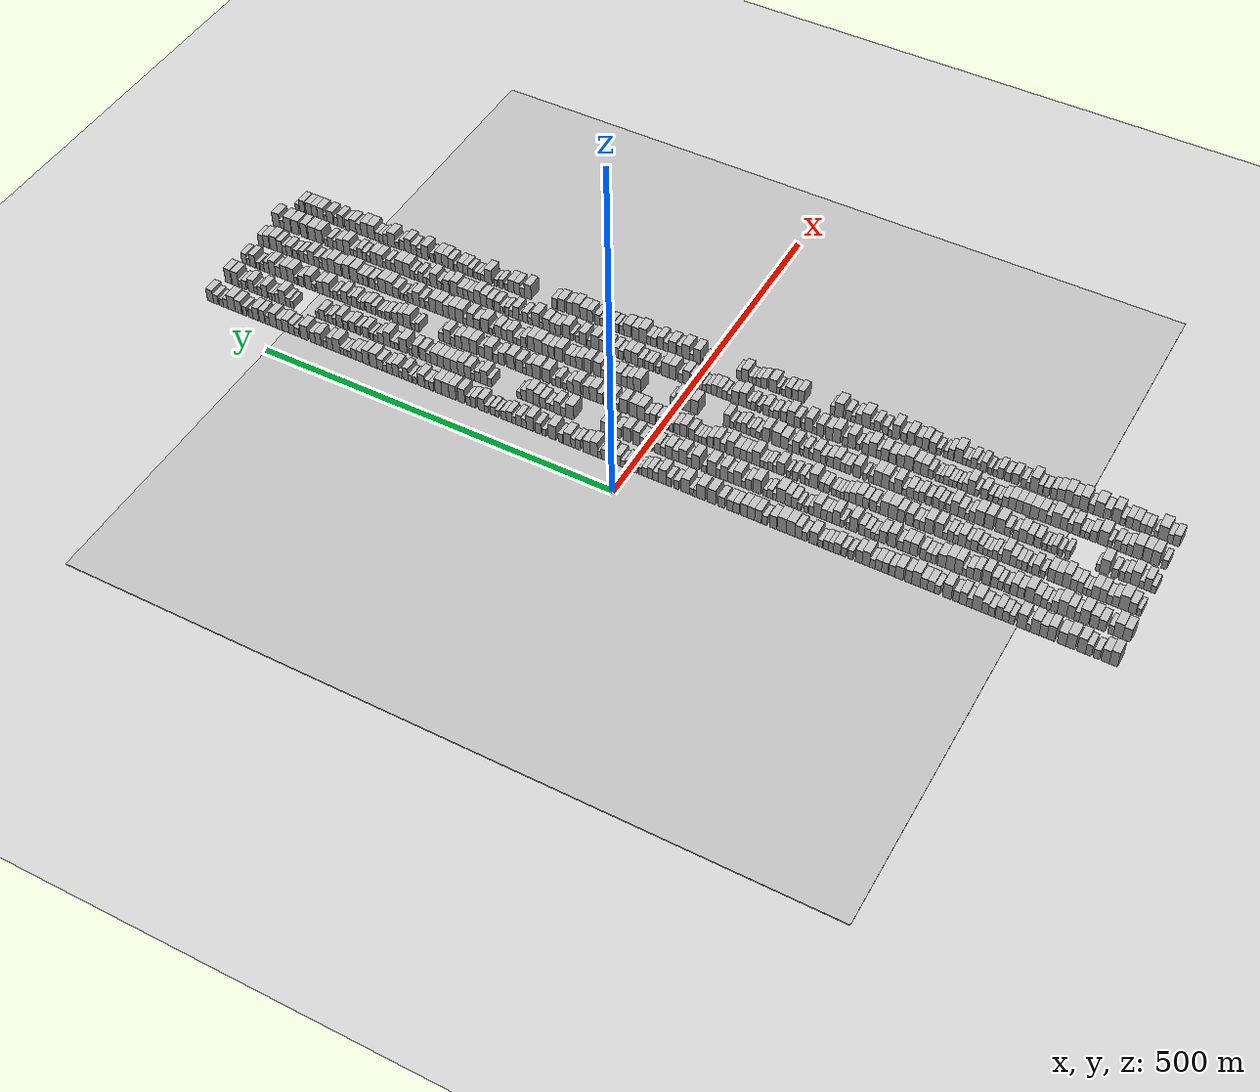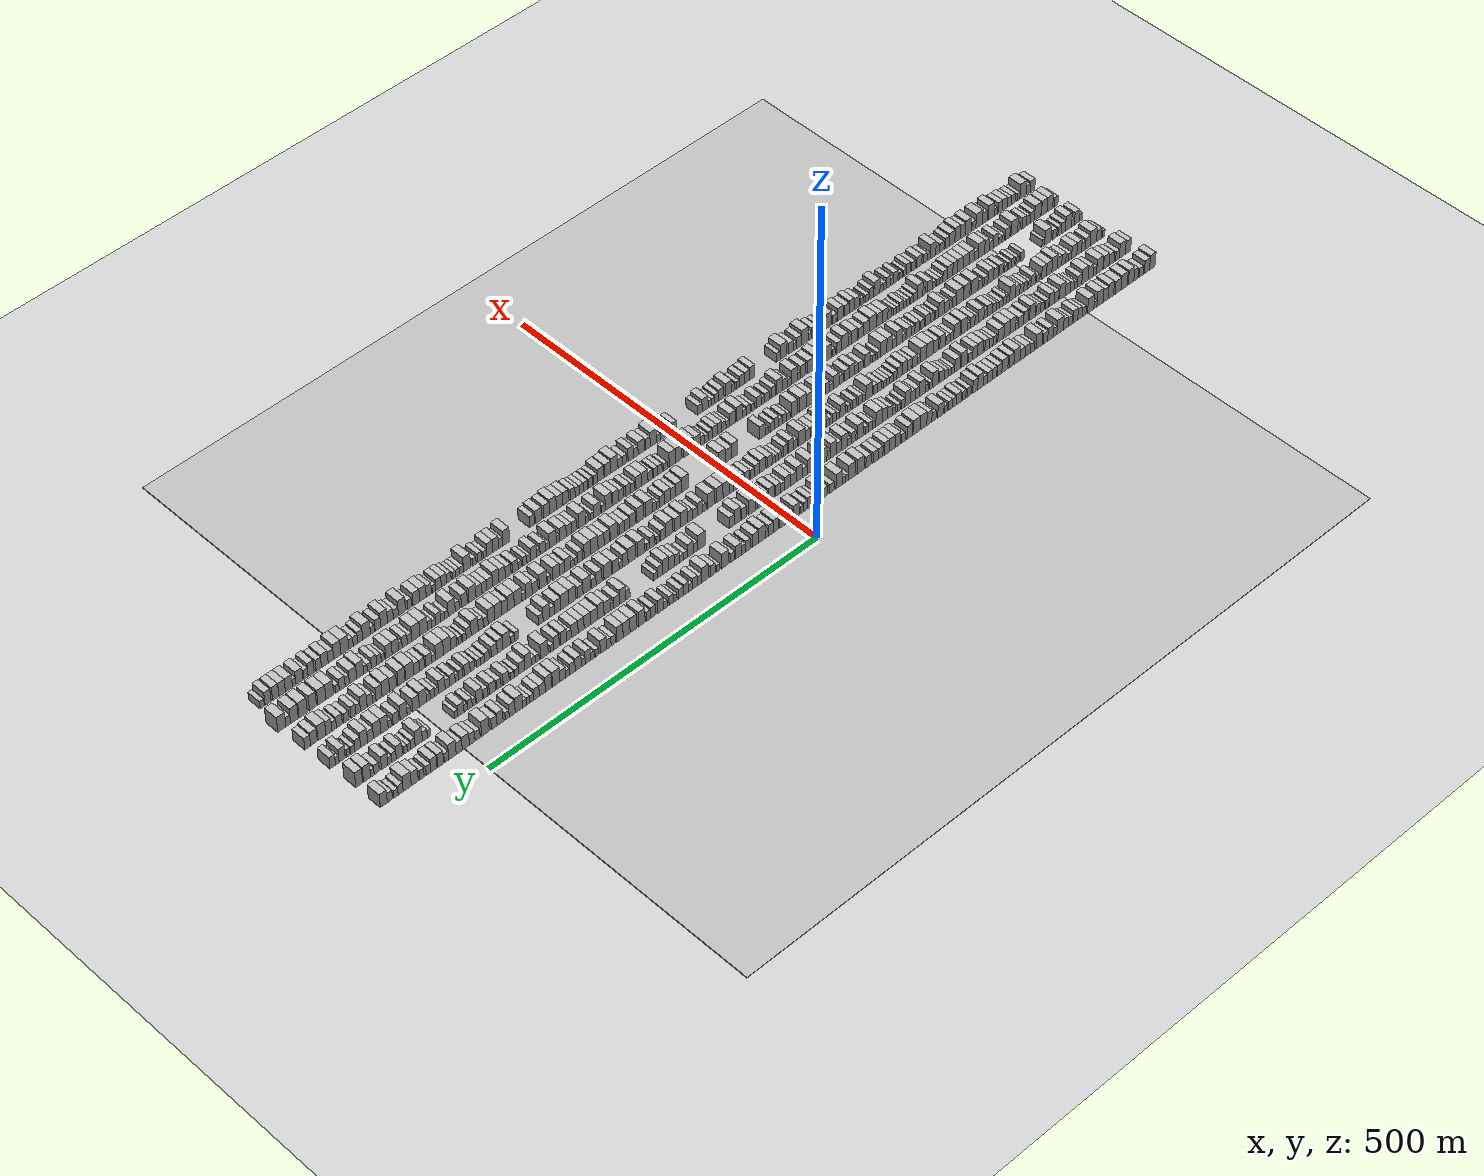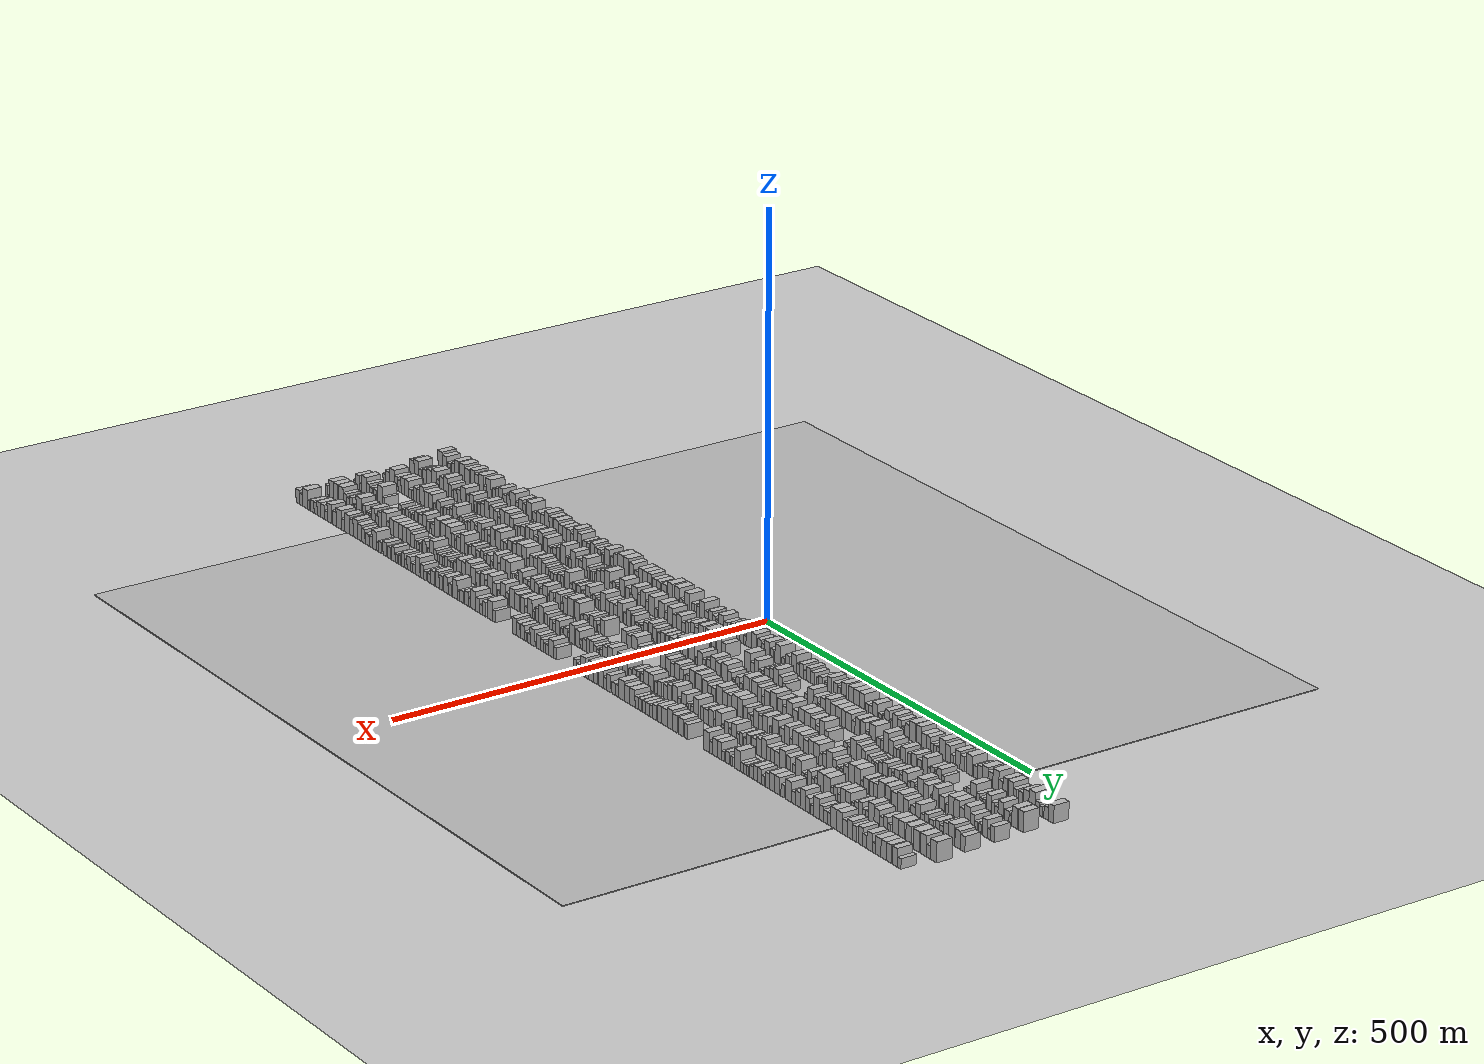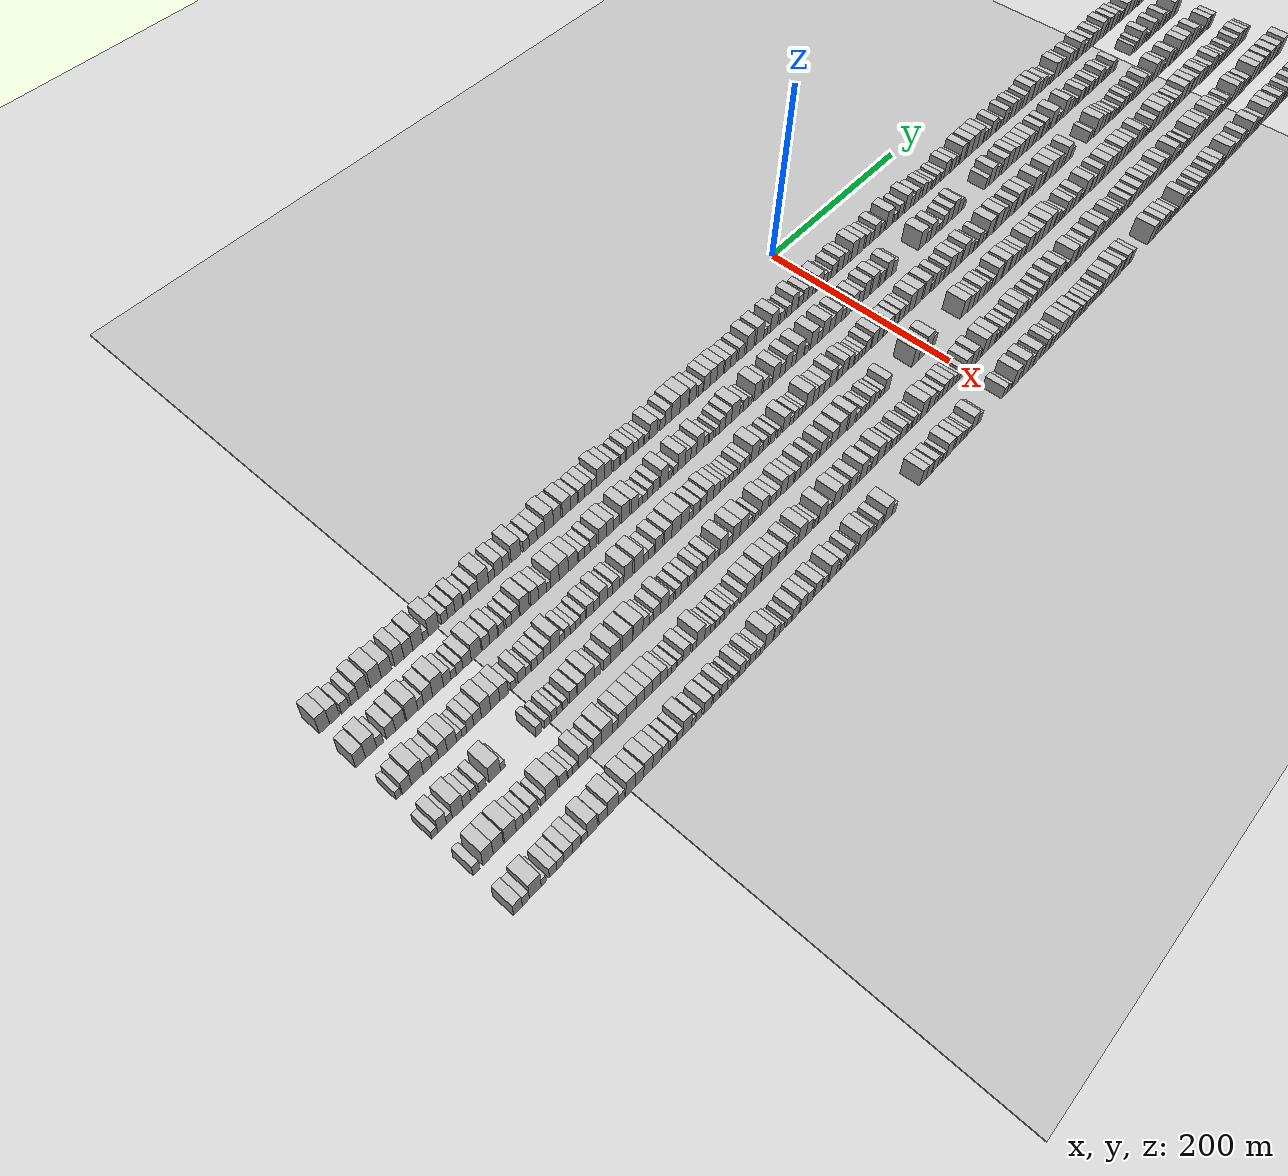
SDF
<?xml version="1.0" encoding="utf-8"?>

<sdf version="1.6">

   <world name="default">

      <gui fullscreen="0">

         <camera name="user_camera">

            <pose>-15 0 4.57585 0 0 0</pose>

            <view_controller>orbit</view_controller>

         </camera>

      </gui>

      <scene>

         <sky>

           <clouds>

             <speed>12</speed>

           </clouds>

         </sky>

         <ambient>0.4 0.4 0.4 1</ambient>

         <background>0.7 0.7 0.7 1</background>

         <shadows>1</shadows>

      </scene>

      <gravity>0 0 -9.8066</gravity>

      <magnetic_field>6e-06 2.3e-05 -4.2e-05</magnetic_field>

      <physics default="0" name="default_physics" type="ode">

         <ode>

            <solver>

               <type>quick</type>

               <iters>10</iters>

               <sor>1.0</sor>

               <use_dynamic_moi_rescaling>0</use_dynamic_moi_rescaling>

            </solver>

            <constraints>

               <cfm>0</cfm>

               <erp>0.2</erp>

               <contact_max_correcting_vel>100</contact_max_correcting_vel>

               <contact_surface_layer>0.001</contact_surface_layer>

            </constraints>

         </ode>

         <max_step_size>0.004</max_step_size>

         <real_time_factor>1</real_time_factor>

         <real_time_update_rate>250</real_time_update_rate>

      </physics>

      <light name="sun" type="directional">

         <cast_shadows>1</cast_shadows>

         <pose>0 0 10 0 0 0</pose>

         <diffuse>0.8 0.8 0.8 1</diffuse>

         <specular>0.2 0.2 0.2 1</specular>

         <attenuation>

            <range>1000</range>

            <constant>0.9</constant>

            <linear>0.01</linear>

            <quadratic>0.001</quadratic>

         </attenuation>

         <direction>-0.5 0.1 -0.9</direction>

      </light>

      <include>

         <name>ground_plane_1</name>

         <uri>model://HANNAS_ground_plane</uri>

         <pose>0 0 0  0 0 0</pose>

      </include>

      <include>

         <name>ground_plane_2</name>

         <uri>model://HANNAS_ground_plane</uri>

         <pose>100 0 0  0 0 0</pose>

      </include>

      <model name="building_1">

         <static>1</static>

         <pose frame="">50.0000 -614.9711 0 0.000000 0.000000 0.000000</pose>

         <link name="link">

            <pose frame="">0 0 12.00 0 0 0</pose>

            <collision name="collision">

               <geometry>

                  <box>

                     <size>20.0000 10.0579 24.0000</size>

                  </box>

               </geometry>

               <max_contacts>10</max_contacts>

               <surface>

                  <contact>

                     <ode/>

                  </contact>

                  <bounce/>

                  <friction>

                     <torsional>

                        <ode/>

                     </torsional>

                     <ode/>

                  </friction>

               </surface>

            </collision>

            <visual name="visual">

               <cast_shadows>0</cast_shadows>

               <geometry>

                  <box>

                     <size>20.0000 10.0579 24.0000</size>

                  </box>

               </geometry>

               <material>

                  <script>

                     <uri>model://HANNAS_wall/materials/scripts</uri>

                     <uri>model://HANNAS_wall/materials/textures</uri>

                     <name>vrc/HANNAS_wall</name>

                  </script>

               </material>

            </visual>

            <self_collide>0</self_collide>

            <enable_wind>0</enable_wind>

            <kinematic>0</kinematic>

         </link>

      </model>

      <model name="building_2">

         <static>1</static>

         <pose frame="">50.0000 -605.1579 0 0.000000 0.000000 0.000000</pose>

         <link name="link">

            <pose frame="">0 0 10.50 0 0 0</pose>

            <collision name="collision">

               <geometry>

                  <box>

                     <size>20.0000 9.5684 21.0000</size>

                  </box>

               </geometry>

               <max_contacts>10</max_contacts>

               <surface>

                  <contact>

                     <ode/>

                  </contact>

                  <bounce/>

                  <friction>

                     <torsional>

                        <ode/>

                     </torsional>

                     <ode/>

                  </friction>

               </surface>

            </collision>

            <visual name="visual">

               <cast_shadows>0</cast_shadows>

               <geometry>

                  <box>

                     <size>20.0000 9.5684 21.0000</size>

                  </box>

               </geometry>

               <material>

                  <script>

                     <uri>model://HANNAS_wall/materials/scripts</uri>

                     <uri>model://HANNAS_wall/materials/textures</uri>

                     <name>vrc/HANNAS_wall</name>

                  </script>

               </material>

            </visual>

            <self_collide>0</self_collide>

            <enable_wind>0</enable_wind>

            <kinematic>0</kinematic>

         </link>

      </model>

      <model name="building_3">

         <static>1</static>

         <pose frame="">50.0000 -594.6582 0 0.000000 0.000000 0.000000</pose>

         <link name="link">

            <pose frame="">0 0 7.50 0 0 0</pose>

            <collision name="collision">

               <geometry>

                  <box>

                     <size>20.0000 7.4311 15.0000</size>

                  </box>

               </geometry>

               <max_contacts>10</max_contacts>

               <surface>

                  <contact>

                     <ode/>

                  </contact>

                  <bounce/>

                  <friction>

                     <torsional>

                        <ode/>

                     </torsional>

                     <ode/>

                  </friction>

               </surface>

            </collision>

            <visual name="visual">

               <cast_shadows>0</cast_shadows>

               <geometry>

                  <box>

                     <size>20.0000 7.4311 15.0000</size>

                  </box>

               </geometry>

               <material>

                  <script>

                     <uri>model://HANNAS_wall/materials/scripts</uri>

                     <uri>model://HANNAS_wall/materials/textures</uri>

                     <name>vrc/HANNAS_wall</name>

                  </script>

               </material>

            </visual>

            <self_collide>0</self_collide>

            <enable_wind>0</enable_wind>

            <kinematic>0</kinematic>

         </link>

      </model>

      <model name="building_4">

         <static>1</static>

         <pose frame="">50.0000 -585.2614 0 0.000000 0.000000 0.000000</pose>

         <link name="link">

            <pose frame="">0 0 9.00 0 0 0</pose>

            <collision name="collision">

               <geometry>

                  <box>

                     <size>20.0000 7.3626 18.0000</size>

                  </box>

               </geometry>

               <max_contacts>10</max_contacts>

               <surface>

                  <contact>

                     <ode/>

                  </contact>

                  <bounce/>

                  <friction>

                     <torsional>

                        <ode/>

                     </torsional>

                     <ode/>

                  </friction>

               </surface>

            </collision>

            <visual name="visual">

               <cast_shadows>0</cast_shadows>

               <geometry>

                  <box>

                     <size>20.0000 7.3626 18.0000</size>

                  </box>

               </geometry>

               <material>

                  <script>

                     <uri>model://HANNAS_wall/materials/scripts</uri>

                     <uri>model://HANNAS_wall/materials/textures</uri>

                     <name>vrc/HANNAS_wall</name>

                  </script>

               </material>

            </visual>

            <self_collide>0</self_collide>

            <enable_wind>0</enable_wind>

            <kinematic>0</kinematic>

         </link>

      </model>

      <model name="building_5">

         <static>1</static>

         <pose frame="">50.0000 -576.5760 0 0.000000 0.000000 0.000000</pose>

         <link name="link">

            <pose frame="">0 0 12.00 0 0 0</pose>

            <collision name="collision">

               <geometry>

                  <box>

                     <size>20.0000 10.0083 24.0000</size>

                  </box>

               </geometry>

               <max_contacts>10</max_contacts>

               <surface>

                  <contact>

                     <ode/>

                  </contact>

                  <bounce/>

                  <friction>

                     <torsional>

                        <ode/>

                     </torsional>

                     <ode/>

                  </friction>

               </surface>

            </collision>

            <visual name="visual">

               <cast_shadows>0</cast_shadows>

               <geometry>

                  <box>

                     <size>20.0000 10.0083 24.0000</size>

                  </box>

               </geometry>

               <material>

                  <script>

                     <uri>model://HANNAS_wall/materials/scripts</uri>

                     <uri>model://HANNAS_wall/materials/textures</uri>

                     <name>vrc/HANNAS_wall</name>

                  </script>

               </material>

            </visual>

            <self_collide>0</self_collide>

            <enable_wind>0</enable_wind>

            <kinematic>0</kinematic>

         </link>

      </model>

      <model name="building_6">

         <static>1</static>

         <pose frame="">50.0000 -564.0394 0 0.000000 0.000000 0.000000</pose>

         <link name="link">

            <pose frame="">0 0 12.00 0 0 0</pose>

            <collision name="collision">

               <geometry>

                  <box>

                     <size>20.0000 11.0649 24.0000</size>

                  </box>

               </geometry>

               <max_contacts>10</max_contacts>

               <surface>

                  <contact>

                     <ode/>

                  </contact>

                  <bounce/>

                  <friction>

                     <torsional>

                        <ode/>

                     </torsional>

                     <ode/>

                  </friction>

               </surface>

            </collision>

            <visual name="visual">

               <cast_shadows>0</cast_shadows>

               <geometry>

                  <box>

                     <size>20.0000 11.0649 24.0000</size>

                  </box>

               </geometry>

               <material>

                  <script>

                     <uri>model://HANNAS_wall/materials/scripts</uri>

                     <uri>model://HANNAS_wall/materials/textures</uri>

                     <name>vrc/HANNAS_wall</name>

                  </script>

               </material>

            </visual>

            <self_collide>0</self_collide>

            <enable_wind>0</enable_wind>

            <kinematic>0</kinematic>

         </link>

      </model>

      <model name="building_7">

         <static>1</static>

         <pose frame="">50.0000 -553.2618 0 0.000000 0.000000 0.000000</pose>

         <link name="link">

            <pose frame="">0 0 10.50 0 0 0</pose>

            <collision name="collision">

               <geometry>

                  <box>

                     <size>20.0000 10.4902 21.0000</size>

                  </box>

               </geometry>

               <max_contacts>10</max_contacts>

               <surface>

                  <contact>

                     <ode/>

                  </contact>

                  <bounce/>

                  <friction>

                     <torsional>

                        <ode/>

                     </torsional>

                     <ode/>

                  </friction>

               </surface>

            </collision>

            <visual name="visual">

               <cast_shadows>0</cast_shadows>

               <geometry>

                  <box>

                     <size>20.0000 10.4902 21.0000</size>

                  </box>

               </geometry>

               <material>

                  <script>

                     <uri>model://HANNAS_wall/materials/scripts</uri>

                     <uri>model://HANNAS_wall/materials/textures</uri>

                     <name>vrc/HANNAS_wall</name>

                  </script>

               </material>

            </visual>

            <self_collide>0</self_collide>

            <enable_wind>0</enable_wind>

            <kinematic>0</kinematic>

         </link>

      </model>

      <model name="building_8">

         <static>1</static>

         <pose frame="">50.0000 -540.2076 0 0.000000 0.000000 0.000000</pose>

         <link name="link">

            <pose frame="">0 0 12.00 0 0 0</pose>

            <collision name="collision">

               <geometry>

                  <box>

                     <size>20.0000 9.6182 24.0000</size>

                  </box>

               </geometry>

               <max_contacts>10</max_contacts>

               <surface>

                  <contact>

                     <ode/>

                  </contact>

                  <bounce/>

                  <friction>

                     <torsional>

                        <ode/>

                     </torsional>

                     <ode/>

                  </friction>

               </surface>

            </collision>

            <visual name="visual">

               <cast_shadows>0</cast_shadows>

               <geometry>

                  <box>

                     <size>20.0000 9.6182 24.0000</size>

                  </box>

               </geometry>

               <material>

                  <script>

                     <uri>model://HANNAS_wall/materials/scripts</uri>

                     <uri>model://HANNAS_wall/materials/textures</uri>

                     <name>vrc/HANNAS_wall</name>

                  </script>

               </material>

            </visual>

            <self_collide>0</self_collide>

            <enable_wind>0</enable_wind>

            <kinematic>0</kinematic>

         </link>

      </model>

      <model name="building_9">

         <static>1</static>

         <pose frame="">50.0000 -530.8291 0 0.000000 0.000000 0.000000</pose>

         <link name="link">

            <pose frame="">0 0 10.50 0 0 0</pose>

            <collision name="collision">

               <geometry>

                  <box>

                     <size>20.0000 9.1390 21.0000</size>

                  </box>

               </geometry>

               <max_contacts>10</max_contacts>

               <surface>

                  <contact>

                     <ode/>

                  </contact>

                  <bounce/>

                  <friction>

                     <torsional>

                        <ode/>

                     </torsional>

                     <ode/>

                  </friction>

               </surface>

            </collision>

            <visual name="visual">

               <cast_shadows>0</cast_shadows>

               <geometry>

                  <box>

                     <size>20.0000 9.1390 21.0000</size>

                  </box>

               </geometry>

               <material>

                  <script>

                     <uri>model://HANNAS_wall/materials/scripts</uri>

                     <uri>model://HANNAS_wall/materials/textures</uri>

                     <name>vrc/HANNAS_wall</name>

                  </script>

               </material>

            </visual>

            <self_collide>0</self_collide>

            <enable_wind>0</enable_wind>

            <kinematic>0</kinematic>

         </link>

      </model>

      <model name="building_10">

         <static>1</static>

         <pose frame="">50.0000 -520.8414 0 0.000000 0.000000 0.000000</pose>

         <link name="link">

            <pose frame="">0 0 12.00 0 0 0</pose>

            <collision name="collision">

               <geometry>

                  <box>

                     <size>20.0000 10.8364 24.0000</size>

                  </box>

               </geometry>

               <max_contacts>10</max_contacts>

               <surface>

                  <contact>

                     <ode/>

                  </contact>

                  <bounce/>

                  <friction>

                     <torsional>

                        <ode/>

                     </torsional>

                     <ode/>

                  </friction>

               </surface>

            </collision>

            <visual name="visual">

               <cast_shadows>0</cast_shadows>

               <geometry>

                  <box>

                     <size>20.0000 10.8364 24.0000</size>

                  </box>

               </geometry>

               <material>

                  <script>

                     <uri>model://HANNAS_wall/materials/scripts</uri>

                     <uri>model://HANNAS_wall/materials/textures</uri>

                     <name>vrc/HANNAS_wall</name>

                  </script>

               </material>

            </visual>

            <self_collide>0</self_collide>

            <enable_wind>0</enable_wind>

            <kinematic>0</kinematic>

         </link>

      </model>

      <model name="building_11">

         <static>1</static>

         <pose frame="">50.0000 -512.6842 0 0.000000 0.000000 0.000000</pose>

         <link name="link">

            <pose frame="">0 0 6.00 0 0 0</pose>

            <collision name="collision">

               <geometry>

                  <box>

                     <size>20.0000 5.4778 12.0000</size>

                  </box>

               </geometry>

               <max_contacts>10</max_contacts>

               <surface>

                  <contact>

                     <ode/>

                  </contact>

                  <bounce/>

                  <friction>

                     <torsional>

                        <ode/>

                     </torsional>

                     <ode/>

                  </friction>

               </surface>

            </collision>

            <visual name="visual">

               <cast_shadows>0</cast_shadows>

               <geometry>

                  <box>

                     <size>20.0000 5.4778 12.0000</size>

                  </box>

               </geometry>

               <material>

                  <script>

                     <uri>model://HANNAS_wall/materials/scripts</uri>

                     <uri>model://HANNAS_wall/materials/textures</uri>

                     <name>vrc/HANNAS_wall</name>

                  </script>

               </material>

            </visual>

            <self_collide>0</self_collide>

            <enable_wind>0</enable_wind>

            <kinematic>0</kinematic>

         </link>

      </model>

      <model name="building_12">

         <static>1</static>

         <pose frame="">50.0000 -504.3334 0 0.000000 0.000000 0.000000</pose>

         <link name="link">

            <pose frame="">0 0 12.00 0 0 0</pose>

            <collision name="collision">

               <geometry>

                  <box>

                     <size>20.0000 11.2239 24.0000</size>

                  </box>

               </geometry>

               <max_contacts>10</max_contacts>

               <surface>

                  <contact>

                     <ode/>

                  </contact>

                  <bounce/>

                  <friction>

                     <torsional>

                        <ode/>

                     </torsional>

                     <ode/>

                  </friction>

               </surface>

            </collision>

            <visual name="visual">

               <cast_shadows>0</cast_shadows>

               <geometry>

                  <box>

                     <size>20.0000 11.2239 24.0000</size>

                  </box>

               </geometry>

               <material>

                  <script>

                     <uri>model://HANNAS_wall/materials/scripts</uri>

                     <uri>model://HANNAS_wall/materials/textures</uri>

                     <name>vrc/HANNAS_wall</name>

                  </script>

               </material>

            </visual>

            <self_collide>0</self_collide>

            <enable_wind>0</enable_wind>

            <kinematic>0</kinematic>

         </link>

      </model>

      <model name="building_13">

         <static>1</static>

         <pose frame="">50.0000 -492.4218 0 0.000000 0.000000 0.000000</pose>

         <link name="link">

            <pose frame="">0 0 7.50 0 0 0</pose>

            <collision name="collision">

               <geometry>

                  <box>

                     <size>20.0000 6.5992 15.0000</size>

                  </box>

               </geometry>

               <max_contacts>10</max_contacts>

               <surface>

                  <contact>

                     <ode/>

                  </contact>

                  <bounce/>

                  <friction>

                     <torsional>

                        <ode/>

                     </torsional>

                     <ode/>

                  </friction>

               </surface>

            </collision>

            <visual name="visual">

               <cast_shadows>0</cast_shadows>

               <geometry>

                  <box>

                     <size>20.0000 6.5992 15.0000</size>

                  </box>

               </geometry>

               <material>

                  <script>

                     <uri>model://HANNAS_wall/materials/scripts</uri>

                     <uri>model://HANNAS_wall/materials/textures</uri>

                     <name>vrc/HANNAS_wall</name>

                  </script>

               </material>

            </visual>

            <self_collide>0</self_collide>

            <enable_wind>0</enable_wind>

            <kinematic>0</kinematic>

         </link>

      </model>

      <model name="building_14">

         <static>1</static>

         <pose frame="">50.0000 -485.1858 0 0.000000 0.000000 0.000000</pose>

         <link name="link">

            <pose frame="">0 0 9.00 0 0 0</pose>

            <collision name="collision">

               <geometry>

                  <box>

                     <size>20.0000 7.8728 18.0000</size>

                  </box>

               </geometry>

               <max_contacts>10</max_contacts>

               <surface>

                  <contact>

                     <ode/>

                  </contact>

                  <bounce/>

                  <friction>

                     <torsional>

                        <ode/>

                     </torsional>

                     <ode/>

                  </friction>

               </surface>

            </collision>

            <visual name="visual">

               <cast_shadows>0</cast_shadows>

               <geometry>

                  <box>

                     <size>20.0000 7.8728 18.0000</size>

                  </box>

               </geometry>

               <material>

                  <script>

                     <uri>model://HANNAS_wall/materials/scripts</uri>

                     <uri>model://HANNAS_wall/materials/textures</uri>

                     <name>vrc/HANNAS_wall</name>

                  </script>

               </material>

            </visual>

            <self_collide>0</self_collide>

            <enable_wind>0</enable_wind>

            <kinematic>0</kinematic>

         </link>

      </model>

      <model name="building_15">

         <static>1</static>

         <pose frame="">50.0000 -477.0049 0 0.000000 0.000000 0.000000</pose>

         <link name="link">

            <pose frame="">0 0 10.50 0 0 0</pose>

            <collision name="collision">

               <geometry>

                  <box>

                     <size>20.0000 8.4891 21.0000</size>

                  </box>

               </geometry>

               <max_contacts>10</max_contacts>

               <surface>

                  <contact>

                     <ode/>

                  </contact>

                  <bounce/>

                  <friction>

                     <torsional>

                        <ode/>

                     </torsional>

                     <ode/>

                  </friction>

               </surface>

            </collision>

            <visual name="visual">

               <cast_shadows>0</cast_shadows>

               <geometry>

                  <box>

                     <size>20.0000 8.4891 21.0000</size>

                  </box>

               </geometry>

               <material>

                  <script>

                     <uri>model://HANNAS_wall/materials/scripts</uri>

                     <uri>model://HANNAS_wall/materials/textures</uri>

                     <name>vrc/HANNAS_wall</name>

                  </script>

               </material>

            </visual>

            <self_collide>0</self_collide>

            <enable_wind>0</enable_wind>

            <kinematic>0</kinematic>

         </link>

      </model>

      <model name="building_16">

         <static>1</static>

         <pose frame="">50.0000 -468.0218 0 0.000000 0.000000 0.000000</pose>

         <link name="link">

            <pose frame="">0 0 7.50 0 0 0</pose>

            <collision name="collision">

               <geometry>

                  <box>

                     <size>20.0000 7.4771 15.0000</size>

                  </box>

               </geometry>

               <max_contacts>10</max_contacts>

               <surface>

                  <contact>

                     <ode/>

                  </contact>

                  <bounce/>

                  <friction>

                     <torsional>

                        <ode/>

                     </torsional>

                     <ode/>

                  </friction>

               </surface>

            </collision>

            <visual name="visual">

               <cast_shadows>0</cast_shadows>

               <geometry>

                  <box>

                     <size>20.0000 7.4771 15.0000</size>

                  </box>

               </geometry>

               <material>

                  <script>

                     <uri>model://HANNAS_wall/materials/scripts</uri>

                     <uri>model://HANNAS_wall/materials/textures</uri>

                     <name>vrc/HANNAS_wall</name>

                  </script>

               </material>

            </visual>

            <self_collide>0</self_collide>

            <enable_wind>0</enable_wind>

            <kinematic>0</kinematic>

         </link>

      </model>

      <model name="building_17">

         <static>1</static>

         <pose frame="">50.0000 -460.1328 0 0.000000 0.000000 0.000000</pose>

         <link name="link">

            <pose frame="">0 0 9.00 0 0 0</pose>

            <collision name="collision">

               <geometry>

                  <box>

                     <size>20.0000 8.3009 18.0000</size>

                  </box>

               </geometry>

               <max_contacts>10</max_contacts>

               <surface>

                  <contact>

                     <ode/>

                  </contact>

                  <bounce/>

                  <friction>

                     <torsional>

                        <ode/>

                     </torsional>

                     <ode/>

                  </friction>

               </surface>

            </collision>

            <visual name="visual">

               <cast_shadows>0</cast_shadows>

               <geometry>

                  <box>

                     <size>20.0000 8.3009 18.0000</size>

                  </box>

               </geometry>

               <material>

                  <script>

                     <uri>model://HANNAS_wall/materials/scripts</uri>

                     <uri>model://HANNAS_wall/materials/textures</uri>

                     <name>vrc/HANNAS_wall</name>

                  </script>

               </material>

            </visual>

            <self_collide>0</self_collide>

            <enable_wind>0</enable_wind>

            <kinematic>0</kinematic>

         </link>

      </model>

      <model name="building_18">

         <static>1</static>

         <pose frame="">50.0000 -450.1696 0 0.000000 0.000000 0.000000</pose>

         <link name="link">

            <pose frame="">0 0 12.00 0 0 0</pose>

            <collision name="collision">

               <geometry>

                  <box>

                     <size>20.0000 11.6257 24.0000</size>

                  </box>

               </geometry>

               <max_contacts>10</max_contacts>

               <surface>

                  <contact>

                     <ode/>

                  </contact>

                  <bounce/>

                  <friction>

                     <torsional>

                        <ode/>

                     </torsional>

                     <ode/>

                  </friction>

               </surface>

            </collision>

            <visual name="visual">

               <cast_shadows>0</cast_shadows>

               <geometry>

                  <box>

                     <size>20.0000 11.6257 24.0000</size>

                  </box>

               </geometry>

               <material>

                  <script>

                     <uri>model://HANNAS_wall/materials/scripts</uri>

                     <uri>model://HANNAS_wall/materials/textures</uri>

                     <name>vrc/HANNAS_wall</name>

                  </script>

               </material>

            </visual>

            <self_collide>0</self_collide>

            <enable_wind>0</enable_wind>

            <kinematic>0</kinematic>

         </link>

      </model>

      <model name="building_19">

         <static>1</static>

         <pose frame="">50.0000 -440.9127 0 0.000000 0.000000 0.000000</pose>

         <link name="link">

            <pose frame="">0 0 7.50 0 0 0</pose>

            <collision name="collision">

               <geometry>

                  <box>

                     <size>20.0000 6.8882 15.0000</size>

                  </box>

               </geometry>

               <max_contacts>10</max_contacts>

               <surface>

                  <contact>

                     <ode/>

                  </contact>

                  <bounce/>

                  <friction>

                     <torsional>

                        <ode/>

                     </torsional>

                     <ode/>

                  </friction>

               </surface>

            </collision>

            <visual name="visual">

               <cast_shadows>0</cast_shadows>

               <geometry>

                  <box>

                     <size>20.0000 6.8882 15.0000</size>

                  </box>

               </geometry>

               <material>

                  <script>

                     <uri>model://HANNAS_wall/materials/scripts</uri>

                     <uri>model://HANNAS_wall/materials/textures</uri>

                     <name>vrc/HANNAS_wall</name>

                  </script>

               </material>

            </visual>

            <self_collide>0</self_collide>

            <enable_wind>0</enable_wind>

            <kinematic>0</kinematic>

         </link>

      </model>

      <model name="building_20">

         <static>1</static>

         <pose frame="">50.0000 -432.9090 0 0.000000 0.000000 0.000000</pose>

         <link name="link">

            <pose frame="">0 0 10.50 0 0 0</pose>

            <collision name="collision">

               <geometry>

                  <box>

                     <size>20.0000 9.1191 21.0000</size>

                  </box>

               </geometry>

               <max_contacts>10</max_contacts>

               <surface>

                  <contact>

                     <ode/>

                  </contact>

                  <bounce/>

                  <friction>

                     <torsional>

                        <ode/>

                     </torsional>

                     <ode/>

                  </friction>

               </surface>

            </collision>

            <visual name="visual">

               <cast_shadows>0</cast_shadows>

               <geometry>

                  <box>

                     <size>20.0000 9.1191 21.0000</size>

                  </box>

               </geometry>

               <material>

                  <script>

                     <uri>model://HANNAS_wall/materials/scripts</uri>

                     <uri>model://HANNAS_wall/materials/textures</uri>

                     <name>vrc/HANNAS_wall</name>

                  </script>

               </material>

            </visual>

            <self_collide>0</self_collide>

            <enable_wind>0</enable_wind>

            <kinematic>0</kinematic>

         </link>

      </model>

      <model name="building_21">

         <static>1</static>

         <pose frame="">50.0000 -424.5883 0 0.000000 0.000000 0.000000</pose>

         <link name="link">

            <pose frame="">0 0 9.00 0 0 0</pose>

            <collision name="collision">

               <geometry>

                  <box>

                     <size>20.0000 7.5224 18.0000</size>

                  </box>

               </geometry>

               <max_contacts>10</max_contacts>

               <surface>

                  <contact>

                     <ode/>

                  </contact>

                  <bounce/>

                  <friction>

                     <torsional>

                        <ode/>

                     </torsional>

                     <ode/>

                  </friction>

               </surface>

            </collision>

            <visual name="visual">

               <cast_shadows>0</cast_shadows>

               <geometry>

                  <box>

                     <size>20.0000 7.5224 18.0000</size>

                  </box>

               </geometry>

               <material>

                  <script>

                     <uri>model://HANNAS_wall/materials/scripts</uri>

                     <uri>model://HANNAS_wall/materials/textures</uri>

                     <name>vrc/HANNAS_wall</name>

                  </script>

               </material>

            </visual>

            <self_collide>0</self_collide>

            <enable_wind>0</enable_wind>

            <kinematic>0</kinematic>

         </link>

      </model>

      <model name="building_22">

         <static>1</static>

         <pose frame="">50.0000 -413.3890 0 0.000000 0.000000 0.000000</pose>

         <link name="link">

            <pose frame="">0 0 12.00 0 0 0</pose>

            <collision name="collision">

               <geometry>

                  <box>

                     <size>20.0000 10.8761 24.0000</size>

                  </box>

               </geometry>

               <max_contacts>10</max_contacts>

               <surface>

                  <contact>

                     <ode/>

                  </contact>

                  <bounce/>

                  <friction>

                     <torsional>

                        <ode/>

                     </torsional>

                     <ode/>

                  </friction>

               </surface>

            </collision>

            <visual name="visual">

               <cast_shadows>0</cast_shadows>

               <geometry>

                  <box>

                     <size>20.0000 10.8761 24.0000</size>

                  </box>

               </geometry>

               <material>

                  <script>

                     <uri>model://HANNAS_wall/materials/scripts</uri>

                     <uri>model://HANNAS_wall/materials/textures</uri>

                     <name>vrc/HANNAS_wall</name>

                  </script>

               </material>

            </visual>

            <self_collide>0</self_collide>

            <enable_wind>0</enable_wind>

            <kinematic>0</kinematic>

         </link>

      </model>

      <model name="building_23">

         <static>1</static>

         <pose frame="">50.0000 -401.3649 0 0.000000 0.000000 0.000000</pose>

         <link name="link">

            <pose frame="">0 0 7.50 0 0 0</pose>

            <collision name="collision">

               <geometry>

                  <box>

                     <size>20.0000 7.1721 15.0000</size>

                  </box>

               </geometry>

               <max_contacts>10</max_contacts>

               <surface>

                  <contact>

                     <ode/>

                  </contact>

                  <bounce/>

                  <friction>

                     <torsional>

                        <ode/>

                     </torsional>

                     <ode/>

                  </friction>

               </surface>

            </collision>

            <visual name="visual">

               <cast_shadows>0</cast_shadows>

               <geometry>

                  <box>

                     <size>20.0000 7.1721 15.0000</size>

                  </box>

               </geometry>

               <material>

                  <script>

                     <uri>model://HANNAS_wall/materials/scripts</uri>

                     <uri>model://HANNAS_wall/materials/textures</uri>

                     <name>vrc/HANNAS_wall</name>

                  </script>

               </material>

            </visual>

            <self_collide>0</self_collide>

            <enable_wind>0</enable_wind>

            <kinematic>0</kinematic>

         </link>

      </model>

      <model name="building_24">

         <static>1</static>

         <pose frame="">50.0000 -393.2882 0 0.000000 0.000000 0.000000</pose>

         <link name="link">

            <pose frame="">0 0 9.00 0 0 0</pose>

            <collision name="collision">

               <geometry>

                  <box>

                     <size>20.0000 8.9813 18.0000</size>

                  </box>

               </geometry>

               <max_contacts>10</max_contacts>

               <surface>

                  <contact>

                     <ode/>

                  </contact>

                  <bounce/>

                  <friction>

                     <torsional>

                        <ode/>

                     </torsional>

                     <ode/>

                  </friction>

               </surface>

            </collision>

            <visual name="visual">

               <cast_shadows>0</cast_shadows>

               <geometry>

                  <box>

                     <size>20.0000 8.9813 18.0000</size>

                  </box>

               </geometry>

               <material>

                  <script>

                     <uri>model://HANNAS_wall/materials/scripts</uri>

                     <uri>model://HANNAS_wall/materials/textures</uri>

                     <name>vrc/HANNAS_wall</name>

                  </script>

               </material>

            </visual>

            <self_collide>0</self_collide>

            <enable_wind>0</enable_wind>

            <kinematic>0</kinematic>

         </link>

      </model>

      <model name="building_25">

         <static>1</static>

         <pose frame="">50.0000 -384.4250 0 0.000000 0.000000 0.000000</pose>

         <link name="link">

            <pose frame="">0 0 9.00 0 0 0</pose>

            <collision name="collision">

               <geometry>

                  <box>

                     <size>20.0000 8.7452 18.0000</size>

                  </box>

               </geometry>

               <max_contacts>10</max_contacts>

               <surface>

                  <contact>

                     <ode/>

                  </contact>

                  <bounce/>

                  <friction>

                     <torsional>

                        <ode/>

                     </torsional>

                     <ode/>

                  </friction>

               </surface>

            </collision>

            <visual name="visual">

               <cast_shadows>0</cast_shadows>

               <geometry>

                  <box>

                     <size>20.0000 8.7452 18.0000</size>

                  </box>

               </geometry>

               <material>

                  <script>

                     <uri>model://HANNAS_wall/materials/scripts</uri>

                     <uri>model://HANNAS_wall/materials/textures</uri>

                     <name>vrc/HANNAS_wall</name>

                  </script>

               </material>

            </visual>

            <self_collide>0</self_collide>

            <enable_wind>0</enable_wind>

            <kinematic>0</kinematic>

         </link>

      </model>

      <model name="building_26">

         <static>1</static>

         <pose frame="">50.0000 -374.7826 0 0.000000 0.000000 0.000000</pose>

         <link name="link">

            <pose frame="">0 0 12.00 0 0 0</pose>

            <collision name="collision">

               <geometry>

                  <box>

                     <size>20.0000 10.5395 24.0000</size>

                  </box>

               </geometry>

               <max_contacts>10</max_contacts>

               <surface>

                  <contact>

                     <ode/>

                  </contact>

                  <bounce/>

                  <friction>

                     <torsional>

                        <ode/>

                     </torsional>

                     <ode/>

                  </friction>

               </surface>

            </collision>

            <visual name="visual">

               <cast_shadows>0</cast_shadows>

               <geometry>

                  <box>

                     <size>20.0000 10.5395 24.0000</size>

                  </box>

               </geometry>

               <material>

                  <script>

                     <uri>model://HANNAS_wall/materials/scripts</uri>

                     <uri>model://HANNAS_wall/materials/textures</uri>

                     <name>vrc/HANNAS_wall</name>

                  </script>

               </material>

            </visual>

            <self_collide>0</self_collide>

            <enable_wind>0</enable_wind>

            <kinematic>0</kinematic>

         </link>

      </model>

      <model name="building_27">

         <static>1</static>

         <pose frame="">50.0000 -365.2559 0 0.000000 0.000000 0.000000</pose>

         <link name="link">

            <pose frame="">0 0 10.50 0 0 0</pose>

            <collision name="collision">

               <geometry>

                  <box>

                     <size>20.0000 8.5140 21.0000</size>

                  </box>

               </geometry>

               <max_contacts>10</max_contacts>

               <surface>

                  <contact>

                     <ode/>

                  </contact>

                  <bounce/>

                  <friction>

                     <torsional>

                        <ode/>

                     </torsional>

                     <ode/>

                  </friction>

               </surface>

            </collision>

            <visual name="visual">

               <cast_shadows>0</cast_shadows>

               <geometry>

                  <box>

                     <size>20.0000 8.5140 21.0000</size>

                  </box>

               </geometry>

               <material>

                  <script>

                     <uri>model://HANNAS_wall/materials/scripts</uri>

                     <uri>model://HANNAS_wall/materials/textures</uri>

                     <name>vrc/HANNAS_wall</name>

                  </script>

               </material>

            </visual>

            <self_collide>0</self_collide>

            <enable_wind>0</enable_wind>

            <kinematic>0</kinematic>

         </link>

      </model>

      <model name="building_28">

         <static>1</static>

         <pose frame="">50.0000 -353.7979 0 0.000000 0.000000 0.000000</pose>

         <link name="link">

            <pose frame="">0 0 10.50 0 0 0</pose>

            <collision name="collision">

               <geometry>

                  <box>

                     <size>20.0000 10.4020 21.0000</size>

                  </box>

               </geometry>

               <max_contacts>10</max_contacts>

               <surface>

                  <contact>

                     <ode/>

                  </contact>

                  <bounce/>

                  <friction>

                     <torsional>

                        <ode/>

                     </torsional>

                     <ode/>

                  </friction>

               </surface>

            </collision>

            <visual name="visual">

               <cast_shadows>0</cast_shadows>

               <geometry>

                  <box>

                     <size>20.0000 10.4020 21.0000</size>

                  </box>

               </geometry>

               <material>

                  <script>

                     <uri>model://HANNAS_wall/materials/scripts</uri>

                     <uri>model://HANNAS_wall/materials/textures</uri>

                     <name>vrc/HANNAS_wall</name>

                  </script>

               </material>

            </visual>

            <self_collide>0</self_collide>

            <enable_wind>0</enable_wind>

            <kinematic>0</kinematic>

         </link>

      </model>

      <model name="building_29">

         <static>1</static>

         <pose frame="">50.0000 -344.6565 0 0.000000 0.000000 0.000000</pose>

         <link name="link">

            <pose frame="">0 0 9.00 0 0 0</pose>

            <collision name="collision">

               <geometry>

                  <box>

                     <size>20.0000 7.8808 18.0000</size>

                  </box>

               </geometry>

               <max_contacts>10</max_contacts>

               <surface>

                  <contact>

                     <ode/>

                  </contact>

                  <bounce/>

                  <friction>

                     <torsional>

                        <ode/>

                     </torsional>

                     <ode/>

                  </friction>

               </surface>

            </collision>

            <visual name="visual">

               <cast_shadows>0</cast_shadows>

               <geometry>

                  <box>

                     <size>20.0000 7.8808 18.0000</size>

                  </box>

               </geometry>

               <material>

                  <script>

                     <uri>model://HANNAS_wall/materials/scripts</uri>

                     <uri>model://HANNAS_wall/materials/textures</uri>

                     <name>vrc/HANNAS_wall</name>

                  </script>

               </material>

            </visual>

            <self_collide>0</self_collide>

            <enable_wind>0</enable_wind>

            <kinematic>0</kinematic>

         </link>

      </model>

      <model name="building_30">

         <static>1</static>

         <pose frame="">50.0000 -335.7400 0 0.000000 0.000000 0.000000</pose>

         <link name="link">

            <pose frame="">0 0 9.00 0 0 0</pose>

            <collision name="collision">

               <geometry>

                  <box>

                     <size>20.0000 7.9522 18.0000</size>

                  </box>

               </geometry>

               <max_contacts>10</max_contacts>

               <surface>

                  <contact>

                     <ode/>

                  </contact>

                  <bounce/>

                  <friction>

                     <torsional>

                        <ode/>

                     </torsional>

                     <ode/>

                  </friction>

               </surface>

            </collision>

            <visual name="visual">

               <cast_shadows>0</cast_shadows>

               <geometry>

                  <box>

                     <size>20.0000 7.9522 18.0000</size>

                  </box>

               </geometry>

               <material>

                  <script>

                     <uri>model://HANNAS_wall/materials/scripts</uri>

                     <uri>model://HANNAS_wall/materials/textures</uri>

                     <name>vrc/HANNAS_wall</name>

                  </script>

               </material>

            </visual>

            <self_collide>0</self_collide>

            <enable_wind>0</enable_wind>

            <kinematic>0</kinematic>

         </link>

      </model>

      <model name="building_31">

         <static>1</static>

         <pose frame="">50.0000 -327.6117 0 0.000000 0.000000 0.000000</pose>

         <link name="link">

            <pose frame="">0 0 9.00 0 0 0</pose>

            <collision name="collision">

               <geometry>

                  <box>

                     <size>20.0000 8.3045 18.0000</size>

                  </box>

               </geometry>

               <max_contacts>10</max_contacts>

               <surface>

                  <contact>

                     <ode/>

                  </contact>

                  <bounce/>

                  <friction>

                     <torsional>

                        <ode/>

                     </torsional>

                     <ode/>

                  </friction>

               </surface>

            </collision>

            <visual name="visual">

               <cast_shadows>0</cast_shadows>

               <geometry>

                  <box>

                     <size>20.0000 8.3045 18.0000</size>

                  </box>

               </geometry>

               <material>

                  <script>

                     <uri>model://HANNAS_wall/materials/scripts</uri>

                     <uri>model://HANNAS_wall/materials/textures</uri>

                     <name>vrc/HANNAS_wall</name>

                  </script>

               </material>

            </visual>

            <self_collide>0</self_collide>

            <enable_wind>0</enable_wind>

            <kinematic>0</kinematic>

         </link>

      </model>

      <model name="building_32">

         <static>1</static>

         <pose frame="">50.0000 -320.1309 0 0.000000 0.000000 0.000000</pose>

         <link name="link">

            <pose frame="">0 0 7.50 0 0 0</pose>

            <collision name="collision">

               <geometry>

                  <box>

                     <size>20.0000 6.6571 15.0000</size>

                  </box>

               </geometry>

               <max_contacts>10</max_contacts>

               <surface>

                  <contact>

                     <ode/>

                  </contact>

                  <bounce/>

                  <friction>

                     <torsional>

                        <ode/>

                     </torsional>

                     <ode/>

                  </friction>

               </surface>

            </collision>

            <visual name="visual">

               <cast_shadows>0</cast_shadows>

               <geometry>

                  <box>

                     <size>20.0000 6.6571 15.0000</size>

                  </box>

               </geometry>

               <material>

                  <script>

                     <uri>model://HANNAS_wall/materials/scripts</uri>

                     <uri>model://HANNAS_wall/materials/textures</uri>

                     <name>vrc/HANNAS_wall</name>

                  </script>

               </material>

            </visual>

            <self_collide>0</self_collide>

            <enable_wind>0</enable_wind>

            <kinematic>0</kinematic>

         </link>

      </model>

      <model name="building_33">

         <static>1</static>

         <pose frame="">50.0000 -311.9429 0 0.000000 0.000000 0.000000</pose>

         <link name="link">

            <pose frame="">0 0 12.00 0 0 0</pose>

            <collision name="collision">

               <geometry>

                  <box>

                     <size>20.0000 9.7190 24.0000</size>

                  </box>

               </geometry>

               <max_contacts>10</max_contacts>

               <surface>

                  <contact>

                     <ode/>

                  </contact>

                  <bounce/>

                  <friction>

                     <torsional>

                        <ode/>

                     </torsional>

                     <ode/>

                  </friction>

               </surface>

            </collision>

            <visual name="visual">

               <cast_shadows>0</cast_shadows>

               <geometry>

                  <box>

                     <size>20.0000 9.7190 24.0000</size>

                  </box>

               </geometry>

               <material>

                  <script>

                     <uri>model://HANNAS_wall/materials/scripts</uri>

                     <uri>model://HANNAS_wall/materials/textures</uri>

                     <name>vrc/HANNAS_wall</name>

                  </script>

               </material>

            </visual>

            <self_collide>0</self_collide>

            <enable_wind>0</enable_wind>

            <kinematic>0</kinematic>

         </link>

      </model>

      <model name="building_34">

         <static>1</static>

         <pose frame="">50.0000 -302.8104 0 0.000000 0.000000 0.000000</pose>

         <link name="link">

            <pose frame="">0 0 10.50 0 0 0</pose>

            <collision name="collision">

               <geometry>

                  <box>

                     <size>20.0000 8.5460 21.0000</size>

                  </box>

               </geometry>

               <max_contacts>10</max_contacts>

               <surface>

                  <contact>

                     <ode/>

                  </contact>

                  <bounce/>

                  <friction>

                     <torsional>

                        <ode/>

                     </torsional>

                     <ode/>

                  </friction>

               </surface>

            </collision>

            <visual name="visual">

               <cast_shadows>0</cast_shadows>

               <geometry>

                  <box>

                     <size>20.0000 8.5460 21.0000</size>

                  </box>

               </geometry>

               <material>

                  <script>

                     <uri>model://HANNAS_wall/materials/scripts</uri>

                     <uri>model://HANNAS_wall/materials/textures</uri>

                     <name>vrc/HANNAS_wall</name>

                  </script>

               </material>

            </visual>

            <self_collide>0</self_collide>

            <enable_wind>0</enable_wind>

            <kinematic>0</kinematic>

         </link>

      </model>

      <model name="building_35">

         <static>1</static>

         <pose frame="">50.0000 -292.2063 0 0.000000 0.000000 0.000000</pose>

         <link name="link">

            <pose frame="">0 0 7.50 0 0 0</pose>

            <collision name="collision">

               <geometry>

                  <box>

                     <size>20.0000 6.6621 15.0000</size>

                  </box>

               </geometry>

               <max_contacts>10</max_contacts>

               <surface>

                  <contact>

                     <ode/>

                  </contact>

                  <bounce/>

                  <friction>

                     <torsional>

                        <ode/>

                     </torsional>

                     <ode/>

                  </friction>

               </surface>

            </collision>

            <visual name="visual">

               <cast_shadows>0</cast_shadows>

               <geometry>

                  <box>

                     <size>20.0000 6.6621 15.0000</size>

                  </box>

               </geometry>

               <material>

                  <script>

                     <uri>model://HANNAS_wall/materials/scripts</uri>

                     <uri>model://HANNAS_wall/materials/textures</uri>

                     <name>vrc/HANNAS_wall</name>

                  </script>

               </material>

            </visual>

            <self_collide>0</self_collide>

            <enable_wind>0</enable_wind>

            <kinematic>0</kinematic>

         </link>

      </model>

      <model name="building_36">

         <static>1</static>

         <pose frame="">50.0000 -283.6438 0 0.000000 0.000000 0.000000</pose>

         <link name="link">

            <pose frame="">0 0 7.50 0 0 0</pose>

            <collision name="collision">

               <geometry>

                  <box>

                     <size>20.0000 6.4631 15.0000</size>

                  </box>

               </geometry>

               <max_contacts>10</max_contacts>

               <surface>

                  <contact>

                     <ode/>

                  </contact>

                  <bounce/>

                  <friction>

                     <torsional>

                        <ode/>

                     </torsional>

                     <ode/>

                  </friction>

               </surface>

            </collision>

            <visual name="visual">

               <cast_shadows>0</cast_shadows>

               <geometry>

                  <box>

                     <size>20.0000 6.4631 15.0000</size>

                  </box>

               </geometry>

               <material>

                  <script>

                     <uri>model://HANNAS_wall/materials/scripts</uri>

                     <uri>model://HANNAS_wall/materials/textures</uri>

                     <name>vrc/HANNAS_wall</name>

                  </script>

               </material>

            </visual>

            <self_collide>0</self_collide>

            <enable_wind>0</enable_wind>

            <kinematic>0</kinematic>

         </link>

      </model>

      <model name="building_37">

         <static>1</static>

         <pose frame="">50.0000 -274.9319 0 0.000000 0.000000 0.000000</pose>

         <link name="link">

            <pose frame="">0 0 9.00 0 0 0</pose>

            <collision name="collision">

               <geometry>

                  <box>

                     <size>20.0000 8.9606 18.0000</size>

                  </box>

               </geometry>

               <max_contacts>10</max_contacts>

               <surface>

                  <contact>

                     <ode/>

                  </contact>

                  <bounce/>

                  <friction>

                     <torsional>

                        <ode/>

                     </torsional>

                     <ode/>

                  </friction>

               </surface>

            </collision>

            <visual name="visual">

               <cast_shadows>0</cast_shadows>

               <geometry>

                  <box>

                     <size>20.0000 8.9606 18.0000</size>

                  </box>

               </geometry>

               <material>

                  <script>

                     <uri>model://HANNAS_wall/materials/scripts</uri>

                     <uri>model://HANNAS_wall/materials/textures</uri>

                     <name>vrc/HANNAS_wall</name>

                  </script>

               </material>

            </visual>

            <self_collide>0</self_collide>

            <enable_wind>0</enable_wind>

            <kinematic>0</kinematic>

         </link>

      </model>

      <model name="building_38">

         <static>1</static>

         <pose frame="">50.0000 -267.2856 0 0.000000 0.000000 0.000000</pose>

         <link name="link">

            <pose frame="">0 0 7.50 0 0 0</pose>

            <collision name="collision">

               <geometry>

                  <box>

                     <size>20.0000 6.3320 15.0000</size>

                  </box>

               </geometry>

               <max_contacts>10</max_contacts>

               <surface>

                  <contact>

                     <ode/>

                  </contact>

                  <bounce/>

                  <friction>

                     <torsional>

                        <ode/>

                     </torsional>

                     <ode/>

                  </friction>

               </surface>

            </collision>

            <visual name="visual">

               <cast_shadows>0</cast_shadows>

               <geometry>

                  <box>

                     <size>20.0000 6.3320 15.0000</size>

                  </box>

               </geometry>

               <material>

                  <script>

                     <uri>model://HANNAS_wall/materials/scripts</uri>

                     <uri>model://HANNAS_wall/materials/textures</uri>

                     <name>vrc/HANNAS_wall</name>

                  </script>

               </material>

            </visual>

            <self_collide>0</self_collide>

            <enable_wind>0</enable_wind>

            <kinematic>0</kinematic>

         </link>

      </model>

      <model name="building_39">

         <static>1</static>

         <pose frame="">50.0000 -260.6717 0 0.000000 0.000000 0.000000</pose>

         <link name="link">

            <pose frame="">0 0 7.50 0 0 0</pose>

            <collision name="collision">

               <geometry>

                  <box>

                     <size>20.0000 6.8958 15.0000</size>

                  </box>

               </geometry>

               <max_contacts>10</max_contacts>

               <surface>

                  <contact>

                     <ode/>

                  </contact>

                  <bounce/>

                  <friction>

                     <torsional>

                        <ode/>

                     </torsional>

                     <ode/>

                  </friction>

               </surface>

            </collision>

            <visual name="visual">

               <cast_shadows>0</cast_shadows>

               <geometry>

                  <box>

                     <size>20.0000 6.8958 15.0000</size>

                  </box>

               </geometry>

               <material>

                  <script>

                     <uri>model://HANNAS_wall/materials/scripts</uri>

                     <uri>model://HANNAS_wall/materials/textures</uri>

                     <name>vrc/HANNAS_wall</name>

                  </script>

               </material>

            </visual>

            <self_collide>0</self_collide>

            <enable_wind>0</enable_wind>

            <kinematic>0</kinematic>

         </link>

      </model>

      <model name="building_40">

         <static>1</static>

         <pose frame="">50.0000 -253.3867 0 0.000000 0.000000 0.000000</pose>

         <link name="link">

            <pose frame="">0 0 6.00 0 0 0</pose>

            <collision name="collision">

               <geometry>

                  <box>

                     <size>20.0000 5.6743 12.0000</size>

                  </box>

               </geometry>

               <max_contacts>10</max_contacts>

               <surface>

                  <contact>

                     <ode/>

                  </contact>

                  <bounce/>

                  <friction>

                     <torsional>

                        <ode/>

                     </torsional>

                     <ode/>

                  </friction>

               </surface>

            </collision>

            <visual name="visual">

               <cast_shadows>0</cast_shadows>

               <geometry>

                  <box>

                     <size>20.0000 5.6743 12.0000</size>

                  </box>

               </geometry>

               <material>

                  <script>

                     <uri>model://HANNAS_wall/materials/scripts</uri>

                     <uri>model://HANNAS_wall/materials/textures</uri>

                     <name>vrc/HANNAS_wall</name>

                  </script>

               </material>

            </visual>

            <self_collide>0</self_collide>

            <enable_wind>0</enable_wind>

            <kinematic>0</kinematic>

         </link>

      </model>

      <model name="building_41">

         <static>1</static>

         <pose frame="">50.0000 -244.4120 0 0.000000 0.000000 0.000000</pose>

         <link name="link">

            <pose frame="">0 0 10.50 0 0 0</pose>

            <collision name="collision">

               <geometry>

                  <box>

                     <size>20.0000 10.2751 21.0000</size>

                  </box>

               </geometry>

               <max_contacts>10</max_contacts>

               <surface>

                  <contact>

                     <ode/>

                  </contact>

                  <bounce/>

                  <friction>

                     <torsional>

                        <ode/>

                     </torsional>

                     <ode/>

                  </friction>

               </surface>

            </collision>

            <visual name="visual">

               <cast_shadows>0</cast_shadows>

               <geometry>

                  <box>

                     <size>20.0000 10.2751 21.0000</size>

                  </box>

               </geometry>

               <material>

                  <script>

                     <uri>model://HANNAS_wall/materials/scripts</uri>

                     <uri>model://HANNAS_wall/materials/textures</uri>

                     <name>vrc/HANNAS_wall</name>

                  </script>

               </material>

            </visual>

            <self_collide>0</self_collide>

            <enable_wind>0</enable_wind>

            <kinematic>0</kinematic>

         </link>

      </model>

      <model name="building_42">

         <static>1</static>

         <pose frame="">50.0000 -232.7941 0 0.000000 0.000000 0.000000</pose>

         <link name="link">

            <pose frame="">0 0 7.50 0 0 0</pose>

            <collision name="collision">

               <geometry>

                  <box>

                     <size>20.0000 6.9606 15.0000</size>

                  </box>

               </geometry>

               <max_contacts>10</max_contacts>

               <surface>

                  <contact>

                     <ode/>

                  </contact>

                  <bounce/>

                  <friction>

                     <torsional>

                        <ode/>

                     </torsional>

                     <ode/>

                  </friction>

               </surface>

            </collision>

            <visual name="visual">

               <cast_shadows>0</cast_shadows>

               <geometry>

                  <box>

                     <size>20.0000 6.9606 15.0000</size>

                  </box>

               </geometry>

               <material>

                  <script>

                     <uri>model://HANNAS_wall/materials/scripts</uri>

                     <uri>model://HANNAS_wall/materials/textures</uri>

                     <name>vrc/HANNAS_wall</name>

                  </script>

               </material>

            </visual>

            <self_collide>0</self_collide>

            <enable_wind>0</enable_wind>

            <kinematic>0</kinematic>

         </link>

      </model>

      <model name="building_43">

         <static>1</static>

         <pose frame="">50.0000 -225.0545 0 0.000000 0.000000 0.000000</pose>

         <link name="link">

            <pose frame="">0 0 10.50 0 0 0</pose>

            <collision name="collision">

               <geometry>

                  <box>

                     <size>20.0000 8.5187 21.0000</size>

                  </box>

               </geometry>

               <max_contacts>10</max_contacts>

               <surface>

                  <contact>

                     <ode/>

                  </contact>

                  <bounce/>

                  <friction>

                     <torsional>

                        <ode/>

                     </torsional>

                     <ode/>

                  </friction>

               </surface>

            </collision>

            <visual name="visual">

               <cast_shadows>0</cast_shadows>

               <geometry>

                  <box>

                     <size>20.0000 8.5187 21.0000</size>

                  </box>

               </geometry>

               <material>

                  <script>

                     <uri>model://HANNAS_wall/materials/scripts</uri>

                     <uri>model://HANNAS_wall/materials/textures</uri>

                     <name>vrc/HANNAS_wall</name>

                  </script>

               </material>

            </visual>

            <self_collide>0</self_collide>

            <enable_wind>0</enable_wind>

            <kinematic>0</kinematic>

         </link>

      </model>

      <model name="building_44">

         <static>1</static>

         <pose frame="">50.0000 -215.1509 0 0.000000 0.000000 0.000000</pose>

         <link name="link">

            <pose frame="">0 0 12.00 0 0 0</pose>

            <collision name="collision">

               <geometry>

                  <box>

                     <size>20.0000 11.2883 24.0000</size>

                  </box>

               </geometry>

               <max_contacts>10</max_contacts>

               <surface>

                  <contact>

                     <ode/>

                  </contact>

                  <bounce/>

                  <friction>

                     <torsional>

                        <ode/>

                     </torsional>

                     <ode/>

                  </friction>

               </surface>

            </collision>

            <visual name="visual">

               <cast_shadows>0</cast_shadows>

               <geometry>

                  <box>

                     <size>20.0000 11.2883 24.0000</size>

                  </box>

               </geometry>

               <material>

                  <script>

                     <uri>model://HANNAS_wall/materials/scripts</uri>

                     <uri>model://HANNAS_wall/materials/textures</uri>

                     <name>vrc/HANNAS_wall</name>

                  </script>

               </material>

            </visual>

            <self_collide>0</self_collide>

            <enable_wind>0</enable_wind>

            <kinematic>0</kinematic>

         </link>

      </model>

      <model name="building_45">

         <static>1</static>

         <pose frame="">50.0000 -203.5456 0 0.000000 0.000000 0.000000</pose>

         <link name="link">

            <pose frame="">0 0 12.00 0 0 0</pose>

            <collision name="collision">

               <geometry>

                  <box>

                     <size>20.0000 11.9224 24.0000</size>

                  </box>

               </geometry>

               <max_contacts>10</max_contacts>

               <surface>

                  <contact>

                     <ode/>

                  </contact>

                  <bounce/>

                  <friction>

                     <torsional>

                        <ode/>

                     </torsional>

                     <ode/>

                  </friction>

               </surface>

            </collision>

            <visual name="visual">

               <cast_shadows>0</cast_shadows>

               <geometry>

                  <box>

                     <size>20.0000 11.9224 24.0000</size>

                  </box>

               </geometry>

               <material>

                  <script>

                     <uri>model://HANNAS_wall/materials/scripts</uri>

                     <uri>model://HANNAS_wall/materials/textures</uri>

                     <name>vrc/HANNAS_wall</name>

                  </script>

               </material>

            </visual>

            <self_collide>0</self_collide>

            <enable_wind>0</enable_wind>

            <kinematic>0</kinematic>

         </link>

      </model>

      <model name="building_46">

         <static>1</static>

         <pose frame="">50.0000 -192.0829 0 0.000000 0.000000 0.000000</pose>

         <link name="link">

            <pose frame="">0 0 10.50 0 0 0</pose>

            <collision name="collision">

               <geometry>

                  <box>

                     <size>20.0000 9.0031 21.0000</size>

                  </box>

               </geometry>

               <max_contacts>10</max_contacts>

               <surface>

                  <contact>

                     <ode/>

                  </contact>

                  <bounce/>

                  <friction>

                     <torsional>

                        <ode/>

                     </torsional>

                     <ode/>

                  </friction>

               </surface>

            </collision>

            <visual name="visual">

               <cast_shadows>0</cast_shadows>

               <geometry>

                  <box>

                     <size>20.0000 9.0031 21.0000</size>

                  </box>

               </geometry>

               <material>

                  <script>

                     <uri>model://HANNAS_wall/materials/scripts</uri>

                     <uri>model://HANNAS_wall/materials/textures</uri>

                     <name>vrc/HANNAS_wall</name>

                  </script>

               </material>

            </visual>

            <self_collide>0</self_collide>

            <enable_wind>0</enable_wind>

            <kinematic>0</kinematic>

         </link>

      </model>

      <model name="building_47">

         <static>1</static>

         <pose frame="">50.0000 -181.3081 0 0.000000 0.000000 0.000000</pose>

         <link name="link">

            <pose frame="">0 0 7.50 0 0 0</pose>

            <collision name="collision">

               <geometry>

                  <box>

                     <size>20.0000 6.5465 15.0000</size>

                  </box>

               </geometry>

               <max_contacts>10</max_contacts>

               <surface>

                  <contact>

                     <ode/>

                  </contact>

                  <bounce/>

                  <friction>

                     <torsional>

                        <ode/>

                     </torsional>

                     <ode/>

                  </friction>

               </surface>

            </collision>

            <visual name="visual">

               <cast_shadows>0</cast_shadows>

               <geometry>

                  <box>

                     <size>20.0000 6.5465 15.0000</size>

                  </box>

               </geometry>

               <material>

                  <script>

                     <uri>model://HANNAS_wall/materials/scripts</uri>

                     <uri>model://HANNAS_wall/materials/textures</uri>

                     <name>vrc/HANNAS_wall</name>

                  </script>

               </material>

            </visual>

            <self_collide>0</self_collide>

            <enable_wind>0</enable_wind>

            <kinematic>0</kinematic>

         </link>

      </model>

      <model name="building_48">

         <static>1</static>

         <pose frame="">50.0000 -172.5631 0 0.000000 0.000000 0.000000</pose>

         <link name="link">

            <pose frame="">0 0 10.50 0 0 0</pose>

            <collision name="collision">

               <geometry>

                  <box>

                     <size>20.0000 8.9435 21.0000</size>

                  </box>

               </geometry>

               <max_contacts>10</max_contacts>

               <surface>

                  <contact>

                     <ode/>

                  </contact>

                  <bounce/>

                  <friction>

                     <torsional>

                        <ode/>

                     </torsional>

                     <ode/>

                  </friction>

               </surface>

            </collision>

            <visual name="visual">

               <cast_shadows>0</cast_shadows>

               <geometry>

                  <box>

                     <size>20.0000 8.9435 21.0000</size>

                  </box>

               </geometry>

               <material>

                  <script>

                     <uri>model://HANNAS_wall/materials/scripts</uri>

                     <uri>model://HANNAS_wall/materials/textures</uri>

                     <name>vrc/HANNAS_wall</name>

                  </script>

               </material>

            </visual>

            <self_collide>0</self_collide>

            <enable_wind>0</enable_wind>

            <kinematic>0</kinematic>

         </link>

      </model>

      <model name="building_49">

         <static>1</static>

         <pose frame="">50.0000 -163.3328 0 0.000000 0.000000 0.000000</pose>

         <link name="link">

            <pose frame="">0 0 10.50 0 0 0</pose>

            <collision name="collision">

               <geometry>

                  <box>

                     <size>20.0000 9.5170 21.0000</size>

                  </box>

               </geometry>

               <max_contacts>10</max_contacts>

               <surface>

                  <contact>

                     <ode/>

                  </contact>

                  <bounce/>

                  <friction>

                     <torsional>

                        <ode/>

                     </torsional>

                     <ode/>

                  </friction>

               </surface>

            </collision>

            <visual name="visual">

               <cast_shadows>0</cast_shadows>

               <geometry>

                  <box>

                     <size>20.0000 9.5170 21.0000</size>

                  </box>

               </geometry>

               <material>

                  <script>

                     <uri>model://HANNAS_wall/materials/scripts</uri>

                     <uri>model://HANNAS_wall/materials/textures</uri>

                     <name>vrc/HANNAS_wall</name>

                  </script>

               </material>

            </visual>

            <self_collide>0</self_collide>

            <enable_wind>0</enable_wind>

            <kinematic>0</kinematic>

         </link>

      </model>

      <model name="building_50">

         <static>1</static>

         <pose frame="">50.0000 -154.0710 0 0.000000 0.000000 0.000000</pose>

         <link name="link">

            <pose frame="">0 0 10.50 0 0 0</pose>

            <collision name="collision">

               <geometry>

                  <box>

                     <size>20.0000 9.0066 21.0000</size>

                  </box>

               </geometry>

               <max_contacts>10</max_contacts>

               <surface>

                  <contact>

                     <ode/>

                  </contact>

                  <bounce/>

                  <friction>

                     <torsional>

                        <ode/>

                     </torsional>

                     <ode/>

                  </friction>

               </surface>

            </collision>

            <visual name="visual">

               <cast_shadows>0</cast_shadows>

               <geometry>

                  <box>

                     <size>20.0000 9.0066 21.0000</size>

                  </box>

               </geometry>

               <material>

                  <script>

                     <uri>model://HANNAS_wall/materials/scripts</uri>

                     <uri>model://HANNAS_wall/materials/textures</uri>

                     <name>vrc/HANNAS_wall</name>

                  </script>

               </material>

            </visual>

            <self_collide>0</self_collide>

            <enable_wind>0</enable_wind>

            <kinematic>0</kinematic>

         </link>

      </model>

      <model name="building_51">

         <static>1</static>

         <pose frame="">50.0000 -143.5659 0 0.000000 0.000000 0.000000</pose>

         <link name="link">

            <pose frame="">0 0 9.00 0 0 0</pose>

            <collision name="collision">

               <geometry>

                  <box>

                     <size>20.0000 8.0035 18.0000</size>

                  </box>

               </geometry>

               <max_contacts>10</max_contacts>

               <surface>

                  <contact>

                     <ode/>

                  </contact>

                  <bounce/>

                  <friction>

                     <torsional>

                        <ode/>

                     </torsional>

                     <ode/>

                  </friction>

               </surface>

            </collision>

            <visual name="visual">

               <cast_shadows>0</cast_shadows>

               <geometry>

                  <box>

                     <size>20.0000 8.0035 18.0000</size>

                  </box>

               </geometry>

               <material>

                  <script>

                     <uri>model://HANNAS_wall/materials/scripts</uri>

                     <uri>model://HANNAS_wall/materials/textures</uri>

                     <name>vrc/HANNAS_wall</name>

                  </script>

               </material>

            </visual>

            <self_collide>0</self_collide>

            <enable_wind>0</enable_wind>

            <kinematic>0</kinematic>

         </link>

      </model>

      <model name="building_52">

         <static>1</static>

         <pose frame="">50.0000 -135.3710 0 0.000000 0.000000 0.000000</pose>

         <link name="link">

            <pose frame="">0 0 9.00 0 0 0</pose>

            <collision name="collision">

               <geometry>

                  <box>

                     <size>20.0000 8.3865 18.0000</size>

                  </box>

               </geometry>

               <max_contacts>10</max_contacts>

               <surface>

                  <contact>

                     <ode/>

                  </contact>

                  <bounce/>

                  <friction>

                     <torsional>

                        <ode/>

                     </torsional>

                     <ode/>

                  </friction>

               </surface>

            </collision>

            <visual name="visual">

               <cast_shadows>0</cast_shadows>

               <geometry>

                  <box>

                     <size>20.0000 8.3865 18.0000</size>

                  </box>

               </geometry>

               <material>

                  <script>

                     <uri>model://HANNAS_wall/materials/scripts</uri>

                     <uri>model://HANNAS_wall/materials/textures</uri>

                     <name>vrc/HANNAS_wall</name>

                  </script>

               </material>

            </visual>

            <self_collide>0</self_collide>

            <enable_wind>0</enable_wind>

            <kinematic>0</kinematic>

         </link>

      </model>

      <model name="building_53">

         <static>1</static>

         <pose frame="">50.0000 -123.8219 0 0.000000 0.000000 0.000000</pose>

         <link name="link">

            <pose frame="">0 0 9.00 0 0 0</pose>

            <collision name="collision">

               <geometry>

                  <box>

                     <size>20.0000 8.7116 18.0000</size>

                  </box>

               </geometry>

               <max_contacts>10</max_contacts>

               <surface>

                  <contact>

                     <ode/>

                  </contact>

                  <bounce/>

                  <friction>

                     <torsional>

                        <ode/>

                     </torsional>

                     <ode/>

                  </friction>

               </surface>

            </collision>

            <visual name="visual">

               <cast_shadows>0</cast_shadows>

               <geometry>

                  <box>

                     <size>20.0000 8.7116 18.0000</size>

                  </box>

               </geometry>

               <material>

                  <script>

                     <uri>model://HANNAS_wall/materials/scripts</uri>

                     <uri>model://HANNAS_wall/materials/textures</uri>

                     <name>vrc/HANNAS_wall</name>

                  </script>

               </material>

            </visual>

            <self_collide>0</self_collide>

            <enable_wind>0</enable_wind>

            <kinematic>0</kinematic>

         </link>

      </model>

      <model name="building_54">

         <static>1</static>

         <pose frame="">50.0000 -111.0448 0 0.000000 0.000000 0.000000</pose>

         <link name="link">

            <pose frame="">0 0 12.00 0 0 0</pose>

            <collision name="collision">

               <geometry>

                  <box>

                     <size>20.0000 10.8428 24.0000</size>

                  </box>

               </geometry>

               <max_contacts>10</max_contacts>

               <surface>

                  <contact>

                     <ode/>

                  </contact>

                  <bounce/>

                  <friction>

                     <torsional>

                        <ode/>

                     </torsional>

                     <ode/>

                  </friction>

               </surface>

            </collision>

            <visual name="visual">

               <cast_shadows>0</cast_shadows>

               <geometry>

                  <box>

                     <size>20.0000 10.8428 24.0000</size>

                  </box>

               </geometry>

               <material>

                  <script>

                     <uri>model://HANNAS_wall/materials/scripts</uri>

                     <uri>model://HANNAS_wall/materials/textures</uri>

                     <name>vrc/HANNAS_wall</name>

                  </script>

               </material>

            </visual>

            <self_collide>0</self_collide>

            <enable_wind>0</enable_wind>

            <kinematic>0</kinematic>

         </link>

      </model>

      <model name="building_55">

         <static>1</static>

         <pose frame="">50.0000 -96.9355 0 0.000000 0.000000 0.000000</pose>

         <link name="link">

            <pose frame="">0 0 12.00 0 0 0</pose>

            <collision name="collision">

               <geometry>

                  <box>

                     <size>20.0000 11.3757 24.0000</size>

                  </box>

               </geometry>

               <max_contacts>10</max_contacts>

               <surface>

                  <contact>

                     <ode/>

                  </contact>

                  <bounce/>

                  <friction>

                     <torsional>

                        <ode/>

                     </torsional>

                     <ode/>

                  </friction>

               </surface>

            </collision>

            <visual name="visual">

               <cast_shadows>0</cast_shadows>

               <geometry>

                  <box>

                     <size>20.0000 11.3757 24.0000</size>

                  </box>

               </geometry>

               <material>

                  <script>

                     <uri>model://HANNAS_wall/materials/scripts</uri>

                     <uri>model://HANNAS_wall/materials/textures</uri>

                     <name>vrc/HANNAS_wall</name>

                  </script>

               </material>

            </visual>

            <self_collide>0</self_collide>

            <enable_wind>0</enable_wind>

            <kinematic>0</kinematic>

         </link>

      </model>

      <model name="building_56">

         <static>1</static>

         <pose frame="">50.0000 -88.7897 0 0.000000 0.000000 0.000000</pose>

         <link name="link">

            <pose frame="">0 0 6.00 0 0 0</pose>

            <collision name="collision">

               <geometry>

                  <box>

                     <size>20.0000 4.9160 12.0000</size>

                  </box>

               </geometry>

               <max_contacts>10</max_contacts>

               <surface>

                  <contact>

                     <ode/>

                  </contact>

                  <bounce/>

                  <friction>

                     <torsional>

                        <ode/>

                     </torsional>

                     <ode/>

                  </friction>

               </surface>

            </collision>

            <visual name="visual">

               <cast_shadows>0</cast_shadows>

               <geometry>

                  <box>

                     <size>20.0000 4.9160 12.0000</size>

                  </box>

               </geometry>

               <material>

                  <script>

                     <uri>model://HANNAS_wall/materials/scripts</uri>

                     <uri>model://HANNAS_wall/materials/textures</uri>

                     <name>vrc/HANNAS_wall</name>

                  </script>

               </material>

            </visual>

            <self_collide>0</self_collide>

            <enable_wind>0</enable_wind>

            <kinematic>0</kinematic>

         </link>

      </model>

      <model name="building_57">

         <static>1</static>

         <pose frame="">50.0000 -83.8516 0 0.000000 0.000000 0.000000</pose>

         <link name="link">

            <pose frame="">0 0 6.00 0 0 0</pose>

            <collision name="collision">

               <geometry>

                  <box>

                     <size>20.0000 4.9602 12.0000</size>

                  </box>

               </geometry>

               <max_contacts>10</max_contacts>

               <surface>

                  <contact>

                     <ode/>

                  </contact>

                  <bounce/>

                  <friction>

                     <torsional>

                        <ode/>

                     </torsional>

                     <ode/>

                  </friction>

               </surface>

            </collision>

            <visual name="visual">

               <cast_shadows>0</cast_shadows>

               <geometry>

                  <box>

                     <size>20.0000 4.9602 12.0000</size>

                  </box>

               </geometry>

               <material>

                  <script>

                     <uri>model://HANNAS_wall/materials/scripts</uri>

                     <uri>model://HANNAS_wall/materials/textures</uri>

                     <name>vrc/HANNAS_wall</name>

                  </script>

               </material>

            </visual>

            <self_collide>0</self_collide>

            <enable_wind>0</enable_wind>

            <kinematic>0</kinematic>

         </link>

      </model>

      <model name="building_58">

         <static>1</static>

         <pose frame="">50.0000 -75.8933 0 0.000000 0.000000 0.000000</pose>

         <link name="link">

            <pose frame="">0 0 12.00 0 0 0</pose>

            <collision name="collision">

               <geometry>

                  <box>

                     <size>20.0000 10.9565 24.0000</size>

                  </box>

               </geometry>

               <max_contacts>10</max_contacts>

               <surface>

                  <contact>

                     <ode/>

                  </contact>

                  <bounce/>

                  <friction>

                     <torsional>

                        <ode/>

                     </torsional>

                     <ode/>

                  </friction>

               </surface>

            </collision>

            <visual name="visual">

               <cast_shadows>0</cast_shadows>

               <geometry>

                  <box>

                     <size>20.0000 10.9565 24.0000</size>

                  </box>

               </geometry>

               <material>

                  <script>

                     <uri>model://HANNAS_wall/materials/scripts</uri>

                     <uri>model://HANNAS_wall/materials/textures</uri>

                     <name>vrc/HANNAS_wall</name>

                  </script>

               </material>

            </visual>

            <self_collide>0</self_collide>

            <enable_wind>0</enable_wind>

            <kinematic>0</kinematic>

         </link>

      </model>

      <model name="building_59">

         <static>1</static>

         <pose frame="">50.0000 -63.8269 0 0.000000 0.000000 0.000000</pose>

         <link name="link">

            <pose frame="">0 0 7.50 0 0 0</pose>

            <collision name="collision">

               <geometry>

                  <box>

                     <size>20.0000 7.1763 15.0000</size>

                  </box>

               </geometry>

               <max_contacts>10</max_contacts>

               <surface>

                  <contact>

                     <ode/>

                  </contact>

                  <bounce/>

                  <friction>

                     <torsional>

                        <ode/>

                     </torsional>

                     <ode/>

                  </friction>

               </surface>

            </collision>

            <visual name="visual">

               <cast_shadows>0</cast_shadows>

               <geometry>

                  <box>

                     <size>20.0000 7.1763 15.0000</size>

                  </box>

               </geometry>

               <material>

                  <script>

                     <uri>model://HANNAS_wall/materials/scripts</uri>

                     <uri>model://HANNAS_wall/materials/textures</uri>

                     <name>vrc/HANNAS_wall</name>

                  </script>

               </material>

            </visual>

            <self_collide>0</self_collide>

            <enable_wind>0</enable_wind>

            <kinematic>0</kinematic>

         </link>

      </model>

      <model name="building_60">

         <static>1</static>

         <pose frame="">50.0000 -53.6704 0 0.000000 0.000000 0.000000</pose>

         <link name="link">

            <pose frame="">0 0 7.50 0 0 0</pose>

            <collision name="collision">

               <geometry>

                  <box>

                     <size>20.0000 7.1367 15.0000</size>

                  </box>

               </geometry>

               <max_contacts>10</max_contacts>

               <surface>

                  <contact>

                     <ode/>

                  </contact>

                  <bounce/>

                  <friction>

                     <torsional>

                        <ode/>

                     </torsional>

                     <ode/>

                  </friction>

               </surface>

            </collision>

            <visual name="visual">

               <cast_shadows>0</cast_shadows>

               <geometry>

                  <box>

                     <size>20.0000 7.1367 15.0000</size>

                  </box>

               </geometry>

               <material>

                  <script>

                     <uri>model://HANNAS_wall/materials/scripts</uri>

                     <uri>model://HANNAS_wall/materials/textures</uri>

                     <name>vrc/HANNAS_wall</name>

                  </script>

               </material>

            </visual>

            <self_collide>0</self_collide>

            <enable_wind>0</enable_wind>

            <kinematic>0</kinematic>

         </link>

      </model>

      <model name="building_61">

         <static>1</static>

         <pose frame="">50.0000 -45.1412 0 0.000000 0.000000 0.000000</pose>

         <link name="link">

            <pose frame="">0 0 12.00 0 0 0</pose>

            <collision name="collision">

               <geometry>

                  <box>

                     <size>20.0000 9.9217 24.0000</size>

                  </box>

               </geometry>

               <max_contacts>10</max_contacts>

               <surface>

                  <contact>

                     <ode/>

                  </contact>

                  <bounce/>

                  <friction>

                     <torsional>

                        <ode/>

                     </torsional>

                     <ode/>

                  </friction>

               </surface>

            </collision>

            <visual name="visual">

               <cast_shadows>0</cast_shadows>

               <geometry>

                  <box>

                     <size>20.0000 9.9217 24.0000</size>

                  </box>

               </geometry>

               <material>

                  <script>

                     <uri>model://HANNAS_wall/materials/scripts</uri>

                     <uri>model://HANNAS_wall/materials/textures</uri>

                     <name>vrc/HANNAS_wall</name>

                  </script>

               </material>

            </visual>

            <self_collide>0</self_collide>

            <enable_wind>0</enable_wind>

            <kinematic>0</kinematic>

         </link>

      </model>

      <model name="building_62">

         <static>1</static>

         <pose frame="">50.0000 -35.7157 0 0.000000 0.000000 0.000000</pose>

         <link name="link">

            <pose frame="">0 0 7.50 0 0 0</pose>

            <collision name="collision">

               <geometry>

                  <box>

                     <size>20.0000 6.9293 15.0000</size>

                  </box>

               </geometry>

               <max_contacts>10</max_contacts>

               <surface>

                  <contact>

                     <ode/>

                  </contact>

                  <bounce/>

                  <friction>

                     <torsional>

                        <ode/>

                     </torsional>

                     <ode/>

                  </friction>

               </surface>

            </collision>

            <visual name="visual">

               <cast_shadows>0</cast_shadows>

               <geometry>

                  <box>

                     <size>20.0000 6.9293 15.0000</size>

                  </box>

               </geometry>

               <material>

                  <script>

                     <uri>model://HANNAS_wall/materials/scripts</uri>

                     <uri>model://HANNAS_wall/materials/textures</uri>

                     <name>vrc/HANNAS_wall</name>

                  </script>

               </material>

            </visual>

            <self_collide>0</self_collide>

            <enable_wind>0</enable_wind>

            <kinematic>0</kinematic>

         </link>

      </model>

      <model name="building_63">

         <static>1</static>

         <pose frame="">50.0000 -28.3047 0 0.000000 0.000000 0.000000</pose>

         <link name="link">

            <pose frame="">0 0 9.00 0 0 0</pose>

            <collision name="collision">

               <geometry>

                  <box>

                     <size>20.0000 7.8925 18.0000</size>

                  </box>

               </geometry>

               <max_contacts>10</max_contacts>

               <surface>

                  <contact>

                     <ode/>

                  </contact>

                  <bounce/>

                  <friction>

                     <torsional>

                        <ode/>

                     </torsional>

                     <ode/>

                  </friction>

               </surface>

            </collision>

            <visual name="visual">

               <cast_shadows>0</cast_shadows>

               <geometry>

                  <box>

                     <size>20.0000 7.8925 18.0000</size>

                  </box>

               </geometry>

               <material>

                  <script>

                     <uri>model://HANNAS_wall/materials/scripts</uri>

                     <uri>model://HANNAS_wall/materials/textures</uri>

                     <name>vrc/HANNAS_wall</name>

                  </script>

               </material>

            </visual>

            <self_collide>0</self_collide>

            <enable_wind>0</enable_wind>

            <kinematic>0</kinematic>

         </link>

      </model>

      <model name="building_64">

         <static>1</static>

         <pose frame="">50.0000 -20.7568 0 0.000000 0.000000 0.000000</pose>

         <link name="link">

            <pose frame="">0 0 7.50 0 0 0</pose>

            <collision name="collision">

               <geometry>

                  <box>

                     <size>20.0000 7.2033 15.0000</size>

                  </box>

               </geometry>

               <max_contacts>10</max_contacts>

               <surface>

                  <contact>

                     <ode/>

                  </contact>

                  <bounce/>

                  <friction>

                     <torsional>

                        <ode/>

                     </torsional>

                     <ode/>

                  </friction>

               </surface>

            </collision>

            <visual name="visual">

               <cast_shadows>0</cast_shadows>

               <geometry>

                  <box>

                     <size>20.0000 7.2033 15.0000</size>

                  </box>

               </geometry>

               <material>

                  <script>

                     <uri>model://HANNAS_wall/materials/scripts</uri>

                     <uri>model://HANNAS_wall/materials/textures</uri>

                     <name>vrc/HANNAS_wall</name>

                  </script>

               </material>

            </visual>

            <self_collide>0</self_collide>

            <enable_wind>0</enable_wind>

            <kinematic>0</kinematic>

         </link>

      </model>

      <model name="building_65">

         <static>1</static>

         <pose frame="">50.0000 -14.7513 0 0.000000 0.000000 0.000000</pose>

         <link name="link">

            <pose frame="">0 0 6.00 0 0 0</pose>

            <collision name="collision">

               <geometry>

                  <box>

                     <size>20.0000 4.8078 12.0000</size>

                  </box>

               </geometry>

               <max_contacts>10</max_contacts>

               <surface>

                  <contact>

                     <ode/>

                  </contact>

                  <bounce/>

                  <friction>

                     <torsional>

                        <ode/>

                     </torsional>

                     <ode/>

                  </friction>

               </surface>

            </collision>

            <visual name="visual">

               <cast_shadows>0</cast_shadows>

               <geometry>

                  <box>

                     <size>20.0000 4.8078 12.0000</size>

                  </box>

               </geometry>

               <material>

                  <script>

                     <uri>model://HANNAS_wall/materials/scripts</uri>

                     <uri>model://HANNAS_wall/materials/textures</uri>

                     <name>vrc/HANNAS_wall</name>

                  </script>

               </material>

            </visual>

            <self_collide>0</self_collide>

            <enable_wind>0</enable_wind>

            <kinematic>0</kinematic>

         </link>

      </model>

      <model name="building_66">

         <static>1</static>

         <pose frame="">50.0000 -6.2142 0 0.000000 0.000000 0.000000</pose>

         <link name="link">

            <pose frame="">0 0 10.50 0 0 0</pose>

            <collision name="collision">

               <geometry>

                  <box>

                     <size>20.0000 10.2663 21.0000</size>

                  </box>

               </geometry>

               <max_contacts>10</max_contacts>

               <surface>

                  <contact>

                     <ode/>

                  </contact>

                  <bounce/>

                  <friction>

                     <torsional>

                        <ode/>

                     </torsional>

                     <ode/>

                  </friction>

               </surface>

            </collision>

            <visual name="visual">

               <cast_shadows>0</cast_shadows>

               <geometry>

                  <box>

                     <size>20.0000 10.2663 21.0000</size>

                  </box>

               </geometry>

               <material>

                  <script>

                     <uri>model://HANNAS_wall/materials/scripts</uri>

                     <uri>model://HANNAS_wall/materials/textures</uri>

                     <name>vrc/HANNAS_wall</name>

                  </script>

               </material>

            </visual>

            <self_collide>0</self_collide>

            <enable_wind>0</enable_wind>

            <kinematic>0</kinematic>

         </link>

      </model>

      <model name="building_67">

         <static>1</static>

         <pose frame="">50.0000 2.4209 0 0.000000 0.000000 0.000000</pose>

         <link name="link">

            <pose frame="">0 0 7.50 0 0 0</pose>

            <collision name="collision">

               <geometry>

                  <box>

                     <size>20.0000 7.0039 15.0000</size>

                  </box>

               </geometry>

               <max_contacts>10</max_contacts>

               <surface>

                  <contact>

                     <ode/>

                  </contact>

                  <bounce/>

                  <friction>

                     <torsional>

                        <ode/>

                     </torsional>

                     <ode/>

                  </friction>

               </surface>

            </collision>

            <visual name="visual">

               <cast_shadows>0</cast_shadows>

               <geometry>

                  <box>

                     <size>20.0000 7.0039 15.0000</size>

                  </box>

               </geometry>

               <material>

                  <script>

                     <uri>model://HANNAS_wall/materials/scripts</uri>

                     <uri>model://HANNAS_wall/materials/textures</uri>

                     <name>vrc/HANNAS_wall</name>

                  </script>

               </material>

            </visual>

            <self_collide>0</self_collide>

            <enable_wind>0</enable_wind>

            <kinematic>0</kinematic>

         </link>

      </model>

      <model name="building_68">

         <static>1</static>

         <pose frame="">50.0000 8.8791 0 0.000000 0.000000 0.000000</pose>

         <link name="link">

            <pose frame="">0 0 6.00 0 0 0</pose>

            <collision name="collision">

               <geometry>

                  <box>

                     <size>20.0000 5.9125 12.0000</size>

                  </box>

               </geometry>

               <max_contacts>10</max_contacts>

               <surface>

                  <contact>

                     <ode/>

                  </contact>

                  <bounce/>

                  <friction>

                     <torsional>

                        <ode/>

                     </torsional>

                     <ode/>

                  </friction>

               </surface>

            </collision>

            <visual name="visual">

               <cast_shadows>0</cast_shadows>

               <geometry>

                  <box>

                     <size>20.0000 5.9125 12.0000</size>

                  </box>

               </geometry>

               <material>

                  <script>

                     <uri>model://HANNAS_wall/materials/scripts</uri>

                     <uri>model://HANNAS_wall/materials/textures</uri>

                     <name>vrc/HANNAS_wall</name>

                  </script>

               </material>

            </visual>

            <self_collide>0</self_collide>

            <enable_wind>0</enable_wind>

            <kinematic>0</kinematic>

         </link>

      </model>

      <model name="building_69">

         <static>1</static>

         <pose frame="">50.0000 16.2761 0 0.000000 0.000000 0.000000</pose>

         <link name="link">

            <pose frame="">0 0 9.00 0 0 0</pose>

            <collision name="collision">

               <geometry>

                  <box>

                     <size>20.0000 8.8816 18.0000</size>

                  </box>

               </geometry>

               <max_contacts>10</max_contacts>

               <surface>

                  <contact>

                     <ode/>

                  </contact>

                  <bounce/>

                  <friction>

                     <torsional>

                        <ode/>

                     </torsional>

                     <ode/>

                  </friction>

               </surface>

            </collision>

            <visual name="visual">

               <cast_shadows>0</cast_shadows>

               <geometry>

                  <box>

                     <size>20.0000 8.8816 18.0000</size>

                  </box>

               </geometry>

               <material>

                  <script>

                     <uri>model://HANNAS_wall/materials/scripts</uri>

                     <uri>model://HANNAS_wall/materials/textures</uri>

                     <name>vrc/HANNAS_wall</name>

                  </script>

               </material>

            </visual>

            <self_collide>0</self_collide>

            <enable_wind>0</enable_wind>

            <kinematic>0</kinematic>

         </link>

      </model>

      <model name="building_70">

         <static>1</static>

         <pose frame="">50.0000 26.3061 0 0.000000 0.000000 0.000000</pose>

         <link name="link">

            <pose frame="">0 0 10.50 0 0 0</pose>

            <collision name="collision">

               <geometry>

                  <box>

                     <size>20.0000 9.1782 21.0000</size>

                  </box>

               </geometry>

               <max_contacts>10</max_contacts>

               <surface>

                  <contact>

                     <ode/>

                  </contact>

                  <bounce/>

                  <friction>

                     <torsional>

                        <ode/>

                     </torsional>

                     <ode/>

                  </friction>

               </surface>

            </collision>

            <visual name="visual">

               <cast_shadows>0</cast_shadows>

               <geometry>

                  <box>

                     <size>20.0000 9.1782 21.0000</size>

                  </box>

               </geometry>

               <material>

                  <script>

                     <uri>model://HANNAS_wall/materials/scripts</uri>

                     <uri>model://HANNAS_wall/materials/textures</uri>

                     <name>vrc/HANNAS_wall</name>

                  </script>

               </material>

            </visual>

            <self_collide>0</self_collide>

            <enable_wind>0</enable_wind>

            <kinematic>0</kinematic>

         </link>

      </model>

      <model name="building_71">

         <static>1</static>

         <pose frame="">50.0000 34.7607 0 0.000000 0.000000 0.000000</pose>

         <link name="link">

            <pose frame="">0 0 9.00 0 0 0</pose>

            <collision name="collision">

               <geometry>

                  <box>

                     <size>20.0000 7.7310 18.0000</size>

                  </box>

               </geometry>

               <max_contacts>10</max_contacts>

               <surface>

                  <contact>

                     <ode/>

                  </contact>

                  <bounce/>

                  <friction>

                     <torsional>

                        <ode/>

                     </torsional>

                     <ode/>

                  </friction>

               </surface>

            </collision>

            <visual name="visual">

               <cast_shadows>0</cast_shadows>

               <geometry>

                  <box>

                     <size>20.0000 7.7310 18.0000</size>

                  </box>

               </geometry>

               <material>

                  <script>

                     <uri>model://HANNAS_wall/materials/scripts</uri>

                     <uri>model://HANNAS_wall/materials/textures</uri>

                     <name>vrc/HANNAS_wall</name>

                  </script>

               </material>

            </visual>

            <self_collide>0</self_collide>

            <enable_wind>0</enable_wind>

            <kinematic>0</kinematic>

         </link>

      </model>

      <model name="building_72">

         <static>1</static>

         <pose frame="">50.0000 41.2127 0 0.000000 0.000000 0.000000</pose>

         <link name="link">

            <pose frame="">0 0 6.00 0 0 0</pose>

            <collision name="collision">

               <geometry>

                  <box>

                     <size>20.0000 5.1731 12.0000</size>

                  </box>

               </geometry>

               <max_contacts>10</max_contacts>

               <surface>

                  <contact>

                     <ode/>

                  </contact>

                  <bounce/>

                  <friction>

                     <torsional>

                        <ode/>

                     </torsional>

                     <ode/>

                  </friction>

               </surface>

            </collision>

            <visual name="visual">

               <cast_shadows>0</cast_shadows>

               <geometry>

                  <box>

                     <size>20.0000 5.1731 12.0000</size>

                  </box>

               </geometry>

               <material>

                  <script>

                     <uri>model://HANNAS_wall/materials/scripts</uri>

                     <uri>model://HANNAS_wall/materials/textures</uri>

                     <name>vrc/HANNAS_wall</name>

                  </script>

               </material>

            </visual>

            <self_collide>0</self_collide>

            <enable_wind>0</enable_wind>

            <kinematic>0</kinematic>

         </link>

      </model>

      <model name="building_73">

         <static>1</static>

         <pose frame="">50.0000 48.9597 0 0.000000 0.000000 0.000000</pose>

         <link name="link">

            <pose frame="">0 0 12.00 0 0 0</pose>

            <collision name="collision">

               <geometry>

                  <box>

                     <size>20.0000 10.3208 24.0000</size>

                  </box>

               </geometry>

               <max_contacts>10</max_contacts>

               <surface>

                  <contact>

                     <ode/>

                  </contact>

                  <bounce/>

                  <friction>

                     <torsional>

                        <ode/>

                     </torsional>

                     <ode/>

                  </friction>

               </surface>

            </collision>

            <visual name="visual">

               <cast_shadows>0</cast_shadows>

               <geometry>

                  <box>

                     <size>20.0000 10.3208 24.0000</size>

                  </box>

               </geometry>

               <material>

                  <script>

                     <uri>model://HANNAS_wall/materials/scripts</uri>

                     <uri>model://HANNAS_wall/materials/textures</uri>

                     <name>vrc/HANNAS_wall</name>

                  </script>

               </material>

            </visual>

            <self_collide>0</self_collide>

            <enable_wind>0</enable_wind>

            <kinematic>0</kinematic>

         </link>

      </model>

      <model name="building_74">

         <static>1</static>

         <pose frame="">50.0000 59.1140 0 0.000000 0.000000 0.000000</pose>

         <link name="link">

            <pose frame="">0 0 10.50 0 0 0</pose>

            <collision name="collision">

               <geometry>

                  <box>

                     <size>20.0000 9.9876 21.0000</size>

                  </box>

               </geometry>

               <max_contacts>10</max_contacts>

               <surface>

                  <contact>

                     <ode/>

                  </contact>

                  <bounce/>

                  <friction>

                     <torsional>

                        <ode/>

                     </torsional>

                     <ode/>

                  </friction>

               </surface>

            </collision>

            <visual name="visual">

               <cast_shadows>0</cast_shadows>

               <geometry>

                  <box>

                     <size>20.0000 9.9876 21.0000</size>

                  </box>

               </geometry>

               <material>

                  <script>

                     <uri>model://HANNAS_wall/materials/scripts</uri>

                     <uri>model://HANNAS_wall/materials/textures</uri>

                     <name>vrc/HANNAS_wall</name>

                  </script>

               </material>

            </visual>

            <self_collide>0</self_collide>

            <enable_wind>0</enable_wind>

            <kinematic>0</kinematic>

         </link>

      </model>

      <model name="building_75">

         <static>1</static>

         <pose frame="">50.0000 70.7340 0 0.000000 0.000000 0.000000</pose>

         <link name="link">

            <pose frame="">0 0 9.00 0 0 0</pose>

            <collision name="collision">

               <geometry>

                  <box>

                     <size>20.0000 7.2524 18.0000</size>

                  </box>

               </geometry>

               <max_contacts>10</max_contacts>

               <surface>

                  <contact>

                     <ode/>

                  </contact>

                  <bounce/>

                  <friction>

                     <torsional>

                        <ode/>

                     </torsional>

                     <ode/>

                  </friction>

               </surface>

            </collision>

            <visual name="visual">

               <cast_shadows>0</cast_shadows>

               <geometry>

                  <box>

                     <size>20.0000 7.2524 18.0000</size>

                  </box>

               </geometry>

               <material>

                  <script>

                     <uri>model://HANNAS_wall/materials/scripts</uri>

                     <uri>model://HANNAS_wall/materials/textures</uri>

                     <name>vrc/HANNAS_wall</name>

                  </script>

               </material>

            </visual>

            <self_collide>0</self_collide>

            <enable_wind>0</enable_wind>

            <kinematic>0</kinematic>

         </link>

      </model>

      <model name="building_76">

         <static>1</static>

         <pose frame="">50.0000 77.5407 0 0.000000 0.000000 0.000000</pose>

         <link name="link">

            <pose frame="">0 0 7.50 0 0 0</pose>

            <collision name="collision">

               <geometry>

                  <box>

                     <size>20.0000 6.3612 15.0000</size>

                  </box>

               </geometry>

               <max_contacts>10</max_contacts>

               <surface>

                  <contact>

                     <ode/>

                  </contact>

                  <bounce/>

                  <friction>

                     <torsional>

                        <ode/>

                     </torsional>

                     <ode/>

                  </friction>

               </surface>

            </collision>

            <visual name="visual">

               <cast_shadows>0</cast_shadows>

               <geometry>

                  <box>

                     <size>20.0000 6.3612 15.0000</size>

                  </box>

               </geometry>

               <material>

                  <script>

                     <uri>model://HANNAS_wall/materials/scripts</uri>

                     <uri>model://HANNAS_wall/materials/textures</uri>

                     <name>vrc/HANNAS_wall</name>

                  </script>

               </material>

            </visual>

            <self_collide>0</self_collide>

            <enable_wind>0</enable_wind>

            <kinematic>0</kinematic>

         </link>

      </model>

      <model name="building_77">

         <static>1</static>

         <pose frame="">50.0000 85.8204 0 0.000000 0.000000 0.000000</pose>

         <link name="link">

            <pose frame="">0 0 10.50 0 0 0</pose>

            <collision name="collision">

               <geometry>

                  <box>

                     <size>20.0000 10.1982 21.0000</size>

                  </box>

               </geometry>

               <max_contacts>10</max_contacts>

               <surface>

                  <contact>

                     <ode/>

                  </contact>

                  <bounce/>

                  <friction>

                     <torsional>

                        <ode/>

                     </torsional>

                     <ode/>

                  </friction>

               </surface>

            </collision>

            <visual name="visual">

               <cast_shadows>0</cast_shadows>

               <geometry>

                  <box>

                     <size>20.0000 10.1982 21.0000</size>

                  </box>

               </geometry>

               <material>

                  <script>

                     <uri>model://HANNAS_wall/materials/scripts</uri>

                     <uri>model://HANNAS_wall/materials/textures</uri>

                     <name>vrc/HANNAS_wall</name>

                  </script>

               </material>

            </visual>

            <self_collide>0</self_collide>

            <enable_wind>0</enable_wind>

            <kinematic>0</kinematic>

         </link>

      </model>

      <model name="building_78">

         <static>1</static>

         <pose frame="">50.0000 95.2017 0 0.000000 0.000000 0.000000</pose>

         <link name="link">

            <pose frame="">0 0 7.50 0 0 0</pose>

            <collision name="collision">

               <geometry>

                  <box>

                     <size>20.0000 6.5644 15.0000</size>

                  </box>

               </geometry>

               <max_contacts>10</max_contacts>

               <surface>

                  <contact>

                     <ode/>

                  </contact>

                  <bounce/>

                  <friction>

                     <torsional>

                        <ode/>

                     </torsional>

                     <ode/>

                  </friction>

               </surface>

            </collision>

            <visual name="visual">

               <cast_shadows>0</cast_shadows>

               <geometry>

                  <box>

                     <size>20.0000 6.5644 15.0000</size>

                  </box>

               </geometry>

               <material>

                  <script>

                     <uri>model://HANNAS_wall/materials/scripts</uri>

                     <uri>model://HANNAS_wall/materials/textures</uri>

                     <name>vrc/HANNAS_wall</name>

                  </script>

               </material>

            </visual>

            <self_collide>0</self_collide>

            <enable_wind>0</enable_wind>

            <kinematic>0</kinematic>

         </link>

      </model>

      <model name="building_79">

         <static>1</static>

         <pose frame="">50.0000 106.8875 0 0.000000 0.000000 0.000000</pose>

         <link name="link">

            <pose frame="">0 0 12.00 0 0 0</pose>

            <collision name="collision">

               <geometry>

                  <box>

                     <size>20.0000 10.8072 24.0000</size>

                  </box>

               </geometry>

               <max_contacts>10</max_contacts>

               <surface>

                  <contact>

                     <ode/>

                  </contact>

                  <bounce/>

                  <friction>

                     <torsional>

                        <ode/>

                     </torsional>

                     <ode/>

                  </friction>

               </surface>

            </collision>

            <visual name="visual">

               <cast_shadows>0</cast_shadows>

               <geometry>

                  <box>

                     <size>20.0000 10.8072 24.0000</size>

                  </box>

               </geometry>

               <material>

                  <script>

                     <uri>model://HANNAS_wall/materials/scripts</uri>

                     <uri>model://HANNAS_wall/materials/textures</uri>

                     <name>vrc/HANNAS_wall</name>

                  </script>

               </material>

            </visual>

            <self_collide>0</self_collide>

            <enable_wind>0</enable_wind>

            <kinematic>0</kinematic>

         </link>

      </model>

      <model name="building_80">

         <static>1</static>

         <pose frame="">50.0000 118.0348 0 0.000000 0.000000 0.000000</pose>

         <link name="link">

            <pose frame="">0 0 6.00 0 0 0</pose>

            <collision name="collision">

               <geometry>

                  <box>

                     <size>20.0000 5.4872 12.0000</size>

                  </box>

               </geometry>

               <max_contacts>10</max_contacts>

               <surface>

                  <contact>

                     <ode/>

                  </contact>

                  <bounce/>

                  <friction>

                     <torsional>

                        <ode/>

                     </torsional>

                     <ode/>

                  </friction>

               </surface>

            </collision>

            <visual name="visual">

               <cast_shadows>0</cast_shadows>

               <geometry>

                  <box>

                     <size>20.0000 5.4872 12.0000</size>

                  </box>

               </geometry>

               <material>

                  <script>

                     <uri>model://HANNAS_wall/materials/scripts</uri>

                     <uri>model://HANNAS_wall/materials/textures</uri>

                     <name>vrc/HANNAS_wall</name>

                  </script>

               </material>

            </visual>

            <self_collide>0</self_collide>

            <enable_wind>0</enable_wind>

            <kinematic>0</kinematic>

         </link>

      </model>

      <model name="building_81">

         <static>1</static>

         <pose frame="">50.0000 126.5961 0 0.000000 0.000000 0.000000</pose>

         <link name="link">

            <pose frame="">0 0 9.00 0 0 0</pose>

            <collision name="collision">

               <geometry>

                  <box>

                     <size>20.0000 7.6355 18.0000</size>

                  </box>

               </geometry>

               <max_contacts>10</max_contacts>

               <surface>

                  <contact>

                     <ode/>

                  </contact>

                  <bounce/>

                  <friction>

                     <torsional>

                        <ode/>

                     </torsional>

                     <ode/>

                  </friction>

               </surface>

            </collision>

            <visual name="visual">

               <cast_shadows>0</cast_shadows>

               <geometry>

                  <box>

                     <size>20.0000 7.6355 18.0000</size>

                  </box>

               </geometry>

               <material>

                  <script>

                     <uri>model://HANNAS_wall/materials/scripts</uri>

                     <uri>model://HANNAS_wall/materials/textures</uri>

                     <name>vrc/HANNAS_wall</name>

                  </script>

               </material>

            </visual>

            <self_collide>0</self_collide>

            <enable_wind>0</enable_wind>

            <kinematic>0</kinematic>

         </link>

      </model>

      <model name="building_82">

         <static>1</static>

         <pose frame="">50.0000 138.5358 0 0.000000 0.000000 0.000000</pose>

         <link name="link">

            <pose frame="">0 0 12.00 0 0 0</pose>

            <collision name="collision">

               <geometry>

                  <box>

                     <size>20.0000 10.2439 24.0000</size>

                  </box>

               </geometry>

               <max_contacts>10</max_contacts>

               <surface>

                  <contact>

                     <ode/>

                  </contact>

                  <bounce/>

                  <friction>

                     <torsional>

                        <ode/>

                     </torsional>

                     <ode/>

                  </friction>

               </surface>

            </collision>

            <visual name="visual">

               <cast_shadows>0</cast_shadows>

               <geometry>

                  <box>

                     <size>20.0000 10.2439 24.0000</size>

                  </box>

               </geometry>

               <material>

                  <script>

                     <uri>model://HANNAS_wall/materials/scripts</uri>

                     <uri>model://HANNAS_wall/materials/textures</uri>

                     <name>vrc/HANNAS_wall</name>

                  </script>

               </material>

            </visual>

            <self_collide>0</self_collide>

            <enable_wind>0</enable_wind>

            <kinematic>0</kinematic>

         </link>

      </model>

      <model name="building_83">

         <static>1</static>

         <pose frame="">50.0000 146.9961 0 0.000000 0.000000 0.000000</pose>

         <link name="link">

            <pose frame="">0 0 7.50 0 0 0</pose>

            <collision name="collision">

               <geometry>

                  <box>

                     <size>20.0000 6.6766 15.0000</size>

                  </box>

               </geometry>

               <max_contacts>10</max_contacts>

               <surface>

                  <contact>

                     <ode/>

                  </contact>

                  <bounce/>

                  <friction>

                     <torsional>

                        <ode/>

                     </torsional>

                     <ode/>

                  </friction>

               </surface>

            </collision>

            <visual name="visual">

               <cast_shadows>0</cast_shadows>

               <geometry>

                  <box>

                     <size>20.0000 6.6766 15.0000</size>

                  </box>

               </geometry>

               <material>

                  <script>

                     <uri>model://HANNAS_wall/materials/scripts</uri>

                     <uri>model://HANNAS_wall/materials/textures</uri>

                     <name>vrc/HANNAS_wall</name>

                  </script>

               </material>

            </visual>

            <self_collide>0</self_collide>

            <enable_wind>0</enable_wind>

            <kinematic>0</kinematic>

         </link>

      </model>

      <model name="building_84">

         <static>1</static>

         <pose frame="">50.0000 154.2788 0 0.000000 0.000000 0.000000</pose>

         <link name="link">

            <pose frame="">0 0 9.00 0 0 0</pose>

            <collision name="collision">

               <geometry>

                  <box>

                     <size>20.0000 7.8888 18.0000</size>

                  </box>

               </geometry>

               <max_contacts>10</max_contacts>

               <surface>

                  <contact>

                     <ode/>

                  </contact>

                  <bounce/>

                  <friction>

                     <torsional>

                        <ode/>

                     </torsional>

                     <ode/>

                  </friction>

               </surface>

            </collision>

            <visual name="visual">

               <cast_shadows>0</cast_shadows>

               <geometry>

                  <box>

                     <size>20.0000 7.8888 18.0000</size>

                  </box>

               </geometry>

               <material>

                  <script>

                     <uri>model://HANNAS_wall/materials/scripts</uri>

                     <uri>model://HANNAS_wall/materials/textures</uri>

                     <name>vrc/HANNAS_wall</name>

                  </script>

               </material>

            </visual>

            <self_collide>0</self_collide>

            <enable_wind>0</enable_wind>

            <kinematic>0</kinematic>

         </link>

      </model>

      <model name="building_85">

         <static>1</static>

         <pose frame="">50.0000 161.0475 0 0.000000 0.000000 0.000000</pose>

         <link name="link">

            <pose frame="">0 0 6.00 0 0 0</pose>

            <collision name="collision">

               <geometry>

                  <box>

                     <size>20.0000 5.6485 12.0000</size>

                  </box>

               </geometry>

               <max_contacts>10</max_contacts>

               <surface>

                  <contact>

                     <ode/>

                  </contact>

                  <bounce/>

                  <friction>

                     <torsional>

                        <ode/>

                     </torsional>

                     <ode/>

                  </friction>

               </surface>

            </collision>

            <visual name="visual">

               <cast_shadows>0</cast_shadows>

               <geometry>

                  <box>

                     <size>20.0000 5.6485 12.0000</size>

                  </box>

               </geometry>

               <material>

                  <script>

                     <uri>model://HANNAS_wall/materials/scripts</uri>

                     <uri>model://HANNAS_wall/materials/textures</uri>

                     <name>vrc/HANNAS_wall</name>

                  </script>

               </material>

            </visual>

            <self_collide>0</self_collide>

            <enable_wind>0</enable_wind>

            <kinematic>0</kinematic>

         </link>

      </model>

      <model name="building_86">

         <static>1</static>

         <pose frame="">50.0000 167.8121 0 0.000000 0.000000 0.000000</pose>

         <link name="link">

            <pose frame="">0 0 9.00 0 0 0</pose>

            <collision name="collision">

               <geometry>

                  <box>

                     <size>20.0000 7.8808 18.0000</size>

                  </box>

               </geometry>

               <max_contacts>10</max_contacts>

               <surface>

                  <contact>

                     <ode/>

                  </contact>

                  <bounce/>

                  <friction>

                     <torsional>

                        <ode/>

                     </torsional>

                     <ode/>

                  </friction>

               </surface>

            </collision>

            <visual name="visual">

               <cast_shadows>0</cast_shadows>

               <geometry>

                  <box>

                     <size>20.0000 7.8808 18.0000</size>

                  </box>

               </geometry>

               <material>

                  <script>

                     <uri>model://HANNAS_wall/materials/scripts</uri>

                     <uri>model://HANNAS_wall/materials/textures</uri>

                     <name>vrc/HANNAS_wall</name>

                  </script>

               </material>

            </visual>

            <self_collide>0</self_collide>

            <enable_wind>0</enable_wind>

            <kinematic>0</kinematic>

         </link>

      </model>

      <model name="building_87">

         <static>1</static>

         <pose frame="">50.0000 175.4566 0 0.000000 0.000000 0.000000</pose>

         <link name="link">

            <pose frame="">0 0 7.50 0 0 0</pose>

            <collision name="collision">

               <geometry>

                  <box>

                     <size>20.0000 7.4082 15.0000</size>

                  </box>

               </geometry>

               <max_contacts>10</max_contacts>

               <surface>

                  <contact>

                     <ode/>

                  </contact>

                  <bounce/>

                  <friction>

                     <torsional>

                        <ode/>

                     </torsional>

                     <ode/>

                  </friction>

               </surface>

            </collision>

            <visual name="visual">

               <cast_shadows>0</cast_shadows>

               <geometry>

                  <box>

                     <size>20.0000 7.4082 15.0000</size>

                  </box>

               </geometry>

               <material>

                  <script>

                     <uri>model://HANNAS_wall/materials/scripts</uri>

                     <uri>model://HANNAS_wall/materials/textures</uri>

                     <name>vrc/HANNAS_wall</name>

                  </script>

               </material>

            </visual>

            <self_collide>0</self_collide>

            <enable_wind>0</enable_wind>

            <kinematic>0</kinematic>

         </link>

      </model>

      <model name="building_88">

         <static>1</static>

         <pose frame="">50.0000 184.8614 0 0.000000 0.000000 0.000000</pose>

         <link name="link">

            <pose frame="">0 0 6.00 0 0 0</pose>

            <collision name="collision">

               <geometry>

                  <box>

                     <size>20.0000 5.4014 12.0000</size>

                  </box>

               </geometry>

               <max_contacts>10</max_contacts>

               <surface>

                  <contact>

                     <ode/>

                  </contact>

                  <bounce/>

                  <friction>

                     <torsional>

                        <ode/>

                     </torsional>

                     <ode/>

                  </friction>

               </surface>

            </collision>

            <visual name="visual">

               <cast_shadows>0</cast_shadows>

               <geometry>

                  <box>

                     <size>20.0000 5.4014 12.0000</size>

                  </box>

               </geometry>

               <material>

                  <script>

                     <uri>model://HANNAS_wall/materials/scripts</uri>

                     <uri>model://HANNAS_wall/materials/textures</uri>

                     <name>vrc/HANNAS_wall</name>

                  </script>

               </material>

            </visual>

            <self_collide>0</self_collide>

            <enable_wind>0</enable_wind>

            <kinematic>0</kinematic>

         </link>

      </model>

      <model name="building_89">

         <static>1</static>

         <pose frame="">50.0000 191.0295 0 0.000000 0.000000 0.000000</pose>

         <link name="link">

            <pose frame="">0 0 7.50 0 0 0</pose>

            <collision name="collision">

               <geometry>

                  <box>

                     <size>20.0000 6.9348 15.0000</size>

                  </box>

               </geometry>

               <max_contacts>10</max_contacts>

               <surface>

                  <contact>

                     <ode/>

                  </contact>

                  <bounce/>

                  <friction>

                     <torsional>

                        <ode/>

                     </torsional>

                     <ode/>

                  </friction>

               </surface>

            </collision>

            <visual name="visual">

               <cast_shadows>0</cast_shadows>

               <geometry>

                  <box>

                     <size>20.0000 6.9348 15.0000</size>

                  </box>

               </geometry>

               <material>

                  <script>

                     <uri>model://HANNAS_wall/materials/scripts</uri>

                     <uri>model://HANNAS_wall/materials/textures</uri>

                     <name>vrc/HANNAS_wall</name>

                  </script>

               </material>

            </visual>

            <self_collide>0</self_collide>

            <enable_wind>0</enable_wind>

            <kinematic>0</kinematic>

         </link>

      </model>

      <model name="building_90">

         <static>1</static>

         <pose frame="">50.0000 200.3569 0 0.000000 0.000000 0.000000</pose>

         <link name="link">

            <pose frame="">0 0 6.00 0 0 0</pose>

            <collision name="collision">

               <geometry>

                  <box>

                     <size>20.0000 5.7200 12.0000</size>

                  </box>

               </geometry>

               <max_contacts>10</max_contacts>

               <surface>

                  <contact>

                     <ode/>

                  </contact>

                  <bounce/>

                  <friction>

                     <torsional>

                        <ode/>

                     </torsional>

                     <ode/>

                  </friction>

               </surface>

            </collision>

            <visual name="visual">

               <cast_shadows>0</cast_shadows>

               <geometry>

                  <box>

                     <size>20.0000 5.7200 12.0000</size>

                  </box>

               </geometry>

               <material>

                  <script>

                     <uri>model://HANNAS_wall/materials/scripts</uri>

                     <uri>model://HANNAS_wall/materials/textures</uri>

                     <name>vrc/HANNAS_wall</name>

                  </script>

               </material>

            </visual>

            <self_collide>0</self_collide>

            <enable_wind>0</enable_wind>

            <kinematic>0</kinematic>

         </link>

      </model>

      <model name="building_91">

         <static>1</static>

         <pose frame="">50.0000 207.8361 0 0.000000 0.000000 0.000000</pose>

         <link name="link">

            <pose frame="">0 0 10.50 0 0 0</pose>

            <collision name="collision">

               <geometry>

                  <box>

                     <size>20.0000 9.2384 21.0000</size>

                  </box>

               </geometry>

               <max_contacts>10</max_contacts>

               <surface>

                  <contact>

                     <ode/>

                  </contact>

                  <bounce/>

                  <friction>

                     <torsional>

                        <ode/>

                     </torsional>

                     <ode/>

                  </friction>

               </surface>

            </collision>

            <visual name="visual">

               <cast_shadows>0</cast_shadows>

               <geometry>

                  <box>

                     <size>20.0000 9.2384 21.0000</size>

                  </box>

               </geometry>

               <material>

                  <script>

                     <uri>model://HANNAS_wall/materials/scripts</uri>

                     <uri>model://HANNAS_wall/materials/textures</uri>

                     <name>vrc/HANNAS_wall</name>

                  </script>

               </material>

            </visual>

            <self_collide>0</self_collide>

            <enable_wind>0</enable_wind>

            <kinematic>0</kinematic>

         </link>

      </model>

      <model name="building_92">

         <static>1</static>

         <pose frame="">50.0000 219.2616 0 0.000000 0.000000 0.000000</pose>

         <link name="link">

            <pose frame="">0 0 9.00 0 0 0</pose>

            <collision name="collision">

               <geometry>

                  <box>

                     <size>20.0000 7.6127 18.0000</size>

                  </box>

               </geometry>

               <max_contacts>10</max_contacts>

               <surface>

                  <contact>

                     <ode/>

                  </contact>

                  <bounce/>

                  <friction>

                     <torsional>

                        <ode/>

                     </torsional>

                     <ode/>

                  </friction>

               </surface>

            </collision>

            <visual name="visual">

               <cast_shadows>0</cast_shadows>

               <geometry>

                  <box>

                     <size>20.0000 7.6127 18.0000</size>

                  </box>

               </geometry>

               <material>

                  <script>

                     <uri>model://HANNAS_wall/materials/scripts</uri>

                     <uri>model://HANNAS_wall/materials/textures</uri>

                     <name>vrc/HANNAS_wall</name>

                  </script>

               </material>

            </visual>

            <self_collide>0</self_collide>

            <enable_wind>0</enable_wind>

            <kinematic>0</kinematic>

         </link>

      </model>

      <model name="building_93">

         <static>1</static>

         <pose frame="">50.0000 226.1811 0 0.000000 0.000000 0.000000</pose>

         <link name="link">

            <pose frame="">0 0 7.50 0 0 0</pose>

            <collision name="collision">

               <geometry>

                  <box>

                     <size>20.0000 6.2263 15.0000</size>

                  </box>

               </geometry>

               <max_contacts>10</max_contacts>

               <surface>

                  <contact>

                     <ode/>

                  </contact>

                  <bounce/>

                  <friction>

                     <torsional>

                        <ode/>

                     </torsional>

                     <ode/>

                  </friction>

               </surface>

            </collision>

            <visual name="visual">

               <cast_shadows>0</cast_shadows>

               <geometry>

                  <box>

                     <size>20.0000 6.2263 15.0000</size>

                  </box>

               </geometry>

               <material>

                  <script>

                     <uri>model://HANNAS_wall/materials/scripts</uri>

                     <uri>model://HANNAS_wall/materials/textures</uri>

                     <name>vrc/HANNAS_wall</name>

                  </script>

               </material>

            </visual>

            <self_collide>0</self_collide>

            <enable_wind>0</enable_wind>

            <kinematic>0</kinematic>

         </link>

      </model>

      <model name="building_94">

         <static>1</static>

         <pose frame="">50.0000 236.1768 0 0.000000 0.000000 0.000000</pose>

         <link name="link">

            <pose frame="">0 0 12.00 0 0 0</pose>

            <collision name="collision">

               <geometry>

                  <box>

                     <size>20.0000 9.7651 24.0000</size>

                  </box>

               </geometry>

               <max_contacts>10</max_contacts>

               <surface>

                  <contact>

                     <ode/>

                  </contact>

                  <bounce/>

                  <friction>

                     <torsional>

                        <ode/>

                     </torsional>

                     <ode/>

                  </friction>

               </surface>

            </collision>

            <visual name="visual">

               <cast_shadows>0</cast_shadows>

               <geometry>

                  <box>

                     <size>20.0000 9.7651 24.0000</size>

                  </box>

               </geometry>

               <material>

                  <script>

                     <uri>model://HANNAS_wall/materials/scripts</uri>

                     <uri>model://HANNAS_wall/materials/textures</uri>

                     <name>vrc/HANNAS_wall</name>

                  </script>

               </material>

            </visual>

            <self_collide>0</self_collide>

            <enable_wind>0</enable_wind>

            <kinematic>0</kinematic>

         </link>

      </model>

      <model name="building_95">

         <static>1</static>

         <pose frame="">50.0000 249.1840 0 0.000000 0.000000 0.000000</pose>

         <link name="link">

            <pose frame="">0 0 12.00 0 0 0</pose>

            <collision name="collision">

               <geometry>

                  <box>

                     <size>20.0000 10.2492 24.0000</size>

                  </box>

               </geometry>

               <max_contacts>10</max_contacts>

               <surface>

                  <contact>

                     <ode/>

                  </contact>

                  <bounce/>

                  <friction>

                     <torsional>

                        <ode/>

                     </torsional>

                     <ode/>

                  </friction>

               </surface>

            </collision>

            <visual name="visual">

               <cast_shadows>0</cast_shadows>

               <geometry>

                  <box>

                     <size>20.0000 10.2492 24.0000</size>

                  </box>

               </geometry>

               <material>

                  <script>

                     <uri>model://HANNAS_wall/materials/scripts</uri>

                     <uri>model://HANNAS_wall/materials/textures</uri>

                     <name>vrc/HANNAS_wall</name>

                  </script>

               </material>

            </visual>

            <self_collide>0</self_collide>

            <enable_wind>0</enable_wind>

            <kinematic>0</kinematic>

         </link>

      </model>

      <model name="building_96">

         <static>1</static>

         <pose frame="">50.0000 259.5714 0 0.000000 0.000000 0.000000</pose>

         <link name="link">

            <pose frame="">0 0 12.00 0 0 0</pose>

            <collision name="collision">

               <geometry>

                  <box>

                     <size>20.0000 10.5257 24.0000</size>

                  </box>

               </geometry>

               <max_contacts>10</max_contacts>

               <surface>

                  <contact>

                     <ode/>

                  </contact>

                  <bounce/>

                  <friction>

                     <torsional>

                        <ode/>

                     </torsional>

                     <ode/>

                  </friction>

               </surface>

            </collision>

            <visual name="visual">

               <cast_shadows>0</cast_shadows>

               <geometry>

                  <box>

                     <size>20.0000 10.5257 24.0000</size>

                  </box>

               </geometry>

               <material>

                  <script>

                     <uri>model://HANNAS_wall/materials/scripts</uri>

                     <uri>model://HANNAS_wall/materials/textures</uri>

                     <name>vrc/HANNAS_wall</name>

                  </script>

               </material>

            </visual>

            <self_collide>0</self_collide>

            <enable_wind>0</enable_wind>

            <kinematic>0</kinematic>

         </link>

      </model>

      <model name="building_97">

         <static>1</static>

         <pose frame="">50.0000 269.7643 0 0.000000 0.000000 0.000000</pose>

         <link name="link">

            <pose frame="">0 0 12.00 0 0 0</pose>

            <collision name="collision">

               <geometry>

                  <box>

                     <size>20.0000 9.8600 24.0000</size>

                  </box>

               </geometry>

               <max_contacts>10</max_contacts>

               <surface>

                  <contact>

                     <ode/>

                  </contact>

                  <bounce/>

                  <friction>

                     <torsional>

                        <ode/>

                     </torsional>

                     <ode/>

                  </friction>

               </surface>

            </collision>

            <visual name="visual">

               <cast_shadows>0</cast_shadows>

               <geometry>

                  <box>

                     <size>20.0000 9.8600 24.0000</size>

                  </box>

               </geometry>

               <material>

                  <script>

                     <uri>model://HANNAS_wall/materials/scripts</uri>

                     <uri>model://HANNAS_wall/materials/textures</uri>

                     <name>vrc/HANNAS_wall</name>

                  </script>

               </material>

            </visual>

            <self_collide>0</self_collide>

            <enable_wind>0</enable_wind>

            <kinematic>0</kinematic>

         </link>

      </model>

      <model name="building_98">

         <static>1</static>

         <pose frame="">50.0000 279.9234 0 0.000000 0.000000 0.000000</pose>

         <link name="link">

            <pose frame="">0 0 7.50 0 0 0</pose>

            <collision name="collision">

               <geometry>

                  <box>

                     <size>20.0000 6.4581 15.0000</size>

                  </box>

               </geometry>

               <max_contacts>10</max_contacts>

               <surface>

                  <contact>

                     <ode/>

                  </contact>

                  <bounce/>

                  <friction>

                     <torsional>

                        <ode/>

                     </torsional>

                     <ode/>

                  </friction>

               </surface>

            </collision>

            <visual name="visual">

               <cast_shadows>0</cast_shadows>

               <geometry>

                  <box>

                     <size>20.0000 6.4581 15.0000</size>

                  </box>

               </geometry>

               <material>

                  <script>

                     <uri>model://HANNAS_wall/materials/scripts</uri>

                     <uri>model://HANNAS_wall/materials/textures</uri>

                     <name>vrc/HANNAS_wall</name>

                  </script>

               </material>

            </visual>

            <self_collide>0</self_collide>

            <enable_wind>0</enable_wind>

            <kinematic>0</kinematic>

         </link>

      </model>

      <model name="building_99">

         <static>1</static>

         <pose frame="">50.0000 286.4619 0 0.000000 0.000000 0.000000</pose>

         <link name="link">

            <pose frame="">0 0 7.50 0 0 0</pose>

            <collision name="collision">

               <geometry>

                  <box>

                     <size>20.0000 6.6190 15.0000</size>

                  </box>

               </geometry>

               <max_contacts>10</max_contacts>

               <surface>

                  <contact>

                     <ode/>

                  </contact>

                  <bounce/>

                  <friction>

                     <torsional>

                        <ode/>

                     </torsional>

                     <ode/>

                  </friction>

               </surface>

            </collision>

            <visual name="visual">

               <cast_shadows>0</cast_shadows>

               <geometry>

                  <box>

                     <size>20.0000 6.6190 15.0000</size>

                  </box>

               </geometry>

               <material>

                  <script>

                     <uri>model://HANNAS_wall/materials/scripts</uri>

                     <uri>model://HANNAS_wall/materials/textures</uri>

                     <name>vrc/HANNAS_wall</name>

                  </script>

               </material>

            </visual>

            <self_collide>0</self_collide>

            <enable_wind>0</enable_wind>

            <kinematic>0</kinematic>

         </link>

      </model>

      <model name="building_100">

         <static>1</static>

         <pose frame="">50.0000 294.6523 0 0.000000 0.000000 0.000000</pose>

         <link name="link">

            <pose frame="">0 0 10.50 0 0 0</pose>

            <collision name="collision">

               <geometry>

                  <box>

                     <size>20.0000 9.7616 21.0000</size>

                  </box>

               </geometry>

               <max_contacts>10</max_contacts>

               <surface>

                  <contact>

                     <ode/>

                  </contact>

                  <bounce/>

                  <friction>

                     <torsional>

                        <ode/>

                     </torsional>

                     <ode/>

                  </friction>

               </surface>

            </collision>

            <visual name="visual">

               <cast_shadows>0</cast_shadows>

               <geometry>

                  <box>

                     <size>20.0000 9.7616 21.0000</size>

                  </box>

               </geometry>

               <material>

                  <script>

                     <uri>model://HANNAS_wall/materials/scripts</uri>

                     <uri>model://HANNAS_wall/materials/textures</uri>

                     <name>vrc/HANNAS_wall</name>

                  </script>

               </material>

            </visual>

            <self_collide>0</self_collide>

            <enable_wind>0</enable_wind>

            <kinematic>0</kinematic>

         </link>

      </model>

      <model name="building_101">

         <static>1</static>

         <pose frame="">50.0000 304.4187 0 0.000000 0.000000 0.000000</pose>

         <link name="link">

            <pose frame="">0 0 6.00 0 0 0</pose>

            <collision name="collision">

               <geometry>

                  <box>

                     <size>20.0000 5.7712 12.0000</size>

                  </box>

               </geometry>

               <max_contacts>10</max_contacts>

               <surface>

                  <contact>

                     <ode/>

                  </contact>

                  <bounce/>

                  <friction>

                     <torsional>

                        <ode/>

                     </torsional>

                     <ode/>

                  </friction>

               </surface>

            </collision>

            <visual name="visual">

               <cast_shadows>0</cast_shadows>

               <geometry>

                  <box>

                     <size>20.0000 5.7712 12.0000</size>

                  </box>

               </geometry>

               <material>

                  <script>

                     <uri>model://HANNAS_wall/materials/scripts</uri>

                     <uri>model://HANNAS_wall/materials/textures</uri>

                     <name>vrc/HANNAS_wall</name>

                  </script>

               </material>

            </visual>

            <self_collide>0</self_collide>

            <enable_wind>0</enable_wind>

            <kinematic>0</kinematic>

         </link>

      </model>

      <model name="building_102">

         <static>1</static>

         <pose frame="">50.0000 310.9854 0 0.000000 0.000000 0.000000</pose>

         <link name="link">

            <pose frame="">0 0 6.00 0 0 0</pose>

            <collision name="collision">

               <geometry>

                  <box>

                     <size>20.0000 5.3621 12.0000</size>

                  </box>

               </geometry>

               <max_contacts>10</max_contacts>

               <surface>

                  <contact>

                     <ode/>

                  </contact>

                  <bounce/>

                  <friction>

                     <torsional>

                        <ode/>

                     </torsional>

                     <ode/>

                  </friction>

               </surface>

            </collision>

            <visual name="visual">

               <cast_shadows>0</cast_shadows>

               <geometry>

                  <box>

                     <size>20.0000 5.3621 12.0000</size>

                  </box>

               </geometry>

               <material>

                  <script>

                     <uri>model://HANNAS_wall/materials/scripts</uri>

                     <uri>model://HANNAS_wall/materials/textures</uri>

                     <name>vrc/HANNAS_wall</name>

                  </script>

               </material>

            </visual>

            <self_collide>0</self_collide>

            <enable_wind>0</enable_wind>

            <kinematic>0</kinematic>

         </link>

      </model>

      <model name="building_103">

         <static>1</static>

         <pose frame="">50.0000 317.9177 0 0.000000 0.000000 0.000000</pose>

         <link name="link">

            <pose frame="">0 0 10.50 0 0 0</pose>

            <collision name="collision">

               <geometry>

                  <box>

                     <size>20.0000 8.5025 21.0000</size>

                  </box>

               </geometry>

               <max_contacts>10</max_contacts>

               <surface>

                  <contact>

                     <ode/>

                  </contact>

                  <bounce/>

                  <friction>

                     <torsional>

                        <ode/>

                     </torsional>

                     <ode/>

                  </friction>

               </surface>

            </collision>

            <visual name="visual">

               <cast_shadows>0</cast_shadows>

               <geometry>

                  <box>

                     <size>20.0000 8.5025 21.0000</size>

                  </box>

               </geometry>

               <material>

                  <script>

                     <uri>model://HANNAS_wall/materials/scripts</uri>

                     <uri>model://HANNAS_wall/materials/textures</uri>

                     <name>vrc/HANNAS_wall</name>

                  </script>

               </material>

            </visual>

            <self_collide>0</self_collide>

            <enable_wind>0</enable_wind>

            <kinematic>0</kinematic>

         </link>

      </model>

      <model name="building_104">

         <static>1</static>

         <pose frame="">50.0000 325.0932 0 0.000000 0.000000 0.000000</pose>

         <link name="link">

            <pose frame="">0 0 6.00 0 0 0</pose>

            <collision name="collision">

               <geometry>

                  <box>

                     <size>20.0000 5.8486 12.0000</size>

                  </box>

               </geometry>

               <max_contacts>10</max_contacts>

               <surface>

                  <contact>

                     <ode/>

                  </contact>

                  <bounce/>

                  <friction>

                     <torsional>

                        <ode/>

                     </torsional>

                     <ode/>

                  </friction>

               </surface>

            </collision>

            <visual name="visual">

               <cast_shadows>0</cast_shadows>

               <geometry>

                  <box>

                     <size>20.0000 5.8486 12.0000</size>

                  </box>

               </geometry>

               <material>

                  <script>

                     <uri>model://HANNAS_wall/materials/scripts</uri>

                     <uri>model://HANNAS_wall/materials/textures</uri>

                     <name>vrc/HANNAS_wall</name>

                  </script>

               </material>

            </visual>

            <self_collide>0</self_collide>

            <enable_wind>0</enable_wind>

            <kinematic>0</kinematic>

         </link>

      </model>

      <model name="building_105">

         <static>1</static>

         <pose frame="">50.0000 332.6283 0 0.000000 0.000000 0.000000</pose>

         <link name="link">

            <pose frame="">0 0 10.50 0 0 0</pose>

            <collision name="collision">

               <geometry>

                  <box>

                     <size>20.0000 9.2216 21.0000</size>

                  </box>

               </geometry>

               <max_contacts>10</max_contacts>

               <surface>

                  <contact>

                     <ode/>

                  </contact>

                  <bounce/>

                  <friction>

                     <torsional>

                        <ode/>

                     </torsional>

                     <ode/>

                  </friction>

               </surface>

            </collision>

            <visual name="visual">

               <cast_shadows>0</cast_shadows>

               <geometry>

                  <box>

                     <size>20.0000 9.2216 21.0000</size>

                  </box>

               </geometry>

               <material>

                  <script>

                     <uri>model://HANNAS_wall/materials/scripts</uri>

                     <uri>model://HANNAS_wall/materials/textures</uri>

                     <name>vrc/HANNAS_wall</name>

                  </script>

               </material>

            </visual>

            <self_collide>0</self_collide>

            <enable_wind>0</enable_wind>

            <kinematic>0</kinematic>

         </link>

      </model>

      <model name="building_106">

         <static>1</static>

         <pose frame="">50.0000 341.3157 0 0.000000 0.000000 0.000000</pose>

         <link name="link">

            <pose frame="">0 0 9.00 0 0 0</pose>

            <collision name="collision">

               <geometry>

                  <box>

                     <size>20.0000 8.1533 18.0000</size>

                  </box>

               </geometry>

               <max_contacts>10</max_contacts>

               <surface>

                  <contact>

                     <ode/>

                  </contact>

                  <bounce/>

                  <friction>

                     <torsional>

                        <ode/>

                     </torsional>

                     <ode/>

                  </friction>

               </surface>

            </collision>

            <visual name="visual">

               <cast_shadows>0</cast_shadows>

               <geometry>

                  <box>

                     <size>20.0000 8.1533 18.0000</size>

                  </box>

               </geometry>

               <material>

                  <script>

                     <uri>model://HANNAS_wall/materials/scripts</uri>

                     <uri>model://HANNAS_wall/materials/textures</uri>

                     <name>vrc/HANNAS_wall</name>

                  </script>

               </material>

            </visual>

            <self_collide>0</self_collide>

            <enable_wind>0</enable_wind>

            <kinematic>0</kinematic>

         </link>

      </model>

      <model name="building_107">

         <static>1</static>

         <pose frame="">50.0000 348.3226 0 0.000000 0.000000 0.000000</pose>

         <link name="link">

            <pose frame="">0 0 6.00 0 0 0</pose>

            <collision name="collision">

               <geometry>

                  <box>

                     <size>20.0000 5.8605 12.0000</size>

                  </box>

               </geometry>

               <max_contacts>10</max_contacts>

               <surface>

                  <contact>

                     <ode/>

                  </contact>

                  <bounce/>

                  <friction>

                     <torsional>

                        <ode/>

                     </torsional>

                     <ode/>

                  </friction>

               </surface>

            </collision>

            <visual name="visual">

               <cast_shadows>0</cast_shadows>

               <geometry>

                  <box>

                     <size>20.0000 5.8605 12.0000</size>

                  </box>

               </geometry>

               <material>

                  <script>

                     <uri>model://HANNAS_wall/materials/scripts</uri>

                     <uri>model://HANNAS_wall/materials/textures</uri>

                     <name>vrc/HANNAS_wall</name>

                  </script>

               </material>

            </visual>

            <self_collide>0</self_collide>

            <enable_wind>0</enable_wind>

            <kinematic>0</kinematic>

         </link>

      </model>

      <model name="building_108">

         <static>1</static>

         <pose frame="">50.0000 355.5914 0 0.000000 0.000000 0.000000</pose>

         <link name="link">

            <pose frame="">0 0 9.00 0 0 0</pose>

            <collision name="collision">

               <geometry>

                  <box>

                     <size>20.0000 8.6771 18.0000</size>

                  </box>

               </geometry>

               <max_contacts>10</max_contacts>

               <surface>

                  <contact>

                     <ode/>

                  </contact>

                  <bounce/>

                  <friction>

                     <torsional>

                        <ode/>

                     </torsional>

                     <ode/>

                  </friction>

               </surface>

            </collision>

            <visual name="visual">

               <cast_shadows>0</cast_shadows>

               <geometry>

                  <box>

                     <size>20.0000 8.6771 18.0000</size>

                  </box>

               </geometry>

               <material>

                  <script>

                     <uri>model://HANNAS_wall/materials/scripts</uri>

                     <uri>model://HANNAS_wall/materials/textures</uri>

                     <name>vrc/HANNAS_wall</name>

                  </script>

               </material>

            </visual>

            <self_collide>0</self_collide>

            <enable_wind>0</enable_wind>

            <kinematic>0</kinematic>

         </link>

      </model>

      <model name="building_109">

         <static>1</static>

         <pose frame="">50.0000 365.5402 0 0.000000 0.000000 0.000000</pose>

         <link name="link">

            <pose frame="">0 0 12.00 0 0 0</pose>

            <collision name="collision">

               <geometry>

                  <box>

                     <size>20.0000 11.2205 24.0000</size>

                  </box>

               </geometry>

               <max_contacts>10</max_contacts>

               <surface>

                  <contact>

                     <ode/>

                  </contact>

                  <bounce/>

                  <friction>

                     <torsional>

                        <ode/>

                     </torsional>

                     <ode/>

                  </friction>

               </surface>

            </collision>

            <visual name="visual">

               <cast_shadows>0</cast_shadows>

               <geometry>

                  <box>

                     <size>20.0000 11.2205 24.0000</size>

                  </box>

               </geometry>

               <material>

                  <script>

                     <uri>model://HANNAS_wall/materials/scripts</uri>

                     <uri>model://HANNAS_wall/materials/textures</uri>

                     <name>vrc/HANNAS_wall</name>

                  </script>

               </material>

            </visual>

            <self_collide>0</self_collide>

            <enable_wind>0</enable_wind>

            <kinematic>0</kinematic>

         </link>

      </model>

      <model name="building_110">

         <static>1</static>

         <pose frame="">50.0000 376.9643 0 0.000000 0.000000 0.000000</pose>

         <link name="link">

            <pose frame="">0 0 12.00 0 0 0</pose>

            <collision name="collision">

               <geometry>

                  <box>

                     <size>20.0000 9.6275 24.0000</size>

                  </box>

               </geometry>

               <max_contacts>10</max_contacts>

               <surface>

                  <contact>

                     <ode/>

                  </contact>

                  <bounce/>

                  <friction>

                     <torsional>

                        <ode/>

                     </torsional>

                     <ode/>

                  </friction>

               </surface>

            </collision>

            <visual name="visual">

               <cast_shadows>0</cast_shadows>

               <geometry>

                  <box>

                     <size>20.0000 9.6275 24.0000</size>

                  </box>

               </geometry>

               <material>

                  <script>

                     <uri>model://HANNAS_wall/materials/scripts</uri>

                     <uri>model://HANNAS_wall/materials/textures</uri>

                     <name>vrc/HANNAS_wall</name>

                  </script>

               </material>

            </visual>

            <self_collide>0</self_collide>

            <enable_wind>0</enable_wind>

            <kinematic>0</kinematic>

         </link>

      </model>

      <model name="building_111">

         <static>1</static>

         <pose frame="">50.0000 386.2666 0 0.000000 0.000000 0.000000</pose>

         <link name="link">

            <pose frame="">0 0 9.00 0 0 0</pose>

            <collision name="collision">

               <geometry>

                  <box>

                     <size>20.0000 8.9772 18.0000</size>

                  </box>

               </geometry>

               <max_contacts>10</max_contacts>

               <surface>

                  <contact>

                     <ode/>

                  </contact>

                  <bounce/>

                  <friction>

                     <torsional>

                        <ode/>

                     </torsional>

                     <ode/>

                  </friction>

               </surface>

            </collision>

            <visual name="visual">

               <cast_shadows>0</cast_shadows>

               <geometry>

                  <box>

                     <size>20.0000 8.9772 18.0000</size>

                  </box>

               </geometry>

               <material>

                  <script>

                     <uri>model://HANNAS_wall/materials/scripts</uri>

                     <uri>model://HANNAS_wall/materials/textures</uri>

                     <name>vrc/HANNAS_wall</name>

                  </script>

               </material>

            </visual>

            <self_collide>0</self_collide>

            <enable_wind>0</enable_wind>

            <kinematic>0</kinematic>

         </link>

      </model>

      <model name="building_112">

         <static>1</static>

         <pose frame="">50.0000 394.8444 0 0.000000 0.000000 0.000000</pose>

         <link name="link">

            <pose frame="">0 0 9.00 0 0 0</pose>

            <collision name="collision">

               <geometry>

                  <box>

                     <size>20.0000 8.1784 18.0000</size>

                  </box>

               </geometry>

               <max_contacts>10</max_contacts>

               <surface>

                  <contact>

                     <ode/>

                  </contact>

                  <bounce/>

                  <friction>

                     <torsional>

                        <ode/>

                     </torsional>

                     <ode/>

                  </friction>

               </surface>

            </collision>

            <visual name="visual">

               <cast_shadows>0</cast_shadows>

               <geometry>

                  <box>

                     <size>20.0000 8.1784 18.0000</size>

                  </box>

               </geometry>

               <material>

                  <script>

                     <uri>model://HANNAS_wall/materials/scripts</uri>

                     <uri>model://HANNAS_wall/materials/textures</uri>

                     <name>vrc/HANNAS_wall</name>

                  </script>

               </material>

            </visual>

            <self_collide>0</self_collide>

            <enable_wind>0</enable_wind>

            <kinematic>0</kinematic>

         </link>

      </model>

      <model name="building_113">

         <static>1</static>

         <pose frame="">50.0000 401.7102 0 0.000000 0.000000 0.000000</pose>

         <link name="link">

            <pose frame="">0 0 6.00 0 0 0</pose>

            <collision name="collision">

               <geometry>

                  <box>

                     <size>20.0000 5.5532 12.0000</size>

                  </box>

               </geometry>

               <max_contacts>10</max_contacts>

               <surface>

                  <contact>

                     <ode/>

                  </contact>

                  <bounce/>

                  <friction>

                     <torsional>

                        <ode/>

                     </torsional>

                     <ode/>

                  </friction>

               </surface>

            </collision>

            <visual name="visual">

               <cast_shadows>0</cast_shadows>

               <geometry>

                  <box>

                     <size>20.0000 5.5532 12.0000</size>

                  </box>

               </geometry>

               <material>

                  <script>

                     <uri>model://HANNAS_wall/materials/scripts</uri>

                     <uri>model://HANNAS_wall/materials/textures</uri>

                     <name>vrc/HANNAS_wall</name>

                  </script>

               </material>

            </visual>

            <self_collide>0</self_collide>

            <enable_wind>0</enable_wind>

            <kinematic>0</kinematic>

         </link>

      </model>

      <model name="building_114">

         <static>1</static>

         <pose frame="">50.0000 407.1340 0 0.000000 0.000000 0.000000</pose>

         <link name="link">

            <pose frame="">0 0 6.00 0 0 0</pose>

            <collision name="collision">

               <geometry>

                  <box>

                     <size>20.0000 5.2944 12.0000</size>

                  </box>

               </geometry>

               <max_contacts>10</max_contacts>

               <surface>

                  <contact>

                     <ode/>

                  </contact>

                  <bounce/>

                  <friction>

                     <torsional>

                        <ode/>

                     </torsional>

                     <ode/>

                  </friction>

               </surface>

            </collision>

            <visual name="visual">

               <cast_shadows>0</cast_shadows>

               <geometry>

                  <box>

                     <size>20.0000 5.2944 12.0000</size>

                  </box>

               </geometry>

               <material>

                  <script>

                     <uri>model://HANNAS_wall/materials/scripts</uri>

                     <uri>model://HANNAS_wall/materials/textures</uri>

                     <name>vrc/HANNAS_wall</name>

                  </script>

               </material>

            </visual>

            <self_collide>0</self_collide>

            <enable_wind>0</enable_wind>

            <kinematic>0</kinematic>

         </link>

      </model>

      <model name="building_115">

         <static>1</static>

         <pose frame="">50.0000 412.5193 0 0.000000 0.000000 0.000000</pose>

         <link name="link">

            <pose frame="">0 0 6.00 0 0 0</pose>

            <collision name="collision">

               <geometry>

                  <box>

                     <size>20.0000 5.4762 12.0000</size>

                  </box>

               </geometry>

               <max_contacts>10</max_contacts>

               <surface>

                  <contact>

                     <ode/>

                  </contact>

                  <bounce/>

                  <friction>

                     <torsional>

                        <ode/>

                     </torsional>

                     <ode/>

                  </friction>

               </surface>

            </collision>

            <visual name="visual">

               <cast_shadows>0</cast_shadows>

               <geometry>

                  <box>

                     <size>20.0000 5.4762 12.0000</size>

                  </box>

               </geometry>

               <material>

                  <script>

                     <uri>model://HANNAS_wall/materials/scripts</uri>

                     <uri>model://HANNAS_wall/materials/textures</uri>

                     <name>vrc/HANNAS_wall</name>

                  </script>

               </material>

            </visual>

            <self_collide>0</self_collide>

            <enable_wind>0</enable_wind>

            <kinematic>0</kinematic>

         </link>

      </model>

      <model name="building_116">

         <static>1</static>

         <pose frame="">50.0000 420.7711 0 0.000000 0.000000 0.000000</pose>

         <link name="link">

            <pose frame="">0 0 12.00 0 0 0</pose>

            <collision name="collision">

               <geometry>

                  <box>

                     <size>20.0000 11.0274 24.0000</size>

                  </box>

               </geometry>

               <max_contacts>10</max_contacts>

               <surface>

                  <contact>

                     <ode/>

                  </contact>

                  <bounce/>

                  <friction>

                     <torsional>

                        <ode/>

                     </torsional>

                     <ode/>

                  </friction>

               </surface>

            </collision>

            <visual name="visual">

               <cast_shadows>0</cast_shadows>

               <geometry>

                  <box>

                     <size>20.0000 11.0274 24.0000</size>

                  </box>

               </geometry>

               <material>

                  <script>

                     <uri>model://HANNAS_wall/materials/scripts</uri>

                     <uri>model://HANNAS_wall/materials/textures</uri>

                     <name>vrc/HANNAS_wall</name>

                  </script>

               </material>

            </visual>

            <self_collide>0</self_collide>

            <enable_wind>0</enable_wind>

            <kinematic>0</kinematic>

         </link>

      </model>

      <model name="building_117">

         <static>1</static>

         <pose frame="">50.0000 430.6638 0 0.000000 0.000000 0.000000</pose>

         <link name="link">

            <pose frame="">0 0 10.50 0 0 0</pose>

            <collision name="collision">

               <geometry>

                  <box>

                     <size>20.0000 8.7579 21.0000</size>

                  </box>

               </geometry>

               <max_contacts>10</max_contacts>

               <surface>

                  <contact>

                     <ode/>

                  </contact>

                  <bounce/>

                  <friction>

                     <torsional>

                        <ode/>

                     </torsional>

                     <ode/>

                  </friction>

               </surface>

            </collision>

            <visual name="visual">

               <cast_shadows>0</cast_shadows>

               <geometry>

                  <box>

                     <size>20.0000 8.7579 21.0000</size>

                  </box>

               </geometry>

               <material>

                  <script>

                     <uri>model://HANNAS_wall/materials/scripts</uri>

                     <uri>model://HANNAS_wall/materials/textures</uri>

                     <name>vrc/HANNAS_wall</name>

                  </script>

               </material>

            </visual>

            <self_collide>0</self_collide>

            <enable_wind>0</enable_wind>

            <kinematic>0</kinematic>

         </link>

      </model>

      <model name="building_118">

         <static>1</static>

         <pose frame="">50.0000 438.0082 0 0.000000 0.000000 0.000000</pose>

         <link name="link">

            <pose frame="">0 0 6.00 0 0 0</pose>

            <collision name="collision">

               <geometry>

                  <box>

                     <size>20.0000 5.9310 12.0000</size>

                  </box>

               </geometry>

               <max_contacts>10</max_contacts>

               <surface>

                  <contact>

                     <ode/>

                  </contact>

                  <bounce/>

                  <friction>

                     <torsional>

                        <ode/>

                     </torsional>

                     <ode/>

                  </friction>

               </surface>

            </collision>

            <visual name="visual">

               <cast_shadows>0</cast_shadows>

               <geometry>

                  <box>

                     <size>20.0000 5.9310 12.0000</size>

                  </box>

               </geometry>

               <material>

                  <script>

                     <uri>model://HANNAS_wall/materials/scripts</uri>

                     <uri>model://HANNAS_wall/materials/textures</uri>

                     <name>vrc/HANNAS_wall</name>

                  </script>

               </material>

            </visual>

            <self_collide>0</self_collide>

            <enable_wind>0</enable_wind>

            <kinematic>0</kinematic>

         </link>

      </model>

      <model name="building_119">

         <static>1</static>

         <pose frame="">50.0000 448.4330 0 0.000000 0.000000 0.000000</pose>

         <link name="link">

            <pose frame="">0 0 10.50 0 0 0</pose>

            <collision name="collision">

               <geometry>

                  <box>

                     <size>20.0000 8.9185 21.0000</size>

                  </box>

               </geometry>

               <max_contacts>10</max_contacts>

               <surface>

                  <contact>

                     <ode/>

                  </contact>

                  <bounce/>

                  <friction>

                     <torsional>

                        <ode/>

                     </torsional>

                     <ode/>

                  </friction>

               </surface>

            </collision>

            <visual name="visual">

               <cast_shadows>0</cast_shadows>

               <geometry>

                  <box>

                     <size>20.0000 8.9185 21.0000</size>

                  </box>

               </geometry>

               <material>

                  <script>

                     <uri>model://HANNAS_wall/materials/scripts</uri>

                     <uri>model://HANNAS_wall/materials/textures</uri>

                     <name>vrc/HANNAS_wall</name>

                  </script>

               </material>

            </visual>

            <self_collide>0</self_collide>

            <enable_wind>0</enable_wind>

            <kinematic>0</kinematic>

         </link>

      </model>

      <model name="building_120">

         <static>1</static>

         <pose frame="">50.0000 457.0442 0 0.000000 0.000000 0.000000</pose>

         <link name="link">

            <pose frame="">0 0 9.00 0 0 0</pose>

            <collision name="collision">

               <geometry>

                  <box>

                     <size>20.0000 8.3039 18.0000</size>

                  </box>

               </geometry>

               <max_contacts>10</max_contacts>

               <surface>

                  <contact>

                     <ode/>

                  </contact>

                  <bounce/>

                  <friction>

                     <torsional>

                        <ode/>

                     </torsional>

                     <ode/>

                  </friction>

               </surface>

            </collision>

            <visual name="visual">

               <cast_shadows>0</cast_shadows>

               <geometry>

                  <box>

                     <size>20.0000 8.3039 18.0000</size>

                  </box>

               </geometry>

               <material>

                  <script>

                     <uri>model://HANNAS_wall/materials/scripts</uri>

                     <uri>model://HANNAS_wall/materials/textures</uri>

                     <name>vrc/HANNAS_wall</name>

                  </script>

               </material>

            </visual>

            <self_collide>0</self_collide>

            <enable_wind>0</enable_wind>

            <kinematic>0</kinematic>

         </link>

      </model>

      <model name="building_121">

         <static>1</static>

         <pose frame="">50.0000 469.8124 0 0.000000 0.000000 0.000000</pose>

         <link name="link">

            <pose frame="">0 0 12.00 0 0 0</pose>

            <collision name="collision">

               <geometry>

                  <box>

                     <size>20.0000 11.2325 24.0000</size>

                  </box>

               </geometry>

               <max_contacts>10</max_contacts>

               <surface>

                  <contact>

                     <ode/>

                  </contact>

                  <bounce/>

                  <friction>

                     <torsional>

                        <ode/>

                     </torsional>

                     <ode/>

                  </friction>

               </surface>

            </collision>

            <visual name="visual">

               <cast_shadows>0</cast_shadows>

               <geometry>

                  <box>

                     <size>20.0000 11.2325 24.0000</size>

                  </box>

               </geometry>

               <material>

                  <script>

                     <uri>model://HANNAS_wall/materials/scripts</uri>

                     <uri>model://HANNAS_wall/materials/textures</uri>

                     <name>vrc/HANNAS_wall</name>

                  </script>

               </material>

            </visual>

            <self_collide>0</self_collide>

            <enable_wind>0</enable_wind>

            <kinematic>0</kinematic>

         </link>

      </model>

      <model name="building_122">

         <static>1</static>

         <pose frame="">50.0000 481.1685 0 0.000000 0.000000 0.000000</pose>

         <link name="link">

            <pose frame="">0 0 7.50 0 0 0</pose>

            <collision name="collision">

               <geometry>

                  <box>

                     <size>20.0000 7.4798 15.0000</size>

                  </box>

               </geometry>

               <max_contacts>10</max_contacts>

               <surface>

                  <contact>

                     <ode/>

                  </contact>

                  <bounce/>

                  <friction>

                     <torsional>

                        <ode/>

                     </torsional>

                     <ode/>

                  </friction>

               </surface>

            </collision>

            <visual name="visual">

               <cast_shadows>0</cast_shadows>

               <geometry>

                  <box>

                     <size>20.0000 7.4798 15.0000</size>

                  </box>

               </geometry>

               <material>

                  <script>

                     <uri>model://HANNAS_wall/materials/scripts</uri>

                     <uri>model://HANNAS_wall/materials/textures</uri>

                     <name>vrc/HANNAS_wall</name>

                  </script>

               </material>

            </visual>

            <self_collide>0</self_collide>

            <enable_wind>0</enable_wind>

            <kinematic>0</kinematic>

         </link>

      </model>

      <model name="building_123">

         <static>1</static>

         <pose frame="">50.0000 489.0172 0 0.000000 0.000000 0.000000</pose>

         <link name="link">

            <pose frame="">0 0 9.00 0 0 0</pose>

            <collision name="collision">

               <geometry>

                  <box>

                     <size>20.0000 8.2176 18.0000</size>

                  </box>

               </geometry>

               <max_contacts>10</max_contacts>

               <surface>

                  <contact>

                     <ode/>

                  </contact>

                  <bounce/>

                  <friction>

                     <torsional>

                        <ode/>

                     </torsional>

                     <ode/>

                  </friction>

               </surface>

            </collision>

            <visual name="visual">

               <cast_shadows>0</cast_shadows>

               <geometry>

                  <box>

                     <size>20.0000 8.2176 18.0000</size>

                  </box>

               </geometry>

               <material>

                  <script>

                     <uri>model://HANNAS_wall/materials/scripts</uri>

                     <uri>model://HANNAS_wall/materials/textures</uri>

                     <name>vrc/HANNAS_wall</name>

                  </script>

               </material>

            </visual>

            <self_collide>0</self_collide>

            <enable_wind>0</enable_wind>

            <kinematic>0</kinematic>

         </link>

      </model>

      <model name="building_124">

         <static>1</static>

         <pose frame="">50.0000 498.3271 0 0.000000 0.000000 0.000000</pose>

         <link name="link">

            <pose frame="">0 0 10.50 0 0 0</pose>

            <collision name="collision">

               <geometry>

                  <box>

                     <size>20.0000 10.4022 21.0000</size>

                  </box>

               </geometry>

               <max_contacts>10</max_contacts>

               <surface>

                  <contact>

                     <ode/>

                  </contact>

                  <bounce/>

                  <friction>

                     <torsional>

                        <ode/>

                     </torsional>

                     <ode/>

                  </friction>

               </surface>

            </collision>

            <visual name="visual">

               <cast_shadows>0</cast_shadows>

               <geometry>

                  <box>

                     <size>20.0000 10.4022 21.0000</size>

                  </box>

               </geometry>

               <material>

                  <script>

                     <uri>model://HANNAS_wall/materials/scripts</uri>

                     <uri>model://HANNAS_wall/materials/textures</uri>

                     <name>vrc/HANNAS_wall</name>

                  </script>

               </material>

            </visual>

            <self_collide>0</self_collide>

            <enable_wind>0</enable_wind>

            <kinematic>0</kinematic>

         </link>

      </model>

      <model name="building_125">

         <static>1</static>

         <pose frame="">50.0000 507.9501 0 0.000000 0.000000 0.000000</pose>

         <link name="link">

            <pose frame="">0 0 9.00 0 0 0</pose>

            <collision name="collision">

               <geometry>

                  <box>

                     <size>20.0000 8.8437 18.0000</size>

                  </box>

               </geometry>

               <max_contacts>10</max_contacts>

               <surface>

                  <contact>

                     <ode/>

                  </contact>

                  <bounce/>

                  <friction>

                     <torsional>

                        <ode/>

                     </torsional>

                     <ode/>

                  </friction>

               </surface>

            </collision>

            <visual name="visual">

               <cast_shadows>0</cast_shadows>

               <geometry>

                  <box>

                     <size>20.0000 8.8437 18.0000</size>

                  </box>

               </geometry>

               <material>

                  <script>

                     <uri>model://HANNAS_wall/materials/scripts</uri>

                     <uri>model://HANNAS_wall/materials/textures</uri>

                     <name>vrc/HANNAS_wall</name>

                  </script>

               </material>

            </visual>

            <self_collide>0</self_collide>

            <enable_wind>0</enable_wind>

            <kinematic>0</kinematic>

         </link>

      </model>

      <model name="building_126">

         <static>1</static>

         <pose frame="">50.0000 517.7170 0 0.000000 0.000000 0.000000</pose>

         <link name="link">

            <pose frame="">0 0 12.00 0 0 0</pose>

            <collision name="collision">

               <geometry>

                  <box>

                     <size>20.0000 10.6901 24.0000</size>

                  </box>

               </geometry>

               <max_contacts>10</max_contacts>

               <surface>

                  <contact>

                     <ode/>

                  </contact>

                  <bounce/>

                  <friction>

                     <torsional>

                        <ode/>

                     </torsional>

                     <ode/>

                  </friction>

               </surface>

            </collision>

            <visual name="visual">

               <cast_shadows>0</cast_shadows>

               <geometry>

                  <box>

                     <size>20.0000 10.6901 24.0000</size>

                  </box>

               </geometry>

               <material>

                  <script>

                     <uri>model://HANNAS_wall/materials/scripts</uri>

                     <uri>model://HANNAS_wall/materials/textures</uri>

                     <name>vrc/HANNAS_wall</name>

                  </script>

               </material>

            </visual>

            <self_collide>0</self_collide>

            <enable_wind>0</enable_wind>

            <kinematic>0</kinematic>

         </link>

      </model>

      <model name="building_127">

         <static>1</static>

         <pose frame="">50.0000 526.2221 0 0.000000 0.000000 0.000000</pose>

         <link name="link">

            <pose frame="">0 0 7.50 0 0 0</pose>

            <collision name="collision">

               <geometry>

                  <box>

                     <size>20.0000 6.3201 15.0000</size>

                  </box>

               </geometry>

               <max_contacts>10</max_contacts>

               <surface>

                  <contact>

                     <ode/>

                  </contact>

                  <bounce/>

                  <friction>

                     <torsional>

                        <ode/>

                     </torsional>

                     <ode/>

                  </friction>

               </surface>

            </collision>

            <visual name="visual">

               <cast_shadows>0</cast_shadows>

               <geometry>

                  <box>

                     <size>20.0000 6.3201 15.0000</size>

                  </box>

               </geometry>

               <material>

                  <script>

                     <uri>model://HANNAS_wall/materials/scripts</uri>

                     <uri>model://HANNAS_wall/materials/textures</uri>

                     <name>vrc/HANNAS_wall</name>

                  </script>

               </material>

            </visual>

            <self_collide>0</self_collide>

            <enable_wind>0</enable_wind>

            <kinematic>0</kinematic>

         </link>

      </model>

      <model name="building_128">

         <static>1</static>

         <pose frame="">50.0000 534.5977 0 0.000000 0.000000 0.000000</pose>

         <link name="link">

            <pose frame="">0 0 10.50 0 0 0</pose>

            <collision name="collision">

               <geometry>

                  <box>

                     <size>20.0000 8.4310 21.0000</size>

                  </box>

               </geometry>

               <max_contacts>10</max_contacts>

               <surface>

                  <contact>

                     <ode/>

                  </contact>

                  <bounce/>

                  <friction>

                     <torsional>

                        <ode/>

                     </torsional>

                     <ode/>

                  </friction>

               </surface>

            </collision>

            <visual name="visual">

               <cast_shadows>0</cast_shadows>

               <geometry>

                  <box>

                     <size>20.0000 8.4310 21.0000</size>

                  </box>

               </geometry>

               <material>

                  <script>

                     <uri>model://HANNAS_wall/materials/scripts</uri>

                     <uri>model://HANNAS_wall/materials/textures</uri>

                     <name>vrc/HANNAS_wall</name>

                  </script>

               </material>

            </visual>

            <self_collide>0</self_collide>

            <enable_wind>0</enable_wind>

            <kinematic>0</kinematic>

         </link>

      </model>

      <model name="building_129">

         <static>1</static>

         <pose frame="">50.0000 544.3470 0 0.000000 0.000000 0.000000</pose>

         <link name="link">

            <pose frame="">0 0 10.50 0 0 0</pose>

            <collision name="collision">

               <geometry>

                  <box>

                     <size>20.0000 9.0677 21.0000</size>

                  </box>

               </geometry>

               <max_contacts>10</max_contacts>

               <surface>

                  <contact>

                     <ode/>

                  </contact>

                  <bounce/>

                  <friction>

                     <torsional>

                        <ode/>

                     </torsional>

                     <ode/>

                  </friction>

               </surface>

            </collision>

            <visual name="visual">

               <cast_shadows>0</cast_shadows>

               <geometry>

                  <box>

                     <size>20.0000 9.0677 21.0000</size>

                  </box>

               </geometry>

               <material>

                  <script>

                     <uri>model://HANNAS_wall/materials/scripts</uri>

                     <uri>model://HANNAS_wall/materials/textures</uri>

                     <name>vrc/HANNAS_wall</name>

                  </script>

               </material>

            </visual>

            <self_collide>0</self_collide>

            <enable_wind>0</enable_wind>

            <kinematic>0</kinematic>

         </link>

      </model>

      <model name="building_130">

         <static>1</static>

         <pose frame="">50.0000 552.0781 0 0.000000 0.000000 0.000000</pose>

         <link name="link">

            <pose frame="">0 0 7.50 0 0 0</pose>

            <collision name="collision">

               <geometry>

                  <box>

                     <size>20.0000 6.3945 15.0000</size>

                  </box>

               </geometry>

               <max_contacts>10</max_contacts>

               <surface>

                  <contact>

                     <ode/>

                  </contact>

                  <bounce/>

                  <friction>

                     <torsional>

                        <ode/>

                     </torsional>

                     <ode/>

                  </friction>

               </surface>

            </collision>

            <visual name="visual">

               <cast_shadows>0</cast_shadows>

               <geometry>

                  <box>

                     <size>20.0000 6.3945 15.0000</size>

                  </box>

               </geometry>

               <material>

                  <script>

                     <uri>model://HANNAS_wall/materials/scripts</uri>

                     <uri>model://HANNAS_wall/materials/textures</uri>

                     <name>vrc/HANNAS_wall</name>

                  </script>

               </material>

            </visual>

            <self_collide>0</self_collide>

            <enable_wind>0</enable_wind>

            <kinematic>0</kinematic>

         </link>

      </model>

      <model name="building_131">

         <static>1</static>

         <pose frame="">50.0000 561.4440 0 0.000000 0.000000 0.000000</pose>

         <link name="link">

            <pose frame="">0 0 7.50 0 0 0</pose>

            <collision name="collision">

               <geometry>

                  <box>

                     <size>20.0000 6.3374 15.0000</size>

                  </box>

               </geometry>

               <max_contacts>10</max_contacts>

               <surface>

                  <contact>

                     <ode/>

                  </contact>

                  <bounce/>

                  <friction>

                     <torsional>

                        <ode/>

                     </torsional>

                     <ode/>

                  </friction>

               </surface>

            </collision>

            <visual name="visual">

               <cast_shadows>0</cast_shadows>

               <geometry>

                  <box>

                     <size>20.0000 6.3374 15.0000</size>

                  </box>

               </geometry>

               <material>

                  <script>

                     <uri>model://HANNAS_wall/materials/scripts</uri>

                     <uri>model://HANNAS_wall/materials/textures</uri>

                     <name>vrc/HANNAS_wall</name>

                  </script>

               </material>

            </visual>

            <self_collide>0</self_collide>

            <enable_wind>0</enable_wind>

            <kinematic>0</kinematic>

         </link>

      </model>

      <model name="building_132">

         <static>1</static>

         <pose frame="">50.0000 571.5961 0 0.000000 0.000000 0.000000</pose>

         <link name="link">

            <pose frame="">0 0 10.50 0 0 0</pose>

            <collision name="collision">

               <geometry>

                  <box>

                     <size>20.0000 9.9668 21.0000</size>

                  </box>

               </geometry>

               <max_contacts>10</max_contacts>

               <surface>

                  <contact>

                     <ode/>

                  </contact>

                  <bounce/>

                  <friction>

                     <torsional>

                        <ode/>

                     </torsional>

                     <ode/>

                  </friction>

               </surface>

            </collision>

            <visual name="visual">

               <cast_shadows>0</cast_shadows>

               <geometry>

                  <box>

                     <size>20.0000 9.9668 21.0000</size>

                  </box>

               </geometry>

               <material>

                  <script>

                     <uri>model://HANNAS_wall/materials/scripts</uri>

                     <uri>model://HANNAS_wall/materials/textures</uri>

                     <name>vrc/HANNAS_wall</name>

                  </script>

               </material>

            </visual>

            <self_collide>0</self_collide>

            <enable_wind>0</enable_wind>

            <kinematic>0</kinematic>

         </link>

      </model>

      <model name="building_133">

         <static>1</static>

         <pose frame="">50.0000 582.3894 0 0.000000 0.000000 0.000000</pose>

         <link name="link">

            <pose frame="">0 0 12.00 0 0 0</pose>

            <collision name="collision">

               <geometry>

                  <box>

                     <size>20.0000 11.6197 24.0000</size>

                  </box>

               </geometry>

               <max_contacts>10</max_contacts>

               <surface>

                  <contact>

                     <ode/>

                  </contact>

                  <bounce/>

                  <friction>

                     <torsional>

                        <ode/>

                     </torsional>

                     <ode/>

                  </friction>

               </surface>

            </collision>

            <visual name="visual">

               <cast_shadows>0</cast_shadows>

               <geometry>

                  <box>

                     <size>20.0000 11.6197 24.0000</size>

                  </box>

               </geometry>

               <material>

                  <script>

                     <uri>model://HANNAS_wall/materials/scripts</uri>

                     <uri>model://HANNAS_wall/materials/textures</uri>

                     <name>vrc/HANNAS_wall</name>

                  </script>

               </material>

            </visual>

            <self_collide>0</self_collide>

            <enable_wind>0</enable_wind>

            <kinematic>0</kinematic>

         </link>

      </model>

      <model name="building_134">

         <static>1</static>

         <pose frame="">50.0000 591.7671 0 0.000000 0.000000 0.000000</pose>

         <link name="link">

            <pose frame="">0 0 7.50 0 0 0</pose>

            <collision name="collision">

               <geometry>

                  <box>

                     <size>20.0000 7.1357 15.0000</size>

                  </box>

               </geometry>

               <max_contacts>10</max_contacts>

               <surface>

                  <contact>

                     <ode/>

                  </contact>

                  <bounce/>

                  <friction>

                     <torsional>

                        <ode/>

                     </torsional>

                     <ode/>

                  </friction>

               </surface>

            </collision>

            <visual name="visual">

               <cast_shadows>0</cast_shadows>

               <geometry>

                  <box>

                     <size>20.0000 7.1357 15.0000</size>

                  </box>

               </geometry>

               <material>

                  <script>

                     <uri>model://HANNAS_wall/materials/scripts</uri>

                     <uri>model://HANNAS_wall/materials/textures</uri>

                     <name>vrc/HANNAS_wall</name>

                  </script>

               </material>

            </visual>

            <self_collide>0</self_collide>

            <enable_wind>0</enable_wind>

            <kinematic>0</kinematic>

         </link>

      </model>

      <model name="building_135">

         <static>1</static>

         <pose frame="">50.0000 598.2877 0 0.000000 0.000000 0.000000</pose>

         <link name="link">

            <pose frame="">0 0 6.00 0 0 0</pose>

            <collision name="collision">

               <geometry>

                  <box>

                     <size>20.0000 5.9053 12.0000</size>

                  </box>

               </geometry>

               <max_contacts>10</max_contacts>

               <surface>

                  <contact>

                     <ode/>

                  </contact>

                  <bounce/>

                  <friction>

                     <torsional>

                        <ode/>

                     </torsional>

                     <ode/>

                  </friction>

               </surface>

            </collision>

            <visual name="visual">

               <cast_shadows>0</cast_shadows>

               <geometry>

                  <box>

                     <size>20.0000 5.9053 12.0000</size>

                  </box>

               </geometry>

               <material>

                  <script>

                     <uri>model://HANNAS_wall/materials/scripts</uri>

                     <uri>model://HANNAS_wall/materials/textures</uri>

                     <name>vrc/HANNAS_wall</name>

                  </script>

               </material>

            </visual>

            <self_collide>0</self_collide>

            <enable_wind>0</enable_wind>

            <kinematic>0</kinematic>

         </link>

      </model>

      <model name="building_136">

         <static>1</static>

         <pose frame="">50.0000 606.9169 0 0.000000 0.000000 0.000000</pose>

         <link name="link">

            <pose frame="">0 0 7.50 0 0 0</pose>

            <collision name="collision">

               <geometry>

                  <box>

                     <size>20.0000 7.3531 15.0000</size>

                  </box>

               </geometry>

               <max_contacts>10</max_contacts>

               <surface>

                  <contact>

                     <ode/>

                  </contact>

                  <bounce/>

                  <friction>

                     <torsional>

                        <ode/>

                     </torsional>

                     <ode/>

                  </friction>

               </surface>

            </collision>

            <visual name="visual">

               <cast_shadows>0</cast_shadows>

               <geometry>

                  <box>

                     <size>20.0000 7.3531 15.0000</size>

                  </box>

               </geometry>

               <material>

                  <script>

                     <uri>model://HANNAS_wall/materials/scripts</uri>

                     <uri>model://HANNAS_wall/materials/textures</uri>

                     <name>vrc/HANNAS_wall</name>

                  </script>

               </material>

            </visual>

            <self_collide>0</self_collide>

            <enable_wind>0</enable_wind>

            <kinematic>0</kinematic>

         </link>

      </model>

      <model name="building_137">

         <static>1</static>

         <pose frame="">50.0000 615.5396 0 0.000000 0.000000 0.000000</pose>

         <link name="link">

            <pose frame="">0 0 10.50 0 0 0</pose>

            <collision name="collision">

               <geometry>

                  <box>

                     <size>20.0000 9.8924 21.0000</size>

                  </box>

               </geometry>

               <max_contacts>10</max_contacts>

               <surface>

                  <contact>

                     <ode/>

                  </contact>

                  <bounce/>

                  <friction>

                     <torsional>

                        <ode/>

                     </torsional>

                     <ode/>

                  </friction>

               </surface>

            </collision>

            <visual name="visual">

               <cast_shadows>0</cast_shadows>

               <geometry>

                  <box>

                     <size>20.0000 9.8924 21.0000</size>

                  </box>

               </geometry>

               <material>

                  <script>

                     <uri>model://HANNAS_wall/materials/scripts</uri>

                     <uri>model://HANNAS_wall/materials/textures</uri>

                     <name>vrc/HANNAS_wall</name>

                  </script>

               </material>

            </visual>

            <self_collide>0</self_collide>

            <enable_wind>0</enable_wind>

            <kinematic>0</kinematic>

         </link>

      </model>

      <model name="building_138">

         <static>1</static>

         <pose frame="">90.0000 -615.1204 0 0.000000 0.000000 0.000000</pose>

         <link name="link">

            <pose frame="">0 0 10.50 0 0 0</pose>

            <collision name="collision">

               <geometry>

                  <box>

                     <size>20.0000 9.7593 21.0000</size>

                  </box>

               </geometry>

               <max_contacts>10</max_contacts>

               <surface>

                  <contact>

                     <ode/>

                  </contact>

                  <bounce/>

                  <friction>

                     <torsional>

                        <ode/>

                     </torsional>

                     <ode/>

                  </friction>

               </surface>

            </collision>

            <visual name="visual">

               <cast_shadows>0</cast_shadows>

               <geometry>

                  <box>

                     <size>20.0000 9.7593 21.0000</size>

                  </box>

               </geometry>

               <material>

                  <script>

                     <uri>model://HANNAS_wall/materials/scripts</uri>

                     <uri>model://HANNAS_wall/materials/textures</uri>

                     <name>vrc/HANNAS_wall</name>

                  </script>

               </material>

            </visual>

            <self_collide>0</self_collide>

            <enable_wind>0</enable_wind>

            <kinematic>0</kinematic>

         </link>

      </model>

      <model name="building_139">

         <static>1</static>

         <pose frame="">90.0000 -604.8042 0 0.000000 0.000000 0.000000</pose>

         <link name="link">

            <pose frame="">0 0 12.00 0 0 0</pose>

            <collision name="collision">

               <geometry>

                  <box>

                     <size>20.0000 10.8730 24.0000</size>

                  </box>

               </geometry>

               <max_contacts>10</max_contacts>

               <surface>

                  <contact>

                     <ode/>

                  </contact>

                  <bounce/>

                  <friction>

                     <torsional>

                        <ode/>

                     </torsional>

                     <ode/>

                  </friction>

               </surface>

            </collision>

            <visual name="visual">

               <cast_shadows>0</cast_shadows>

               <geometry>

                  <box>

                     <size>20.0000 10.8730 24.0000</size>

                  </box>

               </geometry>

               <material>

                  <script>

                     <uri>model://HANNAS_wall/materials/scripts</uri>

                     <uri>model://HANNAS_wall/materials/textures</uri>

                     <name>vrc/HANNAS_wall</name>

                  </script>

               </material>

            </visual>

            <self_collide>0</self_collide>

            <enable_wind>0</enable_wind>

            <kinematic>0</kinematic>

         </link>

      </model>

      <model name="building_140">

         <static>1</static>

         <pose frame="">90.0000 -596.0886 0 0.000000 0.000000 0.000000</pose>

         <link name="link">

            <pose frame="">0 0 7.50 0 0 0</pose>

            <collision name="collision">

               <geometry>

                  <box>

                     <size>20.0000 6.5584 15.0000</size>

                  </box>

               </geometry>

               <max_contacts>10</max_contacts>

               <surface>

                  <contact>

                     <ode/>

                  </contact>

                  <bounce/>

                  <friction>

                     <torsional>

                        <ode/>

                     </torsional>

                     <ode/>

                  </friction>

               </surface>

            </collision>

            <visual name="visual">

               <cast_shadows>0</cast_shadows>

               <geometry>

                  <box>

                     <size>20.0000 6.5584 15.0000</size>

                  </box>

               </geometry>

               <material>

                  <script>

                     <uri>model://HANNAS_wall/materials/scripts</uri>

                     <uri>model://HANNAS_wall/materials/textures</uri>

                     <name>vrc/HANNAS_wall</name>

                  </script>

               </material>

            </visual>

            <self_collide>0</self_collide>

            <enable_wind>0</enable_wind>

            <kinematic>0</kinematic>

         </link>

      </model>

      <model name="building_141">

         <static>1</static>

         <pose frame="">90.0000 -585.3268 0 0.000000 0.000000 0.000000</pose>

         <link name="link">

            <pose frame="">0 0 9.00 0 0 0</pose>

            <collision name="collision">

               <geometry>

                  <box>

                     <size>20.0000 8.9652 18.0000</size>

                  </box>

               </geometry>

               <max_contacts>10</max_contacts>

               <surface>

                  <contact>

                     <ode/>

                  </contact>

                  <bounce/>

                  <friction>

                     <torsional>

                        <ode/>

                     </torsional>

                     <ode/>

                  </friction>

               </surface>

            </collision>

            <visual name="visual">

               <cast_shadows>0</cast_shadows>

               <geometry>

                  <box>

                     <size>20.0000 8.9652 18.0000</size>

                  </box>

               </geometry>

               <material>

                  <script>

                     <uri>model://HANNAS_wall/materials/scripts</uri>

                     <uri>model://HANNAS_wall/materials/textures</uri>

                     <name>vrc/HANNAS_wall</name>

                  </script>

               </material>

            </visual>

            <self_collide>0</self_collide>

            <enable_wind>0</enable_wind>

            <kinematic>0</kinematic>

         </link>

      </model>

      <model name="building_142">

         <static>1</static>

         <pose frame="">90.0000 -575.8044 0 0.000000 0.000000 0.000000</pose>

         <link name="link">

            <pose frame="">0 0 10.50 0 0 0</pose>

            <collision name="collision">

               <geometry>

                  <box>

                     <size>20.0000 10.0795 21.0000</size>

                  </box>

               </geometry>

               <max_contacts>10</max_contacts>

               <surface>

                  <contact>

                     <ode/>

                  </contact>

                  <bounce/>

                  <friction>

                     <torsional>

                        <ode/>

                     </torsional>

                     <ode/>

                  </friction>

               </surface>

            </collision>

            <visual name="visual">

               <cast_shadows>0</cast_shadows>

               <geometry>

                  <box>

                     <size>20.0000 10.0795 21.0000</size>

                  </box>

               </geometry>

               <material>

                  <script>

                     <uri>model://HANNAS_wall/materials/scripts</uri>

                     <uri>model://HANNAS_wall/materials/textures</uri>

                     <name>vrc/HANNAS_wall</name>

                  </script>

               </material>

            </visual>

            <self_collide>0</self_collide>

            <enable_wind>0</enable_wind>

            <kinematic>0</kinematic>

         </link>

      </model>

      <model name="building_143">

         <static>1</static>

         <pose frame="">90.0000 -564.1176 0 0.000000 0.000000 0.000000</pose>

         <link name="link">

            <pose frame="">0 0 12.00 0 0 0</pose>

            <collision name="collision">

               <geometry>

                  <box>

                     <size>20.0000 11.2942 24.0000</size>

                  </box>

               </geometry>

               <max_contacts>10</max_contacts>

               <surface>

                  <contact>

                     <ode/>

                  </contact>

                  <bounce/>

                  <friction>

                     <torsional>

                        <ode/>

                     </torsional>

                     <ode/>

                  </friction>

               </surface>

            </collision>

            <visual name="visual">

               <cast_shadows>0</cast_shadows>

               <geometry>

                  <box>

                     <size>20.0000 11.2942 24.0000</size>

                  </box>

               </geometry>

               <material>

                  <script>

                     <uri>model://HANNAS_wall/materials/scripts</uri>

                     <uri>model://HANNAS_wall/materials/textures</uri>

                     <name>vrc/HANNAS_wall</name>

                  </script>

               </material>

            </visual>

            <self_collide>0</self_collide>

            <enable_wind>0</enable_wind>

            <kinematic>0</kinematic>

         </link>

      </model>

      <model name="building_144">

         <static>1</static>

         <pose frame="">90.0000 -555.4083 0 0.000000 0.000000 0.000000</pose>

         <link name="link">

            <pose frame="">0 0 7.50 0 0 0</pose>

            <collision name="collision">

               <geometry>

                  <box>

                     <size>20.0000 6.1244 15.0000</size>

                  </box>

               </geometry>

               <max_contacts>10</max_contacts>

               <surface>

                  <contact>

                     <ode/>

                  </contact>

                  <bounce/>

                  <friction>

                     <torsional>

                        <ode/>

                     </torsional>

                     <ode/>

                  </friction>

               </surface>

            </collision>

            <visual name="visual">

               <cast_shadows>0</cast_shadows>

               <geometry>

                  <box>

                     <size>20.0000 6.1244 15.0000</size>

                  </box>

               </geometry>

               <material>

                  <script>

                     <uri>model://HANNAS_wall/materials/scripts</uri>

                     <uri>model://HANNAS_wall/materials/textures</uri>

                     <name>vrc/HANNAS_wall</name>

                  </script>

               </material>

            </visual>

            <self_collide>0</self_collide>

            <enable_wind>0</enable_wind>

            <kinematic>0</kinematic>

         </link>

      </model>

      <model name="building_145">

         <static>1</static>

         <pose frame="">90.0000 -547.7738 0 0.000000 0.000000 0.000000</pose>

         <link name="link">

            <pose frame="">0 0 10.50 0 0 0</pose>

            <collision name="collision">

               <geometry>

                  <box>

                     <size>20.0000 9.1445 21.0000</size>

                  </box>

               </geometry>

               <max_contacts>10</max_contacts>

               <surface>

                  <contact>

                     <ode/>

                  </contact>

                  <bounce/>

                  <friction>

                     <torsional>

                        <ode/>

                     </torsional>

                     <ode/>

                  </friction>

               </surface>

            </collision>

            <visual name="visual">

               <cast_shadows>0</cast_shadows>

               <geometry>

                  <box>

                     <size>20.0000 9.1445 21.0000</size>

                  </box>

               </geometry>

               <material>

                  <script>

                     <uri>model://HANNAS_wall/materials/scripts</uri>

                     <uri>model://HANNAS_wall/materials/textures</uri>

                     <name>vrc/HANNAS_wall</name>

                  </script>

               </material>

            </visual>

            <self_collide>0</self_collide>

            <enable_wind>0</enable_wind>

            <kinematic>0</kinematic>

         </link>

      </model>

      <model name="building_146">

         <static>1</static>

         <pose frame="">90.0000 -537.5924 0 0.000000 0.000000 0.000000</pose>

         <link name="link">

            <pose frame="">0 0 12.00 0 0 0</pose>

            <collision name="collision">

               <geometry>

                  <box>

                     <size>20.0000 11.2184 24.0000</size>

                  </box>

               </geometry>

               <max_contacts>10</max_contacts>

               <surface>

                  <contact>

                     <ode/>

                  </contact>

                  <bounce/>

                  <friction>

                     <torsional>

                        <ode/>

                     </torsional>

                     <ode/>

                  </friction>

               </surface>

            </collision>

            <visual name="visual">

               <cast_shadows>0</cast_shadows>

               <geometry>

                  <box>

                     <size>20.0000 11.2184 24.0000</size>

                  </box>

               </geometry>

               <material>

                  <script>

                     <uri>model://HANNAS_wall/materials/scripts</uri>

                     <uri>model://HANNAS_wall/materials/textures</uri>

                     <name>vrc/HANNAS_wall</name>

                  </script>

               </material>

            </visual>

            <self_collide>0</self_collide>

            <enable_wind>0</enable_wind>

            <kinematic>0</kinematic>

         </link>

      </model>

      <model name="building_147">

         <static>1</static>

         <pose frame="">90.0000 -528.0779 0 0.000000 0.000000 0.000000</pose>

         <link name="link">

            <pose frame="">0 0 9.00 0 0 0</pose>

            <collision name="collision">

               <geometry>

                  <box>

                     <size>20.0000 7.8106 18.0000</size>

                  </box>

               </geometry>

               <max_contacts>10</max_contacts>

               <surface>

                  <contact>

                     <ode/>

                  </contact>

                  <bounce/>

                  <friction>

                     <torsional>

                        <ode/>

                     </torsional>

                     <ode/>

                  </friction>

               </surface>

            </collision>

            <visual name="visual">

               <cast_shadows>0</cast_shadows>

               <geometry>

                  <box>

                     <size>20.0000 7.8106 18.0000</size>

                  </box>

               </geometry>

               <material>

                  <script>

                     <uri>model://HANNAS_wall/materials/scripts</uri>

                     <uri>model://HANNAS_wall/materials/textures</uri>

                     <name>vrc/HANNAS_wall</name>

                  </script>

               </material>

            </visual>

            <self_collide>0</self_collide>

            <enable_wind>0</enable_wind>

            <kinematic>0</kinematic>

         </link>

      </model>

      <model name="building_148">

         <static>1</static>

         <pose frame="">90.0000 -521.5125 0 0.000000 0.000000 0.000000</pose>

         <link name="link">

            <pose frame="">0 0 6.00 0 0 0</pose>

            <collision name="collision">

               <geometry>

                  <box>

                     <size>20.0000 5.3202 12.0000</size>

                  </box>

               </geometry>

               <max_contacts>10</max_contacts>

               <surface>

                  <contact>

                     <ode/>

                  </contact>

                  <bounce/>

                  <friction>

                     <torsional>

                        <ode/>

                     </torsional>

                     <ode/>

                  </friction>

               </surface>

            </collision>

            <visual name="visual">

               <cast_shadows>0</cast_shadows>

               <geometry>

                  <box>

                     <size>20.0000 5.3202 12.0000</size>

                  </box>

               </geometry>

               <material>

                  <script>

                     <uri>model://HANNAS_wall/materials/scripts</uri>

                     <uri>model://HANNAS_wall/materials/textures</uri>

                     <name>vrc/HANNAS_wall</name>

                  </script>

               </material>

            </visual>

            <self_collide>0</self_collide>

            <enable_wind>0</enable_wind>

            <kinematic>0</kinematic>

         </link>

      </model>

      <model name="building_149">

         <static>1</static>

         <pose frame="">90.0000 -515.2461 0 0.000000 0.000000 0.000000</pose>

         <link name="link">

            <pose frame="">0 0 7.50 0 0 0</pose>

            <collision name="collision">

               <geometry>

                  <box>

                     <size>20.0000 7.2126 15.0000</size>

                  </box>

               </geometry>

               <max_contacts>10</max_contacts>

               <surface>

                  <contact>

                     <ode/>

                  </contact>

                  <bounce/>

                  <friction>

                     <torsional>

                        <ode/>

                     </torsional>

                     <ode/>

                  </friction>

               </surface>

            </collision>

            <visual name="visual">

               <cast_shadows>0</cast_shadows>

               <geometry>

                  <box>

                     <size>20.0000 7.2126 15.0000</size>

                  </box>

               </geometry>

               <material>

                  <script>

                     <uri>model://HANNAS_wall/materials/scripts</uri>

                     <uri>model://HANNAS_wall/materials/textures</uri>

                     <name>vrc/HANNAS_wall</name>

                  </script>

               </material>

            </visual>

            <self_collide>0</self_collide>

            <enable_wind>0</enable_wind>

            <kinematic>0</kinematic>

         </link>

      </model>

      <model name="building_150">

         <static>1</static>

         <pose frame="">90.0000 -507.1662 0 0.000000 0.000000 0.000000</pose>

         <link name="link">

            <pose frame="">0 0 9.00 0 0 0</pose>

            <collision name="collision">

               <geometry>

                  <box>

                     <size>20.0000 8.9471 18.0000</size>

                  </box>

               </geometry>

               <max_contacts>10</max_contacts>

               <surface>

                  <contact>

                     <ode/>

                  </contact>

                  <bounce/>

                  <friction>

                     <torsional>

                        <ode/>

                     </torsional>

                     <ode/>

                  </friction>

               </surface>

            </collision>

            <visual name="visual">

               <cast_shadows>0</cast_shadows>

               <geometry>

                  <box>

                     <size>20.0000 8.9471 18.0000</size>

                  </box>

               </geometry>

               <material>

                  <script>

                     <uri>model://HANNAS_wall/materials/scripts</uri>

                     <uri>model://HANNAS_wall/materials/textures</uri>

                     <name>vrc/HANNAS_wall</name>

                  </script>

               </material>

            </visual>

            <self_collide>0</self_collide>

            <enable_wind>0</enable_wind>

            <kinematic>0</kinematic>

         </link>

      </model>

      <model name="building_151">

         <static>1</static>

         <pose frame="">90.0000 -497.3158 0 0.000000 0.000000 0.000000</pose>

         <link name="link">

            <pose frame="">0 0 12.00 0 0 0</pose>

            <collision name="collision">

               <geometry>

                  <box>

                     <size>20.0000 10.7537 24.0000</size>

                  </box>

               </geometry>

               <max_contacts>10</max_contacts>

               <surface>

                  <contact>

                     <ode/>

                  </contact>

                  <bounce/>

                  <friction>

                     <torsional>

                        <ode/>

                     </torsional>

                     <ode/>

                  </friction>

               </surface>

            </collision>

            <visual name="visual">

               <cast_shadows>0</cast_shadows>

               <geometry>

                  <box>

                     <size>20.0000 10.7537 24.0000</size>

                  </box>

               </geometry>

               <material>

                  <script>

                     <uri>model://HANNAS_wall/materials/scripts</uri>

                     <uri>model://HANNAS_wall/materials/textures</uri>

                     <name>vrc/HANNAS_wall</name>

                  </script>

               </material>

            </visual>

            <self_collide>0</self_collide>

            <enable_wind>0</enable_wind>

            <kinematic>0</kinematic>

         </link>

      </model>

      <model name="building_152">

         <static>1</static>

         <pose frame="">90.0000 -486.8825 0 0.000000 0.000000 0.000000</pose>

         <link name="link">

            <pose frame="">0 0 9.00 0 0 0</pose>

            <collision name="collision">

               <geometry>

                  <box>

                     <size>20.0000 8.1130 18.0000</size>

                  </box>

               </geometry>

               <max_contacts>10</max_contacts>

               <surface>

                  <contact>

                     <ode/>

                  </contact>

                  <bounce/>

                  <friction>

                     <torsional>

                        <ode/>

                     </torsional>

                     <ode/>

                  </friction>

               </surface>

            </collision>

            <visual name="visual">

               <cast_shadows>0</cast_shadows>

               <geometry>

                  <box>

                     <size>20.0000 8.1130 18.0000</size>

                  </box>

               </geometry>

               <material>

                  <script>

                     <uri>model://HANNAS_wall/materials/scripts</uri>

                     <uri>model://HANNAS_wall/materials/textures</uri>

                     <name>vrc/HANNAS_wall</name>

                  </script>

               </material>

            </visual>

            <self_collide>0</self_collide>

            <enable_wind>0</enable_wind>

            <kinematic>0</kinematic>

         </link>

      </model>

      <model name="building_153">

         <static>1</static>

         <pose frame="">90.0000 -478.5081 0 0.000000 0.000000 0.000000</pose>

         <link name="link">

            <pose frame="">0 0 10.50 0 0 0</pose>

            <collision name="collision">

               <geometry>

                  <box>

                     <size>20.0000 8.6357 21.0000</size>

                  </box>

               </geometry>

               <max_contacts>10</max_contacts>

               <surface>

                  <contact>

                     <ode/>

                  </contact>

                  <bounce/>

                  <friction>

                     <torsional>

                        <ode/>

                     </torsional>

                     <ode/>

                  </friction>

               </surface>

            </collision>

            <visual name="visual">

               <cast_shadows>0</cast_shadows>

               <geometry>

                  <box>

                     <size>20.0000 8.6357 21.0000</size>

                  </box>

               </geometry>

               <material>

                  <script>

                     <uri>model://HANNAS_wall/materials/scripts</uri>

                     <uri>model://HANNAS_wall/materials/textures</uri>

                     <name>vrc/HANNAS_wall</name>

                  </script>

               </material>

            </visual>

            <self_collide>0</self_collide>

            <enable_wind>0</enable_wind>

            <kinematic>0</kinematic>

         </link>

      </model>

      <model name="building_154">

         <static>1</static>

         <pose frame="">90.0000 -470.0539 0 0.000000 0.000000 0.000000</pose>

         <link name="link">

            <pose frame="">0 0 7.50 0 0 0</pose>

            <collision name="collision">

               <geometry>

                  <box>

                     <size>20.0000 6.2727 15.0000</size>

                  </box>

               </geometry>

               <max_contacts>10</max_contacts>

               <surface>

                  <contact>

                     <ode/>

                  </contact>

                  <bounce/>

                  <friction>

                     <torsional>

                        <ode/>

                     </torsional>

                     <ode/>

                  </friction>

               </surface>

            </collision>

            <visual name="visual">

               <cast_shadows>0</cast_shadows>

               <geometry>

                  <box>

                     <size>20.0000 6.2727 15.0000</size>

                  </box>

               </geometry>

               <material>

                  <script>

                     <uri>model://HANNAS_wall/materials/scripts</uri>

                     <uri>model://HANNAS_wall/materials/textures</uri>

                     <name>vrc/HANNAS_wall</name>

                  </script>

               </material>

            </visual>

            <self_collide>0</self_collide>

            <enable_wind>0</enable_wind>

            <kinematic>0</kinematic>

         </link>

      </model>

      <model name="building_155">

         <static>1</static>

         <pose frame="">90.0000 -461.8418 0 0.000000 0.000000 0.000000</pose>

         <link name="link">

            <pose frame="">0 0 7.50 0 0 0</pose>

            <collision name="collision">

               <geometry>

                  <box>

                     <size>20.0000 6.1516 15.0000</size>

                  </box>

               </geometry>

               <max_contacts>10</max_contacts>

               <surface>

                  <contact>

                     <ode/>

                  </contact>

                  <bounce/>

                  <friction>

                     <torsional>

                        <ode/>

                     </torsional>

                     <ode/>

                  </friction>

               </surface>

            </collision>

            <visual name="visual">

               <cast_shadows>0</cast_shadows>

               <geometry>

                  <box>

                     <size>20.0000 6.1516 15.0000</size>

                  </box>

               </geometry>

               <material>

                  <script>

                     <uri>model://HANNAS_wall/materials/scripts</uri>

                     <uri>model://HANNAS_wall/materials/textures</uri>

                     <name>vrc/HANNAS_wall</name>

                  </script>

               </material>

            </visual>

            <self_collide>0</self_collide>

            <enable_wind>0</enable_wind>

            <kinematic>0</kinematic>

         </link>

      </model>

      <model name="building_156">

         <static>1</static>

         <pose frame="">90.0000 -454.6146 0 0.000000 0.000000 0.000000</pose>

         <link name="link">

            <pose frame="">0 0 9.00 0 0 0</pose>

            <collision name="collision">

               <geometry>

                  <box>

                     <size>20.0000 8.3029 18.0000</size>

                  </box>

               </geometry>

               <max_contacts>10</max_contacts>

               <surface>

                  <contact>

                     <ode/>

                  </contact>

                  <bounce/>

                  <friction>

                     <torsional>

                        <ode/>

                     </torsional>

                     <ode/>

                  </friction>

               </surface>

            </collision>

            <visual name="visual">

               <cast_shadows>0</cast_shadows>

               <geometry>

                  <box>

                     <size>20.0000 8.3029 18.0000</size>

                  </box>

               </geometry>

               <material>

                  <script>

                     <uri>model://HANNAS_wall/materials/scripts</uri>

                     <uri>model://HANNAS_wall/materials/textures</uri>

                     <name>vrc/HANNAS_wall</name>

                  </script>

               </material>

            </visual>

            <self_collide>0</self_collide>

            <enable_wind>0</enable_wind>

            <kinematic>0</kinematic>

         </link>

      </model>

      <model name="building_157">

         <static>1</static>

         <pose frame="">90.0000 -444.4185 0 0.000000 0.000000 0.000000</pose>

         <link name="link">

            <pose frame="">0 0 12.00 0 0 0</pose>

            <collision name="collision">

               <geometry>

                  <box>

                     <size>20.0000 10.0892 24.0000</size>

                  </box>

               </geometry>

               <max_contacts>10</max_contacts>

               <surface>

                  <contact>

                     <ode/>

                  </contact>

                  <bounce/>

                  <friction>

                     <torsional>

                        <ode/>

                     </torsional>

                     <ode/>

                  </friction>

               </surface>

            </collision>

            <visual name="visual">

               <cast_shadows>0</cast_shadows>

               <geometry>

                  <box>

                     <size>20.0000 10.0892 24.0000</size>

                  </box>

               </geometry>

               <material>

                  <script>

                     <uri>model://HANNAS_wall/materials/scripts</uri>

                     <uri>model://HANNAS_wall/materials/textures</uri>

                     <name>vrc/HANNAS_wall</name>

                  </script>

               </material>

            </visual>

            <self_collide>0</self_collide>

            <enable_wind>0</enable_wind>

            <kinematic>0</kinematic>

         </link>

      </model>

      <model name="building_158">

         <static>1</static>

         <pose frame="">90.0000 -433.0668 0 0.000000 0.000000 0.000000</pose>

         <link name="link">

            <pose frame="">0 0 10.50 0 0 0</pose>

            <collision name="collision">

               <geometry>

                  <box>

                     <size>20.0000 8.6144 21.0000</size>

                  </box>

               </geometry>

               <max_contacts>10</max_contacts>

               <surface>

                  <contact>

                     <ode/>

                  </contact>

                  <bounce/>

                  <friction>

                     <torsional>

                        <ode/>

                     </torsional>

                     <ode/>

                  </friction>

               </surface>

            </collision>

            <visual name="visual">

               <cast_shadows>0</cast_shadows>

               <geometry>

                  <box>

                     <size>20.0000 8.6144 21.0000</size>

                  </box>

               </geometry>

               <material>

                  <script>

                     <uri>model://HANNAS_wall/materials/scripts</uri>

                     <uri>model://HANNAS_wall/materials/textures</uri>

                     <name>vrc/HANNAS_wall</name>

                  </script>

               </material>

            </visual>

            <self_collide>0</self_collide>

            <enable_wind>0</enable_wind>

            <kinematic>0</kinematic>

         </link>

      </model>

      <model name="building_159">

         <static>1</static>

         <pose frame="">90.0000 -424.3049 0 0.000000 0.000000 0.000000</pose>

         <link name="link">

            <pose frame="">0 0 9.00 0 0 0</pose>

            <collision name="collision">

               <geometry>

                  <box>

                     <size>20.0000 8.9094 18.0000</size>

                  </box>

               </geometry>

               <max_contacts>10</max_contacts>

               <surface>

                  <contact>

                     <ode/>

                  </contact>

                  <bounce/>

                  <friction>

                     <torsional>

                        <ode/>

                     </torsional>

                     <ode/>

                  </friction>

               </surface>

            </collision>

            <visual name="visual">

               <cast_shadows>0</cast_shadows>

               <geometry>

                  <box>

                     <size>20.0000 8.9094 18.0000</size>

                  </box>

               </geometry>

               <material>

                  <script>

                     <uri>model://HANNAS_wall/materials/scripts</uri>

                     <uri>model://HANNAS_wall/materials/textures</uri>

                     <name>vrc/HANNAS_wall</name>

                  </script>

               </material>

            </visual>

            <self_collide>0</self_collide>

            <enable_wind>0</enable_wind>

            <kinematic>0</kinematic>

         </link>

      </model>

      <model name="building_160">

         <static>1</static>

         <pose frame="">90.0000 -417.3159 0 0.000000 0.000000 0.000000</pose>

         <link name="link">

            <pose frame="">0 0 6.00 0 0 0</pose>

            <collision name="collision">

               <geometry>

                  <box>

                     <size>20.0000 5.0687 12.0000</size>

                  </box>

               </geometry>

               <max_contacts>10</max_contacts>

               <surface>

                  <contact>

                     <ode/>

                  </contact>

                  <bounce/>

                  <friction>

                     <torsional>

                        <ode/>

                     </torsional>

                     <ode/>

                  </friction>

               </surface>

            </collision>

            <visual name="visual">

               <cast_shadows>0</cast_shadows>

               <geometry>

                  <box>

                     <size>20.0000 5.0687 12.0000</size>

                  </box>

               </geometry>

               <material>

                  <script>

                     <uri>model://HANNAS_wall/materials/scripts</uri>

                     <uri>model://HANNAS_wall/materials/textures</uri>

                     <name>vrc/HANNAS_wall</name>

                  </script>

               </material>

            </visual>

            <self_collide>0</self_collide>

            <enable_wind>0</enable_wind>

            <kinematic>0</kinematic>

         </link>

      </model>

      <model name="building_161">

         <static>1</static>

         <pose frame="">90.0000 -409.9759 0 0.000000 0.000000 0.000000</pose>

         <link name="link">

            <pose frame="">0 0 12.00 0 0 0</pose>

            <collision name="collision">

               <geometry>

                  <box>

                     <size>20.0000 9.6112 24.0000</size>

                  </box>

               </geometry>

               <max_contacts>10</max_contacts>

               <surface>

                  <contact>

                     <ode/>

                  </contact>

                  <bounce/>

                  <friction>

                     <torsional>

                        <ode/>

                     </torsional>

                     <ode/>

                  </friction>

               </surface>

            </collision>

            <visual name="visual">

               <cast_shadows>0</cast_shadows>

               <geometry>

                  <box>

                     <size>20.0000 9.6112 24.0000</size>

                  </box>

               </geometry>

               <material>

                  <script>

                     <uri>model://HANNAS_wall/materials/scripts</uri>

                     <uri>model://HANNAS_wall/materials/textures</uri>

                     <name>vrc/HANNAS_wall</name>

                  </script>

               </material>

            </visual>

            <self_collide>0</self_collide>

            <enable_wind>0</enable_wind>

            <kinematic>0</kinematic>

         </link>

      </model>

      <model name="building_162">

         <static>1</static>

         <pose frame="">90.0000 -399.8412 0 0.000000 0.000000 0.000000</pose>

         <link name="link">

            <pose frame="">0 0 12.00 0 0 0</pose>

            <collision name="collision">

               <geometry>

                  <box>

                     <size>20.0000 10.6582 24.0000</size>

                  </box>

               </geometry>

               <max_contacts>10</max_contacts>

               <surface>

                  <contact>

                     <ode/>

                  </contact>

                  <bounce/>

                  <friction>

                     <torsional>

                        <ode/>

                     </torsional>

                     <ode/>

                  </friction>

               </surface>

            </collision>

            <visual name="visual">

               <cast_shadows>0</cast_shadows>

               <geometry>

                  <box>

                     <size>20.0000 10.6582 24.0000</size>

                  </box>

               </geometry>

               <material>

                  <script>

                     <uri>model://HANNAS_wall/materials/scripts</uri>

                     <uri>model://HANNAS_wall/materials/textures</uri>

                     <name>vrc/HANNAS_wall</name>

                  </script>

               </material>

            </visual>

            <self_collide>0</self_collide>

            <enable_wind>0</enable_wind>

            <kinematic>0</kinematic>

         </link>

      </model>

      <model name="building_163">

         <static>1</static>

         <pose frame="">90.0000 -389.2739 0 0.000000 0.000000 0.000000</pose>

         <link name="link">

            <pose frame="">0 0 10.50 0 0 0</pose>

            <collision name="collision">

               <geometry>

                  <box>

                     <size>20.0000 10.4764 21.0000</size>

                  </box>

               </geometry>

               <max_contacts>10</max_contacts>

               <surface>

                  <contact>

                     <ode/>

                  </contact>

                  <bounce/>

                  <friction>

                     <torsional>

                        <ode/>

                     </torsional>

                     <ode/>

                  </friction>

               </surface>

            </collision>

            <visual name="visual">

               <cast_shadows>0</cast_shadows>

               <geometry>

                  <box>

                     <size>20.0000 10.4764 21.0000</size>

                  </box>

               </geometry>

               <material>

                  <script>

                     <uri>model://HANNAS_wall/materials/scripts</uri>

                     <uri>model://HANNAS_wall/materials/textures</uri>

                     <name>vrc/HANNAS_wall</name>

                  </script>

               </material>

            </visual>

            <self_collide>0</self_collide>

            <enable_wind>0</enable_wind>

            <kinematic>0</kinematic>

         </link>

      </model>

      <model name="building_164">

         <static>1</static>

         <pose frame="">90.0000 -378.8194 0 0.000000 0.000000 0.000000</pose>

         <link name="link">

            <pose frame="">0 0 7.50 0 0 0</pose>

            <collision name="collision">

               <geometry>

                  <box>

                     <size>20.0000 6.4325 15.0000</size>

                  </box>

               </geometry>

               <max_contacts>10</max_contacts>

               <surface>

                  <contact>

                     <ode/>

                  </contact>

                  <bounce/>

                  <friction>

                     <torsional>

                        <ode/>

                     </torsional>

                     <ode/>

                  </friction>

               </surface>

            </collision>

            <visual name="visual">

               <cast_shadows>0</cast_shadows>

               <geometry>

                  <box>

                     <size>20.0000 6.4325 15.0000</size>

                  </box>

               </geometry>

               <material>

                  <script>

                     <uri>model://HANNAS_wall/materials/scripts</uri>

                     <uri>model://HANNAS_wall/materials/textures</uri>

                     <name>vrc/HANNAS_wall</name>

                  </script>

               </material>

            </visual>

            <self_collide>0</self_collide>

            <enable_wind>0</enable_wind>

            <kinematic>0</kinematic>

         </link>

      </model>

      <model name="building_165">

         <static>1</static>

         <pose frame="">90.0000 -372.2567 0 0.000000 0.000000 0.000000</pose>

         <link name="link">

            <pose frame="">0 0 7.50 0 0 0</pose>

            <collision name="collision">

               <geometry>

                  <box>

                     <size>20.0000 6.6930 15.0000</size>

                  </box>

               </geometry>

               <max_contacts>10</max_contacts>

               <surface>

                  <contact>

                     <ode/>

                  </contact>

                  <bounce/>

                  <friction>

                     <torsional>

                        <ode/>

                     </torsional>

                     <ode/>

                  </friction>

               </surface>

            </collision>

            <visual name="visual">

               <cast_shadows>0</cast_shadows>

               <geometry>

                  <box>

                     <size>20.0000 6.6930 15.0000</size>

                  </box>

               </geometry>

               <material>

                  <script>

                     <uri>model://HANNAS_wall/materials/scripts</uri>

                     <uri>model://HANNAS_wall/materials/textures</uri>

                     <name>vrc/HANNAS_wall</name>

                  </script>

               </material>

            </visual>

            <self_collide>0</self_collide>

            <enable_wind>0</enable_wind>

            <kinematic>0</kinematic>

         </link>

      </model>

      <model name="building_166">

         <static>1</static>

         <pose frame="">90.0000 -365.2239 0 0.000000 0.000000 0.000000</pose>

         <link name="link">

            <pose frame="">0 0 9.00 0 0 0</pose>

            <collision name="collision">

               <geometry>

                  <box>

                     <size>20.0000 7.3725 18.0000</size>

                  </box>

               </geometry>

               <max_contacts>10</max_contacts>

               <surface>

                  <contact>

                     <ode/>

                  </contact>

                  <bounce/>

                  <friction>

                     <torsional>

                        <ode/>

                     </torsional>

                     <ode/>

                  </friction>

               </surface>

            </collision>

            <visual name="visual">

               <cast_shadows>0</cast_shadows>

               <geometry>

                  <box>

                     <size>20.0000 7.3725 18.0000</size>

                  </box>

               </geometry>

               <material>

                  <script>

                     <uri>model://HANNAS_wall/materials/scripts</uri>

                     <uri>model://HANNAS_wall/materials/textures</uri>

                     <name>vrc/HANNAS_wall</name>

                  </script>

               </material>

            </visual>

            <self_collide>0</self_collide>

            <enable_wind>0</enable_wind>

            <kinematic>0</kinematic>

         </link>

      </model>

      <model name="building_167">

         <static>1</static>

         <pose frame="">90.0000 -353.7326 0 0.000000 0.000000 0.000000</pose>

         <link name="link">

            <pose frame="">0 0 10.50 0 0 0</pose>

            <collision name="collision">

               <geometry>

                  <box>

                     <size>20.0000 9.6101 21.0000</size>

                  </box>

               </geometry>

               <max_contacts>10</max_contacts>

               <surface>

                  <contact>

                     <ode/>

                  </contact>

                  <bounce/>

                  <friction>

                     <torsional>

                        <ode/>

                     </torsional>

                     <ode/>

                  </friction>

               </surface>

            </collision>

            <visual name="visual">

               <cast_shadows>0</cast_shadows>

               <geometry>

                  <box>

                     <size>20.0000 9.6101 21.0000</size>

                  </box>

               </geometry>

               <material>

                  <script>

                     <uri>model://HANNAS_wall/materials/scripts</uri>

                     <uri>model://HANNAS_wall/materials/textures</uri>

                     <name>vrc/HANNAS_wall</name>

                  </script>

               </material>

            </visual>

            <self_collide>0</self_collide>

            <enable_wind>0</enable_wind>

            <kinematic>0</kinematic>

         </link>

      </model>

      <model name="building_168">

         <static>1</static>

         <pose frame="">90.0000 -344.6272 0 0.000000 0.000000 0.000000</pose>

         <link name="link">

            <pose frame="">0 0 10.50 0 0 0</pose>

            <collision name="collision">

               <geometry>

                  <box>

                     <size>20.0000 8.6007 21.0000</size>

                  </box>

               </geometry>

               <max_contacts>10</max_contacts>

               <surface>

                  <contact>

                     <ode/>

                  </contact>

                  <bounce/>

                  <friction>

                     <torsional>

                        <ode/>

                     </torsional>

                     <ode/>

                  </friction>

               </surface>

            </collision>

            <visual name="visual">

               <cast_shadows>0</cast_shadows>

               <geometry>

                  <box>

                     <size>20.0000 8.6007 21.0000</size>

                  </box>

               </geometry>

               <material>

                  <script>

                     <uri>model://HANNAS_wall/materials/scripts</uri>

                     <uri>model://HANNAS_wall/materials/textures</uri>

                     <name>vrc/HANNAS_wall</name>

                  </script>

               </material>

            </visual>

            <self_collide>0</self_collide>

            <enable_wind>0</enable_wind>

            <kinematic>0</kinematic>

         </link>

      </model>

      <model name="building_169">

         <static>1</static>

         <pose frame="">90.0000 -336.6328 0 0.000000 0.000000 0.000000</pose>

         <link name="link">

            <pose frame="">0 0 7.50 0 0 0</pose>

            <collision name="collision">

               <geometry>

                  <box>

                     <size>20.0000 7.3882 15.0000</size>

                  </box>

               </geometry>

               <max_contacts>10</max_contacts>

               <surface>

                  <contact>

                     <ode/>

                  </contact>

                  <bounce/>

                  <friction>

                     <torsional>

                        <ode/>

                     </torsional>

                     <ode/>

                  </friction>

               </surface>

            </collision>

            <visual name="visual">

               <cast_shadows>0</cast_shadows>

               <geometry>

                  <box>

                     <size>20.0000 7.3882 15.0000</size>

                  </box>

               </geometry>

               <material>

                  <script>

                     <uri>model://HANNAS_wall/materials/scripts</uri>

                     <uri>model://HANNAS_wall/materials/textures</uri>

                     <name>vrc/HANNAS_wall</name>

                  </script>

               </material>

            </visual>

            <self_collide>0</self_collide>

            <enable_wind>0</enable_wind>

            <kinematic>0</kinematic>

         </link>

      </model>

      <model name="building_170">

         <static>1</static>

         <pose frame="">90.0000 -325.9047 0 0.000000 0.000000 0.000000</pose>

         <link name="link">

            <pose frame="">0 0 12.00 0 0 0</pose>

            <collision name="collision">

               <geometry>

                  <box>

                     <size>20.0000 10.0680 24.0000</size>

                  </box>

               </geometry>

               <max_contacts>10</max_contacts>

               <surface>

                  <contact>

                     <ode/>

                  </contact>

                  <bounce/>

                  <friction>

                     <torsional>

                        <ode/>

                     </torsional>

                     <ode/>

                  </friction>

               </surface>

            </collision>

            <visual name="visual">

               <cast_shadows>0</cast_shadows>

               <geometry>

                  <box>

                     <size>20.0000 10.0680 24.0000</size>

                  </box>

               </geometry>

               <material>

                  <script>

                     <uri>model://HANNAS_wall/materials/scripts</uri>

                     <uri>model://HANNAS_wall/materials/textures</uri>

                     <name>vrc/HANNAS_wall</name>

                  </script>

               </material>

            </visual>

            <self_collide>0</self_collide>

            <enable_wind>0</enable_wind>

            <kinematic>0</kinematic>

         </link>

      </model>

      <model name="building_171">

         <static>1</static>

         <pose frame="">90.0000 -314.2576 0 0.000000 0.000000 0.000000</pose>

         <link name="link">

            <pose frame="">0 0 10.50 0 0 0</pose>

            <collision name="collision">

               <geometry>

                  <box>

                     <size>20.0000 9.2262 21.0000</size>

                  </box>

               </geometry>

               <max_contacts>10</max_contacts>

               <surface>

                  <contact>

                     <ode/>

                  </contact>

                  <bounce/>

                  <friction>

                     <torsional>

                        <ode/>

                     </torsional>

                     <ode/>

                  </friction>

               </surface>

            </collision>

            <visual name="visual">

               <cast_shadows>0</cast_shadows>

               <geometry>

                  <box>

                     <size>20.0000 9.2262 21.0000</size>

                  </box>

               </geometry>

               <material>

                  <script>

                     <uri>model://HANNAS_wall/materials/scripts</uri>

                     <uri>model://HANNAS_wall/materials/textures</uri>

                     <name>vrc/HANNAS_wall</name>

                  </script>

               </material>

            </visual>

            <self_collide>0</self_collide>

            <enable_wind>0</enable_wind>

            <kinematic>0</kinematic>

         </link>

      </model>

      <model name="building_172">

         <static>1</static>

         <pose frame="">90.0000 -307.0627 0 0.000000 0.000000 0.000000</pose>

         <link name="link">

            <pose frame="">0 0 6.00 0 0 0</pose>

            <collision name="collision">

               <geometry>

                  <box>

                     <size>20.0000 5.1637 12.0000</size>

                  </box>

               </geometry>

               <max_contacts>10</max_contacts>

               <surface>

                  <contact>

                     <ode/>

                  </contact>

                  <bounce/>

                  <friction>

                     <torsional>

                        <ode/>

                     </torsional>

                     <ode/>

                  </friction>

               </surface>

            </collision>

            <visual name="visual">

               <cast_shadows>0</cast_shadows>

               <geometry>

                  <box>

                     <size>20.0000 5.1637 12.0000</size>

                  </box>

               </geometry>

               <material>

                  <script>

                     <uri>model://HANNAS_wall/materials/scripts</uri>

                     <uri>model://HANNAS_wall/materials/textures</uri>

                     <name>vrc/HANNAS_wall</name>

                  </script>

               </material>

            </visual>

            <self_collide>0</self_collide>

            <enable_wind>0</enable_wind>

            <kinematic>0</kinematic>

         </link>

      </model>

      <model name="building_173">

         <static>1</static>

         <pose frame="">90.0000 -301.6283 0 0.000000 0.000000 0.000000</pose>

         <link name="link">

            <pose frame="">0 0 6.00 0 0 0</pose>

            <collision name="collision">

               <geometry>

                  <box>

                     <size>20.0000 5.7050 12.0000</size>

                  </box>

               </geometry>

               <max_contacts>10</max_contacts>

               <surface>

                  <contact>

                     <ode/>

                  </contact>

                  <bounce/>

                  <friction>

                     <torsional>

                        <ode/>

                     </torsional>

                     <ode/>

                  </friction>

               </surface>

            </collision>

            <visual name="visual">

               <cast_shadows>0</cast_shadows>

               <geometry>

                  <box>

                     <size>20.0000 5.7050 12.0000</size>

                  </box>

               </geometry>

               <material>

                  <script>

                     <uri>model://HANNAS_wall/materials/scripts</uri>

                     <uri>model://HANNAS_wall/materials/textures</uri>

                     <name>vrc/HANNAS_wall</name>

                  </script>

               </material>

            </visual>

            <self_collide>0</self_collide>

            <enable_wind>0</enable_wind>

            <kinematic>0</kinematic>

         </link>

      </model>

      <model name="building_174">

         <static>1</static>

         <pose frame="">90.0000 -295.1822 0 0.000000 0.000000 0.000000</pose>

         <link name="link">

            <pose frame="">0 0 7.50 0 0 0</pose>

            <collision name="collision">

               <geometry>

                  <box>

                     <size>20.0000 7.1871 15.0000</size>

                  </box>

               </geometry>

               <max_contacts>10</max_contacts>

               <surface>

                  <contact>

                     <ode/>

                  </contact>

                  <bounce/>

                  <friction>

                     <torsional>

                        <ode/>

                     </torsional>

                     <ode/>

                  </friction>

               </surface>

            </collision>

            <visual name="visual">

               <cast_shadows>0</cast_shadows>

               <geometry>

                  <box>

                     <size>20.0000 7.1871 15.0000</size>

                  </box>

               </geometry>

               <material>

                  <script>

                     <uri>model://HANNAS_wall/materials/scripts</uri>

                     <uri>model://HANNAS_wall/materials/textures</uri>

                     <name>vrc/HANNAS_wall</name>

                  </script>

               </material>

            </visual>

            <self_collide>0</self_collide>

            <enable_wind>0</enable_wind>

            <kinematic>0</kinematic>

         </link>

      </model>

      <model name="building_175">

         <static>1</static>

         <pose frame="">90.0000 -287.7151 0 0.000000 0.000000 0.000000</pose>

         <link name="link">

            <pose frame="">0 0 9.00 0 0 0</pose>

            <collision name="collision">

               <geometry>

                  <box>

                     <size>20.0000 7.7472 18.0000</size>

                  </box>

               </geometry>

               <max_contacts>10</max_contacts>

               <surface>

                  <contact>

                     <ode/>

                  </contact>

                  <bounce/>

                  <friction>

                     <torsional>

                        <ode/>

                     </torsional>

                     <ode/>

                  </friction>

               </surface>

            </collision>

            <visual name="visual">

               <cast_shadows>0</cast_shadows>

               <geometry>

                  <box>

                     <size>20.0000 7.7472 18.0000</size>

                  </box>

               </geometry>

               <material>

                  <script>

                     <uri>model://HANNAS_wall/materials/scripts</uri>

                     <uri>model://HANNAS_wall/materials/textures</uri>

                     <name>vrc/HANNAS_wall</name>

                  </script>

               </material>

            </visual>

            <self_collide>0</self_collide>

            <enable_wind>0</enable_wind>

            <kinematic>0</kinematic>

         </link>

      </model>

      <model name="building_176">

         <static>1</static>

         <pose frame="">90.0000 -276.9374 0 0.000000 0.000000 0.000000</pose>

         <link name="link">

            <pose frame="">0 0 12.00 0 0 0</pose>

            <collision name="collision">

               <geometry>

                  <box>

                     <size>20.0000 9.8082 24.0000</size>

                  </box>

               </geometry>

               <max_contacts>10</max_contacts>

               <surface>

                  <contact>

                     <ode/>

                  </contact>

                  <bounce/>

                  <friction>

                     <torsional>

                        <ode/>

                     </torsional>

                     <ode/>

                  </friction>

               </surface>

            </collision>

            <visual name="visual">

               <cast_shadows>0</cast_shadows>

               <geometry>

                  <box>

                     <size>20.0000 9.8082 24.0000</size>

                  </box>

               </geometry>

               <material>

                  <script>

                     <uri>model://HANNAS_wall/materials/scripts</uri>

                     <uri>model://HANNAS_wall/materials/textures</uri>

                     <name>vrc/HANNAS_wall</name>

                  </script>

               </material>

            </visual>

            <self_collide>0</self_collide>

            <enable_wind>0</enable_wind>

            <kinematic>0</kinematic>

         </link>

      </model>

      <model name="building_177">

         <static>1</static>

         <pose frame="">90.0000 -269.5954 0 0.000000 0.000000 0.000000</pose>

         <link name="link">

            <pose frame="">0 0 6.00 0 0 0</pose>

            <collision name="collision">

               <geometry>

                  <box>

                     <size>20.0000 4.8759 12.0000</size>

                  </box>

               </geometry>

               <max_contacts>10</max_contacts>

               <surface>

                  <contact>

                     <ode/>

                  </contact>

                  <bounce/>

                  <friction>

                     <torsional>

                        <ode/>

                     </torsional>

                     <ode/>

                  </friction>

               </surface>

            </collision>

            <visual name="visual">

               <cast_shadows>0</cast_shadows>

               <geometry>

                  <box>

                     <size>20.0000 4.8759 12.0000</size>

                  </box>

               </geometry>

               <material>

                  <script>

                     <uri>model://HANNAS_wall/materials/scripts</uri>

                     <uri>model://HANNAS_wall/materials/textures</uri>

                     <name>vrc/HANNAS_wall</name>

                  </script>

               </material>

            </visual>

            <self_collide>0</self_collide>

            <enable_wind>0</enable_wind>

            <kinematic>0</kinematic>

         </link>

      </model>

      <model name="building_178">

         <static>1</static>

         <pose frame="">90.0000 -262.3043 0 0.000000 0.000000 0.000000</pose>

         <link name="link">

            <pose frame="">0 0 6.00 0 0 0</pose>

            <collision name="collision">

               <geometry>

                  <box>

                     <size>20.0000 5.7062 12.0000</size>

                  </box>

               </geometry>

               <max_contacts>10</max_contacts>

               <surface>

                  <contact>

                     <ode/>

                  </contact>

                  <bounce/>

                  <friction>

                     <torsional>

                        <ode/>

                     </torsional>

                     <ode/>

                  </friction>

               </surface>

            </collision>

            <visual name="visual">

               <cast_shadows>0</cast_shadows>

               <geometry>

                  <box>

                     <size>20.0000 5.7062 12.0000</size>

                  </box>

               </geometry>

               <material>

                  <script>

                     <uri>model://HANNAS_wall/materials/scripts</uri>

                     <uri>model://HANNAS_wall/materials/textures</uri>

                     <name>vrc/HANNAS_wall</name>

                  </script>

               </material>

            </visual>

            <self_collide>0</self_collide>

            <enable_wind>0</enable_wind>

            <kinematic>0</kinematic>

         </link>

      </model>

      <model name="building_179">

         <static>1</static>

         <pose frame="">90.0000 -254.6218 0 0.000000 0.000000 0.000000</pose>

         <link name="link">

            <pose frame="">0 0 12.00 0 0 0</pose>

            <collision name="collision">

               <geometry>

                  <box>

                     <size>20.0000 9.6590 24.0000</size>

                  </box>

               </geometry>

               <max_contacts>10</max_contacts>

               <surface>

                  <contact>

                     <ode/>

                  </contact>

                  <bounce/>

                  <friction>

                     <torsional>

                        <ode/>

                     </torsional>

                     <ode/>

                  </friction>

               </surface>

            </collision>

            <visual name="visual">

               <cast_shadows>0</cast_shadows>

               <geometry>

                  <box>

                     <size>20.0000 9.6590 24.0000</size>

                  </box>

               </geometry>

               <material>

                  <script>

                     <uri>model://HANNAS_wall/materials/scripts</uri>

                     <uri>model://HANNAS_wall/materials/textures</uri>

                     <name>vrc/HANNAS_wall</name>

                  </script>

               </material>

            </visual>

            <self_collide>0</self_collide>

            <enable_wind>0</enable_wind>

            <kinematic>0</kinematic>

         </link>

      </model>

      <model name="building_180">

         <static>1</static>

         <pose frame="">90.0000 -246.1780 0 0.000000 0.000000 0.000000</pose>

         <link name="link">

            <pose frame="">0 0 9.00 0 0 0</pose>

            <collision name="collision">

               <geometry>

                  <box>

                     <size>20.0000 7.2286 18.0000</size>

                  </box>

               </geometry>

               <max_contacts>10</max_contacts>

               <surface>

                  <contact>

                     <ode/>

                  </contact>

                  <bounce/>

                  <friction>

                     <torsional>

                        <ode/>

                     </torsional>

                     <ode/>

                  </friction>

               </surface>

            </collision>

            <visual name="visual">

               <cast_shadows>0</cast_shadows>

               <geometry>

                  <box>

                     <size>20.0000 7.2286 18.0000</size>

                  </box>

               </geometry>

               <material>

                  <script>

                     <uri>model://HANNAS_wall/materials/scripts</uri>

                     <uri>model://HANNAS_wall/materials/textures</uri>

                     <name>vrc/HANNAS_wall</name>

                  </script>

               </material>

            </visual>

            <self_collide>0</self_collide>

            <enable_wind>0</enable_wind>

            <kinematic>0</kinematic>

         </link>

      </model>

      <model name="building_181">

         <static>1</static>

         <pose frame="">90.0000 -238.7006 0 0.000000 0.000000 0.000000</pose>

         <link name="link">

            <pose frame="">0 0 9.00 0 0 0</pose>

            <collision name="collision">

               <geometry>

                  <box>

                     <size>20.0000 7.7262 18.0000</size>

                  </box>

               </geometry>

               <max_contacts>10</max_contacts>

               <surface>

                  <contact>

                     <ode/>

                  </contact>

                  <bounce/>

                  <friction>

                     <torsional>

                        <ode/>

                     </torsional>

                     <ode/>

                  </friction>

               </surface>

            </collision>

            <visual name="visual">

               <cast_shadows>0</cast_shadows>

               <geometry>

                  <box>

                     <size>20.0000 7.7262 18.0000</size>

                  </box>

               </geometry>

               <material>

                  <script>

                     <uri>model://HANNAS_wall/materials/scripts</uri>

                     <uri>model://HANNAS_wall/materials/textures</uri>

                     <name>vrc/HANNAS_wall</name>

                  </script>

               </material>

            </visual>

            <self_collide>0</self_collide>

            <enable_wind>0</enable_wind>

            <kinematic>0</kinematic>

         </link>

      </model>

      <model name="building_182">

         <static>1</static>

         <pose frame="">90.0000 -230.0001 0 0.000000 0.000000 0.000000</pose>

         <link name="link">

            <pose frame="">0 0 12.00 0 0 0</pose>

            <collision name="collision">

               <geometry>

                  <box>

                     <size>20.0000 9.6747 24.0000</size>

                  </box>

               </geometry>

               <max_contacts>10</max_contacts>

               <surface>

                  <contact>

                     <ode/>

                  </contact>

                  <bounce/>

                  <friction>

                     <torsional>

                        <ode/>

                     </torsional>

                     <ode/>

                  </friction>

               </surface>

            </collision>

            <visual name="visual">

               <cast_shadows>0</cast_shadows>

               <geometry>

                  <box>

                     <size>20.0000 9.6747 24.0000</size>

                  </box>

               </geometry>

               <material>

                  <script>

                     <uri>model://HANNAS_wall/materials/scripts</uri>

                     <uri>model://HANNAS_wall/materials/textures</uri>

                     <name>vrc/HANNAS_wall</name>

                  </script>

               </material>

            </visual>

            <self_collide>0</self_collide>

            <enable_wind>0</enable_wind>

            <kinematic>0</kinematic>

         </link>

      </model>

      <model name="building_183">

         <static>1</static>

         <pose frame="">90.0000 -222.1263 0 0.000000 0.000000 0.000000</pose>

         <link name="link">

            <pose frame="">0 0 7.50 0 0 0</pose>

            <collision name="collision">

               <geometry>

                  <box>

                     <size>20.0000 6.0730 15.0000</size>

                  </box>

               </geometry>

               <max_contacts>10</max_contacts>

               <surface>

                  <contact>

                     <ode/>

                  </contact>

                  <bounce/>

                  <friction>

                     <torsional>

                        <ode/>

                     </torsional>

                     <ode/>

                  </friction>

               </surface>

            </collision>

            <visual name="visual">

               <cast_shadows>0</cast_shadows>

               <geometry>

                  <box>

                     <size>20.0000 6.0730 15.0000</size>

                  </box>

               </geometry>

               <material>

                  <script>

                     <uri>model://HANNAS_wall/materials/scripts</uri>

                     <uri>model://HANNAS_wall/materials/textures</uri>

                     <name>vrc/HANNAS_wall</name>

                  </script>

               </material>

            </visual>

            <self_collide>0</self_collide>

            <enable_wind>0</enable_wind>

            <kinematic>0</kinematic>

         </link>

      </model>

      <model name="building_184">

         <static>1</static>

         <pose frame="">90.0000 -215.3403 0 0.000000 0.000000 0.000000</pose>

         <link name="link">

            <pose frame="">0 0 6.00 0 0 0</pose>

            <collision name="collision">

               <geometry>

                  <box>

                     <size>20.0000 5.4990 12.0000</size>

                  </box>

               </geometry>

               <max_contacts>10</max_contacts>

               <surface>

                  <contact>

                     <ode/>

                  </contact>

                  <bounce/>

                  <friction>

                     <torsional>

                        <ode/>

                     </torsional>

                     <ode/>

                  </friction>

               </surface>

            </collision>

            <visual name="visual">

               <cast_shadows>0</cast_shadows>

               <geometry>

                  <box>

                     <size>20.0000 5.4990 12.0000</size>

                  </box>

               </geometry>

               <material>

                  <script>

                     <uri>model://HANNAS_wall/materials/scripts</uri>

                     <uri>model://HANNAS_wall/materials/textures</uri>

                     <name>vrc/HANNAS_wall</name>

                  </script>

               </material>

            </visual>

            <self_collide>0</self_collide>

            <enable_wind>0</enable_wind>

            <kinematic>0</kinematic>

         </link>

      </model>

      <model name="building_185">

         <static>1</static>

         <pose frame="">90.0000 -206.9477 0 0.000000 0.000000 0.000000</pose>

         <link name="link">

            <pose frame="">0 0 6.00 0 0 0</pose>

            <collision name="collision">

               <geometry>

                  <box>

                     <size>20.0000 5.2861 12.0000</size>

                  </box>

               </geometry>

               <max_contacts>10</max_contacts>

               <surface>

                  <contact>

                     <ode/>

                  </contact>

                  <bounce/>

                  <friction>

                     <torsional>

                        <ode/>

                     </torsional>

                     <ode/>

                  </friction>

               </surface>

            </collision>

            <visual name="visual">

               <cast_shadows>0</cast_shadows>

               <geometry>

                  <box>

                     <size>20.0000 5.2861 12.0000</size>

                  </box>

               </geometry>

               <material>

                  <script>

                     <uri>model://HANNAS_wall/materials/scripts</uri>

                     <uri>model://HANNAS_wall/materials/textures</uri>

                     <name>vrc/HANNAS_wall</name>

                  </script>

               </material>

            </visual>

            <self_collide>0</self_collide>

            <enable_wind>0</enable_wind>

            <kinematic>0</kinematic>

         </link>

      </model>

      <model name="building_186">

         <static>1</static>

         <pose frame="">90.0000 -200.3060 0 0.000000 0.000000 0.000000</pose>

         <link name="link">

            <pose frame="">0 0 9.00 0 0 0</pose>

            <collision name="collision">

               <geometry>

                  <box>

                     <size>20.0000 7.9973 18.0000</size>

                  </box>

               </geometry>

               <max_contacts>10</max_contacts>

               <surface>

                  <contact>

                     <ode/>

                  </contact>

                  <bounce/>

                  <friction>

                     <torsional>

                        <ode/>

                     </torsional>

                     <ode/>

                  </friction>

               </surface>

            </collision>

            <visual name="visual">

               <cast_shadows>0</cast_shadows>

               <geometry>

                  <box>

                     <size>20.0000 7.9973 18.0000</size>

                  </box>

               </geometry>

               <material>

                  <script>

                     <uri>model://HANNAS_wall/materials/scripts</uri>

                     <uri>model://HANNAS_wall/materials/textures</uri>

                     <name>vrc/HANNAS_wall</name>

                  </script>

               </material>

            </visual>

            <self_collide>0</self_collide>

            <enable_wind>0</enable_wind>

            <kinematic>0</kinematic>

         </link>

      </model>

      <model name="building_187">

         <static>1</static>

         <pose frame="">90.0000 -192.0844 0 0.000000 0.000000 0.000000</pose>

         <link name="link">

            <pose frame="">0 0 10.50 0 0 0</pose>

            <collision name="collision">

               <geometry>

                  <box>

                     <size>20.0000 8.4459 21.0000</size>

                  </box>

               </geometry>

               <max_contacts>10</max_contacts>

               <surface>

                  <contact>

                     <ode/>

                  </contact>

                  <bounce/>

                  <friction>

                     <torsional>

                        <ode/>

                     </torsional>

                     <ode/>

                  </friction>

               </surface>

            </collision>

            <visual name="visual">

               <cast_shadows>0</cast_shadows>

               <geometry>

                  <box>

                     <size>20.0000 8.4459 21.0000</size>

                  </box>

               </geometry>

               <material>

                  <script>

                     <uri>model://HANNAS_wall/materials/scripts</uri>

                     <uri>model://HANNAS_wall/materials/textures</uri>

                     <name>vrc/HANNAS_wall</name>

                  </script>

               </material>

            </visual>

            <self_collide>0</self_collide>

            <enable_wind>0</enable_wind>

            <kinematic>0</kinematic>

         </link>

      </model>

      <model name="building_188">

         <static>1</static>

         <pose frame="">90.0000 -182.1443 0 0.000000 0.000000 0.000000</pose>

         <link name="link">

            <pose frame="">0 0 12.00 0 0 0</pose>

            <collision name="collision">

               <geometry>

                  <box>

                     <size>20.0000 11.4341 24.0000</size>

                  </box>

               </geometry>

               <max_contacts>10</max_contacts>

               <surface>

                  <contact>

                     <ode/>

                  </contact>

                  <bounce/>

                  <friction>

                     <torsional>

                        <ode/>

                     </torsional>

                     <ode/>

                  </friction>

               </surface>

            </collision>

            <visual name="visual">

               <cast_shadows>0</cast_shadows>

               <geometry>

                  <box>

                     <size>20.0000 11.4341 24.0000</size>

                  </box>

               </geometry>

               <material>

                  <script>

                     <uri>model://HANNAS_wall/materials/scripts</uri>

                     <uri>model://HANNAS_wall/materials/textures</uri>

                     <name>vrc/HANNAS_wall</name>

                  </script>

               </material>

            </visual>

            <self_collide>0</self_collide>

            <enable_wind>0</enable_wind>

            <kinematic>0</kinematic>

         </link>

      </model>

      <model name="building_189">

         <static>1</static>

         <pose frame="">90.0000 -173.9284 0 0.000000 0.000000 0.000000</pose>

         <link name="link">

            <pose frame="">0 0 6.00 0 0 0</pose>

            <collision name="collision">

               <geometry>

                  <box>

                     <size>20.0000 4.9978 12.0000</size>

                  </box>

               </geometry>

               <max_contacts>10</max_contacts>

               <surface>

                  <contact>

                     <ode/>

                  </contact>

                  <bounce/>

                  <friction>

                     <torsional>

                        <ode/>

                     </torsional>

                     <ode/>

                  </friction>

               </surface>

            </collision>

            <visual name="visual">

               <cast_shadows>0</cast_shadows>

               <geometry>

                  <box>

                     <size>20.0000 4.9978 12.0000</size>

                  </box>

               </geometry>

               <material>

                  <script>

                     <uri>model://HANNAS_wall/materials/scripts</uri>

                     <uri>model://HANNAS_wall/materials/textures</uri>

                     <name>vrc/HANNAS_wall</name>

                  </script>

               </material>

            </visual>

            <self_collide>0</self_collide>

            <enable_wind>0</enable_wind>

            <kinematic>0</kinematic>

         </link>

      </model>

      <model name="building_190">

         <static>1</static>

         <pose frame="">90.0000 -167.9443 0 0.000000 0.000000 0.000000</pose>

         <link name="link">

            <pose frame="">0 0 7.50 0 0 0</pose>

            <collision name="collision">

               <geometry>

                  <box>

                     <size>20.0000 6.9704 15.0000</size>

                  </box>

               </geometry>

               <max_contacts>10</max_contacts>

               <surface>

                  <contact>

                     <ode/>

                  </contact>

                  <bounce/>

                  <friction>

                     <torsional>

                        <ode/>

                     </torsional>

                     <ode/>

                  </friction>

               </surface>

            </collision>

            <visual name="visual">

               <cast_shadows>0</cast_shadows>

               <geometry>

                  <box>

                     <size>20.0000 6.9704 15.0000</size>

                  </box>

               </geometry>

               <material>

                  <script>

                     <uri>model://HANNAS_wall/materials/scripts</uri>

                     <uri>model://HANNAS_wall/materials/textures</uri>

                     <name>vrc/HANNAS_wall</name>

                  </script>

               </material>

            </visual>

            <self_collide>0</self_collide>

            <enable_wind>0</enable_wind>

            <kinematic>0</kinematic>

         </link>

      </model>

      <model name="building_191">

         <static>1</static>

         <pose frame="">90.0000 -161.8737 0 0.000000 0.000000 0.000000</pose>

         <link name="link">

            <pose frame="">0 0 6.00 0 0 0</pose>

            <collision name="collision">

               <geometry>

                  <box>

                     <size>20.0000 5.1708 12.0000</size>

                  </box>

               </geometry>

               <max_contacts>10</max_contacts>

               <surface>

                  <contact>

                     <ode/>

                  </contact>

                  <bounce/>

                  <friction>

                     <torsional>

                        <ode/>

                     </torsional>

                     <ode/>

                  </friction>

               </surface>

            </collision>

            <visual name="visual">

               <cast_shadows>0</cast_shadows>

               <geometry>

                  <box>

                     <size>20.0000 5.1708 12.0000</size>

                  </box>

               </geometry>

               <material>

                  <script>

                     <uri>model://HANNAS_wall/materials/scripts</uri>

                     <uri>model://HANNAS_wall/materials/textures</uri>

                     <name>vrc/HANNAS_wall</name>

                  </script>

               </material>

            </visual>

            <self_collide>0</self_collide>

            <enable_wind>0</enable_wind>

            <kinematic>0</kinematic>

         </link>

      </model>

      <model name="building_192">

         <static>1</static>

         <pose frame="">90.0000 -150.8051 0 0.000000 0.000000 0.000000</pose>

         <link name="link">

            <pose frame="">0 0 12.00 0 0 0</pose>

            <collision name="collision">

               <geometry>

                  <box>

                     <size>20.0000 10.9663 24.0000</size>

                  </box>

               </geometry>

               <max_contacts>10</max_contacts>

               <surface>

                  <contact>

                     <ode/>

                  </contact>

                  <bounce/>

                  <friction>

                     <torsional>

                        <ode/>

                     </torsional>

                     <ode/>

                  </friction>

               </surface>

            </collision>

            <visual name="visual">

               <cast_shadows>0</cast_shadows>

               <geometry>

                  <box>

                     <size>20.0000 10.9663 24.0000</size>

                  </box>

               </geometry>

               <material>

                  <script>

                     <uri>model://HANNAS_wall/materials/scripts</uri>

                     <uri>model://HANNAS_wall/materials/textures</uri>

                     <name>vrc/HANNAS_wall</name>

                  </script>

               </material>

            </visual>

            <self_collide>0</self_collide>

            <enable_wind>0</enable_wind>

            <kinematic>0</kinematic>

         </link>

      </model>

      <model name="building_193">

         <static>1</static>

         <pose frame="">90.0000 -139.4650 0 0.000000 0.000000 0.000000</pose>

         <link name="link">

            <pose frame="">0 0 9.00 0 0 0</pose>

            <collision name="collision">

               <geometry>

                  <box>

                     <size>20.0000 7.7139 18.0000</size>

                  </box>

               </geometry>

               <max_contacts>10</max_contacts>

               <surface>

                  <contact>

                     <ode/>

                  </contact>

                  <bounce/>

                  <friction>

                     <torsional>

                        <ode/>

                     </torsional>

                     <ode/>

                  </friction>

               </surface>

            </collision>

            <visual name="visual">

               <cast_shadows>0</cast_shadows>

               <geometry>

                  <box>

                     <size>20.0000 7.7139 18.0000</size>

                  </box>

               </geometry>

               <material>

                  <script>

                     <uri>model://HANNAS_wall/materials/scripts</uri>

                     <uri>model://HANNAS_wall/materials/textures</uri>

                     <name>vrc/HANNAS_wall</name>

                  </script>

               </material>

            </visual>

            <self_collide>0</self_collide>

            <enable_wind>0</enable_wind>

            <kinematic>0</kinematic>

         </link>

      </model>

      <model name="building_194">

         <static>1</static>

         <pose frame="">90.0000 -132.8114 0 0.000000 0.000000 0.000000</pose>

         <link name="link">

            <pose frame="">0 0 6.00 0 0 0</pose>

            <collision name="collision">

               <geometry>

                  <box>

                     <size>20.0000 5.5934 12.0000</size>

                  </box>

               </geometry>

               <max_contacts>10</max_contacts>

               <surface>

                  <contact>

                     <ode/>

                  </contact>

                  <bounce/>

                  <friction>

                     <torsional>

                        <ode/>

                     </torsional>

                     <ode/>

                  </friction>

               </surface>

            </collision>

            <visual name="visual">

               <cast_shadows>0</cast_shadows>

               <geometry>

                  <box>

                     <size>20.0000 5.5934 12.0000</size>

                  </box>

               </geometry>

               <material>

                  <script>

                     <uri>model://HANNAS_wall/materials/scripts</uri>

                     <uri>model://HANNAS_wall/materials/textures</uri>

                     <name>vrc/HANNAS_wall</name>

                  </script>

               </material>

            </visual>

            <self_collide>0</self_collide>

            <enable_wind>0</enable_wind>

            <kinematic>0</kinematic>

         </link>

      </model>

      <model name="building_195">

         <static>1</static>

         <pose frame="">90.0000 -124.7039 0 0.000000 0.000000 0.000000</pose>

         <link name="link">

            <pose frame="">0 0 12.00 0 0 0</pose>

            <collision name="collision">

               <geometry>

                  <box>

                     <size>20.0000 10.6215 24.0000</size>

                  </box>

               </geometry>

               <max_contacts>10</max_contacts>

               <surface>

                  <contact>

                     <ode/>

                  </contact>

                  <bounce/>

                  <friction>

                     <torsional>

                        <ode/>

                     </torsional>

                     <ode/>

                  </friction>

               </surface>

            </collision>

            <visual name="visual">

               <cast_shadows>0</cast_shadows>

               <geometry>

                  <box>

                     <size>20.0000 10.6215 24.0000</size>

                  </box>

               </geometry>

               <material>

                  <script>

                     <uri>model://HANNAS_wall/materials/scripts</uri>

                     <uri>model://HANNAS_wall/materials/textures</uri>

                     <name>vrc/HANNAS_wall</name>

                  </script>

               </material>

            </visual>

            <self_collide>0</self_collide>

            <enable_wind>0</enable_wind>

            <kinematic>0</kinematic>

         </link>

      </model>

      <model name="building_196">

         <static>1</static>

         <pose frame="">90.0000 -115.4978 0 0.000000 0.000000 0.000000</pose>

         <link name="link">

            <pose frame="">0 0 9.00 0 0 0</pose>

            <collision name="collision">

               <geometry>

                  <box>

                     <size>20.0000 7.7908 18.0000</size>

                  </box>

               </geometry>

               <max_contacts>10</max_contacts>

               <surface>

                  <contact>

                     <ode/>

                  </contact>

                  <bounce/>

                  <friction>

                     <torsional>

                        <ode/>

                     </torsional>

                     <ode/>

                  </friction>

               </surface>

            </collision>

            <visual name="visual">

               <cast_shadows>0</cast_shadows>

               <geometry>

                  <box>

                     <size>20.0000 7.7908 18.0000</size>

                  </box>

               </geometry>

               <material>

                  <script>

                     <uri>model://HANNAS_wall/materials/scripts</uri>

                     <uri>model://HANNAS_wall/materials/textures</uri>

                     <name>vrc/HANNAS_wall</name>

                  </script>

               </material>

            </visual>

            <self_collide>0</self_collide>

            <enable_wind>0</enable_wind>

            <kinematic>0</kinematic>

         </link>

      </model>

      <model name="building_197">

         <static>1</static>

         <pose frame="">90.0000 -106.7278 0 0.000000 0.000000 0.000000</pose>

         <link name="link">

            <pose frame="">0 0 12.00 0 0 0</pose>

            <collision name="collision">

               <geometry>

                  <box>

                     <size>20.0000 9.7493 24.0000</size>

                  </box>

               </geometry>

               <max_contacts>10</max_contacts>

               <surface>

                  <contact>

                     <ode/>

                  </contact>

                  <bounce/>

                  <friction>

                     <torsional>

                        <ode/>

                     </torsional>

                     <ode/>

                  </friction>

               </surface>

            </collision>

            <visual name="visual">

               <cast_shadows>0</cast_shadows>

               <geometry>

                  <box>

                     <size>20.0000 9.7493 24.0000</size>

                  </box>

               </geometry>

               <material>

                  <script>

                     <uri>model://HANNAS_wall/materials/scripts</uri>

                     <uri>model://HANNAS_wall/materials/textures</uri>

                     <name>vrc/HANNAS_wall</name>

                  </script>

               </material>

            </visual>

            <self_collide>0</self_collide>

            <enable_wind>0</enable_wind>

            <kinematic>0</kinematic>

         </link>

      </model>

      <model name="building_198">

         <static>1</static>

         <pose frame="">90.0000 -98.7552 0 0.000000 0.000000 0.000000</pose>

         <link name="link">

            <pose frame="">0 0 7.50 0 0 0</pose>

            <collision name="collision">

               <geometry>

                  <box>

                     <size>20.0000 6.1960 15.0000</size>

                  </box>

               </geometry>

               <max_contacts>10</max_contacts>

               <surface>

                  <contact>

                     <ode/>

                  </contact>

                  <bounce/>

                  <friction>

                     <torsional>

                        <ode/>

                     </torsional>

                     <ode/>

                  </friction>

               </surface>

            </collision>

            <visual name="visual">

               <cast_shadows>0</cast_shadows>

               <geometry>

                  <box>

                     <size>20.0000 6.1960 15.0000</size>

                  </box>

               </geometry>

               <material>

                  <script>

                     <uri>model://HANNAS_wall/materials/scripts</uri>

                     <uri>model://HANNAS_wall/materials/textures</uri>

                     <name>vrc/HANNAS_wall</name>

                  </script>

               </material>

            </visual>

            <self_collide>0</self_collide>

            <enable_wind>0</enable_wind>

            <kinematic>0</kinematic>

         </link>

      </model>

      <model name="building_199">

         <static>1</static>

         <pose frame="">90.0000 -89.8446 0 0.000000 0.000000 0.000000</pose>

         <link name="link">

            <pose frame="">0 0 12.00 0 0 0</pose>

            <collision name="collision">

               <geometry>

                  <box>

                     <size>20.0000 11.6251 24.0000</size>

                  </box>

               </geometry>

               <max_contacts>10</max_contacts>

               <surface>

                  <contact>

                     <ode/>

                  </contact>

                  <bounce/>

                  <friction>

                     <torsional>

                        <ode/>

                     </torsional>

                     <ode/>

                  </friction>

               </surface>

            </collision>

            <visual name="visual">

               <cast_shadows>0</cast_shadows>

               <geometry>

                  <box>

                     <size>20.0000 11.6251 24.0000</size>

                  </box>

               </geometry>

               <material>

                  <script>

                     <uri>model://HANNAS_wall/materials/scripts</uri>

                     <uri>model://HANNAS_wall/materials/textures</uri>

                     <name>vrc/HANNAS_wall</name>

                  </script>

               </material>

            </visual>

            <self_collide>0</self_collide>

            <enable_wind>0</enable_wind>

            <kinematic>0</kinematic>

         </link>

      </model>

      <model name="building_200">

         <static>1</static>

         <pose frame="">90.0000 -80.0395 0 0.000000 0.000000 0.000000</pose>

         <link name="link">

            <pose frame="">0 0 6.00 0 0 0</pose>

            <collision name="collision">

               <geometry>

                  <box>

                     <size>20.0000 5.9850 12.0000</size>

                  </box>

               </geometry>

               <max_contacts>10</max_contacts>

               <surface>

                  <contact>

                     <ode/>

                  </contact>

                  <bounce/>

                  <friction>

                     <torsional>

                        <ode/>

                     </torsional>

                     <ode/>

                  </friction>

               </surface>

            </collision>

            <visual name="visual">

               <cast_shadows>0</cast_shadows>

               <geometry>

                  <box>

                     <size>20.0000 5.9850 12.0000</size>

                  </box>

               </geometry>

               <material>

                  <script>

                     <uri>model://HANNAS_wall/materials/scripts</uri>

                     <uri>model://HANNAS_wall/materials/textures</uri>

                     <name>vrc/HANNAS_wall</name>

                  </script>

               </material>

            </visual>

            <self_collide>0</self_collide>

            <enable_wind>0</enable_wind>

            <kinematic>0</kinematic>

         </link>

      </model>

      <model name="building_201">

         <static>1</static>

         <pose frame="">90.0000 -68.6933 0 0.000000 0.000000 0.000000</pose>

         <link name="link">

            <pose frame="">0 0 12.00 0 0 0</pose>

            <collision name="collision">

               <geometry>

                  <box>

                     <size>20.0000 10.7074 24.0000</size>

                  </box>

               </geometry>

               <max_contacts>10</max_contacts>

               <surface>

                  <contact>

                     <ode/>

                  </contact>

                  <bounce/>

                  <friction>

                     <torsional>

                        <ode/>

                     </torsional>

                     <ode/>

                  </friction>

               </surface>

            </collision>

            <visual name="visual">

               <cast_shadows>0</cast_shadows>

               <geometry>

                  <box>

                     <size>20.0000 10.7074 24.0000</size>

                  </box>

               </geometry>

               <material>

                  <script>

                     <uri>model://HANNAS_wall/materials/scripts</uri>

                     <uri>model://HANNAS_wall/materials/textures</uri>

                     <name>vrc/HANNAS_wall</name>

                  </script>

               </material>

            </visual>

            <self_collide>0</self_collide>

            <enable_wind>0</enable_wind>

            <kinematic>0</kinematic>

         </link>

      </model>

      <model name="building_202">

         <static>1</static>

         <pose frame="">90.0000 -59.7855 0 0.000000 0.000000 0.000000</pose>

         <link name="link">

            <pose frame="">0 0 7.50 0 0 0</pose>

            <collision name="collision">

               <geometry>

                  <box>

                     <size>20.0000 7.1082 15.0000</size>

                  </box>

               </geometry>

               <max_contacts>10</max_contacts>

               <surface>

                  <contact>

                     <ode/>

                  </contact>

                  <bounce/>

                  <friction>

                     <torsional>

                        <ode/>

                     </torsional>

                     <ode/>

                  </friction>

               </surface>

            </collision>

            <visual name="visual">

               <cast_shadows>0</cast_shadows>

               <geometry>

                  <box>

                     <size>20.0000 7.1082 15.0000</size>

                  </box>

               </geometry>

               <material>

                  <script>

                     <uri>model://HANNAS_wall/materials/scripts</uri>

                     <uri>model://HANNAS_wall/materials/textures</uri>

                     <name>vrc/HANNAS_wall</name>

                  </script>

               </material>

            </visual>

            <self_collide>0</self_collide>

            <enable_wind>0</enable_wind>

            <kinematic>0</kinematic>

         </link>

      </model>

      <model name="building_203">

         <static>1</static>

         <pose frame="">90.0000 -50.8051 0 0.000000 0.000000 0.000000</pose>

         <link name="link">

            <pose frame="">0 0 12.00 0 0 0</pose>

            <collision name="collision">

               <geometry>

                  <box>

                     <size>20.0000 10.8525 24.0000</size>

                  </box>

               </geometry>

               <max_contacts>10</max_contacts>

               <surface>

                  <contact>

                     <ode/>

                  </contact>

                  <bounce/>

                  <friction>

                     <torsional>

                        <ode/>

                     </torsional>

                     <ode/>

                  </friction>

               </surface>

            </collision>

            <visual name="visual">

               <cast_shadows>0</cast_shadows>

               <geometry>

                  <box>

                     <size>20.0000 10.8525 24.0000</size>

                  </box>

               </geometry>

               <material>

                  <script>

                     <uri>model://HANNAS_wall/materials/scripts</uri>

                     <uri>model://HANNAS_wall/materials/textures</uri>

                     <name>vrc/HANNAS_wall</name>

                  </script>

               </material>

            </visual>

            <self_collide>0</self_collide>

            <enable_wind>0</enable_wind>

            <kinematic>0</kinematic>

         </link>

      </model>

      <model name="building_204">

         <static>1</static>

         <pose frame="">90.0000 -41.1457 0 0.000000 0.000000 0.000000</pose>

         <link name="link">

            <pose frame="">0 0 9.00 0 0 0</pose>

            <collision name="collision">

               <geometry>

                  <box>

                     <size>20.0000 8.4663 18.0000</size>

                  </box>

               </geometry>

               <max_contacts>10</max_contacts>

               <surface>

                  <contact>

                     <ode/>

                  </contact>

                  <bounce/>

                  <friction>

                     <torsional>

                        <ode/>

                     </torsional>

                     <ode/>

                  </friction>

               </surface>

            </collision>

            <visual name="visual">

               <cast_shadows>0</cast_shadows>

               <geometry>

                  <box>

                     <size>20.0000 8.4663 18.0000</size>

                  </box>

               </geometry>

               <material>

                  <script>

                     <uri>model://HANNAS_wall/materials/scripts</uri>

                     <uri>model://HANNAS_wall/materials/textures</uri>

                     <name>vrc/HANNAS_wall</name>

                  </script>

               </material>

            </visual>

            <self_collide>0</self_collide>

            <enable_wind>0</enable_wind>

            <kinematic>0</kinematic>

         </link>

      </model>

      <model name="building_205">

         <static>1</static>

         <pose frame="">90.0000 -31.9233 0 0.000000 0.000000 0.000000</pose>

         <link name="link">

            <pose frame="">0 0 10.50 0 0 0</pose>

            <collision name="collision">

               <geometry>

                  <box>

                     <size>20.0000 9.9786 21.0000</size>

                  </box>

               </geometry>

               <max_contacts>10</max_contacts>

               <surface>

                  <contact>

                     <ode/>

                  </contact>

                  <bounce/>

                  <friction>

                     <torsional>

                        <ode/>

                     </torsional>

                     <ode/>

                  </friction>

               </surface>

            </collision>

            <visual name="visual">

               <cast_shadows>0</cast_shadows>

               <geometry>

                  <box>

                     <size>20.0000 9.9786 21.0000</size>

                  </box>

               </geometry>

               <material>

                  <script>

                     <uri>model://HANNAS_wall/materials/scripts</uri>

                     <uri>model://HANNAS_wall/materials/textures</uri>

                     <name>vrc/HANNAS_wall</name>

                  </script>

               </material>

            </visual>

            <self_collide>0</self_collide>

            <enable_wind>0</enable_wind>

            <kinematic>0</kinematic>

         </link>

      </model>

      <model name="building_206">

         <static>1</static>

         <pose frame="">90.0000 -23.6068 0 0.000000 0.000000 0.000000</pose>

         <link name="link">

            <pose frame="">0 0 7.50 0 0 0</pose>

            <collision name="collision">

               <geometry>

                  <box>

                     <size>20.0000 6.6543 15.0000</size>

                  </box>

               </geometry>

               <max_contacts>10</max_contacts>

               <surface>

                  <contact>

                     <ode/>

                  </contact>

                  <bounce/>

                  <friction>

                     <torsional>

                        <ode/>

                     </torsional>

                     <ode/>

                  </friction>

               </surface>

            </collision>

            <visual name="visual">

               <cast_shadows>0</cast_shadows>

               <geometry>

                  <box>

                     <size>20.0000 6.6543 15.0000</size>

                  </box>

               </geometry>

               <material>

                  <script>

                     <uri>model://HANNAS_wall/materials/scripts</uri>

                     <uri>model://HANNAS_wall/materials/textures</uri>

                     <name>vrc/HANNAS_wall</name>

                  </script>

               </material>

            </visual>

            <self_collide>0</self_collide>

            <enable_wind>0</enable_wind>

            <kinematic>0</kinematic>

         </link>

      </model>

      <model name="building_207">

         <static>1</static>

         <pose frame="">90.0000 -16.5090 0 0.000000 0.000000 0.000000</pose>

         <link name="link">

            <pose frame="">0 0 9.00 0 0 0</pose>

            <collision name="collision">

               <geometry>

                  <box>

                     <size>20.0000 7.5413 18.0000</size>

                  </box>

               </geometry>

               <max_contacts>10</max_contacts>

               <surface>

                  <contact>

                     <ode/>

                  </contact>

                  <bounce/>

                  <friction>

                     <torsional>

                        <ode/>

                     </torsional>

                     <ode/>

                  </friction>

               </surface>

            </collision>

            <visual name="visual">

               <cast_shadows>0</cast_shadows>

               <geometry>

                  <box>

                     <size>20.0000 7.5413 18.0000</size>

                  </box>

               </geometry>

               <material>

                  <script>

                     <uri>model://HANNAS_wall/materials/scripts</uri>

                     <uri>model://HANNAS_wall/materials/textures</uri>

                     <name>vrc/HANNAS_wall</name>

                  </script>

               </material>

            </visual>

            <self_collide>0</self_collide>

            <enable_wind>0</enable_wind>

            <kinematic>0</kinematic>

         </link>

      </model>

      <model name="building_208">

         <static>1</static>

         <pose frame="">90.0000 -5.1040 0 0.000000 0.000000 0.000000</pose>

         <link name="link">

            <pose frame="">0 0 10.50 0 0 0</pose>

            <collision name="collision">

               <geometry>

                  <box>

                     <size>20.0000 9.2687 21.0000</size>

                  </box>

               </geometry>

               <max_contacts>10</max_contacts>

               <surface>

                  <contact>

                     <ode/>

                  </contact>

                  <bounce/>

                  <friction>

                     <torsional>

                        <ode/>

                     </torsional>

                     <ode/>

                  </friction>

               </surface>

            </collision>

            <visual name="visual">

               <cast_shadows>0</cast_shadows>

               <geometry>

                  <box>

                     <size>20.0000 9.2687 21.0000</size>

                  </box>

               </geometry>

               <material>

                  <script>

                     <uri>model://HANNAS_wall/materials/scripts</uri>

                     <uri>model://HANNAS_wall/materials/textures</uri>

                     <name>vrc/HANNAS_wall</name>

                  </script>

               </material>

            </visual>

            <self_collide>0</self_collide>

            <enable_wind>0</enable_wind>

            <kinematic>0</kinematic>

         </link>

      </model>

      <model name="building_209">

         <static>1</static>

         <pose frame="">90.0000 3.6586 0 0.000000 0.000000 0.000000</pose>

         <link name="link">

            <pose frame="">0 0 9.00 0 0 0</pose>

            <collision name="collision">

               <geometry>

                  <box>

                     <size>20.0000 8.2565 18.0000</size>

                  </box>

               </geometry>

               <max_contacts>10</max_contacts>

               <surface>

                  <contact>

                     <ode/>

                  </contact>

                  <bounce/>

                  <friction>

                     <torsional>

                        <ode/>

                     </torsional>

                     <ode/>

                  </friction>

               </surface>

            </collision>

            <visual name="visual">

               <cast_shadows>0</cast_shadows>

               <geometry>

                  <box>

                     <size>20.0000 8.2565 18.0000</size>

                  </box>

               </geometry>

               <material>

                  <script>

                     <uri>model://HANNAS_wall/materials/scripts</uri>

                     <uri>model://HANNAS_wall/materials/textures</uri>

                     <name>vrc/HANNAS_wall</name>

                  </script>

               </material>

            </visual>

            <self_collide>0</self_collide>

            <enable_wind>0</enable_wind>

            <kinematic>0</kinematic>

         </link>

      </model>

      <model name="building_210">

         <static>1</static>

         <pose frame="">90.0000 12.6011 0 0.000000 0.000000 0.000000</pose>

         <link name="link">

            <pose frame="">0 0 12.00 0 0 0</pose>

            <collision name="collision">

               <geometry>

                  <box>

                     <size>20.0000 9.6284 24.0000</size>

                  </box>

               </geometry>

               <max_contacts>10</max_contacts>

               <surface>

                  <contact>

                     <ode/>

                  </contact>

                  <bounce/>

                  <friction>

                     <torsional>

                        <ode/>

                     </torsional>

                     <ode/>

                  </friction>

               </surface>

            </collision>

            <visual name="visual">

               <cast_shadows>0</cast_shadows>

               <geometry>

                  <box>

                     <size>20.0000 9.6284 24.0000</size>

                  </box>

               </geometry>

               <material>

                  <script>

                     <uri>model://HANNAS_wall/materials/scripts</uri>

                     <uri>model://HANNAS_wall/materials/textures</uri>

                     <name>vrc/HANNAS_wall</name>

                  </script>

               </material>

            </visual>

            <self_collide>0</self_collide>

            <enable_wind>0</enable_wind>

            <kinematic>0</kinematic>

         </link>

      </model>

      <model name="building_211">

         <static>1</static>

         <pose frame="">90.0000 25.6824 0 0.000000 0.000000 0.000000</pose>

         <link name="link">

            <pose frame="">0 0 12.00 0 0 0</pose>

            <collision name="collision">

               <geometry>

                  <box>

                     <size>20.0000 10.5342 24.0000</size>

                  </box>

               </geometry>

               <max_contacts>10</max_contacts>

               <surface>

                  <contact>

                     <ode/>

                  </contact>

                  <bounce/>

                  <friction>

                     <torsional>

                        <ode/>

                     </torsional>

                     <ode/>

                  </friction>

               </surface>

            </collision>

            <visual name="visual">

               <cast_shadows>0</cast_shadows>

               <geometry>

                  <box>

                     <size>20.0000 10.5342 24.0000</size>

                  </box>

               </geometry>

               <material>

                  <script>

                     <uri>model://HANNAS_wall/materials/scripts</uri>

                     <uri>model://HANNAS_wall/materials/textures</uri>

                     <name>vrc/HANNAS_wall</name>

                  </script>

               </material>

            </visual>

            <self_collide>0</self_collide>

            <enable_wind>0</enable_wind>

            <kinematic>0</kinematic>

         </link>

      </model>

      <model name="building_212">

         <static>1</static>

         <pose frame="">90.0000 37.9362 0 0.000000 0.000000 0.000000</pose>

         <link name="link">

            <pose frame="">0 0 9.00 0 0 0</pose>

            <collision name="collision">

               <geometry>

                  <box>

                     <size>20.0000 7.9736 18.0000</size>

                  </box>

               </geometry>

               <max_contacts>10</max_contacts>

               <surface>

                  <contact>

                     <ode/>

                  </contact>

                  <bounce/>

                  <friction>

                     <torsional>

                        <ode/>

                     </torsional>

                     <ode/>

                  </friction>

               </surface>

            </collision>

            <visual name="visual">

               <cast_shadows>0</cast_shadows>

               <geometry>

                  <box>

                     <size>20.0000 7.9736 18.0000</size>

                  </box>

               </geometry>

               <material>

                  <script>

                     <uri>model://HANNAS_wall/materials/scripts</uri>

                     <uri>model://HANNAS_wall/materials/textures</uri>

                     <name>vrc/HANNAS_wall</name>

                  </script>

               </material>

            </visual>

            <self_collide>0</self_collide>

            <enable_wind>0</enable_wind>

            <kinematic>0</kinematic>

         </link>

      </model>

      <model name="building_213">

         <static>1</static>

         <pose frame="">90.0000 48.9017 0 0.000000 0.000000 0.000000</pose>

         <link name="link">

            <pose frame="">0 0 12.00 0 0 0</pose>

            <collision name="collision">

               <geometry>

                  <box>

                     <size>20.0000 9.9573 24.0000</size>

                  </box>

               </geometry>

               <max_contacts>10</max_contacts>

               <surface>

                  <contact>

                     <ode/>

                  </contact>

                  <bounce/>

                  <friction>

                     <torsional>

                        <ode/>

                     </torsional>

                     <ode/>

                  </friction>

               </surface>

            </collision>

            <visual name="visual">

               <cast_shadows>0</cast_shadows>

               <geometry>

                  <box>

                     <size>20.0000 9.9573 24.0000</size>

                  </box>

               </geometry>

               <material>

                  <script>

                     <uri>model://HANNAS_wall/materials/scripts</uri>

                     <uri>model://HANNAS_wall/materials/textures</uri>

                     <name>vrc/HANNAS_wall</name>

                  </script>

               </material>

            </visual>

            <self_collide>0</self_collide>

            <enable_wind>0</enable_wind>

            <kinematic>0</kinematic>

         </link>

      </model>

      <model name="building_214">

         <static>1</static>

         <pose frame="">90.0000 57.9060 0 0.000000 0.000000 0.000000</pose>

         <link name="link">

            <pose frame="">0 0 9.00 0 0 0</pose>

            <collision name="collision">

               <geometry>

                  <box>

                     <size>20.0000 8.0514 18.0000</size>

                  </box>

               </geometry>

               <max_contacts>10</max_contacts>

               <surface>

                  <contact>

                     <ode/>

                  </contact>

                  <bounce/>

                  <friction>

                     <torsional>

                        <ode/>

                     </torsional>

                     <ode/>

                  </friction>

               </surface>

            </collision>

            <visual name="visual">

               <cast_shadows>0</cast_shadows>

               <geometry>

                  <box>

                     <size>20.0000 8.0514 18.0000</size>

                  </box>

               </geometry>

               <material>

                  <script>

                     <uri>model://HANNAS_wall/materials/scripts</uri>

                     <uri>model://HANNAS_wall/materials/textures</uri>

                     <name>vrc/HANNAS_wall</name>

                  </script>

               </material>

            </visual>

            <self_collide>0</self_collide>

            <enable_wind>0</enable_wind>

            <kinematic>0</kinematic>

         </link>

      </model>

      <model name="building_215">

         <static>1</static>

         <pose frame="">90.0000 105.5255 0 0.000000 0.000000 0.000000</pose>

         <link name="link">

            <pose frame="">0 0 12.00 0 0 0</pose>

            <collision name="collision">

               <geometry>

                  <box>

                     <size>20.0000 11.7292 24.0000</size>

                  </box>

               </geometry>

               <max_contacts>10</max_contacts>

               <surface>

                  <contact>

                     <ode/>

                  </contact>

                  <bounce/>

                  <friction>

                     <torsional>

                        <ode/>

                     </torsional>

                     <ode/>

                  </friction>

               </surface>

            </collision>

            <visual name="visual">

               <cast_shadows>0</cast_shadows>

               <geometry>

                  <box>

                     <size>20.0000 11.7292 24.0000</size>

                  </box>

               </geometry>

               <material>

                  <script>

                     <uri>model://HANNAS_wall/materials/scripts</uri>

                     <uri>model://HANNAS_wall/materials/textures</uri>

                     <name>vrc/HANNAS_wall</name>

                  </script>

               </material>

            </visual>

            <self_collide>0</self_collide>

            <enable_wind>0</enable_wind>

            <kinematic>0</kinematic>

         </link>

      </model>

      <model name="building_216">

         <static>1</static>

         <pose frame="">90.0000 115.0183 0 0.000000 0.000000 0.000000</pose>

         <link name="link">

            <pose frame="">0 0 7.50 0 0 0</pose>

            <collision name="collision">

               <geometry>

                  <box>

                     <size>20.0000 7.2564 15.0000</size>

                  </box>

               </geometry>

               <max_contacts>10</max_contacts>

               <surface>

                  <contact>

                     <ode/>

                  </contact>

                  <bounce/>

                  <friction>

                     <torsional>

                        <ode/>

                     </torsional>

                     <ode/>

                  </friction>

               </surface>

            </collision>

            <visual name="visual">

               <cast_shadows>0</cast_shadows>

               <geometry>

                  <box>

                     <size>20.0000 7.2564 15.0000</size>

                  </box>

               </geometry>

               <material>

                  <script>

                     <uri>model://HANNAS_wall/materials/scripts</uri>

                     <uri>model://HANNAS_wall/materials/textures</uri>

                     <name>vrc/HANNAS_wall</name>

                  </script>

               </material>

            </visual>

            <self_collide>0</self_collide>

            <enable_wind>0</enable_wind>

            <kinematic>0</kinematic>

         </link>

      </model>

      <model name="building_217">

         <static>1</static>

         <pose frame="">90.0000 123.2755 0 0.000000 0.000000 0.000000</pose>

         <link name="link">

            <pose frame="">0 0 10.50 0 0 0</pose>

            <collision name="collision">

               <geometry>

                  <box>

                     <size>20.0000 9.2580 21.0000</size>

                  </box>

               </geometry>

               <max_contacts>10</max_contacts>

               <surface>

                  <contact>

                     <ode/>

                  </contact>

                  <bounce/>

                  <friction>

                     <torsional>

                        <ode/>

                     </torsional>

                     <ode/>

                  </friction>

               </surface>

            </collision>

            <visual name="visual">

               <cast_shadows>0</cast_shadows>

               <geometry>

                  <box>

                     <size>20.0000 9.2580 21.0000</size>

                  </box>

               </geometry>

               <material>

                  <script>

                     <uri>model://HANNAS_wall/materials/scripts</uri>

                     <uri>model://HANNAS_wall/materials/textures</uri>

                     <name>vrc/HANNAS_wall</name>

                  </script>

               </material>

            </visual>

            <self_collide>0</self_collide>

            <enable_wind>0</enable_wind>

            <kinematic>0</kinematic>

         </link>

      </model>

      <model name="building_218">

         <static>1</static>

         <pose frame="">90.0000 130.7831 0 0.000000 0.000000 0.000000</pose>

         <link name="link">

            <pose frame="">0 0 6.00 0 0 0</pose>

            <collision name="collision">

               <geometry>

                  <box>

                     <size>20.0000 5.7571 12.0000</size>

                  </box>

               </geometry>

               <max_contacts>10</max_contacts>

               <surface>

                  <contact>

                     <ode/>

                  </contact>

                  <bounce/>

                  <friction>

                     <torsional>

                        <ode/>

                     </torsional>

                     <ode/>

                  </friction>

               </surface>

            </collision>

            <visual name="visual">

               <cast_shadows>0</cast_shadows>

               <geometry>

                  <box>

                     <size>20.0000 5.7571 12.0000</size>

                  </box>

               </geometry>

               <material>

                  <script>

                     <uri>model://HANNAS_wall/materials/scripts</uri>

                     <uri>model://HANNAS_wall/materials/textures</uri>

                     <name>vrc/HANNAS_wall</name>

                  </script>

               </material>

            </visual>

            <self_collide>0</self_collide>

            <enable_wind>0</enable_wind>

            <kinematic>0</kinematic>

         </link>

      </model>

      <model name="building_219">

         <static>1</static>

         <pose frame="">90.0000 136.6204 0 0.000000 0.000000 0.000000</pose>

         <link name="link">

            <pose frame="">0 0 6.00 0 0 0</pose>

            <collision name="collision">

               <geometry>

                  <box>

                     <size>20.0000 5.9175 12.0000</size>

                  </box>

               </geometry>

               <max_contacts>10</max_contacts>

               <surface>

                  <contact>

                     <ode/>

                  </contact>

                  <bounce/>

                  <friction>

                     <torsional>

                        <ode/>

                     </torsional>

                     <ode/>

                  </friction>

               </surface>

            </collision>

            <visual name="visual">

               <cast_shadows>0</cast_shadows>

               <geometry>

                  <box>

                     <size>20.0000 5.9175 12.0000</size>

                  </box>

               </geometry>

               <material>

                  <script>

                     <uri>model://HANNAS_wall/materials/scripts</uri>

                     <uri>model://HANNAS_wall/materials/textures</uri>

                     <name>vrc/HANNAS_wall</name>

                  </script>

               </material>

            </visual>

            <self_collide>0</self_collide>

            <enable_wind>0</enable_wind>

            <kinematic>0</kinematic>

         </link>

      </model>

      <model name="building_220">

         <static>1</static>

         <pose frame="">90.0000 143.8834 0 0.000000 0.000000 0.000000</pose>

         <link name="link">

            <pose frame="">0 0 9.00 0 0 0</pose>

            <collision name="collision">

               <geometry>

                  <box>

                     <size>20.0000 8.6084 18.0000</size>

                  </box>

               </geometry>

               <max_contacts>10</max_contacts>

               <surface>

                  <contact>

                     <ode/>

                  </contact>

                  <bounce/>

                  <friction>

                     <torsional>

                        <ode/>

                     </torsional>

                     <ode/>

                  </friction>

               </surface>

            </collision>

            <visual name="visual">

               <cast_shadows>0</cast_shadows>

               <geometry>

                  <box>

                     <size>20.0000 8.6084 18.0000</size>

                  </box>

               </geometry>

               <material>

                  <script>

                     <uri>model://HANNAS_wall/materials/scripts</uri>

                     <uri>model://HANNAS_wall/materials/textures</uri>

                     <name>vrc/HANNAS_wall</name>

                  </script>

               </material>

            </visual>

            <self_collide>0</self_collide>

            <enable_wind>0</enable_wind>

            <kinematic>0</kinematic>

         </link>

      </model>

      <model name="building_221">

         <static>1</static>

         <pose frame="">90.0000 152.5299 0 0.000000 0.000000 0.000000</pose>

         <link name="link">

            <pose frame="">0 0 10.50 0 0 0</pose>

            <collision name="collision">

               <geometry>

                  <box>

                     <size>20.0000 8.6846 21.0000</size>

                  </box>

               </geometry>

               <max_contacts>10</max_contacts>

               <surface>

                  <contact>

                     <ode/>

                  </contact>

                  <bounce/>

                  <friction>

                     <torsional>

                        <ode/>

                     </torsional>

                     <ode/>

                  </friction>

               </surface>

            </collision>

            <visual name="visual">

               <cast_shadows>0</cast_shadows>

               <geometry>

                  <box>

                     <size>20.0000 8.6846 21.0000</size>

                  </box>

               </geometry>

               <material>

                  <script>

                     <uri>model://HANNAS_wall/materials/scripts</uri>

                     <uri>model://HANNAS_wall/materials/textures</uri>

                     <name>vrc/HANNAS_wall</name>

                  </script>

               </material>

            </visual>

            <self_collide>0</self_collide>

            <enable_wind>0</enable_wind>

            <kinematic>0</kinematic>

         </link>

      </model>

      <model name="building_222">

         <static>1</static>

         <pose frame="">90.0000 161.8874 0 0.000000 0.000000 0.000000</pose>

         <link name="link">

            <pose frame="">0 0 12.00 0 0 0</pose>

            <collision name="collision">

               <geometry>

                  <box>

                     <size>20.0000 10.0305 24.0000</size>

                  </box>

               </geometry>

               <max_contacts>10</max_contacts>

               <surface>

                  <contact>

                     <ode/>

                  </contact>

                  <bounce/>

                  <friction>

                     <torsional>

                        <ode/>

                     </torsional>

                     <ode/>

                  </friction>

               </surface>

            </collision>

            <visual name="visual">

               <cast_shadows>0</cast_shadows>

               <geometry>

                  <box>

                     <size>20.0000 10.0305 24.0000</size>

                  </box>

               </geometry>

               <material>

                  <script>

                     <uri>model://HANNAS_wall/materials/scripts</uri>

                     <uri>model://HANNAS_wall/materials/textures</uri>

                     <name>vrc/HANNAS_wall</name>

                  </script>

               </material>

            </visual>

            <self_collide>0</self_collide>

            <enable_wind>0</enable_wind>

            <kinematic>0</kinematic>

         </link>

      </model>

      <model name="building_223">

         <static>1</static>

         <pose frame="">90.0000 170.8063 0 0.000000 0.000000 0.000000</pose>

         <link name="link">

            <pose frame="">0 0 9.00 0 0 0</pose>

            <collision name="collision">

               <geometry>

                  <box>

                     <size>20.0000 7.8072 18.0000</size>

                  </box>

               </geometry>

               <max_contacts>10</max_contacts>

               <surface>

                  <contact>

                     <ode/>

                  </contact>

                  <bounce/>

                  <friction>

                     <torsional>

                        <ode/>

                     </torsional>

                     <ode/>

                  </friction>

               </surface>

            </collision>

            <visual name="visual">

               <cast_shadows>0</cast_shadows>

               <geometry>

                  <box>

                     <size>20.0000 7.8072 18.0000</size>

                  </box>

               </geometry>

               <material>

                  <script>

                     <uri>model://HANNAS_wall/materials/scripts</uri>

                     <uri>model://HANNAS_wall/materials/textures</uri>

                     <name>vrc/HANNAS_wall</name>

                  </script>

               </material>

            </visual>

            <self_collide>0</self_collide>

            <enable_wind>0</enable_wind>

            <kinematic>0</kinematic>

         </link>

      </model>

      <model name="building_224">

         <static>1</static>

         <pose frame="">90.0000 177.6095 0 0.000000 0.000000 0.000000</pose>

         <link name="link">

            <pose frame="">0 0 6.00 0 0 0</pose>

            <collision name="collision">

               <geometry>

                  <box>

                     <size>20.0000 5.7991 12.0000</size>

                  </box>

               </geometry>

               <max_contacts>10</max_contacts>

               <surface>

                  <contact>

                     <ode/>

                  </contact>

                  <bounce/>

                  <friction>

                     <torsional>

                        <ode/>

                     </torsional>

                     <ode/>

                  </friction>

               </surface>

            </collision>

            <visual name="visual">

               <cast_shadows>0</cast_shadows>

               <geometry>

                  <box>

                     <size>20.0000 5.7991 12.0000</size>

                  </box>

               </geometry>

               <material>

                  <script>

                     <uri>model://HANNAS_wall/materials/scripts</uri>

                     <uri>model://HANNAS_wall/materials/textures</uri>

                     <name>vrc/HANNAS_wall</name>

                  </script>

               </material>

            </visual>

            <self_collide>0</self_collide>

            <enable_wind>0</enable_wind>

            <kinematic>0</kinematic>

         </link>

      </model>

      <model name="building_225">

         <static>1</static>

         <pose frame="">90.0000 220.0633 0 0.000000 0.000000 0.000000</pose>

         <link name="link">

            <pose frame="">0 0 7.50 0 0 0</pose>

            <collision name="collision">

               <geometry>

                  <box>

                     <size>20.0000 6.3695 15.0000</size>

                  </box>

               </geometry>

               <max_contacts>10</max_contacts>

               <surface>

                  <contact>

                     <ode/>

                  </contact>

                  <bounce/>

                  <friction>

                     <torsional>

                        <ode/>

                     </torsional>

                     <ode/>

                  </friction>

               </surface>

            </collision>

            <visual name="visual">

               <cast_shadows>0</cast_shadows>

               <geometry>

                  <box>

                     <size>20.0000 6.3695 15.0000</size>

                  </box>

               </geometry>

               <material>

                  <script>

                     <uri>model://HANNAS_wall/materials/scripts</uri>

                     <uri>model://HANNAS_wall/materials/textures</uri>

                     <name>vrc/HANNAS_wall</name>

                  </script>

               </material>

            </visual>

            <self_collide>0</self_collide>

            <enable_wind>0</enable_wind>

            <kinematic>0</kinematic>

         </link>

      </model>

      <model name="building_226">

         <static>1</static>

         <pose frame="">90.0000 228.2520 0 0.000000 0.000000 0.000000</pose>

         <link name="link">

            <pose frame="">0 0 12.00 0 0 0</pose>

            <collision name="collision">

               <geometry>

                  <box>

                     <size>20.0000 10.0078 24.0000</size>

                  </box>

               </geometry>

               <max_contacts>10</max_contacts>

               <surface>

                  <contact>

                     <ode/>

                  </contact>

                  <bounce/>

                  <friction>

                     <torsional>

                        <ode/>

                     </torsional>

                     <ode/>

                  </friction>

               </surface>

            </collision>

            <visual name="visual">

               <cast_shadows>0</cast_shadows>

               <geometry>

                  <box>

                     <size>20.0000 10.0078 24.0000</size>

                  </box>

               </geometry>

               <material>

                  <script>

                     <uri>model://HANNAS_wall/materials/scripts</uri>

                     <uri>model://HANNAS_wall/materials/textures</uri>

                     <name>vrc/HANNAS_wall</name>

                  </script>

               </material>

            </visual>

            <self_collide>0</self_collide>

            <enable_wind>0</enable_wind>

            <kinematic>0</kinematic>

         </link>

      </model>

      <model name="building_227">

         <static>1</static>

         <pose frame="">90.0000 237.5945 0 0.000000 0.000000 0.000000</pose>

         <link name="link">

            <pose frame="">0 0 9.00 0 0 0</pose>

            <collision name="collision">

               <geometry>

                  <box>

                     <size>20.0000 8.6774 18.0000</size>

                  </box>

               </geometry>

               <max_contacts>10</max_contacts>

               <surface>

                  <contact>

                     <ode/>

                  </contact>

                  <bounce/>

                  <friction>

                     <torsional>

                        <ode/>

                     </torsional>

                     <ode/>

                  </friction>

               </surface>

            </collision>

            <visual name="visual">

               <cast_shadows>0</cast_shadows>

               <geometry>

                  <box>

                     <size>20.0000 8.6774 18.0000</size>

                  </box>

               </geometry>

               <material>

                  <script>

                     <uri>model://HANNAS_wall/materials/scripts</uri>

                     <uri>model://HANNAS_wall/materials/textures</uri>

                     <name>vrc/HANNAS_wall</name>

                  </script>

               </material>

            </visual>

            <self_collide>0</self_collide>

            <enable_wind>0</enable_wind>

            <kinematic>0</kinematic>

         </link>

      </model>

      <model name="building_228">

         <static>1</static>

         <pose frame="">90.0000 244.5122 0 0.000000 0.000000 0.000000</pose>

         <link name="link">

            <pose frame="">0 0 6.00 0 0 0</pose>

            <collision name="collision">

               <geometry>

                  <box>

                     <size>20.0000 5.1579 12.0000</size>

                  </box>

               </geometry>

               <max_contacts>10</max_contacts>

               <surface>

                  <contact>

                     <ode/>

                  </contact>

                  <bounce/>

                  <friction>

                     <torsional>

                        <ode/>

                     </torsional>

                     <ode/>

                  </friction>

               </surface>

            </collision>

            <visual name="visual">

               <cast_shadows>0</cast_shadows>

               <geometry>

                  <box>

                     <size>20.0000 5.1579 12.0000</size>

                  </box>

               </geometry>

               <material>

                  <script>

                     <uri>model://HANNAS_wall/materials/scripts</uri>

                     <uri>model://HANNAS_wall/materials/textures</uri>

                     <name>vrc/HANNAS_wall</name>

                  </script>

               </material>

            </visual>

            <self_collide>0</self_collide>

            <enable_wind>0</enable_wind>

            <kinematic>0</kinematic>

         </link>

      </model>

      <model name="building_229">

         <static>1</static>

         <pose frame="">90.0000 251.9325 0 0.000000 0.000000 0.000000</pose>

         <link name="link">

            <pose frame="">0 0 10.50 0 0 0</pose>

            <collision name="collision">

               <geometry>

                  <box>

                     <size>20.0000 9.6826 21.0000</size>

                  </box>

               </geometry>

               <max_contacts>10</max_contacts>

               <surface>

                  <contact>

                     <ode/>

                  </contact>

                  <bounce/>

                  <friction>

                     <torsional>

                        <ode/>

                     </torsional>

                     <ode/>

                  </friction>

               </surface>

            </collision>

            <visual name="visual">

               <cast_shadows>0</cast_shadows>

               <geometry>

                  <box>

                     <size>20.0000 9.6826 21.0000</size>

                  </box>

               </geometry>

               <material>

                  <script>

                     <uri>model://HANNAS_wall/materials/scripts</uri>

                     <uri>model://HANNAS_wall/materials/textures</uri>

                     <name>vrc/HANNAS_wall</name>

                  </script>

               </material>

            </visual>

            <self_collide>0</self_collide>

            <enable_wind>0</enable_wind>

            <kinematic>0</kinematic>

         </link>

      </model>

      <model name="building_230">

         <static>1</static>

         <pose frame="">90.0000 261.6769 0 0.000000 0.000000 0.000000</pose>

         <link name="link">

            <pose frame="">0 0 12.00 0 0 0</pose>

            <collision name="collision">

               <geometry>

                  <box>

                     <size>20.0000 9.8063 24.0000</size>

                  </box>

               </geometry>

               <max_contacts>10</max_contacts>

               <surface>

                  <contact>

                     <ode/>

                  </contact>

                  <bounce/>

                  <friction>

                     <torsional>

                        <ode/>

                     </torsional>

                     <ode/>

                  </friction>

               </surface>

            </collision>

            <visual name="visual">

               <cast_shadows>0</cast_shadows>

               <geometry>

                  <box>

                     <size>20.0000 9.8063 24.0000</size>

                  </box>

               </geometry>

               <material>

                  <script>

                     <uri>model://HANNAS_wall/materials/scripts</uri>

                     <uri>model://HANNAS_wall/materials/textures</uri>

                     <name>vrc/HANNAS_wall</name>

                  </script>

               </material>

            </visual>

            <self_collide>0</self_collide>

            <enable_wind>0</enable_wind>

            <kinematic>0</kinematic>

         </link>

      </model>

      <model name="building_231">

         <static>1</static>

         <pose frame="">90.0000 271.7896 0 0.000000 0.000000 0.000000</pose>

         <link name="link">

            <pose frame="">0 0 10.50 0 0 0</pose>

            <collision name="collision">

               <geometry>

                  <box>

                     <size>20.0000 10.4190 21.0000</size>

                  </box>

               </geometry>

               <max_contacts>10</max_contacts>

               <surface>

                  <contact>

                     <ode/>

                  </contact>

                  <bounce/>

                  <friction>

                     <torsional>

                        <ode/>

                     </torsional>

                     <ode/>

                  </friction>

               </surface>

            </collision>

            <visual name="visual">

               <cast_shadows>0</cast_shadows>

               <geometry>

                  <box>

                     <size>20.0000 10.4190 21.0000</size>

                  </box>

               </geometry>

               <material>

                  <script>

                     <uri>model://HANNAS_wall/materials/scripts</uri>

                     <uri>model://HANNAS_wall/materials/textures</uri>

                     <name>vrc/HANNAS_wall</name>

                  </script>

               </material>

            </visual>

            <self_collide>0</self_collide>

            <enable_wind>0</enable_wind>

            <kinematic>0</kinematic>

         </link>

      </model>

      <model name="building_232">

         <static>1</static>

         <pose frame="">90.0000 282.0021 0 0.000000 0.000000 0.000000</pose>

         <link name="link">

            <pose frame="">0 0 10.50 0 0 0</pose>

            <collision name="collision">

               <geometry>

                  <box>

                     <size>20.0000 10.0059 21.0000</size>

                  </box>

               </geometry>

               <max_contacts>10</max_contacts>

               <surface>

                  <contact>

                     <ode/>

                  </contact>

                  <bounce/>

                  <friction>

                     <torsional>

                        <ode/>

                     </torsional>

                     <ode/>

                  </friction>

               </surface>

            </collision>

            <visual name="visual">

               <cast_shadows>0</cast_shadows>

               <geometry>

                  <box>

                     <size>20.0000 10.0059 21.0000</size>

                  </box>

               </geometry>

               <material>

                  <script>

                     <uri>model://HANNAS_wall/materials/scripts</uri>

                     <uri>model://HANNAS_wall/materials/textures</uri>

                     <name>vrc/HANNAS_wall</name>

                  </script>

               </material>

            </visual>

            <self_collide>0</self_collide>

            <enable_wind>0</enable_wind>

            <kinematic>0</kinematic>

         </link>

      </model>

      <model name="building_233">

         <static>1</static>

         <pose frame="">90.0000 291.5477 0 0.000000 0.000000 0.000000</pose>

         <link name="link">

            <pose frame="">0 0 10.50 0 0 0</pose>

            <collision name="collision">

               <geometry>

                  <box>

                     <size>20.0000 9.0853 21.0000</size>

                  </box>

               </geometry>

               <max_contacts>10</max_contacts>

               <surface>

                  <contact>

                     <ode/>

                  </contact>

                  <bounce/>

                  <friction>

                     <torsional>

                        <ode/>

                     </torsional>

                     <ode/>

                  </friction>

               </surface>

            </collision>

            <visual name="visual">

               <cast_shadows>0</cast_shadows>

               <geometry>

                  <box>

                     <size>20.0000 9.0853 21.0000</size>

                  </box>

               </geometry>

               <material>

                  <script>

                     <uri>model://HANNAS_wall/materials/scripts</uri>

                     <uri>model://HANNAS_wall/materials/textures</uri>

                     <name>vrc/HANNAS_wall</name>

                  </script>

               </material>

            </visual>

            <self_collide>0</self_collide>

            <enable_wind>0</enable_wind>

            <kinematic>0</kinematic>

         </link>

      </model>

      <model name="building_234">

         <static>1</static>

         <pose frame="">90.0000 301.2820 0 0.000000 0.000000 0.000000</pose>

         <link name="link">

            <pose frame="">0 0 10.50 0 0 0</pose>

            <collision name="collision">

               <geometry>

                  <box>

                     <size>20.0000 10.3833 21.0000</size>

                  </box>

               </geometry>

               <max_contacts>10</max_contacts>

               <surface>

                  <contact>

                     <ode/>

                  </contact>

                  <bounce/>

                  <friction>

                     <torsional>

                        <ode/>

                     </torsional>

                     <ode/>

                  </friction>

               </surface>

            </collision>

            <visual name="visual">

               <cast_shadows>0</cast_shadows>

               <geometry>

                  <box>

                     <size>20.0000 10.3833 21.0000</size>

                  </box>

               </geometry>

               <material>

                  <script>

                     <uri>model://HANNAS_wall/materials/scripts</uri>

                     <uri>model://HANNAS_wall/materials/textures</uri>

                     <name>vrc/HANNAS_wall</name>

                  </script>

               </material>

            </visual>

            <self_collide>0</self_collide>

            <enable_wind>0</enable_wind>

            <kinematic>0</kinematic>

         </link>

      </model>

      <model name="building_235">

         <static>1</static>

         <pose frame="">90.0000 309.9303 0 0.000000 0.000000 0.000000</pose>

         <link name="link">

            <pose frame="">0 0 7.50 0 0 0</pose>

            <collision name="collision">

               <geometry>

                  <box>

                     <size>20.0000 6.9132 15.0000</size>

                  </box>

               </geometry>

               <max_contacts>10</max_contacts>

               <surface>

                  <contact>

                     <ode/>

                  </contact>

                  <bounce/>

                  <friction>

                     <torsional>

                        <ode/>

                     </torsional>

                     <ode/>

                  </friction>

               </surface>

            </collision>

            <visual name="visual">

               <cast_shadows>0</cast_shadows>

               <geometry>

                  <box>

                     <size>20.0000 6.9132 15.0000</size>

                  </box>

               </geometry>

               <material>

                  <script>

                     <uri>model://HANNAS_wall/materials/scripts</uri>

                     <uri>model://HANNAS_wall/materials/textures</uri>

                     <name>vrc/HANNAS_wall</name>

                  </script>

               </material>

            </visual>

            <self_collide>0</self_collide>

            <enable_wind>0</enable_wind>

            <kinematic>0</kinematic>

         </link>

      </model>

      <model name="building_236">

         <static>1</static>

         <pose frame="">90.0000 317.9336 0 0.000000 0.000000 0.000000</pose>

         <link name="link">

            <pose frame="">0 0 10.50 0 0 0</pose>

            <collision name="collision">

               <geometry>

                  <box>

                     <size>20.0000 9.0932 21.0000</size>

                  </box>

               </geometry>

               <max_contacts>10</max_contacts>

               <surface>

                  <contact>

                     <ode/>

                  </contact>

                  <bounce/>

                  <friction>

                     <torsional>

                        <ode/>

                     </torsional>

                     <ode/>

                  </friction>

               </surface>

            </collision>

            <visual name="visual">

               <cast_shadows>0</cast_shadows>

               <geometry>

                  <box>

                     <size>20.0000 9.0932 21.0000</size>

                  </box>

               </geometry>

               <material>

                  <script>

                     <uri>model://HANNAS_wall/materials/scripts</uri>

                     <uri>model://HANNAS_wall/materials/textures</uri>

                     <name>vrc/HANNAS_wall</name>

                  </script>

               </material>

            </visual>

            <self_collide>0</self_collide>

            <enable_wind>0</enable_wind>

            <kinematic>0</kinematic>

         </link>

      </model>

      <model name="building_237">

         <static>1</static>

         <pose frame="">90.0000 328.8429 0 0.000000 0.000000 0.000000</pose>

         <link name="link">

            <pose frame="">0 0 10.50 0 0 0</pose>

            <collision name="collision">

               <geometry>

                  <box>

                     <size>20.0000 8.7253 21.0000</size>

                  </box>

               </geometry>

               <max_contacts>10</max_contacts>

               <surface>

                  <contact>

                     <ode/>

                  </contact>

                  <bounce/>

                  <friction>

                     <torsional>

                        <ode/>

                     </torsional>

                     <ode/>

                  </friction>

               </surface>

            </collision>

            <visual name="visual">

               <cast_shadows>0</cast_shadows>

               <geometry>

                  <box>

                     <size>20.0000 8.7253 21.0000</size>

                  </box>

               </geometry>

               <material>

                  <script>

                     <uri>model://HANNAS_wall/materials/scripts</uri>

                     <uri>model://HANNAS_wall/materials/textures</uri>

                     <name>vrc/HANNAS_wall</name>

                  </script>

               </material>

            </visual>

            <self_collide>0</self_collide>

            <enable_wind>0</enable_wind>

            <kinematic>0</kinematic>

         </link>

      </model>

      <model name="building_238">

         <static>1</static>

         <pose frame="">90.0000 335.6854 0 0.000000 0.000000 0.000000</pose>

         <link name="link">

            <pose frame="">0 0 6.00 0 0 0</pose>

            <collision name="collision">

               <geometry>

                  <box>

                     <size>20.0000 4.9598 12.0000</size>

                  </box>

               </geometry>

               <max_contacts>10</max_contacts>

               <surface>

                  <contact>

                     <ode/>

                  </contact>

                  <bounce/>

                  <friction>

                     <torsional>

                        <ode/>

                     </torsional>

                     <ode/>

                  </friction>

               </surface>

            </collision>

            <visual name="visual">

               <cast_shadows>0</cast_shadows>

               <geometry>

                  <box>

                     <size>20.0000 4.9598 12.0000</size>

                  </box>

               </geometry>

               <material>

                  <script>

                     <uri>model://HANNAS_wall/materials/scripts</uri>

                     <uri>model://HANNAS_wall/materials/textures</uri>

                     <name>vrc/HANNAS_wall</name>

                  </script>

               </material>

            </visual>

            <self_collide>0</self_collide>

            <enable_wind>0</enable_wind>

            <kinematic>0</kinematic>

         </link>

      </model>

      <model name="building_239">

         <static>1</static>

         <pose frame="">90.0000 346.8883 0 0.000000 0.000000 0.000000</pose>

         <link name="link">

            <pose frame="">0 0 12.00 0 0 0</pose>

            <collision name="collision">

               <geometry>

                  <box>

                     <size>20.0000 11.4459 24.0000</size>

                  </box>

               </geometry>

               <max_contacts>10</max_contacts>

               <surface>

                  <contact>

                     <ode/>

                  </contact>

                  <bounce/>

                  <friction>

                     <torsional>

                        <ode/>

                     </torsional>

                     <ode/>

                  </friction>

               </surface>

            </collision>

            <visual name="visual">

               <cast_shadows>0</cast_shadows>

               <geometry>

                  <box>

                     <size>20.0000 11.4459 24.0000</size>

                  </box>

               </geometry>

               <material>

                  <script>

                     <uri>model://HANNAS_wall/materials/scripts</uri>

                     <uri>model://HANNAS_wall/materials/textures</uri>

                     <name>vrc/HANNAS_wall</name>

                  </script>

               </material>

            </visual>

            <self_collide>0</self_collide>

            <enable_wind>0</enable_wind>

            <kinematic>0</kinematic>

         </link>

      </model>

      <model name="building_240">

         <static>1</static>

         <pose frame="">90.0000 357.5527 0 0.000000 0.000000 0.000000</pose>

         <link name="link">

            <pose frame="">0 0 6.00 0 0 0</pose>

            <collision name="collision">

               <geometry>

                  <box>

                     <size>20.0000 5.8829 12.0000</size>

                  </box>

               </geometry>

               <max_contacts>10</max_contacts>

               <surface>

                  <contact>

                     <ode/>

                  </contact>

                  <bounce/>

                  <friction>

                     <torsional>

                        <ode/>

                     </torsional>

                     <ode/>

                  </friction>

               </surface>

            </collision>

            <visual name="visual">

               <cast_shadows>0</cast_shadows>

               <geometry>

                  <box>

                     <size>20.0000 5.8829 12.0000</size>

                  </box>

               </geometry>

               <material>

                  <script>

                     <uri>model://HANNAS_wall/materials/scripts</uri>

                     <uri>model://HANNAS_wall/materials/textures</uri>

                     <name>vrc/HANNAS_wall</name>

                  </script>

               </material>

            </visual>

            <self_collide>0</self_collide>

            <enable_wind>0</enable_wind>

            <kinematic>0</kinematic>

         </link>

      </model>

      <model name="building_241">

         <static>1</static>

         <pose frame="">90.0000 363.4102 0 0.000000 0.000000 0.000000</pose>

         <link name="link">

            <pose frame="">0 0 6.00 0 0 0</pose>

            <collision name="collision">

               <geometry>

                  <box>

                     <size>20.0000 5.8320 12.0000</size>

                  </box>

               </geometry>

               <max_contacts>10</max_contacts>

               <surface>

                  <contact>

                     <ode/>

                  </contact>

                  <bounce/>

                  <friction>

                     <torsional>

                        <ode/>

                     </torsional>

                     <ode/>

                  </friction>

               </surface>

            </collision>

            <visual name="visual">

               <cast_shadows>0</cast_shadows>

               <geometry>

                  <box>

                     <size>20.0000 5.8320 12.0000</size>

                  </box>

               </geometry>

               <material>

                  <script>

                     <uri>model://HANNAS_wall/materials/scripts</uri>

                     <uri>model://HANNAS_wall/materials/textures</uri>

                     <name>vrc/HANNAS_wall</name>

                  </script>

               </material>

            </visual>

            <self_collide>0</self_collide>

            <enable_wind>0</enable_wind>

            <kinematic>0</kinematic>

         </link>

      </model>

      <model name="building_242">

         <static>1</static>

         <pose frame="">90.0000 371.2535 0 0.000000 0.000000 0.000000</pose>

         <link name="link">

            <pose frame="">0 0 12.00 0 0 0</pose>

            <collision name="collision">

               <geometry>

                  <box>

                     <size>20.0000 9.8546 24.0000</size>

                  </box>

               </geometry>

               <max_contacts>10</max_contacts>

               <surface>

                  <contact>

                     <ode/>

                  </contact>

                  <bounce/>

                  <friction>

                     <torsional>

                        <ode/>

                     </torsional>

                     <ode/>

                  </friction>

               </surface>

            </collision>

            <visual name="visual">

               <cast_shadows>0</cast_shadows>

               <geometry>

                  <box>

                     <size>20.0000 9.8546 24.0000</size>

                  </box>

               </geometry>

               <material>

                  <script>

                     <uri>model://HANNAS_wall/materials/scripts</uri>

                     <uri>model://HANNAS_wall/materials/textures</uri>

                     <name>vrc/HANNAS_wall</name>

                  </script>

               </material>

            </visual>

            <self_collide>0</self_collide>

            <enable_wind>0</enable_wind>

            <kinematic>0</kinematic>

         </link>

      </model>

      <model name="building_243">

         <static>1</static>

         <pose frame="">90.0000 380.5284 0 0.000000 0.000000 0.000000</pose>

         <link name="link">

            <pose frame="">0 0 9.00 0 0 0</pose>

            <collision name="collision">

               <geometry>

                  <box>

                     <size>20.0000 8.6953 18.0000</size>

                  </box>

               </geometry>

               <max_contacts>10</max_contacts>

               <surface>

                  <contact>

                     <ode/>

                  </contact>

                  <bounce/>

                  <friction>

                     <torsional>

                        <ode/>

                     </torsional>

                     <ode/>

                  </friction>

               </surface>

            </collision>

            <visual name="visual">

               <cast_shadows>0</cast_shadows>

               <geometry>

                  <box>

                     <size>20.0000 8.6953 18.0000</size>

                  </box>

               </geometry>

               <material>

                  <script>

                     <uri>model://HANNAS_wall/materials/scripts</uri>

                     <uri>model://HANNAS_wall/materials/textures</uri>

                     <name>vrc/HANNAS_wall</name>

                  </script>

               </material>

            </visual>

            <self_collide>0</self_collide>

            <enable_wind>0</enable_wind>

            <kinematic>0</kinematic>

         </link>

      </model>

      <model name="building_244">

         <static>1</static>

         <pose frame="">90.0000 387.8556 0 0.000000 0.000000 0.000000</pose>

         <link name="link">

            <pose frame="">0 0 6.00 0 0 0</pose>

            <collision name="collision">

               <geometry>

                  <box>

                     <size>20.0000 5.9591 12.0000</size>

                  </box>

               </geometry>

               <max_contacts>10</max_contacts>

               <surface>

                  <contact>

                     <ode/>

                  </contact>

                  <bounce/>

                  <friction>

                     <torsional>

                        <ode/>

                     </torsional>

                     <ode/>

                  </friction>

               </surface>

            </collision>

            <visual name="visual">

               <cast_shadows>0</cast_shadows>

               <geometry>

                  <box>

                     <size>20.0000 5.9591 12.0000</size>

                  </box>

               </geometry>

               <material>

                  <script>

                     <uri>model://HANNAS_wall/materials/scripts</uri>

                     <uri>model://HANNAS_wall/materials/textures</uri>

                     <name>vrc/HANNAS_wall</name>

                  </script>

               </material>

            </visual>

            <self_collide>0</self_collide>

            <enable_wind>0</enable_wind>

            <kinematic>0</kinematic>

         </link>

      </model>

      <model name="building_245">

         <static>1</static>

         <pose frame="">90.0000 394.5390 0 0.000000 0.000000 0.000000</pose>

         <link name="link">

            <pose frame="">0 0 6.00 0 0 0</pose>

            <collision name="collision">

               <geometry>

                  <box>

                     <size>20.0000 5.4077 12.0000</size>

                  </box>

               </geometry>

               <max_contacts>10</max_contacts>

               <surface>

                  <contact>

                     <ode/>

                  </contact>

                  <bounce/>

                  <friction>

                     <torsional>

                        <ode/>

                     </torsional>

                     <ode/>

                  </friction>

               </surface>

            </collision>

            <visual name="visual">

               <cast_shadows>0</cast_shadows>

               <geometry>

                  <box>

                     <size>20.0000 5.4077 12.0000</size>

                  </box>

               </geometry>

               <material>

                  <script>

                     <uri>model://HANNAS_wall/materials/scripts</uri>

                     <uri>model://HANNAS_wall/materials/textures</uri>

                     <name>vrc/HANNAS_wall</name>

                  </script>

               </material>

            </visual>

            <self_collide>0</self_collide>

            <enable_wind>0</enable_wind>

            <kinematic>0</kinematic>

         </link>

      </model>

      <model name="building_246">

         <static>1</static>

         <pose frame="">90.0000 403.7065 0 0.000000 0.000000 0.000000</pose>

         <link name="link">

            <pose frame="">0 0 9.00 0 0 0</pose>

            <collision name="collision">

               <geometry>

                  <box>

                     <size>20.0000 8.9273 18.0000</size>

                  </box>

               </geometry>

               <max_contacts>10</max_contacts>

               <surface>

                  <contact>

                     <ode/>

                  </contact>

                  <bounce/>

                  <friction>

                     <torsional>

                        <ode/>

                     </torsional>

                     <ode/>

                  </friction>

               </surface>

            </collision>

            <visual name="visual">

               <cast_shadows>0</cast_shadows>

               <geometry>

                  <box>

                     <size>20.0000 8.9273 18.0000</size>

                  </box>

               </geometry>

               <material>

                  <script>

                     <uri>model://HANNAS_wall/materials/scripts</uri>

                     <uri>model://HANNAS_wall/materials/textures</uri>

                     <name>vrc/HANNAS_wall</name>

                  </script>

               </material>

            </visual>

            <self_collide>0</self_collide>

            <enable_wind>0</enable_wind>

            <kinematic>0</kinematic>

         </link>

      </model>

      <model name="building_247">

         <static>1</static>

         <pose frame="">90.0000 414.3589 0 0.000000 0.000000 0.000000</pose>

         <link name="link">

            <pose frame="">0 0 7.50 0 0 0</pose>

            <collision name="collision">

               <geometry>

                  <box>

                     <size>20.0000 6.3774 15.0000</size>

                  </box>

               </geometry>

               <max_contacts>10</max_contacts>

               <surface>

                  <contact>

                     <ode/>

                  </contact>

                  <bounce/>

                  <friction>

                     <torsional>

                        <ode/>

                     </torsional>

                     <ode/>

                  </friction>

               </surface>

            </collision>

            <visual name="visual">

               <cast_shadows>0</cast_shadows>

               <geometry>

                  <box>

                     <size>20.0000 6.3774 15.0000</size>

                  </box>

               </geometry>

               <material>

                  <script>

                     <uri>model://HANNAS_wall/materials/scripts</uri>

                     <uri>model://HANNAS_wall/materials/textures</uri>

                     <name>vrc/HANNAS_wall</name>

                  </script>

               </material>

            </visual>

            <self_collide>0</self_collide>

            <enable_wind>0</enable_wind>

            <kinematic>0</kinematic>

         </link>

      </model>

      <model name="building_248">

         <static>1</static>

         <pose frame="">90.0000 424.0070 0 0.000000 0.000000 0.000000</pose>

         <link name="link">

            <pose frame="">0 0 9.00 0 0 0</pose>

            <collision name="collision">

               <geometry>

                  <box>

                     <size>20.0000 8.9189 18.0000</size>

                  </box>

               </geometry>

               <max_contacts>10</max_contacts>

               <surface>

                  <contact>

                     <ode/>

                  </contact>

                  <bounce/>

                  <friction>

                     <torsional>

                        <ode/>

                     </torsional>

                     <ode/>

                  </friction>

               </surface>

            </collision>

            <visual name="visual">

               <cast_shadows>0</cast_shadows>

               <geometry>

                  <box>

                     <size>20.0000 8.9189 18.0000</size>

                  </box>

               </geometry>

               <material>

                  <script>

                     <uri>model://HANNAS_wall/materials/scripts</uri>

                     <uri>model://HANNAS_wall/materials/textures</uri>

                     <name>vrc/HANNAS_wall</name>

                  </script>

               </material>

            </visual>

            <self_collide>0</self_collide>

            <enable_wind>0</enable_wind>

            <kinematic>0</kinematic>

         </link>

      </model>

      <model name="building_249">

         <static>1</static>

         <pose frame="">90.0000 433.9471 0 0.000000 0.000000 0.000000</pose>

         <link name="link">

            <pose frame="">0 0 7.50 0 0 0</pose>

            <collision name="collision">

               <geometry>

                  <box>

                     <size>20.0000 6.9612 15.0000</size>

                  </box>

               </geometry>

               <max_contacts>10</max_contacts>

               <surface>

                  <contact>

                     <ode/>

                  </contact>

                  <bounce/>

                  <friction>

                     <torsional>

                        <ode/>

                     </torsional>

                     <ode/>

                  </friction>

               </surface>

            </collision>

            <visual name="visual">

               <cast_shadows>0</cast_shadows>

               <geometry>

                  <box>

                     <size>20.0000 6.9612 15.0000</size>

                  </box>

               </geometry>

               <material>

                  <script>

                     <uri>model://HANNAS_wall/materials/scripts</uri>

                     <uri>model://HANNAS_wall/materials/textures</uri>

                     <name>vrc/HANNAS_wall</name>

                  </script>

               </material>

            </visual>

            <self_collide>0</self_collide>

            <enable_wind>0</enable_wind>

            <kinematic>0</kinematic>

         </link>

      </model>

      <model name="building_250">

         <static>1</static>

         <pose frame="">90.0000 443.0434 0 0.000000 0.000000 0.000000</pose>

         <link name="link">

            <pose frame="">0 0 10.50 0 0 0</pose>

            <collision name="collision">

               <geometry>

                  <box>

                     <size>20.0000 9.2316 21.0000</size>

                  </box>

               </geometry>

               <max_contacts>10</max_contacts>

               <surface>

                  <contact>

                     <ode/>

                  </contact>

                  <bounce/>

                  <friction>

                     <torsional>

                        <ode/>

                     </torsional>

                     <ode/>

                  </friction>

               </surface>

            </collision>

            <visual name="visual">

               <cast_shadows>0</cast_shadows>

               <geometry>

                  <box>

                     <size>20.0000 9.2316 21.0000</size>

                  </box>

               </geometry>

               <material>

                  <script>

                     <uri>model://HANNAS_wall/materials/scripts</uri>

                     <uri>model://HANNAS_wall/materials/textures</uri>

                     <name>vrc/HANNAS_wall</name>

                  </script>

               </material>

            </visual>

            <self_collide>0</self_collide>

            <enable_wind>0</enable_wind>

            <kinematic>0</kinematic>

         </link>

      </model>

      <model name="building_251">

         <static>1</static>

         <pose frame="">90.0000 451.1419 0 0.000000 0.000000 0.000000</pose>

         <link name="link">

            <pose frame="">0 0 6.00 0 0 0</pose>

            <collision name="collision">

               <geometry>

                  <box>

                     <size>20.0000 4.9653 12.0000</size>

                  </box>

               </geometry>

               <max_contacts>10</max_contacts>

               <surface>

                  <contact>

                     <ode/>

                  </contact>

                  <bounce/>

                  <friction>

                     <torsional>

                        <ode/>

                     </torsional>

                     <ode/>

                  </friction>

               </surface>

            </collision>

            <visual name="visual">

               <cast_shadows>0</cast_shadows>

               <geometry>

                  <box>

                     <size>20.0000 4.9653 12.0000</size>

                  </box>

               </geometry>

               <material>

                  <script>

                     <uri>model://HANNAS_wall/materials/scripts</uri>

                     <uri>model://HANNAS_wall/materials/textures</uri>

                     <name>vrc/HANNAS_wall</name>

                  </script>

               </material>

            </visual>

            <self_collide>0</self_collide>

            <enable_wind>0</enable_wind>

            <kinematic>0</kinematic>

         </link>

      </model>

      <model name="building_252">

         <static>1</static>

         <pose frame="">90.0000 457.0753 0 0.000000 0.000000 0.000000</pose>

         <link name="link">

            <pose frame="">0 0 7.50 0 0 0</pose>

            <collision name="collision">

               <geometry>

                  <box>

                     <size>20.0000 6.9015 15.0000</size>

                  </box>

               </geometry>

               <max_contacts>10</max_contacts>

               <surface>

                  <contact>

                     <ode/>

                  </contact>

                  <bounce/>

                  <friction>

                     <torsional>

                        <ode/>

                     </torsional>

                     <ode/>

                  </friction>

               </surface>

            </collision>

            <visual name="visual">

               <cast_shadows>0</cast_shadows>

               <geometry>

                  <box>

                     <size>20.0000 6.9015 15.0000</size>

                  </box>

               </geometry>

               <material>

                  <script>

                     <uri>model://HANNAS_wall/materials/scripts</uri>

                     <uri>model://HANNAS_wall/materials/textures</uri>

                     <name>vrc/HANNAS_wall</name>

                  </script>

               </material>

            </visual>

            <self_collide>0</self_collide>

            <enable_wind>0</enable_wind>

            <kinematic>0</kinematic>

         </link>

      </model>

      <model name="building_253">

         <static>1</static>

         <pose frame="">90.0000 463.0140 0 0.000000 0.000000 0.000000</pose>

         <link name="link">

            <pose frame="">0 0 6.00 0 0 0</pose>

            <collision name="collision">

               <geometry>

                  <box>

                     <size>20.0000 4.9760 12.0000</size>

                  </box>

               </geometry>

               <max_contacts>10</max_contacts>

               <surface>

                  <contact>

                     <ode/>

                  </contact>

                  <bounce/>

                  <friction>

                     <torsional>

                        <ode/>

                     </torsional>

                     <ode/>

                  </friction>

               </surface>

            </collision>

            <visual name="visual">

               <cast_shadows>0</cast_shadows>

               <geometry>

                  <box>

                     <size>20.0000 4.9760 12.0000</size>

                  </box>

               </geometry>

               <material>

                  <script>

                     <uri>model://HANNAS_wall/materials/scripts</uri>

                     <uri>model://HANNAS_wall/materials/textures</uri>

                     <name>vrc/HANNAS_wall</name>

                  </script>

               </material>

            </visual>

            <self_collide>0</self_collide>

            <enable_wind>0</enable_wind>

            <kinematic>0</kinematic>

         </link>

      </model>

      <model name="building_254">

         <static>1</static>

         <pose frame="">90.0000 469.9981 0 0.000000 0.000000 0.000000</pose>

         <link name="link">

            <pose frame="">0 0 9.00 0 0 0</pose>

            <collision name="collision">

               <geometry>

                  <box>

                     <size>20.0000 8.9920 18.0000</size>

                  </box>

               </geometry>

               <max_contacts>10</max_contacts>

               <surface>

                  <contact>

                     <ode/>

                  </contact>

                  <bounce/>

                  <friction>

                     <torsional>

                        <ode/>

                     </torsional>

                     <ode/>

                  </friction>

               </surface>

            </collision>

            <visual name="visual">

               <cast_shadows>0</cast_shadows>

               <geometry>

                  <box>

                     <size>20.0000 8.9920 18.0000</size>

                  </box>

               </geometry>

               <material>

                  <script>

                     <uri>model://HANNAS_wall/materials/scripts</uri>

                     <uri>model://HANNAS_wall/materials/textures</uri>

                     <name>vrc/HANNAS_wall</name>

                  </script>

               </material>

            </visual>

            <self_collide>0</self_collide>

            <enable_wind>0</enable_wind>

            <kinematic>0</kinematic>

         </link>

      </model>

      <model name="building_255">

         <static>1</static>

         <pose frame="">90.0000 476.9876 0 0.000000 0.000000 0.000000</pose>

         <link name="link">

            <pose frame="">0 0 6.00 0 0 0</pose>

            <collision name="collision">

               <geometry>

                  <box>

                     <size>20.0000 4.9871 12.0000</size>

                  </box>

               </geometry>

               <max_contacts>10</max_contacts>

               <surface>

                  <contact>

                     <ode/>

                  </contact>

                  <bounce/>

                  <friction>

                     <torsional>

                        <ode/>

                     </torsional>

                     <ode/>

                  </friction>

               </surface>

            </collision>

            <visual name="visual">

               <cast_shadows>0</cast_shadows>

               <geometry>

                  <box>

                     <size>20.0000 4.9871 12.0000</size>

                  </box>

               </geometry>

               <material>

                  <script>

                     <uri>model://HANNAS_wall/materials/scripts</uri>

                     <uri>model://HANNAS_wall/materials/textures</uri>

                     <name>vrc/HANNAS_wall</name>

                  </script>

               </material>

            </visual>

            <self_collide>0</self_collide>

            <enable_wind>0</enable_wind>

            <kinematic>0</kinematic>

         </link>

      </model>

      <model name="building_256">

         <static>1</static>

         <pose frame="">90.0000 516.2342 0 0.000000 0.000000 0.000000</pose>

         <link name="link">

            <pose frame="">0 0 6.00 0 0 0</pose>

            <collision name="collision">

               <geometry>

                  <box>

                     <size>20.0000 5.1687 12.0000</size>

                  </box>

               </geometry>

               <max_contacts>10</max_contacts>

               <surface>

                  <contact>

                     <ode/>

                  </contact>

                  <bounce/>

                  <friction>

                     <torsional>

                        <ode/>

                     </torsional>

                     <ode/>

                  </friction>

               </surface>

            </collision>

            <visual name="visual">

               <cast_shadows>0</cast_shadows>

               <geometry>

                  <box>

                     <size>20.0000 5.1687 12.0000</size>

                  </box>

               </geometry>

               <material>

                  <script>

                     <uri>model://HANNAS_wall/materials/scripts</uri>

                     <uri>model://HANNAS_wall/materials/textures</uri>

                     <name>vrc/HANNAS_wall</name>

                  </script>

               </material>

            </visual>

            <self_collide>0</self_collide>

            <enable_wind>0</enable_wind>

            <kinematic>0</kinematic>

         </link>

      </model>

      <model name="building_257">

         <static>1</static>

         <pose frame="">90.0000 522.3938 0 0.000000 0.000000 0.000000</pose>

         <link name="link">

            <pose frame="">0 0 7.50 0 0 0</pose>

            <collision name="collision">

               <geometry>

                  <box>

                     <size>20.0000 7.1506 15.0000</size>

                  </box>

               </geometry>

               <max_contacts>10</max_contacts>

               <surface>

                  <contact>

                     <ode/>

                  </contact>

                  <bounce/>

                  <friction>

                     <torsional>

                        <ode/>

                     </torsional>

                     <ode/>

                  </friction>

               </surface>

            </collision>

            <visual name="visual">

               <cast_shadows>0</cast_shadows>

               <geometry>

                  <box>

                     <size>20.0000 7.1506 15.0000</size>

                  </box>

               </geometry>

               <material>

                  <script>

                     <uri>model://HANNAS_wall/materials/scripts</uri>

                     <uri>model://HANNAS_wall/materials/textures</uri>

                     <name>vrc/HANNAS_wall</name>

                  </script>

               </material>

            </visual>

            <self_collide>0</self_collide>

            <enable_wind>0</enable_wind>

            <kinematic>0</kinematic>

         </link>

      </model>

      <model name="building_258">

         <static>1</static>

         <pose frame="">90.0000 531.1487 0 0.000000 0.000000 0.000000</pose>

         <link name="link">

            <pose frame="">0 0 12.00 0 0 0</pose>

            <collision name="collision">

               <geometry>

                  <box>

                     <size>20.0000 10.3593 24.0000</size>

                  </box>

               </geometry>

               <max_contacts>10</max_contacts>

               <surface>

                  <contact>

                     <ode/>

                  </contact>

                  <bounce/>

                  <friction>

                     <torsional>

                        <ode/>

                     </torsional>

                     <ode/>

                  </friction>

               </surface>

            </collision>

            <visual name="visual">

               <cast_shadows>0</cast_shadows>

               <geometry>

                  <box>

                     <size>20.0000 10.3593 24.0000</size>

                  </box>

               </geometry>

               <material>

                  <script>

                     <uri>model://HANNAS_wall/materials/scripts</uri>

                     <uri>model://HANNAS_wall/materials/textures</uri>

                     <name>vrc/HANNAS_wall</name>

                  </script>

               </material>

            </visual>

            <self_collide>0</self_collide>

            <enable_wind>0</enable_wind>

            <kinematic>0</kinematic>

         </link>

      </model>

      <model name="building_259">

         <static>1</static>

         <pose frame="">90.0000 539.4129 0 0.000000 0.000000 0.000000</pose>

         <link name="link">

            <pose frame="">0 0 7.50 0 0 0</pose>

            <collision name="collision">

               <geometry>

                  <box>

                     <size>20.0000 6.1691 15.0000</size>

                  </box>

               </geometry>

               <max_contacts>10</max_contacts>

               <surface>

                  <contact>

                     <ode/>

                  </contact>

                  <bounce/>

                  <friction>

                     <torsional>

                        <ode/>

                     </torsional>

                     <ode/>

                  </friction>

               </surface>

            </collision>

            <visual name="visual">

               <cast_shadows>0</cast_shadows>

               <geometry>

                  <box>

                     <size>20.0000 6.1691 15.0000</size>

                  </box>

               </geometry>

               <material>

                  <script>

                     <uri>model://HANNAS_wall/materials/scripts</uri>

                     <uri>model://HANNAS_wall/materials/textures</uri>

                     <name>vrc/HANNAS_wall</name>

                  </script>

               </material>

            </visual>

            <self_collide>0</self_collide>

            <enable_wind>0</enable_wind>

            <kinematic>0</kinematic>

         </link>

      </model>

      <model name="building_260">

         <static>1</static>

         <pose frame="">90.0000 544.9897 0 0.000000 0.000000 0.000000</pose>

         <link name="link">

            <pose frame="">0 0 6.00 0 0 0</pose>

            <collision name="collision">

               <geometry>

                  <box>

                     <size>20.0000 4.9845 12.0000</size>

                  </box>

               </geometry>

               <max_contacts>10</max_contacts>

               <surface>

                  <contact>

                     <ode/>

                  </contact>

                  <bounce/>

                  <friction>

                     <torsional>

                        <ode/>

                     </torsional>

                     <ode/>

                  </friction>

               </surface>

            </collision>

            <visual name="visual">

               <cast_shadows>0</cast_shadows>

               <geometry>

                  <box>

                     <size>20.0000 4.9845 12.0000</size>

                  </box>

               </geometry>

               <material>

                  <script>

                     <uri>model://HANNAS_wall/materials/scripts</uri>

                     <uri>model://HANNAS_wall/materials/textures</uri>

                     <name>vrc/HANNAS_wall</name>

                  </script>

               </material>

            </visual>

            <self_collide>0</self_collide>

            <enable_wind>0</enable_wind>

            <kinematic>0</kinematic>

         </link>

      </model>

      <model name="building_261">

         <static>1</static>

         <pose frame="">90.0000 549.8990 0 0.000000 0.000000 0.000000</pose>

         <link name="link">

            <pose frame="">0 0 6.00 0 0 0</pose>

            <collision name="collision">

               <geometry>

                  <box>

                     <size>20.0000 4.8341 12.0000</size>

                  </box>

               </geometry>

               <max_contacts>10</max_contacts>

               <surface>

                  <contact>

                     <ode/>

                  </contact>

                  <bounce/>

                  <friction>

                     <torsional>

                        <ode/>

                     </torsional>

                     <ode/>

                  </friction>

               </surface>

            </collision>

            <visual name="visual">

               <cast_shadows>0</cast_shadows>

               <geometry>

                  <box>

                     <size>20.0000 4.8341 12.0000</size>

                  </box>

               </geometry>

               <material>

                  <script>

                     <uri>model://HANNAS_wall/materials/scripts</uri>

                     <uri>model://HANNAS_wall/materials/textures</uri>

                     <name>vrc/HANNAS_wall</name>

                  </script>

               </material>

            </visual>

            <self_collide>0</self_collide>

            <enable_wind>0</enable_wind>

            <kinematic>0</kinematic>

         </link>

      </model>

      <model name="building_262">

         <static>1</static>

         <pose frame="">90.0000 558.8101 0 0.000000 0.000000 0.000000</pose>

         <link name="link">

            <pose frame="">0 0 10.50 0 0 0</pose>

            <collision name="collision">

               <geometry>

                  <box>

                     <size>20.0000 8.9882 21.0000</size>

                  </box>

               </geometry>

               <max_contacts>10</max_contacts>

               <surface>

                  <contact>

                     <ode/>

                  </contact>

                  <bounce/>

                  <friction>

                     <torsional>

                        <ode/>

                     </torsional>

                     <ode/>

                  </friction>

               </surface>

            </collision>

            <visual name="visual">

               <cast_shadows>0</cast_shadows>

               <geometry>

                  <box>

                     <size>20.0000 8.9882 21.0000</size>

                  </box>

               </geometry>

               <material>

                  <script>

                     <uri>model://HANNAS_wall/materials/scripts</uri>

                     <uri>model://HANNAS_wall/materials/textures</uri>

                     <name>vrc/HANNAS_wall</name>

                  </script>

               </material>

            </visual>

            <self_collide>0</self_collide>

            <enable_wind>0</enable_wind>

            <kinematic>0</kinematic>

         </link>

      </model>

      <model name="building_263">

         <static>1</static>

         <pose frame="">90.0000 566.5755 0 0.000000 0.000000 0.000000</pose>

         <link name="link">

            <pose frame="">0 0 7.50 0 0 0</pose>

            <collision name="collision">

               <geometry>

                  <box>

                     <size>20.0000 6.5426 15.0000</size>

                  </box>

               </geometry>

               <max_contacts>10</max_contacts>

               <surface>

                  <contact>

                     <ode/>

                  </contact>

                  <bounce/>

                  <friction>

                     <torsional>

                        <ode/>

                     </torsional>

                     <ode/>

                  </friction>

               </surface>

            </collision>

            <visual name="visual">

               <cast_shadows>0</cast_shadows>

               <geometry>

                  <box>

                     <size>20.0000 6.5426 15.0000</size>

                  </box>

               </geometry>

               <material>

                  <script>

                     <uri>model://HANNAS_wall/materials/scripts</uri>

                     <uri>model://HANNAS_wall/materials/textures</uri>

                     <name>vrc/HANNAS_wall</name>

                  </script>

               </material>

            </visual>

            <self_collide>0</self_collide>

            <enable_wind>0</enable_wind>

            <kinematic>0</kinematic>

         </link>

      </model>

      <model name="building_264">

         <static>1</static>

         <pose frame="">90.0000 572.6094 0 0.000000 0.000000 0.000000</pose>

         <link name="link">

            <pose frame="">0 0 6.00 0 0 0</pose>

            <collision name="collision">

               <geometry>

                  <box>

                     <size>20.0000 5.5252 12.0000</size>

                  </box>

               </geometry>

               <max_contacts>10</max_contacts>

               <surface>

                  <contact>

                     <ode/>

                  </contact>

                  <bounce/>

                  <friction>

                     <torsional>

                        <ode/>

                     </torsional>

                     <ode/>

                  </friction>

               </surface>

            </collision>

            <visual name="visual">

               <cast_shadows>0</cast_shadows>

               <geometry>

                  <box>

                     <size>20.0000 5.5252 12.0000</size>

                  </box>

               </geometry>

               <material>

                  <script>

                     <uri>model://HANNAS_wall/materials/scripts</uri>

                     <uri>model://HANNAS_wall/materials/textures</uri>

                     <name>vrc/HANNAS_wall</name>

                  </script>

               </material>

            </visual>

            <self_collide>0</self_collide>

            <enable_wind>0</enable_wind>

            <kinematic>0</kinematic>

         </link>

      </model>

      <model name="building_265">

         <static>1</static>

         <pose frame="">90.0000 579.9141 0 0.000000 0.000000 0.000000</pose>

         <link name="link">

            <pose frame="">0 0 10.50 0 0 0</pose>

            <collision name="collision">

               <geometry>

                  <box>

                     <size>20.0000 9.0842 21.0000</size>

                  </box>

               </geometry>

               <max_contacts>10</max_contacts>

               <surface>

                  <contact>

                     <ode/>

                  </contact>

                  <bounce/>

                  <friction>

                     <torsional>

                        <ode/>

                     </torsional>

                     <ode/>

                  </friction>

               </surface>

            </collision>

            <visual name="visual">

               <cast_shadows>0</cast_shadows>

               <geometry>

                  <box>

                     <size>20.0000 9.0842 21.0000</size>

                  </box>

               </geometry>

               <material>

                  <script>

                     <uri>model://HANNAS_wall/materials/scripts</uri>

                     <uri>model://HANNAS_wall/materials/textures</uri>

                     <name>vrc/HANNAS_wall</name>

                  </script>

               </material>

            </visual>

            <self_collide>0</self_collide>

            <enable_wind>0</enable_wind>

            <kinematic>0</kinematic>

         </link>

      </model>

      <model name="building_266">

         <static>1</static>

         <pose frame="">90.0000 591.1749 0 0.000000 0.000000 0.000000</pose>

         <link name="link">

            <pose frame="">0 0 7.50 0 0 0</pose>

            <collision name="collision">

               <geometry>

                  <box>

                     <size>20.0000 7.4373 15.0000</size>

                  </box>

               </geometry>

               <max_contacts>10</max_contacts>

               <surface>

                  <contact>

                     <ode/>

                  </contact>

                  <bounce/>

                  <friction>

                     <torsional>

                        <ode/>

                     </torsional>

                     <ode/>

                  </friction>

               </surface>

            </collision>

            <visual name="visual">

               <cast_shadows>0</cast_shadows>

               <geometry>

                  <box>

                     <size>20.0000 7.4373 15.0000</size>

                  </box>

               </geometry>

               <material>

                  <script>

                     <uri>model://HANNAS_wall/materials/scripts</uri>

                     <uri>model://HANNAS_wall/materials/textures</uri>

                     <name>vrc/HANNAS_wall</name>

                  </script>

               </material>

            </visual>

            <self_collide>0</self_collide>

            <enable_wind>0</enable_wind>

            <kinematic>0</kinematic>

         </link>

      </model>

      <model name="building_267">

         <static>1</static>

         <pose frame="">90.0000 597.4122 0 0.000000 0.000000 0.000000</pose>

         <link name="link">

            <pose frame="">0 0 6.00 0 0 0</pose>

            <collision name="collision">

               <geometry>

                  <box>

                     <size>20.0000 5.0372 12.0000</size>

                  </box>

               </geometry>

               <max_contacts>10</max_contacts>

               <surface>

                  <contact>

                     <ode/>

                  </contact>

                  <bounce/>

                  <friction>

                     <torsional>

                        <ode/>

                     </torsional>

                     <ode/>

                  </friction>

               </surface>

            </collision>

            <visual name="visual">

               <cast_shadows>0</cast_shadows>

               <geometry>

                  <box>

                     <size>20.0000 5.0372 12.0000</size>

                  </box>

               </geometry>

               <material>

                  <script>

                     <uri>model://HANNAS_wall/materials/scripts</uri>

                     <uri>model://HANNAS_wall/materials/textures</uri>

                     <name>vrc/HANNAS_wall</name>

                  </script>

               </material>

            </visual>

            <self_collide>0</self_collide>

            <enable_wind>0</enable_wind>

            <kinematic>0</kinematic>

         </link>

      </model>

      <model name="building_268">

         <static>1</static>

         <pose frame="">90.0000 604.9952 0 0.000000 0.000000 0.000000</pose>

         <link name="link">

            <pose frame="">0 0 12.00 0 0 0</pose>

            <collision name="collision">

               <geometry>

                  <box>

                     <size>20.0000 10.1287 24.0000</size>

                  </box>

               </geometry>

               <max_contacts>10</max_contacts>

               <surface>

                  <contact>

                     <ode/>

                  </contact>

                  <bounce/>

                  <friction>

                     <torsional>

                        <ode/>

                     </torsional>

                     <ode/>

                  </friction>

               </surface>

            </collision>

            <visual name="visual">

               <cast_shadows>0</cast_shadows>

               <geometry>

                  <box>

                     <size>20.0000 10.1287 24.0000</size>

                  </box>

               </geometry>

               <material>

                  <script>

                     <uri>model://HANNAS_wall/materials/scripts</uri>

                     <uri>model://HANNAS_wall/materials/textures</uri>

                     <name>vrc/HANNAS_wall</name>

                  </script>

               </material>

            </visual>

            <self_collide>0</self_collide>

            <enable_wind>0</enable_wind>

            <kinematic>0</kinematic>

         </link>

      </model>

      <model name="building_269">

         <static>1</static>

         <pose frame="">90.0000 615.9355 0 0.000000 0.000000 0.000000</pose>

         <link name="link">

            <pose frame="">0 0 12.00 0 0 0</pose>

            <collision name="collision">

               <geometry>

                  <box>

                     <size>20.0000 9.7520 24.0000</size>

                  </box>

               </geometry>

               <max_contacts>10</max_contacts>

               <surface>

                  <contact>

                     <ode/>

                  </contact>

                  <bounce/>

                  <friction>

                     <torsional>

                        <ode/>

                     </torsional>

                     <ode/>

                  </friction>

               </surface>

            </collision>

            <visual name="visual">

               <cast_shadows>0</cast_shadows>

               <geometry>

                  <box>

                     <size>20.0000 9.7520 24.0000</size>

                  </box>

               </geometry>

               <material>

                  <script>

                     <uri>model://HANNAS_wall/materials/scripts</uri>

                     <uri>model://HANNAS_wall/materials/textures</uri>

                     <name>vrc/HANNAS_wall</name>

                  </script>

               </material>

            </visual>

            <self_collide>0</self_collide>

            <enable_wind>0</enable_wind>

            <kinematic>0</kinematic>

         </link>

      </model>

      <model name="building_270">

         <static>1</static>

         <pose frame="">130.0000 -614.5367 0 0.000000 0.000000 0.000000</pose>

         <link name="link">

            <pose frame="">0 0 6.00 0 0 0</pose>

            <collision name="collision">

               <geometry>

                  <box>

                     <size>20.0000 4.9266 12.0000</size>

                  </box>

               </geometry>

               <max_contacts>10</max_contacts>

               <surface>

                  <contact>

                     <ode/>

                  </contact>

                  <bounce/>

                  <friction>

                     <torsional>

                        <ode/>

                     </torsional>

                     <ode/>

                  </friction>

               </surface>

            </collision>

            <visual name="visual">

               <cast_shadows>0</cast_shadows>

               <geometry>

                  <box>

                     <size>20.0000 4.9266 12.0000</size>

                  </box>

               </geometry>

               <material>

                  <script>

                     <uri>model://HANNAS_wall/materials/scripts</uri>

                     <uri>model://HANNAS_wall/materials/textures</uri>

                     <name>vrc/HANNAS_wall</name>

                  </script>

               </material>

            </visual>

            <self_collide>0</self_collide>

            <enable_wind>0</enable_wind>

            <kinematic>0</kinematic>

         </link>

      </model>

      <model name="building_271">

         <static>1</static>

         <pose frame="">130.0000 -606.6015 0 0.000000 0.000000 0.000000</pose>

         <link name="link">

            <pose frame="">0 0 9.00 0 0 0</pose>

            <collision name="collision">

               <geometry>

                  <box>

                     <size>20.0000 8.9438 18.0000</size>

                  </box>

               </geometry>

               <max_contacts>10</max_contacts>

               <surface>

                  <contact>

                     <ode/>

                  </contact>

                  <bounce/>

                  <friction>

                     <torsional>

                        <ode/>

                     </torsional>

                     <ode/>

                  </friction>

               </surface>

            </collision>

            <visual name="visual">

               <cast_shadows>0</cast_shadows>

               <geometry>

                  <box>

                     <size>20.0000 8.9438 18.0000</size>

                  </box>

               </geometry>

               <material>

                  <script>

                     <uri>model://HANNAS_wall/materials/scripts</uri>

                     <uri>model://HANNAS_wall/materials/textures</uri>

                     <name>vrc/HANNAS_wall</name>

                  </script>

               </material>

            </visual>

            <self_collide>0</self_collide>

            <enable_wind>0</enable_wind>

            <kinematic>0</kinematic>

         </link>

      </model>

      <model name="building_272">

         <static>1</static>

         <pose frame="">130.0000 -596.2729 0 0.000000 0.000000 0.000000</pose>

         <link name="link">

            <pose frame="">0 0 12.00 0 0 0</pose>

            <collision name="collision">

               <geometry>

                  <box>

                     <size>20.0000 11.7134 24.0000</size>

                  </box>

               </geometry>

               <max_contacts>10</max_contacts>

               <surface>

                  <contact>

                     <ode/>

                  </contact>

                  <bounce/>

                  <friction>

                     <torsional>

                        <ode/>

                     </torsional>

                     <ode/>

                  </friction>

               </surface>

            </collision>

            <visual name="visual">

               <cast_shadows>0</cast_shadows>

               <geometry>

                  <box>

                     <size>20.0000 11.7134 24.0000</size>

                  </box>

               </geometry>

               <material>

                  <script>

                     <uri>model://HANNAS_wall/materials/scripts</uri>

                     <uri>model://HANNAS_wall/materials/textures</uri>

                     <name>vrc/HANNAS_wall</name>

                  </script>

               </material>

            </visual>

            <self_collide>0</self_collide>

            <enable_wind>0</enable_wind>

            <kinematic>0</kinematic>

         </link>

      </model>

      <model name="building_273">

         <static>1</static>

         <pose frame="">130.0000 -586.2675 0 0.000000 0.000000 0.000000</pose>

         <link name="link">

            <pose frame="">0 0 9.00 0 0 0</pose>

            <collision name="collision">

               <geometry>

                  <box>

                     <size>20.0000 8.2974 18.0000</size>

                  </box>

               </geometry>

               <max_contacts>10</max_contacts>

               <surface>

                  <contact>

                     <ode/>

                  </contact>

                  <bounce/>

                  <friction>

                     <torsional>

                        <ode/>

                     </torsional>

                     <ode/>

                  </friction>

               </surface>

            </collision>

            <visual name="visual">

               <cast_shadows>0</cast_shadows>

               <geometry>

                  <box>

                     <size>20.0000 8.2974 18.0000</size>

                  </box>

               </geometry>

               <material>

                  <script>

                     <uri>model://HANNAS_wall/materials/scripts</uri>

                     <uri>model://HANNAS_wall/materials/textures</uri>

                     <name>vrc/HANNAS_wall</name>

                  </script>

               </material>

            </visual>

            <self_collide>0</self_collide>

            <enable_wind>0</enable_wind>

            <kinematic>0</kinematic>

         </link>

      </model>

      <model name="building_274">

         <static>1</static>

         <pose frame="">130.0000 -578.5750 0 0.000000 0.000000 0.000000</pose>

         <link name="link">

            <pose frame="">0 0 7.50 0 0 0</pose>

            <collision name="collision">

               <geometry>

                  <box>

                     <size>20.0000 7.0877 15.0000</size>

                  </box>

               </geometry>

               <max_contacts>10</max_contacts>

               <surface>

                  <contact>

                     <ode/>

                  </contact>

                  <bounce/>

                  <friction>

                     <torsional>

                        <ode/>

                     </torsional>

                     <ode/>

                  </friction>

               </surface>

            </collision>

            <visual name="visual">

               <cast_shadows>0</cast_shadows>

               <geometry>

                  <box>

                     <size>20.0000 7.0877 15.0000</size>

                  </box>

               </geometry>

               <material>

                  <script>

                     <uri>model://HANNAS_wall/materials/scripts</uri>

                     <uri>model://HANNAS_wall/materials/textures</uri>

                     <name>vrc/HANNAS_wall</name>

                  </script>

               </material>

            </visual>

            <self_collide>0</self_collide>

            <enable_wind>0</enable_wind>

            <kinematic>0</kinematic>

         </link>

      </model>

      <model name="building_275">

         <static>1</static>

         <pose frame="">130.0000 -570.8018 0 0.000000 0.000000 0.000000</pose>

         <link name="link">

            <pose frame="">0 0 10.50 0 0 0</pose>

            <collision name="collision">

               <geometry>

                  <box>

                     <size>20.0000 8.4588 21.0000</size>

                  </box>

               </geometry>

               <max_contacts>10</max_contacts>

               <surface>

                  <contact>

                     <ode/>

                  </contact>

                  <bounce/>

                  <friction>

                     <torsional>

                        <ode/>

                     </torsional>

                     <ode/>

                  </friction>

               </surface>

            </collision>

            <visual name="visual">

               <cast_shadows>0</cast_shadows>

               <geometry>

                  <box>

                     <size>20.0000 8.4588 21.0000</size>

                  </box>

               </geometry>

               <material>

                  <script>

                     <uri>model://HANNAS_wall/materials/scripts</uri>

                     <uri>model://HANNAS_wall/materials/textures</uri>

                     <name>vrc/HANNAS_wall</name>

                  </script>

               </material>

            </visual>

            <self_collide>0</self_collide>

            <enable_wind>0</enable_wind>

            <kinematic>0</kinematic>

         </link>

      </model>

      <model name="building_276">

         <static>1</static>

         <pose frame="">130.0000 -561.7708 0 0.000000 0.000000 0.000000</pose>

         <link name="link">

            <pose frame="">0 0 10.50 0 0 0</pose>

            <collision name="collision">

               <geometry>

                  <box>

                     <size>20.0000 9.6031 21.0000</size>

                  </box>

               </geometry>

               <max_contacts>10</max_contacts>

               <surface>

                  <contact>

                     <ode/>

                  </contact>

                  <bounce/>

                  <friction>

                     <torsional>

                        <ode/>

                     </torsional>

                     <ode/>

                  </friction>

               </surface>

            </collision>

            <visual name="visual">

               <cast_shadows>0</cast_shadows>

               <geometry>

                  <box>

                     <size>20.0000 9.6031 21.0000</size>

                  </box>

               </geometry>

               <material>

                  <script>

                     <uri>model://HANNAS_wall/materials/scripts</uri>

                     <uri>model://HANNAS_wall/materials/textures</uri>

                     <name>vrc/HANNAS_wall</name>

                  </script>

               </material>

            </visual>

            <self_collide>0</self_collide>

            <enable_wind>0</enable_wind>

            <kinematic>0</kinematic>

         </link>

      </model>

      <model name="building_277">

         <static>1</static>

         <pose frame="">130.0000 -554.2524 0 0.000000 0.000000 0.000000</pose>

         <link name="link">

            <pose frame="">0 0 6.00 0 0 0</pose>

            <collision name="collision">

               <geometry>

                  <box>

                     <size>20.0000 5.4337 12.0000</size>

                  </box>

               </geometry>

               <max_contacts>10</max_contacts>

               <surface>

                  <contact>

                     <ode/>

                  </contact>

                  <bounce/>

                  <friction>

                     <torsional>

                        <ode/>

                     </torsional>

                     <ode/>

                  </friction>

               </surface>

            </collision>

            <visual name="visual">

               <cast_shadows>0</cast_shadows>

               <geometry>

                  <box>

                     <size>20.0000 5.4337 12.0000</size>

                  </box>

               </geometry>

               <material>

                  <script>

                     <uri>model://HANNAS_wall/materials/scripts</uri>

                     <uri>model://HANNAS_wall/materials/textures</uri>

                     <name>vrc/HANNAS_wall</name>

                  </script>

               </material>

            </visual>

            <self_collide>0</self_collide>

            <enable_wind>0</enable_wind>

            <kinematic>0</kinematic>

         </link>

      </model>

      <model name="building_278">

         <static>1</static>

         <pose frame="">130.0000 -549.0983 0 0.000000 0.000000 0.000000</pose>

         <link name="link">

            <pose frame="">0 0 6.00 0 0 0</pose>

            <collision name="collision">

               <geometry>

                  <box>

                     <size>20.0000 4.8746 12.0000</size>

                  </box>

               </geometry>

               <max_contacts>10</max_contacts>

               <surface>

                  <contact>

                     <ode/>

                  </contact>

                  <bounce/>

                  <friction>

                     <torsional>

                        <ode/>

                     </torsional>

                     <ode/>

                  </friction>

               </surface>

            </collision>

            <visual name="visual">

               <cast_shadows>0</cast_shadows>

               <geometry>

                  <box>

                     <size>20.0000 4.8746 12.0000</size>

                  </box>

               </geometry>

               <material>

                  <script>

                     <uri>model://HANNAS_wall/materials/scripts</uri>

                     <uri>model://HANNAS_wall/materials/textures</uri>

                     <name>vrc/HANNAS_wall</name>

                  </script>

               </material>

            </visual>

            <self_collide>0</self_collide>

            <enable_wind>0</enable_wind>

            <kinematic>0</kinematic>

         </link>

      </model>

      <model name="building_279">

         <static>1</static>

         <pose frame="">130.0000 -543.0120 0 0.000000 0.000000 0.000000</pose>

         <link name="link">

            <pose frame="">0 0 9.00 0 0 0</pose>

            <collision name="collision">

               <geometry>

                  <box>

                     <size>20.0000 7.2980 18.0000</size>

                  </box>

               </geometry>

               <max_contacts>10</max_contacts>

               <surface>

                  <contact>

                     <ode/>

                  </contact>

                  <bounce/>

                  <friction>

                     <torsional>

                        <ode/>

                     </torsional>

                     <ode/>

                  </friction>

               </surface>

            </collision>

            <visual name="visual">

               <cast_shadows>0</cast_shadows>

               <geometry>

                  <box>

                     <size>20.0000 7.2980 18.0000</size>

                  </box>

               </geometry>

               <material>

                  <script>

                     <uri>model://HANNAS_wall/materials/scripts</uri>

                     <uri>model://HANNAS_wall/materials/textures</uri>

                     <name>vrc/HANNAS_wall</name>

                  </script>

               </material>

            </visual>

            <self_collide>0</self_collide>

            <enable_wind>0</enable_wind>

            <kinematic>0</kinematic>

         </link>

      </model>

      <model name="building_280">

         <static>1</static>

         <pose frame="">130.0000 -535.4194 0 0.000000 0.000000 0.000000</pose>

         <link name="link">

            <pose frame="">0 0 9.00 0 0 0</pose>

            <collision name="collision">

               <geometry>

                  <box>

                     <size>20.0000 7.8872 18.0000</size>

                  </box>

               </geometry>

               <max_contacts>10</max_contacts>

               <surface>

                  <contact>

                     <ode/>

                  </contact>

                  <bounce/>

                  <friction>

                     <torsional>

                        <ode/>

                     </torsional>

                     <ode/>

                  </friction>

               </surface>

            </collision>

            <visual name="visual">

               <cast_shadows>0</cast_shadows>

               <geometry>

                  <box>

                     <size>20.0000 7.8872 18.0000</size>

                  </box>

               </geometry>

               <material>

                  <script>

                     <uri>model://HANNAS_wall/materials/scripts</uri>

                     <uri>model://HANNAS_wall/materials/textures</uri>

                     <name>vrc/HANNAS_wall</name>

                  </script>

               </material>

            </visual>

            <self_collide>0</self_collide>

            <enable_wind>0</enable_wind>

            <kinematic>0</kinematic>

         </link>

      </model>

      <model name="building_281">

         <static>1</static>

         <pose frame="">130.0000 -526.6479 0 0.000000 0.000000 0.000000</pose>

         <link name="link">

            <pose frame="">0 0 12.00 0 0 0</pose>

            <collision name="collision">

               <geometry>

                  <box>

                     <size>20.0000 9.6558 24.0000</size>

                  </box>

               </geometry>

               <max_contacts>10</max_contacts>

               <surface>

                  <contact>

                     <ode/>

                  </contact>

                  <bounce/>

                  <friction>

                     <torsional>

                        <ode/>

                     </torsional>

                     <ode/>

                  </friction>

               </surface>

            </collision>

            <visual name="visual">

               <cast_shadows>0</cast_shadows>

               <geometry>

                  <box>

                     <size>20.0000 9.6558 24.0000</size>

                  </box>

               </geometry>

               <material>

                  <script>

                     <uri>model://HANNAS_wall/materials/scripts</uri>

                     <uri>model://HANNAS_wall/materials/textures</uri>

                     <name>vrc/HANNAS_wall</name>

                  </script>

               </material>

            </visual>

            <self_collide>0</self_collide>

            <enable_wind>0</enable_wind>

            <kinematic>0</kinematic>

         </link>

      </model>

      <model name="building_282">

         <static>1</static>

         <pose frame="">130.0000 -517.0044 0 0.000000 0.000000 0.000000</pose>

         <link name="link">

            <pose frame="">0 0 10.50 0 0 0</pose>

            <collision name="collision">

               <geometry>

                  <box>

                     <size>20.0000 9.6312 21.0000</size>

                  </box>

               </geometry>

               <max_contacts>10</max_contacts>

               <surface>

                  <contact>

                     <ode/>

                  </contact>

                  <bounce/>

                  <friction>

                     <torsional>

                        <ode/>

                     </torsional>

                     <ode/>

                  </friction>

               </surface>

            </collision>

            <visual name="visual">

               <cast_shadows>0</cast_shadows>

               <geometry>

                  <box>

                     <size>20.0000 9.6312 21.0000</size>

                  </box>

               </geometry>

               <material>

                  <script>

                     <uri>model://HANNAS_wall/materials/scripts</uri>

                     <uri>model://HANNAS_wall/materials/textures</uri>

                     <name>vrc/HANNAS_wall</name>

                  </script>

               </material>

            </visual>

            <self_collide>0</self_collide>

            <enable_wind>0</enable_wind>

            <kinematic>0</kinematic>

         </link>

      </model>

      <model name="building_283">

         <static>1</static>

         <pose frame="">130.0000 -507.8015 0 0.000000 0.000000 0.000000</pose>

         <link name="link">

            <pose frame="">0 0 10.50 0 0 0</pose>

            <collision name="collision">

               <geometry>

                  <box>

                     <size>20.0000 8.7747 21.0000</size>

                  </box>

               </geometry>

               <max_contacts>10</max_contacts>

               <surface>

                  <contact>

                     <ode/>

                  </contact>

                  <bounce/>

                  <friction>

                     <torsional>

                        <ode/>

                     </torsional>

                     <ode/>

                  </friction>

               </surface>

            </collision>

            <visual name="visual">

               <cast_shadows>0</cast_shadows>

               <geometry>

                  <box>

                     <size>20.0000 8.7747 21.0000</size>

                  </box>

               </geometry>

               <material>

                  <script>

                     <uri>model://HANNAS_wall/materials/scripts</uri>

                     <uri>model://HANNAS_wall/materials/textures</uri>

                     <name>vrc/HANNAS_wall</name>

                  </script>

               </material>

            </visual>

            <self_collide>0</self_collide>

            <enable_wind>0</enable_wind>

            <kinematic>0</kinematic>

         </link>

      </model>

      <model name="building_284">

         <static>1</static>

         <pose frame="">130.0000 -497.6023 0 0.000000 0.000000 0.000000</pose>

         <link name="link">

            <pose frame="">0 0 6.00 0 0 0</pose>

            <collision name="collision">

               <geometry>

                  <box>

                     <size>20.0000 5.6237 12.0000</size>

                  </box>

               </geometry>

               <max_contacts>10</max_contacts>

               <surface>

                  <contact>

                     <ode/>

                  </contact>

                  <bounce/>

                  <friction>

                     <torsional>

                        <ode/>

                     </torsional>

                     <ode/>

                  </friction>

               </surface>

            </collision>

            <visual name="visual">

               <cast_shadows>0</cast_shadows>

               <geometry>

                  <box>

                     <size>20.0000 5.6237 12.0000</size>

                  </box>

               </geometry>

               <material>

                  <script>

                     <uri>model://HANNAS_wall/materials/scripts</uri>

                     <uri>model://HANNAS_wall/materials/textures</uri>

                     <name>vrc/HANNAS_wall</name>

                  </script>

               </material>

            </visual>

            <self_collide>0</self_collide>

            <enable_wind>0</enable_wind>

            <kinematic>0</kinematic>

         </link>

      </model>

      <model name="building_285">

         <static>1</static>

         <pose frame="">130.0000 -488.6462 0 0.000000 0.000000 0.000000</pose>

         <link name="link">

            <pose frame="">0 0 9.00 0 0 0</pose>

            <collision name="collision">

               <geometry>

                  <box>

                     <size>20.0000 8.2884 18.0000</size>

                  </box>

               </geometry>

               <max_contacts>10</max_contacts>

               <surface>

                  <contact>

                     <ode/>

                  </contact>

                  <bounce/>

                  <friction>

                     <torsional>

                        <ode/>

                     </torsional>

                     <ode/>

                  </friction>

               </surface>

            </collision>

            <visual name="visual">

               <cast_shadows>0</cast_shadows>

               <geometry>

                  <box>

                     <size>20.0000 8.2884 18.0000</size>

                  </box>

               </geometry>

               <material>

                  <script>

                     <uri>model://HANNAS_wall/materials/scripts</uri>

                     <uri>model://HANNAS_wall/materials/textures</uri>

                     <name>vrc/HANNAS_wall</name>

                  </script>

               </material>

            </visual>

            <self_collide>0</self_collide>

            <enable_wind>0</enable_wind>

            <kinematic>0</kinematic>

         </link>

      </model>

      <model name="building_286">

         <static>1</static>

         <pose frame="">130.0000 -481.7968 0 0.000000 0.000000 0.000000</pose>

         <link name="link">

            <pose frame="">0 0 6.00 0 0 0</pose>

            <collision name="collision">

               <geometry>

                  <box>

                     <size>20.0000 5.4103 12.0000</size>

                  </box>

               </geometry>

               <max_contacts>10</max_contacts>

               <surface>

                  <contact>

                     <ode/>

                  </contact>

                  <bounce/>

                  <friction>

                     <torsional>

                        <ode/>

                     </torsional>

                     <ode/>

                  </friction>

               </surface>

            </collision>

            <visual name="visual">

               <cast_shadows>0</cast_shadows>

               <geometry>

                  <box>

                     <size>20.0000 5.4103 12.0000</size>

                  </box>

               </geometry>

               <material>

                  <script>

                     <uri>model://HANNAS_wall/materials/scripts</uri>

                     <uri>model://HANNAS_wall/materials/textures</uri>

                     <name>vrc/HANNAS_wall</name>

                  </script>

               </material>

            </visual>

            <self_collide>0</self_collide>

            <enable_wind>0</enable_wind>

            <kinematic>0</kinematic>

         </link>

      </model>

      <model name="building_287">

         <static>1</static>

         <pose frame="">130.0000 -474.9607 0 0.000000 0.000000 0.000000</pose>

         <link name="link">

            <pose frame="">0 0 7.50 0 0 0</pose>

            <collision name="collision">

               <geometry>

                  <box>

                     <size>20.0000 6.2620 15.0000</size>

                  </box>

               </geometry>

               <max_contacts>10</max_contacts>

               <surface>

                  <contact>

                     <ode/>

                  </contact>

                  <bounce/>

                  <friction>

                     <torsional>

                        <ode/>

                     </torsional>

                     <ode/>

                  </friction>

               </surface>

            </collision>

            <visual name="visual">

               <cast_shadows>0</cast_shadows>

               <geometry>

                  <box>

                     <size>20.0000 6.2620 15.0000</size>

                  </box>

               </geometry>

               <material>

                  <script>

                     <uri>model://HANNAS_wall/materials/scripts</uri>

                     <uri>model://HANNAS_wall/materials/textures</uri>

                     <name>vrc/HANNAS_wall</name>

                  </script>

               </material>

            </visual>

            <self_collide>0</self_collide>

            <enable_wind>0</enable_wind>

            <kinematic>0</kinematic>

         </link>

      </model>

      <model name="building_288">

         <static>1</static>

         <pose frame="">130.0000 -468.3507 0 0.000000 0.000000 0.000000</pose>

         <link name="link">

            <pose frame="">0 0 7.50 0 0 0</pose>

            <collision name="collision">

               <geometry>

                  <box>

                     <size>20.0000 6.9579 15.0000</size>

                  </box>

               </geometry>

               <max_contacts>10</max_contacts>

               <surface>

                  <contact>

                     <ode/>

                  </contact>

                  <bounce/>

                  <friction>

                     <torsional>

                        <ode/>

                     </torsional>

                     <ode/>

                  </friction>

               </surface>

            </collision>

            <visual name="visual">

               <cast_shadows>0</cast_shadows>

               <geometry>

                  <box>

                     <size>20.0000 6.9579 15.0000</size>

                  </box>

               </geometry>

               <material>

                  <script>

                     <uri>model://HANNAS_wall/materials/scripts</uri>

                     <uri>model://HANNAS_wall/materials/textures</uri>

                     <name>vrc/HANNAS_wall</name>

                  </script>

               </material>

            </visual>

            <self_collide>0</self_collide>

            <enable_wind>0</enable_wind>

            <kinematic>0</kinematic>

         </link>

      </model>

      <model name="building_289">

         <static>1</static>

         <pose frame="">130.0000 -460.8813 0 0.000000 0.000000 0.000000</pose>

         <link name="link">

            <pose frame="">0 0 9.00 0 0 0</pose>

            <collision name="collision">

               <geometry>

                  <box>

                     <size>20.0000 7.9809 18.0000</size>

                  </box>

               </geometry>

               <max_contacts>10</max_contacts>

               <surface>

                  <contact>

                     <ode/>

                  </contact>

                  <bounce/>

                  <friction>

                     <torsional>

                        <ode/>

                     </torsional>

                     <ode/>

                  </friction>

               </surface>

            </collision>

            <visual name="visual">

               <cast_shadows>0</cast_shadows>

               <geometry>

                  <box>

                     <size>20.0000 7.9809 18.0000</size>

                  </box>

               </geometry>

               <material>

                  <script>

                     <uri>model://HANNAS_wall/materials/scripts</uri>

                     <uri>model://HANNAS_wall/materials/textures</uri>

                     <name>vrc/HANNAS_wall</name>

                  </script>

               </material>

            </visual>

            <self_collide>0</self_collide>

            <enable_wind>0</enable_wind>

            <kinematic>0</kinematic>

         </link>

      </model>

      <model name="building_290">

         <static>1</static>

         <pose frame="">130.0000 -451.9796 0 0.000000 0.000000 0.000000</pose>

         <link name="link">

            <pose frame="">0 0 12.00 0 0 0</pose>

            <collision name="collision">

               <geometry>

                  <box>

                     <size>20.0000 9.8225 24.0000</size>

                  </box>

               </geometry>

               <max_contacts>10</max_contacts>

               <surface>

                  <contact>

                     <ode/>

                  </contact>

                  <bounce/>

                  <friction>

                     <torsional>

                        <ode/>

                     </torsional>

                     <ode/>

                  </friction>

               </surface>

            </collision>

            <visual name="visual">

               <cast_shadows>0</cast_shadows>

               <geometry>

                  <box>

                     <size>20.0000 9.8225 24.0000</size>

                  </box>

               </geometry>

               <material>

                  <script>

                     <uri>model://HANNAS_wall/materials/scripts</uri>

                     <uri>model://HANNAS_wall/materials/textures</uri>

                     <name>vrc/HANNAS_wall</name>

                  </script>

               </material>

            </visual>

            <self_collide>0</self_collide>

            <enable_wind>0</enable_wind>

            <kinematic>0</kinematic>

         </link>

      </model>

      <model name="building_291">

         <static>1</static>

         <pose frame="">130.0000 -444.4454 0 0.000000 0.000000 0.000000</pose>

         <link name="link">

            <pose frame="">0 0 6.00 0 0 0</pose>

            <collision name="collision">

               <geometry>

                  <box>

                     <size>20.0000 5.2460 12.0000</size>

                  </box>

               </geometry>

               <max_contacts>10</max_contacts>

               <surface>

                  <contact>

                     <ode/>

                  </contact>

                  <bounce/>

                  <friction>

                     <torsional>

                        <ode/>

                     </torsional>

                     <ode/>

                  </friction>

               </surface>

            </collision>

            <visual name="visual">

               <cast_shadows>0</cast_shadows>

               <geometry>

                  <box>

                     <size>20.0000 5.2460 12.0000</size>

                  </box>

               </geometry>

               <material>

                  <script>

                     <uri>model://HANNAS_wall/materials/scripts</uri>

                     <uri>model://HANNAS_wall/materials/textures</uri>

                     <name>vrc/HANNAS_wall</name>

                  </script>

               </material>

            </visual>

            <self_collide>0</self_collide>

            <enable_wind>0</enable_wind>

            <kinematic>0</kinematic>

         </link>

      </model>

      <model name="building_292">

         <static>1</static>

         <pose frame="">130.0000 -438.5631 0 0.000000 0.000000 0.000000</pose>

         <link name="link">

            <pose frame="">0 0 7.50 0 0 0</pose>

            <collision name="collision">

               <geometry>

                  <box>

                     <size>20.0000 6.5186 15.0000</size>

                  </box>

               </geometry>

               <max_contacts>10</max_contacts>

               <surface>

                  <contact>

                     <ode/>

                  </contact>

                  <bounce/>

                  <friction>

                     <torsional>

                        <ode/>

                     </torsional>

                     <ode/>

                  </friction>

               </surface>

            </collision>

            <visual name="visual">

               <cast_shadows>0</cast_shadows>

               <geometry>

                  <box>

                     <size>20.0000 6.5186 15.0000</size>

                  </box>

               </geometry>

               <material>

                  <script>

                     <uri>model://HANNAS_wall/materials/scripts</uri>

                     <uri>model://HANNAS_wall/materials/textures</uri>

                     <name>vrc/HANNAS_wall</name>

                  </script>

               </material>

            </visual>

            <self_collide>0</self_collide>

            <enable_wind>0</enable_wind>

            <kinematic>0</kinematic>

         </link>

      </model>

      <model name="building_293">

         <static>1</static>

         <pose frame="">130.0000 -432.3129 0 0.000000 0.000000 0.000000</pose>

         <link name="link">

            <pose frame="">0 0 6.00 0 0 0</pose>

            <collision name="collision">

               <geometry>

                  <box>

                     <size>20.0000 5.9817 12.0000</size>

                  </box>

               </geometry>

               <max_contacts>10</max_contacts>

               <surface>

                  <contact>

                     <ode/>

                  </contact>

                  <bounce/>

                  <friction>

                     <torsional>

                        <ode/>

                     </torsional>

                     <ode/>

                  </friction>

               </surface>

            </collision>

            <visual name="visual">

               <cast_shadows>0</cast_shadows>

               <geometry>

                  <box>

                     <size>20.0000 5.9817 12.0000</size>

                  </box>

               </geometry>

               <material>

                  <script>

                     <uri>model://HANNAS_wall/materials/scripts</uri>

                     <uri>model://HANNAS_wall/materials/textures</uri>

                     <name>vrc/HANNAS_wall</name>

                  </script>

               </material>

            </visual>

            <self_collide>0</self_collide>

            <enable_wind>0</enable_wind>

            <kinematic>0</kinematic>

         </link>

      </model>

      <model name="building_294">

         <static>1</static>

         <pose frame="">130.0000 -426.4799 0 0.000000 0.000000 0.000000</pose>

         <link name="link">

            <pose frame="">0 0 6.00 0 0 0</pose>

            <collision name="collision">

               <geometry>

                  <box>

                     <size>20.0000 5.6844 12.0000</size>

                  </box>

               </geometry>

               <max_contacts>10</max_contacts>

               <surface>

                  <contact>

                     <ode/>

                  </contact>

                  <bounce/>

                  <friction>

                     <torsional>

                        <ode/>

                     </torsional>

                     <ode/>

                  </friction>

               </surface>

            </collision>

            <visual name="visual">

               <cast_shadows>0</cast_shadows>

               <geometry>

                  <box>

                     <size>20.0000 5.6844 12.0000</size>

                  </box>

               </geometry>

               <material>

                  <script>

                     <uri>model://HANNAS_wall/materials/scripts</uri>

                     <uri>model://HANNAS_wall/materials/textures</uri>

                     <name>vrc/HANNAS_wall</name>

                  </script>

               </material>

            </visual>

            <self_collide>0</self_collide>

            <enable_wind>0</enable_wind>

            <kinematic>0</kinematic>

         </link>

      </model>

      <model name="building_295">

         <static>1</static>

         <pose frame="">130.0000 -420.5104 0 0.000000 0.000000 0.000000</pose>

         <link name="link">

            <pose frame="">0 0 7.50 0 0 0</pose>

            <collision name="collision">

               <geometry>

                  <box>

                     <size>20.0000 6.2546 15.0000</size>

                  </box>

               </geometry>

               <max_contacts>10</max_contacts>

               <surface>

                  <contact>

                     <ode/>

                  </contact>

                  <bounce/>

                  <friction>

                     <torsional>

                        <ode/>

                     </torsional>

                     <ode/>

                  </friction>

               </surface>

            </collision>

            <visual name="visual">

               <cast_shadows>0</cast_shadows>

               <geometry>

                  <box>

                     <size>20.0000 6.2546 15.0000</size>

                  </box>

               </geometry>

               <material>

                  <script>

                     <uri>model://HANNAS_wall/materials/scripts</uri>

                     <uri>model://HANNAS_wall/materials/textures</uri>

                     <name>vrc/HANNAS_wall</name>

                  </script>

               </material>

            </visual>

            <self_collide>0</self_collide>

            <enable_wind>0</enable_wind>

            <kinematic>0</kinematic>

         </link>

      </model>

      <model name="building_296">

         <static>1</static>

         <pose frame="">130.0000 -412.2121 0 0.000000 0.000000 0.000000</pose>

         <link name="link">

            <pose frame="">0 0 9.00 0 0 0</pose>

            <collision name="collision">

               <geometry>

                  <box>

                     <size>20.0000 8.3421 18.0000</size>

                  </box>

               </geometry>

               <max_contacts>10</max_contacts>

               <surface>

                  <contact>

                     <ode/>

                  </contact>

                  <bounce/>

                  <friction>

                     <torsional>

                        <ode/>

                     </torsional>

                     <ode/>

                  </friction>

               </surface>

            </collision>

            <visual name="visual">

               <cast_shadows>0</cast_shadows>

               <geometry>

                  <box>

                     <size>20.0000 8.3421 18.0000</size>

                  </box>

               </geometry>

               <material>

                  <script>

                     <uri>model://HANNAS_wall/materials/scripts</uri>

                     <uri>model://HANNAS_wall/materials/textures</uri>

                     <name>vrc/HANNAS_wall</name>

                  </script>

               </material>

            </visual>

            <self_collide>0</self_collide>

            <enable_wind>0</enable_wind>

            <kinematic>0</kinematic>

         </link>

      </model>

      <model name="building_297">

         <static>1</static>

         <pose frame="">130.0000 -405.0087 0 0.000000 0.000000 0.000000</pose>

         <link name="link">

            <pose frame="">0 0 7.50 0 0 0</pose>

            <collision name="collision">

               <geometry>

                  <box>

                     <size>20.0000 6.0648 15.0000</size>

                  </box>

               </geometry>

               <max_contacts>10</max_contacts>

               <surface>

                  <contact>

                     <ode/>

                  </contact>

                  <bounce/>

                  <friction>

                     <torsional>

                        <ode/>

                     </torsional>

                     <ode/>

                  </friction>

               </surface>

            </collision>

            <visual name="visual">

               <cast_shadows>0</cast_shadows>

               <geometry>

                  <box>

                     <size>20.0000 6.0648 15.0000</size>

                  </box>

               </geometry>

               <material>

                  <script>

                     <uri>model://HANNAS_wall/materials/scripts</uri>

                     <uri>model://HANNAS_wall/materials/textures</uri>

                     <name>vrc/HANNAS_wall</name>

                  </script>

               </material>

            </visual>

            <self_collide>0</self_collide>

            <enable_wind>0</enable_wind>

            <kinematic>0</kinematic>

         </link>

      </model>

      <model name="building_298">

         <static>1</static>

         <pose frame="">130.0000 -397.1681 0 0.000000 0.000000 0.000000</pose>

         <link name="link">

            <pose frame="">0 0 10.50 0 0 0</pose>

            <collision name="collision">

               <geometry>

                  <box>

                     <size>20.0000 9.6164 21.0000</size>

                  </box>

               </geometry>

               <max_contacts>10</max_contacts>

               <surface>

                  <contact>

                     <ode/>

                  </contact>

                  <bounce/>

                  <friction>

                     <torsional>

                        <ode/>

                     </torsional>

                     <ode/>

                  </friction>

               </surface>

            </collision>

            <visual name="visual">

               <cast_shadows>0</cast_shadows>

               <geometry>

                  <box>

                     <size>20.0000 9.6164 21.0000</size>

                  </box>

               </geometry>

               <material>

                  <script>

                     <uri>model://HANNAS_wall/materials/scripts</uri>

                     <uri>model://HANNAS_wall/materials/textures</uri>

                     <name>vrc/HANNAS_wall</name>

                  </script>

               </material>

            </visual>

            <self_collide>0</self_collide>

            <enable_wind>0</enable_wind>

            <kinematic>0</kinematic>

         </link>

      </model>

      <model name="building_299">

         <static>1</static>

         <pose frame="">130.0000 -389.2866 0 0.000000 0.000000 0.000000</pose>

         <link name="link">

            <pose frame="">0 0 7.50 0 0 0</pose>

            <collision name="collision">

               <geometry>

                  <box>

                     <size>20.0000 6.1465 15.0000</size>

                  </box>

               </geometry>

               <max_contacts>10</max_contacts>

               <surface>

                  <contact>

                     <ode/>

                  </contact>

                  <bounce/>

                  <friction>

                     <torsional>

                        <ode/>

                     </torsional>

                     <ode/>

                  </friction>

               </surface>

            </collision>

            <visual name="visual">

               <cast_shadows>0</cast_shadows>

               <geometry>

                  <box>

                     <size>20.0000 6.1465 15.0000</size>

                  </box>

               </geometry>

               <material>

                  <script>

                     <uri>model://HANNAS_wall/materials/scripts</uri>

                     <uri>model://HANNAS_wall/materials/textures</uri>

                     <name>vrc/HANNAS_wall</name>

                  </script>

               </material>

            </visual>

            <self_collide>0</self_collide>

            <enable_wind>0</enable_wind>

            <kinematic>0</kinematic>

         </link>

      </model>

      <model name="building_300">

         <static>1</static>

         <pose frame="">130.0000 -382.4162 0 0.000000 0.000000 0.000000</pose>

         <link name="link">

            <pose frame="">0 0 9.00 0 0 0</pose>

            <collision name="collision">

               <geometry>

                  <box>

                     <size>20.0000 7.5943 18.0000</size>

                  </box>

               </geometry>

               <max_contacts>10</max_contacts>

               <surface>

                  <contact>

                     <ode/>

                  </contact>

                  <bounce/>

                  <friction>

                     <torsional>

                        <ode/>

                     </torsional>

                     <ode/>

                  </friction>

               </surface>

            </collision>

            <visual name="visual">

               <cast_shadows>0</cast_shadows>

               <geometry>

                  <box>

                     <size>20.0000 7.5943 18.0000</size>

                  </box>

               </geometry>

               <material>

                  <script>

                     <uri>model://HANNAS_wall/materials/scripts</uri>

                     <uri>model://HANNAS_wall/materials/textures</uri>

                     <name>vrc/HANNAS_wall</name>

                  </script>

               </material>

            </visual>

            <self_collide>0</self_collide>

            <enable_wind>0</enable_wind>

            <kinematic>0</kinematic>

         </link>

      </model>

      <model name="building_301">

         <static>1</static>

         <pose frame="">130.0000 -375.7379 0 0.000000 0.000000 0.000000</pose>

         <link name="link">

            <pose frame="">0 0 6.00 0 0 0</pose>

            <collision name="collision">

               <geometry>

                  <box>

                     <size>20.0000 5.7624 12.0000</size>

                  </box>

               </geometry>

               <max_contacts>10</max_contacts>

               <surface>

                  <contact>

                     <ode/>

                  </contact>

                  <bounce/>

                  <friction>

                     <torsional>

                        <ode/>

                     </torsional>

                     <ode/>

                  </friction>

               </surface>

            </collision>

            <visual name="visual">

               <cast_shadows>0</cast_shadows>

               <geometry>

                  <box>

                     <size>20.0000 5.7624 12.0000</size>

                  </box>

               </geometry>

               <material>

                  <script>

                     <uri>model://HANNAS_wall/materials/scripts</uri>

                     <uri>model://HANNAS_wall/materials/textures</uri>

                     <name>vrc/HANNAS_wall</name>

                  </script>

               </material>

            </visual>

            <self_collide>0</self_collide>

            <enable_wind>0</enable_wind>

            <kinematic>0</kinematic>

         </link>

      </model>

      <model name="building_302">

         <static>1</static>

         <pose frame="">130.0000 -367.6210 0 0.000000 0.000000 0.000000</pose>

         <link name="link">

            <pose frame="">0 0 12.00 0 0 0</pose>

            <collision name="collision">

               <geometry>

                  <box>

                     <size>20.0000 10.4713 24.0000</size>

                  </box>

               </geometry>

               <max_contacts>10</max_contacts>

               <surface>

                  <contact>

                     <ode/>

                  </contact>

                  <bounce/>

                  <friction>

                     <torsional>

                        <ode/>

                     </torsional>

                     <ode/>

                  </friction>

               </surface>

            </collision>

            <visual name="visual">

               <cast_shadows>0</cast_shadows>

               <geometry>

                  <box>

                     <size>20.0000 10.4713 24.0000</size>

                  </box>

               </geometry>

               <material>

                  <script>

                     <uri>model://HANNAS_wall/materials/scripts</uri>

                     <uri>model://HANNAS_wall/materials/textures</uri>

                     <name>vrc/HANNAS_wall</name>

                  </script>

               </material>

            </visual>

            <self_collide>0</self_collide>

            <enable_wind>0</enable_wind>

            <kinematic>0</kinematic>

         </link>

      </model>

      <model name="building_303">

         <static>1</static>

         <pose frame="">130.0000 -355.0342 0 0.000000 0.000000 0.000000</pose>

         <link name="link">

            <pose frame="">0 0 12.00 0 0 0</pose>

            <collision name="collision">

               <geometry>

                  <box>

                     <size>20.0000 10.7024 24.0000</size>

                  </box>

               </geometry>

               <max_contacts>10</max_contacts>

               <surface>

                  <contact>

                     <ode/>

                  </contact>

                  <bounce/>

                  <friction>

                     <torsional>

                        <ode/>

                     </torsional>

                     <ode/>

                  </friction>

               </surface>

            </collision>

            <visual name="visual">

               <cast_shadows>0</cast_shadows>

               <geometry>

                  <box>

                     <size>20.0000 10.7024 24.0000</size>

                  </box>

               </geometry>

               <material>

                  <script>

                     <uri>model://HANNAS_wall/materials/scripts</uri>

                     <uri>model://HANNAS_wall/materials/textures</uri>

                     <name>vrc/HANNAS_wall</name>

                  </script>

               </material>

            </visual>

            <self_collide>0</self_collide>

            <enable_wind>0</enable_wind>

            <kinematic>0</kinematic>

         </link>

      </model>

      <model name="building_304">

         <static>1</static>

         <pose frame="">130.0000 -346.5163 0 0.000000 0.000000 0.000000</pose>

         <link name="link">

            <pose frame="">0 0 7.50 0 0 0</pose>

            <collision name="collision">

               <geometry>

                  <box>

                     <size>20.0000 6.3333 15.0000</size>

                  </box>

               </geometry>

               <max_contacts>10</max_contacts>

               <surface>

                  <contact>

                     <ode/>

                  </contact>

                  <bounce/>

                  <friction>

                     <torsional>

                        <ode/>

                     </torsional>

                     <ode/>

                  </friction>

               </surface>

            </collision>

            <visual name="visual">

               <cast_shadows>0</cast_shadows>

               <geometry>

                  <box>

                     <size>20.0000 6.3333 15.0000</size>

                  </box>

               </geometry>

               <material>

                  <script>

                     <uri>model://HANNAS_wall/materials/scripts</uri>

                     <uri>model://HANNAS_wall/materials/textures</uri>

                     <name>vrc/HANNAS_wall</name>

                  </script>

               </material>

            </visual>

            <self_collide>0</self_collide>

            <enable_wind>0</enable_wind>

            <kinematic>0</kinematic>

         </link>

      </model>

      <model name="building_305">

         <static>1</static>

         <pose frame="">130.0000 -339.7608 0 0.000000 0.000000 0.000000</pose>

         <link name="link">

            <pose frame="">0 0 7.50 0 0 0</pose>

            <collision name="collision">

               <geometry>

                  <box>

                     <size>20.0000 7.1778 15.0000</size>

                  </box>

               </geometry>

               <max_contacts>10</max_contacts>

               <surface>

                  <contact>

                     <ode/>

                  </contact>

                  <bounce/>

                  <friction>

                     <torsional>

                        <ode/>

                     </torsional>

                     <ode/>

                  </friction>

               </surface>

            </collision>

            <visual name="visual">

               <cast_shadows>0</cast_shadows>

               <geometry>

                  <box>

                     <size>20.0000 7.1778 15.0000</size>

                  </box>

               </geometry>

               <material>

                  <script>

                     <uri>model://HANNAS_wall/materials/scripts</uri>

                     <uri>model://HANNAS_wall/materials/textures</uri>

                     <name>vrc/HANNAS_wall</name>

                  </script>

               </material>

            </visual>

            <self_collide>0</self_collide>

            <enable_wind>0</enable_wind>

            <kinematic>0</kinematic>

         </link>

      </model>

      <model name="building_306">

         <static>1</static>

         <pose frame="">130.0000 -330.4174 0 0.000000 0.000000 0.000000</pose>

         <link name="link">

            <pose frame="">0 0 10.50 0 0 0</pose>

            <collision name="collision">

               <geometry>

                  <box>

                     <size>20.0000 9.5091 21.0000</size>

                  </box>

               </geometry>

               <max_contacts>10</max_contacts>

               <surface>

                  <contact>

                     <ode/>

                  </contact>

                  <bounce/>

                  <friction>

                     <torsional>

                        <ode/>

                     </torsional>

                     <ode/>

                  </friction>

               </surface>

            </collision>

            <visual name="visual">

               <cast_shadows>0</cast_shadows>

               <geometry>

                  <box>

                     <size>20.0000 9.5091 21.0000</size>

                  </box>

               </geometry>

               <material>

                  <script>

                     <uri>model://HANNAS_wall/materials/scripts</uri>

                     <uri>model://HANNAS_wall/materials/textures</uri>

                     <name>vrc/HANNAS_wall</name>

                  </script>

               </material>

            </visual>

            <self_collide>0</self_collide>

            <enable_wind>0</enable_wind>

            <kinematic>0</kinematic>

         </link>

      </model>

      <model name="building_307">

         <static>1</static>

         <pose frame="">130.0000 -319.1335 0 0.000000 0.000000 0.000000</pose>

         <link name="link">

            <pose frame="">0 0 10.50 0 0 0</pose>

            <collision name="collision">

               <geometry>

                  <box>

                     <size>20.0000 9.0586 21.0000</size>

                  </box>

               </geometry>

               <max_contacts>10</max_contacts>

               <surface>

                  <contact>

                     <ode/>

                  </contact>

                  <bounce/>

                  <friction>

                     <torsional>

                        <ode/>

                     </torsional>

                     <ode/>

                  </friction>

               </surface>

            </collision>

            <visual name="visual">

               <cast_shadows>0</cast_shadows>

               <geometry>

                  <box>

                     <size>20.0000 9.0586 21.0000</size>

                  </box>

               </geometry>

               <material>

                  <script>

                     <uri>model://HANNAS_wall/materials/scripts</uri>

                     <uri>model://HANNAS_wall/materials/textures</uri>

                     <name>vrc/HANNAS_wall</name>

                  </script>

               </material>

            </visual>

            <self_collide>0</self_collide>

            <enable_wind>0</enable_wind>

            <kinematic>0</kinematic>

         </link>

      </model>

      <model name="building_308">

         <static>1</static>

         <pose frame="">130.0000 -308.8516 0 0.000000 0.000000 0.000000</pose>

         <link name="link">

            <pose frame="">0 0 12.00 0 0 0</pose>

            <collision name="collision">

               <geometry>

                  <box>

                     <size>20.0000 11.5054 24.0000</size>

                  </box>

               </geometry>

               <max_contacts>10</max_contacts>

               <surface>

                  <contact>

                     <ode/>

                  </contact>

                  <bounce/>

                  <friction>

                     <torsional>

                        <ode/>

                     </torsional>

                     <ode/>

                  </friction>

               </surface>

            </collision>

            <visual name="visual">

               <cast_shadows>0</cast_shadows>

               <geometry>

                  <box>

                     <size>20.0000 11.5054 24.0000</size>

                  </box>

               </geometry>

               <material>

                  <script>

                     <uri>model://HANNAS_wall/materials/scripts</uri>

                     <uri>model://HANNAS_wall/materials/textures</uri>

                     <name>vrc/HANNAS_wall</name>

                  </script>

               </material>

            </visual>

            <self_collide>0</self_collide>

            <enable_wind>0</enable_wind>

            <kinematic>0</kinematic>

         </link>

      </model>

      <model name="building_309">

         <static>1</static>

         <pose frame="">130.0000 -297.8723 0 0.000000 0.000000 0.000000</pose>

         <link name="link">

            <pose frame="">0 0 12.00 0 0 0</pose>

            <collision name="collision">

               <geometry>

                  <box>

                     <size>20.0000 10.4531 24.0000</size>

                  </box>

               </geometry>

               <max_contacts>10</max_contacts>

               <surface>

                  <contact>

                     <ode/>

                  </contact>

                  <bounce/>

                  <friction>

                     <torsional>

                        <ode/>

                     </torsional>

                     <ode/>

                  </friction>

               </surface>

            </collision>

            <visual name="visual">

               <cast_shadows>0</cast_shadows>

               <geometry>

                  <box>

                     <size>20.0000 10.4531 24.0000</size>

                  </box>

               </geometry>

               <material>

                  <script>

                     <uri>model://HANNAS_wall/materials/scripts</uri>

                     <uri>model://HANNAS_wall/materials/textures</uri>

                     <name>vrc/HANNAS_wall</name>

                  </script>

               </material>

            </visual>

            <self_collide>0</self_collide>

            <enable_wind>0</enable_wind>

            <kinematic>0</kinematic>

         </link>

      </model>

      <model name="building_310">

         <static>1</static>

         <pose frame="">130.0000 -290.0929 0 0.000000 0.000000 0.000000</pose>

         <link name="link">

            <pose frame="">0 0 6.00 0 0 0</pose>

            <collision name="collision">

               <geometry>

                  <box>

                     <size>20.0000 5.1057 12.0000</size>

                  </box>

               </geometry>

               <max_contacts>10</max_contacts>

               <surface>

                  <contact>

                     <ode/>

                  </contact>

                  <bounce/>

                  <friction>

                     <torsional>

                        <ode/>

                     </torsional>

                     <ode/>

                  </friction>

               </surface>

            </collision>

            <visual name="visual">

               <cast_shadows>0</cast_shadows>

               <geometry>

                  <box>

                     <size>20.0000 5.1057 12.0000</size>

                  </box>

               </geometry>

               <material>

                  <script>

                     <uri>model://HANNAS_wall/materials/scripts</uri>

                     <uri>model://HANNAS_wall/materials/textures</uri>

                     <name>vrc/HANNAS_wall</name>

                  </script>

               </material>

            </visual>

            <self_collide>0</self_collide>

            <enable_wind>0</enable_wind>

            <kinematic>0</kinematic>

         </link>

      </model>

      <model name="building_311">

         <static>1</static>

         <pose frame="">130.0000 -283.2966 0 0.000000 0.000000 0.000000</pose>

         <link name="link">

            <pose frame="">0 0 9.00 0 0 0</pose>

            <collision name="collision">

               <geometry>

                  <box>

                     <size>20.0000 8.4870 18.0000</size>

                  </box>

               </geometry>

               <max_contacts>10</max_contacts>

               <surface>

                  <contact>

                     <ode/>

                  </contact>

                  <bounce/>

                  <friction>

                     <torsional>

                        <ode/>

                     </torsional>

                     <ode/>

                  </friction>

               </surface>

            </collision>

            <visual name="visual">

               <cast_shadows>0</cast_shadows>

               <geometry>

                  <box>

                     <size>20.0000 8.4870 18.0000</size>

                  </box>

               </geometry>

               <material>

                  <script>

                     <uri>model://HANNAS_wall/materials/scripts</uri>

                     <uri>model://HANNAS_wall/materials/textures</uri>

                     <name>vrc/HANNAS_wall</name>

                  </script>

               </material>

            </visual>

            <self_collide>0</self_collide>

            <enable_wind>0</enable_wind>

            <kinematic>0</kinematic>

         </link>

      </model>

      <model name="building_312">

         <static>1</static>

         <pose frame="">130.0000 -274.1834 0 0.000000 0.000000 0.000000</pose>

         <link name="link">

            <pose frame="">0 0 9.00 0 0 0</pose>

            <collision name="collision">

               <geometry>

                  <box>

                     <size>20.0000 7.7394 18.0000</size>

                  </box>

               </geometry>

               <max_contacts>10</max_contacts>

               <surface>

                  <contact>

                     <ode/>

                  </contact>

                  <bounce/>

                  <friction>

                     <torsional>

                        <ode/>

                     </torsional>

                     <ode/>

                  </friction>

               </surface>

            </collision>

            <visual name="visual">

               <cast_shadows>0</cast_shadows>

               <geometry>

                  <box>

                     <size>20.0000 7.7394 18.0000</size>

                  </box>

               </geometry>

               <material>

                  <script>

                     <uri>model://HANNAS_wall/materials/scripts</uri>

                     <uri>model://HANNAS_wall/materials/textures</uri>

                     <name>vrc/HANNAS_wall</name>

                  </script>

               </material>

            </visual>

            <self_collide>0</self_collide>

            <enable_wind>0</enable_wind>

            <kinematic>0</kinematic>

         </link>

      </model>

      <model name="building_313">

         <static>1</static>

         <pose frame="">130.0000 -265.7691 0 0.000000 0.000000 0.000000</pose>

         <link name="link">

            <pose frame="">0 0 10.50 0 0 0</pose>

            <collision name="collision">

               <geometry>

                  <box>

                     <size>20.0000 9.0893 21.0000</size>

                  </box>

               </geometry>

               <max_contacts>10</max_contacts>

               <surface>

                  <contact>

                     <ode/>

                  </contact>

                  <bounce/>

                  <friction>

                     <torsional>

                        <ode/>

                     </torsional>

                     <ode/>

                  </friction>

               </surface>

            </collision>

            <visual name="visual">

               <cast_shadows>0</cast_shadows>

               <geometry>

                  <box>

                     <size>20.0000 9.0893 21.0000</size>

                  </box>

               </geometry>

               <material>

                  <script>

                     <uri>model://HANNAS_wall/materials/scripts</uri>

                     <uri>model://HANNAS_wall/materials/textures</uri>

                     <name>vrc/HANNAS_wall</name>

                  </script>

               </material>

            </visual>

            <self_collide>0</self_collide>

            <enable_wind>0</enable_wind>

            <kinematic>0</kinematic>

         </link>

      </model>

      <model name="building_314">

         <static>1</static>

         <pose frame="">130.0000 -256.9233 0 0.000000 0.000000 0.000000</pose>

         <link name="link">

            <pose frame="">0 0 9.00 0 0 0</pose>

            <collision name="collision">

               <geometry>

                  <box>

                     <size>20.0000 8.6022 18.0000</size>

                  </box>

               </geometry>

               <max_contacts>10</max_contacts>

               <surface>

                  <contact>

                     <ode/>

                  </contact>

                  <bounce/>

                  <friction>

                     <torsional>

                        <ode/>

                     </torsional>

                     <ode/>

                  </friction>

               </surface>

            </collision>

            <visual name="visual">

               <cast_shadows>0</cast_shadows>

               <geometry>

                  <box>

                     <size>20.0000 8.6022 18.0000</size>

                  </box>

               </geometry>

               <material>

                  <script>

                     <uri>model://HANNAS_wall/materials/scripts</uri>

                     <uri>model://HANNAS_wall/materials/textures</uri>

                     <name>vrc/HANNAS_wall</name>

                  </script>

               </material>

            </visual>

            <self_collide>0</self_collide>

            <enable_wind>0</enable_wind>

            <kinematic>0</kinematic>

         </link>

      </model>

      <model name="building_315">

         <static>1</static>

         <pose frame="">130.0000 -249.3582 0 0.000000 0.000000 0.000000</pose>

         <link name="link">

            <pose frame="">0 0 7.50 0 0 0</pose>

            <collision name="collision">

               <geometry>

                  <box>

                     <size>20.0000 6.5279 15.0000</size>

                  </box>

               </geometry>

               <max_contacts>10</max_contacts>

               <surface>

                  <contact>

                     <ode/>

                  </contact>

                  <bounce/>

                  <friction>

                     <torsional>

                        <ode/>

                     </torsional>

                     <ode/>

                  </friction>

               </surface>

            </collision>

            <visual name="visual">

               <cast_shadows>0</cast_shadows>

               <geometry>

                  <box>

                     <size>20.0000 6.5279 15.0000</size>

                  </box>

               </geometry>

               <material>

                  <script>

                     <uri>model://HANNAS_wall/materials/scripts</uri>

                     <uri>model://HANNAS_wall/materials/textures</uri>

                     <name>vrc/HANNAS_wall</name>

                  </script>

               </material>

            </visual>

            <self_collide>0</self_collide>

            <enable_wind>0</enable_wind>

            <kinematic>0</kinematic>

         </link>

      </model>

      <model name="building_316">

         <static>1</static>

         <pose frame="">130.0000 -243.3847 0 0.000000 0.000000 0.000000</pose>

         <link name="link">

            <pose frame="">0 0 6.00 0 0 0</pose>

            <collision name="collision">

               <geometry>

                  <box>

                     <size>20.0000 5.4192 12.0000</size>

                  </box>

               </geometry>

               <max_contacts>10</max_contacts>

               <surface>

                  <contact>

                     <ode/>

                  </contact>

                  <bounce/>

                  <friction>

                     <torsional>

                        <ode/>

                     </torsional>

                     <ode/>

                  </friction>

               </surface>

            </collision>

            <visual name="visual">

               <cast_shadows>0</cast_shadows>

               <geometry>

                  <box>

                     <size>20.0000 5.4192 12.0000</size>

                  </box>

               </geometry>

               <material>

                  <script>

                     <uri>model://HANNAS_wall/materials/scripts</uri>

                     <uri>model://HANNAS_wall/materials/textures</uri>

                     <name>vrc/HANNAS_wall</name>

                  </script>

               </material>

            </visual>

            <self_collide>0</self_collide>

            <enable_wind>0</enable_wind>

            <kinematic>0</kinematic>

         </link>

      </model>

      <model name="building_317">

         <static>1</static>

         <pose frame="">130.0000 -238.0210 0 0.000000 0.000000 0.000000</pose>

         <link name="link">

            <pose frame="">0 0 6.00 0 0 0</pose>

            <collision name="collision">

               <geometry>

                  <box>

                     <size>20.0000 5.3082 12.0000</size>

                  </box>

               </geometry>

               <max_contacts>10</max_contacts>

               <surface>

                  <contact>

                     <ode/>

                  </contact>

                  <bounce/>

                  <friction>

                     <torsional>

                        <ode/>

                     </torsional>

                     <ode/>

                  </friction>

               </surface>

            </collision>

            <visual name="visual">

               <cast_shadows>0</cast_shadows>

               <geometry>

                  <box>

                     <size>20.0000 5.3082 12.0000</size>

                  </box>

               </geometry>

               <material>

                  <script>

                     <uri>model://HANNAS_wall/materials/scripts</uri>

                     <uri>model://HANNAS_wall/materials/textures</uri>

                     <name>vrc/HANNAS_wall</name>

                  </script>

               </material>

            </visual>

            <self_collide>0</self_collide>

            <enable_wind>0</enable_wind>

            <kinematic>0</kinematic>

         </link>

      </model>

      <model name="building_318">

         <static>1</static>

         <pose frame="">130.0000 -232.3987 0 0.000000 0.000000 0.000000</pose>

         <link name="link">

            <pose frame="">0 0 6.00 0 0 0</pose>

            <collision name="collision">

               <geometry>

                  <box>

                     <size>20.0000 5.9364 12.0000</size>

                  </box>

               </geometry>

               <max_contacts>10</max_contacts>

               <surface>

                  <contact>

                     <ode/>

                  </contact>

                  <bounce/>

                  <friction>

                     <torsional>

                        <ode/>

                     </torsional>

                     <ode/>

                  </friction>

               </surface>

            </collision>

            <visual name="visual">

               <cast_shadows>0</cast_shadows>

               <geometry>

                  <box>

                     <size>20.0000 5.9364 12.0000</size>

                  </box>

               </geometry>

               <material>

                  <script>

                     <uri>model://HANNAS_wall/materials/scripts</uri>

                     <uri>model://HANNAS_wall/materials/textures</uri>

                     <name>vrc/HANNAS_wall</name>

                  </script>

               </material>

            </visual>

            <self_collide>0</self_collide>

            <enable_wind>0</enable_wind>

            <kinematic>0</kinematic>

         </link>

      </model>

      <model name="building_319">

         <static>1</static>

         <pose frame="">130.0000 -223.0644 0 0.000000 0.000000 0.000000</pose>

         <link name="link">

            <pose frame="">0 0 7.50 0 0 0</pose>

            <collision name="collision">

               <geometry>

                  <box>

                     <size>20.0000 6.7323 15.0000</size>

                  </box>

               </geometry>

               <max_contacts>10</max_contacts>

               <surface>

                  <contact>

                     <ode/>

                  </contact>

                  <bounce/>

                  <friction>

                     <torsional>

                        <ode/>

                     </torsional>

                     <ode/>

                  </friction>

               </surface>

            </collision>

            <visual name="visual">

               <cast_shadows>0</cast_shadows>

               <geometry>

                  <box>

                     <size>20.0000 6.7323 15.0000</size>

                  </box>

               </geometry>

               <material>

                  <script>

                     <uri>model://HANNAS_wall/materials/scripts</uri>

                     <uri>model://HANNAS_wall/materials/textures</uri>

                     <name>vrc/HANNAS_wall</name>

                  </script>

               </material>

            </visual>

            <self_collide>0</self_collide>

            <enable_wind>0</enable_wind>

            <kinematic>0</kinematic>

         </link>

      </model>

      <model name="building_320">

         <static>1</static>

         <pose frame="">130.0000 -216.4493 0 0.000000 0.000000 0.000000</pose>

         <link name="link">

            <pose frame="">0 0 7.50 0 0 0</pose>

            <collision name="collision">

               <geometry>

                  <box>

                     <size>20.0000 6.4980 15.0000</size>

                  </box>

               </geometry>

               <max_contacts>10</max_contacts>

               <surface>

                  <contact>

                     <ode/>

                  </contact>

                  <bounce/>

                  <friction>

                     <torsional>

                        <ode/>

                     </torsional>

                     <ode/>

                  </friction>

               </surface>

            </collision>

            <visual name="visual">

               <cast_shadows>0</cast_shadows>

               <geometry>

                  <box>

                     <size>20.0000 6.4980 15.0000</size>

                  </box>

               </geometry>

               <material>

                  <script>

                     <uri>model://HANNAS_wall/materials/scripts</uri>

                     <uri>model://HANNAS_wall/materials/textures</uri>

                     <name>vrc/HANNAS_wall</name>

                  </script>

               </material>

            </visual>

            <self_collide>0</self_collide>

            <enable_wind>0</enable_wind>

            <kinematic>0</kinematic>

         </link>

      </model>

      <model name="building_321">

         <static>1</static>

         <pose frame="">130.0000 -205.7435 0 0.000000 0.000000 0.000000</pose>

         <link name="link">

            <pose frame="">0 0 12.00 0 0 0</pose>

            <collision name="collision">

               <geometry>

                  <box>

                     <size>20.0000 10.9136 24.0000</size>

                  </box>

               </geometry>

               <max_contacts>10</max_contacts>

               <surface>

                  <contact>

                     <ode/>

                  </contact>

                  <bounce/>

                  <friction>

                     <torsional>

                        <ode/>

                     </torsional>

                     <ode/>

                  </friction>

               </surface>

            </collision>

            <visual name="visual">

               <cast_shadows>0</cast_shadows>

               <geometry>

                  <box>

                     <size>20.0000 10.9136 24.0000</size>

                  </box>

               </geometry>

               <material>

                  <script>

                     <uri>model://HANNAS_wall/materials/scripts</uri>

                     <uri>model://HANNAS_wall/materials/textures</uri>

                     <name>vrc/HANNAS_wall</name>

                  </script>

               </material>

            </visual>

            <self_collide>0</self_collide>

            <enable_wind>0</enable_wind>

            <kinematic>0</kinematic>

         </link>

      </model>

      <model name="building_322">

         <static>1</static>

         <pose frame="">130.0000 -197.4213 0 0.000000 0.000000 0.000000</pose>

         <link name="link">

            <pose frame="">0 0 6.00 0 0 0</pose>

            <collision name="collision">

               <geometry>

                  <box>

                     <size>20.0000 5.7308 12.0000</size>

                  </box>

               </geometry>

               <max_contacts>10</max_contacts>

               <surface>

                  <contact>

                     <ode/>

                  </contact>

                  <bounce/>

                  <friction>

                     <torsional>

                        <ode/>

                     </torsional>

                     <ode/>

                  </friction>

               </surface>

            </collision>

            <visual name="visual">

               <cast_shadows>0</cast_shadows>

               <geometry>

                  <box>

                     <size>20.0000 5.7308 12.0000</size>

                  </box>

               </geometry>

               <material>

                  <script>

                     <uri>model://HANNAS_wall/materials/scripts</uri>

                     <uri>model://HANNAS_wall/materials/textures</uri>

                     <name>vrc/HANNAS_wall</name>

                  </script>

               </material>

            </visual>

            <self_collide>0</self_collide>

            <enable_wind>0</enable_wind>

            <kinematic>0</kinematic>

         </link>

      </model>

      <model name="building_323">

         <static>1</static>

         <pose frame="">130.0000 -191.2221 0 0.000000 0.000000 0.000000</pose>

         <link name="link">

            <pose frame="">0 0 7.50 0 0 0</pose>

            <collision name="collision">

               <geometry>

                  <box>

                     <size>20.0000 6.6677 15.0000</size>

                  </box>

               </geometry>

               <max_contacts>10</max_contacts>

               <surface>

                  <contact>

                     <ode/>

                  </contact>

                  <bounce/>

                  <friction>

                     <torsional>

                        <ode/>

                     </torsional>

                     <ode/>

                  </friction>

               </surface>

            </collision>

            <visual name="visual">

               <cast_shadows>0</cast_shadows>

               <geometry>

                  <box>

                     <size>20.0000 6.6677 15.0000</size>

                  </box>

               </geometry>

               <material>

                  <script>

                     <uri>model://HANNAS_wall/materials/scripts</uri>

                     <uri>model://HANNAS_wall/materials/textures</uri>

                     <name>vrc/HANNAS_wall</name>

                  </script>

               </material>

            </visual>

            <self_collide>0</self_collide>

            <enable_wind>0</enable_wind>

            <kinematic>0</kinematic>

         </link>

      </model>

      <model name="building_324">

         <static>1</static>

         <pose frame="">130.0000 -181.3081 0 0.000000 0.000000 0.000000</pose>

         <link name="link">

            <pose frame="">0 0 7.50 0 0 0</pose>

            <collision name="collision">

               <geometry>

                  <box>

                     <size>20.0000 7.1602 15.0000</size>

                  </box>

               </geometry>

               <max_contacts>10</max_contacts>

               <surface>

                  <contact>

                     <ode/>

                  </contact>

                  <bounce/>

                  <friction>

                     <torsional>

                        <ode/>

                     </torsional>

                     <ode/>

                  </friction>

               </surface>

            </collision>

            <visual name="visual">

               <cast_shadows>0</cast_shadows>

               <geometry>

                  <box>

                     <size>20.0000 7.1602 15.0000</size>

                  </box>

               </geometry>

               <material>

                  <script>

                     <uri>model://HANNAS_wall/materials/scripts</uri>

                     <uri>model://HANNAS_wall/materials/textures</uri>

                     <name>vrc/HANNAS_wall</name>

                  </script>

               </material>

            </visual>

            <self_collide>0</self_collide>

            <enable_wind>0</enable_wind>

            <kinematic>0</kinematic>

         </link>

      </model>

      <model name="building_325">

         <static>1</static>

         <pose frame="">130.0000 -172.2784 0 0.000000 0.000000 0.000000</pose>

         <link name="link">

            <pose frame="">0 0 6.00 0 0 0</pose>

            <collision name="collision">

               <geometry>

                  <box>

                     <size>20.0000 4.8992 12.0000</size>

                  </box>

               </geometry>

               <max_contacts>10</max_contacts>

               <surface>

                  <contact>

                     <ode/>

                  </contact>

                  <bounce/>

                  <friction>

                     <torsional>

                        <ode/>

                     </torsional>

                     <ode/>

                  </friction>

               </surface>

            </collision>

            <visual name="visual">

               <cast_shadows>0</cast_shadows>

               <geometry>

                  <box>

                     <size>20.0000 4.8992 12.0000</size>

                  </box>

               </geometry>

               <material>

                  <script>

                     <uri>model://HANNAS_wall/materials/scripts</uri>

                     <uri>model://HANNAS_wall/materials/textures</uri>

                     <name>vrc/HANNAS_wall</name>

                  </script>

               </material>

            </visual>

            <self_collide>0</self_collide>

            <enable_wind>0</enable_wind>

            <kinematic>0</kinematic>

         </link>

      </model>

      <model name="building_326">

         <static>1</static>

         <pose frame="">130.0000 -161.9482 0 0.000000 0.000000 0.000000</pose>

         <link name="link">

            <pose frame="">0 0 10.50 0 0 0</pose>

            <collision name="collision">

               <geometry>

                  <box>

                     <size>20.0000 9.7613 21.0000</size>

                  </box>

               </geometry>

               <max_contacts>10</max_contacts>

               <surface>

                  <contact>

                     <ode/>

                  </contact>

                  <bounce/>

                  <friction>

                     <torsional>

                        <ode/>

                     </torsional>

                     <ode/>

                  </friction>

               </surface>

            </collision>

            <visual name="visual">

               <cast_shadows>0</cast_shadows>

               <geometry>

                  <box>

                     <size>20.0000 9.7613 21.0000</size>

                  </box>

               </geometry>

               <material>

                  <script>

                     <uri>model://HANNAS_wall/materials/scripts</uri>

                     <uri>model://HANNAS_wall/materials/textures</uri>

                     <name>vrc/HANNAS_wall</name>

                  </script>

               </material>

            </visual>

            <self_collide>0</self_collide>

            <enable_wind>0</enable_wind>

            <kinematic>0</kinematic>

         </link>

      </model>

      <model name="building_327">

         <static>1</static>

         <pose frame="">130.0000 -154.2139 0 0.000000 0.000000 0.000000</pose>

         <link name="link">

            <pose frame="">0 0 6.00 0 0 0</pose>

            <collision name="collision">

               <geometry>

                  <box>

                     <size>20.0000 5.7072 12.0000</size>

                  </box>

               </geometry>

               <max_contacts>10</max_contacts>

               <surface>

                  <contact>

                     <ode/>

                  </contact>

                  <bounce/>

                  <friction>

                     <torsional>

                        <ode/>

                     </torsional>

                     <ode/>

                  </friction>

               </surface>

            </collision>

            <visual name="visual">

               <cast_shadows>0</cast_shadows>

               <geometry>

                  <box>

                     <size>20.0000 5.7072 12.0000</size>

                  </box>

               </geometry>

               <material>

                  <script>

                     <uri>model://HANNAS_wall/materials/scripts</uri>

                     <uri>model://HANNAS_wall/materials/textures</uri>

                     <name>vrc/HANNAS_wall</name>

                  </script>

               </material>

            </visual>

            <self_collide>0</self_collide>

            <enable_wind>0</enable_wind>

            <kinematic>0</kinematic>

         </link>

      </model>

      <model name="building_328">

         <static>1</static>

         <pose frame="">130.0000 -148.1591 0 0.000000 0.000000 0.000000</pose>

         <link name="link">

            <pose frame="">0 0 7.50 0 0 0</pose>

            <collision name="collision">

               <geometry>

                  <box>

                     <size>20.0000 6.4026 15.0000</size>

                  </box>

               </geometry>

               <max_contacts>10</max_contacts>

               <surface>

                  <contact>

                     <ode/>

                  </contact>

                  <bounce/>

                  <friction>

                     <torsional>

                        <ode/>

                     </torsional>

                     <ode/>

                  </friction>

               </surface>

            </collision>

            <visual name="visual">

               <cast_shadows>0</cast_shadows>

               <geometry>

                  <box>

                     <size>20.0000 6.4026 15.0000</size>

                  </box>

               </geometry>

               <material>

                  <script>

                     <uri>model://HANNAS_wall/materials/scripts</uri>

                     <uri>model://HANNAS_wall/materials/textures</uri>

                     <name>vrc/HANNAS_wall</name>

                  </script>

               </material>

            </visual>

            <self_collide>0</self_collide>

            <enable_wind>0</enable_wind>

            <kinematic>0</kinematic>

         </link>

      </model>

      <model name="building_329">

         <static>1</static>

         <pose frame="">130.0000 -142.2230 0 0.000000 0.000000 0.000000</pose>

         <link name="link">

            <pose frame="">0 0 6.00 0 0 0</pose>

            <collision name="collision">

               <geometry>

                  <box>

                     <size>20.0000 5.4696 12.0000</size>

                  </box>

               </geometry>

               <max_contacts>10</max_contacts>

               <surface>

                  <contact>

                     <ode/>

                  </contact>

                  <bounce/>

                  <friction>

                     <torsional>

                        <ode/>

                     </torsional>

                     <ode/>

                  </friction>

               </surface>

            </collision>

            <visual name="visual">

               <cast_shadows>0</cast_shadows>

               <geometry>

                  <box>

                     <size>20.0000 5.4696 12.0000</size>

                  </box>

               </geometry>

               <material>

                  <script>

                     <uri>model://HANNAS_wall/materials/scripts</uri>

                     <uri>model://HANNAS_wall/materials/textures</uri>

                     <name>vrc/HANNAS_wall</name>

                  </script>

               </material>

            </visual>

            <self_collide>0</self_collide>

            <enable_wind>0</enable_wind>

            <kinematic>0</kinematic>

         </link>

      </model>

      <model name="building_330">

         <static>1</static>

         <pose frame="">130.0000 -137.0396 0 0.000000 0.000000 0.000000</pose>

         <link name="link">

            <pose frame="">0 0 6.00 0 0 0</pose>

            <collision name="collision">

               <geometry>

                  <box>

                     <size>20.0000 4.8972 12.0000</size>

                  </box>

               </geometry>

               <max_contacts>10</max_contacts>

               <surface>

                  <contact>

                     <ode/>

                  </contact>

                  <bounce/>

                  <friction>

                     <torsional>

                        <ode/>

                     </torsional>

                     <ode/>

                  </friction>

               </surface>

            </collision>

            <visual name="visual">

               <cast_shadows>0</cast_shadows>

               <geometry>

                  <box>

                     <size>20.0000 4.8972 12.0000</size>

                  </box>

               </geometry>

               <material>

                  <script>

                     <uri>model://HANNAS_wall/materials/scripts</uri>

                     <uri>model://HANNAS_wall/materials/textures</uri>

                     <name>vrc/HANNAS_wall</name>

                  </script>

               </material>

            </visual>

            <self_collide>0</self_collide>

            <enable_wind>0</enable_wind>

            <kinematic>0</kinematic>

         </link>

      </model>

      <model name="building_331">

         <static>1</static>

         <pose frame="">130.0000 -129.1559 0 0.000000 0.000000 0.000000</pose>

         <link name="link">

            <pose frame="">0 0 12.00 0 0 0</pose>

            <collision name="collision">

               <geometry>

                  <box>

                     <size>20.0000 10.8701 24.0000</size>

                  </box>

               </geometry>

               <max_contacts>10</max_contacts>

               <surface>

                  <contact>

                     <ode/>

                  </contact>

                  <bounce/>

                  <friction>

                     <torsional>

                        <ode/>

                     </torsional>

                     <ode/>

                  </friction>

               </surface>

            </collision>

            <visual name="visual">

               <cast_shadows>0</cast_shadows>

               <geometry>

                  <box>

                     <size>20.0000 10.8701 24.0000</size>

                  </box>

               </geometry>

               <material>

                  <script>

                     <uri>model://HANNAS_wall/materials/scripts</uri>

                     <uri>model://HANNAS_wall/materials/textures</uri>

                     <name>vrc/HANNAS_wall</name>

                  </script>

               </material>

            </visual>

            <self_collide>0</self_collide>

            <enable_wind>0</enable_wind>

            <kinematic>0</kinematic>

         </link>

      </model>

      <model name="building_332">

         <static>1</static>

         <pose frame="">130.0000 -119.9130 0 0.000000 0.000000 0.000000</pose>

         <link name="link">

            <pose frame="">0 0 9.00 0 0 0</pose>

            <collision name="collision">

               <geometry>

                  <box>

                     <size>20.0000 7.6157 18.0000</size>

                  </box>

               </geometry>

               <max_contacts>10</max_contacts>

               <surface>

                  <contact>

                     <ode/>

                  </contact>

                  <bounce/>

                  <friction>

                     <torsional>

                        <ode/>

                     </torsional>

                     <ode/>

                  </friction>

               </surface>

            </collision>

            <visual name="visual">

               <cast_shadows>0</cast_shadows>

               <geometry>

                  <box>

                     <size>20.0000 7.6157 18.0000</size>

                  </box>

               </geometry>

               <material>

                  <script>

                     <uri>model://HANNAS_wall/materials/scripts</uri>

                     <uri>model://HANNAS_wall/materials/textures</uri>

                     <name>vrc/HANNAS_wall</name>

                  </script>

               </material>

            </visual>

            <self_collide>0</self_collide>

            <enable_wind>0</enable_wind>

            <kinematic>0</kinematic>

         </link>

      </model>

      <model name="building_333">

         <static>1</static>

         <pose frame="">130.0000 -111.9300 0 0.000000 0.000000 0.000000</pose>

         <link name="link">

            <pose frame="">0 0 9.00 0 0 0</pose>

            <collision name="collision">

               <geometry>

                  <box>

                     <size>20.0000 8.3504 18.0000</size>

                  </box>

               </geometry>

               <max_contacts>10</max_contacts>

               <surface>

                  <contact>

                     <ode/>

                  </contact>

                  <bounce/>

                  <friction>

                     <torsional>

                        <ode/>

                     </torsional>

                     <ode/>

                  </friction>

               </surface>

            </collision>

            <visual name="visual">

               <cast_shadows>0</cast_shadows>

               <geometry>

                  <box>

                     <size>20.0000 8.3504 18.0000</size>

                  </box>

               </geometry>

               <material>

                  <script>

                     <uri>model://HANNAS_wall/materials/scripts</uri>

                     <uri>model://HANNAS_wall/materials/textures</uri>

                     <name>vrc/HANNAS_wall</name>

                  </script>

               </material>

            </visual>

            <self_collide>0</self_collide>

            <enable_wind>0</enable_wind>

            <kinematic>0</kinematic>

         </link>

      </model>

      <model name="building_334">

         <static>1</static>

         <pose frame="">130.0000 -103.6656 0 0.000000 0.000000 0.000000</pose>

         <link name="link">

            <pose frame="">0 0 9.00 0 0 0</pose>

            <collision name="collision">

               <geometry>

                  <box>

                     <size>20.0000 8.1784 18.0000</size>

                  </box>

               </geometry>

               <max_contacts>10</max_contacts>

               <surface>

                  <contact>

                     <ode/>

                  </contact>

                  <bounce/>

                  <friction>

                     <torsional>

                        <ode/>

                     </torsional>

                     <ode/>

                  </friction>

               </surface>

            </collision>

            <visual name="visual">

               <cast_shadows>0</cast_shadows>

               <geometry>

                  <box>

                     <size>20.0000 8.1784 18.0000</size>

                  </box>

               </geometry>

               <material>

                  <script>

                     <uri>model://HANNAS_wall/materials/scripts</uri>

                     <uri>model://HANNAS_wall/materials/textures</uri>

                     <name>vrc/HANNAS_wall</name>

                  </script>

               </material>

            </visual>

            <self_collide>0</self_collide>

            <enable_wind>0</enable_wind>

            <kinematic>0</kinematic>

         </link>

      </model>

      <model name="building_335">

         <static>1</static>

         <pose frame="">130.0000 -94.4496 0 0.000000 0.000000 0.000000</pose>

         <link name="link">

            <pose frame="">0 0 12.00 0 0 0</pose>

            <collision name="collision">

               <geometry>

                  <box>

                     <size>20.0000 10.2536 24.0000</size>

                  </box>

               </geometry>

               <max_contacts>10</max_contacts>

               <surface>

                  <contact>

                     <ode/>

                  </contact>

                  <bounce/>

                  <friction>

                     <torsional>

                        <ode/>

                     </torsional>

                     <ode/>

                  </friction>

               </surface>

            </collision>

            <visual name="visual">

               <cast_shadows>0</cast_shadows>

               <geometry>

                  <box>

                     <size>20.0000 10.2536 24.0000</size>

                  </box>

               </geometry>

               <material>

                  <script>

                     <uri>model://HANNAS_wall/materials/scripts</uri>

                     <uri>model://HANNAS_wall/materials/textures</uri>

                     <name>vrc/HANNAS_wall</name>

                  </script>

               </material>

            </visual>

            <self_collide>0</self_collide>

            <enable_wind>0</enable_wind>

            <kinematic>0</kinematic>

         </link>

      </model>

      <model name="building_336">

         <static>1</static>

         <pose frame="">130.0000 -83.9489 0 0.000000 0.000000 0.000000</pose>

         <link name="link">

            <pose frame="">0 0 7.50 0 0 0</pose>

            <collision name="collision">

               <geometry>

                  <box>

                     <size>20.0000 6.7476 15.0000</size>

                  </box>

               </geometry>

               <max_contacts>10</max_contacts>

               <surface>

                  <contact>

                     <ode/>

                  </contact>

                  <bounce/>

                  <friction>

                     <torsional>

                        <ode/>

                     </torsional>

                     <ode/>

                  </friction>

               </surface>

            </collision>

            <visual name="visual">

               <cast_shadows>0</cast_shadows>

               <geometry>

                  <box>

                     <size>20.0000 6.7476 15.0000</size>

                  </box>

               </geometry>

               <material>

                  <script>

                     <uri>model://HANNAS_wall/materials/scripts</uri>

                     <uri>model://HANNAS_wall/materials/textures</uri>

                     <name>vrc/HANNAS_wall</name>

                  </script>

               </material>

            </visual>

            <self_collide>0</self_collide>

            <enable_wind>0</enable_wind>

            <kinematic>0</kinematic>

         </link>

      </model>

      <model name="building_337">

         <static>1</static>

         <pose frame="">130.0000 -76.3089 0 0.000000 0.000000 0.000000</pose>

         <link name="link">

            <pose frame="">0 0 10.50 0 0 0</pose>

            <collision name="collision">

               <geometry>

                  <box>

                     <size>20.0000 8.5325 21.0000</size>

                  </box>

               </geometry>

               <max_contacts>10</max_contacts>

               <surface>

                  <contact>

                     <ode/>

                  </contact>

                  <bounce/>

                  <friction>

                     <torsional>

                        <ode/>

                     </torsional>

                     <ode/>

                  </friction>

               </surface>

            </collision>

            <visual name="visual">

               <cast_shadows>0</cast_shadows>

               <geometry>

                  <box>

                     <size>20.0000 8.5325 21.0000</size>

                  </box>

               </geometry>

               <material>

                  <script>

                     <uri>model://HANNAS_wall/materials/scripts</uri>

                     <uri>model://HANNAS_wall/materials/textures</uri>

                     <name>vrc/HANNAS_wall</name>

                  </script>

               </material>

            </visual>

            <self_collide>0</self_collide>

            <enable_wind>0</enable_wind>

            <kinematic>0</kinematic>

         </link>

      </model>

      <model name="building_338">

         <static>1</static>

         <pose frame="">130.0000 -67.2926 0 0.000000 0.000000 0.000000</pose>

         <link name="link">

            <pose frame="">0 0 9.00 0 0 0</pose>

            <collision name="collision">

               <geometry>

                  <box>

                     <size>20.0000 7.5001 18.0000</size>

                  </box>

               </geometry>

               <max_contacts>10</max_contacts>

               <surface>

                  <contact>

                     <ode/>

                  </contact>

                  <bounce/>

                  <friction>

                     <torsional>

                        <ode/>

                     </torsional>

                     <ode/>

                  </friction>

               </surface>

            </collision>

            <visual name="visual">

               <cast_shadows>0</cast_shadows>

               <geometry>

                  <box>

                     <size>20.0000 7.5001 18.0000</size>

                  </box>

               </geometry>

               <material>

                  <script>

                     <uri>model://HANNAS_wall/materials/scripts</uri>

                     <uri>model://HANNAS_wall/materials/textures</uri>

                     <name>vrc/HANNAS_wall</name>

                  </script>

               </material>

            </visual>

            <self_collide>0</self_collide>

            <enable_wind>0</enable_wind>

            <kinematic>0</kinematic>

         </link>

      </model>

      <model name="building_339">

         <static>1</static>

         <pose frame="">130.0000 -58.6385 0 0.000000 0.000000 0.000000</pose>

         <link name="link">

            <pose frame="">0 0 6.00 0 0 0</pose>

            <collision name="collision">

               <geometry>

                  <box>

                     <size>20.0000 5.8081 12.0000</size>

                  </box>

               </geometry>

               <max_contacts>10</max_contacts>

               <surface>

                  <contact>

                     <ode/>

                  </contact>

                  <bounce/>

                  <friction>

                     <torsional>

                        <ode/>

                     </torsional>

                     <ode/>

                  </friction>

               </surface>

            </collision>

            <visual name="visual">

               <cast_shadows>0</cast_shadows>

               <geometry>

                  <box>

                     <size>20.0000 5.8081 12.0000</size>

                  </box>

               </geometry>

               <material>

                  <script>

                     <uri>model://HANNAS_wall/materials/scripts</uri>

                     <uri>model://HANNAS_wall/materials/textures</uri>

                     <name>vrc/HANNAS_wall</name>

                  </script>

               </material>

            </visual>

            <self_collide>0</self_collide>

            <enable_wind>0</enable_wind>

            <kinematic>0</kinematic>

         </link>

      </model>

      <model name="building_340">

         <static>1</static>

         <pose frame="">130.0000 -53.2350 0 0.000000 0.000000 0.000000</pose>

         <link name="link">

            <pose frame="">0 0 6.00 0 0 0</pose>

            <collision name="collision">

               <geometry>

                  <box>

                     <size>20.0000 4.9991 12.0000</size>

                  </box>

               </geometry>

               <max_contacts>10</max_contacts>

               <surface>

                  <contact>

                     <ode/>

                  </contact>

                  <bounce/>

                  <friction>

                     <torsional>

                        <ode/>

                     </torsional>

                     <ode/>

                  </friction>

               </surface>

            </collision>

            <visual name="visual">

               <cast_shadows>0</cast_shadows>

               <geometry>

                  <box>

                     <size>20.0000 4.9991 12.0000</size>

                  </box>

               </geometry>

               <material>

                  <script>

                     <uri>model://HANNAS_wall/materials/scripts</uri>

                     <uri>model://HANNAS_wall/materials/textures</uri>

                     <name>vrc/HANNAS_wall</name>

                  </script>

               </material>

            </visual>

            <self_collide>0</self_collide>

            <enable_wind>0</enable_wind>

            <kinematic>0</kinematic>

         </link>

      </model>

      <model name="building_341">

         <static>1</static>

         <pose frame="">130.0000 -48.1596 0 0.000000 0.000000 0.000000</pose>

         <link name="link">

            <pose frame="">0 0 6.00 0 0 0</pose>

            <collision name="collision">

               <geometry>

                  <box>

                     <size>20.0000 5.1517 12.0000</size>

                  </box>

               </geometry>

               <max_contacts>10</max_contacts>

               <surface>

                  <contact>

                     <ode/>

                  </contact>

                  <bounce/>

                  <friction>

                     <torsional>

                        <ode/>

                     </torsional>

                     <ode/>

                  </friction>

               </surface>

            </collision>

            <visual name="visual">

               <cast_shadows>0</cast_shadows>

               <geometry>

                  <box>

                     <size>20.0000 5.1517 12.0000</size>

                  </box>

               </geometry>

               <material>

                  <script>

                     <uri>model://HANNAS_wall/materials/scripts</uri>

                     <uri>model://HANNAS_wall/materials/textures</uri>

                     <name>vrc/HANNAS_wall</name>

                  </script>

               </material>

            </visual>

            <self_collide>0</self_collide>

            <enable_wind>0</enable_wind>

            <kinematic>0</kinematic>

         </link>

      </model>

      <model name="building_342">

         <static>1</static>

         <pose frame="">130.0000 -41.5993 0 0.000000 0.000000 0.000000</pose>

         <link name="link">

            <pose frame="">0 0 9.00 0 0 0</pose>

            <collision name="collision">

               <geometry>

                  <box>

                     <size>20.0000 7.9688 18.0000</size>

                  </box>

               </geometry>

               <max_contacts>10</max_contacts>

               <surface>

                  <contact>

                     <ode/>

                  </contact>

                  <bounce/>

                  <friction>

                     <torsional>

                        <ode/>

                     </torsional>

                     <ode/>

                  </friction>

               </surface>

            </collision>

            <visual name="visual">

               <cast_shadows>0</cast_shadows>

               <geometry>

                  <box>

                     <size>20.0000 7.9688 18.0000</size>

                  </box>

               </geometry>

               <material>

                  <script>

                     <uri>model://HANNAS_wall/materials/scripts</uri>

                     <uri>model://HANNAS_wall/materials/textures</uri>

                     <name>vrc/HANNAS_wall</name>

                  </script>

               </material>

            </visual>

            <self_collide>0</self_collide>

            <enable_wind>0</enable_wind>

            <kinematic>0</kinematic>

         </link>

      </model>

      <model name="building_343">

         <static>1</static>

         <pose frame="">130.0000 -30.8135 0 0.000000 0.000000 0.000000</pose>

         <link name="link">

            <pose frame="">0 0 10.50 0 0 0</pose>

            <collision name="collision">

               <geometry>

                  <box>

                     <size>20.0000 9.6029 21.0000</size>

                  </box>

               </geometry>

               <max_contacts>10</max_contacts>

               <surface>

                  <contact>

                     <ode/>

                  </contact>

                  <bounce/>

                  <friction>

                     <torsional>

                        <ode/>

                     </torsional>

                     <ode/>

                  </friction>

               </surface>

            </collision>

            <visual name="visual">

               <cast_shadows>0</cast_shadows>

               <geometry>

                  <box>

                     <size>20.0000 9.6029 21.0000</size>

                  </box>

               </geometry>

               <material>

                  <script>

                     <uri>model://HANNAS_wall/materials/scripts</uri>

                     <uri>model://HANNAS_wall/materials/textures</uri>

                     <name>vrc/HANNAS_wall</name>

                  </script>

               </material>

            </visual>

            <self_collide>0</self_collide>

            <enable_wind>0</enable_wind>

            <kinematic>0</kinematic>

         </link>

      </model>

      <model name="building_344">

         <static>1</static>

         <pose frame="">130.0000 -21.9859 0 0.000000 0.000000 0.000000</pose>

         <link name="link">

            <pose frame="">0 0 9.00 0 0 0</pose>

            <collision name="collision">

               <geometry>

                  <box>

                     <size>20.0000 8.0523 18.0000</size>

                  </box>

               </geometry>

               <max_contacts>10</max_contacts>

               <surface>

                  <contact>

                     <ode/>

                  </contact>

                  <bounce/>

                  <friction>

                     <torsional>

                        <ode/>

                     </torsional>

                     <ode/>

                  </friction>

               </surface>

            </collision>

            <visual name="visual">

               <cast_shadows>0</cast_shadows>

               <geometry>

                  <box>

                     <size>20.0000 8.0523 18.0000</size>

                  </box>

               </geometry>

               <material>

                  <script>

                     <uri>model://HANNAS_wall/materials/scripts</uri>

                     <uri>model://HANNAS_wall/materials/textures</uri>

                     <name>vrc/HANNAS_wall</name>

                  </script>

               </material>

            </visual>

            <self_collide>0</self_collide>

            <enable_wind>0</enable_wind>

            <kinematic>0</kinematic>

         </link>

      </model>

      <model name="building_345">

         <static>1</static>

         <pose frame="">130.0000 -13.8316 0 0.000000 0.000000 0.000000</pose>

         <link name="link">

            <pose frame="">0 0 7.50 0 0 0</pose>

            <collision name="collision">

               <geometry>

                  <box>

                     <size>20.0000 6.2564 15.0000</size>

                  </box>

               </geometry>

               <max_contacts>10</max_contacts>

               <surface>

                  <contact>

                     <ode/>

                  </contact>

                  <bounce/>

                  <friction>

                     <torsional>

                        <ode/>

                     </torsional>

                     <ode/>

                  </friction>

               </surface>

            </collision>

            <visual name="visual">

               <cast_shadows>0</cast_shadows>

               <geometry>

                  <box>

                     <size>20.0000 6.2564 15.0000</size>

                  </box>

               </geometry>

               <material>

                  <script>

                     <uri>model://HANNAS_wall/materials/scripts</uri>

                     <uri>model://HANNAS_wall/materials/textures</uri>

                     <name>vrc/HANNAS_wall</name>

                  </script>

               </material>

            </visual>

            <self_collide>0</self_collide>

            <enable_wind>0</enable_wind>

            <kinematic>0</kinematic>

         </link>

      </model>

      <model name="building_346">

         <static>1</static>

         <pose frame="">130.0000 -5.7993 0 0.000000 0.000000 0.000000</pose>

         <link name="link">

            <pose frame="">0 0 9.00 0 0 0</pose>

            <collision name="collision">

               <geometry>

                  <box>

                     <size>20.0000 7.8081 18.0000</size>

                  </box>

               </geometry>

               <max_contacts>10</max_contacts>

               <surface>

                  <contact>

                     <ode/>

                  </contact>

                  <bounce/>

                  <friction>

                     <torsional>

                        <ode/>

                     </torsional>

                     <ode/>

                  </friction>

               </surface>

            </collision>

            <visual name="visual">

               <cast_shadows>0</cast_shadows>

               <geometry>

                  <box>

                     <size>20.0000 7.8081 18.0000</size>

                  </box>

               </geometry>

               <material>

                  <script>

                     <uri>model://HANNAS_wall/materials/scripts</uri>

                     <uri>model://HANNAS_wall/materials/textures</uri>

                     <name>vrc/HANNAS_wall</name>

                  </script>

               </material>

            </visual>

            <self_collide>0</self_collide>

            <enable_wind>0</enable_wind>

            <kinematic>0</kinematic>

         </link>

      </model>

      <model name="building_347">

         <static>1</static>

         <pose frame="">130.0000 2.7097 0 0.000000 0.000000 0.000000</pose>

         <link name="link">

            <pose frame="">0 0 9.00 0 0 0</pose>

            <collision name="collision">

               <geometry>

                  <box>

                     <size>20.0000 7.2098 18.0000</size>

                  </box>

               </geometry>

               <max_contacts>10</max_contacts>

               <surface>

                  <contact>

                     <ode/>

                  </contact>

                  <bounce/>

                  <friction>

                     <torsional>

                        <ode/>

                     </torsional>

                     <ode/>

                  </friction>

               </surface>

            </collision>

            <visual name="visual">

               <cast_shadows>0</cast_shadows>

               <geometry>

                  <box>

                     <size>20.0000 7.2098 18.0000</size>

                  </box>

               </geometry>

               <material>

                  <script>

                     <uri>model://HANNAS_wall/materials/scripts</uri>

                     <uri>model://HANNAS_wall/materials/textures</uri>

                     <name>vrc/HANNAS_wall</name>

                  </script>

               </material>

            </visual>

            <self_collide>0</self_collide>

            <enable_wind>0</enable_wind>

            <kinematic>0</kinematic>

         </link>

      </model>

      <model name="building_348">

         <static>1</static>

         <pose frame="">130.0000 11.6475 0 0.000000 0.000000 0.000000</pose>

         <link name="link">

            <pose frame="">0 0 9.00 0 0 0</pose>

            <collision name="collision">

               <geometry>

                  <box>

                     <size>20.0000 8.6658 18.0000</size>

                  </box>

               </geometry>

               <max_contacts>10</max_contacts>

               <surface>

                  <contact>

                     <ode/>

                  </contact>

                  <bounce/>

                  <friction>

                     <torsional>

                        <ode/>

                     </torsional>

                     <ode/>

                  </friction>

               </surface>

            </collision>

            <visual name="visual">

               <cast_shadows>0</cast_shadows>

               <geometry>

                  <box>

                     <size>20.0000 8.6658 18.0000</size>

                  </box>

               </geometry>

               <material>

                  <script>

                     <uri>model://HANNAS_wall/materials/scripts</uri>

                     <uri>model://HANNAS_wall/materials/textures</uri>

                     <name>vrc/HANNAS_wall</name>

                  </script>

               </material>

            </visual>

            <self_collide>0</self_collide>

            <enable_wind>0</enable_wind>

            <kinematic>0</kinematic>

         </link>

      </model>

      <model name="building_349">

         <static>1</static>

         <pose frame="">130.0000 19.6461 0 0.000000 0.000000 0.000000</pose>

         <link name="link">

            <pose frame="">0 0 7.50 0 0 0</pose>

            <collision name="collision">

               <geometry>

                  <box>

                     <size>20.0000 7.3313 15.0000</size>

                  </box>

               </geometry>

               <max_contacts>10</max_contacts>

               <surface>

                  <contact>

                     <ode/>

                  </contact>

                  <bounce/>

                  <friction>

                     <torsional>

                        <ode/>

                     </torsional>

                     <ode/>

                  </friction>

               </surface>

            </collision>

            <visual name="visual">

               <cast_shadows>0</cast_shadows>

               <geometry>

                  <box>

                     <size>20.0000 7.3313 15.0000</size>

                  </box>

               </geometry>

               <material>

                  <script>

                     <uri>model://HANNAS_wall/materials/scripts</uri>

                     <uri>model://HANNAS_wall/materials/textures</uri>

                     <name>vrc/HANNAS_wall</name>

                  </script>

               </material>

            </visual>

            <self_collide>0</self_collide>

            <enable_wind>0</enable_wind>

            <kinematic>0</kinematic>

         </link>

      </model>

      <model name="building_350">

         <static>1</static>

         <pose frame="">130.0000 28.2954 0 0.000000 0.000000 0.000000</pose>

         <link name="link">

            <pose frame="">0 0 12.00 0 0 0</pose>

            <collision name="collision">

               <geometry>

                  <box>

                     <size>20.0000 9.9672 24.0000</size>

                  </box>

               </geometry>

               <max_contacts>10</max_contacts>

               <surface>

                  <contact>

                     <ode/>

                  </contact>

                  <bounce/>

                  <friction>

                     <torsional>

                        <ode/>

                     </torsional>

                     <ode/>

                  </friction>

               </surface>

            </collision>

            <visual name="visual">

               <cast_shadows>0</cast_shadows>

               <geometry>

                  <box>

                     <size>20.0000 9.9672 24.0000</size>

                  </box>

               </geometry>

               <material>

                  <script>

                     <uri>model://HANNAS_wall/materials/scripts</uri>

                     <uri>model://HANNAS_wall/materials/textures</uri>

                     <name>vrc/HANNAS_wall</name>

                  </script>

               </material>

            </visual>

            <self_collide>0</self_collide>

            <enable_wind>0</enable_wind>

            <kinematic>0</kinematic>

         </link>

      </model>

      <model name="building_351">

         <static>1</static>

         <pose frame="">130.0000 38.7564 0 0.000000 0.000000 0.000000</pose>

         <link name="link">

            <pose frame="">0 0 12.00 0 0 0</pose>

            <collision name="collision">

               <geometry>

                  <box>

                     <size>20.0000 10.9549 24.0000</size>

                  </box>

               </geometry>

               <max_contacts>10</max_contacts>

               <surface>

                  <contact>

                     <ode/>

                  </contact>

                  <bounce/>

                  <friction>

                     <torsional>

                        <ode/>

                     </torsional>

                     <ode/>

                  </friction>

               </surface>

            </collision>

            <visual name="visual">

               <cast_shadows>0</cast_shadows>

               <geometry>

                  <box>

                     <size>20.0000 10.9549 24.0000</size>

                  </box>

               </geometry>

               <material>

                  <script>

                     <uri>model://HANNAS_wall/materials/scripts</uri>

                     <uri>model://HANNAS_wall/materials/textures</uri>

                     <name>vrc/HANNAS_wall</name>

                  </script>

               </material>

            </visual>

            <self_collide>0</self_collide>

            <enable_wind>0</enable_wind>

            <kinematic>0</kinematic>

         </link>

      </model>

      <model name="building_352">

         <static>1</static>

         <pose frame="">130.0000 52.5645 0 0.000000 0.000000 0.000000</pose>

         <link name="link">

            <pose frame="">0 0 12.00 0 0 0</pose>

            <collision name="collision">

               <geometry>

                  <box>

                     <size>20.0000 10.6612 24.0000</size>

                  </box>

               </geometry>

               <max_contacts>10</max_contacts>

               <surface>

                  <contact>

                     <ode/>

                  </contact>

                  <bounce/>

                  <friction>

                     <torsional>

                        <ode/>

                     </torsional>

                     <ode/>

                  </friction>

               </surface>

            </collision>

            <visual name="visual">

               <cast_shadows>0</cast_shadows>

               <geometry>

                  <box>

                     <size>20.0000 10.6612 24.0000</size>

                  </box>

               </geometry>

               <material>

                  <script>

                     <uri>model://HANNAS_wall/materials/scripts</uri>

                     <uri>model://HANNAS_wall/materials/textures</uri>

                     <name>vrc/HANNAS_wall</name>

                  </script>

               </material>

            </visual>

            <self_collide>0</self_collide>

            <enable_wind>0</enable_wind>

            <kinematic>0</kinematic>

         </link>

      </model>

      <model name="building_353">

         <static>1</static>

         <pose frame="">130.0000 62.5911 0 0.000000 0.000000 0.000000</pose>

         <link name="link">

            <pose frame="">0 0 6.00 0 0 0</pose>

            <collision name="collision">

               <geometry>

                  <box>

                     <size>20.0000 5.3920 12.0000</size>

                  </box>

               </geometry>

               <max_contacts>10</max_contacts>

               <surface>

                  <contact>

                     <ode/>

                  </contact>

                  <bounce/>

                  <friction>

                     <torsional>

                        <ode/>

                     </torsional>

                     <ode/>

                  </friction>

               </surface>

            </collision>

            <visual name="visual">

               <cast_shadows>0</cast_shadows>

               <geometry>

                  <box>

                     <size>20.0000 5.3920 12.0000</size>

                  </box>

               </geometry>

               <material>

                  <script>

                     <uri>model://HANNAS_wall/materials/scripts</uri>

                     <uri>model://HANNAS_wall/materials/textures</uri>

                     <name>vrc/HANNAS_wall</name>

                  </script>

               </material>

            </visual>

            <self_collide>0</self_collide>

            <enable_wind>0</enable_wind>

            <kinematic>0</kinematic>

         </link>

      </model>

      <model name="building_354">

         <static>1</static>

         <pose frame="">130.0000 69.5810 0 0.000000 0.000000 0.000000</pose>

         <link name="link">

            <pose frame="">0 0 10.50 0 0 0</pose>

            <collision name="collision">

               <geometry>

                  <box>

                     <size>20.0000 8.5878 21.0000</size>

                  </box>

               </geometry>

               <max_contacts>10</max_contacts>

               <surface>

                  <contact>

                     <ode/>

                  </contact>

                  <bounce/>

                  <friction>

                     <torsional>

                        <ode/>

                     </torsional>

                     <ode/>

                  </friction>

               </surface>

            </collision>

            <visual name="visual">

               <cast_shadows>0</cast_shadows>

               <geometry>

                  <box>

                     <size>20.0000 8.5878 21.0000</size>

                  </box>

               </geometry>

               <material>

                  <script>

                     <uri>model://HANNAS_wall/materials/scripts</uri>

                     <uri>model://HANNAS_wall/materials/textures</uri>

                     <name>vrc/HANNAS_wall</name>

                  </script>

               </material>

            </visual>

            <self_collide>0</self_collide>

            <enable_wind>0</enable_wind>

            <kinematic>0</kinematic>

         </link>

      </model>

      <model name="building_355">

         <static>1</static>

         <pose frame="">130.0000 77.4540 0 0.000000 0.000000 0.000000</pose>

         <link name="link">

            <pose frame="">0 0 7.50 0 0 0</pose>

            <collision name="collision">

               <geometry>

                  <box>

                     <size>20.0000 7.1582 15.0000</size>

                  </box>

               </geometry>

               <max_contacts>10</max_contacts>

               <surface>

                  <contact>

                     <ode/>

                  </contact>

                  <bounce/>

                  <friction>

                     <torsional>

                        <ode/>

                     </torsional>

                     <ode/>

                  </friction>

               </surface>

            </collision>

            <visual name="visual">

               <cast_shadows>0</cast_shadows>

               <geometry>

                  <box>

                     <size>20.0000 7.1582 15.0000</size>

                  </box>

               </geometry>

               <material>

                  <script>

                     <uri>model://HANNAS_wall/materials/scripts</uri>

                     <uri>model://HANNAS_wall/materials/textures</uri>

                     <name>vrc/HANNAS_wall</name>

                  </script>

               </material>

            </visual>

            <self_collide>0</self_collide>

            <enable_wind>0</enable_wind>

            <kinematic>0</kinematic>

         </link>

      </model>

      <model name="building_356">

         <static>1</static>

         <pose frame="">130.0000 85.8312 0 0.000000 0.000000 0.000000</pose>

         <link name="link">

            <pose frame="">0 0 9.00 0 0 0</pose>

            <collision name="collision">

               <geometry>

                  <box>

                     <size>20.0000 7.5961 18.0000</size>

                  </box>

               </geometry>

               <max_contacts>10</max_contacts>

               <surface>

                  <contact>

                     <ode/>

                  </contact>

                  <bounce/>

                  <friction>

                     <torsional>

                        <ode/>

                     </torsional>

                     <ode/>

                  </friction>

               </surface>

            </collision>

            <visual name="visual">

               <cast_shadows>0</cast_shadows>

               <geometry>

                  <box>

                     <size>20.0000 7.5961 18.0000</size>

                  </box>

               </geometry>

               <material>

                  <script>

                     <uri>model://HANNAS_wall/materials/scripts</uri>

                     <uri>model://HANNAS_wall/materials/textures</uri>

                     <name>vrc/HANNAS_wall</name>

                  </script>

               </material>

            </visual>

            <self_collide>0</self_collide>

            <enable_wind>0</enable_wind>

            <kinematic>0</kinematic>

         </link>

      </model>

      <model name="building_357">

         <static>1</static>

         <pose frame="">130.0000 95.0210 0 0.000000 0.000000 0.000000</pose>

         <link name="link">

            <pose frame="">0 0 12.00 0 0 0</pose>

            <collision name="collision">

               <geometry>

                  <box>

                     <size>20.0000 10.7835 24.0000</size>

                  </box>

               </geometry>

               <max_contacts>10</max_contacts>

               <surface>

                  <contact>

                     <ode/>

                  </contact>

                  <bounce/>

                  <friction>

                     <torsional>

                        <ode/>

                     </torsional>

                     <ode/>

                  </friction>

               </surface>

            </collision>

            <visual name="visual">

               <cast_shadows>0</cast_shadows>

               <geometry>

                  <box>

                     <size>20.0000 10.7835 24.0000</size>

                  </box>

               </geometry>

               <material>

                  <script>

                     <uri>model://HANNAS_wall/materials/scripts</uri>

                     <uri>model://HANNAS_wall/materials/textures</uri>

                     <name>vrc/HANNAS_wall</name>

                  </script>

               </material>

            </visual>

            <self_collide>0</self_collide>

            <enable_wind>0</enable_wind>

            <kinematic>0</kinematic>

         </link>

      </model>

      <model name="building_358">

         <static>1</static>

         <pose frame="">130.0000 105.1671 0 0.000000 0.000000 0.000000</pose>

         <link name="link">

            <pose frame="">0 0 10.50 0 0 0</pose>

            <collision name="collision">

               <geometry>

                  <box>

                     <size>20.0000 9.5088 21.0000</size>

                  </box>

               </geometry>

               <max_contacts>10</max_contacts>

               <surface>

                  <contact>

                     <ode/>

                  </contact>

                  <bounce/>

                  <friction>

                     <torsional>

                        <ode/>

                     </torsional>

                     <ode/>

                  </friction>

               </surface>

            </collision>

            <visual name="visual">

               <cast_shadows>0</cast_shadows>

               <geometry>

                  <box>

                     <size>20.0000 9.5088 21.0000</size>

                  </box>

               </geometry>

               <material>

                  <script>

                     <uri>model://HANNAS_wall/materials/scripts</uri>

                     <uri>model://HANNAS_wall/materials/textures</uri>

                     <name>vrc/HANNAS_wall</name>

                  </script>

               </material>

            </visual>

            <self_collide>0</self_collide>

            <enable_wind>0</enable_wind>

            <kinematic>0</kinematic>

         </link>

      </model>

      <model name="building_359">

         <static>1</static>

         <pose frame="">130.0000 118.3889 0 0.000000 0.000000 0.000000</pose>

         <link name="link">

            <pose frame="">0 0 12.00 0 0 0</pose>

            <collision name="collision">

               <geometry>

                  <box>

                     <size>20.0000 10.9349 24.0000</size>

                  </box>

               </geometry>

               <max_contacts>10</max_contacts>

               <surface>

                  <contact>

                     <ode/>

                  </contact>

                  <bounce/>

                  <friction>

                     <torsional>

                        <ode/>

                     </torsional>

                     <ode/>

                  </friction>

               </surface>

            </collision>

            <visual name="visual">

               <cast_shadows>0</cast_shadows>

               <geometry>

                  <box>

                     <size>20.0000 10.9349 24.0000</size>

                  </box>

               </geometry>

               <material>

                  <script>

                     <uri>model://HANNAS_wall/materials/scripts</uri>

                     <uri>model://HANNAS_wall/materials/textures</uri>

                     <name>vrc/HANNAS_wall</name>

                  </script>

               </material>

            </visual>

            <self_collide>0</self_collide>

            <enable_wind>0</enable_wind>

            <kinematic>0</kinematic>

         </link>

      </model>

      <model name="building_360">

         <static>1</static>

         <pose frame="">130.0000 128.1711 0 0.000000 0.000000 0.000000</pose>

         <link name="link">

            <pose frame="">0 0 9.00 0 0 0</pose>

            <collision name="collision">

               <geometry>

                  <box>

                     <size>20.0000 8.6294 18.0000</size>

                  </box>

               </geometry>

               <max_contacts>10</max_contacts>

               <surface>

                  <contact>

                     <ode/>

                  </contact>

                  <bounce/>

                  <friction>

                     <torsional>

                        <ode/>

                     </torsional>

                     <ode/>

                  </friction>

               </surface>

            </collision>

            <visual name="visual">

               <cast_shadows>0</cast_shadows>

               <geometry>

                  <box>

                     <size>20.0000 8.6294 18.0000</size>

                  </box>

               </geometry>

               <material>

                  <script>

                     <uri>model://HANNAS_wall/materials/scripts</uri>

                     <uri>model://HANNAS_wall/materials/textures</uri>

                     <name>vrc/HANNAS_wall</name>

                  </script>

               </material>

            </visual>

            <self_collide>0</self_collide>

            <enable_wind>0</enable_wind>

            <kinematic>0</kinematic>

         </link>

      </model>

      <model name="building_361">

         <static>1</static>

         <pose frame="">130.0000 136.2585 0 0.000000 0.000000 0.000000</pose>

         <link name="link">

            <pose frame="">0 0 6.00 0 0 0</pose>

            <collision name="collision">

               <geometry>

                  <box>

                     <size>20.0000 5.5454 12.0000</size>

                  </box>

               </geometry>

               <max_contacts>10</max_contacts>

               <surface>

                  <contact>

                     <ode/>

                  </contact>

                  <bounce/>

                  <friction>

                     <torsional>

                        <ode/>

                     </torsional>

                     <ode/>

                  </friction>

               </surface>

            </collision>

            <visual name="visual">

               <cast_shadows>0</cast_shadows>

               <geometry>

                  <box>

                     <size>20.0000 5.5454 12.0000</size>

                  </box>

               </geometry>

               <material>

                  <script>

                     <uri>model://HANNAS_wall/materials/scripts</uri>

                     <uri>model://HANNAS_wall/materials/textures</uri>

                     <name>vrc/HANNAS_wall</name>

                  </script>

               </material>

            </visual>

            <self_collide>0</self_collide>

            <enable_wind>0</enable_wind>

            <kinematic>0</kinematic>

         </link>

      </model>

      <model name="building_362">

         <static>1</static>

         <pose frame="">130.0000 144.8263 0 0.000000 0.000000 0.000000</pose>

         <link name="link">

            <pose frame="">0 0 9.00 0 0 0</pose>

            <collision name="collision">

               <geometry>

                  <box>

                     <size>20.0000 7.5904 18.0000</size>

                  </box>

               </geometry>

               <max_contacts>10</max_contacts>

               <surface>

                  <contact>

                     <ode/>

                  </contact>

                  <bounce/>

                  <friction>

                     <torsional>

                        <ode/>

                     </torsional>

                     <ode/>

                  </friction>

               </surface>

            </collision>

            <visual name="visual">

               <cast_shadows>0</cast_shadows>

               <geometry>

                  <box>

                     <size>20.0000 7.5904 18.0000</size>

                  </box>

               </geometry>

               <material>

                  <script>

                     <uri>model://HANNAS_wall/materials/scripts</uri>

                     <uri>model://HANNAS_wall/materials/textures</uri>

                     <name>vrc/HANNAS_wall</name>

                  </script>

               </material>

            </visual>

            <self_collide>0</self_collide>

            <enable_wind>0</enable_wind>

            <kinematic>0</kinematic>

         </link>

      </model>

      <model name="building_363">

         <static>1</static>

         <pose frame="">130.0000 151.5975 0 0.000000 0.000000 0.000000</pose>

         <link name="link">

            <pose frame="">0 0 6.00 0 0 0</pose>

            <collision name="collision">

               <geometry>

                  <box>

                     <size>20.0000 5.9520 12.0000</size>

                  </box>

               </geometry>

               <max_contacts>10</max_contacts>

               <surface>

                  <contact>

                     <ode/>

                  </contact>

                  <bounce/>

                  <friction>

                     <torsional>

                        <ode/>

                     </torsional>

                     <ode/>

                  </friction>

               </surface>

            </collision>

            <visual name="visual">

               <cast_shadows>0</cast_shadows>

               <geometry>

                  <box>

                     <size>20.0000 5.9520 12.0000</size>

                  </box>

               </geometry>

               <material>

                  <script>

                     <uri>model://HANNAS_wall/materials/scripts</uri>

                     <uri>model://HANNAS_wall/materials/textures</uri>

                     <name>vrc/HANNAS_wall</name>

                  </script>

               </material>

            </visual>

            <self_collide>0</self_collide>

            <enable_wind>0</enable_wind>

            <kinematic>0</kinematic>

         </link>

      </model>

      <model name="building_364">

         <static>1</static>

         <pose frame="">130.0000 162.1271 0 0.000000 0.000000 0.000000</pose>

         <link name="link">

            <pose frame="">0 0 12.00 0 0 0</pose>

            <collision name="collision">

               <geometry>

                  <box>

                     <size>20.0000 11.1071 24.0000</size>

                  </box>

               </geometry>

               <max_contacts>10</max_contacts>

               <surface>

                  <contact>

                     <ode/>

                  </contact>

                  <bounce/>

                  <friction>

                     <torsional>

                        <ode/>

                     </torsional>

                     <ode/>

                  </friction>

               </surface>

            </collision>

            <visual name="visual">

               <cast_shadows>0</cast_shadows>

               <geometry>

                  <box>

                     <size>20.0000 11.1071 24.0000</size>

                  </box>

               </geometry>

               <material>

                  <script>

                     <uri>model://HANNAS_wall/materials/scripts</uri>

                     <uri>model://HANNAS_wall/materials/textures</uri>

                     <name>vrc/HANNAS_wall</name>

                  </script>

               </material>

            </visual>

            <self_collide>0</self_collide>

            <enable_wind>0</enable_wind>

            <kinematic>0</kinematic>

         </link>

      </model>

      <model name="building_365">

         <static>1</static>

         <pose frame="">130.0000 176.6430 0 0.000000 0.000000 0.000000</pose>

         <link name="link">

            <pose frame="">0 0 12.00 0 0 0</pose>

            <collision name="collision">

               <geometry>

                  <box>

                     <size>20.0000 11.9247 24.0000</size>

                  </box>

               </geometry>

               <max_contacts>10</max_contacts>

               <surface>

                  <contact>

                     <ode/>

                  </contact>

                  <bounce/>

                  <friction>

                     <torsional>

                        <ode/>

                     </torsional>

                     <ode/>

                  </friction>

               </surface>

            </collision>

            <visual name="visual">

               <cast_shadows>0</cast_shadows>

               <geometry>

                  <box>

                     <size>20.0000 11.9247 24.0000</size>

                  </box>

               </geometry>

               <material>

                  <script>

                     <uri>model://HANNAS_wall/materials/scripts</uri>

                     <uri>model://HANNAS_wall/materials/textures</uri>

                     <name>vrc/HANNAS_wall</name>

                  </script>

               </material>

            </visual>

            <self_collide>0</self_collide>

            <enable_wind>0</enable_wind>

            <kinematic>0</kinematic>

         </link>

      </model>

      <model name="building_366">

         <static>1</static>

         <pose frame="">130.0000 186.8994 0 0.000000 0.000000 0.000000</pose>

         <link name="link">

            <pose frame="">0 0 10.50 0 0 0</pose>

            <collision name="collision">

               <geometry>

                  <box>

                     <size>20.0000 8.5882 21.0000</size>

                  </box>

               </geometry>

               <max_contacts>10</max_contacts>

               <surface>

                  <contact>

                     <ode/>

                  </contact>

                  <bounce/>

                  <friction>

                     <torsional>

                        <ode/>

                     </torsional>

                     <ode/>

                  </friction>

               </surface>

            </collision>

            <visual name="visual">

               <cast_shadows>0</cast_shadows>

               <geometry>

                  <box>

                     <size>20.0000 8.5882 21.0000</size>

                  </box>

               </geometry>

               <material>

                  <script>

                     <uri>model://HANNAS_wall/materials/scripts</uri>

                     <uri>model://HANNAS_wall/materials/textures</uri>

                     <name>vrc/HANNAS_wall</name>

                  </script>

               </material>

            </visual>

            <self_collide>0</self_collide>

            <enable_wind>0</enable_wind>

            <kinematic>0</kinematic>

         </link>

      </model>

      <model name="building_367">

         <static>1</static>

         <pose frame="">130.0000 193.8571 0 0.000000 0.000000 0.000000</pose>

         <link name="link">

            <pose frame="">0 0 6.00 0 0 0</pose>

            <collision name="collision">

               <geometry>

                  <box>

                     <size>20.0000 5.3273 12.0000</size>

                  </box>

               </geometry>

               <max_contacts>10</max_contacts>

               <surface>

                  <contact>

                     <ode/>

                  </contact>

                  <bounce/>

                  <friction>

                     <torsional>

                        <ode/>

                     </torsional>

                     <ode/>

                  </friction>

               </surface>

            </collision>

            <visual name="visual">

               <cast_shadows>0</cast_shadows>

               <geometry>

                  <box>

                     <size>20.0000 5.3273 12.0000</size>

                  </box>

               </geometry>

               <material>

                  <script>

                     <uri>model://HANNAS_wall/materials/scripts</uri>

                     <uri>model://HANNAS_wall/materials/textures</uri>

                     <name>vrc/HANNAS_wall</name>

                  </script>

               </material>

            </visual>

            <self_collide>0</self_collide>

            <enable_wind>0</enable_wind>

            <kinematic>0</kinematic>

         </link>

      </model>

      <model name="building_368">

         <static>1</static>

         <pose frame="">130.0000 201.3632 0 0.000000 0.000000 0.000000</pose>

         <link name="link">

            <pose frame="">0 0 10.50 0 0 0</pose>

            <collision name="collision">

               <geometry>

                  <box>

                     <size>20.0000 9.6849 21.0000</size>

                  </box>

               </geometry>

               <max_contacts>10</max_contacts>

               <surface>

                  <contact>

                     <ode/>

                  </contact>

                  <bounce/>

                  <friction>

                     <torsional>

                        <ode/>

                     </torsional>

                     <ode/>

                  </friction>

               </surface>

            </collision>

            <visual name="visual">

               <cast_shadows>0</cast_shadows>

               <geometry>

                  <box>

                     <size>20.0000 9.6849 21.0000</size>

                  </box>

               </geometry>

               <material>

                  <script>

                     <uri>model://HANNAS_wall/materials/scripts</uri>

                     <uri>model://HANNAS_wall/materials/textures</uri>

                     <name>vrc/HANNAS_wall</name>

                  </script>

               </material>

            </visual>

            <self_collide>0</self_collide>

            <enable_wind>0</enable_wind>

            <kinematic>0</kinematic>

         </link>

      </model>

      <model name="building_369">

         <static>1</static>

         <pose frame="">130.0000 213.9681 0 0.000000 0.000000 0.000000</pose>

         <link name="link">

            <pose frame="">0 0 12.00 0 0 0</pose>

            <collision name="collision">

               <geometry>

                  <box>

                     <size>20.0000 11.5250 24.0000</size>

                  </box>

               </geometry>

               <max_contacts>10</max_contacts>

               <surface>

                  <contact>

                     <ode/>

                  </contact>

                  <bounce/>

                  <friction>

                     <torsional>

                        <ode/>

                     </torsional>

                     <ode/>

                  </friction>

               </surface>

            </collision>

            <visual name="visual">

               <cast_shadows>0</cast_shadows>

               <geometry>

                  <box>

                     <size>20.0000 11.5250 24.0000</size>

                  </box>

               </geometry>

               <material>

                  <script>

                     <uri>model://HANNAS_wall/materials/scripts</uri>

                     <uri>model://HANNAS_wall/materials/textures</uri>

                     <name>vrc/HANNAS_wall</name>

                  </script>

               </material>

            </visual>

            <self_collide>0</self_collide>

            <enable_wind>0</enable_wind>

            <kinematic>0</kinematic>

         </link>

      </model>

      <model name="building_370">

         <static>1</static>

         <pose frame="">130.0000 227.2815 0 0.000000 0.000000 0.000000</pose>

         <link name="link">

            <pose frame="">0 0 10.50 0 0 0</pose>

            <collision name="collision">

               <geometry>

                  <box>

                     <size>20.0000 9.1016 21.0000</size>

                  </box>

               </geometry>

               <max_contacts>10</max_contacts>

               <surface>

                  <contact>

                     <ode/>

                  </contact>

                  <bounce/>

                  <friction>

                     <torsional>

                        <ode/>

                     </torsional>

                     <ode/>

                  </friction>

               </surface>

            </collision>

            <visual name="visual">

               <cast_shadows>0</cast_shadows>

               <geometry>

                  <box>

                     <size>20.0000 9.1016 21.0000</size>

                  </box>

               </geometry>

               <material>

                  <script>

                     <uri>model://HANNAS_wall/materials/scripts</uri>

                     <uri>model://HANNAS_wall/materials/textures</uri>

                     <name>vrc/HANNAS_wall</name>

                  </script>

               </material>

            </visual>

            <self_collide>0</self_collide>

            <enable_wind>0</enable_wind>

            <kinematic>0</kinematic>

         </link>

      </model>

      <model name="building_371">

         <static>1</static>

         <pose frame="">130.0000 235.4207 0 0.000000 0.000000 0.000000</pose>

         <link name="link">

            <pose frame="">0 0 7.50 0 0 0</pose>

            <collision name="collision">

               <geometry>

                  <box>

                     <size>20.0000 7.1767 15.0000</size>

                  </box>

               </geometry>

               <max_contacts>10</max_contacts>

               <surface>

                  <contact>

                     <ode/>

                  </contact>

                  <bounce/>

                  <friction>

                     <torsional>

                        <ode/>

                     </torsional>

                     <ode/>

                  </friction>

               </surface>

            </collision>

            <visual name="visual">

               <cast_shadows>0</cast_shadows>

               <geometry>

                  <box>

                     <size>20.0000 7.1767 15.0000</size>

                  </box>

               </geometry>

               <material>

                  <script>

                     <uri>model://HANNAS_wall/materials/scripts</uri>

                     <uri>model://HANNAS_wall/materials/textures</uri>

                     <name>vrc/HANNAS_wall</name>

                  </script>

               </material>

            </visual>

            <self_collide>0</self_collide>

            <enable_wind>0</enable_wind>

            <kinematic>0</kinematic>

         </link>

      </model>

      <model name="building_372">

         <static>1</static>

         <pose frame="">130.0000 245.9161 0 0.000000 0.000000 0.000000</pose>

         <link name="link">

            <pose frame="">0 0 12.00 0 0 0</pose>

            <collision name="collision">

               <geometry>

                  <box>

                     <size>20.0000 11.8142 24.0000</size>

                  </box>

               </geometry>

               <max_contacts>10</max_contacts>

               <surface>

                  <contact>

                     <ode/>

                  </contact>

                  <bounce/>

                  <friction>

                     <torsional>

                        <ode/>

                     </torsional>

                     <ode/>

                  </friction>

               </surface>

            </collision>

            <visual name="visual">

               <cast_shadows>0</cast_shadows>

               <geometry>

                  <box>

                     <size>20.0000 11.8142 24.0000</size>

                  </box>

               </geometry>

               <material>

                  <script>

                     <uri>model://HANNAS_wall/materials/scripts</uri>

                     <uri>model://HANNAS_wall/materials/textures</uri>

                     <name>vrc/HANNAS_wall</name>

                  </script>

               </material>

            </visual>

            <self_collide>0</self_collide>

            <enable_wind>0</enable_wind>

            <kinematic>0</kinematic>

         </link>

      </model>

      <model name="building_373">

         <static>1</static>

         <pose frame="">130.0000 255.9901 0 0.000000 0.000000 0.000000</pose>

         <link name="link">

            <pose frame="">0 0 9.00 0 0 0</pose>

            <collision name="collision">

               <geometry>

                  <box>

                     <size>20.0000 8.3339 18.0000</size>

                  </box>

               </geometry>

               <max_contacts>10</max_contacts>

               <surface>

                  <contact>

                     <ode/>

                  </contact>

                  <bounce/>

                  <friction>

                     <torsional>

                        <ode/>

                     </torsional>

                     <ode/>

                  </friction>

               </surface>

            </collision>

            <visual name="visual">

               <cast_shadows>0</cast_shadows>

               <geometry>

                  <box>

                     <size>20.0000 8.3339 18.0000</size>

                  </box>

               </geometry>

               <material>

                  <script>

                     <uri>model://HANNAS_wall/materials/scripts</uri>

                     <uri>model://HANNAS_wall/materials/textures</uri>

                     <name>vrc/HANNAS_wall</name>

                  </script>

               </material>

            </visual>

            <self_collide>0</self_collide>

            <enable_wind>0</enable_wind>

            <kinematic>0</kinematic>

         </link>

      </model>

      <model name="building_374">

         <static>1</static>

         <pose frame="">130.0000 268.4251 0 0.000000 0.000000 0.000000</pose>

         <link name="link">

            <pose frame="">0 0 12.00 0 0 0</pose>

            <collision name="collision">

               <geometry>

                  <box>

                     <size>20.0000 10.5360 24.0000</size>

                  </box>

               </geometry>

               <max_contacts>10</max_contacts>

               <surface>

                  <contact>

                     <ode/>

                  </contact>

                  <bounce/>

                  <friction>

                     <torsional>

                        <ode/>

                     </torsional>

                     <ode/>

                  </friction>

               </surface>

            </collision>

            <visual name="visual">

               <cast_shadows>0</cast_shadows>

               <geometry>

                  <box>

                     <size>20.0000 10.5360 24.0000</size>

                  </box>

               </geometry>

               <material>

                  <script>

                     <uri>model://HANNAS_wall/materials/scripts</uri>

                     <uri>model://HANNAS_wall/materials/textures</uri>

                     <name>vrc/HANNAS_wall</name>

                  </script>

               </material>

            </visual>

            <self_collide>0</self_collide>

            <enable_wind>0</enable_wind>

            <kinematic>0</kinematic>

         </link>

      </model>

      <model name="building_375">

         <static>1</static>

         <pose frame="">130.0000 279.6021 0 0.000000 0.000000 0.000000</pose>

         <link name="link">

            <pose frame="">0 0 12.00 0 0 0</pose>

            <collision name="collision">

               <geometry>

                  <box>

                     <size>20.0000 11.8180 24.0000</size>

                  </box>

               </geometry>

               <max_contacts>10</max_contacts>

               <surface>

                  <contact>

                     <ode/>

                  </contact>

                  <bounce/>

                  <friction>

                     <torsional>

                        <ode/>

                     </torsional>

                     <ode/>

                  </friction>

               </surface>

            </collision>

            <visual name="visual">

               <cast_shadows>0</cast_shadows>

               <geometry>

                  <box>

                     <size>20.0000 11.8180 24.0000</size>

                  </box>

               </geometry>

               <material>

                  <script>

                     <uri>model://HANNAS_wall/materials/scripts</uri>

                     <uri>model://HANNAS_wall/materials/textures</uri>

                     <name>vrc/HANNAS_wall</name>

                  </script>

               </material>

            </visual>

            <self_collide>0</self_collide>

            <enable_wind>0</enable_wind>

            <kinematic>0</kinematic>

         </link>

      </model>

      <model name="building_376">

         <static>1</static>

         <pose frame="">130.0000 290.3791 0 0.000000 0.000000 0.000000</pose>

         <link name="link">

            <pose frame="">0 0 10.50 0 0 0</pose>

            <collision name="collision">

               <geometry>

                  <box>

                     <size>20.0000 9.7359 21.0000</size>

                  </box>

               </geometry>

               <max_contacts>10</max_contacts>

               <surface>

                  <contact>

                     <ode/>

                  </contact>

                  <bounce/>

                  <friction>

                     <torsional>

                        <ode/>

                     </torsional>

                     <ode/>

                  </friction>

               </surface>

            </collision>

            <visual name="visual">

               <cast_shadows>0</cast_shadows>

               <geometry>

                  <box>

                     <size>20.0000 9.7359 21.0000</size>

                  </box>

               </geometry>

               <material>

                  <script>

                     <uri>model://HANNAS_wall/materials/scripts</uri>

                     <uri>model://HANNAS_wall/materials/textures</uri>

                     <name>vrc/HANNAS_wall</name>

                  </script>

               </material>

            </visual>

            <self_collide>0</self_collide>

            <enable_wind>0</enable_wind>

            <kinematic>0</kinematic>

         </link>

      </model>

      <model name="building_377">

         <static>1</static>

         <pose frame="">130.0000 298.6742 0 0.000000 0.000000 0.000000</pose>

         <link name="link">

            <pose frame="">0 0 7.50 0 0 0</pose>

            <collision name="collision">

               <geometry>

                  <box>

                     <size>20.0000 6.8543 15.0000</size>

                  </box>

               </geometry>

               <max_contacts>10</max_contacts>

               <surface>

                  <contact>

                     <ode/>

                  </contact>

                  <bounce/>

                  <friction>

                     <torsional>

                        <ode/>

                     </torsional>

                     <ode/>

                  </friction>

               </surface>

            </collision>

            <visual name="visual">

               <cast_shadows>0</cast_shadows>

               <geometry>

                  <box>

                     <size>20.0000 6.8543 15.0000</size>

                  </box>

               </geometry>

               <material>

                  <script>

                     <uri>model://HANNAS_wall/materials/scripts</uri>

                     <uri>model://HANNAS_wall/materials/textures</uri>

                     <name>vrc/HANNAS_wall</name>

                  </script>

               </material>

            </visual>

            <self_collide>0</self_collide>

            <enable_wind>0</enable_wind>

            <kinematic>0</kinematic>

         </link>

      </model>

      <model name="building_378">

         <static>1</static>

         <pose frame="">130.0000 307.2289 0 0.000000 0.000000 0.000000</pose>

         <link name="link">

            <pose frame="">0 0 12.00 0 0 0</pose>

            <collision name="collision">

               <geometry>

                  <box>

                     <size>20.0000 10.2551 24.0000</size>

                  </box>

               </geometry>

               <max_contacts>10</max_contacts>

               <surface>

                  <contact>

                     <ode/>

                  </contact>

                  <bounce/>

                  <friction>

                     <torsional>

                        <ode/>

                     </torsional>

                     <ode/>

                  </friction>

               </surface>

            </collision>

            <visual name="visual">

               <cast_shadows>0</cast_shadows>

               <geometry>

                  <box>

                     <size>20.0000 10.2551 24.0000</size>

                  </box>

               </geometry>

               <material>

                  <script>

                     <uri>model://HANNAS_wall/materials/scripts</uri>

                     <uri>model://HANNAS_wall/materials/textures</uri>

                     <name>vrc/HANNAS_wall</name>

                  </script>

               </material>

            </visual>

            <self_collide>0</self_collide>

            <enable_wind>0</enable_wind>

            <kinematic>0</kinematic>

         </link>

      </model>

      <model name="building_379">

         <static>1</static>

         <pose frame="">130.0000 315.9871 0 0.000000 0.000000 0.000000</pose>

         <link name="link">

            <pose frame="">0 0 7.50 0 0 0</pose>

            <collision name="collision">

               <geometry>

                  <box>

                     <size>20.0000 7.2614 15.0000</size>

                  </box>

               </geometry>

               <max_contacts>10</max_contacts>

               <surface>

                  <contact>

                     <ode/>

                  </contact>

                  <bounce/>

                  <friction>

                     <torsional>

                        <ode/>

                     </torsional>

                     <ode/>

                  </friction>

               </surface>

            </collision>

            <visual name="visual">

               <cast_shadows>0</cast_shadows>

               <geometry>

                  <box>

                     <size>20.0000 7.2614 15.0000</size>

                  </box>

               </geometry>

               <material>

                  <script>

                     <uri>model://HANNAS_wall/materials/scripts</uri>

                     <uri>model://HANNAS_wall/materials/textures</uri>

                     <name>vrc/HANNAS_wall</name>

                  </script>

               </material>

            </visual>

            <self_collide>0</self_collide>

            <enable_wind>0</enable_wind>

            <kinematic>0</kinematic>

         </link>

      </model>

      <model name="building_380">

         <static>1</static>

         <pose frame="">130.0000 351.9761 0 0.000000 0.000000 0.000000</pose>

         <link name="link">

            <pose frame="">0 0 7.50 0 0 0</pose>

            <collision name="collision">

               <geometry>

                  <box>

                     <size>20.0000 6.2389 15.0000</size>

                  </box>

               </geometry>

               <max_contacts>10</max_contacts>

               <surface>

                  <contact>

                     <ode/>

                  </contact>

                  <bounce/>

                  <friction>

                     <torsional>

                        <ode/>

                     </torsional>

                     <ode/>

                  </friction>

               </surface>

            </collision>

            <visual name="visual">

               <cast_shadows>0</cast_shadows>

               <geometry>

                  <box>

                     <size>20.0000 6.2389 15.0000</size>

                  </box>

               </geometry>

               <material>

                  <script>

                     <uri>model://HANNAS_wall/materials/scripts</uri>

                     <uri>model://HANNAS_wall/materials/textures</uri>

                     <name>vrc/HANNAS_wall</name>

                  </script>

               </material>

            </visual>

            <self_collide>0</self_collide>

            <enable_wind>0</enable_wind>

            <kinematic>0</kinematic>

         </link>

      </model>

      <model name="building_381">

         <static>1</static>

         <pose frame="">130.0000 357.8339 0 0.000000 0.000000 0.000000</pose>

         <link name="link">

            <pose frame="">0 0 6.00 0 0 0</pose>

            <collision name="collision">

               <geometry>

                  <box>

                     <size>20.0000 5.4766 12.0000</size>

                  </box>

               </geometry>

               <max_contacts>10</max_contacts>

               <surface>

                  <contact>

                     <ode/>

                  </contact>

                  <bounce/>

                  <friction>

                     <torsional>

                        <ode/>

                     </torsional>

                     <ode/>

                  </friction>

               </surface>

            </collision>

            <visual name="visual">

               <cast_shadows>0</cast_shadows>

               <geometry>

                  <box>

                     <size>20.0000 5.4766 12.0000</size>

                  </box>

               </geometry>

               <material>

                  <script>

                     <uri>model://HANNAS_wall/materials/scripts</uri>

                     <uri>model://HANNAS_wall/materials/textures</uri>

                     <name>vrc/HANNAS_wall</name>

                  </script>

               </material>

            </visual>

            <self_collide>0</self_collide>

            <enable_wind>0</enable_wind>

            <kinematic>0</kinematic>

         </link>

      </model>

      <model name="building_382">

         <static>1</static>

         <pose frame="">130.0000 367.1140 0 0.000000 0.000000 0.000000</pose>

         <link name="link">

            <pose frame="">0 0 12.00 0 0 0</pose>

            <collision name="collision">

               <geometry>

                  <box>

                     <size>20.0000 11.0837 24.0000</size>

                  </box>

               </geometry>

               <max_contacts>10</max_contacts>

               <surface>

                  <contact>

                     <ode/>

                  </contact>

                  <bounce/>

                  <friction>

                     <torsional>

                        <ode/>

                     </torsional>

                     <ode/>

                  </friction>

               </surface>

            </collision>

            <visual name="visual">

               <cast_shadows>0</cast_shadows>

               <geometry>

                  <box>

                     <size>20.0000 11.0837 24.0000</size>

                  </box>

               </geometry>

               <material>

                  <script>

                     <uri>model://HANNAS_wall/materials/scripts</uri>

                     <uri>model://HANNAS_wall/materials/textures</uri>

                     <name>vrc/HANNAS_wall</name>

                  </script>

               </material>

            </visual>

            <self_collide>0</self_collide>

            <enable_wind>0</enable_wind>

            <kinematic>0</kinematic>

         </link>

      </model>

      <model name="building_383">

         <static>1</static>

         <pose frame="">130.0000 376.9069 0 0.000000 0.000000 0.000000</pose>

         <link name="link">

            <pose frame="">0 0 10.50 0 0 0</pose>

            <collision name="collision">

               <geometry>

                  <box>

                     <size>20.0000 8.5020 21.0000</size>

                  </box>

               </geometry>

               <max_contacts>10</max_contacts>

               <surface>

                  <contact>

                     <ode/>

                  </contact>

                  <bounce/>

                  <friction>

                     <torsional>

                        <ode/>

                     </torsional>

                     <ode/>

                  </friction>

               </surface>

            </collision>

            <visual name="visual">

               <cast_shadows>0</cast_shadows>

               <geometry>

                  <box>

                     <size>20.0000 8.5020 21.0000</size>

                  </box>

               </geometry>

               <material>

                  <script>

                     <uri>model://HANNAS_wall/materials/scripts</uri>

                     <uri>model://HANNAS_wall/materials/textures</uri>

                     <name>vrc/HANNAS_wall</name>

                  </script>

               </material>

            </visual>

            <self_collide>0</self_collide>

            <enable_wind>0</enable_wind>

            <kinematic>0</kinematic>

         </link>

      </model>

      <model name="building_384">

         <static>1</static>

         <pose frame="">130.0000 385.4846 0 0.000000 0.000000 0.000000</pose>

         <link name="link">

            <pose frame="">0 0 9.00 0 0 0</pose>

            <collision name="collision">

               <geometry>

                  <box>

                     <size>20.0000 8.6534 18.0000</size>

                  </box>

               </geometry>

               <max_contacts>10</max_contacts>

               <surface>

                  <contact>

                     <ode/>

                  </contact>

                  <bounce/>

                  <friction>

                     <torsional>

                        <ode/>

                     </torsional>

                     <ode/>

                  </friction>

               </surface>

            </collision>

            <visual name="visual">

               <cast_shadows>0</cast_shadows>

               <geometry>

                  <box>

                     <size>20.0000 8.6534 18.0000</size>

                  </box>

               </geometry>

               <material>

                  <script>

                     <uri>model://HANNAS_wall/materials/scripts</uri>

                     <uri>model://HANNAS_wall/materials/textures</uri>

                     <name>vrc/HANNAS_wall</name>

                  </script>

               </material>

            </visual>

            <self_collide>0</self_collide>

            <enable_wind>0</enable_wind>

            <kinematic>0</kinematic>

         </link>

      </model>

      <model name="building_385">

         <static>1</static>

         <pose frame="">130.0000 396.4824 0 0.000000 0.000000 0.000000</pose>

         <link name="link">

            <pose frame="">0 0 7.50 0 0 0</pose>

            <collision name="collision">

               <geometry>

                  <box>

                     <size>20.0000 7.3421 15.0000</size>

                  </box>

               </geometry>

               <max_contacts>10</max_contacts>

               <surface>

                  <contact>

                     <ode/>

                  </contact>

                  <bounce/>

                  <friction>

                     <torsional>

                        <ode/>

                     </torsional>

                     <ode/>

                  </friction>

               </surface>

            </collision>

            <visual name="visual">

               <cast_shadows>0</cast_shadows>

               <geometry>

                  <box>

                     <size>20.0000 7.3421 15.0000</size>

                  </box>

               </geometry>

               <material>

                  <script>

                     <uri>model://HANNAS_wall/materials/scripts</uri>

                     <uri>model://HANNAS_wall/materials/textures</uri>

                     <name>vrc/HANNAS_wall</name>

                  </script>

               </material>

            </visual>

            <self_collide>0</self_collide>

            <enable_wind>0</enable_wind>

            <kinematic>0</kinematic>

         </link>

      </model>

      <model name="building_386">

         <static>1</static>

         <pose frame="">130.0000 403.0617 0 0.000000 0.000000 0.000000</pose>

         <link name="link">

            <pose frame="">0 0 6.00 0 0 0</pose>

            <collision name="collision">

               <geometry>

                  <box>

                     <size>20.0000 5.8165 12.0000</size>

                  </box>

               </geometry>

               <max_contacts>10</max_contacts>

               <surface>

                  <contact>

                     <ode/>

                  </contact>

                  <bounce/>

                  <friction>

                     <torsional>

                        <ode/>

                     </torsional>

                     <ode/>

                  </friction>

               </surface>

            </collision>

            <visual name="visual">

               <cast_shadows>0</cast_shadows>

               <geometry>

                  <box>

                     <size>20.0000 5.8165 12.0000</size>

                  </box>

               </geometry>

               <material>

                  <script>

                     <uri>model://HANNAS_wall/materials/scripts</uri>

                     <uri>model://HANNAS_wall/materials/textures</uri>

                     <name>vrc/HANNAS_wall</name>

                  </script>

               </material>

            </visual>

            <self_collide>0</self_collide>

            <enable_wind>0</enable_wind>

            <kinematic>0</kinematic>

         </link>

      </model>

      <model name="building_387">

         <static>1</static>

         <pose frame="">130.0000 408.5924 0 0.000000 0.000000 0.000000</pose>

         <link name="link">

            <pose frame="">0 0 6.00 0 0 0</pose>

            <collision name="collision">

               <geometry>

                  <box>

                     <size>20.0000 5.2448 12.0000</size>

                  </box>

               </geometry>

               <max_contacts>10</max_contacts>

               <surface>

                  <contact>

                     <ode/>

                  </contact>

                  <bounce/>

                  <friction>

                     <torsional>

                        <ode/>

                     </torsional>

                     <ode/>

                  </friction>

               </surface>

            </collision>

            <visual name="visual">

               <cast_shadows>0</cast_shadows>

               <geometry>

                  <box>

                     <size>20.0000 5.2448 12.0000</size>

                  </box>

               </geometry>

               <material>

                  <script>

                     <uri>model://HANNAS_wall/materials/scripts</uri>

                     <uri>model://HANNAS_wall/materials/textures</uri>

                     <name>vrc/HANNAS_wall</name>

                  </script>

               </material>

            </visual>

            <self_collide>0</self_collide>

            <enable_wind>0</enable_wind>

            <kinematic>0</kinematic>

         </link>

      </model>

      <model name="building_388">

         <static>1</static>

         <pose frame="">130.0000 417.6272 0 0.000000 0.000000 0.000000</pose>

         <link name="link">

            <pose frame="">0 0 7.50 0 0 0</pose>

            <collision name="collision">

               <geometry>

                  <box>

                     <size>20.0000 6.8248 15.0000</size>

                  </box>

               </geometry>

               <max_contacts>10</max_contacts>

               <surface>

                  <contact>

                     <ode/>

                  </contact>

                  <bounce/>

                  <friction>

                     <torsional>

                        <ode/>

                     </torsional>

                     <ode/>

                  </friction>

               </surface>

            </collision>

            <visual name="visual">

               <cast_shadows>0</cast_shadows>

               <geometry>

                  <box>

                     <size>20.0000 6.8248 15.0000</size>

                  </box>

               </geometry>

               <material>

                  <script>

                     <uri>model://HANNAS_wall/materials/scripts</uri>

                     <uri>model://HANNAS_wall/materials/textures</uri>

                     <name>vrc/HANNAS_wall</name>

                  </script>

               </material>

            </visual>

            <self_collide>0</self_collide>

            <enable_wind>0</enable_wind>

            <kinematic>0</kinematic>

         </link>

      </model>

      <model name="building_389">

         <static>1</static>

         <pose frame="">130.0000 425.3626 0 0.000000 0.000000 0.000000</pose>

         <link name="link">

            <pose frame="">0 0 9.00 0 0 0</pose>

            <collision name="collision">

               <geometry>

                  <box>

                     <size>20.0000 8.6460 18.0000</size>

                  </box>

               </geometry>

               <max_contacts>10</max_contacts>

               <surface>

                  <contact>

                     <ode/>

                  </contact>

                  <bounce/>

                  <friction>

                     <torsional>

                        <ode/>

                     </torsional>

                     <ode/>

                  </friction>

               </surface>

            </collision>

            <visual name="visual">

               <cast_shadows>0</cast_shadows>

               <geometry>

                  <box>

                     <size>20.0000 8.6460 18.0000</size>

                  </box>

               </geometry>

               <material>

                  <script>

                     <uri>model://HANNAS_wall/materials/scripts</uri>

                     <uri>model://HANNAS_wall/materials/textures</uri>

                     <name>vrc/HANNAS_wall</name>

                  </script>

               </material>

            </visual>

            <self_collide>0</self_collide>

            <enable_wind>0</enable_wind>

            <kinematic>0</kinematic>

         </link>

      </model>

      <model name="building_390">

         <static>1</static>

         <pose frame="">130.0000 434.7614 0 0.000000 0.000000 0.000000</pose>

         <link name="link">

            <pose frame="">0 0 7.50 0 0 0</pose>

            <collision name="collision">

               <geometry>

                  <box>

                     <size>20.0000 6.1516 15.0000</size>

                  </box>

               </geometry>

               <max_contacts>10</max_contacts>

               <surface>

                  <contact>

                     <ode/>

                  </contact>

                  <bounce/>

                  <friction>

                     <torsional>

                        <ode/>

                     </torsional>

                     <ode/>

                  </friction>

               </surface>

            </collision>

            <visual name="visual">

               <cast_shadows>0</cast_shadows>

               <geometry>

                  <box>

                     <size>20.0000 6.1516 15.0000</size>

                  </box>

               </geometry>

               <material>

                  <script>

                     <uri>model://HANNAS_wall/materials/scripts</uri>

                     <uri>model://HANNAS_wall/materials/textures</uri>

                     <name>vrc/HANNAS_wall</name>

                  </script>

               </material>

            </visual>

            <self_collide>0</self_collide>

            <enable_wind>0</enable_wind>

            <kinematic>0</kinematic>

         </link>

      </model>

      <model name="building_391">

         <static>1</static>

         <pose frame="">130.0000 440.4829 0 0.000000 0.000000 0.000000</pose>

         <link name="link">

            <pose frame="">0 0 6.00 0 0 0</pose>

            <collision name="collision">

               <geometry>

                  <box>

                     <size>20.0000 5.2915 12.0000</size>

                  </box>

               </geometry>

               <max_contacts>10</max_contacts>

               <surface>

                  <contact>

                     <ode/>

                  </contact>

                  <bounce/>

                  <friction>

                     <torsional>

                        <ode/>

                     </torsional>

                     <ode/>

                  </friction>

               </surface>

            </collision>

            <visual name="visual">

               <cast_shadows>0</cast_shadows>

               <geometry>

                  <box>

                     <size>20.0000 5.2915 12.0000</size>

                  </box>

               </geometry>

               <material>

                  <script>

                     <uri>model://HANNAS_wall/materials/scripts</uri>

                     <uri>model://HANNAS_wall/materials/textures</uri>

                     <name>vrc/HANNAS_wall</name>

                  </script>

               </material>

            </visual>

            <self_collide>0</self_collide>

            <enable_wind>0</enable_wind>

            <kinematic>0</kinematic>

         </link>

      </model>

      <model name="building_392">

         <static>1</static>

         <pose frame="">130.0000 447.2966 0 0.000000 0.000000 0.000000</pose>

         <link name="link">

            <pose frame="">0 0 9.00 0 0 0</pose>

            <collision name="collision">

               <geometry>

                  <box>

                     <size>20.0000 8.3359 18.0000</size>

                  </box>

               </geometry>

               <max_contacts>10</max_contacts>

               <surface>

                  <contact>

                     <ode/>

                  </contact>

                  <bounce/>

                  <friction>

                     <torsional>

                        <ode/>

                     </torsional>

                     <ode/>

                  </friction>

               </surface>

            </collision>

            <visual name="visual">

               <cast_shadows>0</cast_shadows>

               <geometry>

                  <box>

                     <size>20.0000 8.3359 18.0000</size>

                  </box>

               </geometry>

               <material>

                  <script>

                     <uri>model://HANNAS_wall/materials/scripts</uri>

                     <uri>model://HANNAS_wall/materials/textures</uri>

                     <name>vrc/HANNAS_wall</name>

                  </script>

               </material>

            </visual>

            <self_collide>0</self_collide>

            <enable_wind>0</enable_wind>

            <kinematic>0</kinematic>

         </link>

      </model>

      <model name="building_393">

         <static>1</static>

         <pose frame="">130.0000 454.6683 0 0.000000 0.000000 0.000000</pose>

         <link name="link">

            <pose frame="">0 0 7.50 0 0 0</pose>

            <collision name="collision">

               <geometry>

                  <box>

                     <size>20.0000 6.4075 15.0000</size>

                  </box>

               </geometry>

               <max_contacts>10</max_contacts>

               <surface>

                  <contact>

                     <ode/>

                  </contact>

                  <bounce/>

                  <friction>

                     <torsional>

                        <ode/>

                     </torsional>

                     <ode/>

                  </friction>

               </surface>

            </collision>

            <visual name="visual">

               <cast_shadows>0</cast_shadows>

               <geometry>

                  <box>

                     <size>20.0000 6.4075 15.0000</size>

                  </box>

               </geometry>

               <material>

                  <script>

                     <uri>model://HANNAS_wall/materials/scripts</uri>

                     <uri>model://HANNAS_wall/materials/textures</uri>

                     <name>vrc/HANNAS_wall</name>

                  </script>

               </material>

            </visual>

            <self_collide>0</self_collide>

            <enable_wind>0</enable_wind>

            <kinematic>0</kinematic>

         </link>

      </model>

      <model name="building_394">

         <static>1</static>

         <pose frame="">130.0000 462.6368 0 0.000000 0.000000 0.000000</pose>

         <link name="link">

            <pose frame="">0 0 10.50 0 0 0</pose>

            <collision name="collision">

               <geometry>

                  <box>

                     <size>20.0000 9.5294 21.0000</size>

                  </box>

               </geometry>

               <max_contacts>10</max_contacts>

               <surface>

                  <contact>

                     <ode/>

                  </contact>

                  <bounce/>

                  <friction>

                     <torsional>

                        <ode/>

                     </torsional>

                     <ode/>

                  </friction>

               </surface>

            </collision>

            <visual name="visual">

               <cast_shadows>0</cast_shadows>

               <geometry>

                  <box>

                     <size>20.0000 9.5294 21.0000</size>

                  </box>

               </geometry>

               <material>

                  <script>

                     <uri>model://HANNAS_wall/materials/scripts</uri>

                     <uri>model://HANNAS_wall/materials/textures</uri>

                     <name>vrc/HANNAS_wall</name>

                  </script>

               </material>

            </visual>

            <self_collide>0</self_collide>

            <enable_wind>0</enable_wind>

            <kinematic>0</kinematic>

         </link>

      </model>

      <model name="building_395">

         <static>1</static>

         <pose frame="">130.0000 470.2453 0 0.000000 0.000000 0.000000</pose>

         <link name="link">

            <pose frame="">0 0 6.00 0 0 0</pose>

            <collision name="collision">

               <geometry>

                  <box>

                     <size>20.0000 5.6877 12.0000</size>

                  </box>

               </geometry>

               <max_contacts>10</max_contacts>

               <surface>

                  <contact>

                     <ode/>

                  </contact>

                  <bounce/>

                  <friction>

                     <torsional>

                        <ode/>

                     </torsional>

                     <ode/>

                  </friction>

               </surface>

            </collision>

            <visual name="visual">

               <cast_shadows>0</cast_shadows>

               <geometry>

                  <box>

                     <size>20.0000 5.6877 12.0000</size>

                  </box>

               </geometry>

               <material>

                  <script>

                     <uri>model://HANNAS_wall/materials/scripts</uri>

                     <uri>model://HANNAS_wall/materials/textures</uri>

                     <name>vrc/HANNAS_wall</name>

                  </script>

               </material>

            </visual>

            <self_collide>0</self_collide>

            <enable_wind>0</enable_wind>

            <kinematic>0</kinematic>

         </link>

      </model>

      <model name="building_396">

         <static>1</static>

         <pose frame="">130.0000 476.2890 0 0.000000 0.000000 0.000000</pose>

         <link name="link">

            <pose frame="">0 0 7.50 0 0 0</pose>

            <collision name="collision">

               <geometry>

                  <box>

                     <size>20.0000 6.3997 15.0000</size>

                  </box>

               </geometry>

               <max_contacts>10</max_contacts>

               <surface>

                  <contact>

                     <ode/>

                  </contact>

                  <bounce/>

                  <friction>

                     <torsional>

                        <ode/>

                     </torsional>

                     <ode/>

                  </friction>

               </surface>

            </collision>

            <visual name="visual">

               <cast_shadows>0</cast_shadows>

               <geometry>

                  <box>

                     <size>20.0000 6.3997 15.0000</size>

                  </box>

               </geometry>

               <material>

                  <script>

                     <uri>model://HANNAS_wall/materials/scripts</uri>

                     <uri>model://HANNAS_wall/materials/textures</uri>

                     <name>vrc/HANNAS_wall</name>

                  </script>

               </material>

            </visual>

            <self_collide>0</self_collide>

            <enable_wind>0</enable_wind>

            <kinematic>0</kinematic>

         </link>

      </model>

      <model name="building_397">

         <static>1</static>

         <pose frame="">130.0000 482.1592 0 0.000000 0.000000 0.000000</pose>

         <link name="link">

            <pose frame="">0 0 6.00 0 0 0</pose>

            <collision name="collision">

               <geometry>

                  <box>

                     <size>20.0000 5.3406 12.0000</size>

                  </box>

               </geometry>

               <max_contacts>10</max_contacts>

               <surface>

                  <contact>

                     <ode/>

                  </contact>

                  <bounce/>

                  <friction>

                     <torsional>

                        <ode/>

                     </torsional>

                     <ode/>

                  </friction>

               </surface>

            </collision>

            <visual name="visual">

               <cast_shadows>0</cast_shadows>

               <geometry>

                  <box>

                     <size>20.0000 5.3406 12.0000</size>

                  </box>

               </geometry>

               <material>

                  <script>

                     <uri>model://HANNAS_wall/materials/scripts</uri>

                     <uri>model://HANNAS_wall/materials/textures</uri>

                     <name>vrc/HANNAS_wall</name>

                  </script>

               </material>

            </visual>

            <self_collide>0</self_collide>

            <enable_wind>0</enable_wind>

            <kinematic>0</kinematic>

         </link>

      </model>

      <model name="building_398">

         <static>1</static>

         <pose frame="">130.0000 490.1432 0 0.000000 0.000000 0.000000</pose>

         <link name="link">

            <pose frame="">0 0 12.00 0 0 0</pose>

            <collision name="collision">

               <geometry>

                  <box>

                     <size>20.0000 10.6273 24.0000</size>

                  </box>

               </geometry>

               <max_contacts>10</max_contacts>

               <surface>

                  <contact>

                     <ode/>

                  </contact>

                  <bounce/>

                  <friction>

                     <torsional>

                        <ode/>

                     </torsional>

                     <ode/>

                  </friction>

               </surface>

            </collision>

            <visual name="visual">

               <cast_shadows>0</cast_shadows>

               <geometry>

                  <box>

                     <size>20.0000 10.6273 24.0000</size>

                  </box>

               </geometry>

               <material>

                  <script>

                     <uri>model://HANNAS_wall/materials/scripts</uri>

                     <uri>model://HANNAS_wall/materials/textures</uri>

                     <name>vrc/HANNAS_wall</name>

                  </script>

               </material>

            </visual>

            <self_collide>0</self_collide>

            <enable_wind>0</enable_wind>

            <kinematic>0</kinematic>

         </link>

      </model>

      <model name="building_399">

         <static>1</static>

         <pose frame="">130.0000 500.2467 0 0.000000 0.000000 0.000000</pose>

         <link name="link">

            <pose frame="">0 0 10.50 0 0 0</pose>

            <collision name="collision">

               <geometry>

                  <box>

                     <size>20.0000 9.5798 21.0000</size>

                  </box>

               </geometry>

               <max_contacts>10</max_contacts>

               <surface>

                  <contact>

                     <ode/>

                  </contact>

                  <bounce/>

                  <friction>

                     <torsional>

                        <ode/>

                     </torsional>

                     <ode/>

                  </friction>

               </surface>

            </collision>

            <visual name="visual">

               <cast_shadows>0</cast_shadows>

               <geometry>

                  <box>

                     <size>20.0000 9.5798 21.0000</size>

                  </box>

               </geometry>

               <material>

                  <script>

                     <uri>model://HANNAS_wall/materials/scripts</uri>

                     <uri>model://HANNAS_wall/materials/textures</uri>

                     <name>vrc/HANNAS_wall</name>

                  </script>

               </material>

            </visual>

            <self_collide>0</self_collide>

            <enable_wind>0</enable_wind>

            <kinematic>0</kinematic>

         </link>

      </model>

      <model name="building_400">

         <static>1</static>

         <pose frame="">130.0000 510.5665 0 0.000000 0.000000 0.000000</pose>

         <link name="link">

            <pose frame="">0 0 6.00 0 0 0</pose>

            <collision name="collision">

               <geometry>

                  <box>

                     <size>20.0000 5.0598 12.0000</size>

                  </box>

               </geometry>

               <max_contacts>10</max_contacts>

               <surface>

                  <contact>

                     <ode/>

                  </contact>

                  <bounce/>

                  <friction>

                     <torsional>

                        <ode/>

                     </torsional>

                     <ode/>

                  </friction>

               </surface>

            </collision>

            <visual name="visual">

               <cast_shadows>0</cast_shadows>

               <geometry>

                  <box>

                     <size>20.0000 5.0598 12.0000</size>

                  </box>

               </geometry>

               <material>

                  <script>

                     <uri>model://HANNAS_wall/materials/scripts</uri>

                     <uri>model://HANNAS_wall/materials/textures</uri>

                     <name>vrc/HANNAS_wall</name>

                  </script>

               </material>

            </visual>

            <self_collide>0</self_collide>

            <enable_wind>0</enable_wind>

            <kinematic>0</kinematic>

         </link>

      </model>

      <model name="building_401">

         <static>1</static>

         <pose frame="">130.0000 518.1451 0 0.000000 0.000000 0.000000</pose>

         <link name="link">

            <pose frame="">0 0 12.00 0 0 0</pose>

            <collision name="collision">

               <geometry>

                  <box>

                     <size>20.0000 10.0973 24.0000</size>

                  </box>

               </geometry>

               <max_contacts>10</max_contacts>

               <surface>

                  <contact>

                     <ode/>

                  </contact>

                  <bounce/>

                  <friction>

                     <torsional>

                        <ode/>

                     </torsional>

                     <ode/>

                  </friction>

               </surface>

            </collision>

            <visual name="visual">

               <cast_shadows>0</cast_shadows>

               <geometry>

                  <box>

                     <size>20.0000 10.0973 24.0000</size>

                  </box>

               </geometry>

               <material>

                  <script>

                     <uri>model://HANNAS_wall/materials/scripts</uri>

                     <uri>model://HANNAS_wall/materials/textures</uri>

                     <name>vrc/HANNAS_wall</name>

                  </script>

               </material>

            </visual>

            <self_collide>0</self_collide>

            <enable_wind>0</enable_wind>

            <kinematic>0</kinematic>

         </link>

      </model>

      <model name="building_402">

         <static>1</static>

         <pose frame="">130.0000 529.3530 0 0.000000 0.000000 0.000000</pose>

         <link name="link">

            <pose frame="">0 0 9.00 0 0 0</pose>

            <collision name="collision">

               <geometry>

                  <box>

                     <size>20.0000 8.3183 18.0000</size>

                  </box>

               </geometry>

               <max_contacts>10</max_contacts>

               <surface>

                  <contact>

                     <ode/>

                  </contact>

                  <bounce/>

                  <friction>

                     <torsional>

                        <ode/>

                     </torsional>

                     <ode/>

                  </friction>

               </surface>

            </collision>

            <visual name="visual">

               <cast_shadows>0</cast_shadows>

               <geometry>

                  <box>

                     <size>20.0000 8.3183 18.0000</size>

                  </box>

               </geometry>

               <material>

                  <script>

                     <uri>model://HANNAS_wall/materials/scripts</uri>

                     <uri>model://HANNAS_wall/materials/textures</uri>

                     <name>vrc/HANNAS_wall</name>

                  </script>

               </material>

            </visual>

            <self_collide>0</self_collide>

            <enable_wind>0</enable_wind>

            <kinematic>0</kinematic>

         </link>

      </model>

      <model name="building_403">

         <static>1</static>

         <pose frame="">130.0000 538.0249 0 0.000000 0.000000 0.000000</pose>

         <link name="link">

            <pose frame="">0 0 6.00 0 0 0</pose>

            <collision name="collision">

               <geometry>

                  <box>

                     <size>20.0000 5.0255 12.0000</size>

                  </box>

               </geometry>

               <max_contacts>10</max_contacts>

               <surface>

                  <contact>

                     <ode/>

                  </contact>

                  <bounce/>

                  <friction>

                     <torsional>

                        <ode/>

                     </torsional>

                     <ode/>

                  </friction>

               </surface>

            </collision>

            <visual name="visual">

               <cast_shadows>0</cast_shadows>

               <geometry>

                  <box>

                     <size>20.0000 5.0255 12.0000</size>

                  </box>

               </geometry>

               <material>

                  <script>

                     <uri>model://HANNAS_wall/materials/scripts</uri>

                     <uri>model://HANNAS_wall/materials/textures</uri>

                     <name>vrc/HANNAS_wall</name>

                  </script>

               </material>

            </visual>

            <self_collide>0</self_collide>

            <enable_wind>0</enable_wind>

            <kinematic>0</kinematic>

         </link>

      </model>

      <model name="building_404">

         <static>1</static>

         <pose frame="">130.0000 545.6767 0 0.000000 0.000000 0.000000</pose>

         <link name="link">

            <pose frame="">0 0 12.00 0 0 0</pose>

            <collision name="collision">

               <geometry>

                  <box>

                     <size>20.0000 10.2782 24.0000</size>

                  </box>

               </geometry>

               <max_contacts>10</max_contacts>

               <surface>

                  <contact>

                     <ode/>

                  </contact>

                  <bounce/>

                  <friction>

                     <torsional>

                        <ode/>

                     </torsional>

                     <ode/>

                  </friction>

               </surface>

            </collision>

            <visual name="visual">

               <cast_shadows>0</cast_shadows>

               <geometry>

                  <box>

                     <size>20.0000 10.2782 24.0000</size>

                  </box>

               </geometry>

               <material>

                  <script>

                     <uri>model://HANNAS_wall/materials/scripts</uri>

                     <uri>model://HANNAS_wall/materials/textures</uri>

                     <name>vrc/HANNAS_wall</name>

                  </script>

               </material>

            </visual>

            <self_collide>0</self_collide>

            <enable_wind>0</enable_wind>

            <kinematic>0</kinematic>

         </link>

      </model>

      <model name="building_405">

         <static>1</static>

         <pose frame="">130.0000 556.1029 0 0.000000 0.000000 0.000000</pose>

         <link name="link">

            <pose frame="">0 0 12.00 0 0 0</pose>

            <collision name="collision">

               <geometry>

                  <box>

                     <size>20.0000 10.5742 24.0000</size>

                  </box>

               </geometry>

               <max_contacts>10</max_contacts>

               <surface>

                  <contact>

                     <ode/>

                  </contact>

                  <bounce/>

                  <friction>

                     <torsional>

                        <ode/>

                     </torsional>

                     <ode/>

                  </friction>

               </surface>

            </collision>

            <visual name="visual">

               <cast_shadows>0</cast_shadows>

               <geometry>

                  <box>

                     <size>20.0000 10.5742 24.0000</size>

                  </box>

               </geometry>

               <material>

                  <script>

                     <uri>model://HANNAS_wall/materials/scripts</uri>

                     <uri>model://HANNAS_wall/materials/textures</uri>

                     <name>vrc/HANNAS_wall</name>

                  </script>

               </material>

            </visual>

            <self_collide>0</self_collide>

            <enable_wind>0</enable_wind>

            <kinematic>0</kinematic>

         </link>

      </model>

      <model name="building_406">

         <static>1</static>

         <pose frame="">130.0000 565.5772 0 0.000000 0.000000 0.000000</pose>

         <link name="link">

            <pose frame="">0 0 9.00 0 0 0</pose>

            <collision name="collision">

               <geometry>

                  <box>

                     <size>20.0000 8.3745 18.0000</size>

                  </box>

               </geometry>

               <max_contacts>10</max_contacts>

               <surface>

                  <contact>

                     <ode/>

                  </contact>

                  <bounce/>

                  <friction>

                     <torsional>

                        <ode/>

                     </torsional>

                     <ode/>

                  </friction>

               </surface>

            </collision>

            <visual name="visual">

               <cast_shadows>0</cast_shadows>

               <geometry>

                  <box>

                     <size>20.0000 8.3745 18.0000</size>

                  </box>

               </geometry>

               <material>

                  <script>

                     <uri>model://HANNAS_wall/materials/scripts</uri>

                     <uri>model://HANNAS_wall/materials/textures</uri>

                     <name>vrc/HANNAS_wall</name>

                  </script>

               </material>

            </visual>

            <self_collide>0</self_collide>

            <enable_wind>0</enable_wind>

            <kinematic>0</kinematic>

         </link>

      </model>

      <model name="building_407">

         <static>1</static>

         <pose frame="">130.0000 574.8259 0 0.000000 0.000000 0.000000</pose>

         <link name="link">

            <pose frame="">0 0 12.00 0 0 0</pose>

            <collision name="collision">

               <geometry>

                  <box>

                     <size>20.0000 10.1228 24.0000</size>

                  </box>

               </geometry>

               <max_contacts>10</max_contacts>

               <surface>

                  <contact>

                     <ode/>

                  </contact>

                  <bounce/>

                  <friction>

                     <torsional>

                        <ode/>

                     </torsional>

                     <ode/>

                  </friction>

               </surface>

            </collision>

            <visual name="visual">

               <cast_shadows>0</cast_shadows>

               <geometry>

                  <box>

                     <size>20.0000 10.1228 24.0000</size>

                  </box>

               </geometry>

               <material>

                  <script>

                     <uri>model://HANNAS_wall/materials/scripts</uri>

                     <uri>model://HANNAS_wall/materials/textures</uri>

                     <name>vrc/HANNAS_wall</name>

                  </script>

               </material>

            </visual>

            <self_collide>0</self_collide>

            <enable_wind>0</enable_wind>

            <kinematic>0</kinematic>

         </link>

      </model>

      <model name="building_408">

         <static>1</static>

         <pose frame="">130.0000 583.9973 0 0.000000 0.000000 0.000000</pose>

         <link name="link">

            <pose frame="">0 0 9.00 0 0 0</pose>

            <collision name="collision">

               <geometry>

                  <box>

                     <size>20.0000 8.2201 18.0000</size>

                  </box>

               </geometry>

               <max_contacts>10</max_contacts>

               <surface>

                  <contact>

                     <ode/>

                  </contact>

                  <bounce/>

                  <friction>

                     <torsional>

                        <ode/>

                     </torsional>

                     <ode/>

                  </friction>

               </surface>

            </collision>

            <visual name="visual">

               <cast_shadows>0</cast_shadows>

               <geometry>

                  <box>

                     <size>20.0000 8.2201 18.0000</size>

                  </box>

               </geometry>

               <material>

                  <script>

                     <uri>model://HANNAS_wall/materials/scripts</uri>

                     <uri>model://HANNAS_wall/materials/textures</uri>

                     <name>vrc/HANNAS_wall</name>

                  </script>

               </material>

            </visual>

            <self_collide>0</self_collide>

            <enable_wind>0</enable_wind>

            <kinematic>0</kinematic>

         </link>

      </model>

      <model name="building_409">

         <static>1</static>

         <pose frame="">130.0000 590.9670 0 0.000000 0.000000 0.000000</pose>

         <link name="link">

            <pose frame="">0 0 6.00 0 0 0</pose>

            <collision name="collision">

               <geometry>

                  <box>

                     <size>20.0000 5.7194 12.0000</size>

                  </box>

               </geometry>

               <max_contacts>10</max_contacts>

               <surface>

                  <contact>

                     <ode/>

                  </contact>

                  <bounce/>

                  <friction>

                     <torsional>

                        <ode/>

                     </torsional>

                     <ode/>

                  </friction>

               </surface>

            </collision>

            <visual name="visual">

               <cast_shadows>0</cast_shadows>

               <geometry>

                  <box>

                     <size>20.0000 5.7194 12.0000</size>

                  </box>

               </geometry>

               <material>

                  <script>

                     <uri>model://HANNAS_wall/materials/scripts</uri>

                     <uri>model://HANNAS_wall/materials/textures</uri>

                     <name>vrc/HANNAS_wall</name>

                  </script>

               </material>

            </visual>

            <self_collide>0</self_collide>

            <enable_wind>0</enable_wind>

            <kinematic>0</kinematic>

         </link>

      </model>

      <model name="building_410">

         <static>1</static>

         <pose frame="">130.0000 597.2537 0 0.000000 0.000000 0.000000</pose>

         <link name="link">

            <pose frame="">0 0 6.00 0 0 0</pose>

            <collision name="collision">

               <geometry>

                  <box>

                     <size>20.0000 4.8541 12.0000</size>

                  </box>

               </geometry>

               <max_contacts>10</max_contacts>

               <surface>

                  <contact>

                     <ode/>

                  </contact>

                  <bounce/>

                  <friction>

                     <torsional>

                        <ode/>

                     </torsional>

                     <ode/>

                  </friction>

               </surface>

            </collision>

            <visual name="visual">

               <cast_shadows>0</cast_shadows>

               <geometry>

                  <box>

                     <size>20.0000 4.8541 12.0000</size>

                  </box>

               </geometry>

               <material>

                  <script>

                     <uri>model://HANNAS_wall/materials/scripts</uri>

                     <uri>model://HANNAS_wall/materials/textures</uri>

                     <name>vrc/HANNAS_wall</name>

                  </script>

               </material>

            </visual>

            <self_collide>0</self_collide>

            <enable_wind>0</enable_wind>

            <kinematic>0</kinematic>

         </link>

      </model>

      <model name="building_411">

         <static>1</static>

         <pose frame="">130.0000 606.0888 0 0.000000 0.000000 0.000000</pose>

         <link name="link">

            <pose frame="">0 0 10.50 0 0 0</pose>

            <collision name="collision">

               <geometry>

                  <box>

                     <size>20.0000 8.8160 21.0000</size>

                  </box>

               </geometry>

               <max_contacts>10</max_contacts>

               <surface>

                  <contact>

                     <ode/>

                  </contact>

                  <bounce/>

                  <friction>

                     <torsional>

                        <ode/>

                     </torsional>

                     <ode/>

                  </friction>

               </surface>

            </collision>

            <visual name="visual">

               <cast_shadows>0</cast_shadows>

               <geometry>

                  <box>

                     <size>20.0000 8.8160 21.0000</size>

                  </box>

               </geometry>

               <material>

                  <script>

                     <uri>model://HANNAS_wall/materials/scripts</uri>

                     <uri>model://HANNAS_wall/materials/textures</uri>

                     <name>vrc/HANNAS_wall</name>

                  </script>

               </material>

            </visual>

            <self_collide>0</self_collide>

            <enable_wind>0</enable_wind>

            <kinematic>0</kinematic>

         </link>

      </model>

      <model name="building_412">

         <static>1</static>

         <pose frame="">130.0000 613.0206 0 0.000000 0.000000 0.000000</pose>

         <link name="link">

            <pose frame="">0 0 6.00 0 0 0</pose>

            <collision name="collision">

               <geometry>

                  <box>

                     <size>20.0000 5.0476 12.0000</size>

                  </box>

               </geometry>

               <max_contacts>10</max_contacts>

               <surface>

                  <contact>

                     <ode/>

                  </contact>

                  <bounce/>

                  <friction>

                     <torsional>

                        <ode/>

                     </torsional>

                     <ode/>

                  </friction>

               </surface>

            </collision>

            <visual name="visual">

               <cast_shadows>0</cast_shadows>

               <geometry>

                  <box>

                     <size>20.0000 5.0476 12.0000</size>

                  </box>

               </geometry>

               <material>

                  <script>

                     <uri>model://HANNAS_wall/materials/scripts</uri>

                     <uri>model://HANNAS_wall/materials/textures</uri>

                     <name>vrc/HANNAS_wall</name>

                  </script>

               </material>

            </visual>

            <self_collide>0</self_collide>

            <enable_wind>0</enable_wind>

            <kinematic>0</kinematic>

         </link>

      </model>

      <model name="building_413">

         <static>1</static>

         <pose frame="">130.0000 619.4748 0 0.000000 0.000000 0.000000</pose>

         <link name="link">

            <pose frame="">0 0 9.00 0 0 0</pose>

            <collision name="collision">

               <geometry>

                  <box>

                     <size>20.0000 7.8607 18.0000</size>

                  </box>

               </geometry>

               <max_contacts>10</max_contacts>

               <surface>

                  <contact>

                     <ode/>

                  </contact>

                  <bounce/>

                  <friction>

                     <torsional>

                        <ode/>

                     </torsional>

                     <ode/>

                  </friction>

               </surface>

            </collision>

            <visual name="visual">

               <cast_shadows>0</cast_shadows>

               <geometry>

                  <box>

                     <size>20.0000 7.8607 18.0000</size>

                  </box>

               </geometry>

               <material>

                  <script>

                     <uri>model://HANNAS_wall/materials/scripts</uri>

                     <uri>model://HANNAS_wall/materials/textures</uri>

                     <name>vrc/HANNAS_wall</name>

                  </script>

               </material>

            </visual>

            <self_collide>0</self_collide>

            <enable_wind>0</enable_wind>

            <kinematic>0</kinematic>

         </link>

      </model>

      <model name="building_414">

         <static>1</static>

         <pose frame="">170.0000 -617.0510 0 0.000000 0.000000 0.000000</pose>

         <link name="link">

            <pose frame="">0 0 6.00 0 0 0</pose>

            <collision name="collision">

               <geometry>

                  <box>

                     <size>20.0000 5.8980 12.0000</size>

                  </box>

               </geometry>

               <max_contacts>10</max_contacts>

               <surface>

                  <contact>

                     <ode/>

                  </contact>

                  <bounce/>

                  <friction>

                     <torsional>

                        <ode/>

                     </torsional>

                     <ode/>

                  </friction>

               </surface>

            </collision>

            <visual name="visual">

               <cast_shadows>0</cast_shadows>

               <geometry>

                  <box>

                     <size>20.0000 5.8980 12.0000</size>

                  </box>

               </geometry>

               <material>

                  <script>

                     <uri>model://HANNAS_wall/materials/scripts</uri>

                     <uri>model://HANNAS_wall/materials/textures</uri>

                     <name>vrc/HANNAS_wall</name>

                  </script>

               </material>

            </visual>

            <self_collide>0</self_collide>

            <enable_wind>0</enable_wind>

            <kinematic>0</kinematic>

         </link>

      </model>

      <model name="building_415">

         <static>1</static>

         <pose frame="">170.0000 -609.8216 0 0.000000 0.000000 0.000000</pose>

         <link name="link">

            <pose frame="">0 0 10.50 0 0 0</pose>

            <collision name="collision">

               <geometry>

                  <box>

                     <size>20.0000 8.5607 21.0000</size>

                  </box>

               </geometry>

               <max_contacts>10</max_contacts>

               <surface>

                  <contact>

                     <ode/>

                  </contact>

                  <bounce/>

                  <friction>

                     <torsional>

                        <ode/>

                     </torsional>

                     <ode/>

                  </friction>

               </surface>

            </collision>

            <visual name="visual">

               <cast_shadows>0</cast_shadows>

               <geometry>

                  <box>

                     <size>20.0000 8.5607 21.0000</size>

                  </box>

               </geometry>

               <material>

                  <script>

                     <uri>model://HANNAS_wall/materials/scripts</uri>

                     <uri>model://HANNAS_wall/materials/textures</uri>

                     <name>vrc/HANNAS_wall</name>

                  </script>

               </material>

            </visual>

            <self_collide>0</self_collide>

            <enable_wind>0</enable_wind>

            <kinematic>0</kinematic>

         </link>

      </model>

      <model name="building_416">

         <static>1</static>

         <pose frame="">170.0000 -602.7391 0 0.000000 0.000000 0.000000</pose>

         <link name="link">

            <pose frame="">0 0 6.00 0 0 0</pose>

            <collision name="collision">

               <geometry>

                  <box>

                     <size>20.0000 5.6044 12.0000</size>

                  </box>

               </geometry>

               <max_contacts>10</max_contacts>

               <surface>

                  <contact>

                     <ode/>

                  </contact>

                  <bounce/>

                  <friction>

                     <torsional>

                        <ode/>

                     </torsional>

                     <ode/>

                  </friction>

               </surface>

            </collision>

            <visual name="visual">

               <cast_shadows>0</cast_shadows>

               <geometry>

                  <box>

                     <size>20.0000 5.6044 12.0000</size>

                  </box>

               </geometry>

               <material>

                  <script>

                     <uri>model://HANNAS_wall/materials/scripts</uri>

                     <uri>model://HANNAS_wall/materials/textures</uri>

                     <name>vrc/HANNAS_wall</name>

                  </script>

               </material>

            </visual>

            <self_collide>0</self_collide>

            <enable_wind>0</enable_wind>

            <kinematic>0</kinematic>

         </link>

      </model>

      <model name="building_417">

         <static>1</static>

         <pose frame="">170.0000 -594.6001 0 0.000000 0.000000 0.000000</pose>

         <link name="link">

            <pose frame="">0 0 12.00 0 0 0</pose>

            <collision name="collision">

               <geometry>

                  <box>

                     <size>20.0000 10.6735 24.0000</size>

                  </box>

               </geometry>

               <max_contacts>10</max_contacts>

               <surface>

                  <contact>

                     <ode/>

                  </contact>

                  <bounce/>

                  <friction>

                     <torsional>

                        <ode/>

                     </torsional>

                     <ode/>

                  </friction>

               </surface>

            </collision>

            <visual name="visual">

               <cast_shadows>0</cast_shadows>

               <geometry>

                  <box>

                     <size>20.0000 10.6735 24.0000</size>

                  </box>

               </geometry>

               <material>

                  <script>

                     <uri>model://HANNAS_wall/materials/scripts</uri>

                     <uri>model://HANNAS_wall/materials/textures</uri>

                     <name>vrc/HANNAS_wall</name>

                  </script>

               </material>

            </visual>

            <self_collide>0</self_collide>

            <enable_wind>0</enable_wind>

            <kinematic>0</kinematic>

         </link>

      </model>

      <model name="building_418">

         <static>1</static>

         <pose frame="">170.0000 -585.4856 0 0.000000 0.000000 0.000000</pose>

         <link name="link">

            <pose frame="">0 0 9.00 0 0 0</pose>

            <collision name="collision">

               <geometry>

                  <box>

                     <size>20.0000 7.5557 18.0000</size>

                  </box>

               </geometry>

               <max_contacts>10</max_contacts>

               <surface>

                  <contact>

                     <ode/>

                  </contact>

                  <bounce/>

                  <friction>

                     <torsional>

                        <ode/>

                     </torsional>

                     <ode/>

                  </friction>

               </surface>

            </collision>

            <visual name="visual">

               <cast_shadows>0</cast_shadows>

               <geometry>

                  <box>

                     <size>20.0000 7.5557 18.0000</size>

                  </box>

               </geometry>

               <material>

                  <script>

                     <uri>model://HANNAS_wall/materials/scripts</uri>

                     <uri>model://HANNAS_wall/materials/textures</uri>

                     <name>vrc/HANNAS_wall</name>

                  </script>

               </material>

            </visual>

            <self_collide>0</self_collide>

            <enable_wind>0</enable_wind>

            <kinematic>0</kinematic>

         </link>

      </model>

      <model name="building_419">

         <static>1</static>

         <pose frame="">170.0000 -578.6971 0 0.000000 0.000000 0.000000</pose>

         <link name="link">

            <pose frame="">0 0 7.50 0 0 0</pose>

            <collision name="collision">

               <geometry>

                  <box>

                     <size>20.0000 6.0212 15.0000</size>

                  </box>

               </geometry>

               <max_contacts>10</max_contacts>

               <surface>

                  <contact>

                     <ode/>

                  </contact>

                  <bounce/>

                  <friction>

                     <torsional>

                        <ode/>

                     </torsional>

                     <ode/>

                  </friction>

               </surface>

            </collision>

            <visual name="visual">

               <cast_shadows>0</cast_shadows>

               <geometry>

                  <box>

                     <size>20.0000 6.0212 15.0000</size>

                  </box>

               </geometry>

               <material>

                  <script>

                     <uri>model://HANNAS_wall/materials/scripts</uri>

                     <uri>model://HANNAS_wall/materials/textures</uri>

                     <name>vrc/HANNAS_wall</name>

                  </script>

               </material>

            </visual>

            <self_collide>0</self_collide>

            <enable_wind>0</enable_wind>

            <kinematic>0</kinematic>

         </link>

      </model>

      <model name="building_420">

         <static>1</static>

         <pose frame="">170.0000 -570.0509 0 0.000000 0.000000 0.000000</pose>

         <link name="link">

            <pose frame="">0 0 7.50 0 0 0</pose>

            <collision name="collision">

               <geometry>

                  <box>

                     <size>20.0000 7.2711 15.0000</size>

                  </box>

               </geometry>

               <max_contacts>10</max_contacts>

               <surface>

                  <contact>

                     <ode/>

                  </contact>

                  <bounce/>

                  <friction>

                     <torsional>

                        <ode/>

                     </torsional>

                     <ode/>

                  </friction>

               </surface>

            </collision>

            <visual name="visual">

               <cast_shadows>0</cast_shadows>

               <geometry>

                  <box>

                     <size>20.0000 7.2711 15.0000</size>

                  </box>

               </geometry>

               <material>

                  <script>

                     <uri>model://HANNAS_wall/materials/scripts</uri>

                     <uri>model://HANNAS_wall/materials/textures</uri>

                     <name>vrc/HANNAS_wall</name>

                  </script>

               </material>

            </visual>

            <self_collide>0</self_collide>

            <enable_wind>0</enable_wind>

            <kinematic>0</kinematic>

         </link>

      </model>

      <model name="building_421">

         <static>1</static>

         <pose frame="">170.0000 -557.6803 0 0.000000 0.000000 0.000000</pose>

         <link name="link">

            <pose frame="">0 0 12.00 0 0 0</pose>

            <collision name="collision">

               <geometry>

                  <box>

                     <size>20.0000 11.4701 24.0000</size>

                  </box>

               </geometry>

               <max_contacts>10</max_contacts>

               <surface>

                  <contact>

                     <ode/>

                  </contact>

                  <bounce/>

                  <friction>

                     <torsional>

                        <ode/>

                     </torsional>

                     <ode/>

                  </friction>

               </surface>

            </collision>

            <visual name="visual">

               <cast_shadows>0</cast_shadows>

               <geometry>

                  <box>

                     <size>20.0000 11.4701 24.0000</size>

                  </box>

               </geometry>

               <material>

                  <script>

                     <uri>model://HANNAS_wall/materials/scripts</uri>

                     <uri>model://HANNAS_wall/materials/textures</uri>

                     <name>vrc/HANNAS_wall</name>

                  </script>

               </material>

            </visual>

            <self_collide>0</self_collide>

            <enable_wind>0</enable_wind>

            <kinematic>0</kinematic>

         </link>

      </model>

      <model name="building_422">

         <static>1</static>

         <pose frame="">170.0000 -549.5395 0 0.000000 0.000000 0.000000</pose>

         <link name="link">

            <pose frame="">0 0 6.00 0 0 0</pose>

            <collision name="collision">

               <geometry>

                  <box>

                     <size>20.0000 4.8114 12.0000</size>

                  </box>

               </geometry>

               <max_contacts>10</max_contacts>

               <surface>

                  <contact>

                     <ode/>

                  </contact>

                  <bounce/>

                  <friction>

                     <torsional>

                        <ode/>

                     </torsional>

                     <ode/>

                  </friction>

               </surface>

            </collision>

            <visual name="visual">

               <cast_shadows>0</cast_shadows>

               <geometry>

                  <box>

                     <size>20.0000 4.8114 12.0000</size>

                  </box>

               </geometry>

               <material>

                  <script>

                     <uri>model://HANNAS_wall/materials/scripts</uri>

                     <uri>model://HANNAS_wall/materials/textures</uri>

                     <name>vrc/HANNAS_wall</name>

                  </script>

               </material>

            </visual>

            <self_collide>0</self_collide>

            <enable_wind>0</enable_wind>

            <kinematic>0</kinematic>

         </link>

      </model>

      <model name="building_423">

         <static>1</static>

         <pose frame="">170.0000 -512.0121 0 0.000000 0.000000 0.000000</pose>

         <link name="link">

            <pose frame="">0 0 7.50 0 0 0</pose>

            <collision name="collision">

               <geometry>

                  <box>

                     <size>20.0000 6.0812 15.0000</size>

                  </box>

               </geometry>

               <max_contacts>10</max_contacts>

               <surface>

                  <contact>

                     <ode/>

                  </contact>

                  <bounce/>

                  <friction>

                     <torsional>

                        <ode/>

                     </torsional>

                     <ode/>

                  </friction>

               </surface>

            </collision>

            <visual name="visual">

               <cast_shadows>0</cast_shadows>

               <geometry>

                  <box>

                     <size>20.0000 6.0812 15.0000</size>

                  </box>

               </geometry>

               <material>

                  <script>

                     <uri>model://HANNAS_wall/materials/scripts</uri>

                     <uri>model://HANNAS_wall/materials/textures</uri>

                     <name>vrc/HANNAS_wall</name>

                  </script>

               </material>

            </visual>

            <self_collide>0</self_collide>

            <enable_wind>0</enable_wind>

            <kinematic>0</kinematic>

         </link>

      </model>

      <model name="building_424">

         <static>1</static>

         <pose frame="">170.0000 -503.2953 0 0.000000 0.000000 0.000000</pose>

         <link name="link">

            <pose frame="">0 0 6.00 0 0 0</pose>

            <collision name="collision">

               <geometry>

                  <box>

                     <size>20.0000 5.3523 12.0000</size>

                  </box>

               </geometry>

               <max_contacts>10</max_contacts>

               <surface>

                  <contact>

                     <ode/>

                  </contact>

                  <bounce/>

                  <friction>

                     <torsional>

                        <ode/>

                     </torsional>

                     <ode/>

                  </friction>

               </surface>

            </collision>

            <visual name="visual">

               <cast_shadows>0</cast_shadows>

               <geometry>

                  <box>

                     <size>20.0000 5.3523 12.0000</size>

                  </box>

               </geometry>

               <material>

                  <script>

                     <uri>model://HANNAS_wall/materials/scripts</uri>

                     <uri>model://HANNAS_wall/materials/textures</uri>

                     <name>vrc/HANNAS_wall</name>

                  </script>

               </material>

            </visual>

            <self_collide>0</self_collide>

            <enable_wind>0</enable_wind>

            <kinematic>0</kinematic>

         </link>

      </model>

      <model name="building_425">

         <static>1</static>

         <pose frame="">170.0000 -495.5739 0 0.000000 0.000000 0.000000</pose>

         <link name="link">

            <pose frame="">0 0 7.50 0 0 0</pose>

            <collision name="collision">

               <geometry>

                  <box>

                     <size>20.0000 6.0906 15.0000</size>

                  </box>

               </geometry>

               <max_contacts>10</max_contacts>

               <surface>

                  <contact>

                     <ode/>

                  </contact>

                  <bounce/>

                  <friction>

                     <torsional>

                        <ode/>

                     </torsional>

                     <ode/>

                  </friction>

               </surface>

            </collision>

            <visual name="visual">

               <cast_shadows>0</cast_shadows>

               <geometry>

                  <box>

                     <size>20.0000 6.0906 15.0000</size>

                  </box>

               </geometry>

               <material>

                  <script>

                     <uri>model://HANNAS_wall/materials/scripts</uri>

                     <uri>model://HANNAS_wall/materials/textures</uri>

                     <name>vrc/HANNAS_wall</name>

                  </script>

               </material>

            </visual>

            <self_collide>0</self_collide>

            <enable_wind>0</enable_wind>

            <kinematic>0</kinematic>

         </link>

      </model>

      <model name="building_426">

         <static>1</static>

         <pose frame="">170.0000 -489.7649 0 0.000000 0.000000 0.000000</pose>

         <link name="link">

            <pose frame="">0 0 6.00 0 0 0</pose>

            <collision name="collision">

               <geometry>

                  <box>

                     <size>20.0000 5.5274 12.0000</size>

                  </box>

               </geometry>

               <max_contacts>10</max_contacts>

               <surface>

                  <contact>

                     <ode/>

                  </contact>

                  <bounce/>

                  <friction>

                     <torsional>

                        <ode/>

                     </torsional>

                     <ode/>

                  </friction>

               </surface>

            </collision>

            <visual name="visual">

               <cast_shadows>0</cast_shadows>

               <geometry>

                  <box>

                     <size>20.0000 5.5274 12.0000</size>

                  </box>

               </geometry>

               <material>

                  <script>

                     <uri>model://HANNAS_wall/materials/scripts</uri>

                     <uri>model://HANNAS_wall/materials/textures</uri>

                     <name>vrc/HANNAS_wall</name>

                  </script>

               </material>

            </visual>

            <self_collide>0</self_collide>

            <enable_wind>0</enable_wind>

            <kinematic>0</kinematic>

         </link>

      </model>

      <model name="building_427">

         <static>1</static>

         <pose frame="">170.0000 -483.4467 0 0.000000 0.000000 0.000000</pose>

         <link name="link">

            <pose frame="">0 0 6.00 0 0 0</pose>

            <collision name="collision">

               <geometry>

                  <box>

                     <size>20.0000 5.1091 12.0000</size>

                  </box>

               </geometry>

               <max_contacts>10</max_contacts>

               <surface>

                  <contact>

                     <ode/>

                  </contact>

                  <bounce/>

                  <friction>

                     <torsional>

                        <ode/>

                     </torsional>

                     <ode/>

                  </friction>

               </surface>

            </collision>

            <visual name="visual">

               <cast_shadows>0</cast_shadows>

               <geometry>

                  <box>

                     <size>20.0000 5.1091 12.0000</size>

                  </box>

               </geometry>

               <material>

                  <script>

                     <uri>model://HANNAS_wall/materials/scripts</uri>

                     <uri>model://HANNAS_wall/materials/textures</uri>

                     <name>vrc/HANNAS_wall</name>

                  </script>

               </material>

            </visual>

            <self_collide>0</self_collide>

            <enable_wind>0</enable_wind>

            <kinematic>0</kinematic>

         </link>

      </model>

      <model name="building_428">

         <static>1</static>

         <pose frame="">170.0000 -474.7664 0 0.000000 0.000000 0.000000</pose>

         <link name="link">

            <pose frame="">0 0 9.00 0 0 0</pose>

            <collision name="collision">

               <geometry>

                  <box>

                     <size>20.0000 8.2514 18.0000</size>

                  </box>

               </geometry>

               <max_contacts>10</max_contacts>

               <surface>

                  <contact>

                     <ode/>

                  </contact>

                  <bounce/>

                  <friction>

                     <torsional>

                        <ode/>

                     </torsional>

                     <ode/>

                  </friction>

               </surface>

            </collision>

            <visual name="visual">

               <cast_shadows>0</cast_shadows>

               <geometry>

                  <box>

                     <size>20.0000 8.2514 18.0000</size>

                  </box>

               </geometry>

               <material>

                  <script>

                     <uri>model://HANNAS_wall/materials/scripts</uri>

                     <uri>model://HANNAS_wall/materials/textures</uri>

                     <name>vrc/HANNAS_wall</name>

                  </script>

               </material>

            </visual>

            <self_collide>0</self_collide>

            <enable_wind>0</enable_wind>

            <kinematic>0</kinematic>

         </link>

      </model>

      <model name="building_429">

         <static>1</static>

         <pose frame="">170.0000 -465.3327 0 0.000000 0.000000 0.000000</pose>

         <link name="link">

            <pose frame="">0 0 9.00 0 0 0</pose>

            <collision name="collision">

               <geometry>

                  <box>

                     <size>20.0000 8.6159 18.0000</size>

                  </box>

               </geometry>

               <max_contacts>10</max_contacts>

               <surface>

                  <contact>

                     <ode/>

                  </contact>

                  <bounce/>

                  <friction>

                     <torsional>

                        <ode/>

                     </torsional>

                     <ode/>

                  </friction>

               </surface>

            </collision>

            <visual name="visual">

               <cast_shadows>0</cast_shadows>

               <geometry>

                  <box>

                     <size>20.0000 8.6159 18.0000</size>

                  </box>

               </geometry>

               <material>

                  <script>

                     <uri>model://HANNAS_wall/materials/scripts</uri>

                     <uri>model://HANNAS_wall/materials/textures</uri>

                     <name>vrc/HANNAS_wall</name>

                  </script>

               </material>

            </visual>

            <self_collide>0</self_collide>

            <enable_wind>0</enable_wind>

            <kinematic>0</kinematic>

         </link>

      </model>

      <model name="building_430">

         <static>1</static>

         <pose frame="">170.0000 -456.0516 0 0.000000 0.000000 0.000000</pose>

         <link name="link">

            <pose frame="">0 0 10.50 0 0 0</pose>

            <collision name="collision">

               <geometry>

                  <box>

                     <size>20.0000 9.9464 21.0000</size>

                  </box>

               </geometry>

               <max_contacts>10</max_contacts>

               <surface>

                  <contact>

                     <ode/>

                  </contact>

                  <bounce/>

                  <friction>

                     <torsional>

                        <ode/>

                     </torsional>

                     <ode/>

                  </friction>

               </surface>

            </collision>

            <visual name="visual">

               <cast_shadows>0</cast_shadows>

               <geometry>

                  <box>

                     <size>20.0000 9.9464 21.0000</size>

                  </box>

               </geometry>

               <material>

                  <script>

                     <uri>model://HANNAS_wall/materials/scripts</uri>

                     <uri>model://HANNAS_wall/materials/textures</uri>

                     <name>vrc/HANNAS_wall</name>

                  </script>

               </material>

            </visual>

            <self_collide>0</self_collide>

            <enable_wind>0</enable_wind>

            <kinematic>0</kinematic>

         </link>

      </model>

      <model name="building_431">

         <static>1</static>

         <pose frame="">170.0000 -447.6003 0 0.000000 0.000000 0.000000</pose>

         <link name="link">

            <pose frame="">0 0 7.50 0 0 0</pose>

            <collision name="collision">

               <geometry>

                  <box>

                     <size>20.0000 6.9562 15.0000</size>

                  </box>

               </geometry>

               <max_contacts>10</max_contacts>

               <surface>

                  <contact>

                     <ode/>

                  </contact>

                  <bounce/>

                  <friction>

                     <torsional>

                        <ode/>

                     </torsional>

                     <ode/>

                  </friction>

               </surface>

            </collision>

            <visual name="visual">

               <cast_shadows>0</cast_shadows>

               <geometry>

                  <box>

                     <size>20.0000 6.9562 15.0000</size>

                  </box>

               </geometry>

               <material>

                  <script>

                     <uri>model://HANNAS_wall/materials/scripts</uri>

                     <uri>model://HANNAS_wall/materials/textures</uri>

                     <name>vrc/HANNAS_wall</name>

                  </script>

               </material>

            </visual>

            <self_collide>0</self_collide>

            <enable_wind>0</enable_wind>

            <kinematic>0</kinematic>

         </link>

      </model>

      <model name="building_432">

         <static>1</static>

         <pose frame="">170.0000 -437.3843 0 0.000000 0.000000 0.000000</pose>

         <link name="link">

            <pose frame="">0 0 7.50 0 0 0</pose>

            <collision name="collision">

               <geometry>

                  <box>

                     <size>20.0000 7.4759 15.0000</size>

                  </box>

               </geometry>

               <max_contacts>10</max_contacts>

               <surface>

                  <contact>

                     <ode/>

                  </contact>

                  <bounce/>

                  <friction>

                     <torsional>

                        <ode/>

                     </torsional>

                     <ode/>

                  </friction>

               </surface>

            </collision>

            <visual name="visual">

               <cast_shadows>0</cast_shadows>

               <geometry>

                  <box>

                     <size>20.0000 7.4759 15.0000</size>

                  </box>

               </geometry>

               <material>

                  <script>

                     <uri>model://HANNAS_wall/materials/scripts</uri>

                     <uri>model://HANNAS_wall/materials/textures</uri>

                     <name>vrc/HANNAS_wall</name>

                  </script>

               </material>

            </visual>

            <self_collide>0</self_collide>

            <enable_wind>0</enable_wind>

            <kinematic>0</kinematic>

         </link>

      </model>

      <model name="building_433">

         <static>1</static>

         <pose frame="">170.0000 -428.0015 0 0.000000 0.000000 0.000000</pose>

         <link name="link">

            <pose frame="">0 0 12.00 0 0 0</pose>

            <collision name="collision">

               <geometry>

                  <box>

                     <size>20.0000 11.2898 24.0000</size>

                  </box>

               </geometry>

               <max_contacts>10</max_contacts>

               <surface>

                  <contact>

                     <ode/>

                  </contact>

                  <bounce/>

                  <friction>

                     <torsional>

                        <ode/>

                     </torsional>

                     <ode/>

                  </friction>

               </surface>

            </collision>

            <visual name="visual">

               <cast_shadows>0</cast_shadows>

               <geometry>

                  <box>

                     <size>20.0000 11.2898 24.0000</size>

                  </box>

               </geometry>

               <material>

                  <script>

                     <uri>model://HANNAS_wall/materials/scripts</uri>

                     <uri>model://HANNAS_wall/materials/textures</uri>

                     <name>vrc/HANNAS_wall</name>

                  </script>

               </material>

            </visual>

            <self_collide>0</self_collide>

            <enable_wind>0</enable_wind>

            <kinematic>0</kinematic>

         </link>

      </model>

      <model name="building_434">

         <static>1</static>

         <pose frame="">170.0000 -413.9368 0 0.000000 0.000000 0.000000</pose>

         <link name="link">

            <pose frame="">0 0 12.00 0 0 0</pose>

            <collision name="collision">

               <geometry>

                  <box>

                     <size>20.0000 10.8395 24.0000</size>

                  </box>

               </geometry>

               <max_contacts>10</max_contacts>

               <surface>

                  <contact>

                     <ode/>

                  </contact>

                  <bounce/>

                  <friction>

                     <torsional>

                        <ode/>

                     </torsional>

                     <ode/>

                  </friction>

               </surface>

            </collision>

            <visual name="visual">

               <cast_shadows>0</cast_shadows>

               <geometry>

                  <box>

                     <size>20.0000 10.8395 24.0000</size>

                  </box>

               </geometry>

               <material>

                  <script>

                     <uri>model://HANNAS_wall/materials/scripts</uri>

                     <uri>model://HANNAS_wall/materials/textures</uri>

                     <name>vrc/HANNAS_wall</name>

                  </script>

               </material>

            </visual>

            <self_collide>0</self_collide>

            <enable_wind>0</enable_wind>

            <kinematic>0</kinematic>

         </link>

      </model>

      <model name="building_435">

         <static>1</static>

         <pose frame="">170.0000 -401.7224 0 0.000000 0.000000 0.000000</pose>

         <link name="link">

            <pose frame="">0 0 12.00 0 0 0</pose>

            <collision name="collision">

               <geometry>

                  <box>

                     <size>20.0000 11.5895 24.0000</size>

                  </box>

               </geometry>

               <max_contacts>10</max_contacts>

               <surface>

                  <contact>

                     <ode/>

                  </contact>

                  <bounce/>

                  <friction>

                     <torsional>

                        <ode/>

                     </torsional>

                     <ode/>

                  </friction>

               </surface>

            </collision>

            <visual name="visual">

               <cast_shadows>0</cast_shadows>

               <geometry>

                  <box>

                     <size>20.0000 11.5895 24.0000</size>

                  </box>

               </geometry>

               <material>

                  <script>

                     <uri>model://HANNAS_wall/materials/scripts</uri>

                     <uri>model://HANNAS_wall/materials/textures</uri>

                     <name>vrc/HANNAS_wall</name>

                  </script>

               </material>

            </visual>

            <self_collide>0</self_collide>

            <enable_wind>0</enable_wind>

            <kinematic>0</kinematic>

         </link>

      </model>

      <model name="building_436">

         <static>1</static>

         <pose frame="">170.0000 -392.2517 0 0.000000 0.000000 0.000000</pose>

         <link name="link">

            <pose frame="">0 0 9.00 0 0 0</pose>

            <collision name="collision">

               <geometry>

                  <box>

                     <size>20.0000 7.3518 18.0000</size>

                  </box>

               </geometry>

               <max_contacts>10</max_contacts>

               <surface>

                  <contact>

                     <ode/>

                  </contact>

                  <bounce/>

                  <friction>

                     <torsional>

                        <ode/>

                     </torsional>

                     <ode/>

                  </friction>

               </surface>

            </collision>

            <visual name="visual">

               <cast_shadows>0</cast_shadows>

               <geometry>

                  <box>

                     <size>20.0000 7.3518 18.0000</size>

                  </box>

               </geometry>

               <material>

                  <script>

                     <uri>model://HANNAS_wall/materials/scripts</uri>

                     <uri>model://HANNAS_wall/materials/textures</uri>

                     <name>vrc/HANNAS_wall</name>

                  </script>

               </material>

            </visual>

            <self_collide>0</self_collide>

            <enable_wind>0</enable_wind>

            <kinematic>0</kinematic>

         </link>

      </model>

      <model name="building_437">

         <static>1</static>

         <pose frame="">170.0000 -386.0401 0 0.000000 0.000000 0.000000</pose>

         <link name="link">

            <pose frame="">0 0 6.00 0 0 0</pose>

            <collision name="collision">

               <geometry>

                  <box>

                     <size>20.0000 5.0715 12.0000</size>

                  </box>

               </geometry>

               <max_contacts>10</max_contacts>

               <surface>

                  <contact>

                     <ode/>

                  </contact>

                  <bounce/>

                  <friction>

                     <torsional>

                        <ode/>

                     </torsional>

                     <ode/>

                  </friction>

               </surface>

            </collision>

            <visual name="visual">

               <cast_shadows>0</cast_shadows>

               <geometry>

                  <box>

                     <size>20.0000 5.0715 12.0000</size>

                  </box>

               </geometry>

               <material>

                  <script>

                     <uri>model://HANNAS_wall/materials/scripts</uri>

                     <uri>model://HANNAS_wall/materials/textures</uri>

                     <name>vrc/HANNAS_wall</name>

                  </script>

               </material>

            </visual>

            <self_collide>0</self_collide>

            <enable_wind>0</enable_wind>

            <kinematic>0</kinematic>

         </link>

      </model>

      <model name="building_438">

         <static>1</static>

         <pose frame="">170.0000 -379.2460 0 0.000000 0.000000 0.000000</pose>

         <link name="link">

            <pose frame="">0 0 9.00 0 0 0</pose>

            <collision name="collision">

               <geometry>

                  <box>

                     <size>20.0000 8.5168 18.0000</size>

                  </box>

               </geometry>

               <max_contacts>10</max_contacts>

               <surface>

                  <contact>

                     <ode/>

                  </contact>

                  <bounce/>

                  <friction>

                     <torsional>

                        <ode/>

                     </torsional>

                     <ode/>

                  </friction>

               </surface>

            </collision>

            <visual name="visual">

               <cast_shadows>0</cast_shadows>

               <geometry>

                  <box>

                     <size>20.0000 8.5168 18.0000</size>

                  </box>

               </geometry>

               <material>

                  <script>

                     <uri>model://HANNAS_wall/materials/scripts</uri>

                     <uri>model://HANNAS_wall/materials/textures</uri>

                     <name>vrc/HANNAS_wall</name>

                  </script>

               </material>

            </visual>

            <self_collide>0</self_collide>

            <enable_wind>0</enable_wind>

            <kinematic>0</kinematic>

         </link>

      </model>

      <model name="building_439">

         <static>1</static>

         <pose frame="">170.0000 -370.0522 0 0.000000 0.000000 0.000000</pose>

         <link name="link">

            <pose frame="">0 0 12.00 0 0 0</pose>

            <collision name="collision">

               <geometry>

                  <box>

                     <size>20.0000 9.8707 24.0000</size>

                  </box>

               </geometry>

               <max_contacts>10</max_contacts>

               <surface>

                  <contact>

                     <ode/>

                  </contact>

                  <bounce/>

                  <friction>

                     <torsional>

                        <ode/>

                     </torsional>

                     <ode/>

                  </friction>

               </surface>

            </collision>

            <visual name="visual">

               <cast_shadows>0</cast_shadows>

               <geometry>

                  <box>

                     <size>20.0000 9.8707 24.0000</size>

                  </box>

               </geometry>

               <material>

                  <script>

                     <uri>model://HANNAS_wall/materials/scripts</uri>

                     <uri>model://HANNAS_wall/materials/textures</uri>

                     <name>vrc/HANNAS_wall</name>

                  </script>

               </material>

            </visual>

            <self_collide>0</self_collide>

            <enable_wind>0</enable_wind>

            <kinematic>0</kinematic>

         </link>

      </model>

      <model name="building_440">

         <static>1</static>

         <pose frame="">170.0000 -362.1162 0 0.000000 0.000000 0.000000</pose>

         <link name="link">

            <pose frame="">0 0 7.50 0 0 0</pose>

            <collision name="collision">

               <geometry>

                  <box>

                     <size>20.0000 6.0013 15.0000</size>

                  </box>

               </geometry>

               <max_contacts>10</max_contacts>

               <surface>

                  <contact>

                     <ode/>

                  </contact>

                  <bounce/>

                  <friction>

                     <torsional>

                        <ode/>

                     </torsional>

                     <ode/>

                  </friction>

               </surface>

            </collision>

            <visual name="visual">

               <cast_shadows>0</cast_shadows>

               <geometry>

                  <box>

                     <size>20.0000 6.0013 15.0000</size>

                  </box>

               </geometry>

               <material>

                  <script>

                     <uri>model://HANNAS_wall/materials/scripts</uri>

                     <uri>model://HANNAS_wall/materials/textures</uri>

                     <name>vrc/HANNAS_wall</name>

                  </script>

               </material>

            </visual>

            <self_collide>0</self_collide>

            <enable_wind>0</enable_wind>

            <kinematic>0</kinematic>

         </link>

      </model>

      <model name="building_441">

         <static>1</static>

         <pose frame="">170.0000 -353.7595 0 0.000000 0.000000 0.000000</pose>

         <link name="link">

            <pose frame="">0 0 7.50 0 0 0</pose>

            <collision name="collision">

               <geometry>

                  <box>

                     <size>20.0000 6.7121 15.0000</size>

                  </box>

               </geometry>

               <max_contacts>10</max_contacts>

               <surface>

                  <contact>

                     <ode/>

                  </contact>

                  <bounce/>

                  <friction>

                     <torsional>

                        <ode/>

                     </torsional>

                     <ode/>

                  </friction>

               </surface>

            </collision>

            <visual name="visual">

               <cast_shadows>0</cast_shadows>

               <geometry>

                  <box>

                     <size>20.0000 6.7121 15.0000</size>

                  </box>

               </geometry>

               <material>

                  <script>

                     <uri>model://HANNAS_wall/materials/scripts</uri>

                     <uri>model://HANNAS_wall/materials/textures</uri>

                     <name>vrc/HANNAS_wall</name>

                  </script>

               </material>

            </visual>

            <self_collide>0</self_collide>

            <enable_wind>0</enable_wind>

            <kinematic>0</kinematic>

         </link>

      </model>

      <model name="building_442">

         <static>1</static>

         <pose frame="">170.0000 -346.4806 0 0.000000 0.000000 0.000000</pose>

         <link name="link">

            <pose frame="">0 0 9.00 0 0 0</pose>

            <collision name="collision">

               <geometry>

                  <box>

                     <size>20.0000 7.8458 18.0000</size>

                  </box>

               </geometry>

               <max_contacts>10</max_contacts>

               <surface>

                  <contact>

                     <ode/>

                  </contact>

                  <bounce/>

                  <friction>

                     <torsional>

                        <ode/>

                     </torsional>

                     <ode/>

                  </friction>

               </surface>

            </collision>

            <visual name="visual">

               <cast_shadows>0</cast_shadows>

               <geometry>

                  <box>

                     <size>20.0000 7.8458 18.0000</size>

                  </box>

               </geometry>

               <material>

                  <script>

                     <uri>model://HANNAS_wall/materials/scripts</uri>

                     <uri>model://HANNAS_wall/materials/textures</uri>

                     <name>vrc/HANNAS_wall</name>

                  </script>

               </material>

            </visual>

            <self_collide>0</self_collide>

            <enable_wind>0</enable_wind>

            <kinematic>0</kinematic>

         </link>

      </model>

      <model name="building_443">

         <static>1</static>

         <pose frame="">170.0000 -337.0107 0 0.000000 0.000000 0.000000</pose>

         <link name="link">

            <pose frame="">0 0 7.50 0 0 0</pose>

            <collision name="collision">

               <geometry>

                  <box>

                     <size>20.0000 7.0939 15.0000</size>

                  </box>

               </geometry>

               <max_contacts>10</max_contacts>

               <surface>

                  <contact>

                     <ode/>

                  </contact>

                  <bounce/>

                  <friction>

                     <torsional>

                        <ode/>

                     </torsional>

                     <ode/>

                  </friction>

               </surface>

            </collision>

            <visual name="visual">

               <cast_shadows>0</cast_shadows>

               <geometry>

                  <box>

                     <size>20.0000 7.0939 15.0000</size>

                  </box>

               </geometry>

               <material>

                  <script>

                     <uri>model://HANNAS_wall/materials/scripts</uri>

                     <uri>model://HANNAS_wall/materials/textures</uri>

                     <name>vrc/HANNAS_wall</name>

                  </script>

               </material>

            </visual>

            <self_collide>0</self_collide>

            <enable_wind>0</enable_wind>

            <kinematic>0</kinematic>

         </link>

      </model>

      <model name="building_444">

         <static>1</static>

         <pose frame="">170.0000 -327.8405 0 0.000000 0.000000 0.000000</pose>

         <link name="link">

            <pose frame="">0 0 9.00 0 0 0</pose>

            <collision name="collision">

               <geometry>

                  <box>

                     <size>20.0000 7.2463 18.0000</size>

                  </box>

               </geometry>

               <max_contacts>10</max_contacts>

               <surface>

                  <contact>

                     <ode/>

                  </contact>

                  <bounce/>

                  <friction>

                     <torsional>

                        <ode/>

                     </torsional>

                     <ode/>

                  </friction>

               </surface>

            </collision>

            <visual name="visual">

               <cast_shadows>0</cast_shadows>

               <geometry>

                  <box>

                     <size>20.0000 7.2463 18.0000</size>

                  </box>

               </geometry>

               <material>

                  <script>

                     <uri>model://HANNAS_wall/materials/scripts</uri>

                     <uri>model://HANNAS_wall/materials/textures</uri>

                     <name>vrc/HANNAS_wall</name>

                  </script>

               </material>

            </visual>

            <self_collide>0</self_collide>

            <enable_wind>0</enable_wind>

            <kinematic>0</kinematic>

         </link>

      </model>

      <model name="building_445">

         <static>1</static>

         <pose frame="">170.0000 -320.9712 0 0.000000 0.000000 0.000000</pose>

         <link name="link">

            <pose frame="">0 0 7.50 0 0 0</pose>

            <collision name="collision">

               <geometry>

                  <box>

                     <size>20.0000 6.4925 15.0000</size>

                  </box>

               </geometry>

               <max_contacts>10</max_contacts>

               <surface>

                  <contact>

                     <ode/>

                  </contact>

                  <bounce/>

                  <friction>

                     <torsional>

                        <ode/>

                     </torsional>

                     <ode/>

                  </friction>

               </surface>

            </collision>

            <visual name="visual">

               <cast_shadows>0</cast_shadows>

               <geometry>

                  <box>

                     <size>20.0000 6.4925 15.0000</size>

                  </box>

               </geometry>

               <material>

                  <script>

                     <uri>model://HANNAS_wall/materials/scripts</uri>

                     <uri>model://HANNAS_wall/materials/textures</uri>

                     <name>vrc/HANNAS_wall</name>

                  </script>

               </material>

            </visual>

            <self_collide>0</self_collide>

            <enable_wind>0</enable_wind>

            <kinematic>0</kinematic>

         </link>

      </model>

      <model name="building_446">

         <static>1</static>

         <pose frame="">170.0000 -313.3001 0 0.000000 0.000000 0.000000</pose>

         <link name="link">

            <pose frame="">0 0 9.00 0 0 0</pose>

            <collision name="collision">

               <geometry>

                  <box>

                     <size>20.0000 8.8496 18.0000</size>

                  </box>

               </geometry>

               <max_contacts>10</max_contacts>

               <surface>

                  <contact>

                     <ode/>

                  </contact>

                  <bounce/>

                  <friction>

                     <torsional>

                        <ode/>

                     </torsional>

                     <ode/>

                  </friction>

               </surface>

            </collision>

            <visual name="visual">

               <cast_shadows>0</cast_shadows>

               <geometry>

                  <box>

                     <size>20.0000 8.8496 18.0000</size>

                  </box>

               </geometry>

               <material>

                  <script>

                     <uri>model://HANNAS_wall/materials/scripts</uri>

                     <uri>model://HANNAS_wall/materials/textures</uri>

                     <name>vrc/HANNAS_wall</name>

                  </script>

               </material>

            </visual>

            <self_collide>0</self_collide>

            <enable_wind>0</enable_wind>

            <kinematic>0</kinematic>

         </link>

      </model>

      <model name="building_447">

         <static>1</static>

         <pose frame="">170.0000 -306.0450 0 0.000000 0.000000 0.000000</pose>

         <link name="link">

            <pose frame="">0 0 6.00 0 0 0</pose>

            <collision name="collision">

               <geometry>

                  <box>

                     <size>20.0000 5.6607 12.0000</size>

                  </box>

               </geometry>

               <max_contacts>10</max_contacts>

               <surface>

                  <contact>

                     <ode/>

                  </contact>

                  <bounce/>

                  <friction>

                     <torsional>

                        <ode/>

                     </torsional>

                     <ode/>

                  </friction>

               </surface>

            </collision>

            <visual name="visual">

               <cast_shadows>0</cast_shadows>

               <geometry>

                  <box>

                     <size>20.0000 5.6607 12.0000</size>

                  </box>

               </geometry>

               <material>

                  <script>

                     <uri>model://HANNAS_wall/materials/scripts</uri>

                     <uri>model://HANNAS_wall/materials/textures</uri>

                     <name>vrc/HANNAS_wall</name>

                  </script>

               </material>

            </visual>

            <self_collide>0</self_collide>

            <enable_wind>0</enable_wind>

            <kinematic>0</kinematic>

         </link>

      </model>

      <model name="building_448">

         <static>1</static>

         <pose frame="">170.0000 -297.3423 0 0.000000 0.000000 0.000000</pose>

         <link name="link">

            <pose frame="">0 0 12.00 0 0 0</pose>

            <collision name="collision">

               <geometry>

                  <box>

                     <size>20.0000 9.7446 24.0000</size>

                  </box>

               </geometry>

               <max_contacts>10</max_contacts>

               <surface>

                  <contact>

                     <ode/>

                  </contact>

                  <bounce/>

                  <friction>

                     <torsional>

                        <ode/>

                     </torsional>

                     <ode/>

                  </friction>

               </surface>

            </collision>

            <visual name="visual">

               <cast_shadows>0</cast_shadows>

               <geometry>

                  <box>

                     <size>20.0000 9.7446 24.0000</size>

                  </box>

               </geometry>

               <material>

                  <script>

                     <uri>model://HANNAS_wall/materials/scripts</uri>

                     <uri>model://HANNAS_wall/materials/textures</uri>

                     <name>vrc/HANNAS_wall</name>

                  </script>

               </material>

            </visual>

            <self_collide>0</self_collide>

            <enable_wind>0</enable_wind>

            <kinematic>0</kinematic>

         </link>

      </model>

      <model name="building_449">

         <static>1</static>

         <pose frame="">170.0000 -289.1761 0 0.000000 0.000000 0.000000</pose>

         <link name="link">

            <pose frame="">0 0 7.50 0 0 0</pose>

            <collision name="collision">

               <geometry>

                  <box>

                     <size>20.0000 6.5877 15.0000</size>

                  </box>

               </geometry>

               <max_contacts>10</max_contacts>

               <surface>

                  <contact>

                     <ode/>

                  </contact>

                  <bounce/>

                  <friction>

                     <torsional>

                        <ode/>

                     </torsional>

                     <ode/>

                  </friction>

               </surface>

            </collision>

            <visual name="visual">

               <cast_shadows>0</cast_shadows>

               <geometry>

                  <box>

                     <size>20.0000 6.5877 15.0000</size>

                  </box>

               </geometry>

               <material>

                  <script>

                     <uri>model://HANNAS_wall/materials/scripts</uri>

                     <uri>model://HANNAS_wall/materials/textures</uri>

                     <name>vrc/HANNAS_wall</name>

                  </script>

               </material>

            </visual>

            <self_collide>0</self_collide>

            <enable_wind>0</enable_wind>

            <kinematic>0</kinematic>

         </link>

      </model>

      <model name="building_450">

         <static>1</static>

         <pose frame="">170.0000 -281.0323 0 0.000000 0.000000 0.000000</pose>

         <link name="link">

            <pose frame="">0 0 12.00 0 0 0</pose>

            <collision name="collision">

               <geometry>

                  <box>

                     <size>20.0000 9.7000 24.0000</size>

                  </box>

               </geometry>

               <max_contacts>10</max_contacts>

               <surface>

                  <contact>

                     <ode/>

                  </contact>

                  <bounce/>

                  <friction>

                     <torsional>

                        <ode/>

                     </torsional>

                     <ode/>

                  </friction>

               </surface>

            </collision>

            <visual name="visual">

               <cast_shadows>0</cast_shadows>

               <geometry>

                  <box>

                     <size>20.0000 9.7000 24.0000</size>

                  </box>

               </geometry>

               <material>

                  <script>

                     <uri>model://HANNAS_wall/materials/scripts</uri>

                     <uri>model://HANNAS_wall/materials/textures</uri>

                     <name>vrc/HANNAS_wall</name>

                  </script>

               </material>

            </visual>

            <self_collide>0</self_collide>

            <enable_wind>0</enable_wind>

            <kinematic>0</kinematic>

         </link>

      </model>

      <model name="building_451">

         <static>1</static>

         <pose frame="">170.0000 -270.8742 0 0.000000 0.000000 0.000000</pose>

         <link name="link">

            <pose frame="">0 0 12.00 0 0 0</pose>

            <collision name="collision">

               <geometry>

                  <box>

                     <size>20.0000 10.6162 24.0000</size>

                  </box>

               </geometry>

               <max_contacts>10</max_contacts>

               <surface>

                  <contact>

                     <ode/>

                  </contact>

                  <bounce/>

                  <friction>

                     <torsional>

                        <ode/>

                     </torsional>

                     <ode/>

                  </friction>

               </surface>

            </collision>

            <visual name="visual">

               <cast_shadows>0</cast_shadows>

               <geometry>

                  <box>

                     <size>20.0000 10.6162 24.0000</size>

                  </box>

               </geometry>

               <material>

                  <script>

                     <uri>model://HANNAS_wall/materials/scripts</uri>

                     <uri>model://HANNAS_wall/materials/textures</uri>

                     <name>vrc/HANNAS_wall</name>

                  </script>

               </material>

            </visual>

            <self_collide>0</self_collide>

            <enable_wind>0</enable_wind>

            <kinematic>0</kinematic>

         </link>

      </model>

      <model name="building_452">

         <static>1</static>

         <pose frame="">170.0000 -262.6526 0 0.000000 0.000000 0.000000</pose>

         <link name="link">

            <pose frame="">0 0 6.00 0 0 0</pose>

            <collision name="collision">

               <geometry>

                  <box>

                     <size>20.0000 5.8271 12.0000</size>

                  </box>

               </geometry>

               <max_contacts>10</max_contacts>

               <surface>

                  <contact>

                     <ode/>

                  </contact>

                  <bounce/>

                  <friction>

                     <torsional>

                        <ode/>

                     </torsional>

                     <ode/>

                  </friction>

               </surface>

            </collision>

            <visual name="visual">

               <cast_shadows>0</cast_shadows>

               <geometry>

                  <box>

                     <size>20.0000 5.8271 12.0000</size>

                  </box>

               </geometry>

               <material>

                  <script>

                     <uri>model://HANNAS_wall/materials/scripts</uri>

                     <uri>model://HANNAS_wall/materials/textures</uri>

                     <name>vrc/HANNAS_wall</name>

                  </script>

               </material>

            </visual>

            <self_collide>0</self_collide>

            <enable_wind>0</enable_wind>

            <kinematic>0</kinematic>

         </link>

      </model>

      <model name="building_453">

         <static>1</static>

         <pose frame="">170.0000 -254.1486 0 0.000000 0.000000 0.000000</pose>

         <link name="link">

            <pose frame="">0 0 6.00 0 0 0</pose>

            <collision name="collision">

               <geometry>

                  <box>

                     <size>20.0000 5.1808 12.0000</size>

                  </box>

               </geometry>

               <max_contacts>10</max_contacts>

               <surface>

                  <contact>

                     <ode/>

                  </contact>

                  <bounce/>

                  <friction>

                     <torsional>

                        <ode/>

                     </torsional>

                     <ode/>

                  </friction>

               </surface>

            </collision>

            <visual name="visual">

               <cast_shadows>0</cast_shadows>

               <geometry>

                  <box>

                     <size>20.0000 5.1808 12.0000</size>

                  </box>

               </geometry>

               <material>

                  <script>

                     <uri>model://HANNAS_wall/materials/scripts</uri>

                     <uri>model://HANNAS_wall/materials/textures</uri>

                     <name>vrc/HANNAS_wall</name>

                  </script>

               </material>

            </visual>

            <self_collide>0</self_collide>

            <enable_wind>0</enable_wind>

            <kinematic>0</kinematic>

         </link>

      </model>

      <model name="building_454">

         <static>1</static>

         <pose frame="">170.0000 -243.7498 0 0.000000 0.000000 0.000000</pose>

         <link name="link">

            <pose frame="">0 0 10.50 0 0 0</pose>

            <collision name="collision">

               <geometry>

                  <box>

                     <size>20.0000 9.6168 21.0000</size>

                  </box>

               </geometry>

               <max_contacts>10</max_contacts>

               <surface>

                  <contact>

                     <ode/>

                  </contact>

                  <bounce/>

                  <friction>

                     <torsional>

                        <ode/>

                     </torsional>

                     <ode/>

                  </friction>

               </surface>

            </collision>

            <visual name="visual">

               <cast_shadows>0</cast_shadows>

               <geometry>

                  <box>

                     <size>20.0000 9.6168 21.0000</size>

                  </box>

               </geometry>

               <material>

                  <script>

                     <uri>model://HANNAS_wall/materials/scripts</uri>

                     <uri>model://HANNAS_wall/materials/textures</uri>

                     <name>vrc/HANNAS_wall</name>

                  </script>

               </material>

            </visual>

            <self_collide>0</self_collide>

            <enable_wind>0</enable_wind>

            <kinematic>0</kinematic>

         </link>

      </model>

      <model name="building_455">

         <static>1</static>

         <pose frame="">170.0000 -232.2958 0 0.000000 0.000000 0.000000</pose>

         <link name="link">

            <pose frame="">0 0 7.50 0 0 0</pose>

            <collision name="collision">

               <geometry>

                  <box>

                     <size>20.0000 7.2913 15.0000</size>

                  </box>

               </geometry>

               <max_contacts>10</max_contacts>

               <surface>

                  <contact>

                     <ode/>

                  </contact>

                  <bounce/>

                  <friction>

                     <torsional>

                        <ode/>

                     </torsional>

                     <ode/>

                  </friction>

               </surface>

            </collision>

            <visual name="visual">

               <cast_shadows>0</cast_shadows>

               <geometry>

                  <box>

                     <size>20.0000 7.2913 15.0000</size>

                  </box>

               </geometry>

               <material>

                  <script>

                     <uri>model://HANNAS_wall/materials/scripts</uri>

                     <uri>model://HANNAS_wall/materials/textures</uri>

                     <name>vrc/HANNAS_wall</name>

                  </script>

               </material>

            </visual>

            <self_collide>0</self_collide>

            <enable_wind>0</enable_wind>

            <kinematic>0</kinematic>

         </link>

      </model>

      <model name="building_456">

         <static>1</static>

         <pose frame="">170.0000 -225.3969 0 0.000000 0.000000 0.000000</pose>

         <link name="link">

            <pose frame="">0 0 7.50 0 0 0</pose>

            <collision name="collision">

               <geometry>

                  <box>

                     <size>20.0000 6.5066 15.0000</size>

                  </box>

               </geometry>

               <max_contacts>10</max_contacts>

               <surface>

                  <contact>

                     <ode/>

                  </contact>

                  <bounce/>

                  <friction>

                     <torsional>

                        <ode/>

                     </torsional>

                     <ode/>

                  </friction>

               </surface>

            </collision>

            <visual name="visual">

               <cast_shadows>0</cast_shadows>

               <geometry>

                  <box>

                     <size>20.0000 6.5066 15.0000</size>

                  </box>

               </geometry>

               <material>

                  <script>

                     <uri>model://HANNAS_wall/materials/scripts</uri>

                     <uri>model://HANNAS_wall/materials/textures</uri>

                     <name>vrc/HANNAS_wall</name>

                  </script>

               </material>

            </visual>

            <self_collide>0</self_collide>

            <enable_wind>0</enable_wind>

            <kinematic>0</kinematic>

         </link>

      </model>

      <model name="building_457">

         <static>1</static>

         <pose frame="">170.0000 -217.5515 0 0.000000 0.000000 0.000000</pose>

         <link name="link">

            <pose frame="">0 0 10.50 0 0 0</pose>

            <collision name="collision">

               <geometry>

                  <box>

                     <size>20.0000 9.1840 21.0000</size>

                  </box>

               </geometry>

               <max_contacts>10</max_contacts>

               <surface>

                  <contact>

                     <ode/>

                  </contact>

                  <bounce/>

                  <friction>

                     <torsional>

                        <ode/>

                     </torsional>

                     <ode/>

                  </friction>

               </surface>

            </collision>

            <visual name="visual">

               <cast_shadows>0</cast_shadows>

               <geometry>

                  <box>

                     <size>20.0000 9.1840 21.0000</size>

                  </box>

               </geometry>

               <material>

                  <script>

                     <uri>model://HANNAS_wall/materials/scripts</uri>

                     <uri>model://HANNAS_wall/materials/textures</uri>

                     <name>vrc/HANNAS_wall</name>

                  </script>

               </material>

            </visual>

            <self_collide>0</self_collide>

            <enable_wind>0</enable_wind>

            <kinematic>0</kinematic>

         </link>

      </model>

      <model name="building_458">

         <static>1</static>

         <pose frame="">170.0000 -208.6763 0 0.000000 0.000000 0.000000</pose>

         <link name="link">

            <pose frame="">0 0 9.00 0 0 0</pose>

            <collision name="collision">

               <geometry>

                  <box>

                     <size>20.0000 8.5664 18.0000</size>

                  </box>

               </geometry>

               <max_contacts>10</max_contacts>

               <surface>

                  <contact>

                     <ode/>

                  </contact>

                  <bounce/>

                  <friction>

                     <torsional>

                        <ode/>

                     </torsional>

                     <ode/>

                  </friction>

               </surface>

            </collision>

            <visual name="visual">

               <cast_shadows>0</cast_shadows>

               <geometry>

                  <box>

                     <size>20.0000 8.5664 18.0000</size>

                  </box>

               </geometry>

               <material>

                  <script>

                     <uri>model://HANNAS_wall/materials/scripts</uri>

                     <uri>model://HANNAS_wall/materials/textures</uri>

                     <name>vrc/HANNAS_wall</name>

                  </script>

               </material>

            </visual>

            <self_collide>0</self_collide>

            <enable_wind>0</enable_wind>

            <kinematic>0</kinematic>

         </link>

      </model>

      <model name="building_459">

         <static>1</static>

         <pose frame="">170.0000 -199.0518 0 0.000000 0.000000 0.000000</pose>

         <link name="link">

            <pose frame="">0 0 7.50 0 0 0</pose>

            <collision name="collision">

               <geometry>

                  <box>

                     <size>20.0000 6.6826 15.0000</size>

                  </box>

               </geometry>

               <max_contacts>10</max_contacts>

               <surface>

                  <contact>

                     <ode/>

                  </contact>

                  <bounce/>

                  <friction>

                     <torsional>

                        <ode/>

                     </torsional>

                     <ode/>

                  </friction>

               </surface>

            </collision>

            <visual name="visual">

               <cast_shadows>0</cast_shadows>

               <geometry>

                  <box>

                     <size>20.0000 6.6826 15.0000</size>

                  </box>

               </geometry>

               <material>

                  <script>

                     <uri>model://HANNAS_wall/materials/scripts</uri>

                     <uri>model://HANNAS_wall/materials/textures</uri>

                     <name>vrc/HANNAS_wall</name>

                  </script>

               </material>

            </visual>

            <self_collide>0</self_collide>

            <enable_wind>0</enable_wind>

            <kinematic>0</kinematic>

         </link>

      </model>

      <model name="building_460">

         <static>1</static>

         <pose frame="">170.0000 -190.8267 0 0.000000 0.000000 0.000000</pose>

         <link name="link">

            <pose frame="">0 0 10.50 0 0 0</pose>

            <collision name="collision">

               <geometry>

                  <box>

                     <size>20.0000 9.7676 21.0000</size>

                  </box>

               </geometry>

               <max_contacts>10</max_contacts>

               <surface>

                  <contact>

                     <ode/>

                  </contact>

                  <bounce/>

                  <friction>

                     <torsional>

                        <ode/>

                     </torsional>

                     <ode/>

                  </friction>

               </surface>

            </collision>

            <visual name="visual">

               <cast_shadows>0</cast_shadows>

               <geometry>

                  <box>

                     <size>20.0000 9.7676 21.0000</size>

                  </box>

               </geometry>

               <material>

                  <script>

                     <uri>model://HANNAS_wall/materials/scripts</uri>

                     <uri>model://HANNAS_wall/materials/textures</uri>

                     <name>vrc/HANNAS_wall</name>

                  </script>

               </material>

            </visual>

            <self_collide>0</self_collide>

            <enable_wind>0</enable_wind>

            <kinematic>0</kinematic>

         </link>

      </model>

      <model name="building_461">

         <static>1</static>

         <pose frame="">170.0000 -183.1782 0 0.000000 0.000000 0.000000</pose>

         <link name="link">

            <pose frame="">0 0 6.00 0 0 0</pose>

            <collision name="collision">

               <geometry>

                  <box>

                     <size>20.0000 5.5294 12.0000</size>

                  </box>

               </geometry>

               <max_contacts>10</max_contacts>

               <surface>

                  <contact>

                     <ode/>

                  </contact>

                  <bounce/>

                  <friction>

                     <torsional>

                        <ode/>

                     </torsional>

                     <ode/>

                  </friction>

               </surface>

            </collision>

            <visual name="visual">

               <cast_shadows>0</cast_shadows>

               <geometry>

                  <box>

                     <size>20.0000 5.5294 12.0000</size>

                  </box>

               </geometry>

               <material>

                  <script>

                     <uri>model://HANNAS_wall/materials/scripts</uri>

                     <uri>model://HANNAS_wall/materials/textures</uri>

                     <name>vrc/HANNAS_wall</name>

                  </script>

               </material>

            </visual>

            <self_collide>0</self_collide>

            <enable_wind>0</enable_wind>

            <kinematic>0</kinematic>

         </link>

      </model>

      <model name="building_462">

         <static>1</static>

         <pose frame="">170.0000 -176.7500 0 0.000000 0.000000 0.000000</pose>

         <link name="link">

            <pose frame="">0 0 9.00 0 0 0</pose>

            <collision name="collision">

               <geometry>

                  <box>

                     <size>20.0000 7.3270 18.0000</size>

                  </box>

               </geometry>

               <max_contacts>10</max_contacts>

               <surface>

                  <contact>

                     <ode/>

                  </contact>

                  <bounce/>

                  <friction>

                     <torsional>

                        <ode/>

                     </torsional>

                     <ode/>

                  </friction>

               </surface>

            </collision>

            <visual name="visual">

               <cast_shadows>0</cast_shadows>

               <geometry>

                  <box>

                     <size>20.0000 7.3270 18.0000</size>

                  </box>

               </geometry>

               <material>

                  <script>

                     <uri>model://HANNAS_wall/materials/scripts</uri>

                     <uri>model://HANNAS_wall/materials/textures</uri>

                     <name>vrc/HANNAS_wall</name>

                  </script>

               </material>

            </visual>

            <self_collide>0</self_collide>

            <enable_wind>0</enable_wind>

            <kinematic>0</kinematic>

         </link>

      </model>

      <model name="building_463">

         <static>1</static>

         <pose frame="">170.0000 -170.6645 0 0.000000 0.000000 0.000000</pose>

         <link name="link">

            <pose frame="">0 0 6.00 0 0 0</pose>

            <collision name="collision">

               <geometry>

                  <box>

                     <size>20.0000 4.8441 12.0000</size>

                  </box>

               </geometry>

               <max_contacts>10</max_contacts>

               <surface>

                  <contact>

                     <ode/>

                  </contact>

                  <bounce/>

                  <friction>

                     <torsional>

                        <ode/>

                     </torsional>

                     <ode/>

                  </friction>

               </surface>

            </collision>

            <visual name="visual">

               <cast_shadows>0</cast_shadows>

               <geometry>

                  <box>

                     <size>20.0000 4.8441 12.0000</size>

                  </box>

               </geometry>

               <material>

                  <script>

                     <uri>model://HANNAS_wall/materials/scripts</uri>

                     <uri>model://HANNAS_wall/materials/textures</uri>

                     <name>vrc/HANNAS_wall</name>

                  </script>

               </material>

            </visual>

            <self_collide>0</self_collide>

            <enable_wind>0</enable_wind>

            <kinematic>0</kinematic>

         </link>

      </model>

      <model name="building_464">

         <static>1</static>

         <pose frame="">170.0000 -162.6236 0 0.000000 0.000000 0.000000</pose>

         <link name="link">

            <pose frame="">0 0 10.50 0 0 0</pose>

            <collision name="collision">

               <geometry>

                  <box>

                     <size>20.0000 9.2377 21.0000</size>

                  </box>

               </geometry>

               <max_contacts>10</max_contacts>

               <surface>

                  <contact>

                     <ode/>

                  </contact>

                  <bounce/>

                  <friction>

                     <torsional>

                        <ode/>

                     </torsional>

                     <ode/>

                  </friction>

               </surface>

            </collision>

            <visual name="visual">

               <cast_shadows>0</cast_shadows>

               <geometry>

                  <box>

                     <size>20.0000 9.2377 21.0000</size>

                  </box>

               </geometry>

               <material>

                  <script>

                     <uri>model://HANNAS_wall/materials/scripts</uri>

                     <uri>model://HANNAS_wall/materials/textures</uri>

                     <name>vrc/HANNAS_wall</name>

                  </script>

               </material>

            </visual>

            <self_collide>0</self_collide>

            <enable_wind>0</enable_wind>

            <kinematic>0</kinematic>

         </link>

      </model>

      <model name="building_465">

         <static>1</static>

         <pose frame="">170.0000 -155.1461 0 0.000000 0.000000 0.000000</pose>

         <link name="link">

            <pose frame="">0 0 6.00 0 0 0</pose>

            <collision name="collision">

               <geometry>

                  <box>

                     <size>20.0000 5.7173 12.0000</size>

                  </box>

               </geometry>

               <max_contacts>10</max_contacts>

               <surface>

                  <contact>

                     <ode/>

                  </contact>

                  <bounce/>

                  <friction>

                     <torsional>

                        <ode/>

                     </torsional>

                     <ode/>

                  </friction>

               </surface>

            </collision>

            <visual name="visual">

               <cast_shadows>0</cast_shadows>

               <geometry>

                  <box>

                     <size>20.0000 5.7173 12.0000</size>

                  </box>

               </geometry>

               <material>

                  <script>

                     <uri>model://HANNAS_wall/materials/scripts</uri>

                     <uri>model://HANNAS_wall/materials/textures</uri>

                     <name>vrc/HANNAS_wall</name>

                  </script>

               </material>

            </visual>

            <self_collide>0</self_collide>

            <enable_wind>0</enable_wind>

            <kinematic>0</kinematic>

         </link>

      </model>

      <model name="building_466">

         <static>1</static>

         <pose frame="">170.0000 -147.0947 0 0.000000 0.000000 0.000000</pose>

         <link name="link">

            <pose frame="">0 0 10.50 0 0 0</pose>

            <collision name="collision">

               <geometry>

                  <box>

                     <size>20.0000 10.3855 21.0000</size>

                  </box>

               </geometry>

               <max_contacts>10</max_contacts>

               <surface>

                  <contact>

                     <ode/>

                  </contact>

                  <bounce/>

                  <friction>

                     <torsional>

                        <ode/>

                     </torsional>

                     <ode/>

                  </friction>

               </surface>

            </collision>

            <visual name="visual">

               <cast_shadows>0</cast_shadows>

               <geometry>

                  <box>

                     <size>20.0000 10.3855 21.0000</size>

                  </box>

               </geometry>

               <material>

                  <script>

                     <uri>model://HANNAS_wall/materials/scripts</uri>

                     <uri>model://HANNAS_wall/materials/textures</uri>

                     <name>vrc/HANNAS_wall</name>

                  </script>

               </material>

            </visual>

            <self_collide>0</self_collide>

            <enable_wind>0</enable_wind>

            <kinematic>0</kinematic>

         </link>

      </model>

      <model name="building_467">

         <static>1</static>

         <pose frame="">170.0000 -135.9889 0 0.000000 0.000000 0.000000</pose>

         <link name="link">

            <pose frame="">0 0 12.00 0 0 0</pose>

            <collision name="collision">

               <geometry>

                  <box>

                     <size>20.0000 11.8263 24.0000</size>

                  </box>

               </geometry>

               <max_contacts>10</max_contacts>

               <surface>

                  <contact>

                     <ode/>

                  </contact>

                  <bounce/>

                  <friction>

                     <torsional>

                        <ode/>

                     </torsional>

                     <ode/>

                  </friction>

               </surface>

            </collision>

            <visual name="visual">

               <cast_shadows>0</cast_shadows>

               <geometry>

                  <box>

                     <size>20.0000 11.8263 24.0000</size>

                  </box>

               </geometry>

               <material>

                  <script>

                     <uri>model://HANNAS_wall/materials/scripts</uri>

                     <uri>model://HANNAS_wall/materials/textures</uri>

                     <name>vrc/HANNAS_wall</name>

                  </script>

               </material>

            </visual>

            <self_collide>0</self_collide>

            <enable_wind>0</enable_wind>

            <kinematic>0</kinematic>

         </link>

      </model>

      <model name="building_468">

         <static>1</static>

         <pose frame="">170.0000 -122.2620 0 0.000000 0.000000 0.000000</pose>

         <link name="link">

            <pose frame="">0 0 12.00 0 0 0</pose>

            <collision name="collision">

               <geometry>

                  <box>

                     <size>20.0000 9.6274 24.0000</size>

                  </box>

               </geometry>

               <max_contacts>10</max_contacts>

               <surface>

                  <contact>

                     <ode/>

                  </contact>

                  <bounce/>

                  <friction>

                     <torsional>

                        <ode/>

                     </torsional>

                     <ode/>

                  </friction>

               </surface>

            </collision>

            <visual name="visual">

               <cast_shadows>0</cast_shadows>

               <geometry>

                  <box>

                     <size>20.0000 9.6274 24.0000</size>

                  </box>

               </geometry>

               <material>

                  <script>

                     <uri>model://HANNAS_wall/materials/scripts</uri>

                     <uri>model://HANNAS_wall/materials/textures</uri>

                     <name>vrc/HANNAS_wall</name>

                  </script>

               </material>

            </visual>

            <self_collide>0</self_collide>

            <enable_wind>0</enable_wind>

            <kinematic>0</kinematic>

         </link>

      </model>

      <model name="building_469">

         <static>1</static>

         <pose frame="">170.0000 -111.5075 0 0.000000 0.000000 0.000000</pose>

         <link name="link">

            <pose frame="">0 0 6.00 0 0 0</pose>

            <collision name="collision">

               <geometry>

                  <box>

                     <size>20.0000 5.8818 12.0000</size>

                  </box>

               </geometry>

               <max_contacts>10</max_contacts>

               <surface>

                  <contact>

                     <ode/>

                  </contact>

                  <bounce/>

                  <friction>

                     <torsional>

                        <ode/>

                     </torsional>

                     <ode/>

                  </friction>

               </surface>

            </collision>

            <visual name="visual">

               <cast_shadows>0</cast_shadows>

               <geometry>

                  <box>

                     <size>20.0000 5.8818 12.0000</size>

                  </box>

               </geometry>

               <material>

                  <script>

                     <uri>model://HANNAS_wall/materials/scripts</uri>

                     <uri>model://HANNAS_wall/materials/textures</uri>

                     <name>vrc/HANNAS_wall</name>

                  </script>

               </material>

            </visual>

            <self_collide>0</self_collide>

            <enable_wind>0</enable_wind>

            <kinematic>0</kinematic>

         </link>

      </model>

      <model name="building_470">

         <static>1</static>

         <pose frame="">170.0000 -105.0584 0 0.000000 0.000000 0.000000</pose>

         <link name="link">

            <pose frame="">0 0 7.50 0 0 0</pose>

            <collision name="collision">

               <geometry>

                  <box>

                     <size>20.0000 7.0163 15.0000</size>

                  </box>

               </geometry>

               <max_contacts>10</max_contacts>

               <surface>

                  <contact>

                     <ode/>

                  </contact>

                  <bounce/>

                  <friction>

                     <torsional>

                        <ode/>

                     </torsional>

                     <ode/>

                  </friction>

               </surface>

            </collision>

            <visual name="visual">

               <cast_shadows>0</cast_shadows>

               <geometry>

                  <box>

                     <size>20.0000 7.0163 15.0000</size>

                  </box>

               </geometry>

               <material>

                  <script>

                     <uri>model://HANNAS_wall/materials/scripts</uri>

                     <uri>model://HANNAS_wall/materials/textures</uri>

                     <name>vrc/HANNAS_wall</name>

                  </script>

               </material>

            </visual>

            <self_collide>0</self_collide>

            <enable_wind>0</enable_wind>

            <kinematic>0</kinematic>

         </link>

      </model>

      <model name="building_471">

         <static>1</static>

         <pose frame="">170.0000 -98.8064 0 0.000000 0.000000 0.000000</pose>

         <link name="link">

            <pose frame="">0 0 6.00 0 0 0</pose>

            <collision name="collision">

               <geometry>

                  <box>

                     <size>20.0000 5.4877 12.0000</size>

                  </box>

               </geometry>

               <max_contacts>10</max_contacts>

               <surface>

                  <contact>

                     <ode/>

                  </contact>

                  <bounce/>

                  <friction>

                     <torsional>

                        <ode/>

                     </torsional>

                     <ode/>

                  </friction>

               </surface>

            </collision>

            <visual name="visual">

               <cast_shadows>0</cast_shadows>

               <geometry>

                  <box>

                     <size>20.0000 5.4877 12.0000</size>

                  </box>

               </geometry>

               <material>

                  <script>

                     <uri>model://HANNAS_wall/materials/scripts</uri>

                     <uri>model://HANNAS_wall/materials/textures</uri>

                     <name>vrc/HANNAS_wall</name>

                  </script>

               </material>

            </visual>

            <self_collide>0</self_collide>

            <enable_wind>0</enable_wind>

            <kinematic>0</kinematic>

         </link>

      </model>

      <model name="building_472">

         <static>1</static>

         <pose frame="">170.0000 -92.2743 0 0.000000 0.000000 0.000000</pose>

         <link name="link">

            <pose frame="">0 0 9.00 0 0 0</pose>

            <collision name="collision">

               <geometry>

                  <box>

                     <size>20.0000 7.5765 18.0000</size>

                  </box>

               </geometry>

               <max_contacts>10</max_contacts>

               <surface>

                  <contact>

                     <ode/>

                  </contact>

                  <bounce/>

                  <friction>

                     <torsional>

                        <ode/>

                     </torsional>

                     <ode/>

                  </friction>

               </surface>

            </collision>

            <visual name="visual">

               <cast_shadows>0</cast_shadows>

               <geometry>

                  <box>

                     <size>20.0000 7.5765 18.0000</size>

                  </box>

               </geometry>

               <material>

                  <script>

                     <uri>model://HANNAS_wall/materials/scripts</uri>

                     <uri>model://HANNAS_wall/materials/textures</uri>

                     <name>vrc/HANNAS_wall</name>

                  </script>

               </material>

            </visual>

            <self_collide>0</self_collide>

            <enable_wind>0</enable_wind>

            <kinematic>0</kinematic>

         </link>

      </model>

      <model name="building_473">

         <static>1</static>

         <pose frame="">170.0000 -85.1839 0 0.000000 0.000000 0.000000</pose>

         <link name="link">

            <pose frame="">0 0 7.50 0 0 0</pose>

            <collision name="collision">

               <geometry>

                  <box>

                     <size>20.0000 6.6042 15.0000</size>

                  </box>

               </geometry>

               <max_contacts>10</max_contacts>

               <surface>

                  <contact>

                     <ode/>

                  </contact>

                  <bounce/>

                  <friction>

                     <torsional>

                        <ode/>

                     </torsional>

                     <ode/>

                  </friction>

               </surface>

            </collision>

            <visual name="visual">

               <cast_shadows>0</cast_shadows>

               <geometry>

                  <box>

                     <size>20.0000 6.6042 15.0000</size>

                  </box>

               </geometry>

               <material>

                  <script>

                     <uri>model://HANNAS_wall/materials/scripts</uri>

                     <uri>model://HANNAS_wall/materials/textures</uri>

                     <name>vrc/HANNAS_wall</name>

                  </script>

               </material>

            </visual>

            <self_collide>0</self_collide>

            <enable_wind>0</enable_wind>

            <kinematic>0</kinematic>

         </link>

      </model>

      <model name="building_474">

         <static>1</static>

         <pose frame="">170.0000 -76.1636 0 0.000000 0.000000 0.000000</pose>

         <link name="link">

            <pose frame="">0 0 6.00 0 0 0</pose>

            <collision name="collision">

               <geometry>

                  <box>

                     <size>20.0000 5.4364 12.0000</size>

                  </box>

               </geometry>

               <max_contacts>10</max_contacts>

               <surface>

                  <contact>

                     <ode/>

                  </contact>

                  <bounce/>

                  <friction>

                     <torsional>

                        <ode/>

                     </torsional>

                     <ode/>

                  </friction>

               </surface>

            </collision>

            <visual name="visual">

               <cast_shadows>0</cast_shadows>

               <geometry>

                  <box>

                     <size>20.0000 5.4364 12.0000</size>

                  </box>

               </geometry>

               <material>

                  <script>

                     <uri>model://HANNAS_wall/materials/scripts</uri>

                     <uri>model://HANNAS_wall/materials/textures</uri>

                     <name>vrc/HANNAS_wall</name>

                  </script>

               </material>

            </visual>

            <self_collide>0</self_collide>

            <enable_wind>0</enable_wind>

            <kinematic>0</kinematic>

         </link>

      </model>

      <model name="building_475">

         <static>1</static>

         <pose frame="">170.0000 -69.0302 0 0.000000 0.000000 0.000000</pose>

         <link name="link">

            <pose frame="">0 0 10.50 0 0 0</pose>

            <collision name="collision">

               <geometry>

                  <box>

                     <size>20.0000 8.8306 21.0000</size>

                  </box>

               </geometry>

               <max_contacts>10</max_contacts>

               <surface>

                  <contact>

                     <ode/>

                  </contact>

                  <bounce/>

                  <friction>

                     <torsional>

                        <ode/>

                     </torsional>

                     <ode/>

                  </friction>

               </surface>

            </collision>

            <visual name="visual">

               <cast_shadows>0</cast_shadows>

               <geometry>

                  <box>

                     <size>20.0000 8.8306 21.0000</size>

                  </box>

               </geometry>

               <material>

                  <script>

                     <uri>model://HANNAS_wall/materials/scripts</uri>

                     <uri>model://HANNAS_wall/materials/textures</uri>

                     <name>vrc/HANNAS_wall</name>

                  </script>

               </material>

            </visual>

            <self_collide>0</self_collide>

            <enable_wind>0</enable_wind>

            <kinematic>0</kinematic>

         </link>

      </model>

      <model name="building_476">

         <static>1</static>

         <pose frame="">170.0000 -24.3343 0 0.000000 0.000000 0.000000</pose>

         <link name="link">

            <pose frame="">0 0 12.00 0 0 0</pose>

            <collision name="collision">

               <geometry>

                  <box>

                     <size>20.0000 10.1871 24.0000</size>

                  </box>

               </geometry>

               <max_contacts>10</max_contacts>

               <surface>

                  <contact>

                     <ode/>

                  </contact>

                  <bounce/>

                  <friction>

                     <torsional>

                        <ode/>

                     </torsional>

                     <ode/>

                  </friction>

               </surface>

            </collision>

            <visual name="visual">

               <cast_shadows>0</cast_shadows>

               <geometry>

                  <box>

                     <size>20.0000 10.1871 24.0000</size>

                  </box>

               </geometry>

               <material>

                  <script>

                     <uri>model://HANNAS_wall/materials/scripts</uri>

                     <uri>model://HANNAS_wall/materials/textures</uri>

                     <name>vrc/HANNAS_wall</name>

                  </script>

               </material>

            </visual>

            <self_collide>0</self_collide>

            <enable_wind>0</enable_wind>

            <kinematic>0</kinematic>

         </link>

      </model>

      <model name="building_477">

         <static>1</static>

         <pose frame="">170.0000 -14.2351 0 0.000000 0.000000 0.000000</pose>

         <link name="link">

            <pose frame="">0 0 10.50 0 0 0</pose>

            <collision name="collision">

               <geometry>

                  <box>

                     <size>20.0000 10.0113 21.0000</size>

                  </box>

               </geometry>

               <max_contacts>10</max_contacts>

               <surface>

                  <contact>

                     <ode/>

                  </contact>

                  <bounce/>

                  <friction>

                     <torsional>

                        <ode/>

                     </torsional>

                     <ode/>

                  </friction>

               </surface>

            </collision>

            <visual name="visual">

               <cast_shadows>0</cast_shadows>

               <geometry>

                  <box>

                     <size>20.0000 10.0113 21.0000</size>

                  </box>

               </geometry>

               <material>

                  <script>

                     <uri>model://HANNAS_wall/materials/scripts</uri>

                     <uri>model://HANNAS_wall/materials/textures</uri>

                     <name>vrc/HANNAS_wall</name>

                  </script>

               </material>

            </visual>

            <self_collide>0</self_collide>

            <enable_wind>0</enable_wind>

            <kinematic>0</kinematic>

         </link>

      </model>

      <model name="building_478">

         <static>1</static>

         <pose frame="">170.0000 -3.7107 0 0.000000 0.000000 0.000000</pose>

         <link name="link">

            <pose frame="">0 0 12.00 0 0 0</pose>

            <collision name="collision">

               <geometry>

                  <box>

                     <size>20.0000 11.0374 24.0000</size>

                  </box>

               </geometry>

               <max_contacts>10</max_contacts>

               <surface>

                  <contact>

                     <ode/>

                  </contact>

                  <bounce/>

                  <friction>

                     <torsional>

                        <ode/>

                     </torsional>

                     <ode/>

                  </friction>

               </surface>

            </collision>

            <visual name="visual">

               <cast_shadows>0</cast_shadows>

               <geometry>

                  <box>

                     <size>20.0000 11.0374 24.0000</size>

                  </box>

               </geometry>

               <material>

                  <script>

                     <uri>model://HANNAS_wall/materials/scripts</uri>

                     <uri>model://HANNAS_wall/materials/textures</uri>

                     <name>vrc/HANNAS_wall</name>

                  </script>

               </material>

            </visual>

            <self_collide>0</self_collide>

            <enable_wind>0</enable_wind>

            <kinematic>0</kinematic>

         </link>

      </model>

      <model name="building_479">

         <static>1</static>

         <pose frame="">170.0000 5.3019 0 0.000000 0.000000 0.000000</pose>

         <link name="link">

            <pose frame="">0 0 7.50 0 0 0</pose>

            <collision name="collision">

               <geometry>

                  <box>

                     <size>20.0000 6.9877 15.0000</size>

                  </box>

               </geometry>

               <max_contacts>10</max_contacts>

               <surface>

                  <contact>

                     <ode/>

                  </contact>

                  <bounce/>

                  <friction>

                     <torsional>

                        <ode/>

                     </torsional>

                     <ode/>

                  </friction>

               </surface>

            </collision>

            <visual name="visual">

               <cast_shadows>0</cast_shadows>

               <geometry>

                  <box>

                     <size>20.0000 6.9877 15.0000</size>

                  </box>

               </geometry>

               <material>

                  <script>

                     <uri>model://HANNAS_wall/materials/scripts</uri>

                     <uri>model://HANNAS_wall/materials/textures</uri>

                     <name>vrc/HANNAS_wall</name>

                  </script>

               </material>

            </visual>

            <self_collide>0</self_collide>

            <enable_wind>0</enable_wind>

            <kinematic>0</kinematic>

         </link>

      </model>

      <model name="building_480">

         <static>1</static>

         <pose frame="">170.0000 55.1960 0 0.000000 0.000000 0.000000</pose>

         <link name="link">

            <pose frame="">0 0 12.00 0 0 0</pose>

            <collision name="collision">

               <geometry>

                  <box>

                     <size>20.0000 10.9335 24.0000</size>

                  </box>

               </geometry>

               <max_contacts>10</max_contacts>

               <surface>

                  <contact>

                     <ode/>

                  </contact>

                  <bounce/>

                  <friction>

                     <torsional>

                        <ode/>

                     </torsional>

                     <ode/>

                  </friction>

               </surface>

            </collision>

            <visual name="visual">

               <cast_shadows>0</cast_shadows>

               <geometry>

                  <box>

                     <size>20.0000 10.9335 24.0000</size>

                  </box>

               </geometry>

               <material>

                  <script>

                     <uri>model://HANNAS_wall/materials/scripts</uri>

                     <uri>model://HANNAS_wall/materials/textures</uri>

                     <name>vrc/HANNAS_wall</name>

                  </script>

               </material>

            </visual>

            <self_collide>0</self_collide>

            <enable_wind>0</enable_wind>

            <kinematic>0</kinematic>

         </link>

      </model>

      <model name="building_481">

         <static>1</static>

         <pose frame="">170.0000 65.3570 0 0.000000 0.000000 0.000000</pose>

         <link name="link">

            <pose frame="">0 0 10.50 0 0 0</pose>

            <collision name="collision">

               <geometry>

                  <box>

                     <size>20.0000 9.3886 21.0000</size>

                  </box>

               </geometry>

               <max_contacts>10</max_contacts>

               <surface>

                  <contact>

                     <ode/>

                  </contact>

                  <bounce/>

                  <friction>

                     <torsional>

                        <ode/>

                     </torsional>

                     <ode/>

                  </friction>

               </surface>

            </collision>

            <visual name="visual">

               <cast_shadows>0</cast_shadows>

               <geometry>

                  <box>

                     <size>20.0000 9.3886 21.0000</size>

                  </box>

               </geometry>

               <material>

                  <script>

                     <uri>model://HANNAS_wall/materials/scripts</uri>

                     <uri>model://HANNAS_wall/materials/textures</uri>

                     <name>vrc/HANNAS_wall</name>

                  </script>

               </material>

            </visual>

            <self_collide>0</self_collide>

            <enable_wind>0</enable_wind>

            <kinematic>0</kinematic>

         </link>

      </model>

      <model name="building_482">

         <static>1</static>

         <pose frame="">170.0000 74.0606 0 0.000000 0.000000 0.000000</pose>

         <link name="link">

            <pose frame="">0 0 9.00 0 0 0</pose>

            <collision name="collision">

               <geometry>

                  <box>

                     <size>20.0000 8.0186 18.0000</size>

                  </box>

               </geometry>

               <max_contacts>10</max_contacts>

               <surface>

                  <contact>

                     <ode/>

                  </contact>

                  <bounce/>

                  <friction>

                     <torsional>

                        <ode/>

                     </torsional>

                     <ode/>

                  </friction>

               </surface>

            </collision>

            <visual name="visual">

               <cast_shadows>0</cast_shadows>

               <geometry>

                  <box>

                     <size>20.0000 8.0186 18.0000</size>

                  </box>

               </geometry>

               <material>

                  <script>

                     <uri>model://HANNAS_wall/materials/scripts</uri>

                     <uri>model://HANNAS_wall/materials/textures</uri>

                     <name>vrc/HANNAS_wall</name>

                  </script>

               </material>

            </visual>

            <self_collide>0</self_collide>

            <enable_wind>0</enable_wind>

            <kinematic>0</kinematic>

         </link>

      </model>

      <model name="building_483">

         <static>1</static>

         <pose frame="">170.0000 83.1466 0 0.000000 0.000000 0.000000</pose>

         <link name="link">

            <pose frame="">0 0 10.50 0 0 0</pose>

            <collision name="collision">

               <geometry>

                  <box>

                     <size>20.0000 10.1533 21.0000</size>

                  </box>

               </geometry>

               <max_contacts>10</max_contacts>

               <surface>

                  <contact>

                     <ode/>

                  </contact>

                  <bounce/>

                  <friction>

                     <torsional>

                        <ode/>

                     </torsional>

                     <ode/>

                  </friction>

               </surface>

            </collision>

            <visual name="visual">

               <cast_shadows>0</cast_shadows>

               <geometry>

                  <box>

                     <size>20.0000 10.1533 21.0000</size>

                  </box>

               </geometry>

               <material>

                  <script>

                     <uri>model://HANNAS_wall/materials/scripts</uri>

                     <uri>model://HANNAS_wall/materials/textures</uri>

                     <name>vrc/HANNAS_wall</name>

                  </script>

               </material>

            </visual>

            <self_collide>0</self_collide>

            <enable_wind>0</enable_wind>

            <kinematic>0</kinematic>

         </link>

      </model>

      <model name="building_484">

         <static>1</static>

         <pose frame="">170.0000 91.8984 0 0.000000 0.000000 0.000000</pose>

         <link name="link">

            <pose frame="">0 0 9.00 0 0 0</pose>

            <collision name="collision">

               <geometry>

                  <box>

                     <size>20.0000 7.3505 18.0000</size>

                  </box>

               </geometry>

               <max_contacts>10</max_contacts>

               <surface>

                  <contact>

                     <ode/>

                  </contact>

                  <bounce/>

                  <friction>

                     <torsional>

                        <ode/>

                     </torsional>

                     <ode/>

                  </friction>

               </surface>

            </collision>

            <visual name="visual">

               <cast_shadows>0</cast_shadows>

               <geometry>

                  <box>

                     <size>20.0000 7.3505 18.0000</size>

                  </box>

               </geometry>

               <material>

                  <script>

                     <uri>model://HANNAS_wall/materials/scripts</uri>

                     <uri>model://HANNAS_wall/materials/textures</uri>

                     <name>vrc/HANNAS_wall</name>

                  </script>

               </material>

            </visual>

            <self_collide>0</self_collide>

            <enable_wind>0</enable_wind>

            <kinematic>0</kinematic>

         </link>

      </model>

      <model name="building_485">

         <static>1</static>

         <pose frame="">170.0000 98.1914 0 0.000000 0.000000 0.000000</pose>

         <link name="link">

            <pose frame="">0 0 6.00 0 0 0</pose>

            <collision name="collision">

               <geometry>

                  <box>

                     <size>20.0000 5.2354 12.0000</size>

                  </box>

               </geometry>

               <max_contacts>10</max_contacts>

               <surface>

                  <contact>

                     <ode/>

                  </contact>

                  <bounce/>

                  <friction>

                     <torsional>

                        <ode/>

                     </torsional>

                     <ode/>

                  </friction>

               </surface>

            </collision>

            <visual name="visual">

               <cast_shadows>0</cast_shadows>

               <geometry>

                  <box>

                     <size>20.0000 5.2354 12.0000</size>

                  </box>

               </geometry>

               <material>

                  <script>

                     <uri>model://HANNAS_wall/materials/scripts</uri>

                     <uri>model://HANNAS_wall/materials/textures</uri>

                     <name>vrc/HANNAS_wall</name>

                  </script>

               </material>

            </visual>

            <self_collide>0</self_collide>

            <enable_wind>0</enable_wind>

            <kinematic>0</kinematic>

         </link>

      </model>

      <model name="building_486">

         <static>1</static>

         <pose frame="">170.0000 103.9123 0 0.000000 0.000000 0.000000</pose>

         <link name="link">

            <pose frame="">0 0 7.50 0 0 0</pose>

            <collision name="collision">

               <geometry>

                  <box>

                     <size>20.0000 6.2065 15.0000</size>

                  </box>

               </geometry>

               <max_contacts>10</max_contacts>

               <surface>

                  <contact>

                     <ode/>

                  </contact>

                  <bounce/>

                  <friction>

                     <torsional>

                        <ode/>

                     </torsional>

                     <ode/>

                  </friction>

               </surface>

            </collision>

            <visual name="visual">

               <cast_shadows>0</cast_shadows>

               <geometry>

                  <box>

                     <size>20.0000 6.2065 15.0000</size>

                  </box>

               </geometry>

               <material>

                  <script>

                     <uri>model://HANNAS_wall/materials/scripts</uri>

                     <uri>model://HANNAS_wall/materials/textures</uri>

                     <name>vrc/HANNAS_wall</name>

                  </script>

               </material>

            </visual>

            <self_collide>0</self_collide>

            <enable_wind>0</enable_wind>

            <kinematic>0</kinematic>

         </link>

      </model>

      <model name="building_487">

         <static>1</static>

         <pose frame="">170.0000 112.3662 0 0.000000 0.000000 0.000000</pose>

         <link name="link">

            <pose frame="">0 0 12.00 0 0 0</pose>

            <collision name="collision">

               <geometry>

                  <box>

                     <size>20.0000 10.7012 24.0000</size>

                  </box>

               </geometry>

               <max_contacts>10</max_contacts>

               <surface>

                  <contact>

                     <ode/>

                  </contact>

                  <bounce/>

                  <friction>

                     <torsional>

                        <ode/>

                     </torsional>

                     <ode/>

                  </friction>

               </surface>

            </collision>

            <visual name="visual">

               <cast_shadows>0</cast_shadows>

               <geometry>

                  <box>

                     <size>20.0000 10.7012 24.0000</size>

                  </box>

               </geometry>

               <material>

                  <script>

                     <uri>model://HANNAS_wall/materials/scripts</uri>

                     <uri>model://HANNAS_wall/materials/textures</uri>

                     <name>vrc/HANNAS_wall</name>

                  </script>

               </material>

            </visual>

            <self_collide>0</self_collide>

            <enable_wind>0</enable_wind>

            <kinematic>0</kinematic>

         </link>

      </model>

      <model name="building_488">

         <static>1</static>

         <pose frame="">170.0000 125.9970 0 0.000000 0.000000 0.000000</pose>

         <link name="link">

            <pose frame="">0 0 12.00 0 0 0</pose>

            <collision name="collision">

               <geometry>

                  <box>

                     <size>20.0000 10.5605 24.0000</size>

                  </box>

               </geometry>

               <max_contacts>10</max_contacts>

               <surface>

                  <contact>

                     <ode/>

                  </contact>

                  <bounce/>

                  <friction>

                     <torsional>

                        <ode/>

                     </torsional>

                     <ode/>

                  </friction>

               </surface>

            </collision>

            <visual name="visual">

               <cast_shadows>0</cast_shadows>

               <geometry>

                  <box>

                     <size>20.0000 10.5605 24.0000</size>

                  </box>

               </geometry>

               <material>

                  <script>

                     <uri>model://HANNAS_wall/materials/scripts</uri>

                     <uri>model://HANNAS_wall/materials/textures</uri>

                     <name>vrc/HANNAS_wall</name>

                  </script>

               </material>

            </visual>

            <self_collide>0</self_collide>

            <enable_wind>0</enable_wind>

            <kinematic>0</kinematic>

         </link>

      </model>

      <model name="building_489">

         <static>1</static>

         <pose frame="">170.0000 138.0459 0 0.000000 0.000000 0.000000</pose>

         <link name="link">

            <pose frame="">0 0 10.50 0 0 0</pose>

            <collision name="collision">

               <geometry>

                  <box>

                     <size>20.0000 9.5371 21.0000</size>

                  </box>

               </geometry>

               <max_contacts>10</max_contacts>

               <surface>

                  <contact>

                     <ode/>

                  </contact>

                  <bounce/>

                  <friction>

                     <torsional>

                        <ode/>

                     </torsional>

                     <ode/>

                  </friction>

               </surface>

            </collision>

            <visual name="visual">

               <cast_shadows>0</cast_shadows>

               <geometry>

                  <box>

                     <size>20.0000 9.5371 21.0000</size>

                  </box>

               </geometry>

               <material>

                  <script>

                     <uri>model://HANNAS_wall/materials/scripts</uri>

                     <uri>model://HANNAS_wall/materials/textures</uri>

                     <name>vrc/HANNAS_wall</name>

                  </script>

               </material>

            </visual>

            <self_collide>0</self_collide>

            <enable_wind>0</enable_wind>

            <kinematic>0</kinematic>

         </link>

      </model>

      <model name="building_490">

         <static>1</static>

         <pose frame="">170.0000 146.7457 0 0.000000 0.000000 0.000000</pose>

         <link name="link">

            <pose frame="">0 0 9.00 0 0 0</pose>

            <collision name="collision">

               <geometry>

                  <box>

                     <size>20.0000 7.8626 18.0000</size>

                  </box>

               </geometry>

               <max_contacts>10</max_contacts>

               <surface>

                  <contact>

                     <ode/>

                  </contact>

                  <bounce/>

                  <friction>

                     <torsional>

                        <ode/>

                     </torsional>

                     <ode/>

                  </friction>

               </surface>

            </collision>

            <visual name="visual">

               <cast_shadows>0</cast_shadows>

               <geometry>

                  <box>

                     <size>20.0000 7.8626 18.0000</size>

                  </box>

               </geometry>

               <material>

                  <script>

                     <uri>model://HANNAS_wall/materials/scripts</uri>

                     <uri>model://HANNAS_wall/materials/textures</uri>

                     <name>vrc/HANNAS_wall</name>

                  </script>

               </material>

            </visual>

            <self_collide>0</self_collide>

            <enable_wind>0</enable_wind>

            <kinematic>0</kinematic>

         </link>

      </model>

      <model name="building_491">

         <static>1</static>

         <pose frame="">170.0000 154.7294 0 0.000000 0.000000 0.000000</pose>

         <link name="link">

            <pose frame="">0 0 9.00 0 0 0</pose>

            <collision name="collision">

               <geometry>

                  <box>

                     <size>20.0000 8.1048 18.0000</size>

                  </box>

               </geometry>

               <max_contacts>10</max_contacts>

               <surface>

                  <contact>

                     <ode/>

                  </contact>

                  <bounce/>

                  <friction>

                     <torsional>

                        <ode/>

                     </torsional>

                     <ode/>

                  </friction>

               </surface>

            </collision>

            <visual name="visual">

               <cast_shadows>0</cast_shadows>

               <geometry>

                  <box>

                     <size>20.0000 8.1048 18.0000</size>

                  </box>

               </geometry>

               <material>

                  <script>

                     <uri>model://HANNAS_wall/materials/scripts</uri>

                     <uri>model://HANNAS_wall/materials/textures</uri>

                     <name>vrc/HANNAS_wall</name>

                  </script>

               </material>

            </visual>

            <self_collide>0</self_collide>

            <enable_wind>0</enable_wind>

            <kinematic>0</kinematic>

         </link>

      </model>

      <model name="building_492">

         <static>1</static>

         <pose frame="">170.0000 167.3906 0 0.000000 0.000000 0.000000</pose>

         <link name="link">

            <pose frame="">0 0 12.00 0 0 0</pose>

            <collision name="collision">

               <geometry>

                  <box>

                     <size>20.0000 11.2178 24.0000</size>

                  </box>

               </geometry>

               <max_contacts>10</max_contacts>

               <surface>

                  <contact>

                     <ode/>

                  </contact>

                  <bounce/>

                  <friction>

                     <torsional>

                        <ode/>

                     </torsional>

                     <ode/>

                  </friction>

               </surface>

            </collision>

            <visual name="visual">

               <cast_shadows>0</cast_shadows>

               <geometry>

                  <box>

                     <size>20.0000 11.2178 24.0000</size>

                  </box>

               </geometry>

               <material>

                  <script>

                     <uri>model://HANNAS_wall/materials/scripts</uri>

                     <uri>model://HANNAS_wall/materials/textures</uri>

                     <name>vrc/HANNAS_wall</name>

                  </script>

               </material>

            </visual>

            <self_collide>0</self_collide>

            <enable_wind>0</enable_wind>

            <kinematic>0</kinematic>

         </link>

      </model>

      <model name="building_493">

         <static>1</static>

         <pose frame="">170.0000 178.2123 0 0.000000 0.000000 0.000000</pose>

         <link name="link">

            <pose frame="">0 0 10.50 0 0 0</pose>

            <collision name="collision">

               <geometry>

                  <box>

                     <size>20.0000 8.4255 21.0000</size>

                  </box>

               </geometry>

               <max_contacts>10</max_contacts>

               <surface>

                  <contact>

                     <ode/>

                  </contact>

                  <bounce/>

                  <friction>

                     <torsional>

                        <ode/>

                     </torsional>

                     <ode/>

                  </friction>

               </surface>

            </collision>

            <visual name="visual">

               <cast_shadows>0</cast_shadows>

               <geometry>

                  <box>

                     <size>20.0000 8.4255 21.0000</size>

                  </box>

               </geometry>

               <material>

                  <script>

                     <uri>model://HANNAS_wall/materials/scripts</uri>

                     <uri>model://HANNAS_wall/materials/textures</uri>

                     <name>vrc/HANNAS_wall</name>

                  </script>

               </material>

            </visual>

            <self_collide>0</self_collide>

            <enable_wind>0</enable_wind>

            <kinematic>0</kinematic>

         </link>

      </model>

      <model name="building_494">

         <static>1</static>

         <pose frame="">170.0000 187.1427 0 0.000000 0.000000 0.000000</pose>

         <link name="link">

            <pose frame="">0 0 10.50 0 0 0</pose>

            <collision name="collision">

               <geometry>

                  <box>

                     <size>20.0000 9.4354 21.0000</size>

                  </box>

               </geometry>

               <max_contacts>10</max_contacts>

               <surface>

                  <contact>

                     <ode/>

                  </contact>

                  <bounce/>

                  <friction>

                     <torsional>

                        <ode/>

                     </torsional>

                     <ode/>

                  </friction>

               </surface>

            </collision>

            <visual name="visual">

               <cast_shadows>0</cast_shadows>

               <geometry>

                  <box>

                     <size>20.0000 9.4354 21.0000</size>

                  </box>

               </geometry>

               <material>

                  <script>

                     <uri>model://HANNAS_wall/materials/scripts</uri>

                     <uri>model://HANNAS_wall/materials/textures</uri>

                     <name>vrc/HANNAS_wall</name>

                  </script>

               </material>

            </visual>

            <self_collide>0</self_collide>

            <enable_wind>0</enable_wind>

            <kinematic>0</kinematic>

         </link>

      </model>

      <model name="building_495">

         <static>1</static>

         <pose frame="">170.0000 197.7175 0 0.000000 0.000000 0.000000</pose>

         <link name="link">

            <pose frame="">0 0 12.00 0 0 0</pose>

            <collision name="collision">

               <geometry>

                  <box>

                     <size>20.0000 11.7142 24.0000</size>

                  </box>

               </geometry>

               <max_contacts>10</max_contacts>

               <surface>

                  <contact>

                     <ode/>

                  </contact>

                  <bounce/>

                  <friction>

                     <torsional>

                        <ode/>

                     </torsional>

                     <ode/>

                  </friction>

               </surface>

            </collision>

            <visual name="visual">

               <cast_shadows>0</cast_shadows>

               <geometry>

                  <box>

                     <size>20.0000 11.7142 24.0000</size>

                  </box>

               </geometry>

               <material>

                  <script>

                     <uri>model://HANNAS_wall/materials/scripts</uri>

                     <uri>model://HANNAS_wall/materials/textures</uri>

                     <name>vrc/HANNAS_wall</name>

                  </script>

               </material>

            </visual>

            <self_collide>0</self_collide>

            <enable_wind>0</enable_wind>

            <kinematic>0</kinematic>

         </link>

      </model>

      <model name="building_496">

         <static>1</static>

         <pose frame="">170.0000 208.4007 0 0.000000 0.000000 0.000000</pose>

         <link name="link">

            <pose frame="">0 0 12.00 0 0 0</pose>

            <collision name="collision">

               <geometry>

                  <box>

                     <size>20.0000 9.6523 24.0000</size>

                  </box>

               </geometry>

               <max_contacts>10</max_contacts>

               <surface>

                  <contact>

                     <ode/>

                  </contact>

                  <bounce/>

                  <friction>

                     <torsional>

                        <ode/>

                     </torsional>

                     <ode/>

                  </friction>

               </surface>

            </collision>

            <visual name="visual">

               <cast_shadows>0</cast_shadows>

               <geometry>

                  <box>

                     <size>20.0000 9.6523 24.0000</size>

                  </box>

               </geometry>

               <material>

                  <script>

                     <uri>model://HANNAS_wall/materials/scripts</uri>

                     <uri>model://HANNAS_wall/materials/textures</uri>

                     <name>vrc/HANNAS_wall</name>

                  </script>

               </material>

            </visual>

            <self_collide>0</self_collide>

            <enable_wind>0</enable_wind>

            <kinematic>0</kinematic>

         </link>

      </model>

      <model name="building_497">

         <static>1</static>

         <pose frame="">170.0000 219.1140 0 0.000000 0.000000 0.000000</pose>

         <link name="link">

            <pose frame="">0 0 9.00 0 0 0</pose>

            <collision name="collision">

               <geometry>

                  <box>

                     <size>20.0000 7.7743 18.0000</size>

                  </box>

               </geometry>

               <max_contacts>10</max_contacts>

               <surface>

                  <contact>

                     <ode/>

                  </contact>

                  <bounce/>

                  <friction>

                     <torsional>

                        <ode/>

                     </torsional>

                     <ode/>

                  </friction>

               </surface>

            </collision>

            <visual name="visual">

               <cast_shadows>0</cast_shadows>

               <geometry>

                  <box>

                     <size>20.0000 7.7743 18.0000</size>

                  </box>

               </geometry>

               <material>

                  <script>

                     <uri>model://HANNAS_wall/materials/scripts</uri>

                     <uri>model://HANNAS_wall/materials/textures</uri>

                     <name>vrc/HANNAS_wall</name>

                  </script>

               </material>

            </visual>

            <self_collide>0</self_collide>

            <enable_wind>0</enable_wind>

            <kinematic>0</kinematic>

         </link>

      </model>

      <model name="building_498">

         <static>1</static>

         <pose frame="">170.0000 225.8451 0 0.000000 0.000000 0.000000</pose>

         <link name="link">

            <pose frame="">0 0 6.00 0 0 0</pose>

            <collision name="collision">

               <geometry>

                  <box>

                     <size>20.0000 5.6880 12.0000</size>

                  </box>

               </geometry>

               <max_contacts>10</max_contacts>

               <surface>

                  <contact>

                     <ode/>

                  </contact>

                  <bounce/>

                  <friction>

                     <torsional>

                        <ode/>

                     </torsional>

                     <ode/>

                  </friction>

               </surface>

            </collision>

            <visual name="visual">

               <cast_shadows>0</cast_shadows>

               <geometry>

                  <box>

                     <size>20.0000 5.6880 12.0000</size>

                  </box>

               </geometry>

               <material>

                  <script>

                     <uri>model://HANNAS_wall/materials/scripts</uri>

                     <uri>model://HANNAS_wall/materials/textures</uri>

                     <name>vrc/HANNAS_wall</name>

                  </script>

               </material>

            </visual>

            <self_collide>0</self_collide>

            <enable_wind>0</enable_wind>

            <kinematic>0</kinematic>

         </link>

      </model>

      <model name="building_499">

         <static>1</static>

         <pose frame="">170.0000 231.3426 0 0.000000 0.000000 0.000000</pose>

         <link name="link">

            <pose frame="">0 0 6.00 0 0 0</pose>

            <collision name="collision">

               <geometry>

                  <box>

                     <size>20.0000 5.3070 12.0000</size>

                  </box>

               </geometry>

               <max_contacts>10</max_contacts>

               <surface>

                  <contact>

                     <ode/>

                  </contact>

                  <bounce/>

                  <friction>

                     <torsional>

                        <ode/>

                     </torsional>

                     <ode/>

                  </friction>

               </surface>

            </collision>

            <visual name="visual">

               <cast_shadows>0</cast_shadows>

               <geometry>

                  <box>

                     <size>20.0000 5.3070 12.0000</size>

                  </box>

               </geometry>

               <material>

                  <script>

                     <uri>model://HANNAS_wall/materials/scripts</uri>

                     <uri>model://HANNAS_wall/materials/textures</uri>

                     <name>vrc/HANNAS_wall</name>

                  </script>

               </material>

            </visual>

            <self_collide>0</self_collide>

            <enable_wind>0</enable_wind>

            <kinematic>0</kinematic>

         </link>

      </model>

      <model name="building_500">

         <static>1</static>

         <pose frame="">170.0000 238.5682 0 0.000000 0.000000 0.000000</pose>

         <link name="link">

            <pose frame="">0 0 10.50 0 0 0</pose>

            <collision name="collision">

               <geometry>

                  <box>

                     <size>20.0000 9.1442 21.0000</size>

                  </box>

               </geometry>

               <max_contacts>10</max_contacts>

               <surface>

                  <contact>

                     <ode/>

                  </contact>

                  <bounce/>

                  <friction>

                     <torsional>

                        <ode/>

                     </torsional>

                     <ode/>

                  </friction>

               </surface>

            </collision>

            <visual name="visual">

               <cast_shadows>0</cast_shadows>

               <geometry>

                  <box>

                     <size>20.0000 9.1442 21.0000</size>

                  </box>

               </geometry>

               <material>

                  <script>

                     <uri>model://HANNAS_wall/materials/scripts</uri>

                     <uri>model://HANNAS_wall/materials/textures</uri>

                     <name>vrc/HANNAS_wall</name>

                  </script>

               </material>

            </visual>

            <self_collide>0</self_collide>

            <enable_wind>0</enable_wind>

            <kinematic>0</kinematic>

         </link>

      </model>

      <model name="building_501">

         <static>1</static>

         <pose frame="">170.0000 247.1421 0 0.000000 0.000000 0.000000</pose>

         <link name="link">

            <pose frame="">0 0 9.00 0 0 0</pose>

            <collision name="collision">

               <geometry>

                  <box>

                     <size>20.0000 8.0035 18.0000</size>

                  </box>

               </geometry>

               <max_contacts>10</max_contacts>

               <surface>

                  <contact>

                     <ode/>

                  </contact>

                  <bounce/>

                  <friction>

                     <torsional>

                        <ode/>

                     </torsional>

                     <ode/>

                  </friction>

               </surface>

            </collision>

            <visual name="visual">

               <cast_shadows>0</cast_shadows>

               <geometry>

                  <box>

                     <size>20.0000 8.0035 18.0000</size>

                  </box>

               </geometry>

               <material>

                  <script>

                     <uri>model://HANNAS_wall/materials/scripts</uri>

                     <uri>model://HANNAS_wall/materials/textures</uri>

                     <name>vrc/HANNAS_wall</name>

                  </script>

               </material>

            </visual>

            <self_collide>0</self_collide>

            <enable_wind>0</enable_wind>

            <kinematic>0</kinematic>

         </link>

      </model>

      <model name="building_502">

         <static>1</static>

         <pose frame="">170.0000 256.2318 0 0.000000 0.000000 0.000000</pose>

         <link name="link">

            <pose frame="">0 0 10.50 0 0 0</pose>

            <collision name="collision">

               <geometry>

                  <box>

                     <size>20.0000 10.1759 21.0000</size>

                  </box>

               </geometry>

               <max_contacts>10</max_contacts>

               <surface>

                  <contact>

                     <ode/>

                  </contact>

                  <bounce/>

                  <friction>

                     <torsional>

                        <ode/>

                     </torsional>

                     <ode/>

                  </friction>

               </surface>

            </collision>

            <visual name="visual">

               <cast_shadows>0</cast_shadows>

               <geometry>

                  <box>

                     <size>20.0000 10.1759 21.0000</size>

                  </box>

               </geometry>

               <material>

                  <script>

                     <uri>model://HANNAS_wall/materials/scripts</uri>

                     <uri>model://HANNAS_wall/materials/textures</uri>

                     <name>vrc/HANNAS_wall</name>

                  </script>

               </material>

            </visual>

            <self_collide>0</self_collide>

            <enable_wind>0</enable_wind>

            <kinematic>0</kinematic>

         </link>

      </model>

      <model name="building_503">

         <static>1</static>

         <pose frame="">170.0000 266.7391 0 0.000000 0.000000 0.000000</pose>

         <link name="link">

            <pose frame="">0 0 6.00 0 0 0</pose>

            <collision name="collision">

               <geometry>

                  <box>

                     <size>20.0000 4.8388 12.0000</size>

                  </box>

               </geometry>

               <max_contacts>10</max_contacts>

               <surface>

                  <contact>

                     <ode/>

                  </contact>

                  <bounce/>

                  <friction>

                     <torsional>

                        <ode/>

                     </torsional>

                     <ode/>

                  </friction>

               </surface>

            </collision>

            <visual name="visual">

               <cast_shadows>0</cast_shadows>

               <geometry>

                  <box>

                     <size>20.0000 4.8388 12.0000</size>

                  </box>

               </geometry>

               <material>

                  <script>

                     <uri>model://HANNAS_wall/materials/scripts</uri>

                     <uri>model://HANNAS_wall/materials/textures</uri>

                     <name>vrc/HANNAS_wall</name>

                  </script>

               </material>

            </visual>

            <self_collide>0</self_collide>

            <enable_wind>0</enable_wind>

            <kinematic>0</kinematic>

         </link>

      </model>

      <model name="building_504">

         <static>1</static>

         <pose frame="">170.0000 275.9370 0 0.000000 0.000000 0.000000</pose>

         <link name="link">

            <pose frame="">0 0 12.00 0 0 0</pose>

            <collision name="collision">

               <geometry>

                  <box>

                     <size>20.0000 11.5570 24.0000</size>

                  </box>

               </geometry>

               <max_contacts>10</max_contacts>

               <surface>

                  <contact>

                     <ode/>

                  </contact>

                  <bounce/>

                  <friction>

                     <torsional>

                        <ode/>

                     </torsional>

                     <ode/>

                  </friction>

               </surface>

            </collision>

            <visual name="visual">

               <cast_shadows>0</cast_shadows>

               <geometry>

                  <box>

                     <size>20.0000 11.5570 24.0000</size>

                  </box>

               </geometry>

               <material>

                  <script>

                     <uri>model://HANNAS_wall/materials/scripts</uri>

                     <uri>model://HANNAS_wall/materials/textures</uri>

                     <name>vrc/HANNAS_wall</name>

                  </script>

               </material>

            </visual>

            <self_collide>0</self_collide>

            <enable_wind>0</enable_wind>

            <kinematic>0</kinematic>

         </link>

      </model>

      <model name="building_505">

         <static>1</static>

         <pose frame="">170.0000 288.2011 0 0.000000 0.000000 0.000000</pose>

         <link name="link">

            <pose frame="">0 0 9.00 0 0 0</pose>

            <collision name="collision">

               <geometry>

                  <box>

                     <size>20.0000 8.9712 18.0000</size>

                  </box>

               </geometry>

               <max_contacts>10</max_contacts>

               <surface>

                  <contact>

                     <ode/>

                  </contact>

                  <bounce/>

                  <friction>

                     <torsional>

                        <ode/>

                     </torsional>

                     <ode/>

                  </friction>

               </surface>

            </collision>

            <visual name="visual">

               <cast_shadows>0</cast_shadows>

               <geometry>

                  <box>

                     <size>20.0000 8.9712 18.0000</size>

                  </box>

               </geometry>

               <material>

                  <script>

                     <uri>model://HANNAS_wall/materials/scripts</uri>

                     <uri>model://HANNAS_wall/materials/textures</uri>

                     <name>vrc/HANNAS_wall</name>

                  </script>

               </material>

            </visual>

            <self_collide>0</self_collide>

            <enable_wind>0</enable_wind>

            <kinematic>0</kinematic>

         </link>

      </model>

      <model name="building_506">

         <static>1</static>

         <pose frame="">170.0000 297.5136 0 0.000000 0.000000 0.000000</pose>

         <link name="link">

            <pose frame="">0 0 12.00 0 0 0</pose>

            <collision name="collision">

               <geometry>

                  <box>

                     <size>20.0000 9.6539 24.0000</size>

                  </box>

               </geometry>

               <max_contacts>10</max_contacts>

               <surface>

                  <contact>

                     <ode/>

                  </contact>

                  <bounce/>

                  <friction>

                     <torsional>

                        <ode/>

                     </torsional>

                     <ode/>

                  </friction>

               </surface>

            </collision>

            <visual name="visual">

               <cast_shadows>0</cast_shadows>

               <geometry>

                  <box>

                     <size>20.0000 9.6539 24.0000</size>

                  </box>

               </geometry>

               <material>

                  <script>

                     <uri>model://HANNAS_wall/materials/scripts</uri>

                     <uri>model://HANNAS_wall/materials/textures</uri>

                     <name>vrc/HANNAS_wall</name>

                  </script>

               </material>

            </visual>

            <self_collide>0</self_collide>

            <enable_wind>0</enable_wind>

            <kinematic>0</kinematic>

         </link>

      </model>

      <model name="building_507">

         <static>1</static>

         <pose frame="">170.0000 305.2744 0 0.000000 0.000000 0.000000</pose>

         <link name="link">

            <pose frame="">0 0 6.00 0 0 0</pose>

            <collision name="collision">

               <geometry>

                  <box>

                     <size>20.0000 5.8676 12.0000</size>

                  </box>

               </geometry>

               <max_contacts>10</max_contacts>

               <surface>

                  <contact>

                     <ode/>

                  </contact>

                  <bounce/>

                  <friction>

                     <torsional>

                        <ode/>

                     </torsional>

                     <ode/>

                  </friction>

               </surface>

            </collision>

            <visual name="visual">

               <cast_shadows>0</cast_shadows>

               <geometry>

                  <box>

                     <size>20.0000 5.8676 12.0000</size>

                  </box>

               </geometry>

               <material>

                  <script>

                     <uri>model://HANNAS_wall/materials/scripts</uri>

                     <uri>model://HANNAS_wall/materials/textures</uri>

                     <name>vrc/HANNAS_wall</name>

                  </script>

               </material>

            </visual>

            <self_collide>0</self_collide>

            <enable_wind>0</enable_wind>

            <kinematic>0</kinematic>

         </link>

      </model>

      <model name="building_508">

         <static>1</static>

         <pose frame="">170.0000 313.9608 0 0.000000 0.000000 0.000000</pose>

         <link name="link">

            <pose frame="">0 0 12.00 0 0 0</pose>

            <collision name="collision">

               <geometry>

                  <box>

                     <size>20.0000 11.5051 24.0000</size>

                  </box>

               </geometry>

               <max_contacts>10</max_contacts>

               <surface>

                  <contact>

                     <ode/>

                  </contact>

                  <bounce/>

                  <friction>

                     <torsional>

                        <ode/>

                     </torsional>

                     <ode/>

                  </friction>

               </surface>

            </collision>

            <visual name="visual">

               <cast_shadows>0</cast_shadows>

               <geometry>

                  <box>

                     <size>20.0000 11.5051 24.0000</size>

                  </box>

               </geometry>

               <material>

                  <script>

                     <uri>model://HANNAS_wall/materials/scripts</uri>

                     <uri>model://HANNAS_wall/materials/textures</uri>

                     <name>vrc/HANNAS_wall</name>

                  </script>

               </material>

            </visual>

            <self_collide>0</self_collide>

            <enable_wind>0</enable_wind>

            <kinematic>0</kinematic>

         </link>

      </model>

      <model name="building_509">

         <static>1</static>

         <pose frame="">170.0000 324.7236 0 0.000000 0.000000 0.000000</pose>

         <link name="link">

            <pose frame="">0 0 12.00 0 0 0</pose>

            <collision name="collision">

               <geometry>

                  <box>

                     <size>20.0000 10.0204 24.0000</size>

                  </box>

               </geometry>

               <max_contacts>10</max_contacts>

               <surface>

                  <contact>

                     <ode/>

                  </contact>

                  <bounce/>

                  <friction>

                     <torsional>

                        <ode/>

                     </torsional>

                     <ode/>

                  </friction>

               </surface>

            </collision>

            <visual name="visual">

               <cast_shadows>0</cast_shadows>

               <geometry>

                  <box>

                     <size>20.0000 10.0204 24.0000</size>

                  </box>

               </geometry>

               <material>

                  <script>

                     <uri>model://HANNAS_wall/materials/scripts</uri>

                     <uri>model://HANNAS_wall/materials/textures</uri>

                     <name>vrc/HANNAS_wall</name>

                  </script>

               </material>

            </visual>

            <self_collide>0</self_collide>

            <enable_wind>0</enable_wind>

            <kinematic>0</kinematic>

         </link>

      </model>

      <model name="building_510">

         <static>1</static>

         <pose frame="">170.0000 334.0360 0 0.000000 0.000000 0.000000</pose>

         <link name="link">

            <pose frame="">0 0 10.50 0 0 0</pose>

            <collision name="collision">

               <geometry>

                  <box>

                     <size>20.0000 8.6044 21.0000</size>

                  </box>

               </geometry>

               <max_contacts>10</max_contacts>

               <surface>

                  <contact>

                     <ode/>

                  </contact>

                  <bounce/>

                  <friction>

                     <torsional>

                        <ode/>

                     </torsional>

                     <ode/>

                  </friction>

               </surface>

            </collision>

            <visual name="visual">

               <cast_shadows>0</cast_shadows>

               <geometry>

                  <box>

                     <size>20.0000 8.6044 21.0000</size>

                  </box>

               </geometry>

               <material>

                  <script>

                     <uri>model://HANNAS_wall/materials/scripts</uri>

                     <uri>model://HANNAS_wall/materials/textures</uri>

                     <name>vrc/HANNAS_wall</name>

                  </script>

               </material>

            </visual>

            <self_collide>0</self_collide>

            <enable_wind>0</enable_wind>

            <kinematic>0</kinematic>

         </link>

      </model>

      <model name="building_511">

         <static>1</static>

         <pose frame="">170.0000 343.7216 0 0.000000 0.000000 0.000000</pose>

         <link name="link">

            <pose frame="">0 0 12.00 0 0 0</pose>

            <collision name="collision">

               <geometry>

                  <box>

                     <size>20.0000 10.7669 24.0000</size>

                  </box>

               </geometry>

               <max_contacts>10</max_contacts>

               <surface>

                  <contact>

                     <ode/>

                  </contact>

                  <bounce/>

                  <friction>

                     <torsional>

                        <ode/>

                     </torsional>

                     <ode/>

                  </friction>

               </surface>

            </collision>

            <visual name="visual">

               <cast_shadows>0</cast_shadows>

               <geometry>

                  <box>

                     <size>20.0000 10.7669 24.0000</size>

                  </box>

               </geometry>

               <material>

                  <script>

                     <uri>model://HANNAS_wall/materials/scripts</uri>

                     <uri>model://HANNAS_wall/materials/textures</uri>

                     <name>vrc/HANNAS_wall</name>

                  </script>

               </material>

            </visual>

            <self_collide>0</self_collide>

            <enable_wind>0</enable_wind>

            <kinematic>0</kinematic>

         </link>

      </model>

      <model name="building_512">

         <static>1</static>

         <pose frame="">170.0000 354.0365 0 0.000000 0.000000 0.000000</pose>

         <link name="link">

            <pose frame="">0 0 12.00 0 0 0</pose>

            <collision name="collision">

               <geometry>

                  <box>

                     <size>20.0000 9.8629 24.0000</size>

                  </box>

               </geometry>

               <max_contacts>10</max_contacts>

               <surface>

                  <contact>

                     <ode/>

                  </contact>

                  <bounce/>

                  <friction>

                     <torsional>

                        <ode/>

                     </torsional>

                     <ode/>

                  </friction>

               </surface>

            </collision>

            <visual name="visual">

               <cast_shadows>0</cast_shadows>

               <geometry>

                  <box>

                     <size>20.0000 9.8629 24.0000</size>

                  </box>

               </geometry>

               <material>

                  <script>

                     <uri>model://HANNAS_wall/materials/scripts</uri>

                     <uri>model://HANNAS_wall/materials/textures</uri>

                     <name>vrc/HANNAS_wall</name>

                  </script>

               </material>

            </visual>

            <self_collide>0</self_collide>

            <enable_wind>0</enable_wind>

            <kinematic>0</kinematic>

         </link>

      </model>

      <model name="building_513">

         <static>1</static>

         <pose frame="">170.0000 362.0419 0 0.000000 0.000000 0.000000</pose>

         <link name="link">

            <pose frame="">0 0 7.50 0 0 0</pose>

            <collision name="collision">

               <geometry>

                  <box>

                     <size>20.0000 6.1479 15.0000</size>

                  </box>

               </geometry>

               <max_contacts>10</max_contacts>

               <surface>

                  <contact>

                     <ode/>

                  </contact>

                  <bounce/>

                  <friction>

                     <torsional>

                        <ode/>

                     </torsional>

                     <ode/>

                  </friction>

               </surface>

            </collision>

            <visual name="visual">

               <cast_shadows>0</cast_shadows>

               <geometry>

                  <box>

                     <size>20.0000 6.1479 15.0000</size>

                  </box>

               </geometry>

               <material>

                  <script>

                     <uri>model://HANNAS_wall/materials/scripts</uri>

                     <uri>model://HANNAS_wall/materials/textures</uri>

                     <name>vrc/HANNAS_wall</name>

                  </script>

               </material>

            </visual>

            <self_collide>0</self_collide>

            <enable_wind>0</enable_wind>

            <kinematic>0</kinematic>

         </link>

      </model>

      <model name="building_514">

         <static>1</static>

         <pose frame="">170.0000 369.9075 0 0.000000 0.000000 0.000000</pose>

         <link name="link">

            <pose frame="">0 0 9.00 0 0 0</pose>

            <collision name="collision">

               <geometry>

                  <box>

                     <size>20.0000 7.5834 18.0000</size>

                  </box>

               </geometry>

               <max_contacts>10</max_contacts>

               <surface>

                  <contact>

                     <ode/>

                  </contact>

                  <bounce/>

                  <friction>

                     <torsional>

                        <ode/>

                     </torsional>

                     <ode/>

                  </friction>

               </surface>

            </collision>

            <visual name="visual">

               <cast_shadows>0</cast_shadows>

               <geometry>

                  <box>

                     <size>20.0000 7.5834 18.0000</size>

                  </box>

               </geometry>

               <material>

                  <script>

                     <uri>model://HANNAS_wall/materials/scripts</uri>

                     <uri>model://HANNAS_wall/materials/textures</uri>

                     <name>vrc/HANNAS_wall</name>

                  </script>

               </material>

            </visual>

            <self_collide>0</self_collide>

            <enable_wind>0</enable_wind>

            <kinematic>0</kinematic>

         </link>

      </model>

      <model name="building_515">

         <static>1</static>

         <pose frame="">170.0000 378.9357 0 0.000000 0.000000 0.000000</pose>

         <link name="link">

            <pose frame="">0 0 12.00 0 0 0</pose>

            <collision name="collision">

               <geometry>

                  <box>

                     <size>20.0000 10.4730 24.0000</size>

                  </box>

               </geometry>

               <max_contacts>10</max_contacts>

               <surface>

                  <contact>

                     <ode/>

                  </contact>

                  <bounce/>

                  <friction>

                     <torsional>

                        <ode/>

                     </torsional>

                     <ode/>

                  </friction>

               </surface>

            </collision>

            <visual name="visual">

               <cast_shadows>0</cast_shadows>

               <geometry>

                  <box>

                     <size>20.0000 10.4730 24.0000</size>

                  </box>

               </geometry>

               <material>

                  <script>

                     <uri>model://HANNAS_wall/materials/scripts</uri>

                     <uri>model://HANNAS_wall/materials/textures</uri>

                     <name>vrc/HANNAS_wall</name>

                  </script>

               </material>

            </visual>

            <self_collide>0</self_collide>

            <enable_wind>0</enable_wind>

            <kinematic>0</kinematic>

         </link>

      </model>

      <model name="building_516">

         <static>1</static>

         <pose frame="">170.0000 387.8551 0 0.000000 0.000000 0.000000</pose>

         <link name="link">

            <pose frame="">0 0 9.00 0 0 0</pose>

            <collision name="collision">

               <geometry>

                  <box>

                     <size>20.0000 7.3660 18.0000</size>

                  </box>

               </geometry>

               <max_contacts>10</max_contacts>

               <surface>

                  <contact>

                     <ode/>

                  </contact>

                  <bounce/>

                  <friction>

                     <torsional>

                        <ode/>

                     </torsional>

                     <ode/>

                  </friction>

               </surface>

            </collision>

            <visual name="visual">

               <cast_shadows>0</cast_shadows>

               <geometry>

                  <box>

                     <size>20.0000 7.3660 18.0000</size>

                  </box>

               </geometry>

               <material>

                  <script>

                     <uri>model://HANNAS_wall/materials/scripts</uri>

                     <uri>model://HANNAS_wall/materials/textures</uri>

                     <name>vrc/HANNAS_wall</name>

                  </script>

               </material>

            </visual>

            <self_collide>0</self_collide>

            <enable_wind>0</enable_wind>

            <kinematic>0</kinematic>

         </link>

      </model>

      <model name="building_517">

         <static>1</static>

         <pose frame="">170.0000 394.2092 0 0.000000 0.000000 0.000000</pose>

         <link name="link">

            <pose frame="">0 0 6.00 0 0 0</pose>

            <collision name="collision">

               <geometry>

                  <box>

                     <size>20.0000 5.3421 12.0000</size>

                  </box>

               </geometry>

               <max_contacts>10</max_contacts>

               <surface>

                  <contact>

                     <ode/>

                  </contact>

                  <bounce/>

                  <friction>

                     <torsional>

                        <ode/>

                     </torsional>

                     <ode/>

                  </friction>

               </surface>

            </collision>

            <visual name="visual">

               <cast_shadows>0</cast_shadows>

               <geometry>

                  <box>

                     <size>20.0000 5.3421 12.0000</size>

                  </box>

               </geometry>

               <material>

                  <script>

                     <uri>model://HANNAS_wall/materials/scripts</uri>

                     <uri>model://HANNAS_wall/materials/textures</uri>

                     <name>vrc/HANNAS_wall</name>

                  </script>

               </material>

            </visual>

            <self_collide>0</self_collide>

            <enable_wind>0</enable_wind>

            <kinematic>0</kinematic>

         </link>

      </model>

      <model name="building_518">

         <static>1</static>

         <pose frame="">170.0000 400.6266 0 0.000000 0.000000 0.000000</pose>

         <link name="link">

            <pose frame="">0 0 6.00 0 0 0</pose>

            <collision name="collision">

               <geometry>

                  <box>

                     <size>20.0000 5.4926 12.0000</size>

                  </box>

               </geometry>

               <max_contacts>10</max_contacts>

               <surface>

                  <contact>

                     <ode/>

                  </contact>

                  <bounce/>

                  <friction>

                     <torsional>

                        <ode/>

                     </torsional>

                     <ode/>

                  </friction>

               </surface>

            </collision>

            <visual name="visual">

               <cast_shadows>0</cast_shadows>

               <geometry>

                  <box>

                     <size>20.0000 5.4926 12.0000</size>

                  </box>

               </geometry>

               <material>

                  <script>

                     <uri>model://HANNAS_wall/materials/scripts</uri>

                     <uri>model://HANNAS_wall/materials/textures</uri>

                     <name>vrc/HANNAS_wall</name>

                  </script>

               </material>

            </visual>

            <self_collide>0</self_collide>

            <enable_wind>0</enable_wind>

            <kinematic>0</kinematic>

         </link>

      </model>

      <model name="building_519">

         <static>1</static>

         <pose frame="">170.0000 409.8722 0 0.000000 0.000000 0.000000</pose>

         <link name="link">

            <pose frame="">0 0 9.00 0 0 0</pose>

            <collision name="collision">

               <geometry>

                  <box>

                     <size>20.0000 8.9986 18.0000</size>

                  </box>

               </geometry>

               <max_contacts>10</max_contacts>

               <surface>

                  <contact>

                     <ode/>

                  </contact>

                  <bounce/>

                  <friction>

                     <torsional>

                        <ode/>

                     </torsional>

                     <ode/>

                  </friction>

               </surface>

            </collision>

            <visual name="visual">

               <cast_shadows>0</cast_shadows>

               <geometry>

                  <box>

                     <size>20.0000 8.9986 18.0000</size>

                  </box>

               </geometry>

               <material>

                  <script>

                     <uri>model://HANNAS_wall/materials/scripts</uri>

                     <uri>model://HANNAS_wall/materials/textures</uri>

                     <name>vrc/HANNAS_wall</name>

                  </script>

               </material>

            </visual>

            <self_collide>0</self_collide>

            <enable_wind>0</enable_wind>

            <kinematic>0</kinematic>

         </link>

      </model>

      <model name="building_520">

         <static>1</static>

         <pose frame="">170.0000 419.6890 0 0.000000 0.000000 0.000000</pose>

         <link name="link">

            <pose frame="">0 0 12.00 0 0 0</pose>

            <collision name="collision">

               <geometry>

                  <box>

                     <size>20.0000 10.6349 24.0000</size>

                  </box>

               </geometry>

               <max_contacts>10</max_contacts>

               <surface>

                  <contact>

                     <ode/>

                  </contact>

                  <bounce/>

                  <friction>

                     <torsional>

                        <ode/>

                     </torsional>

                     <ode/>

                  </friction>

               </surface>

            </collision>

            <visual name="visual">

               <cast_shadows>0</cast_shadows>

               <geometry>

                  <box>

                     <size>20.0000 10.6349 24.0000</size>

                  </box>

               </geometry>

               <material>

                  <script>

                     <uri>model://HANNAS_wall/materials/scripts</uri>

                     <uri>model://HANNAS_wall/materials/textures</uri>

                     <name>vrc/HANNAS_wall</name>

                  </script>

               </material>

            </visual>

            <self_collide>0</self_collide>

            <enable_wind>0</enable_wind>

            <kinematic>0</kinematic>

         </link>

      </model>

      <model name="building_521">

         <static>1</static>

         <pose frame="">170.0000 430.8130 0 0.000000 0.000000 0.000000</pose>

         <link name="link">

            <pose frame="">0 0 12.00 0 0 0</pose>

            <collision name="collision">

               <geometry>

                  <box>

                     <size>20.0000 11.6130 24.0000</size>

                  </box>

               </geometry>

               <max_contacts>10</max_contacts>

               <surface>

                  <contact>

                     <ode/>

                  </contact>

                  <bounce/>

                  <friction>

                     <torsional>

                        <ode/>

                     </torsional>

                     <ode/>

                  </friction>

               </surface>

            </collision>

            <visual name="visual">

               <cast_shadows>0</cast_shadows>

               <geometry>

                  <box>

                     <size>20.0000 11.6130 24.0000</size>

                  </box>

               </geometry>

               <material>

                  <script>

                     <uri>model://HANNAS_wall/materials/scripts</uri>

                     <uri>model://HANNAS_wall/materials/textures</uri>

                     <name>vrc/HANNAS_wall</name>

                  </script>

               </material>

            </visual>

            <self_collide>0</self_collide>

            <enable_wind>0</enable_wind>

            <kinematic>0</kinematic>

         </link>

      </model>

      <model name="building_522">

         <static>1</static>

         <pose frame="">170.0000 439.3655 0 0.000000 0.000000 0.000000</pose>

         <link name="link">

            <pose frame="">0 0 6.00 0 0 0</pose>

            <collision name="collision">

               <geometry>

                  <box>

                     <size>20.0000 5.4921 12.0000</size>

                  </box>

               </geometry>

               <max_contacts>10</max_contacts>

               <surface>

                  <contact>

                     <ode/>

                  </contact>

                  <bounce/>

                  <friction>

                     <torsional>

                        <ode/>

                     </torsional>

                     <ode/>

                  </friction>

               </surface>

            </collision>

            <visual name="visual">

               <cast_shadows>0</cast_shadows>

               <geometry>

                  <box>

                     <size>20.0000 5.4921 12.0000</size>

                  </box>

               </geometry>

               <material>

                  <script>

                     <uri>model://HANNAS_wall/materials/scripts</uri>

                     <uri>model://HANNAS_wall/materials/textures</uri>

                     <name>vrc/HANNAS_wall</name>

                  </script>

               </material>

            </visual>

            <self_collide>0</self_collide>

            <enable_wind>0</enable_wind>

            <kinematic>0</kinematic>

         </link>

      </model>

      <model name="building_523">

         <static>1</static>

         <pose frame="">170.0000 446.5312 0 0.000000 0.000000 0.000000</pose>

         <link name="link">

            <pose frame="">0 0 9.00 0 0 0</pose>

            <collision name="collision">

               <geometry>

                  <box>

                     <size>20.0000 8.8392 18.0000</size>

                  </box>

               </geometry>

               <max_contacts>10</max_contacts>

               <surface>

                  <contact>

                     <ode/>

                  </contact>

                  <bounce/>

                  <friction>

                     <torsional>

                        <ode/>

                     </torsional>

                     <ode/>

                  </friction>

               </surface>

            </collision>

            <visual name="visual">

               <cast_shadows>0</cast_shadows>

               <geometry>

                  <box>

                     <size>20.0000 8.8392 18.0000</size>

                  </box>

               </geometry>

               <material>

                  <script>

                     <uri>model://HANNAS_wall/materials/scripts</uri>

                     <uri>model://HANNAS_wall/materials/textures</uri>

                     <name>vrc/HANNAS_wall</name>

                  </script>

               </material>

            </visual>

            <self_collide>0</self_collide>

            <enable_wind>0</enable_wind>

            <kinematic>0</kinematic>

         </link>

      </model>

      <model name="building_524">

         <static>1</static>

         <pose frame="">170.0000 456.5866 0 0.000000 0.000000 0.000000</pose>

         <link name="link">

            <pose frame="">0 0 9.00 0 0 0</pose>

            <collision name="collision">

               <geometry>

                  <box>

                     <size>20.0000 7.2715 18.0000</size>

                  </box>

               </geometry>

               <max_contacts>10</max_contacts>

               <surface>

                  <contact>

                     <ode/>

                  </contact>

                  <bounce/>

                  <friction>

                     <torsional>

                        <ode/>

                     </torsional>

                     <ode/>

                  </friction>

               </surface>

            </collision>

            <visual name="visual">

               <cast_shadows>0</cast_shadows>

               <geometry>

                  <box>

                     <size>20.0000 7.2715 18.0000</size>

                  </box>

               </geometry>

               <material>

                  <script>

                     <uri>model://HANNAS_wall/materials/scripts</uri>

                     <uri>model://HANNAS_wall/materials/textures</uri>

                     <name>vrc/HANNAS_wall</name>

                  </script>

               </material>

            </visual>

            <self_collide>0</self_collide>

            <enable_wind>0</enable_wind>

            <kinematic>0</kinematic>

         </link>

      </model>

      <model name="building_525">

         <static>1</static>

         <pose frame="">170.0000 464.3523 0 0.000000 0.000000 0.000000</pose>

         <link name="link">

            <pose frame="">0 0 9.00 0 0 0</pose>

            <collision name="collision">

               <geometry>

                  <box>

                     <size>20.0000 8.2601 18.0000</size>

                  </box>

               </geometry>

               <max_contacts>10</max_contacts>

               <surface>

                  <contact>

                     <ode/>

                  </contact>

                  <bounce/>

                  <friction>

                     <torsional>

                        <ode/>

                     </torsional>

                     <ode/>

                  </friction>

               </surface>

            </collision>

            <visual name="visual">

               <cast_shadows>0</cast_shadows>

               <geometry>

                  <box>

                     <size>20.0000 8.2601 18.0000</size>

                  </box>

               </geometry>

               <material>

                  <script>

                     <uri>model://HANNAS_wall/materials/scripts</uri>

                     <uri>model://HANNAS_wall/materials/textures</uri>

                     <name>vrc/HANNAS_wall</name>

                  </script>

               </material>

            </visual>

            <self_collide>0</self_collide>

            <enable_wind>0</enable_wind>

            <kinematic>0</kinematic>

         </link>

      </model>

      <model name="building_526">

         <static>1</static>

         <pose frame="">170.0000 474.4674 0 0.000000 0.000000 0.000000</pose>

         <link name="link">

            <pose frame="">0 0 12.00 0 0 0</pose>

            <collision name="collision">

               <geometry>

                  <box>

                     <size>20.0000 11.9702 24.0000</size>

                  </box>

               </geometry>

               <max_contacts>10</max_contacts>

               <surface>

                  <contact>

                     <ode/>

                  </contact>

                  <bounce/>

                  <friction>

                     <torsional>

                        <ode/>

                     </torsional>

                     <ode/>

                  </friction>

               </surface>

            </collision>

            <visual name="visual">

               <cast_shadows>0</cast_shadows>

               <geometry>

                  <box>

                     <size>20.0000 11.9702 24.0000</size>

                  </box>

               </geometry>

               <material>

                  <script>

                     <uri>model://HANNAS_wall/materials/scripts</uri>

                     <uri>model://HANNAS_wall/materials/textures</uri>

                     <name>vrc/HANNAS_wall</name>

                  </script>

               </material>

            </visual>

            <self_collide>0</self_collide>

            <enable_wind>0</enable_wind>

            <kinematic>0</kinematic>

         </link>

      </model>

      <model name="building_527">

         <static>1</static>

         <pose frame="">170.0000 486.5912 0 0.000000 0.000000 0.000000</pose>

         <link name="link">

            <pose frame="">0 0 12.00 0 0 0</pose>

            <collision name="collision">

               <geometry>

                  <box>

                     <size>20.0000 10.2773 24.0000</size>

                  </box>

               </geometry>

               <max_contacts>10</max_contacts>

               <surface>

                  <contact>

                     <ode/>

                  </contact>

                  <bounce/>

                  <friction>

                     <torsional>

                        <ode/>

                     </torsional>

                     <ode/>

                  </friction>

               </surface>

            </collision>

            <visual name="visual">

               <cast_shadows>0</cast_shadows>

               <geometry>

                  <box>

                     <size>20.0000 10.2773 24.0000</size>

                  </box>

               </geometry>

               <material>

                  <script>

                     <uri>model://HANNAS_wall/materials/scripts</uri>

                     <uri>model://HANNAS_wall/materials/textures</uri>

                     <name>vrc/HANNAS_wall</name>

                  </script>

               </material>

            </visual>

            <self_collide>0</self_collide>

            <enable_wind>0</enable_wind>

            <kinematic>0</kinematic>

         </link>

      </model>

      <model name="building_528">

         <static>1</static>

         <pose frame="">170.0000 498.8449 0 0.000000 0.000000 0.000000</pose>

         <link name="link">

            <pose frame="">0 0 10.50 0 0 0</pose>

            <collision name="collision">

               <geometry>

                  <box>

                     <size>20.0000 10.2300 21.0000</size>

                  </box>

               </geometry>

               <max_contacts>10</max_contacts>

               <surface>

                  <contact>

                     <ode/>

                  </contact>

                  <bounce/>

                  <friction>

                     <torsional>

                        <ode/>

                     </torsional>

                     <ode/>

                  </friction>

               </surface>

            </collision>

            <visual name="visual">

               <cast_shadows>0</cast_shadows>

               <geometry>

                  <box>

                     <size>20.0000 10.2300 21.0000</size>

                  </box>

               </geometry>

               <material>

                  <script>

                     <uri>model://HANNAS_wall/materials/scripts</uri>

                     <uri>model://HANNAS_wall/materials/textures</uri>

                     <name>vrc/HANNAS_wall</name>

                  </script>

               </material>

            </visual>

            <self_collide>0</self_collide>

            <enable_wind>0</enable_wind>

            <kinematic>0</kinematic>

         </link>

      </model>

      <model name="building_529">

         <static>1</static>

         <pose frame="">170.0000 509.4001 0 0.000000 0.000000 0.000000</pose>

         <link name="link">

            <pose frame="">0 0 12.00 0 0 0</pose>

            <collision name="collision">

               <geometry>

                  <box>

                     <size>20.0000 10.8805 24.0000</size>

                  </box>

               </geometry>

               <max_contacts>10</max_contacts>

               <surface>

                  <contact>

                     <ode/>

                  </contact>

                  <bounce/>

                  <friction>

                     <torsional>

                        <ode/>

                     </torsional>

                     <ode/>

                  </friction>

               </surface>

            </collision>

            <visual name="visual">

               <cast_shadows>0</cast_shadows>

               <geometry>

                  <box>

                     <size>20.0000 10.8805 24.0000</size>

                  </box>

               </geometry>

               <material>

                  <script>

                     <uri>model://HANNAS_wall/materials/scripts</uri>

                     <uri>model://HANNAS_wall/materials/textures</uri>

                     <name>vrc/HANNAS_wall</name>

                  </script>

               </material>

            </visual>

            <self_collide>0</self_collide>

            <enable_wind>0</enable_wind>

            <kinematic>0</kinematic>

         </link>

      </model>

      <model name="building_530">

         <static>1</static>

         <pose frame="">170.0000 519.2264 0 0.000000 0.000000 0.000000</pose>

         <link name="link">

            <pose frame="">0 0 10.50 0 0 0</pose>

            <collision name="collision">

               <geometry>

                  <box>

                     <size>20.0000 8.7721 21.0000</size>

                  </box>

               </geometry>

               <max_contacts>10</max_contacts>

               <surface>

                  <contact>

                     <ode/>

                  </contact>

                  <bounce/>

                  <friction>

                     <torsional>

                        <ode/>

                     </torsional>

                     <ode/>

                  </friction>

               </surface>

            </collision>

            <visual name="visual">

               <cast_shadows>0</cast_shadows>

               <geometry>

                  <box>

                     <size>20.0000 8.7721 21.0000</size>

                  </box>

               </geometry>

               <material>

                  <script>

                     <uri>model://HANNAS_wall/materials/scripts</uri>

                     <uri>model://HANNAS_wall/materials/textures</uri>

                     <name>vrc/HANNAS_wall</name>

                  </script>

               </material>

            </visual>

            <self_collide>0</self_collide>

            <enable_wind>0</enable_wind>

            <kinematic>0</kinematic>

         </link>

      </model>

      <model name="building_531">

         <static>1</static>

         <pose frame="">170.0000 526.0265 0 0.000000 0.000000 0.000000</pose>

         <link name="link">

            <pose frame="">0 0 6.00 0 0 0</pose>

            <collision name="collision">

               <geometry>

                  <box>

                     <size>20.0000 4.8281 12.0000</size>

                  </box>

               </geometry>

               <max_contacts>10</max_contacts>

               <surface>

                  <contact>

                     <ode/>

                  </contact>

                  <bounce/>

                  <friction>

                     <torsional>

                        <ode/>

                     </torsional>

                     <ode/>

                  </friction>

               </surface>

            </collision>

            <visual name="visual">

               <cast_shadows>0</cast_shadows>

               <geometry>

                  <box>

                     <size>20.0000 4.8281 12.0000</size>

                  </box>

               </geometry>

               <material>

                  <script>

                     <uri>model://HANNAS_wall/materials/scripts</uri>

                     <uri>model://HANNAS_wall/materials/textures</uri>

                     <name>vrc/HANNAS_wall</name>

                  </script>

               </material>

            </visual>

            <self_collide>0</self_collide>

            <enable_wind>0</enable_wind>

            <kinematic>0</kinematic>

         </link>

      </model>

      <model name="building_532">

         <static>1</static>

         <pose frame="">170.0000 532.4180 0 0.000000 0.000000 0.000000</pose>

         <link name="link">

            <pose frame="">0 0 9.00 0 0 0</pose>

            <collision name="collision">

               <geometry>

                  <box>

                     <size>20.0000 7.9548 18.0000</size>

                  </box>

               </geometry>

               <max_contacts>10</max_contacts>

               <surface>

                  <contact>

                     <ode/>

                  </contact>

                  <bounce/>

                  <friction>

                     <torsional>

                        <ode/>

                     </torsional>

                     <ode/>

                  </friction>

               </surface>

            </collision>

            <visual name="visual">

               <cast_shadows>0</cast_shadows>

               <geometry>

                  <box>

                     <size>20.0000 7.9548 18.0000</size>

                  </box>

               </geometry>

               <material>

                  <script>

                     <uri>model://HANNAS_wall/materials/scripts</uri>

                     <uri>model://HANNAS_wall/materials/textures</uri>

                     <name>vrc/HANNAS_wall</name>

                  </script>

               </material>

            </visual>

            <self_collide>0</self_collide>

            <enable_wind>0</enable_wind>

            <kinematic>0</kinematic>

         </link>

      </model>

      <model name="building_533">

         <static>1</static>

         <pose frame="">170.0000 541.2017 0 0.000000 0.000000 0.000000</pose>

         <link name="link">

            <pose frame="">0 0 12.00 0 0 0</pose>

            <collision name="collision">

               <geometry>

                  <box>

                     <size>20.0000 9.6127 24.0000</size>

                  </box>

               </geometry>

               <max_contacts>10</max_contacts>

               <surface>

                  <contact>

                     <ode/>

                  </contact>

                  <bounce/>

                  <friction>

                     <torsional>

                        <ode/>

                     </torsional>

                     <ode/>

                  </friction>

               </surface>

            </collision>

            <visual name="visual">

               <cast_shadows>0</cast_shadows>

               <geometry>

                  <box>

                     <size>20.0000 9.6127 24.0000</size>

                  </box>

               </geometry>

               <material>

                  <script>

                     <uri>model://HANNAS_wall/materials/scripts</uri>

                     <uri>model://HANNAS_wall/materials/textures</uri>

                     <name>vrc/HANNAS_wall</name>

                  </script>

               </material>

            </visual>

            <self_collide>0</self_collide>

            <enable_wind>0</enable_wind>

            <kinematic>0</kinematic>

         </link>

      </model>

      <model name="building_534">

         <static>1</static>

         <pose frame="">170.0000 549.2223 0 0.000000 0.000000 0.000000</pose>

         <link name="link">

            <pose frame="">0 0 7.50 0 0 0</pose>

            <collision name="collision">

               <geometry>

                  <box>

                     <size>20.0000 6.4285 15.0000</size>

                  </box>

               </geometry>

               <max_contacts>10</max_contacts>

               <surface>

                  <contact>

                     <ode/>

                  </contact>

                  <bounce/>

                  <friction>

                     <torsional>

                        <ode/>

                     </torsional>

                     <ode/>

                  </friction>

               </surface>

            </collision>

            <visual name="visual">

               <cast_shadows>0</cast_shadows>

               <geometry>

                  <box>

                     <size>20.0000 6.4285 15.0000</size>

                  </box>

               </geometry>

               <material>

                  <script>

                     <uri>model://HANNAS_wall/materials/scripts</uri>

                     <uri>model://HANNAS_wall/materials/textures</uri>

                     <name>vrc/HANNAS_wall</name>

                  </script>

               </material>

            </visual>

            <self_collide>0</self_collide>

            <enable_wind>0</enable_wind>

            <kinematic>0</kinematic>

         </link>

      </model>

      <model name="building_535">

         <static>1</static>

         <pose frame="">170.0000 556.0421 0 0.000000 0.000000 0.000000</pose>

         <link name="link">

            <pose frame="">0 0 9.00 0 0 0</pose>

            <collision name="collision">

               <geometry>

                  <box>

                     <size>20.0000 7.2109 18.0000</size>

                  </box>

               </geometry>

               <max_contacts>10</max_contacts>

               <surface>

                  <contact>

                     <ode/>

                  </contact>

                  <bounce/>

                  <friction>

                     <torsional>

                        <ode/>

                     </torsional>

                     <ode/>

                  </friction>

               </surface>

            </collision>

            <visual name="visual">

               <cast_shadows>0</cast_shadows>

               <geometry>

                  <box>

                     <size>20.0000 7.2109 18.0000</size>

                  </box>

               </geometry>

               <material>

                  <script>

                     <uri>model://HANNAS_wall/materials/scripts</uri>

                     <uri>model://HANNAS_wall/materials/textures</uri>

                     <name>vrc/HANNAS_wall</name>

                  </script>

               </material>

            </visual>

            <self_collide>0</self_collide>

            <enable_wind>0</enable_wind>

            <kinematic>0</kinematic>

         </link>

      </model>

      <model name="building_536">

         <static>1</static>

         <pose frame="">170.0000 566.3061 0 0.000000 0.000000 0.000000</pose>

         <link name="link">

            <pose frame="">0 0 7.50 0 0 0</pose>

            <collision name="collision">

               <geometry>

                  <box>

                     <size>20.0000 7.3171 15.0000</size>

                  </box>

               </geometry>

               <max_contacts>10</max_contacts>

               <surface>

                  <contact>

                     <ode/>

                  </contact>

                  <bounce/>

                  <friction>

                     <torsional>

                        <ode/>

                     </torsional>

                     <ode/>

                  </friction>

               </surface>

            </collision>

            <visual name="visual">

               <cast_shadows>0</cast_shadows>

               <geometry>

                  <box>

                     <size>20.0000 7.3171 15.0000</size>

                  </box>

               </geometry>

               <material>

                  <script>

                     <uri>model://HANNAS_wall/materials/scripts</uri>

                     <uri>model://HANNAS_wall/materials/textures</uri>

                     <name>vrc/HANNAS_wall</name>

                  </script>

               </material>

            </visual>

            <self_collide>0</self_collide>

            <enable_wind>0</enable_wind>

            <kinematic>0</kinematic>

         </link>

      </model>

      <model name="building_537">

         <static>1</static>

         <pose frame="">170.0000 576.1767 0 0.000000 0.000000 0.000000</pose>

         <link name="link">

            <pose frame="">0 0 9.00 0 0 0</pose>

            <collision name="collision">

               <geometry>

                  <box>

                     <size>20.0000 8.4241 18.0000</size>

                  </box>

               </geometry>

               <max_contacts>10</max_contacts>

               <surface>

                  <contact>

                     <ode/>

                  </contact>

                  <bounce/>

                  <friction>

                     <torsional>

                        <ode/>

                     </torsional>

                     <ode/>

                  </friction>

               </surface>

            </collision>

            <visual name="visual">

               <cast_shadows>0</cast_shadows>

               <geometry>

                  <box>

                     <size>20.0000 8.4241 18.0000</size>

                  </box>

               </geometry>

               <material>

                  <script>

                     <uri>model://HANNAS_wall/materials/scripts</uri>

                     <uri>model://HANNAS_wall/materials/textures</uri>

                     <name>vrc/HANNAS_wall</name>

                  </script>

               </material>

            </visual>

            <self_collide>0</self_collide>

            <enable_wind>0</enable_wind>

            <kinematic>0</kinematic>

         </link>

      </model>

      <model name="building_538">

         <static>1</static>

         <pose frame="">170.0000 583.6514 0 0.000000 0.000000 0.000000</pose>

         <link name="link">

            <pose frame="">0 0 7.50 0 0 0</pose>

            <collision name="collision">

               <geometry>

                  <box>

                     <size>20.0000 6.5252 15.0000</size>

                  </box>

               </geometry>

               <max_contacts>10</max_contacts>

               <surface>

                  <contact>

                     <ode/>

                  </contact>

                  <bounce/>

                  <friction>

                     <torsional>

                        <ode/>

                     </torsional>

                     <ode/>

                  </friction>

               </surface>

            </collision>

            <visual name="visual">

               <cast_shadows>0</cast_shadows>

               <geometry>

                  <box>

                     <size>20.0000 6.5252 15.0000</size>

                  </box>

               </geometry>

               <material>

                  <script>

                     <uri>model://HANNAS_wall/materials/scripts</uri>

                     <uri>model://HANNAS_wall/materials/textures</uri>

                     <name>vrc/HANNAS_wall</name>

                  </script>

               </material>

            </visual>

            <self_collide>0</self_collide>

            <enable_wind>0</enable_wind>

            <kinematic>0</kinematic>

         </link>

      </model>

      <model name="building_539">

         <static>1</static>

         <pose frame="">170.0000 591.1329 0 0.000000 0.000000 0.000000</pose>

         <link name="link">

            <pose frame="">0 0 10.50 0 0 0</pose>

            <collision name="collision">

               <geometry>

                  <box>

                     <size>20.0000 8.4378 21.0000</size>

                  </box>

               </geometry>

               <max_contacts>10</max_contacts>

               <surface>

                  <contact>

                     <ode/>

                  </contact>

                  <bounce/>

                  <friction>

                     <torsional>

                        <ode/>

                     </torsional>

                     <ode/>

                  </friction>

               </surface>

            </collision>

            <visual name="visual">

               <cast_shadows>0</cast_shadows>

               <geometry>

                  <box>

                     <size>20.0000 8.4378 21.0000</size>

                  </box>

               </geometry>

               <material>

                  <script>

                     <uri>model://HANNAS_wall/materials/scripts</uri>

                     <uri>model://HANNAS_wall/materials/textures</uri>

                     <name>vrc/HANNAS_wall</name>

                  </script>

               </material>

            </visual>

            <self_collide>0</self_collide>

            <enable_wind>0</enable_wind>

            <kinematic>0</kinematic>

         </link>

      </model>

      <model name="building_540">

         <static>1</static>

         <pose frame="">170.0000 600.9327 0 0.000000 0.000000 0.000000</pose>

         <link name="link">

            <pose frame="">0 0 12.00 0 0 0</pose>

            <collision name="collision">

               <geometry>

                  <box>

                     <size>20.0000 11.1619 24.0000</size>

                  </box>

               </geometry>

               <max_contacts>10</max_contacts>

               <surface>

                  <contact>

                     <ode/>

                  </contact>

                  <bounce/>

                  <friction>

                     <torsional>

                        <ode/>

                     </torsional>

                     <ode/>

                  </friction>

               </surface>

            </collision>

            <visual name="visual">

               <cast_shadows>0</cast_shadows>

               <geometry>

                  <box>

                     <size>20.0000 11.1619 24.0000</size>

                  </box>

               </geometry>

               <material>

                  <script>

                     <uri>model://HANNAS_wall/materials/scripts</uri>

                     <uri>model://HANNAS_wall/materials/textures</uri>

                     <name>vrc/HANNAS_wall</name>

                  </script>

               </material>

            </visual>

            <self_collide>0</self_collide>

            <enable_wind>0</enable_wind>

            <kinematic>0</kinematic>

         </link>

      </model>

      <model name="building_541">

         <static>1</static>

         <pose frame="">170.0000 612.2653 0 0.000000 0.000000 0.000000</pose>

         <link name="link">

            <pose frame="">0 0 10.50 0 0 0</pose>

            <collision name="collision">

               <geometry>

                  <box>

                     <size>20.0000 9.5032 21.0000</size>

                  </box>

               </geometry>

               <max_contacts>10</max_contacts>

               <surface>

                  <contact>

                     <ode/>

                  </contact>

                  <bounce/>

                  <friction>

                     <torsional>

                        <ode/>

                     </torsional>

                     <ode/>

                  </friction>

               </surface>

            </collision>

            <visual name="visual">

               <cast_shadows>0</cast_shadows>

               <geometry>

                  <box>

                     <size>20.0000 9.5032 21.0000</size>

                  </box>

               </geometry>

               <material>

                  <script>

                     <uri>model://HANNAS_wall/materials/scripts</uri>

                     <uri>model://HANNAS_wall/materials/textures</uri>

                     <name>vrc/HANNAS_wall</name>

                  </script>

               </material>

            </visual>

            <self_collide>0</self_collide>

            <enable_wind>0</enable_wind>

            <kinematic>0</kinematic>

         </link>

      </model>

      <model name="building_542">

         <static>1</static>

         <pose frame="">170.0000 621.1564 0 0.000000 0.000000 0.000000</pose>

         <link name="link">

            <pose frame="">0 0 9.00 0 0 0</pose>

            <collision name="collision">

               <geometry>

                  <box>

                     <size>20.0000 8.2790 18.0000</size>

                  </box>

               </geometry>

               <max_contacts>10</max_contacts>

               <surface>

                  <contact>

                     <ode/>

                  </contact>

                  <bounce/>

                  <friction>

                     <torsional>

                        <ode/>

                     </torsional>

                     <ode/>

                  </friction>

               </surface>

            </collision>

            <visual name="visual">

               <cast_shadows>0</cast_shadows>

               <geometry>

                  <box>

                     <size>20.0000 8.2790 18.0000</size>

                  </box>

               </geometry>

               <material>

                  <script>

                     <uri>model://HANNAS_wall/materials/scripts</uri>

                     <uri>model://HANNAS_wall/materials/textures</uri>

                     <name>vrc/HANNAS_wall</name>

                  </script>

               </material>

            </visual>

            <self_collide>0</self_collide>

            <enable_wind>0</enable_wind>

            <kinematic>0</kinematic>

         </link>

      </model>

      <model name="building_543">

         <static>1</static>

         <pose frame="">210.0000 -615.7152 0 0.000000 0.000000 0.000000</pose>

         <link name="link">

            <pose frame="">0 0 7.50 0 0 0</pose>

            <collision name="collision">

               <geometry>

                  <box>

                     <size>20.0000 6.5696 15.0000</size>

                  </box>

               </geometry>

               <max_contacts>10</max_contacts>

               <surface>

                  <contact>

                     <ode/>

                  </contact>

                  <bounce/>

                  <friction>

                     <torsional>

                        <ode/>

                     </torsional>

                     <ode/>

                  </friction>

               </surface>

            </collision>

            <visual name="visual">

               <cast_shadows>0</cast_shadows>

               <geometry>

                  <box>

                     <size>20.0000 6.5696 15.0000</size>

                  </box>

               </geometry>

               <material>

                  <script>

                     <uri>model://HANNAS_wall/materials/scripts</uri>

                     <uri>model://HANNAS_wall/materials/textures</uri>

                     <name>vrc/HANNAS_wall</name>

                  </script>

               </material>

            </visual>

            <self_collide>0</self_collide>

            <enable_wind>0</enable_wind>

            <kinematic>0</kinematic>

         </link>

      </model>

      <model name="building_544">

         <static>1</static>

         <pose frame="">210.0000 -604.3114 0 0.000000 0.000000 0.000000</pose>

         <link name="link">

            <pose frame="">0 0 12.00 0 0 0</pose>

            <collision name="collision">

               <geometry>

                  <box>

                     <size>20.0000 10.2380 24.0000</size>

                  </box>

               </geometry>

               <max_contacts>10</max_contacts>

               <surface>

                  <contact>

                     <ode/>

                  </contact>

                  <bounce/>

                  <friction>

                     <torsional>

                        <ode/>

                     </torsional>

                     <ode/>

                  </friction>

               </surface>

            </collision>

            <visual name="visual">

               <cast_shadows>0</cast_shadows>

               <geometry>

                  <box>

                     <size>20.0000 10.2380 24.0000</size>

                  </box>

               </geometry>

               <material>

                  <script>

                     <uri>model://HANNAS_wall/materials/scripts</uri>

                     <uri>model://HANNAS_wall/materials/textures</uri>

                     <name>vrc/HANNAS_wall</name>

                  </script>

               </material>

            </visual>

            <self_collide>0</self_collide>

            <enable_wind>0</enable_wind>

            <kinematic>0</kinematic>

         </link>

      </model>

      <model name="building_545">

         <static>1</static>

         <pose frame="">210.0000 -594.1859 0 0.000000 0.000000 0.000000</pose>

         <link name="link">

            <pose frame="">0 0 12.00 0 0 0</pose>

            <collision name="collision">

               <geometry>

                  <box>

                     <size>20.0000 10.0129 24.0000</size>

                  </box>

               </geometry>

               <max_contacts>10</max_contacts>

               <surface>

                  <contact>

                     <ode/>

                  </contact>

                  <bounce/>

                  <friction>

                     <torsional>

                        <ode/>

                     </torsional>

                     <ode/>

                  </friction>

               </surface>

            </collision>

            <visual name="visual">

               <cast_shadows>0</cast_shadows>

               <geometry>

                  <box>

                     <size>20.0000 10.0129 24.0000</size>

                  </box>

               </geometry>

               <material>

                  <script>

                     <uri>model://HANNAS_wall/materials/scripts</uri>

                     <uri>model://HANNAS_wall/materials/textures</uri>

                     <name>vrc/HANNAS_wall</name>

                  </script>

               </material>

            </visual>

            <self_collide>0</self_collide>

            <enable_wind>0</enable_wind>

            <kinematic>0</kinematic>

         </link>

      </model>

      <model name="building_546">

         <static>1</static>

         <pose frame="">210.0000 -582.3312 0 0.000000 0.000000 0.000000</pose>

         <link name="link">

            <pose frame="">0 0 12.00 0 0 0</pose>

            <collision name="collision">

               <geometry>

                  <box>

                     <size>20.0000 11.6965 24.0000</size>

                  </box>

               </geometry>

               <max_contacts>10</max_contacts>

               <surface>

                  <contact>

                     <ode/>

                  </contact>

                  <bounce/>

                  <friction>

                     <torsional>

                        <ode/>

                     </torsional>

                     <ode/>

                  </friction>

               </surface>

            </collision>

            <visual name="visual">

               <cast_shadows>0</cast_shadows>

               <geometry>

                  <box>

                     <size>20.0000 11.6965 24.0000</size>

                  </box>

               </geometry>

               <material>

                  <script>

                     <uri>model://HANNAS_wall/materials/scripts</uri>

                     <uri>model://HANNAS_wall/materials/textures</uri>

                     <name>vrc/HANNAS_wall</name>

                  </script>

               </material>

            </visual>

            <self_collide>0</self_collide>

            <enable_wind>0</enable_wind>

            <kinematic>0</kinematic>

         </link>

      </model>

      <model name="building_547">

         <static>1</static>

         <pose frame="">210.0000 -572.8363 0 0.000000 0.000000 0.000000</pose>

         <link name="link">

            <pose frame="">0 0 9.00 0 0 0</pose>

            <collision name="collision">

               <geometry>

                  <box>

                     <size>20.0000 7.2933 18.0000</size>

                  </box>

               </geometry>

               <max_contacts>10</max_contacts>

               <surface>

                  <contact>

                     <ode/>

                  </contact>

                  <bounce/>

                  <friction>

                     <torsional>

                        <ode/>

                     </torsional>

                     <ode/>

                  </friction>

               </surface>

            </collision>

            <visual name="visual">

               <cast_shadows>0</cast_shadows>

               <geometry>

                  <box>

                     <size>20.0000 7.2933 18.0000</size>

                  </box>

               </geometry>

               <material>

                  <script>

                     <uri>model://HANNAS_wall/materials/scripts</uri>

                     <uri>model://HANNAS_wall/materials/textures</uri>

                     <name>vrc/HANNAS_wall</name>

                  </script>

               </material>

            </visual>

            <self_collide>0</self_collide>

            <enable_wind>0</enable_wind>

            <kinematic>0</kinematic>

         </link>

      </model>

      <model name="building_548">

         <static>1</static>

         <pose frame="">210.0000 -565.7066 0 0.000000 0.000000 0.000000</pose>

         <link name="link">

            <pose frame="">0 0 7.50 0 0 0</pose>

            <collision name="collision">

               <geometry>

                  <box>

                     <size>20.0000 6.9661 15.0000</size>

                  </box>

               </geometry>

               <max_contacts>10</max_contacts>

               <surface>

                  <contact>

                     <ode/>

                  </contact>

                  <bounce/>

                  <friction>

                     <torsional>

                        <ode/>

                     </torsional>

                     <ode/>

                  </friction>

               </surface>

            </collision>

            <visual name="visual">

               <cast_shadows>0</cast_shadows>

               <geometry>

                  <box>

                     <size>20.0000 6.9661 15.0000</size>

                  </box>

               </geometry>

               <material>

                  <script>

                     <uri>model://HANNAS_wall/materials/scripts</uri>

                     <uri>model://HANNAS_wall/materials/textures</uri>

                     <name>vrc/HANNAS_wall</name>

                  </script>

               </material>

            </visual>

            <self_collide>0</self_collide>

            <enable_wind>0</enable_wind>

            <kinematic>0</kinematic>

         </link>

      </model>

      <model name="building_549">

         <static>1</static>

         <pose frame="">210.0000 -558.3181 0 0.000000 0.000000 0.000000</pose>

         <link name="link">

            <pose frame="">0 0 9.00 0 0 0</pose>

            <collision name="collision">

               <geometry>

                  <box>

                     <size>20.0000 7.8110 18.0000</size>

                  </box>

               </geometry>

               <max_contacts>10</max_contacts>

               <surface>

                  <contact>

                     <ode/>

                  </contact>

                  <bounce/>

                  <friction>

                     <torsional>

                        <ode/>

                     </torsional>

                     <ode/>

                  </friction>

               </surface>

            </collision>

            <visual name="visual">

               <cast_shadows>0</cast_shadows>

               <geometry>

                  <box>

                     <size>20.0000 7.8110 18.0000</size>

                  </box>

               </geometry>

               <material>

                  <script>

                     <uri>model://HANNAS_wall/materials/scripts</uri>

                     <uri>model://HANNAS_wall/materials/textures</uri>

                     <name>vrc/HANNAS_wall</name>

                  </script>

               </material>

            </visual>

            <self_collide>0</self_collide>

            <enable_wind>0</enable_wind>

            <kinematic>0</kinematic>

         </link>

      </model>

      <model name="building_550">

         <static>1</static>

         <pose frame="">210.0000 -548.8900 0 0.000000 0.000000 0.000000</pose>

         <link name="link">

            <pose frame="">0 0 6.00 0 0 0</pose>

            <collision name="collision">

               <geometry>

                  <box>

                     <size>20.0000 5.0453 12.0000</size>

                  </box>

               </geometry>

               <max_contacts>10</max_contacts>

               <surface>

                  <contact>

                     <ode/>

                  </contact>

                  <bounce/>

                  <friction>

                     <torsional>

                        <ode/>

                     </torsional>

                     <ode/>

                  </friction>

               </surface>

            </collision>

            <visual name="visual">

               <cast_shadows>0</cast_shadows>

               <geometry>

                  <box>

                     <size>20.0000 5.0453 12.0000</size>

                  </box>

               </geometry>

               <material>

                  <script>

                     <uri>model://HANNAS_wall/materials/scripts</uri>

                     <uri>model://HANNAS_wall/materials/textures</uri>

                     <name>vrc/HANNAS_wall</name>

                  </script>

               </material>

            </visual>

            <self_collide>0</self_collide>

            <enable_wind>0</enable_wind>

            <kinematic>0</kinematic>

         </link>

      </model>

      <model name="building_551">

         <static>1</static>

         <pose frame="">210.0000 -540.3730 0 0.000000 0.000000 0.000000</pose>

         <link name="link">

            <pose frame="">0 0 12.00 0 0 0</pose>

            <collision name="collision">

               <geometry>

                  <box>

                     <size>20.0000 11.9888 24.0000</size>

                  </box>

               </geometry>

               <max_contacts>10</max_contacts>

               <surface>

                  <contact>

                     <ode/>

                  </contact>

                  <bounce/>

                  <friction>

                     <torsional>

                        <ode/>

                     </torsional>

                     <ode/>

                  </friction>

               </surface>

            </collision>

            <visual name="visual">

               <cast_shadows>0</cast_shadows>

               <geometry>

                  <box>

                     <size>20.0000 11.9888 24.0000</size>

                  </box>

               </geometry>

               <material>

                  <script>

                     <uri>model://HANNAS_wall/materials/scripts</uri>

                     <uri>model://HANNAS_wall/materials/textures</uri>

                     <name>vrc/HANNAS_wall</name>

                  </script>

               </material>

            </visual>

            <self_collide>0</self_collide>

            <enable_wind>0</enable_wind>

            <kinematic>0</kinematic>

         </link>

      </model>

      <model name="building_552">

         <static>1</static>

         <pose frame="">210.0000 -528.3389 0 0.000000 0.000000 0.000000</pose>

         <link name="link">

            <pose frame="">0 0 9.00 0 0 0</pose>

            <collision name="collision">

               <geometry>

                  <box>

                     <size>20.0000 8.0794 18.0000</size>

                  </box>

               </geometry>

               <max_contacts>10</max_contacts>

               <surface>

                  <contact>

                     <ode/>

                  </contact>

                  <bounce/>

                  <friction>

                     <torsional>

                        <ode/>

                     </torsional>

                     <ode/>

                  </friction>

               </surface>

            </collision>

            <visual name="visual">

               <cast_shadows>0</cast_shadows>

               <geometry>

                  <box>

                     <size>20.0000 8.0794 18.0000</size>

                  </box>

               </geometry>

               <material>

                  <script>

                     <uri>model://HANNAS_wall/materials/scripts</uri>

                     <uri>model://HANNAS_wall/materials/textures</uri>

                     <name>vrc/HANNAS_wall</name>

                  </script>

               </material>

            </visual>

            <self_collide>0</self_collide>

            <enable_wind>0</enable_wind>

            <kinematic>0</kinematic>

         </link>

      </model>

      <model name="building_553">

         <static>1</static>

         <pose frame="">210.0000 -520.7432 0 0.000000 0.000000 0.000000</pose>

         <link name="link">

            <pose frame="">0 0 6.00 0 0 0</pose>

            <collision name="collision">

               <geometry>

                  <box>

                     <size>20.0000 5.1121 12.0000</size>

                  </box>

               </geometry>

               <max_contacts>10</max_contacts>

               <surface>

                  <contact>

                     <ode/>

                  </contact>

                  <bounce/>

                  <friction>

                     <torsional>

                        <ode/>

                     </torsional>

                     <ode/>

                  </friction>

               </surface>

            </collision>

            <visual name="visual">

               <cast_shadows>0</cast_shadows>

               <geometry>

                  <box>

                     <size>20.0000 5.1121 12.0000</size>

                  </box>

               </geometry>

               <material>

                  <script>

                     <uri>model://HANNAS_wall/materials/scripts</uri>

                     <uri>model://HANNAS_wall/materials/textures</uri>

                     <name>vrc/HANNAS_wall</name>

                  </script>

               </material>

            </visual>

            <self_collide>0</self_collide>

            <enable_wind>0</enable_wind>

            <kinematic>0</kinematic>

         </link>

      </model>

      <model name="building_554">

         <static>1</static>

         <pose frame="">210.0000 -515.4722 0 0.000000 0.000000 0.000000</pose>

         <link name="link">

            <pose frame="">0 0 6.00 0 0 0</pose>

            <collision name="collision">

               <geometry>

                  <box>

                     <size>20.0000 5.4299 12.0000</size>

                  </box>

               </geometry>

               <max_contacts>10</max_contacts>

               <surface>

                  <contact>

                     <ode/>

                  </contact>

                  <bounce/>

                  <friction>

                     <torsional>

                        <ode/>

                     </torsional>

                     <ode/>

                  </friction>

               </surface>

            </collision>

            <visual name="visual">

               <cast_shadows>0</cast_shadows>

               <geometry>

                  <box>

                     <size>20.0000 5.4299 12.0000</size>

                  </box>

               </geometry>

               <material>

                  <script>

                     <uri>model://HANNAS_wall/materials/scripts</uri>

                     <uri>model://HANNAS_wall/materials/textures</uri>

                     <name>vrc/HANNAS_wall</name>

                  </script>

               </material>

            </visual>

            <self_collide>0</self_collide>

            <enable_wind>0</enable_wind>

            <kinematic>0</kinematic>

         </link>

      </model>

      <model name="building_555">

         <static>1</static>

         <pose frame="">210.0000 -507.2178 0 0.000000 0.000000 0.000000</pose>

         <link name="link">

            <pose frame="">0 0 10.50 0 0 0</pose>

            <collision name="collision">

               <geometry>

                  <box>

                     <size>20.0000 9.0789 21.0000</size>

                  </box>

               </geometry>

               <max_contacts>10</max_contacts>

               <surface>

                  <contact>

                     <ode/>

                  </contact>

                  <bounce/>

                  <friction>

                     <torsional>

                        <ode/>

                     </torsional>

                     <ode/>

                  </friction>

               </surface>

            </collision>

            <visual name="visual">

               <cast_shadows>0</cast_shadows>

               <geometry>

                  <box>

                     <size>20.0000 9.0789 21.0000</size>

                  </box>

               </geometry>

               <material>

                  <script>

                     <uri>model://HANNAS_wall/materials/scripts</uri>

                     <uri>model://HANNAS_wall/materials/textures</uri>

                     <name>vrc/HANNAS_wall</name>

                  </script>

               </material>

            </visual>

            <self_collide>0</self_collide>

            <enable_wind>0</enable_wind>

            <kinematic>0</kinematic>

         </link>

      </model>

      <model name="building_556">

         <static>1</static>

         <pose frame="">210.0000 -499.2651 0 0.000000 0.000000 0.000000</pose>

         <link name="link">

            <pose frame="">0 0 7.50 0 0 0</pose>

            <collision name="collision">

               <geometry>

                  <box>

                     <size>20.0000 6.8264 15.0000</size>

                  </box>

               </geometry>

               <max_contacts>10</max_contacts>

               <surface>

                  <contact>

                     <ode/>

                  </contact>

                  <bounce/>

                  <friction>

                     <torsional>

                        <ode/>

                     </torsional>

                     <ode/>

                  </friction>

               </surface>

            </collision>

            <visual name="visual">

               <cast_shadows>0</cast_shadows>

               <geometry>

                  <box>

                     <size>20.0000 6.8264 15.0000</size>

                  </box>

               </geometry>

               <material>

                  <script>

                     <uri>model://HANNAS_wall/materials/scripts</uri>

                     <uri>model://HANNAS_wall/materials/textures</uri>

                     <name>vrc/HANNAS_wall</name>

                  </script>

               </material>

            </visual>

            <self_collide>0</self_collide>

            <enable_wind>0</enable_wind>

            <kinematic>0</kinematic>

         </link>

      </model>

      <model name="building_557">

         <static>1</static>

         <pose frame="">210.0000 -491.6516 0 0.000000 0.000000 0.000000</pose>

         <link name="link">

            <pose frame="">0 0 10.50 0 0 0</pose>

            <collision name="collision">

               <geometry>

                  <box>

                     <size>20.0000 8.4005 21.0000</size>

                  </box>

               </geometry>

               <max_contacts>10</max_contacts>

               <surface>

                  <contact>

                     <ode/>

                  </contact>

                  <bounce/>

                  <friction>

                     <torsional>

                        <ode/>

                     </torsional>

                     <ode/>

                  </friction>

               </surface>

            </collision>

            <visual name="visual">

               <cast_shadows>0</cast_shadows>

               <geometry>

                  <box>

                     <size>20.0000 8.4005 21.0000</size>

                  </box>

               </geometry>

               <material>

                  <script>

                     <uri>model://HANNAS_wall/materials/scripts</uri>

                     <uri>model://HANNAS_wall/materials/textures</uri>

                     <name>vrc/HANNAS_wall</name>

                  </script>

               </material>

            </visual>

            <self_collide>0</self_collide>

            <enable_wind>0</enable_wind>

            <kinematic>0</kinematic>

         </link>

      </model>

      <model name="building_558">

         <static>1</static>

         <pose frame="">210.0000 -481.6776 0 0.000000 0.000000 0.000000</pose>

         <link name="link">

            <pose frame="">0 0 12.00 0 0 0</pose>

            <collision name="collision">

               <geometry>

                  <box>

                     <size>20.0000 11.5476 24.0000</size>

                  </box>

               </geometry>

               <max_contacts>10</max_contacts>

               <surface>

                  <contact>

                     <ode/>

                  </contact>

                  <bounce/>

                  <friction>

                     <torsional>

                        <ode/>

                     </torsional>

                     <ode/>

                  </friction>

               </surface>

            </collision>

            <visual name="visual">

               <cast_shadows>0</cast_shadows>

               <geometry>

                  <box>

                     <size>20.0000 11.5476 24.0000</size>

                  </box>

               </geometry>

               <material>

                  <script>

                     <uri>model://HANNAS_wall/materials/scripts</uri>

                     <uri>model://HANNAS_wall/materials/textures</uri>

                     <name>vrc/HANNAS_wall</name>

                  </script>

               </material>

            </visual>

            <self_collide>0</self_collide>

            <enable_wind>0</enable_wind>

            <kinematic>0</kinematic>

         </link>

      </model>

      <model name="building_559">

         <static>1</static>

         <pose frame="">210.0000 -472.7165 0 0.000000 0.000000 0.000000</pose>

         <link name="link">

            <pose frame="">0 0 7.50 0 0 0</pose>

            <collision name="collision">

               <geometry>

                  <box>

                     <size>20.0000 6.3744 15.0000</size>

                  </box>

               </geometry>

               <max_contacts>10</max_contacts>

               <surface>

                  <contact>

                     <ode/>

                  </contact>

                  <bounce/>

                  <friction>

                     <torsional>

                        <ode/>

                     </torsional>

                     <ode/>

                  </friction>

               </surface>

            </collision>

            <visual name="visual">

               <cast_shadows>0</cast_shadows>

               <geometry>

                  <box>

                     <size>20.0000 6.3744 15.0000</size>

                  </box>

               </geometry>

               <material>

                  <script>

                     <uri>model://HANNAS_wall/materials/scripts</uri>

                     <uri>model://HANNAS_wall/materials/textures</uri>

                     <name>vrc/HANNAS_wall</name>

                  </script>

               </material>

            </visual>

            <self_collide>0</self_collide>

            <enable_wind>0</enable_wind>

            <kinematic>0</kinematic>

         </link>

      </model>

      <model name="building_560">

         <static>1</static>

         <pose frame="">210.0000 -464.7133 0 0.000000 0.000000 0.000000</pose>

         <link name="link">

            <pose frame="">0 0 10.50 0 0 0</pose>

            <collision name="collision">

               <geometry>

                  <box>

                     <size>20.0000 9.6320 21.0000</size>

                  </box>

               </geometry>

               <max_contacts>10</max_contacts>

               <surface>

                  <contact>

                     <ode/>

                  </contact>

                  <bounce/>

                  <friction>

                     <torsional>

                        <ode/>

                     </torsional>

                     <ode/>

                  </friction>

               </surface>

            </collision>

            <visual name="visual">

               <cast_shadows>0</cast_shadows>

               <geometry>

                  <box>

                     <size>20.0000 9.6320 21.0000</size>

                  </box>

               </geometry>

               <material>

                  <script>

                     <uri>model://HANNAS_wall/materials/scripts</uri>

                     <uri>model://HANNAS_wall/materials/textures</uri>

                     <name>vrc/HANNAS_wall</name>

                  </script>

               </material>

            </visual>

            <self_collide>0</self_collide>

            <enable_wind>0</enable_wind>

            <kinematic>0</kinematic>

         </link>

      </model>

      <model name="building_561">

         <static>1</static>

         <pose frame="">210.0000 -454.6534 0 0.000000 0.000000 0.000000</pose>

         <link name="link">

            <pose frame="">0 0 10.50 0 0 0</pose>

            <collision name="collision">

               <geometry>

                  <box>

                     <size>20.0000 10.4879 21.0000</size>

                  </box>

               </geometry>

               <max_contacts>10</max_contacts>

               <surface>

                  <contact>

                     <ode/>

                  </contact>

                  <bounce/>

                  <friction>

                     <torsional>

                        <ode/>

                     </torsional>

                     <ode/>

                  </friction>

               </surface>

            </collision>

            <visual name="visual">

               <cast_shadows>0</cast_shadows>

               <geometry>

                  <box>

                     <size>20.0000 10.4879 21.0000</size>

                  </box>

               </geometry>

               <material>

                  <script>

                     <uri>model://HANNAS_wall/materials/scripts</uri>

                     <uri>model://HANNAS_wall/materials/textures</uri>

                     <name>vrc/HANNAS_wall</name>

                  </script>

               </material>

            </visual>

            <self_collide>0</self_collide>

            <enable_wind>0</enable_wind>

            <kinematic>0</kinematic>

         </link>

      </model>

      <model name="building_562">

         <static>1</static>

         <pose frame="">210.0000 -444.6317 0 0.000000 0.000000 0.000000</pose>

         <link name="link">

            <pose frame="">0 0 10.50 0 0 0</pose>

            <collision name="collision">

               <geometry>

                  <box>

                     <size>20.0000 9.5554 21.0000</size>

                  </box>

               </geometry>

               <max_contacts>10</max_contacts>

               <surface>

                  <contact>

                     <ode/>

                  </contact>

                  <bounce/>

                  <friction>

                     <torsional>

                        <ode/>

                     </torsional>

                     <ode/>

                  </friction>

               </surface>

            </collision>

            <visual name="visual">

               <cast_shadows>0</cast_shadows>

               <geometry>

                  <box>

                     <size>20.0000 9.5554 21.0000</size>

                  </box>

               </geometry>

               <material>

                  <script>

                     <uri>model://HANNAS_wall/materials/scripts</uri>

                     <uri>model://HANNAS_wall/materials/textures</uri>

                     <name>vrc/HANNAS_wall</name>

                  </script>

               </material>

            </visual>

            <self_collide>0</self_collide>

            <enable_wind>0</enable_wind>

            <kinematic>0</kinematic>

         </link>

      </model>

      <model name="building_563">

         <static>1</static>

         <pose frame="">210.0000 -435.5617 0 0.000000 0.000000 0.000000</pose>

         <link name="link">

            <pose frame="">0 0 10.50 0 0 0</pose>

            <collision name="collision">

               <geometry>

                  <box>

                     <size>20.0000 8.5847 21.0000</size>

                  </box>

               </geometry>

               <max_contacts>10</max_contacts>

               <surface>

                  <contact>

                     <ode/>

                  </contact>

                  <bounce/>

                  <friction>

                     <torsional>

                        <ode/>

                     </torsional>

                     <ode/>

                  </friction>

               </surface>

            </collision>

            <visual name="visual">

               <cast_shadows>0</cast_shadows>

               <geometry>

                  <box>

                     <size>20.0000 8.5847 21.0000</size>

                  </box>

               </geometry>

               <material>

                  <script>

                     <uri>model://HANNAS_wall/materials/scripts</uri>

                     <uri>model://HANNAS_wall/materials/textures</uri>

                     <name>vrc/HANNAS_wall</name>

                  </script>

               </material>

            </visual>

            <self_collide>0</self_collide>

            <enable_wind>0</enable_wind>

            <kinematic>0</kinematic>

         </link>

      </model>

      <model name="building_564">

         <static>1</static>

         <pose frame="">210.0000 -426.4533 0 0.000000 0.000000 0.000000</pose>

         <link name="link">

            <pose frame="">0 0 10.50 0 0 0</pose>

            <collision name="collision">

               <geometry>

                  <box>

                     <size>20.0000 9.6320 21.0000</size>

                  </box>

               </geometry>

               <max_contacts>10</max_contacts>

               <surface>

                  <contact>

                     <ode/>

                  </contact>

                  <bounce/>

                  <friction>

                     <torsional>

                        <ode/>

                     </torsional>

                     <ode/>

                  </friction>

               </surface>

            </collision>

            <visual name="visual">

               <cast_shadows>0</cast_shadows>

               <geometry>

                  <box>

                     <size>20.0000 9.6320 21.0000</size>

                  </box>

               </geometry>

               <material>

                  <script>

                     <uri>model://HANNAS_wall/materials/scripts</uri>

                     <uri>model://HANNAS_wall/materials/textures</uri>

                     <name>vrc/HANNAS_wall</name>

                  </script>

               </material>

            </visual>

            <self_collide>0</self_collide>

            <enable_wind>0</enable_wind>

            <kinematic>0</kinematic>

         </link>

      </model>

      <model name="building_565">

         <static>1</static>

         <pose frame="">210.0000 -417.7530 0 0.000000 0.000000 0.000000</pose>

         <link name="link">

            <pose frame="">0 0 9.00 0 0 0</pose>

            <collision name="collision">

               <geometry>

                  <box>

                     <size>20.0000 7.7686 18.0000</size>

                  </box>

               </geometry>

               <max_contacts>10</max_contacts>

               <surface>

                  <contact>

                     <ode/>

                  </contact>

                  <bounce/>

                  <friction>

                     <torsional>

                        <ode/>

                     </torsional>

                     <ode/>

                  </friction>

               </surface>

            </collision>

            <visual name="visual">

               <cast_shadows>0</cast_shadows>

               <geometry>

                  <box>

                     <size>20.0000 7.7686 18.0000</size>

                  </box>

               </geometry>

               <material>

                  <script>

                     <uri>model://HANNAS_wall/materials/scripts</uri>

                     <uri>model://HANNAS_wall/materials/textures</uri>

                     <name>vrc/HANNAS_wall</name>

                  </script>

               </material>

            </visual>

            <self_collide>0</self_collide>

            <enable_wind>0</enable_wind>

            <kinematic>0</kinematic>

         </link>

      </model>

      <model name="building_566">

         <static>1</static>

         <pose frame="">210.0000 -411.3527 0 0.000000 0.000000 0.000000</pose>

         <link name="link">

            <pose frame="">0 0 6.00 0 0 0</pose>

            <collision name="collision">

               <geometry>

                  <box>

                     <size>20.0000 5.0319 12.0000</size>

                  </box>

               </geometry>

               <max_contacts>10</max_contacts>

               <surface>

                  <contact>

                     <ode/>

                  </contact>

                  <bounce/>

                  <friction>

                     <torsional>

                        <ode/>

                     </torsional>

                     <ode/>

                  </friction>

               </surface>

            </collision>

            <visual name="visual">

               <cast_shadows>0</cast_shadows>

               <geometry>

                  <box>

                     <size>20.0000 5.0319 12.0000</size>

                  </box>

               </geometry>

               <material>

                  <script>

                     <uri>model://HANNAS_wall/materials/scripts</uri>

                     <uri>model://HANNAS_wall/materials/textures</uri>

                     <name>vrc/HANNAS_wall</name>

                  </script>

               </material>

            </visual>

            <self_collide>0</self_collide>

            <enable_wind>0</enable_wind>

            <kinematic>0</kinematic>

         </link>

      </model>

      <model name="building_567">

         <static>1</static>

         <pose frame="">210.0000 -405.8599 0 0.000000 0.000000 0.000000</pose>

         <link name="link">

            <pose frame="">0 0 6.00 0 0 0</pose>

            <collision name="collision">

               <geometry>

                  <box>

                     <size>20.0000 5.9537 12.0000</size>

                  </box>

               </geometry>

               <max_contacts>10</max_contacts>

               <surface>

                  <contact>

                     <ode/>

                  </contact>

                  <bounce/>

                  <friction>

                     <torsional>

                        <ode/>

                     </torsional>

                     <ode/>

                  </friction>

               </surface>

            </collision>

            <visual name="visual">

               <cast_shadows>0</cast_shadows>

               <geometry>

                  <box>

                     <size>20.0000 5.9537 12.0000</size>

                  </box>

               </geometry>

               <material>

                  <script>

                     <uri>model://HANNAS_wall/materials/scripts</uri>

                     <uri>model://HANNAS_wall/materials/textures</uri>

                     <name>vrc/HANNAS_wall</name>

                  </script>

               </material>

            </visual>

            <self_collide>0</self_collide>

            <enable_wind>0</enable_wind>

            <kinematic>0</kinematic>

         </link>

      </model>

      <model name="building_568">

         <static>1</static>

         <pose frame="">210.0000 -399.1806 0 0.000000 0.000000 0.000000</pose>

         <link name="link">

            <pose frame="">0 0 6.00 0 0 0</pose>

            <collision name="collision">

               <geometry>

                  <box>

                     <size>20.0000 5.4050 12.0000</size>

                  </box>

               </geometry>

               <max_contacts>10</max_contacts>

               <surface>

                  <contact>

                     <ode/>

                  </contact>

                  <bounce/>

                  <friction>

                     <torsional>

                        <ode/>

                     </torsional>

                     <ode/>

                  </friction>

               </surface>

            </collision>

            <visual name="visual">

               <cast_shadows>0</cast_shadows>

               <geometry>

                  <box>

                     <size>20.0000 5.4050 12.0000</size>

                  </box>

               </geometry>

               <material>

                  <script>

                     <uri>model://HANNAS_wall/materials/scripts</uri>

                     <uri>model://HANNAS_wall/materials/textures</uri>

                     <name>vrc/HANNAS_wall</name>

                  </script>

               </material>

            </visual>

            <self_collide>0</self_collide>

            <enable_wind>0</enable_wind>

            <kinematic>0</kinematic>

         </link>

      </model>

      <model name="building_569">

         <static>1</static>

         <pose frame="">210.0000 -391.2524 0 0.000000 0.000000 0.000000</pose>

         <link name="link">

            <pose frame="">0 0 9.00 0 0 0</pose>

            <collision name="collision">

               <geometry>

                  <box>

                     <size>20.0000 8.4514 18.0000</size>

                  </box>

               </geometry>

               <max_contacts>10</max_contacts>

               <surface>

                  <contact>

                     <ode/>

                  </contact>

                  <bounce/>

                  <friction>

                     <torsional>

                        <ode/>

                     </torsional>

                     <ode/>

                  </friction>

               </surface>

            </collision>

            <visual name="visual">

               <cast_shadows>0</cast_shadows>

               <geometry>

                  <box>

                     <size>20.0000 8.4514 18.0000</size>

                  </box>

               </geometry>

               <material>

                  <script>

                     <uri>model://HANNAS_wall/materials/scripts</uri>

                     <uri>model://HANNAS_wall/materials/textures</uri>

                     <name>vrc/HANNAS_wall</name>

                  </script>

               </material>

            </visual>

            <self_collide>0</self_collide>

            <enable_wind>0</enable_wind>

            <kinematic>0</kinematic>

         </link>

      </model>

      <model name="building_570">

         <static>1</static>

         <pose frame="">210.0000 -381.5879 0 0.000000 0.000000 0.000000</pose>

         <link name="link">

            <pose frame="">0 0 6.00 0 0 0</pose>

            <collision name="collision">

               <geometry>

                  <box>

                     <size>20.0000 4.8775 12.0000</size>

                  </box>

               </geometry>

               <max_contacts>10</max_contacts>

               <surface>

                  <contact>

                     <ode/>

                  </contact>

                  <bounce/>

                  <friction>

                     <torsional>

                        <ode/>

                     </torsional>

                     <ode/>

                  </friction>

               </surface>

            </collision>

            <visual name="visual">

               <cast_shadows>0</cast_shadows>

               <geometry>

                  <box>

                     <size>20.0000 4.8775 12.0000</size>

                  </box>

               </geometry>

               <material>

                  <script>

                     <uri>model://HANNAS_wall/materials/scripts</uri>

                     <uri>model://HANNAS_wall/materials/textures</uri>

                     <name>vrc/HANNAS_wall</name>

                  </script>

               </material>

            </visual>

            <self_collide>0</self_collide>

            <enable_wind>0</enable_wind>

            <kinematic>0</kinematic>

         </link>

      </model>

      <model name="building_571">

         <static>1</static>

         <pose frame="">210.0000 -374.2663 0 0.000000 0.000000 0.000000</pose>

         <link name="link">

            <pose frame="">0 0 12.00 0 0 0</pose>

            <collision name="collision">

               <geometry>

                  <box>

                     <size>20.0000 9.7659 24.0000</size>

                  </box>

               </geometry>

               <max_contacts>10</max_contacts>

               <surface>

                  <contact>

                     <ode/>

                  </contact>

                  <bounce/>

                  <friction>

                     <torsional>

                        <ode/>

                     </torsional>

                     <ode/>

                  </friction>

               </surface>

            </collision>

            <visual name="visual">

               <cast_shadows>0</cast_shadows>

               <geometry>

                  <box>

                     <size>20.0000 9.7659 24.0000</size>

                  </box>

               </geometry>

               <material>

                  <script>

                     <uri>model://HANNAS_wall/materials/scripts</uri>

                     <uri>model://HANNAS_wall/materials/textures</uri>

                     <name>vrc/HANNAS_wall</name>

                  </script>

               </material>

            </visual>

            <self_collide>0</self_collide>

            <enable_wind>0</enable_wind>

            <kinematic>0</kinematic>

         </link>

      </model>

      <model name="building_572">

         <static>1</static>

         <pose frame="">210.0000 -365.9811 0 0.000000 0.000000 0.000000</pose>

         <link name="link">

            <pose frame="">0 0 7.50 0 0 0</pose>

            <collision name="collision">

               <geometry>

                  <box>

                     <size>20.0000 6.8044 15.0000</size>

                  </box>

               </geometry>

               <max_contacts>10</max_contacts>

               <surface>

                  <contact>

                     <ode/>

                  </contact>

                  <bounce/>

                  <friction>

                     <torsional>

                        <ode/>

                     </torsional>

                     <ode/>

                  </friction>

               </surface>

            </collision>

            <visual name="visual">

               <cast_shadows>0</cast_shadows>

               <geometry>

                  <box>

                     <size>20.0000 6.8044 15.0000</size>

                  </box>

               </geometry>

               <material>

                  <script>

                     <uri>model://HANNAS_wall/materials/scripts</uri>

                     <uri>model://HANNAS_wall/materials/textures</uri>

                     <name>vrc/HANNAS_wall</name>

                  </script>

               </material>

            </visual>

            <self_collide>0</self_collide>

            <enable_wind>0</enable_wind>

            <kinematic>0</kinematic>

         </link>

      </model>

      <model name="building_573">

         <static>1</static>

         <pose frame="">210.0000 -359.8956 0 0.000000 0.000000 0.000000</pose>

         <link name="link">

            <pose frame="">0 0 6.00 0 0 0</pose>

            <collision name="collision">

               <geometry>

                  <box>

                     <size>20.0000 5.3666 12.0000</size>

                  </box>

               </geometry>

               <max_contacts>10</max_contacts>

               <surface>

                  <contact>

                     <ode/>

                  </contact>

                  <bounce/>

                  <friction>

                     <torsional>

                        <ode/>

                     </torsional>

                     <ode/>

                  </friction>

               </surface>

            </collision>

            <visual name="visual">

               <cast_shadows>0</cast_shadows>

               <geometry>

                  <box>

                     <size>20.0000 5.3666 12.0000</size>

                  </box>

               </geometry>

               <material>

                  <script>

                     <uri>model://HANNAS_wall/materials/scripts</uri>

                     <uri>model://HANNAS_wall/materials/textures</uri>

                     <name>vrc/HANNAS_wall</name>

                  </script>

               </material>

            </visual>

            <self_collide>0</self_collide>

            <enable_wind>0</enable_wind>

            <kinematic>0</kinematic>

         </link>

      </model>

      <model name="building_574">

         <static>1</static>

         <pose frame="">210.0000 -353.6460 0 0.000000 0.000000 0.000000</pose>

         <link name="link">

            <pose frame="">0 0 6.00 0 0 0</pose>

            <collision name="collision">

               <geometry>

                  <box>

                     <size>20.0000 5.1326 12.0000</size>

                  </box>

               </geometry>

               <max_contacts>10</max_contacts>

               <surface>

                  <contact>

                     <ode/>

                  </contact>

                  <bounce/>

                  <friction>

                     <torsional>

                        <ode/>

                     </torsional>

                     <ode/>

                  </friction>

               </surface>

            </collision>

            <visual name="visual">

               <cast_shadows>0</cast_shadows>

               <geometry>

                  <box>

                     <size>20.0000 5.1326 12.0000</size>

                  </box>

               </geometry>

               <material>

                  <script>

                     <uri>model://HANNAS_wall/materials/scripts</uri>

                     <uri>model://HANNAS_wall/materials/textures</uri>

                     <name>vrc/HANNAS_wall</name>

                  </script>

               </material>

            </visual>

            <self_collide>0</self_collide>

            <enable_wind>0</enable_wind>

            <kinematic>0</kinematic>

         </link>

      </model>

      <model name="building_575">

         <static>1</static>

         <pose frame="">210.0000 -348.4470 0 0.000000 0.000000 0.000000</pose>

         <link name="link">

            <pose frame="">0 0 6.00 0 0 0</pose>

            <collision name="collision">

               <geometry>

                  <box>

                     <size>20.0000 5.2654 12.0000</size>

                  </box>

               </geometry>

               <max_contacts>10</max_contacts>

               <surface>

                  <contact>

                     <ode/>

                  </contact>

                  <bounce/>

                  <friction>

                     <torsional>

                        <ode/>

                     </torsional>

                     <ode/>

                  </friction>

               </surface>

            </collision>

            <visual name="visual">

               <cast_shadows>0</cast_shadows>

               <geometry>

                  <box>

                     <size>20.0000 5.2654 12.0000</size>

                  </box>

               </geometry>

               <material>

                  <script>

                     <uri>model://HANNAS_wall/materials/scripts</uri>

                     <uri>model://HANNAS_wall/materials/textures</uri>

                     <name>vrc/HANNAS_wall</name>

                  </script>

               </material>

            </visual>

            <self_collide>0</self_collide>

            <enable_wind>0</enable_wind>

            <kinematic>0</kinematic>

         </link>

      </model>

      <model name="building_576">

         <static>1</static>

         <pose frame="">210.0000 -342.3441 0 0.000000 0.000000 0.000000</pose>

         <link name="link">

            <pose frame="">0 0 7.50 0 0 0</pose>

            <collision name="collision">

               <geometry>

                  <box>

                     <size>20.0000 6.9403 15.0000</size>

                  </box>

               </geometry>

               <max_contacts>10</max_contacts>

               <surface>

                  <contact>

                     <ode/>

                  </contact>

                  <bounce/>

                  <friction>

                     <torsional>

                        <ode/>

                     </torsional>

                     <ode/>

                  </friction>

               </surface>

            </collision>

            <visual name="visual">

               <cast_shadows>0</cast_shadows>

               <geometry>

                  <box>

                     <size>20.0000 6.9403 15.0000</size>

                  </box>

               </geometry>

               <material>

                  <script>

                     <uri>model://HANNAS_wall/materials/scripts</uri>

                     <uri>model://HANNAS_wall/materials/textures</uri>

                     <name>vrc/HANNAS_wall</name>

                  </script>

               </material>

            </visual>

            <self_collide>0</self_collide>

            <enable_wind>0</enable_wind>

            <kinematic>0</kinematic>

         </link>

      </model>

      <model name="building_577">

         <static>1</static>

         <pose frame="">210.0000 -336.2616 0 0.000000 0.000000 0.000000</pose>

         <link name="link">

            <pose frame="">0 0 6.00 0 0 0</pose>

            <collision name="collision">

               <geometry>

                  <box>

                     <size>20.0000 5.2246 12.0000</size>

                  </box>

               </geometry>

               <max_contacts>10</max_contacts>

               <surface>

                  <contact>

                     <ode/>

                  </contact>

                  <bounce/>

                  <friction>

                     <torsional>

                        <ode/>

                     </torsional>

                     <ode/>

                  </friction>

               </surface>

            </collision>

            <visual name="visual">

               <cast_shadows>0</cast_shadows>

               <geometry>

                  <box>

                     <size>20.0000 5.2246 12.0000</size>

                  </box>

               </geometry>

               <material>

                  <script>

                     <uri>model://HANNAS_wall/materials/scripts</uri>

                     <uri>model://HANNAS_wall/materials/textures</uri>

                     <name>vrc/HANNAS_wall</name>

                  </script>

               </material>

            </visual>

            <self_collide>0</self_collide>

            <enable_wind>0</enable_wind>

            <kinematic>0</kinematic>

         </link>

      </model>

      <model name="building_578">

         <static>1</static>

         <pose frame="">210.0000 -331.0444 0 0.000000 0.000000 0.000000</pose>

         <link name="link">

            <pose frame="">0 0 6.00 0 0 0</pose>

            <collision name="collision">

               <geometry>

                  <box>

                     <size>20.0000 5.2099 12.0000</size>

                  </box>

               </geometry>

               <max_contacts>10</max_contacts>

               <surface>

                  <contact>

                     <ode/>

                  </contact>

                  <bounce/>

                  <friction>

                     <torsional>

                        <ode/>

                     </torsional>

                     <ode/>

                  </friction>

               </surface>

            </collision>

            <visual name="visual">

               <cast_shadows>0</cast_shadows>

               <geometry>

                  <box>

                     <size>20.0000 5.2099 12.0000</size>

                  </box>

               </geometry>

               <material>

                  <script>

                     <uri>model://HANNAS_wall/materials/scripts</uri>

                     <uri>model://HANNAS_wall/materials/textures</uri>

                     <name>vrc/HANNAS_wall</name>

                  </script>

               </material>

            </visual>

            <self_collide>0</self_collide>

            <enable_wind>0</enable_wind>

            <kinematic>0</kinematic>

         </link>

      </model>

      <model name="building_579">

         <static>1</static>

         <pose frame="">210.0000 -322.0977 0 0.000000 0.000000 0.000000</pose>

         <link name="link">

            <pose frame="">0 0 7.50 0 0 0</pose>

            <collision name="collision">

               <geometry>

                  <box>

                     <size>20.0000 6.6834 15.0000</size>

                  </box>

               </geometry>

               <max_contacts>10</max_contacts>

               <surface>

                  <contact>

                     <ode/>

                  </contact>

                  <bounce/>

                  <friction>

                     <torsional>

                        <ode/>

                     </torsional>

                     <ode/>

                  </friction>

               </surface>

            </collision>

            <visual name="visual">

               <cast_shadows>0</cast_shadows>

               <geometry>

                  <box>

                     <size>20.0000 6.6834 15.0000</size>

                  </box>

               </geometry>

               <material>

                  <script>

                     <uri>model://HANNAS_wall/materials/scripts</uri>

                     <uri>model://HANNAS_wall/materials/textures</uri>

                     <name>vrc/HANNAS_wall</name>

                  </script>

               </material>

            </visual>

            <self_collide>0</self_collide>

            <enable_wind>0</enable_wind>

            <kinematic>0</kinematic>

         </link>

      </model>

      <model name="building_580">

         <static>1</static>

         <pose frame="">210.0000 -313.8073 0 0.000000 0.000000 0.000000</pose>

         <link name="link">

            <pose frame="">0 0 10.50 0 0 0</pose>

            <collision name="collision">

               <geometry>

                  <box>

                     <size>20.0000 9.8975 21.0000</size>

                  </box>

               </geometry>

               <max_contacts>10</max_contacts>

               <surface>

                  <contact>

                     <ode/>

                  </contact>

                  <bounce/>

                  <friction>

                     <torsional>

                        <ode/>

                     </torsional>

                     <ode/>

                  </friction>

               </surface>

            </collision>

            <visual name="visual">

               <cast_shadows>0</cast_shadows>

               <geometry>

                  <box>

                     <size>20.0000 9.8975 21.0000</size>

                  </box>

               </geometry>

               <material>

                  <script>

                     <uri>model://HANNAS_wall/materials/scripts</uri>

                     <uri>model://HANNAS_wall/materials/textures</uri>

                     <name>vrc/HANNAS_wall</name>

                  </script>

               </material>

            </visual>

            <self_collide>0</self_collide>

            <enable_wind>0</enable_wind>

            <kinematic>0</kinematic>

         </link>

      </model>

      <model name="building_581">

         <static>1</static>

         <pose frame="">210.0000 -304.3984 0 0.000000 0.000000 0.000000</pose>

         <link name="link">

            <pose frame="">0 0 10.50 0 0 0</pose>

            <collision name="collision">

               <geometry>

                  <box>

                     <size>20.0000 8.9204 21.0000</size>

                  </box>

               </geometry>

               <max_contacts>10</max_contacts>

               <surface>

                  <contact>

                     <ode/>

                  </contact>

                  <bounce/>

                  <friction>

                     <torsional>

                        <ode/>

                     </torsional>

                     <ode/>

                  </friction>

               </surface>

            </collision>

            <visual name="visual">

               <cast_shadows>0</cast_shadows>

               <geometry>

                  <box>

                     <size>20.0000 8.9204 21.0000</size>

                  </box>

               </geometry>

               <material>

                  <script>

                     <uri>model://HANNAS_wall/materials/scripts</uri>

                     <uri>model://HANNAS_wall/materials/textures</uri>

                     <name>vrc/HANNAS_wall</name>

                  </script>

               </material>

            </visual>

            <self_collide>0</self_collide>

            <enable_wind>0</enable_wind>

            <kinematic>0</kinematic>

         </link>

      </model>

      <model name="building_582">

         <static>1</static>

         <pose frame="">210.0000 -293.2585 0 0.000000 0.000000 0.000000</pose>

         <link name="link">

            <pose frame="">0 0 12.00 0 0 0</pose>

            <collision name="collision">

               <geometry>

                  <box>

                     <size>20.0000 11.3594 24.0000</size>

                  </box>

               </geometry>

               <max_contacts>10</max_contacts>

               <surface>

                  <contact>

                     <ode/>

                  </contact>

                  <bounce/>

                  <friction>

                     <torsional>

                        <ode/>

                     </torsional>

                     <ode/>

                  </friction>

               </surface>

            </collision>

            <visual name="visual">

               <cast_shadows>0</cast_shadows>

               <geometry>

                  <box>

                     <size>20.0000 11.3594 24.0000</size>

                  </box>

               </geometry>

               <material>

                  <script>

                     <uri>model://HANNAS_wall/materials/scripts</uri>

                     <uri>model://HANNAS_wall/materials/textures</uri>

                     <name>vrc/HANNAS_wall</name>

                  </script>

               </material>

            </visual>

            <self_collide>0</self_collide>

            <enable_wind>0</enable_wind>

            <kinematic>0</kinematic>

         </link>

      </model>

      <model name="building_583">

         <static>1</static>

         <pose frame="">210.0000 -282.6014 0 0.000000 0.000000 0.000000</pose>

         <link name="link">

            <pose frame="">0 0 10.50 0 0 0</pose>

            <collision name="collision">

               <geometry>

                  <box>

                     <size>20.0000 9.9548 21.0000</size>

                  </box>

               </geometry>

               <max_contacts>10</max_contacts>

               <surface>

                  <contact>

                     <ode/>

                  </contact>

                  <bounce/>

                  <friction>

                     <torsional>

                        <ode/>

                     </torsional>

                     <ode/>

                  </friction>

               </surface>

            </collision>

            <visual name="visual">

               <cast_shadows>0</cast_shadows>

               <geometry>

                  <box>

                     <size>20.0000 9.9548 21.0000</size>

                  </box>

               </geometry>

               <material>

                  <script>

                     <uri>model://HANNAS_wall/materials/scripts</uri>

                     <uri>model://HANNAS_wall/materials/textures</uri>

                     <name>vrc/HANNAS_wall</name>

                  </script>

               </material>

            </visual>

            <self_collide>0</self_collide>

            <enable_wind>0</enable_wind>

            <kinematic>0</kinematic>

         </link>

      </model>

      <model name="building_584">

         <static>1</static>

         <pose frame="">210.0000 -272.2710 0 0.000000 0.000000 0.000000</pose>

         <link name="link">

            <pose frame="">0 0 9.00 0 0 0</pose>

            <collision name="collision">

               <geometry>

                  <box>

                     <size>20.0000 8.7059 18.0000</size>

                  </box>

               </geometry>

               <max_contacts>10</max_contacts>

               <surface>

                  <contact>

                     <ode/>

                  </contact>

                  <bounce/>

                  <friction>

                     <torsional>

                        <ode/>

                     </torsional>

                     <ode/>

                  </friction>

               </surface>

            </collision>

            <visual name="visual">

               <cast_shadows>0</cast_shadows>

               <geometry>

                  <box>

                     <size>20.0000 8.7059 18.0000</size>

                  </box>

               </geometry>

               <material>

                  <script>

                     <uri>model://HANNAS_wall/materials/scripts</uri>

                     <uri>model://HANNAS_wall/materials/textures</uri>

                     <name>vrc/HANNAS_wall</name>

                  </script>

               </material>

            </visual>

            <self_collide>0</self_collide>

            <enable_wind>0</enable_wind>

            <kinematic>0</kinematic>

         </link>

      </model>

      <model name="building_585">

         <static>1</static>

         <pose frame="">210.0000 -261.9564 0 0.000000 0.000000 0.000000</pose>

         <link name="link">

            <pose frame="">0 0 10.50 0 0 0</pose>

            <collision name="collision">

               <geometry>

                  <box>

                     <size>20.0000 9.9232 21.0000</size>

                  </box>

               </geometry>

               <max_contacts>10</max_contacts>

               <surface>

                  <contact>

                     <ode/>

                  </contact>

                  <bounce/>

                  <friction>

                     <torsional>

                        <ode/>

                     </torsional>

                     <ode/>

                  </friction>

               </surface>

            </collision>

            <visual name="visual">

               <cast_shadows>0</cast_shadows>

               <geometry>

                  <box>

                     <size>20.0000 9.9232 21.0000</size>

                  </box>

               </geometry>

               <material>

                  <script>

                     <uri>model://HANNAS_wall/materials/scripts</uri>

                     <uri>model://HANNAS_wall/materials/textures</uri>

                     <name>vrc/HANNAS_wall</name>

                  </script>

               </material>

            </visual>

            <self_collide>0</self_collide>

            <enable_wind>0</enable_wind>

            <kinematic>0</kinematic>

         </link>

      </model>

      <model name="building_586">

         <static>1</static>

         <pose frame="">210.0000 -253.9862 0 0.000000 0.000000 0.000000</pose>

         <link name="link">

            <pose frame="">0 0 7.50 0 0 0</pose>

            <collision name="collision">

               <geometry>

                  <box>

                     <size>20.0000 6.0173 15.0000</size>

                  </box>

               </geometry>

               <max_contacts>10</max_contacts>

               <surface>

                  <contact>

                     <ode/>

                  </contact>

                  <bounce/>

                  <friction>

                     <torsional>

                        <ode/>

                     </torsional>

                     <ode/>

                  </friction>

               </surface>

            </collision>

            <visual name="visual">

               <cast_shadows>0</cast_shadows>

               <geometry>

                  <box>

                     <size>20.0000 6.0173 15.0000</size>

                  </box>

               </geometry>

               <material>

                  <script>

                     <uri>model://HANNAS_wall/materials/scripts</uri>

                     <uri>model://HANNAS_wall/materials/textures</uri>

                     <name>vrc/HANNAS_wall</name>

                  </script>

               </material>

            </visual>

            <self_collide>0</self_collide>

            <enable_wind>0</enable_wind>

            <kinematic>0</kinematic>

         </link>

      </model>

      <model name="building_587">

         <static>1</static>

         <pose frame="">210.0000 -245.7087 0 0.000000 0.000000 0.000000</pose>

         <link name="link">

            <pose frame="">0 0 12.00 0 0 0</pose>

            <collision name="collision">

               <geometry>

                  <box>

                     <size>20.0000 10.5378 24.0000</size>

                  </box>

               </geometry>

               <max_contacts>10</max_contacts>

               <surface>

                  <contact>

                     <ode/>

                  </contact>

                  <bounce/>

                  <friction>

                     <torsional>

                        <ode/>

                     </torsional>

                     <ode/>

                  </friction>

               </surface>

            </collision>

            <visual name="visual">

               <cast_shadows>0</cast_shadows>

               <geometry>

                  <box>

                     <size>20.0000 10.5378 24.0000</size>

                  </box>

               </geometry>

               <material>

                  <script>

                     <uri>model://HANNAS_wall/materials/scripts</uri>

                     <uri>model://HANNAS_wall/materials/textures</uri>

                     <name>vrc/HANNAS_wall</name>

                  </script>

               </material>

            </visual>

            <self_collide>0</self_collide>

            <enable_wind>0</enable_wind>

            <kinematic>0</kinematic>

         </link>

      </model>

      <model name="building_588">

         <static>1</static>

         <pose frame="">210.0000 -236.2999 0 0.000000 0.000000 0.000000</pose>

         <link name="link">

            <pose frame="">0 0 9.00 0 0 0</pose>

            <collision name="collision">

               <geometry>

                  <box>

                     <size>20.0000 8.2797 18.0000</size>

                  </box>

               </geometry>

               <max_contacts>10</max_contacts>

               <surface>

                  <contact>

                     <ode/>

                  </contact>

                  <bounce/>

                  <friction>

                     <torsional>

                        <ode/>

                     </torsional>

                     <ode/>

                  </friction>

               </surface>

            </collision>

            <visual name="visual">

               <cast_shadows>0</cast_shadows>

               <geometry>

                  <box>

                     <size>20.0000 8.2797 18.0000</size>

                  </box>

               </geometry>

               <material>

                  <script>

                     <uri>model://HANNAS_wall/materials/scripts</uri>

                     <uri>model://HANNAS_wall/materials/textures</uri>

                     <name>vrc/HANNAS_wall</name>

                  </script>

               </material>

            </visual>

            <self_collide>0</self_collide>

            <enable_wind>0</enable_wind>

            <kinematic>0</kinematic>

         </link>

      </model>

      <model name="building_589">

         <static>1</static>

         <pose frame="">210.0000 -226.7359 0 0.000000 0.000000 0.000000</pose>

         <link name="link">

            <pose frame="">0 0 6.00 0 0 0</pose>

            <collision name="collision">

               <geometry>

                  <box>

                     <size>20.0000 4.8484 12.0000</size>

                  </box>

               </geometry>

               <max_contacts>10</max_contacts>

               <surface>

                  <contact>

                     <ode/>

                  </contact>

                  <bounce/>

                  <friction>

                     <torsional>

                        <ode/>

                     </torsional>

                     <ode/>

                  </friction>

               </surface>

            </collision>

            <visual name="visual">

               <cast_shadows>0</cast_shadows>

               <geometry>

                  <box>

                     <size>20.0000 4.8484 12.0000</size>

                  </box>

               </geometry>

               <material>

                  <script>

                     <uri>model://HANNAS_wall/materials/scripts</uri>

                     <uri>model://HANNAS_wall/materials/textures</uri>

                     <name>vrc/HANNAS_wall</name>

                  </script>

               </material>

            </visual>

            <self_collide>0</self_collide>

            <enable_wind>0</enable_wind>

            <kinematic>0</kinematic>

         </link>

      </model>

      <model name="building_590">

         <static>1</static>

         <pose frame="">210.0000 -218.0966 0 0.000000 0.000000 0.000000</pose>

         <link name="link">

            <pose frame="">0 0 12.00 0 0 0</pose>

            <collision name="collision">

               <geometry>

                  <box>

                     <size>20.0000 10.4303 24.0000</size>

                  </box>

               </geometry>

               <max_contacts>10</max_contacts>

               <surface>

                  <contact>

                     <ode/>

                  </contact>

                  <bounce/>

                  <friction>

                     <torsional>

                        <ode/>

                     </torsional>

                     <ode/>

                  </friction>

               </surface>

            </collision>

            <visual name="visual">

               <cast_shadows>0</cast_shadows>

               <geometry>

                  <box>

                     <size>20.0000 10.4303 24.0000</size>

                  </box>

               </geometry>

               <material>

                  <script>

                     <uri>model://HANNAS_wall/materials/scripts</uri>

                     <uri>model://HANNAS_wall/materials/textures</uri>

                     <name>vrc/HANNAS_wall</name>

                  </script>

               </material>

            </visual>

            <self_collide>0</self_collide>

            <enable_wind>0</enable_wind>

            <kinematic>0</kinematic>

         </link>

      </model>

      <model name="building_591">

         <static>1</static>

         <pose frame="">210.0000 -209.5448 0 0.000000 0.000000 0.000000</pose>

         <link name="link">

            <pose frame="">0 0 7.50 0 0 0</pose>

            <collision name="collision">

               <geometry>

                  <box>

                     <size>20.0000 6.6734 15.0000</size>

                  </box>

               </geometry>

               <max_contacts>10</max_contacts>

               <surface>

                  <contact>

                     <ode/>

                  </contact>

                  <bounce/>

                  <friction>

                     <torsional>

                        <ode/>

                     </torsional>

                     <ode/>

                  </friction>

               </surface>

            </collision>

            <visual name="visual">

               <cast_shadows>0</cast_shadows>

               <geometry>

                  <box>

                     <size>20.0000 6.6734 15.0000</size>

                  </box>

               </geometry>

               <material>

                  <script>

                     <uri>model://HANNAS_wall/materials/scripts</uri>

                     <uri>model://HANNAS_wall/materials/textures</uri>

                     <name>vrc/HANNAS_wall</name>

                  </script>

               </material>

            </visual>

            <self_collide>0</self_collide>

            <enable_wind>0</enable_wind>

            <kinematic>0</kinematic>

         </link>

      </model>

      <model name="building_592">

         <static>1</static>

         <pose frame="">210.0000 -197.9469 0 0.000000 0.000000 0.000000</pose>

         <link name="link">

            <pose frame="">0 0 12.00 0 0 0</pose>

            <collision name="collision">

               <geometry>

                  <box>

                     <size>20.0000 10.5224 24.0000</size>

                  </box>

               </geometry>

               <max_contacts>10</max_contacts>

               <surface>

                  <contact>

                     <ode/>

                  </contact>

                  <bounce/>

                  <friction>

                     <torsional>

                        <ode/>

                     </torsional>

                     <ode/>

                  </friction>

               </surface>

            </collision>

            <visual name="visual">

               <cast_shadows>0</cast_shadows>

               <geometry>

                  <box>

                     <size>20.0000 10.5224 24.0000</size>

                  </box>

               </geometry>

               <material>

                  <script>

                     <uri>model://HANNAS_wall/materials/scripts</uri>

                     <uri>model://HANNAS_wall/materials/textures</uri>

                     <name>vrc/HANNAS_wall</name>

                  </script>

               </material>

            </visual>

            <self_collide>0</self_collide>

            <enable_wind>0</enable_wind>

            <kinematic>0</kinematic>

         </link>

      </model>

      <model name="building_593">

         <static>1</static>

         <pose frame="">210.0000 -187.9480 0 0.000000 0.000000 0.000000</pose>

         <link name="link">

            <pose frame="">0 0 10.50 0 0 0</pose>

            <collision name="collision">

               <geometry>

                  <box>

                     <size>20.0000 9.4754 21.0000</size>

                  </box>

               </geometry>

               <max_contacts>10</max_contacts>

               <surface>

                  <contact>

                     <ode/>

                  </contact>

                  <bounce/>

                  <friction>

                     <torsional>

                        <ode/>

                     </torsional>

                     <ode/>

                  </friction>

               </surface>

            </collision>

            <visual name="visual">

               <cast_shadows>0</cast_shadows>

               <geometry>

                  <box>

                     <size>20.0000 9.4754 21.0000</size>

                  </box>

               </geometry>

               <material>

                  <script>

                     <uri>model://HANNAS_wall/materials/scripts</uri>

                     <uri>model://HANNAS_wall/materials/textures</uri>

                     <name>vrc/HANNAS_wall</name>

                  </script>

               </material>

            </visual>

            <self_collide>0</self_collide>

            <enable_wind>0</enable_wind>

            <kinematic>0</kinematic>

         </link>

      </model>

      <model name="building_594">

         <static>1</static>

         <pose frame="">210.0000 -175.6614 0 0.000000 0.000000 0.000000</pose>

         <link name="link">

            <pose frame="">0 0 10.50 0 0 0</pose>

            <collision name="collision">

               <geometry>

                  <box>

                     <size>20.0000 9.0977 21.0000</size>

                  </box>

               </geometry>

               <max_contacts>10</max_contacts>

               <surface>

                  <contact>

                     <ode/>

                  </contact>

                  <bounce/>

                  <friction>

                     <torsional>

                        <ode/>

                     </torsional>

                     <ode/>

                  </friction>

               </surface>

            </collision>

            <visual name="visual">

               <cast_shadows>0</cast_shadows>

               <geometry>

                  <box>

                     <size>20.0000 9.0977 21.0000</size>

                  </box>

               </geometry>

               <material>

                  <script>

                     <uri>model://HANNAS_wall/materials/scripts</uri>

                     <uri>model://HANNAS_wall/materials/textures</uri>

                     <name>vrc/HANNAS_wall</name>

                  </script>

               </material>

            </visual>

            <self_collide>0</self_collide>

            <enable_wind>0</enable_wind>

            <kinematic>0</kinematic>

         </link>

      </model>

      <model name="building_595">

         <static>1</static>

         <pose frame="">210.0000 -168.4188 0 0.000000 0.000000 0.000000</pose>

         <link name="link">

            <pose frame="">0 0 6.00 0 0 0</pose>

            <collision name="collision">

               <geometry>

                  <box>

                     <size>20.0000 5.3875 12.0000</size>

                  </box>

               </geometry>

               <max_contacts>10</max_contacts>

               <surface>

                  <contact>

                     <ode/>

                  </contact>

                  <bounce/>

                  <friction>

                     <torsional>

                        <ode/>

                     </torsional>

                     <ode/>

                  </friction>

               </surface>

            </collision>

            <visual name="visual">

               <cast_shadows>0</cast_shadows>

               <geometry>

                  <box>

                     <size>20.0000 5.3875 12.0000</size>

                  </box>

               </geometry>

               <material>

                  <script>

                     <uri>model://HANNAS_wall/materials/scripts</uri>

                     <uri>model://HANNAS_wall/materials/textures</uri>

                     <name>vrc/HANNAS_wall</name>

                  </script>

               </material>

            </visual>

            <self_collide>0</self_collide>

            <enable_wind>0</enable_wind>

            <kinematic>0</kinematic>

         </link>

      </model>

      <model name="building_596">

         <static>1</static>

         <pose frame="">210.0000 -160.5900 0 0.000000 0.000000 0.000000</pose>

         <link name="link">

            <pose frame="">0 0 12.00 0 0 0</pose>

            <collision name="collision">

               <geometry>

                  <box>

                     <size>20.0000 10.2701 24.0000</size>

                  </box>

               </geometry>

               <max_contacts>10</max_contacts>

               <surface>

                  <contact>

                     <ode/>

                  </contact>

                  <bounce/>

                  <friction>

                     <torsional>

                        <ode/>

                     </torsional>

                     <ode/>

                  </friction>

               </surface>

            </collision>

            <visual name="visual">

               <cast_shadows>0</cast_shadows>

               <geometry>

                  <box>

                     <size>20.0000 10.2701 24.0000</size>

                  </box>

               </geometry>

               <material>

                  <script>

                     <uri>model://HANNAS_wall/materials/scripts</uri>

                     <uri>model://HANNAS_wall/materials/textures</uri>

                     <name>vrc/HANNAS_wall</name>

                  </script>

               </material>

            </visual>

            <self_collide>0</self_collide>

            <enable_wind>0</enable_wind>

            <kinematic>0</kinematic>

         </link>

      </model>

      <model name="building_597">

         <static>1</static>

         <pose frame="">210.0000 -152.8083 0 0.000000 0.000000 0.000000</pose>

         <link name="link">

            <pose frame="">0 0 6.00 0 0 0</pose>

            <collision name="collision">

               <geometry>

                  <box>

                     <size>20.0000 5.2934 12.0000</size>

                  </box>

               </geometry>

               <max_contacts>10</max_contacts>

               <surface>

                  <contact>

                     <ode/>

                  </contact>

                  <bounce/>

                  <friction>

                     <torsional>

                        <ode/>

                     </torsional>

                     <ode/>

                  </friction>

               </surface>

            </collision>

            <visual name="visual">

               <cast_shadows>0</cast_shadows>

               <geometry>

                  <box>

                     <size>20.0000 5.2934 12.0000</size>

                  </box>

               </geometry>

               <material>

                  <script>

                     <uri>model://HANNAS_wall/materials/scripts</uri>

                     <uri>model://HANNAS_wall/materials/textures</uri>

                     <name>vrc/HANNAS_wall</name>

                  </script>

               </material>

            </visual>

            <self_collide>0</self_collide>

            <enable_wind>0</enable_wind>

            <kinematic>0</kinematic>

         </link>

      </model>

      <model name="building_598">

         <static>1</static>

         <pose frame="">210.0000 -145.1901 0 0.000000 0.000000 0.000000</pose>

         <link name="link">

            <pose frame="">0 0 9.00 0 0 0</pose>

            <collision name="collision">

               <geometry>

                  <box>

                     <size>20.0000 7.9430 18.0000</size>

                  </box>

               </geometry>

               <max_contacts>10</max_contacts>

               <surface>

                  <contact>

                     <ode/>

                  </contact>

                  <bounce/>

                  <friction>

                     <torsional>

                        <ode/>

                     </torsional>

                     <ode/>

                  </friction>

               </surface>

            </collision>

            <visual name="visual">

               <cast_shadows>0</cast_shadows>

               <geometry>

                  <box>

                     <size>20.0000 7.9430 18.0000</size>

                  </box>

               </geometry>

               <material>

                  <script>

                     <uri>model://HANNAS_wall/materials/scripts</uri>

                     <uri>model://HANNAS_wall/materials/textures</uri>

                     <name>vrc/HANNAS_wall</name>

                  </script>

               </material>

            </visual>

            <self_collide>0</self_collide>

            <enable_wind>0</enable_wind>

            <kinematic>0</kinematic>

         </link>

      </model>

      <model name="building_599">

         <static>1</static>

         <pose frame="">210.0000 -136.0302 0 0.000000 0.000000 0.000000</pose>

         <link name="link">

            <pose frame="">0 0 12.00 0 0 0</pose>

            <collision name="collision">

               <geometry>

                  <box>

                     <size>20.0000 10.3767 24.0000</size>

                  </box>

               </geometry>

               <max_contacts>10</max_contacts>

               <surface>

                  <contact>

                     <ode/>

                  </contact>

                  <bounce/>

                  <friction>

                     <torsional>

                        <ode/>

                     </torsional>

                     <ode/>

                  </friction>

               </surface>

            </collision>

            <visual name="visual">

               <cast_shadows>0</cast_shadows>

               <geometry>

                  <box>

                     <size>20.0000 10.3767 24.0000</size>

                  </box>

               </geometry>

               <material>

                  <script>

                     <uri>model://HANNAS_wall/materials/scripts</uri>

                     <uri>model://HANNAS_wall/materials/textures</uri>

                     <name>vrc/HANNAS_wall</name>

                  </script>

               </material>

            </visual>

            <self_collide>0</self_collide>

            <enable_wind>0</enable_wind>

            <kinematic>0</kinematic>

         </link>

      </model>

      <model name="building_600">

         <static>1</static>

         <pose frame="">210.0000 -126.0972 0 0.000000 0.000000 0.000000</pose>

         <link name="link">

            <pose frame="">0 0 9.00 0 0 0</pose>

            <collision name="collision">

               <geometry>

                  <box>

                     <size>20.0000 7.4893 18.0000</size>

                  </box>

               </geometry>

               <max_contacts>10</max_contacts>

               <surface>

                  <contact>

                     <ode/>

                  </contact>

                  <bounce/>

                  <friction>

                     <torsional>

                        <ode/>

                     </torsional>

                     <ode/>

                  </friction>

               </surface>

            </collision>

            <visual name="visual">

               <cast_shadows>0</cast_shadows>

               <geometry>

                  <box>

                     <size>20.0000 7.4893 18.0000</size>

                  </box>

               </geometry>

               <material>

                  <script>

                     <uri>model://HANNAS_wall/materials/scripts</uri>

                     <uri>model://HANNAS_wall/materials/textures</uri>

                     <name>vrc/HANNAS_wall</name>

                  </script>

               </material>

            </visual>

            <self_collide>0</self_collide>

            <enable_wind>0</enable_wind>

            <kinematic>0</kinematic>

         </link>

      </model>

      <model name="building_601">

         <static>1</static>

         <pose frame="">210.0000 -115.8443 0 0.000000 0.000000 0.000000</pose>

         <link name="link">

            <pose frame="">0 0 7.50 0 0 0</pose>

            <collision name="collision">

               <geometry>

                  <box>

                     <size>20.0000 7.0165 15.0000</size>

                  </box>

               </geometry>

               <max_contacts>10</max_contacts>

               <surface>

                  <contact>

                     <ode/>

                  </contact>

                  <bounce/>

                  <friction>

                     <torsional>

                        <ode/>

                     </torsional>

                     <ode/>

                  </friction>

               </surface>

            </collision>

            <visual name="visual">

               <cast_shadows>0</cast_shadows>

               <geometry>

                  <box>

                     <size>20.0000 7.0165 15.0000</size>

                  </box>

               </geometry>

               <material>

                  <script>

                     <uri>model://HANNAS_wall/materials/scripts</uri>

                     <uri>model://HANNAS_wall/materials/textures</uri>

                     <name>vrc/HANNAS_wall</name>

                  </script>

               </material>

            </visual>

            <self_collide>0</self_collide>

            <enable_wind>0</enable_wind>

            <kinematic>0</kinematic>

         </link>

      </model>

      <model name="building_602">

         <static>1</static>

         <pose frame="">210.0000 -109.5901 0 0.000000 0.000000 0.000000</pose>

         <link name="link">

            <pose frame="">0 0 6.00 0 0 0</pose>

            <collision name="collision">

               <geometry>

                  <box>

                     <size>20.0000 5.4920 12.0000</size>

                  </box>

               </geometry>

               <max_contacts>10</max_contacts>

               <surface>

                  <contact>

                     <ode/>

                  </contact>

                  <bounce/>

                  <friction>

                     <torsional>

                        <ode/>

                     </torsional>

                     <ode/>

                  </friction>

               </surface>

            </collision>

            <visual name="visual">

               <cast_shadows>0</cast_shadows>

               <geometry>

                  <box>

                     <size>20.0000 5.4920 12.0000</size>

                  </box>

               </geometry>

               <material>

                  <script>

                     <uri>model://HANNAS_wall/materials/scripts</uri>

                     <uri>model://HANNAS_wall/materials/textures</uri>

                     <name>vrc/HANNAS_wall</name>

                  </script>

               </material>

            </visual>

            <self_collide>0</self_collide>

            <enable_wind>0</enable_wind>

            <kinematic>0</kinematic>

         </link>

      </model>

      <model name="building_603">

         <static>1</static>

         <pose frame="">210.0000 -102.4994 0 0.000000 0.000000 0.000000</pose>

         <link name="link">

            <pose frame="">0 0 9.00 0 0 0</pose>

            <collision name="collision">

               <geometry>

                  <box>

                     <size>20.0000 8.6893 18.0000</size>

                  </box>

               </geometry>

               <max_contacts>10</max_contacts>

               <surface>

                  <contact>

                     <ode/>

                  </contact>

                  <bounce/>

                  <friction>

                     <torsional>

                        <ode/>

                     </torsional>

                     <ode/>

                  </friction>

               </surface>

            </collision>

            <visual name="visual">

               <cast_shadows>0</cast_shadows>

               <geometry>

                  <box>

                     <size>20.0000 8.6893 18.0000</size>

                  </box>

               </geometry>

               <material>

                  <script>

                     <uri>model://HANNAS_wall/materials/scripts</uri>

                     <uri>model://HANNAS_wall/materials/textures</uri>

                     <name>vrc/HANNAS_wall</name>

                  </script>

               </material>

            </visual>

            <self_collide>0</self_collide>

            <enable_wind>0</enable_wind>

            <kinematic>0</kinematic>

         </link>

      </model>

      <model name="building_604">

         <static>1</static>

         <pose frame="">210.0000 -92.6704 0 0.000000 0.000000 0.000000</pose>

         <link name="link">

            <pose frame="">0 0 6.00 0 0 0</pose>

            <collision name="collision">

               <geometry>

                  <box>

                     <size>20.0000 4.9688 12.0000</size>

                  </box>

               </geometry>

               <max_contacts>10</max_contacts>

               <surface>

                  <contact>

                     <ode/>

                  </contact>

                  <bounce/>

                  <friction>

                     <torsional>

                        <ode/>

                     </torsional>

                     <ode/>

                  </friction>

               </surface>

            </collision>

            <visual name="visual">

               <cast_shadows>0</cast_shadows>

               <geometry>

                  <box>

                     <size>20.0000 4.9688 12.0000</size>

                  </box>

               </geometry>

               <material>

                  <script>

                     <uri>model://HANNAS_wall/materials/scripts</uri>

                     <uri>model://HANNAS_wall/materials/textures</uri>

                     <name>vrc/HANNAS_wall</name>

                  </script>

               </material>

            </visual>

            <self_collide>0</self_collide>

            <enable_wind>0</enable_wind>

            <kinematic>0</kinematic>

         </link>

      </model>

      <model name="building_605">

         <static>1</static>

         <pose frame="">210.0000 -84.8742 0 0.000000 0.000000 0.000000</pose>

         <link name="link">

            <pose frame="">0 0 7.50 0 0 0</pose>

            <collision name="collision">

               <geometry>

                  <box>

                     <size>20.0000 6.6235 15.0000</size>

                  </box>

               </geometry>

               <max_contacts>10</max_contacts>

               <surface>

                  <contact>

                     <ode/>

                  </contact>

                  <bounce/>

                  <friction>

                     <torsional>

                        <ode/>

                     </torsional>

                     <ode/>

                  </friction>

               </surface>

            </collision>

            <visual name="visual">

               <cast_shadows>0</cast_shadows>

               <geometry>

                  <box>

                     <size>20.0000 6.6235 15.0000</size>

                  </box>

               </geometry>

               <material>

                  <script>

                     <uri>model://HANNAS_wall/materials/scripts</uri>

                     <uri>model://HANNAS_wall/materials/textures</uri>

                     <name>vrc/HANNAS_wall</name>

                  </script>

               </material>

            </visual>

            <self_collide>0</self_collide>

            <enable_wind>0</enable_wind>

            <kinematic>0</kinematic>

         </link>

      </model>

      <model name="building_606">

         <static>1</static>

         <pose frame="">210.0000 -78.6387 0 0.000000 0.000000 0.000000</pose>

         <link name="link">

            <pose frame="">0 0 6.00 0 0 0</pose>

            <collision name="collision">

               <geometry>

                  <box>

                     <size>20.0000 5.8475 12.0000</size>

                  </box>

               </geometry>

               <max_contacts>10</max_contacts>

               <surface>

                  <contact>

                     <ode/>

                  </contact>

                  <bounce/>

                  <friction>

                     <torsional>

                        <ode/>

                     </torsional>

                     <ode/>

                  </friction>

               </surface>

            </collision>

            <visual name="visual">

               <cast_shadows>0</cast_shadows>

               <geometry>

                  <box>

                     <size>20.0000 5.8475 12.0000</size>

                  </box>

               </geometry>

               <material>

                  <script>

                     <uri>model://HANNAS_wall/materials/scripts</uri>

                     <uri>model://HANNAS_wall/materials/textures</uri>

                     <name>vrc/HANNAS_wall</name>

                  </script>

               </material>

            </visual>

            <self_collide>0</self_collide>

            <enable_wind>0</enable_wind>

            <kinematic>0</kinematic>

         </link>

      </model>

      <model name="building_607">

         <static>1</static>

         <pose frame="">210.0000 -70.5305 0 0.000000 0.000000 0.000000</pose>

         <link name="link">

            <pose frame="">0 0 12.00 0 0 0</pose>

            <collision name="collision">

               <geometry>

                  <box>

                     <size>20.0000 10.3689 24.0000</size>

                  </box>

               </geometry>

               <max_contacts>10</max_contacts>

               <surface>

                  <contact>

                     <ode/>

                  </contact>

                  <bounce/>

                  <friction>

                     <torsional>

                        <ode/>

                     </torsional>

                     <ode/>

                  </friction>

               </surface>

            </collision>

            <visual name="visual">

               <cast_shadows>0</cast_shadows>

               <geometry>

                  <box>

                     <size>20.0000 10.3689 24.0000</size>

                  </box>

               </geometry>

               <material>

                  <script>

                     <uri>model://HANNAS_wall/materials/scripts</uri>

                     <uri>model://HANNAS_wall/materials/textures</uri>

                     <name>vrc/HANNAS_wall</name>

                  </script>

               </material>

            </visual>

            <self_collide>0</self_collide>

            <enable_wind>0</enable_wind>

            <kinematic>0</kinematic>

         </link>

      </model>

      <model name="building_608">

         <static>1</static>

         <pose frame="">210.0000 -59.5267 0 0.000000 0.000000 0.000000</pose>

         <link name="link">

            <pose frame="">0 0 10.50 0 0 0</pose>

            <collision name="collision">

               <geometry>

                  <box>

                     <size>20.0000 9.6385 21.0000</size>

                  </box>

               </geometry>

               <max_contacts>10</max_contacts>

               <surface>

                  <contact>

                     <ode/>

                  </contact>

                  <bounce/>

                  <friction>

                     <torsional>

                        <ode/>

                     </torsional>

                     <ode/>

                  </friction>

               </surface>

            </collision>

            <visual name="visual">

               <cast_shadows>0</cast_shadows>

               <geometry>

                  <box>

                     <size>20.0000 9.6385 21.0000</size>

                  </box>

               </geometry>

               <material>

                  <script>

                     <uri>model://HANNAS_wall/materials/scripts</uri>

                     <uri>model://HANNAS_wall/materials/textures</uri>

                     <name>vrc/HANNAS_wall</name>

                  </script>

               </material>

            </visual>

            <self_collide>0</self_collide>

            <enable_wind>0</enable_wind>

            <kinematic>0</kinematic>

         </link>

      </model>

      <model name="building_609">

         <static>1</static>

         <pose frame="">210.0000 -51.7162 0 0.000000 0.000000 0.000000</pose>

         <link name="link">

            <pose frame="">0 0 6.00 0 0 0</pose>

            <collision name="collision">

               <geometry>

                  <box>

                     <size>20.0000 5.9825 12.0000</size>

                  </box>

               </geometry>

               <max_contacts>10</max_contacts>

               <surface>

                  <contact>

                     <ode/>

                  </contact>

                  <bounce/>

                  <friction>

                     <torsional>

                        <ode/>

                     </torsional>

                     <ode/>

                  </friction>

               </surface>

            </collision>

            <visual name="visual">

               <cast_shadows>0</cast_shadows>

               <geometry>

                  <box>

                     <size>20.0000 5.9825 12.0000</size>

                  </box>

               </geometry>

               <material>

                  <script>

                     <uri>model://HANNAS_wall/materials/scripts</uri>

                     <uri>model://HANNAS_wall/materials/textures</uri>

                     <name>vrc/HANNAS_wall</name>

                  </script>

               </material>

            </visual>

            <self_collide>0</self_collide>

            <enable_wind>0</enable_wind>

            <kinematic>0</kinematic>

         </link>

      </model>

      <model name="building_610">

         <static>1</static>

         <pose frame="">210.0000 -45.3934 0 0.000000 0.000000 0.000000</pose>

         <link name="link">

            <pose frame="">0 0 7.50 0 0 0</pose>

            <collision name="collision">

               <geometry>

                  <box>

                     <size>20.0000 6.6630 15.0000</size>

                  </box>

               </geometry>

               <max_contacts>10</max_contacts>

               <surface>

                  <contact>

                     <ode/>

                  </contact>

                  <bounce/>

                  <friction>

                     <torsional>

                        <ode/>

                     </torsional>

                     <ode/>

                  </friction>

               </surface>

            </collision>

            <visual name="visual">

               <cast_shadows>0</cast_shadows>

               <geometry>

                  <box>

                     <size>20.0000 6.6630 15.0000</size>

                  </box>

               </geometry>

               <material>

                  <script>

                     <uri>model://HANNAS_wall/materials/scripts</uri>

                     <uri>model://HANNAS_wall/materials/textures</uri>

                     <name>vrc/HANNAS_wall</name>

                  </script>

               </material>

            </visual>

            <self_collide>0</self_collide>

            <enable_wind>0</enable_wind>

            <kinematic>0</kinematic>

         </link>

      </model>

      <model name="building_611">

         <static>1</static>

         <pose frame="">210.0000 -38.2008 0 0.000000 0.000000 0.000000</pose>

         <link name="link">

            <pose frame="">0 0 9.00 0 0 0</pose>

            <collision name="collision">

               <geometry>

                  <box>

                     <size>20.0000 7.7222 18.0000</size>

                  </box>

               </geometry>

               <max_contacts>10</max_contacts>

               <surface>

                  <contact>

                     <ode/>

                  </contact>

                  <bounce/>

                  <friction>

                     <torsional>

                        <ode/>

                     </torsional>

                     <ode/>

                  </friction>

               </surface>

            </collision>

            <visual name="visual">

               <cast_shadows>0</cast_shadows>

               <geometry>

                  <box>

                     <size>20.0000 7.7222 18.0000</size>

                  </box>

               </geometry>

               <material>

                  <script>

                     <uri>model://HANNAS_wall/materials/scripts</uri>

                     <uri>model://HANNAS_wall/materials/textures</uri>

                     <name>vrc/HANNAS_wall</name>

                  </script>

               </material>

            </visual>

            <self_collide>0</self_collide>

            <enable_wind>0</enable_wind>

            <kinematic>0</kinematic>

         </link>

      </model>

      <model name="building_612">

         <static>1</static>

         <pose frame="">210.0000 -30.5262 0 0.000000 0.000000 0.000000</pose>

         <link name="link">

            <pose frame="">0 0 9.00 0 0 0</pose>

            <collision name="collision">

               <geometry>

                  <box>

                     <size>20.0000 7.6270 18.0000</size>

                  </box>

               </geometry>

               <max_contacts>10</max_contacts>

               <surface>

                  <contact>

                     <ode/>

                  </contact>

                  <bounce/>

                  <friction>

                     <torsional>

                        <ode/>

                     </torsional>

                     <ode/>

                  </friction>

               </surface>

            </collision>

            <visual name="visual">

               <cast_shadows>0</cast_shadows>

               <geometry>

                  <box>

                     <size>20.0000 7.6270 18.0000</size>

                  </box>

               </geometry>

               <material>

                  <script>

                     <uri>model://HANNAS_wall/materials/scripts</uri>

                     <uri>model://HANNAS_wall/materials/textures</uri>

                     <name>vrc/HANNAS_wall</name>

                  </script>

               </material>

            </visual>

            <self_collide>0</self_collide>

            <enable_wind>0</enable_wind>

            <kinematic>0</kinematic>

         </link>

      </model>

      <model name="building_613">

         <static>1</static>

         <pose frame="">210.0000 -23.4687 0 0.000000 0.000000 0.000000</pose>

         <link name="link">

            <pose frame="">0 0 7.50 0 0 0</pose>

            <collision name="collision">

               <geometry>

                  <box>

                     <size>20.0000 6.4880 15.0000</size>

                  </box>

               </geometry>

               <max_contacts>10</max_contacts>

               <surface>

                  <contact>

                     <ode/>

                  </contact>

                  <bounce/>

                  <friction>

                     <torsional>

                        <ode/>

                     </torsional>

                     <ode/>

                  </friction>

               </surface>

            </collision>

            <visual name="visual">

               <cast_shadows>0</cast_shadows>

               <geometry>

                  <box>

                     <size>20.0000 6.4880 15.0000</size>

                  </box>

               </geometry>

               <material>

                  <script>

                     <uri>model://HANNAS_wall/materials/scripts</uri>

                     <uri>model://HANNAS_wall/materials/textures</uri>

                     <name>vrc/HANNAS_wall</name>

                  </script>

               </material>

            </visual>

            <self_collide>0</self_collide>

            <enable_wind>0</enable_wind>

            <kinematic>0</kinematic>

         </link>

      </model>

      <model name="building_614">

         <static>1</static>

         <pose frame="">210.0000 -17.2523 0 0.000000 0.000000 0.000000</pose>

         <link name="link">

            <pose frame="">0 0 6.00 0 0 0</pose>

            <collision name="collision">

               <geometry>

                  <box>

                     <size>20.0000 5.9448 12.0000</size>

                  </box>

               </geometry>

               <max_contacts>10</max_contacts>

               <surface>

                  <contact>

                     <ode/>

                  </contact>

                  <bounce/>

                  <friction>

                     <torsional>

                        <ode/>

                     </torsional>

                     <ode/>

                  </friction>

               </surface>

            </collision>

            <visual name="visual">

               <cast_shadows>0</cast_shadows>

               <geometry>

                  <box>

                     <size>20.0000 5.9448 12.0000</size>

                  </box>

               </geometry>

               <material>

                  <script>

                     <uri>model://HANNAS_wall/materials/scripts</uri>

                     <uri>model://HANNAS_wall/materials/textures</uri>

                     <name>vrc/HANNAS_wall</name>

                  </script>

               </material>

            </visual>

            <self_collide>0</self_collide>

            <enable_wind>0</enable_wind>

            <kinematic>0</kinematic>

         </link>

      </model>

      <model name="building_615">

         <static>1</static>

         <pose frame="">210.0000 -10.8561 0 0.000000 0.000000 0.000000</pose>

         <link name="link">

            <pose frame="">0 0 7.50 0 0 0</pose>

            <collision name="collision">

               <geometry>

                  <box>

                     <size>20.0000 6.8477 15.0000</size>

                  </box>

               </geometry>

               <max_contacts>10</max_contacts>

               <surface>

                  <contact>

                     <ode/>

                  </contact>

                  <bounce/>

                  <friction>

                     <torsional>

                        <ode/>

                     </torsional>

                     <ode/>

                  </friction>

               </surface>

            </collision>

            <visual name="visual">

               <cast_shadows>0</cast_shadows>

               <geometry>

                  <box>

                     <size>20.0000 6.8477 15.0000</size>

                  </box>

               </geometry>

               <material>

                  <script>

                     <uri>model://HANNAS_wall/materials/scripts</uri>

                     <uri>model://HANNAS_wall/materials/textures</uri>

                     <name>vrc/HANNAS_wall</name>

                  </script>

               </material>

            </visual>

            <self_collide>0</self_collide>

            <enable_wind>0</enable_wind>

            <kinematic>0</kinematic>

         </link>

      </model>

      <model name="building_616">

         <static>1</static>

         <pose frame="">210.0000 -2.2864 0 0.000000 0.000000 0.000000</pose>

         <link name="link">

            <pose frame="">0 0 10.50 0 0 0</pose>

            <collision name="collision">

               <geometry>

                  <box>

                     <size>20.0000 10.2918 21.0000</size>

                  </box>

               </geometry>

               <max_contacts>10</max_contacts>

               <surface>

                  <contact>

                     <ode/>

                  </contact>

                  <bounce/>

                  <friction>

                     <torsional>

                        <ode/>

                     </torsional>

                     <ode/>

                  </friction>

               </surface>

            </collision>

            <visual name="visual">

               <cast_shadows>0</cast_shadows>

               <geometry>

                  <box>

                     <size>20.0000 10.2918 21.0000</size>

                  </box>

               </geometry>

               <material>

                  <script>

                     <uri>model://HANNAS_wall/materials/scripts</uri>

                     <uri>model://HANNAS_wall/materials/textures</uri>

                     <name>vrc/HANNAS_wall</name>

                  </script>

               </material>

            </visual>

            <self_collide>0</self_collide>

            <enable_wind>0</enable_wind>

            <kinematic>0</kinematic>

         </link>

      </model>

      <model name="building_617">

         <static>1</static>

         <pose frame="">210.0000 7.6790 0 0.000000 0.000000 0.000000</pose>

         <link name="link">

            <pose frame="">0 0 12.00 0 0 0</pose>

            <collision name="collision">

               <geometry>

                  <box>

                     <size>20.0000 9.6389 24.0000</size>

                  </box>

               </geometry>

               <max_contacts>10</max_contacts>

               <surface>

                  <contact>

                     <ode/>

                  </contact>

                  <bounce/>

                  <friction>

                     <torsional>

                        <ode/>

                     </torsional>

                     <ode/>

                  </friction>

               </surface>

            </collision>

            <visual name="visual">

               <cast_shadows>0</cast_shadows>

               <geometry>

                  <box>

                     <size>20.0000 9.6389 24.0000</size>

                  </box>

               </geometry>

               <material>

                  <script>

                     <uri>model://HANNAS_wall/materials/scripts</uri>

                     <uri>model://HANNAS_wall/materials/textures</uri>

                     <name>vrc/HANNAS_wall</name>

                  </script>

               </material>

            </visual>

            <self_collide>0</self_collide>

            <enable_wind>0</enable_wind>

            <kinematic>0</kinematic>

         </link>

      </model>

      <model name="building_618">

         <static>1</static>

         <pose frame="">210.0000 16.0559 0 0.000000 0.000000 0.000000</pose>

         <link name="link">

            <pose frame="">0 0 7.50 0 0 0</pose>

            <collision name="collision">

               <geometry>

                  <box>

                     <size>20.0000 7.1148 15.0000</size>

                  </box>

               </geometry>

               <max_contacts>10</max_contacts>

               <surface>

                  <contact>

                     <ode/>

                  </contact>

                  <bounce/>

                  <friction>

                     <torsional>

                        <ode/>

                     </torsional>

                     <ode/>

                  </friction>

               </surface>

            </collision>

            <visual name="visual">

               <cast_shadows>0</cast_shadows>

               <geometry>

                  <box>

                     <size>20.0000 7.1148 15.0000</size>

                  </box>

               </geometry>

               <material>

                  <script>

                     <uri>model://HANNAS_wall/materials/scripts</uri>

                     <uri>model://HANNAS_wall/materials/textures</uri>

                     <name>vrc/HANNAS_wall</name>

                  </script>

               </material>

            </visual>

            <self_collide>0</self_collide>

            <enable_wind>0</enable_wind>

            <kinematic>0</kinematic>

         </link>

      </model>

      <model name="building_619">

         <static>1</static>

         <pose frame="">210.0000 27.6237 0 0.000000 0.000000 0.000000</pose>

         <link name="link">

            <pose frame="">0 0 12.00 0 0 0</pose>

            <collision name="collision">

               <geometry>

                  <box>

                     <size>20.0000 10.0210 24.0000</size>

                  </box>

               </geometry>

               <max_contacts>10</max_contacts>

               <surface>

                  <contact>

                     <ode/>

                  </contact>

                  <bounce/>

                  <friction>

                     <torsional>

                        <ode/>

                     </torsional>

                     <ode/>

                  </friction>

               </surface>

            </collision>

            <visual name="visual">

               <cast_shadows>0</cast_shadows>

               <geometry>

                  <box>

                     <size>20.0000 10.0210 24.0000</size>

                  </box>

               </geometry>

               <material>

                  <script>

                     <uri>model://HANNAS_wall/materials/scripts</uri>

                     <uri>model://HANNAS_wall/materials/textures</uri>

                     <name>vrc/HANNAS_wall</name>

                  </script>

               </material>

            </visual>

            <self_collide>0</self_collide>

            <enable_wind>0</enable_wind>

            <kinematic>0</kinematic>

         </link>

      </model>

      <model name="building_620">

         <static>1</static>

         <pose frame="">210.0000 37.7310 0 0.000000 0.000000 0.000000</pose>

         <link name="link">

            <pose frame="">0 0 12.00 0 0 0</pose>

            <collision name="collision">

               <geometry>

                  <box>

                     <size>20.0000 10.1935 24.0000</size>

                  </box>

               </geometry>

               <max_contacts>10</max_contacts>

               <surface>

                  <contact>

                     <ode/>

                  </contact>

                  <bounce/>

                  <friction>

                     <torsional>

                        <ode/>

                     </torsional>

                     <ode/>

                  </friction>

               </surface>

            </collision>

            <visual name="visual">

               <cast_shadows>0</cast_shadows>

               <geometry>

                  <box>

                     <size>20.0000 10.1935 24.0000</size>

                  </box>

               </geometry>

               <material>

                  <script>

                     <uri>model://HANNAS_wall/materials/scripts</uri>

                     <uri>model://HANNAS_wall/materials/textures</uri>

                     <name>vrc/HANNAS_wall</name>

                  </script>

               </material>

            </visual>

            <self_collide>0</self_collide>

            <enable_wind>0</enable_wind>

            <kinematic>0</kinematic>

         </link>

      </model>

      <model name="building_621">

         <static>1</static>

         <pose frame="">210.0000 48.4473 0 0.000000 0.000000 0.000000</pose>

         <link name="link">

            <pose frame="">0 0 6.00 0 0 0</pose>

            <collision name="collision">

               <geometry>

                  <box>

                     <size>20.0000 5.2392 12.0000</size>

                  </box>

               </geometry>

               <max_contacts>10</max_contacts>

               <surface>

                  <contact>

                     <ode/>

                  </contact>

                  <bounce/>

                  <friction>

                     <torsional>

                        <ode/>

                     </torsional>

                     <ode/>

                  </friction>

               </surface>

            </collision>

            <visual name="visual">

               <cast_shadows>0</cast_shadows>

               <geometry>

                  <box>

                     <size>20.0000 5.2392 12.0000</size>

                  </box>

               </geometry>

               <material>

                  <script>

                     <uri>model://HANNAS_wall/materials/scripts</uri>

                     <uri>model://HANNAS_wall/materials/textures</uri>

                     <name>vrc/HANNAS_wall</name>

                  </script>

               </material>

            </visual>

            <self_collide>0</self_collide>

            <enable_wind>0</enable_wind>

            <kinematic>0</kinematic>

         </link>

      </model>

      <model name="building_622">

         <static>1</static>

         <pose frame="">210.0000 57.3634 0 0.000000 0.000000 0.000000</pose>

         <link name="link">

            <pose frame="">0 0 7.50 0 0 0</pose>

            <collision name="collision">

               <geometry>

                  <box>

                     <size>20.0000 6.5930 15.0000</size>

                  </box>

               </geometry>

               <max_contacts>10</max_contacts>

               <surface>

                  <contact>

                     <ode/>

                  </contact>

                  <bounce/>

                  <friction>

                     <torsional>

                        <ode/>

                     </torsional>

                     <ode/>

                  </friction>

               </surface>

            </collision>

            <visual name="visual">

               <cast_shadows>0</cast_shadows>

               <geometry>

                  <box>

                     <size>20.0000 6.5930 15.0000</size>

                  </box>

               </geometry>

               <material>

                  <script>

                     <uri>model://HANNAS_wall/materials/scripts</uri>

                     <uri>model://HANNAS_wall/materials/textures</uri>

                     <name>vrc/HANNAS_wall</name>

                  </script>

               </material>

            </visual>

            <self_collide>0</self_collide>

            <enable_wind>0</enable_wind>

            <kinematic>0</kinematic>

         </link>

      </model>

      <model name="building_623">

         <static>1</static>

         <pose frame="">210.0000 63.9002 0 0.000000 0.000000 0.000000</pose>

         <link name="link">

            <pose frame="">0 0 7.50 0 0 0</pose>

            <collision name="collision">

               <geometry>

                  <box>

                     <size>20.0000 6.4807 15.0000</size>

                  </box>

               </geometry>

               <max_contacts>10</max_contacts>

               <surface>

                  <contact>

                     <ode/>

                  </contact>

                  <bounce/>

                  <friction>

                     <torsional>

                        <ode/>

                     </torsional>

                     <ode/>

                  </friction>

               </surface>

            </collision>

            <visual name="visual">

               <cast_shadows>0</cast_shadows>

               <geometry>

                  <box>

                     <size>20.0000 6.4807 15.0000</size>

                  </box>

               </geometry>

               <material>

                  <script>

                     <uri>model://HANNAS_wall/materials/scripts</uri>

                     <uri>model://HANNAS_wall/materials/textures</uri>

                     <name>vrc/HANNAS_wall</name>

                  </script>

               </material>

            </visual>

            <self_collide>0</self_collide>

            <enable_wind>0</enable_wind>

            <kinematic>0</kinematic>

         </link>

      </model>

      <model name="building_624">

         <static>1</static>

         <pose frame="">210.0000 72.7773 0 0.000000 0.000000 0.000000</pose>

         <link name="link">

            <pose frame="">0 0 7.50 0 0 0</pose>

            <collision name="collision">

               <geometry>

                  <box>

                     <size>20.0000 7.2734 15.0000</size>

                  </box>

               </geometry>

               <max_contacts>10</max_contacts>

               <surface>

                  <contact>

                     <ode/>

                  </contact>

                  <bounce/>

                  <friction>

                     <torsional>

                        <ode/>

                     </torsional>

                     <ode/>

                  </friction>

               </surface>

            </collision>

            <visual name="visual">

               <cast_shadows>0</cast_shadows>

               <geometry>

                  <box>

                     <size>20.0000 7.2734 15.0000</size>

                  </box>

               </geometry>

               <material>

                  <script>

                     <uri>model://HANNAS_wall/materials/scripts</uri>

                     <uri>model://HANNAS_wall/materials/textures</uri>

                     <name>vrc/HANNAS_wall</name>

                  </script>

               </material>

            </visual>

            <self_collide>0</self_collide>

            <enable_wind>0</enable_wind>

            <kinematic>0</kinematic>

         </link>

      </model>

      <model name="building_625">

         <static>1</static>

         <pose frame="">210.0000 81.4391 0 0.000000 0.000000 0.000000</pose>

         <link name="link">

            <pose frame="">0 0 10.50 0 0 0</pose>

            <collision name="collision">

               <geometry>

                  <box>

                     <size>20.0000 10.0503 21.0000</size>

                  </box>

               </geometry>

               <max_contacts>10</max_contacts>

               <surface>

                  <contact>

                     <ode/>

                  </contact>

                  <bounce/>

                  <friction>

                     <torsional>

                        <ode/>

                     </torsional>

                     <ode/>

                  </friction>

               </surface>

            </collision>

            <visual name="visual">

               <cast_shadows>0</cast_shadows>

               <geometry>

                  <box>

                     <size>20.0000 10.0503 21.0000</size>

                  </box>

               </geometry>

               <material>

                  <script>

                     <uri>model://HANNAS_wall/materials/scripts</uri>

                     <uri>model://HANNAS_wall/materials/textures</uri>

                     <name>vrc/HANNAS_wall</name>

                  </script>

               </material>

            </visual>

            <self_collide>0</self_collide>

            <enable_wind>0</enable_wind>

            <kinematic>0</kinematic>

         </link>

      </model>

      <model name="building_626">

         <static>1</static>

         <pose frame="">210.0000 90.9266 0 0.000000 0.000000 0.000000</pose>

         <link name="link">

            <pose frame="">0 0 10.50 0 0 0</pose>

            <collision name="collision">

               <geometry>

                  <box>

                     <size>20.0000 8.9247 21.0000</size>

                  </box>

               </geometry>

               <max_contacts>10</max_contacts>

               <surface>

                  <contact>

                     <ode/>

                  </contact>

                  <bounce/>

                  <friction>

                     <torsional>

                        <ode/>

                     </torsional>

                     <ode/>

                  </friction>

               </surface>

            </collision>

            <visual name="visual">

               <cast_shadows>0</cast_shadows>

               <geometry>

                  <box>

                     <size>20.0000 8.9247 21.0000</size>

                  </box>

               </geometry>

               <material>

                  <script>

                     <uri>model://HANNAS_wall/materials/scripts</uri>

                     <uri>model://HANNAS_wall/materials/textures</uri>

                     <name>vrc/HANNAS_wall</name>

                  </script>

               </material>

            </visual>

            <self_collide>0</self_collide>

            <enable_wind>0</enable_wind>

            <kinematic>0</kinematic>

         </link>

      </model>

      <model name="building_627">

         <static>1</static>

         <pose frame="">210.0000 100.7493 0 0.000000 0.000000 0.000000</pose>

         <link name="link">

            <pose frame="">0 0 7.50 0 0 0</pose>

            <collision name="collision">

               <geometry>

                  <box>

                     <size>20.0000 6.7205 15.0000</size>

                  </box>

               </geometry>

               <max_contacts>10</max_contacts>

               <surface>

                  <contact>

                     <ode/>

                  </contact>

                  <bounce/>

                  <friction>

                     <torsional>

                        <ode/>

                     </torsional>

                     <ode/>

                  </friction>

               </surface>

            </collision>

            <visual name="visual">

               <cast_shadows>0</cast_shadows>

               <geometry>

                  <box>

                     <size>20.0000 6.7205 15.0000</size>

                  </box>

               </geometry>

               <material>

                  <script>

                     <uri>model://HANNAS_wall/materials/scripts</uri>

                     <uri>model://HANNAS_wall/materials/textures</uri>

                     <name>vrc/HANNAS_wall</name>

                  </script>

               </material>

            </visual>

            <self_collide>0</self_collide>

            <enable_wind>0</enable_wind>

            <kinematic>0</kinematic>

         </link>

      </model>

      <model name="building_628">

         <static>1</static>

         <pose frame="">210.0000 108.0043 0 0.000000 0.000000 0.000000</pose>

         <link name="link">

            <pose frame="">0 0 9.00 0 0 0</pose>

            <collision name="collision">

               <geometry>

                  <box>

                     <size>20.0000 7.7896 18.0000</size>

                  </box>

               </geometry>

               <max_contacts>10</max_contacts>

               <surface>

                  <contact>

                     <ode/>

                  </contact>

                  <bounce/>

                  <friction>

                     <torsional>

                        <ode/>

                     </torsional>

                     <ode/>

                  </friction>

               </surface>

            </collision>

            <visual name="visual">

               <cast_shadows>0</cast_shadows>

               <geometry>

                  <box>

                     <size>20.0000 7.7896 18.0000</size>

                  </box>

               </geometry>

               <material>

                  <script>

                     <uri>model://HANNAS_wall/materials/scripts</uri>

                     <uri>model://HANNAS_wall/materials/textures</uri>

                     <name>vrc/HANNAS_wall</name>

                  </script>

               </material>

            </visual>

            <self_collide>0</self_collide>

            <enable_wind>0</enable_wind>

            <kinematic>0</kinematic>

         </link>

      </model>

      <model name="building_629">

         <static>1</static>

         <pose frame="">210.0000 118.9035 0 0.000000 0.000000 0.000000</pose>

         <link name="link">

            <pose frame="">0 0 9.00 0 0 0</pose>

            <collision name="collision">

               <geometry>

                  <box>

                     <size>20.0000 8.0087 18.0000</size>

                  </box>

               </geometry>

               <max_contacts>10</max_contacts>

               <surface>

                  <contact>

                     <ode/>

                  </contact>

                  <bounce/>

                  <friction>

                     <torsional>

                        <ode/>

                     </torsional>

                     <ode/>

                  </friction>

               </surface>

            </collision>

            <visual name="visual">

               <cast_shadows>0</cast_shadows>

               <geometry>

                  <box>

                     <size>20.0000 8.0087 18.0000</size>

                  </box>

               </geometry>

               <material>

                  <script>

                     <uri>model://HANNAS_wall/materials/scripts</uri>

                     <uri>model://HANNAS_wall/materials/textures</uri>

                     <name>vrc/HANNAS_wall</name>

                  </script>

               </material>

            </visual>

            <self_collide>0</self_collide>

            <enable_wind>0</enable_wind>

            <kinematic>0</kinematic>

         </link>

      </model>

      <model name="building_630">

         <static>1</static>

         <pose frame="">210.0000 127.4762 0 0.000000 0.000000 0.000000</pose>

         <link name="link">

            <pose frame="">0 0 10.50 0 0 0</pose>

            <collision name="collision">

               <geometry>

                  <box>

                     <size>20.0000 9.1366 21.0000</size>

                  </box>

               </geometry>

               <max_contacts>10</max_contacts>

               <surface>

                  <contact>

                     <ode/>

                  </contact>

                  <bounce/>

                  <friction>

                     <torsional>

                        <ode/>

                     </torsional>

                     <ode/>

                  </friction>

               </surface>

            </collision>

            <visual name="visual">

               <cast_shadows>0</cast_shadows>

               <geometry>

                  <box>

                     <size>20.0000 9.1366 21.0000</size>

                  </box>

               </geometry>

               <material>

                  <script>

                     <uri>model://HANNAS_wall/materials/scripts</uri>

                     <uri>model://HANNAS_wall/materials/textures</uri>

                     <name>vrc/HANNAS_wall</name>

                  </script>

               </material>

            </visual>

            <self_collide>0</self_collide>

            <enable_wind>0</enable_wind>

            <kinematic>0</kinematic>

         </link>

      </model>

      <model name="building_631">

         <static>1</static>

         <pose frame="">210.0000 138.3344 0 0.000000 0.000000 0.000000</pose>

         <link name="link">

            <pose frame="">0 0 12.00 0 0 0</pose>

            <collision name="collision">

               <geometry>

                  <box>

                     <size>20.0000 10.5798 24.0000</size>

                  </box>

               </geometry>

               <max_contacts>10</max_contacts>

               <surface>

                  <contact>

                     <ode/>

                  </contact>

                  <bounce/>

                  <friction>

                     <torsional>

                        <ode/>

                     </torsional>

                     <ode/>

                  </friction>

               </surface>

            </collision>

            <visual name="visual">

               <cast_shadows>0</cast_shadows>

               <geometry>

                  <box>

                     <size>20.0000 10.5798 24.0000</size>

                  </box>

               </geometry>

               <material>

                  <script>

                     <uri>model://HANNAS_wall/materials/scripts</uri>

                     <uri>model://HANNAS_wall/materials/textures</uri>

                     <name>vrc/HANNAS_wall</name>

                  </script>

               </material>

            </visual>

            <self_collide>0</self_collide>

            <enable_wind>0</enable_wind>

            <kinematic>0</kinematic>

         </link>

      </model>

      <model name="building_632">

         <static>1</static>

         <pose frame="">210.0000 146.4017 0 0.000000 0.000000 0.000000</pose>

         <link name="link">

            <pose frame="">0 0 6.00 0 0 0</pose>

            <collision name="collision">

               <geometry>

                  <box>

                     <size>20.0000 5.5547 12.0000</size>

                  </box>

               </geometry>

               <max_contacts>10</max_contacts>

               <surface>

                  <contact>

                     <ode/>

                  </contact>

                  <bounce/>

                  <friction>

                     <torsional>

                        <ode/>

                     </torsional>

                     <ode/>

                  </friction>

               </surface>

            </collision>

            <visual name="visual">

               <cast_shadows>0</cast_shadows>

               <geometry>

                  <box>

                     <size>20.0000 5.5547 12.0000</size>

                  </box>

               </geometry>

               <material>

                  <script>

                     <uri>model://HANNAS_wall/materials/scripts</uri>

                     <uri>model://HANNAS_wall/materials/textures</uri>

                     <name>vrc/HANNAS_wall</name>

                  </script>

               </material>

            </visual>

            <self_collide>0</self_collide>

            <enable_wind>0</enable_wind>

            <kinematic>0</kinematic>

         </link>

      </model>

      <model name="building_633">

         <static>1</static>

         <pose frame="">210.0000 156.2569 0 0.000000 0.000000 0.000000</pose>

         <link name="link">

            <pose frame="">0 0 10.50 0 0 0</pose>

            <collision name="collision">

               <geometry>

                  <box>

                     <size>20.0000 10.1557 21.0000</size>

                  </box>

               </geometry>

               <max_contacts>10</max_contacts>

               <surface>

                  <contact>

                     <ode/>

                  </contact>

                  <bounce/>

                  <friction>

                     <torsional>

                        <ode/>

                     </torsional>

                     <ode/>

                  </friction>

               </surface>

            </collision>

            <visual name="visual">

               <cast_shadows>0</cast_shadows>

               <geometry>

                  <box>

                     <size>20.0000 10.1557 21.0000</size>

                  </box>

               </geometry>

               <material>

                  <script>

                     <uri>model://HANNAS_wall/materials/scripts</uri>

                     <uri>model://HANNAS_wall/materials/textures</uri>

                     <name>vrc/HANNAS_wall</name>

                  </script>

               </material>

            </visual>

            <self_collide>0</self_collide>

            <enable_wind>0</enable_wind>

            <kinematic>0</kinematic>

         </link>

      </model>

      <model name="building_634">

         <static>1</static>

         <pose frame="">210.0000 163.7623 0 0.000000 0.000000 0.000000</pose>

         <link name="link">

            <pose frame="">0 0 6.00 0 0 0</pose>

            <collision name="collision">

               <geometry>

                  <box>

                     <size>20.0000 4.8551 12.0000</size>

                  </box>

               </geometry>

               <max_contacts>10</max_contacts>

               <surface>

                  <contact>

                     <ode/>

                  </contact>

                  <bounce/>

                  <friction>

                     <torsional>

                        <ode/>

                     </torsional>

                     <ode/>

                  </friction>

               </surface>

            </collision>

            <visual name="visual">

               <cast_shadows>0</cast_shadows>

               <geometry>

                  <box>

                     <size>20.0000 4.8551 12.0000</size>

                  </box>

               </geometry>

               <material>

                  <script>

                     <uri>model://HANNAS_wall/materials/scripts</uri>

                     <uri>model://HANNAS_wall/materials/textures</uri>

                     <name>vrc/HANNAS_wall</name>

                  </script>

               </material>

            </visual>

            <self_collide>0</self_collide>

            <enable_wind>0</enable_wind>

            <kinematic>0</kinematic>

         </link>

      </model>

      <model name="building_635">

         <static>1</static>

         <pose frame="">210.0000 171.8020 0 0.000000 0.000000 0.000000</pose>

         <link name="link">

            <pose frame="">0 0 6.00 0 0 0</pose>

            <collision name="collision">

               <geometry>

                  <box>

                     <size>20.0000 5.2244 12.0000</size>

                  </box>

               </geometry>

               <max_contacts>10</max_contacts>

               <surface>

                  <contact>

                     <ode/>

                  </contact>

                  <bounce/>

                  <friction>

                     <torsional>

                        <ode/>

                     </torsional>

                     <ode/>

                  </friction>

               </surface>

            </collision>

            <visual name="visual">

               <cast_shadows>0</cast_shadows>

               <geometry>

                  <box>

                     <size>20.0000 5.2244 12.0000</size>

                  </box>

               </geometry>

               <material>

                  <script>

                     <uri>model://HANNAS_wall/materials/scripts</uri>

                     <uri>model://HANNAS_wall/materials/textures</uri>

                     <name>vrc/HANNAS_wall</name>

                  </script>

               </material>

            </visual>

            <self_collide>0</self_collide>

            <enable_wind>0</enable_wind>

            <kinematic>0</kinematic>

         </link>

      </model>

      <model name="building_636">

         <static>1</static>

         <pose frame="">210.0000 179.8913 0 0.000000 0.000000 0.000000</pose>

         <link name="link">

            <pose frame="">0 0 12.00 0 0 0</pose>

            <collision name="collision">

               <geometry>

                  <box>

                     <size>20.0000 10.9542 24.0000</size>

                  </box>

               </geometry>

               <max_contacts>10</max_contacts>

               <surface>

                  <contact>

                     <ode/>

                  </contact>

                  <bounce/>

                  <friction>

                     <torsional>

                        <ode/>

                     </torsional>

                     <ode/>

                  </friction>

               </surface>

            </collision>

            <visual name="visual">

               <cast_shadows>0</cast_shadows>

               <geometry>

                  <box>

                     <size>20.0000 10.9542 24.0000</size>

                  </box>

               </geometry>

               <material>

                  <script>

                     <uri>model://HANNAS_wall/materials/scripts</uri>

                     <uri>model://HANNAS_wall/materials/textures</uri>

                     <name>vrc/HANNAS_wall</name>

                  </script>

               </material>

            </visual>

            <self_collide>0</self_collide>

            <enable_wind>0</enable_wind>

            <kinematic>0</kinematic>

         </link>

      </model>

      <model name="building_637">

         <static>1</static>

         <pose frame="">210.0000 192.0999 0 0.000000 0.000000 0.000000</pose>

         <link name="link">

            <pose frame="">0 0 9.00 0 0 0</pose>

            <collision name="collision">

               <geometry>

                  <box>

                     <size>20.0000 7.4629 18.0000</size>

                  </box>

               </geometry>

               <max_contacts>10</max_contacts>

               <surface>

                  <contact>

                     <ode/>

                  </contact>

                  <bounce/>

                  <friction>

                     <torsional>

                        <ode/>

                     </torsional>

                     <ode/>

                  </friction>

               </surface>

            </collision>

            <visual name="visual">

               <cast_shadows>0</cast_shadows>

               <geometry>

                  <box>

                     <size>20.0000 7.4629 18.0000</size>

                  </box>

               </geometry>

               <material>

                  <script>

                     <uri>model://HANNAS_wall/materials/scripts</uri>

                     <uri>model://HANNAS_wall/materials/textures</uri>

                     <name>vrc/HANNAS_wall</name>

                  </script>

               </material>

            </visual>

            <self_collide>0</self_collide>

            <enable_wind>0</enable_wind>

            <kinematic>0</kinematic>

         </link>

      </model>

      <model name="building_638">

         <static>1</static>

         <pose frame="">210.0000 200.0499 0 0.000000 0.000000 0.000000</pose>

         <link name="link">

            <pose frame="">0 0 9.00 0 0 0</pose>

            <collision name="collision">

               <geometry>

                  <box>

                     <size>20.0000 8.4372 18.0000</size>

                  </box>

               </geometry>

               <max_contacts>10</max_contacts>

               <surface>

                  <contact>

                     <ode/>

                  </contact>

                  <bounce/>

                  <friction>

                     <torsional>

                        <ode/>

                     </torsional>

                     <ode/>

                  </friction>

               </surface>

            </collision>

            <visual name="visual">

               <cast_shadows>0</cast_shadows>

               <geometry>

                  <box>

                     <size>20.0000 8.4372 18.0000</size>

                  </box>

               </geometry>

               <material>

                  <script>

                     <uri>model://HANNAS_wall/materials/scripts</uri>

                     <uri>model://HANNAS_wall/materials/textures</uri>

                     <name>vrc/HANNAS_wall</name>

                  </script>

               </material>

            </visual>

            <self_collide>0</self_collide>

            <enable_wind>0</enable_wind>

            <kinematic>0</kinematic>

         </link>

      </model>

      <model name="building_639">

         <static>1</static>

         <pose frame="">210.0000 209.3535 0 0.000000 0.000000 0.000000</pose>

         <link name="link">

            <pose frame="">0 0 10.50 0 0 0</pose>

            <collision name="collision">

               <geometry>

                  <box>

                     <size>20.0000 10.1700 21.0000</size>

                  </box>

               </geometry>

               <max_contacts>10</max_contacts>

               <surface>

                  <contact>

                     <ode/>

                  </contact>

                  <bounce/>

                  <friction>

                     <torsional>

                        <ode/>

                     </torsional>

                     <ode/>

                  </friction>

               </surface>

            </collision>

            <visual name="visual">

               <cast_shadows>0</cast_shadows>

               <geometry>

                  <box>

                     <size>20.0000 10.1700 21.0000</size>

                  </box>

               </geometry>

               <material>

                  <script>

                     <uri>model://HANNAS_wall/materials/scripts</uri>

                     <uri>model://HANNAS_wall/materials/textures</uri>

                     <name>vrc/HANNAS_wall</name>

                  </script>

               </material>

            </visual>

            <self_collide>0</self_collide>

            <enable_wind>0</enable_wind>

            <kinematic>0</kinematic>

         </link>

      </model>

      <model name="building_640">

         <static>1</static>

         <pose frame="">210.0000 216.8835 0 0.000000 0.000000 0.000000</pose>

         <link name="link">

            <pose frame="">0 0 6.00 0 0 0</pose>

            <collision name="collision">

               <geometry>

                  <box>

                     <size>20.0000 4.8900 12.0000</size>

                  </box>

               </geometry>

               <max_contacts>10</max_contacts>

               <surface>

                  <contact>

                     <ode/>

                  </contact>

                  <bounce/>

                  <friction>

                     <torsional>

                        <ode/>

                     </torsional>

                     <ode/>

                  </friction>

               </surface>

            </collision>

            <visual name="visual">

               <cast_shadows>0</cast_shadows>

               <geometry>

                  <box>

                     <size>20.0000 4.8900 12.0000</size>

                  </box>

               </geometry>

               <material>

                  <script>

                     <uri>model://HANNAS_wall/materials/scripts</uri>

                     <uri>model://HANNAS_wall/materials/textures</uri>

                     <name>vrc/HANNAS_wall</name>

                  </script>

               </material>

            </visual>

            <self_collide>0</self_collide>

            <enable_wind>0</enable_wind>

            <kinematic>0</kinematic>

         </link>

      </model>

      <model name="building_641">

         <static>1</static>

         <pose frame="">210.0000 224.8542 0 0.000000 0.000000 0.000000</pose>

         <link name="link">

            <pose frame="">0 0 12.00 0 0 0</pose>

            <collision name="collision">

               <geometry>

                  <box>

                     <size>20.0000 11.0516 24.0000</size>

                  </box>

               </geometry>

               <max_contacts>10</max_contacts>

               <surface>

                  <contact>

                     <ode/>

                  </contact>

                  <bounce/>

                  <friction>

                     <torsional>

                        <ode/>

                     </torsional>

                     <ode/>

                  </friction>

               </surface>

            </collision>

            <visual name="visual">

               <cast_shadows>0</cast_shadows>

               <geometry>

                  <box>

                     <size>20.0000 11.0516 24.0000</size>

                  </box>

               </geometry>

               <material>

                  <script>

                     <uri>model://HANNAS_wall/materials/scripts</uri>

                     <uri>model://HANNAS_wall/materials/textures</uri>

                     <name>vrc/HANNAS_wall</name>

                  </script>

               </material>

            </visual>

            <self_collide>0</self_collide>

            <enable_wind>0</enable_wind>

            <kinematic>0</kinematic>

         </link>

      </model>

      <model name="building_642">

         <static>1</static>

         <pose frame="">210.0000 233.3496 0 0.000000 0.000000 0.000000</pose>

         <link name="link">

            <pose frame="">0 0 6.00 0 0 0</pose>

            <collision name="collision">

               <geometry>

                  <box>

                     <size>20.0000 5.9392 12.0000</size>

                  </box>

               </geometry>

               <max_contacts>10</max_contacts>

               <surface>

                  <contact>

                     <ode/>

                  </contact>

                  <bounce/>

                  <friction>

                     <torsional>

                        <ode/>

                     </torsional>

                     <ode/>

                  </friction>

               </surface>

            </collision>

            <visual name="visual">

               <cast_shadows>0</cast_shadows>

               <geometry>

                  <box>

                     <size>20.0000 5.9392 12.0000</size>

                  </box>

               </geometry>

               <material>

                  <script>

                     <uri>model://HANNAS_wall/materials/scripts</uri>

                     <uri>model://HANNAS_wall/materials/textures</uri>

                     <name>vrc/HANNAS_wall</name>

                  </script>

               </material>

            </visual>

            <self_collide>0</self_collide>

            <enable_wind>0</enable_wind>

            <kinematic>0</kinematic>

         </link>

      </model>

      <model name="building_643">

         <static>1</static>

         <pose frame="">210.0000 240.4221 0 0.000000 0.000000 0.000000</pose>

         <link name="link">

            <pose frame="">0 0 9.00 0 0 0</pose>

            <collision name="collision">

               <geometry>

                  <box>

                     <size>20.0000 8.2057 18.0000</size>

                  </box>

               </geometry>

               <max_contacts>10</max_contacts>

               <surface>

                  <contact>

                     <ode/>

                  </contact>

                  <bounce/>

                  <friction>

                     <torsional>

                        <ode/>

                     </torsional>

                     <ode/>

                  </friction>

               </surface>

            </collision>

            <visual name="visual">

               <cast_shadows>0</cast_shadows>

               <geometry>

                  <box>

                     <size>20.0000 8.2057 18.0000</size>

                  </box>

               </geometry>

               <material>

                  <script>

                     <uri>model://HANNAS_wall/materials/scripts</uri>

                     <uri>model://HANNAS_wall/materials/textures</uri>

                     <name>vrc/HANNAS_wall</name>

                  </script>

               </material>

            </visual>

            <self_collide>0</self_collide>

            <enable_wind>0</enable_wind>

            <kinematic>0</kinematic>

         </link>

      </model>

      <model name="building_644">

         <static>1</static>

         <pose frame="">210.0000 247.1738 0 0.000000 0.000000 0.000000</pose>

         <link name="link">

            <pose frame="">0 0 6.00 0 0 0</pose>

            <collision name="collision">

               <geometry>

                  <box>

                     <size>20.0000 5.2976 12.0000</size>

                  </box>

               </geometry>

               <max_contacts>10</max_contacts>

               <surface>

                  <contact>

                     <ode/>

                  </contact>

                  <bounce/>

                  <friction>

                     <torsional>

                        <ode/>

                     </torsional>

                     <ode/>

                  </friction>

               </surface>

            </collision>

            <visual name="visual">

               <cast_shadows>0</cast_shadows>

               <geometry>

                  <box>

                     <size>20.0000 5.2976 12.0000</size>

                  </box>

               </geometry>

               <material>

                  <script>

                     <uri>model://HANNAS_wall/materials/scripts</uri>

                     <uri>model://HANNAS_wall/materials/textures</uri>

                     <name>vrc/HANNAS_wall</name>

                  </script>

               </material>

            </visual>

            <self_collide>0</self_collide>

            <enable_wind>0</enable_wind>

            <kinematic>0</kinematic>

         </link>

      </model>

      <model name="building_645">

         <static>1</static>

         <pose frame="">210.0000 254.2770 0 0.000000 0.000000 0.000000</pose>

         <link name="link">

            <pose frame="">0 0 10.50 0 0 0</pose>

            <collision name="collision">

               <geometry>

                  <box>

                     <size>20.0000 8.9088 21.0000</size>

                  </box>

               </geometry>

               <max_contacts>10</max_contacts>

               <surface>

                  <contact>

                     <ode/>

                  </contact>

                  <bounce/>

                  <friction>

                     <torsional>

                        <ode/>

                     </torsional>

                     <ode/>

                  </friction>

               </surface>

            </collision>

            <visual name="visual">

               <cast_shadows>0</cast_shadows>

               <geometry>

                  <box>

                     <size>20.0000 8.9088 21.0000</size>

                  </box>

               </geometry>

               <material>

                  <script>

                     <uri>model://HANNAS_wall/materials/scripts</uri>

                     <uri>model://HANNAS_wall/materials/textures</uri>

                     <name>vrc/HANNAS_wall</name>

                  </script>

               </material>

            </visual>

            <self_collide>0</self_collide>

            <enable_wind>0</enable_wind>

            <kinematic>0</kinematic>

         </link>

      </model>

      <model name="building_646">

         <static>1</static>

         <pose frame="">210.0000 261.5825 0 0.000000 0.000000 0.000000</pose>

         <link name="link">

            <pose frame="">0 0 6.00 0 0 0</pose>

            <collision name="collision">

               <geometry>

                  <box>

                     <size>20.0000 5.7023 12.0000</size>

                  </box>

               </geometry>

               <max_contacts>10</max_contacts>

               <surface>

                  <contact>

                     <ode/>

                  </contact>

                  <bounce/>

                  <friction>

                     <torsional>

                        <ode/>

                     </torsional>

                     <ode/>

                  </friction>

               </surface>

            </collision>

            <visual name="visual">

               <cast_shadows>0</cast_shadows>

               <geometry>

                  <box>

                     <size>20.0000 5.7023 12.0000</size>

                  </box>

               </geometry>

               <material>

                  <script>

                     <uri>model://HANNAS_wall/materials/scripts</uri>

                     <uri>model://HANNAS_wall/materials/textures</uri>

                     <name>vrc/HANNAS_wall</name>

                  </script>

               </material>

            </visual>

            <self_collide>0</self_collide>

            <enable_wind>0</enable_wind>

            <kinematic>0</kinematic>

         </link>

      </model>

      <model name="building_647">

         <static>1</static>

         <pose frame="">210.0000 267.5010 0 0.000000 0.000000 0.000000</pose>

         <link name="link">

            <pose frame="">0 0 7.50 0 0 0</pose>

            <collision name="collision">

               <geometry>

                  <box>

                     <size>20.0000 6.1347 15.0000</size>

                  </box>

               </geometry>

               <max_contacts>10</max_contacts>

               <surface>

                  <contact>

                     <ode/>

                  </contact>

                  <bounce/>

                  <friction>

                     <torsional>

                        <ode/>

                     </torsional>

                     <ode/>

                  </friction>

               </surface>

            </collision>

            <visual name="visual">

               <cast_shadows>0</cast_shadows>

               <geometry>

                  <box>

                     <size>20.0000 6.1347 15.0000</size>

                  </box>

               </geometry>

               <material>

                  <script>

                     <uri>model://HANNAS_wall/materials/scripts</uri>

                     <uri>model://HANNAS_wall/materials/textures</uri>

                     <name>vrc/HANNAS_wall</name>

                  </script>

               </material>

            </visual>

            <self_collide>0</self_collide>

            <enable_wind>0</enable_wind>

            <kinematic>0</kinematic>

         </link>

      </model>

      <model name="building_648">

         <static>1</static>

         <pose frame="">210.0000 275.2144 0 0.000000 0.000000 0.000000</pose>

         <link name="link">

            <pose frame="">0 0 6.00 0 0 0</pose>

            <collision name="collision">

               <geometry>

                  <box>

                     <size>20.0000 5.2921 12.0000</size>

                  </box>

               </geometry>

               <max_contacts>10</max_contacts>

               <surface>

                  <contact>

                     <ode/>

                  </contact>

                  <bounce/>

                  <friction>

                     <torsional>

                        <ode/>

                     </torsional>

                     <ode/>

                  </friction>

               </surface>

            </collision>

            <visual name="visual">

               <cast_shadows>0</cast_shadows>

               <geometry>

                  <box>

                     <size>20.0000 5.2921 12.0000</size>

                  </box>

               </geometry>

               <material>

                  <script>

                     <uri>model://HANNAS_wall/materials/scripts</uri>

                     <uri>model://HANNAS_wall/materials/textures</uri>

                     <name>vrc/HANNAS_wall</name>

                  </script>

               </material>

            </visual>

            <self_collide>0</self_collide>

            <enable_wind>0</enable_wind>

            <kinematic>0</kinematic>

         </link>

      </model>

      <model name="building_649">

         <static>1</static>

         <pose frame="">210.0000 282.2214 0 0.000000 0.000000 0.000000</pose>

         <link name="link">

            <pose frame="">0 0 9.00 0 0 0</pose>

            <collision name="collision">

               <geometry>

                  <box>

                     <size>20.0000 8.7218 18.0000</size>

                  </box>

               </geometry>

               <max_contacts>10</max_contacts>

               <surface>

                  <contact>

                     <ode/>

                  </contact>

                  <bounce/>

                  <friction>

                     <torsional>

                        <ode/>

                     </torsional>

                     <ode/>

                  </friction>

               </surface>

            </collision>

            <visual name="visual">

               <cast_shadows>0</cast_shadows>

               <geometry>

                  <box>

                     <size>20.0000 8.7218 18.0000</size>

                  </box>

               </geometry>

               <material>

                  <script>

                     <uri>model://HANNAS_wall/materials/scripts</uri>

                     <uri>model://HANNAS_wall/materials/textures</uri>

                     <name>vrc/HANNAS_wall</name>

                  </script>

               </material>

            </visual>

            <self_collide>0</self_collide>

            <enable_wind>0</enable_wind>

            <kinematic>0</kinematic>

         </link>

      </model>

      <model name="building_650">

         <static>1</static>

         <pose frame="">210.0000 292.9753 0 0.000000 0.000000 0.000000</pose>

         <link name="link">

            <pose frame="">0 0 9.00 0 0 0</pose>

            <collision name="collision">

               <geometry>

                  <box>

                     <size>20.0000 8.7861 18.0000</size>

                  </box>

               </geometry>

               <max_contacts>10</max_contacts>

               <surface>

                  <contact>

                     <ode/>

                  </contact>

                  <bounce/>

                  <friction>

                     <torsional>

                        <ode/>

                     </torsional>

                     <ode/>

                  </friction>

               </surface>

            </collision>

            <visual name="visual">

               <cast_shadows>0</cast_shadows>

               <geometry>

                  <box>

                     <size>20.0000 8.7861 18.0000</size>

                  </box>

               </geometry>

               <material>

                  <script>

                     <uri>model://HANNAS_wall/materials/scripts</uri>

                     <uri>model://HANNAS_wall/materials/textures</uri>

                     <name>vrc/HANNAS_wall</name>

                  </script>

               </material>

            </visual>

            <self_collide>0</self_collide>

            <enable_wind>0</enable_wind>

            <kinematic>0</kinematic>

         </link>

      </model>

      <model name="building_651">

         <static>1</static>

         <pose frame="">210.0000 302.1987 0 0.000000 0.000000 0.000000</pose>

         <link name="link">

            <pose frame="">0 0 10.50 0 0 0</pose>

            <collision name="collision">

               <geometry>

                  <box>

                     <size>20.0000 9.6606 21.0000</size>

                  </box>

               </geometry>

               <max_contacts>10</max_contacts>

               <surface>

                  <contact>

                     <ode/>

                  </contact>

                  <bounce/>

                  <friction>

                     <torsional>

                        <ode/>

                     </torsional>

                     <ode/>

                  </friction>

               </surface>

            </collision>

            <visual name="visual">

               <cast_shadows>0</cast_shadows>

               <geometry>

                  <box>

                     <size>20.0000 9.6606 21.0000</size>

                  </box>

               </geometry>

               <material>

                  <script>

                     <uri>model://HANNAS_wall/materials/scripts</uri>

                     <uri>model://HANNAS_wall/materials/textures</uri>

                     <name>vrc/HANNAS_wall</name>

                  </script>

               </material>

            </visual>

            <self_collide>0</self_collide>

            <enable_wind>0</enable_wind>

            <kinematic>0</kinematic>

         </link>

      </model>

      <model name="building_652">

         <static>1</static>

         <pose frame="">210.0000 311.8309 0 0.000000 0.000000 0.000000</pose>

         <link name="link">

            <pose frame="">0 0 12.00 0 0 0</pose>

            <collision name="collision">

               <geometry>

                  <box>

                     <size>20.0000 9.6037 24.0000</size>

                  </box>

               </geometry>

               <max_contacts>10</max_contacts>

               <surface>

                  <contact>

                     <ode/>

                  </contact>

                  <bounce/>

                  <friction>

                     <torsional>

                        <ode/>

                     </torsional>

                     <ode/>

                  </friction>

               </surface>

            </collision>

            <visual name="visual">

               <cast_shadows>0</cast_shadows>

               <geometry>

                  <box>

                     <size>20.0000 9.6037 24.0000</size>

                  </box>

               </geometry>

               <material>

                  <script>

                     <uri>model://HANNAS_wall/materials/scripts</uri>

                     <uri>model://HANNAS_wall/materials/textures</uri>

                     <name>vrc/HANNAS_wall</name>

                  </script>

               </material>

            </visual>

            <self_collide>0</self_collide>

            <enable_wind>0</enable_wind>

            <kinematic>0</kinematic>

         </link>

      </model>

      <model name="building_653">

         <static>1</static>

         <pose frame="">210.0000 320.9078 0 0.000000 0.000000 0.000000</pose>

         <link name="link">

            <pose frame="">0 0 9.00 0 0 0</pose>

            <collision name="collision">

               <geometry>

                  <box>

                     <size>20.0000 8.5502 18.0000</size>

                  </box>

               </geometry>

               <max_contacts>10</max_contacts>

               <surface>

                  <contact>

                     <ode/>

                  </contact>

                  <bounce/>

                  <friction>

                     <torsional>

                        <ode/>

                     </torsional>

                     <ode/>

                  </friction>

               </surface>

            </collision>

            <visual name="visual">

               <cast_shadows>0</cast_shadows>

               <geometry>

                  <box>

                     <size>20.0000 8.5502 18.0000</size>

                  </box>

               </geometry>

               <material>

                  <script>

                     <uri>model://HANNAS_wall/materials/scripts</uri>

                     <uri>model://HANNAS_wall/materials/textures</uri>

                     <name>vrc/HANNAS_wall</name>

                  </script>

               </material>

            </visual>

            <self_collide>0</self_collide>

            <enable_wind>0</enable_wind>

            <kinematic>0</kinematic>

         </link>

      </model>

      <model name="building_654">

         <static>1</static>

         <pose frame="">210.0000 328.8822 0 0.000000 0.000000 0.000000</pose>

         <link name="link">

            <pose frame="">0 0 9.00 0 0 0</pose>

            <collision name="collision">

               <geometry>

                  <box>

                     <size>20.0000 7.3985 18.0000</size>

                  </box>

               </geometry>

               <max_contacts>10</max_contacts>

               <surface>

                  <contact>

                     <ode/>

                  </contact>

                  <bounce/>

                  <friction>

                     <torsional>

                        <ode/>

                     </torsional>

                     <ode/>

                  </friction>

               </surface>

            </collision>

            <visual name="visual">

               <cast_shadows>0</cast_shadows>

               <geometry>

                  <box>

                     <size>20.0000 7.3985 18.0000</size>

                  </box>

               </geometry>

               <material>

                  <script>

                     <uri>model://HANNAS_wall/materials/scripts</uri>

                     <uri>model://HANNAS_wall/materials/textures</uri>

                     <name>vrc/HANNAS_wall</name>

                  </script>

               </material>

            </visual>

            <self_collide>0</self_collide>

            <enable_wind>0</enable_wind>

            <kinematic>0</kinematic>

         </link>

      </model>

      <model name="building_655">

         <static>1</static>

         <pose frame="">210.0000 337.0217 0 0.000000 0.000000 0.000000</pose>

         <link name="link">

            <pose frame="">0 0 9.00 0 0 0</pose>

            <collision name="collision">

               <geometry>

                  <box>

                     <size>20.0000 8.8804 18.0000</size>

                  </box>

               </geometry>

               <max_contacts>10</max_contacts>

               <surface>

                  <contact>

                     <ode/>

                  </contact>

                  <bounce/>

                  <friction>

                     <torsional>

                        <ode/>

                     </torsional>

                     <ode/>

                  </friction>

               </surface>

            </collision>

            <visual name="visual">

               <cast_shadows>0</cast_shadows>

               <geometry>

                  <box>

                     <size>20.0000 8.8804 18.0000</size>

                  </box>

               </geometry>

               <material>

                  <script>

                     <uri>model://HANNAS_wall/materials/scripts</uri>

                     <uri>model://HANNAS_wall/materials/textures</uri>

                     <name>vrc/HANNAS_wall</name>

                  </script>

               </material>

            </visual>

            <self_collide>0</self_collide>

            <enable_wind>0</enable_wind>

            <kinematic>0</kinematic>

         </link>

      </model>

      <model name="building_656">

         <static>1</static>

         <pose frame="">210.0000 346.8545 0 0.000000 0.000000 0.000000</pose>

         <link name="link">

            <pose frame="">0 0 12.00 0 0 0</pose>

            <collision name="collision">

               <geometry>

                  <box>

                     <size>20.0000 10.7853 24.0000</size>

                  </box>

               </geometry>

               <max_contacts>10</max_contacts>

               <surface>

                  <contact>

                     <ode/>

                  </contact>

                  <bounce/>

                  <friction>

                     <torsional>

                        <ode/>

                     </torsional>

                     <ode/>

                  </friction>

               </surface>

            </collision>

            <visual name="visual">

               <cast_shadows>0</cast_shadows>

               <geometry>

                  <box>

                     <size>20.0000 10.7853 24.0000</size>

                  </box>

               </geometry>

               <material>

                  <script>

                     <uri>model://HANNAS_wall/materials/scripts</uri>

                     <uri>model://HANNAS_wall/materials/textures</uri>

                     <name>vrc/HANNAS_wall</name>

                  </script>

               </material>

            </visual>

            <self_collide>0</self_collide>

            <enable_wind>0</enable_wind>

            <kinematic>0</kinematic>

         </link>

      </model>

      <model name="building_657">

         <static>1</static>

         <pose frame="">210.0000 358.7822 0 0.000000 0.000000 0.000000</pose>

         <link name="link">

            <pose frame="">0 0 10.50 0 0 0</pose>

            <collision name="collision">

               <geometry>

                  <box>

                     <size>20.0000 9.0701 21.0000</size>

                  </box>

               </geometry>

               <max_contacts>10</max_contacts>

               <surface>

                  <contact>

                     <ode/>

                  </contact>

                  <bounce/>

                  <friction>

                     <torsional>

                        <ode/>

                     </torsional>

                     <ode/>

                  </friction>

               </surface>

            </collision>

            <visual name="visual">

               <cast_shadows>0</cast_shadows>

               <geometry>

                  <box>

                     <size>20.0000 9.0701 21.0000</size>

                  </box>

               </geometry>

               <material>

                  <script>

                     <uri>model://HANNAS_wall/materials/scripts</uri>

                     <uri>model://HANNAS_wall/materials/textures</uri>

                     <name>vrc/HANNAS_wall</name>

                  </script>

               </material>

            </visual>

            <self_collide>0</self_collide>

            <enable_wind>0</enable_wind>

            <kinematic>0</kinematic>

         </link>

      </model>

      <model name="building_658">

         <static>1</static>

         <pose frame="">210.0000 369.4184 0 0.000000 0.000000 0.000000</pose>

         <link name="link">

            <pose frame="">0 0 7.50 0 0 0</pose>

            <collision name="collision">

               <geometry>

                  <box>

                     <size>20.0000 6.2024 15.0000</size>

                  </box>

               </geometry>

               <max_contacts>10</max_contacts>

               <surface>

                  <contact>

                     <ode/>

                  </contact>

                  <bounce/>

                  <friction>

                     <torsional>

                        <ode/>

                     </torsional>

                     <ode/>

                  </friction>

               </surface>

            </collision>

            <visual name="visual">

               <cast_shadows>0</cast_shadows>

               <geometry>

                  <box>

                     <size>20.0000 6.2024 15.0000</size>

                  </box>

               </geometry>

               <material>

                  <script>

                     <uri>model://HANNAS_wall/materials/scripts</uri>

                     <uri>model://HANNAS_wall/materials/textures</uri>

                     <name>vrc/HANNAS_wall</name>

                  </script>

               </material>

            </visual>

            <self_collide>0</self_collide>

            <enable_wind>0</enable_wind>

            <kinematic>0</kinematic>

         </link>

      </model>

      <model name="building_659">

         <static>1</static>

         <pose frame="">210.0000 377.8121 0 0.000000 0.000000 0.000000</pose>

         <link name="link">

            <pose frame="">0 0 12.00 0 0 0</pose>

            <collision name="collision">

               <geometry>

                  <box>

                     <size>20.0000 10.5851 24.0000</size>

                  </box>

               </geometry>

               <max_contacts>10</max_contacts>

               <surface>

                  <contact>

                     <ode/>

                  </contact>

                  <bounce/>

                  <friction>

                     <torsional>

                        <ode/>

                     </torsional>

                     <ode/>

                  </friction>

               </surface>

            </collision>

            <visual name="visual">

               <cast_shadows>0</cast_shadows>

               <geometry>

                  <box>

                     <size>20.0000 10.5851 24.0000</size>

                  </box>

               </geometry>

               <material>

                  <script>

                     <uri>model://HANNAS_wall/materials/scripts</uri>

                     <uri>model://HANNAS_wall/materials/textures</uri>

                     <name>vrc/HANNAS_wall</name>

                  </script>

               </material>

            </visual>

            <self_collide>0</self_collide>

            <enable_wind>0</enable_wind>

            <kinematic>0</kinematic>

         </link>

      </model>

      <model name="building_660">

         <static>1</static>

         <pose frame="">210.0000 385.9319 0 0.000000 0.000000 0.000000</pose>

         <link name="link">

            <pose frame="">0 0 6.00 0 0 0</pose>

            <collision name="collision">

               <geometry>

                  <box>

                     <size>20.0000 5.6544 12.0000</size>

                  </box>

               </geometry>

               <max_contacts>10</max_contacts>

               <surface>

                  <contact>

                     <ode/>

                  </contact>

                  <bounce/>

                  <friction>

                     <torsional>

                        <ode/>

                     </torsional>

                     <ode/>

                  </friction>

               </surface>

            </collision>

            <visual name="visual">

               <cast_shadows>0</cast_shadows>

               <geometry>

                  <box>

                     <size>20.0000 5.6544 12.0000</size>

                  </box>

               </geometry>

               <material>

                  <script>

                     <uri>model://HANNAS_wall/materials/scripts</uri>

                     <uri>model://HANNAS_wall/materials/textures</uri>

                     <name>vrc/HANNAS_wall</name>

                  </script>

               </material>

            </visual>

            <self_collide>0</self_collide>

            <enable_wind>0</enable_wind>

            <kinematic>0</kinematic>

         </link>

      </model>

      <model name="building_661">

         <static>1</static>

         <pose frame="">210.0000 391.3472 0 0.000000 0.000000 0.000000</pose>

         <link name="link">

            <pose frame="">0 0 6.00 0 0 0</pose>

            <collision name="collision">

               <geometry>

                  <box>

                     <size>20.0000 5.1764 12.0000</size>

                  </box>

               </geometry>

               <max_contacts>10</max_contacts>

               <surface>

                  <contact>

                     <ode/>

                  </contact>

                  <bounce/>

                  <friction>

                     <torsional>

                        <ode/>

                     </torsional>

                     <ode/>

                  </friction>

               </surface>

            </collision>

            <visual name="visual">

               <cast_shadows>0</cast_shadows>

               <geometry>

                  <box>

                     <size>20.0000 5.1764 12.0000</size>

                  </box>

               </geometry>

               <material>

                  <script>

                     <uri>model://HANNAS_wall/materials/scripts</uri>

                     <uri>model://HANNAS_wall/materials/textures</uri>

                     <name>vrc/HANNAS_wall</name>

                  </script>

               </material>

            </visual>

            <self_collide>0</self_collide>

            <enable_wind>0</enable_wind>

            <kinematic>0</kinematic>

         </link>

      </model>

      <model name="building_662">

         <static>1</static>

         <pose frame="">210.0000 397.6609 0 0.000000 0.000000 0.000000</pose>

         <link name="link">

            <pose frame="">0 0 9.00 0 0 0</pose>

            <collision name="collision">

               <geometry>

                  <box>

                     <size>20.0000 7.4511 18.0000</size>

                  </box>

               </geometry>

               <max_contacts>10</max_contacts>

               <surface>

                  <contact>

                     <ode/>

                  </contact>

                  <bounce/>

                  <friction>

                     <torsional>

                        <ode/>

                     </torsional>

                     <ode/>

                  </friction>

               </surface>

            </collision>

            <visual name="visual">

               <cast_shadows>0</cast_shadows>

               <geometry>

                  <box>

                     <size>20.0000 7.4511 18.0000</size>

                  </box>

               </geometry>

               <material>

                  <script>

                     <uri>model://HANNAS_wall/materials/scripts</uri>

                     <uri>model://HANNAS_wall/materials/textures</uri>

                     <name>vrc/HANNAS_wall</name>

                  </script>

               </material>

            </visual>

            <self_collide>0</self_collide>

            <enable_wind>0</enable_wind>

            <kinematic>0</kinematic>

         </link>

      </model>

      <model name="building_663">

         <static>1</static>

         <pose frame="">210.0000 404.3371 0 0.000000 0.000000 0.000000</pose>

         <link name="link">

            <pose frame="">0 0 6.00 0 0 0</pose>

            <collision name="collision">

               <geometry>

                  <box>

                     <size>20.0000 5.9013 12.0000</size>

                  </box>

               </geometry>

               <max_contacts>10</max_contacts>

               <surface>

                  <contact>

                     <ode/>

                  </contact>

                  <bounce/>

                  <friction>

                     <torsional>

                        <ode/>

                     </torsional>

                     <ode/>

                  </friction>

               </surface>

            </collision>

            <visual name="visual">

               <cast_shadows>0</cast_shadows>

               <geometry>

                  <box>

                     <size>20.0000 5.9013 12.0000</size>

                  </box>

               </geometry>

               <material>

                  <script>

                     <uri>model://HANNAS_wall/materials/scripts</uri>

                     <uri>model://HANNAS_wall/materials/textures</uri>

                     <name>vrc/HANNAS_wall</name>

                  </script>

               </material>

            </visual>

            <self_collide>0</self_collide>

            <enable_wind>0</enable_wind>

            <kinematic>0</kinematic>

         </link>

      </model>

      <model name="building_664">

         <static>1</static>

         <pose frame="">210.0000 410.5149 0 0.000000 0.000000 0.000000</pose>

         <link name="link">

            <pose frame="">0 0 7.50 0 0 0</pose>

            <collision name="collision">

               <geometry>

                  <box>

                     <size>20.0000 6.4543 15.0000</size>

                  </box>

               </geometry>

               <max_contacts>10</max_contacts>

               <surface>

                  <contact>

                     <ode/>

                  </contact>

                  <bounce/>

                  <friction>

                     <torsional>

                        <ode/>

                     </torsional>

                     <ode/>

                  </friction>

               </surface>

            </collision>

            <visual name="visual">

               <cast_shadows>0</cast_shadows>

               <geometry>

                  <box>

                     <size>20.0000 6.4543 15.0000</size>

                  </box>

               </geometry>

               <material>

                  <script>

                     <uri>model://HANNAS_wall/materials/scripts</uri>

                     <uri>model://HANNAS_wall/materials/textures</uri>

                     <name>vrc/HANNAS_wall</name>

                  </script>

               </material>

            </visual>

            <self_collide>0</self_collide>

            <enable_wind>0</enable_wind>

            <kinematic>0</kinematic>

         </link>

      </model>

      <model name="building_665">

         <static>1</static>

         <pose frame="">210.0000 419.3545 0 0.000000 0.000000 0.000000</pose>

         <link name="link">

            <pose frame="">0 0 12.00 0 0 0</pose>

            <collision name="collision">

               <geometry>

                  <box>

                     <size>20.0000 11.2248 24.0000</size>

                  </box>

               </geometry>

               <max_contacts>10</max_contacts>

               <surface>

                  <contact>

                     <ode/>

                  </contact>

                  <bounce/>

                  <friction>

                     <torsional>

                        <ode/>

                     </torsional>

                     <ode/>

                  </friction>

               </surface>

            </collision>

            <visual name="visual">

               <cast_shadows>0</cast_shadows>

               <geometry>

                  <box>

                     <size>20.0000 11.2248 24.0000</size>

                  </box>

               </geometry>

               <material>

                  <script>

                     <uri>model://HANNAS_wall/materials/scripts</uri>

                     <uri>model://HANNAS_wall/materials/textures</uri>

                     <name>vrc/HANNAS_wall</name>

                  </script>

               </material>

            </visual>

            <self_collide>0</self_collide>

            <enable_wind>0</enable_wind>

            <kinematic>0</kinematic>

         </link>

      </model>

      <model name="building_666">

         <static>1</static>

         <pose frame="">210.0000 430.8978 0 0.000000 0.000000 0.000000</pose>

         <link name="link">

            <pose frame="">0 0 12.00 0 0 0</pose>

            <collision name="collision">

               <geometry>

                  <box>

                     <size>20.0000 11.8619 24.0000</size>

                  </box>

               </geometry>

               <max_contacts>10</max_contacts>

               <surface>

                  <contact>

                     <ode/>

                  </contact>

                  <bounce/>

                  <friction>

                     <torsional>

                        <ode/>

                     </torsional>

                     <ode/>

                  </friction>

               </surface>

            </collision>

            <visual name="visual">

               <cast_shadows>0</cast_shadows>

               <geometry>

                  <box>

                     <size>20.0000 11.8619 24.0000</size>

                  </box>

               </geometry>

               <material>

                  <script>

                     <uri>model://HANNAS_wall/materials/scripts</uri>

                     <uri>model://HANNAS_wall/materials/textures</uri>

                     <name>vrc/HANNAS_wall</name>

                  </script>

               </material>

            </visual>

            <self_collide>0</self_collide>

            <enable_wind>0</enable_wind>

            <kinematic>0</kinematic>

         </link>

      </model>

      <model name="building_667">

         <static>1</static>

         <pose frame="">210.0000 440.1302 0 0.000000 0.000000 0.000000</pose>

         <link name="link">

            <pose frame="">0 0 7.50 0 0 0</pose>

            <collision name="collision">

               <geometry>

                  <box>

                     <size>20.0000 6.6029 15.0000</size>

                  </box>

               </geometry>

               <max_contacts>10</max_contacts>

               <surface>

                  <contact>

                     <ode/>

                  </contact>

                  <bounce/>

                  <friction>

                     <torsional>

                        <ode/>

                     </torsional>

                     <ode/>

                  </friction>

               </surface>

            </collision>

            <visual name="visual">

               <cast_shadows>0</cast_shadows>

               <geometry>

                  <box>

                     <size>20.0000 6.6029 15.0000</size>

                  </box>

               </geometry>

               <material>

                  <script>

                     <uri>model://HANNAS_wall/materials/scripts</uri>

                     <uri>model://HANNAS_wall/materials/textures</uri>

                     <name>vrc/HANNAS_wall</name>

                  </script>

               </material>

            </visual>

            <self_collide>0</self_collide>

            <enable_wind>0</enable_wind>

            <kinematic>0</kinematic>

         </link>

      </model>

      <model name="building_668">

         <static>1</static>

         <pose frame="">210.0000 447.2183 0 0.000000 0.000000 0.000000</pose>

         <link name="link">

            <pose frame="">0 0 9.00 0 0 0</pose>

            <collision name="collision">

               <geometry>

                  <box>

                     <size>20.0000 7.5732 18.0000</size>

                  </box>

               </geometry>

               <max_contacts>10</max_contacts>

               <surface>

                  <contact>

                     <ode/>

                  </contact>

                  <bounce/>

                  <friction>

                     <torsional>

                        <ode/>

                     </torsional>

                     <ode/>

                  </friction>

               </surface>

            </collision>

            <visual name="visual">

               <cast_shadows>0</cast_shadows>

               <geometry>

                  <box>

                     <size>20.0000 7.5732 18.0000</size>

                  </box>

               </geometry>

               <material>

                  <script>

                     <uri>model://HANNAS_wall/materials/scripts</uri>

                     <uri>model://HANNAS_wall/materials/textures</uri>

                     <name>vrc/HANNAS_wall</name>

                  </script>

               </material>

            </visual>

            <self_collide>0</self_collide>

            <enable_wind>0</enable_wind>

            <kinematic>0</kinematic>

         </link>

      </model>

      <model name="building_669">

         <static>1</static>

         <pose frame="">210.0000 453.4733 0 0.000000 0.000000 0.000000</pose>

         <link name="link">

            <pose frame="">0 0 6.00 0 0 0</pose>

            <collision name="collision">

               <geometry>

                  <box>

                     <size>20.0000 4.9370 12.0000</size>

                  </box>

               </geometry>

               <max_contacts>10</max_contacts>

               <surface>

                  <contact>

                     <ode/>

                  </contact>

                  <bounce/>

                  <friction>

                     <torsional>

                        <ode/>

                     </torsional>

                     <ode/>

                  </friction>

               </surface>

            </collision>

            <visual name="visual">

               <cast_shadows>0</cast_shadows>

               <geometry>

                  <box>

                     <size>20.0000 4.9370 12.0000</size>

                  </box>

               </geometry>

               <material>

                  <script>

                     <uri>model://HANNAS_wall/materials/scripts</uri>

                     <uri>model://HANNAS_wall/materials/textures</uri>

                     <name>vrc/HANNAS_wall</name>

                  </script>

               </material>

            </visual>

            <self_collide>0</self_collide>

            <enable_wind>0</enable_wind>

            <kinematic>0</kinematic>

         </link>

      </model>

      <model name="building_670">

         <static>1</static>

         <pose frame="">210.0000 460.8120 0 0.000000 0.000000 0.000000</pose>

         <link name="link">

            <pose frame="">0 0 10.50 0 0 0</pose>

            <collision name="collision">

               <geometry>

                  <box>

                     <size>20.0000 9.7403 21.0000</size>

                  </box>

               </geometry>

               <max_contacts>10</max_contacts>

               <surface>

                  <contact>

                     <ode/>

                  </contact>

                  <bounce/>

                  <friction>

                     <torsional>

                        <ode/>

                     </torsional>

                     <ode/>

                  </friction>

               </surface>

            </collision>

            <visual name="visual">

               <cast_shadows>0</cast_shadows>

               <geometry>

                  <box>

                     <size>20.0000 9.7403 21.0000</size>

                  </box>

               </geometry>

               <material>

                  <script>

                     <uri>model://HANNAS_wall/materials/scripts</uri>

                     <uri>model://HANNAS_wall/materials/textures</uri>

                     <name>vrc/HANNAS_wall</name>

                  </script>

               </material>

            </visual>

            <self_collide>0</self_collide>

            <enable_wind>0</enable_wind>

            <kinematic>0</kinematic>

         </link>

      </model>

      <model name="building_671">

         <static>1</static>

         <pose frame="">210.0000 470.4005 0 0.000000 0.000000 0.000000</pose>

         <link name="link">

            <pose frame="">0 0 10.50 0 0 0</pose>

            <collision name="collision">

               <geometry>

                  <box>

                     <size>20.0000 9.4369 21.0000</size>

                  </box>

               </geometry>

               <max_contacts>10</max_contacts>

               <surface>

                  <contact>

                     <ode/>

                  </contact>

                  <bounce/>

                  <friction>

                     <torsional>

                        <ode/>

                     </torsional>

                     <ode/>

                  </friction>

               </surface>

            </collision>

            <visual name="visual">

               <cast_shadows>0</cast_shadows>

               <geometry>

                  <box>

                     <size>20.0000 9.4369 21.0000</size>

                  </box>

               </geometry>

               <material>

                  <script>

                     <uri>model://HANNAS_wall/materials/scripts</uri>

                     <uri>model://HANNAS_wall/materials/textures</uri>

                     <name>vrc/HANNAS_wall</name>

                  </script>

               </material>

            </visual>

            <self_collide>0</self_collide>

            <enable_wind>0</enable_wind>

            <kinematic>0</kinematic>

         </link>

      </model>

      <model name="building_672">

         <static>1</static>

         <pose frame="">210.0000 478.8191 0 0.000000 0.000000 0.000000</pose>

         <link name="link">

            <pose frame="">0 0 6.00 0 0 0</pose>

            <collision name="collision">

               <geometry>

                  <box>

                     <size>20.0000 5.4003 12.0000</size>

                  </box>

               </geometry>

               <max_contacts>10</max_contacts>

               <surface>

                  <contact>

                     <ode/>

                  </contact>

                  <bounce/>

                  <friction>

                     <torsional>

                        <ode/>

                     </torsional>

                     <ode/>

                  </friction>

               </surface>

            </collision>

            <visual name="visual">

               <cast_shadows>0</cast_shadows>

               <geometry>

                  <box>

                     <size>20.0000 5.4003 12.0000</size>

                  </box>

               </geometry>

               <material>

                  <script>

                     <uri>model://HANNAS_wall/materials/scripts</uri>

                     <uri>model://HANNAS_wall/materials/textures</uri>

                     <name>vrc/HANNAS_wall</name>

                  </script>

               </material>

            </visual>

            <self_collide>0</self_collide>

            <enable_wind>0</enable_wind>

            <kinematic>0</kinematic>

         </link>

      </model>

      <model name="building_673">

         <static>1</static>

         <pose frame="">210.0000 484.8994 0 0.000000 0.000000 0.000000</pose>

         <link name="link">

            <pose frame="">0 0 7.50 0 0 0</pose>

            <collision name="collision">

               <geometry>

                  <box>

                     <size>20.0000 6.7603 15.0000</size>

                  </box>

               </geometry>

               <max_contacts>10</max_contacts>

               <surface>

                  <contact>

                     <ode/>

                  </contact>

                  <bounce/>

                  <friction>

                     <torsional>

                        <ode/>

                     </torsional>

                     <ode/>

                  </friction>

               </surface>

            </collision>

            <visual name="visual">

               <cast_shadows>0</cast_shadows>

               <geometry>

                  <box>

                     <size>20.0000 6.7603 15.0000</size>

                  </box>

               </geometry>

               <material>

                  <script>

                     <uri>model://HANNAS_wall/materials/scripts</uri>

                     <uri>model://HANNAS_wall/materials/textures</uri>

                     <name>vrc/HANNAS_wall</name>

                  </script>

               </material>

            </visual>

            <self_collide>0</self_collide>

            <enable_wind>0</enable_wind>

            <kinematic>0</kinematic>

         </link>

      </model>

      <model name="building_674">

         <static>1</static>

         <pose frame="">210.0000 492.1196 0 0.000000 0.000000 0.000000</pose>

         <link name="link">

            <pose frame="">0 0 9.00 0 0 0</pose>

            <collision name="collision">

               <geometry>

                  <box>

                     <size>20.0000 7.6801 18.0000</size>

                  </box>

               </geometry>

               <max_contacts>10</max_contacts>

               <surface>

                  <contact>

                     <ode/>

                  </contact>

                  <bounce/>

                  <friction>

                     <torsional>

                        <ode/>

                     </torsional>

                     <ode/>

                  </friction>

               </surface>

            </collision>

            <visual name="visual">

               <cast_shadows>0</cast_shadows>

               <geometry>

                  <box>

                     <size>20.0000 7.6801 18.0000</size>

                  </box>

               </geometry>

               <material>

                  <script>

                     <uri>model://HANNAS_wall/materials/scripts</uri>

                     <uri>model://HANNAS_wall/materials/textures</uri>

                     <name>vrc/HANNAS_wall</name>

                  </script>

               </material>

            </visual>

            <self_collide>0</self_collide>

            <enable_wind>0</enable_wind>

            <kinematic>0</kinematic>

         </link>

      </model>

      <model name="building_675">

         <static>1</static>

         <pose frame="">210.0000 498.8803 0 0.000000 0.000000 0.000000</pose>

         <link name="link">

            <pose frame="">0 0 6.00 0 0 0</pose>

            <collision name="collision">

               <geometry>

                  <box>

                     <size>20.0000 5.8413 12.0000</size>

                  </box>

               </geometry>

               <max_contacts>10</max_contacts>

               <surface>

                  <contact>

                     <ode/>

                  </contact>

                  <bounce/>

                  <friction>

                     <torsional>

                        <ode/>

                     </torsional>

                     <ode/>

                  </friction>

               </surface>

            </collision>

            <visual name="visual">

               <cast_shadows>0</cast_shadows>

               <geometry>

                  <box>

                     <size>20.0000 5.8413 12.0000</size>

                  </box>

               </geometry>

               <material>

                  <script>

                     <uri>model://HANNAS_wall/materials/scripts</uri>

                     <uri>model://HANNAS_wall/materials/textures</uri>

                     <name>vrc/HANNAS_wall</name>

                  </script>

               </material>

            </visual>

            <self_collide>0</self_collide>

            <enable_wind>0</enable_wind>

            <kinematic>0</kinematic>

         </link>

      </model>

      <model name="building_676">

         <static>1</static>

         <pose frame="">210.0000 504.4911 0 0.000000 0.000000 0.000000</pose>

         <link name="link">

            <pose frame="">0 0 6.00 0 0 0</pose>

            <collision name="collision">

               <geometry>

                  <box>

                     <size>20.0000 5.3802 12.0000</size>

                  </box>

               </geometry>

               <max_contacts>10</max_contacts>

               <surface>

                  <contact>

                     <ode/>

                  </contact>

                  <bounce/>

                  <friction>

                     <torsional>

                        <ode/>

                     </torsional>

                     <ode/>

                  </friction>

               </surface>

            </collision>

            <visual name="visual">

               <cast_shadows>0</cast_shadows>

               <geometry>

                  <box>

                     <size>20.0000 5.3802 12.0000</size>

                  </box>

               </geometry>

               <material>

                  <script>

                     <uri>model://HANNAS_wall/materials/scripts</uri>

                     <uri>model://HANNAS_wall/materials/textures</uri>

                     <name>vrc/HANNAS_wall</name>

                  </script>

               </material>

            </visual>

            <self_collide>0</self_collide>

            <enable_wind>0</enable_wind>

            <kinematic>0</kinematic>

         </link>

      </model>

      <model name="building_677">

         <static>1</static>

         <pose frame="">210.0000 512.2721 0 0.000000 0.000000 0.000000</pose>

         <link name="link">

            <pose frame="">0 0 12.00 0 0 0</pose>

            <collision name="collision">

               <geometry>

                  <box>

                     <size>20.0000 10.1819 24.0000</size>

                  </box>

               </geometry>

               <max_contacts>10</max_contacts>

               <surface>

                  <contact>

                     <ode/>

                  </contact>

                  <bounce/>

                  <friction>

                     <torsional>

                        <ode/>

                     </torsional>

                     <ode/>

                  </friction>

               </surface>

            </collision>

            <visual name="visual">

               <cast_shadows>0</cast_shadows>

               <geometry>

                  <box>

                     <size>20.0000 10.1819 24.0000</size>

                  </box>

               </geometry>

               <material>

                  <script>

                     <uri>model://HANNAS_wall/materials/scripts</uri>

                     <uri>model://HANNAS_wall/materials/textures</uri>

                     <name>vrc/HANNAS_wall</name>

                  </script>

               </material>

            </visual>

            <self_collide>0</self_collide>

            <enable_wind>0</enable_wind>

            <kinematic>0</kinematic>

         </link>

      </model>

      <model name="building_678">

         <static>1</static>

         <pose frame="">210.0000 522.5874 0 0.000000 0.000000 0.000000</pose>

         <link name="link">

            <pose frame="">0 0 10.50 0 0 0</pose>

            <collision name="collision">

               <geometry>

                  <box>

                     <size>20.0000 10.4488 21.0000</size>

                  </box>

               </geometry>

               <max_contacts>10</max_contacts>

               <surface>

                  <contact>

                     <ode/>

                  </contact>

                  <bounce/>

                  <friction>

                     <torsional>

                        <ode/>

                     </torsional>

                     <ode/>

                  </friction>

               </surface>

            </collision>

            <visual name="visual">

               <cast_shadows>0</cast_shadows>

               <geometry>

                  <box>

                     <size>20.0000 10.4488 21.0000</size>

                  </box>

               </geometry>

               <material>

                  <script>

                     <uri>model://HANNAS_wall/materials/scripts</uri>

                     <uri>model://HANNAS_wall/materials/textures</uri>

                     <name>vrc/HANNAS_wall</name>

                  </script>

               </material>

            </visual>

            <self_collide>0</self_collide>

            <enable_wind>0</enable_wind>

            <kinematic>0</kinematic>

         </link>

      </model>

      <model name="building_679">

         <static>1</static>

         <pose frame="">210.0000 530.8293 0 0.000000 0.000000 0.000000</pose>

         <link name="link">

            <pose frame="">0 0 7.50 0 0 0</pose>

            <collision name="collision">

               <geometry>

                  <box>

                     <size>20.0000 6.0348 15.0000</size>

                  </box>

               </geometry>

               <max_contacts>10</max_contacts>

               <surface>

                  <contact>

                     <ode/>

                  </contact>

                  <bounce/>

                  <friction>

                     <torsional>

                        <ode/>

                     </torsional>

                     <ode/>

                  </friction>

               </surface>

            </collision>

            <visual name="visual">

               <cast_shadows>0</cast_shadows>

               <geometry>

                  <box>

                     <size>20.0000 6.0348 15.0000</size>

                  </box>

               </geometry>

               <material>

                  <script>

                     <uri>model://HANNAS_wall/materials/scripts</uri>

                     <uri>model://HANNAS_wall/materials/textures</uri>

                     <name>vrc/HANNAS_wall</name>

                  </script>

               </material>

            </visual>

            <self_collide>0</self_collide>

            <enable_wind>0</enable_wind>

            <kinematic>0</kinematic>

         </link>

      </model>

      <model name="building_680">

         <static>1</static>

         <pose frame="">210.0000 538.0910 0 0.000000 0.000000 0.000000</pose>

         <link name="link">

            <pose frame="">0 0 9.00 0 0 0</pose>

            <collision name="collision">

               <geometry>

                  <box>

                     <size>20.0000 8.4887 18.0000</size>

                  </box>

               </geometry>

               <max_contacts>10</max_contacts>

               <surface>

                  <contact>

                     <ode/>

                  </contact>

                  <bounce/>

                  <friction>

                     <torsional>

                        <ode/>

                     </torsional>

                     <ode/>

                  </friction>

               </surface>

            </collision>

            <visual name="visual">

               <cast_shadows>0</cast_shadows>

               <geometry>

                  <box>

                     <size>20.0000 8.4887 18.0000</size>

                  </box>

               </geometry>

               <material>

                  <script>

                     <uri>model://HANNAS_wall/materials/scripts</uri>

                     <uri>model://HANNAS_wall/materials/textures</uri>

                     <name>vrc/HANNAS_wall</name>

                  </script>

               </material>

            </visual>

            <self_collide>0</self_collide>

            <enable_wind>0</enable_wind>

            <kinematic>0</kinematic>

         </link>

      </model>

      <model name="building_681">

         <static>1</static>

         <pose frame="">210.0000 544.9508 0 0.000000 0.000000 0.000000</pose>

         <link name="link">

            <pose frame="">0 0 6.00 0 0 0</pose>

            <collision name="collision">

               <geometry>

                  <box>

                     <size>20.0000 5.2309 12.0000</size>

                  </box>

               </geometry>

               <max_contacts>10</max_contacts>

               <surface>

                  <contact>

                     <ode/>

                  </contact>

                  <bounce/>

                  <friction>

                     <torsional>

                        <ode/>

                     </torsional>

                     <ode/>

                  </friction>

               </surface>

            </collision>

            <visual name="visual">

               <cast_shadows>0</cast_shadows>

               <geometry>

                  <box>

                     <size>20.0000 5.2309 12.0000</size>

                  </box>

               </geometry>

               <material>

                  <script>

                     <uri>model://HANNAS_wall/materials/scripts</uri>

                     <uri>model://HANNAS_wall/materials/textures</uri>

                     <name>vrc/HANNAS_wall</name>

                  </script>

               </material>

            </visual>

            <self_collide>0</self_collide>

            <enable_wind>0</enable_wind>

            <kinematic>0</kinematic>

         </link>

      </model>

      <model name="building_682">

         <static>1</static>

         <pose frame="">210.0000 556.0649 0 0.000000 0.000000 0.000000</pose>

         <link name="link">

            <pose frame="">0 0 12.00 0 0 0</pose>

            <collision name="collision">

               <geometry>

                  <box>

                     <size>20.0000 10.9973 24.0000</size>

                  </box>

               </geometry>

               <max_contacts>10</max_contacts>

               <surface>

                  <contact>

                     <ode/>

                  </contact>

                  <bounce/>

                  <friction>

                     <torsional>

                        <ode/>

                     </torsional>

                     <ode/>

                  </friction>

               </surface>

            </collision>

            <visual name="visual">

               <cast_shadows>0</cast_shadows>

               <geometry>

                  <box>

                     <size>20.0000 10.9973 24.0000</size>

                  </box>

               </geometry>

               <material>

                  <script>

                     <uri>model://HANNAS_wall/materials/scripts</uri>

                     <uri>model://HANNAS_wall/materials/textures</uri>

                     <name>vrc/HANNAS_wall</name>

                  </script>

               </material>

            </visual>

            <self_collide>0</self_collide>

            <enable_wind>0</enable_wind>

            <kinematic>0</kinematic>

         </link>

      </model>

      <model name="building_683">

         <static>1</static>

         <pose frame="">210.0000 567.2726 0 0.000000 0.000000 0.000000</pose>

         <link name="link">

            <pose frame="">0 0 12.00 0 0 0</pose>

            <collision name="collision">

               <geometry>

                  <box>

                     <size>20.0000 11.4182 24.0000</size>

                  </box>

               </geometry>

               <max_contacts>10</max_contacts>

               <surface>

                  <contact>

                     <ode/>

                  </contact>

                  <bounce/>

                  <friction>

                     <torsional>

                        <ode/>

                     </torsional>

                     <ode/>

                  </friction>

               </surface>

            </collision>

            <visual name="visual">

               <cast_shadows>0</cast_shadows>

               <geometry>

                  <box>

                     <size>20.0000 11.4182 24.0000</size>

                  </box>

               </geometry>

               <material>

                  <script>

                     <uri>model://HANNAS_wall/materials/scripts</uri>

                     <uri>model://HANNAS_wall/materials/textures</uri>

                     <name>vrc/HANNAS_wall</name>

                  </script>

               </material>

            </visual>

            <self_collide>0</self_collide>

            <enable_wind>0</enable_wind>

            <kinematic>0</kinematic>

         </link>

      </model>

      <model name="building_684">

         <static>1</static>

         <pose frame="">210.0000 580.0680 0 0.000000 0.000000 0.000000</pose>

         <link name="link">

            <pose frame="">0 0 12.00 0 0 0</pose>

            <collision name="collision">

               <geometry>

                  <box>

                     <size>20.0000 10.1725 24.0000</size>

                  </box>

               </geometry>

               <max_contacts>10</max_contacts>

               <surface>

                  <contact>

                     <ode/>

                  </contact>

                  <bounce/>

                  <friction>

                     <torsional>

                        <ode/>

                     </torsional>

                     <ode/>

                  </friction>

               </surface>

            </collision>

            <visual name="visual">

               <cast_shadows>0</cast_shadows>

               <geometry>

                  <box>

                     <size>20.0000 10.1725 24.0000</size>

                  </box>

               </geometry>

               <material>

                  <script>

                     <uri>model://HANNAS_wall/materials/scripts</uri>

                     <uri>model://HANNAS_wall/materials/textures</uri>

                     <name>vrc/HANNAS_wall</name>

                  </script>

               </material>

            </visual>

            <self_collide>0</self_collide>

            <enable_wind>0</enable_wind>

            <kinematic>0</kinematic>

         </link>

      </model>

      <model name="building_685">

         <static>1</static>

         <pose frame="">210.0000 594.0289 0 0.000000 0.000000 0.000000</pose>

         <link name="link">

            <pose frame="">0 0 12.00 0 0 0</pose>

            <collision name="collision">

               <geometry>

                  <box>

                     <size>20.0000 11.7493 24.0000</size>

                  </box>

               </geometry>

               <max_contacts>10</max_contacts>

               <surface>

                  <contact>

                     <ode/>

                  </contact>

                  <bounce/>

                  <friction>

                     <torsional>

                        <ode/>

                     </torsional>

                     <ode/>

                  </friction>

               </surface>

            </collision>

            <visual name="visual">

               <cast_shadows>0</cast_shadows>

               <geometry>

                  <box>

                     <size>20.0000 11.7493 24.0000</size>

                  </box>

               </geometry>

               <material>

                  <script>

                     <uri>model://HANNAS_wall/materials/scripts</uri>

                     <uri>model://HANNAS_wall/materials/textures</uri>

                     <name>vrc/HANNAS_wall</name>

                  </script>

               </material>

            </visual>

            <self_collide>0</self_collide>

            <enable_wind>0</enable_wind>

            <kinematic>0</kinematic>

         </link>

      </model>

      <model name="building_686">

         <static>1</static>

         <pose frame="">210.0000 606.4274 0 0.000000 0.000000 0.000000</pose>

         <link name="link">

            <pose frame="">0 0 12.00 0 0 0</pose>

            <collision name="collision">

               <geometry>

                  <box>

                     <size>20.0000 11.0477 24.0000</size>

                  </box>

               </geometry>

               <max_contacts>10</max_contacts>

               <surface>

                  <contact>

                     <ode/>

                  </contact>

                  <bounce/>

                  <friction>

                     <torsional>

                        <ode/>

                     </torsional>

                     <ode/>

                  </friction>

               </surface>

            </collision>

            <visual name="visual">

               <cast_shadows>0</cast_shadows>

               <geometry>

                  <box>

                     <size>20.0000 11.0477 24.0000</size>

                  </box>

               </geometry>

               <material>

                  <script>

                     <uri>model://HANNAS_wall/materials/scripts</uri>

                     <uri>model://HANNAS_wall/materials/textures</uri>

                     <name>vrc/HANNAS_wall</name>

                  </script>

               </material>

            </visual>

            <self_collide>0</self_collide>

            <enable_wind>0</enable_wind>

            <kinematic>0</kinematic>

         </link>

      </model>

      <model name="building_687">

         <static>1</static>

         <pose frame="">210.0000 615.3182 0 0.000000 0.000000 0.000000</pose>

         <link name="link">

            <pose frame="">0 0 7.50 0 0 0</pose>

            <collision name="collision">

               <geometry>

                  <box>

                     <size>20.0000 6.7340 15.0000</size>

                  </box>

               </geometry>

               <max_contacts>10</max_contacts>

               <surface>

                  <contact>

                     <ode/>

                  </contact>

                  <bounce/>

                  <friction>

                     <torsional>

                        <ode/>

                     </torsional>

                     <ode/>

                  </friction>

               </surface>

            </collision>

            <visual name="visual">

               <cast_shadows>0</cast_shadows>

               <geometry>

                  <box>

                     <size>20.0000 6.7340 15.0000</size>

                  </box>

               </geometry>

               <material>

                  <script>

                     <uri>model://HANNAS_wall/materials/scripts</uri>

                     <uri>model://HANNAS_wall/materials/textures</uri>

                     <name>vrc/HANNAS_wall</name>

                  </script>

               </material>

            </visual>

            <self_collide>0</self_collide>

            <enable_wind>0</enable_wind>

            <kinematic>0</kinematic>

         </link>

      </model>

      <model name="building_688">

         <static>1</static>

         <pose frame="">210.0000 624.3858 0 0.000000 0.000000 0.000000</pose>

         <link name="link">

            <pose frame="">0 0 12.00 0 0 0</pose>

            <collision name="collision">

               <geometry>

                  <box>

                     <size>20.0000 11.4012 24.0000</size>

                  </box>

               </geometry>

               <max_contacts>10</max_contacts>

               <surface>

                  <contact>

                     <ode/>

                  </contact>

                  <bounce/>

                  <friction>

                     <torsional>

                        <ode/>

                     </torsional>

                     <ode/>

                  </friction>

               </surface>

            </collision>

            <visual name="visual">

               <cast_shadows>0</cast_shadows>

               <geometry>

                  <box>

                     <size>20.0000 11.4012 24.0000</size>

                  </box>

               </geometry>

               <material>

                  <script>

                     <uri>model://HANNAS_wall/materials/scripts</uri>

                     <uri>model://HANNAS_wall/materials/textures</uri>

                     <name>vrc/HANNAS_wall</name>

                  </script>

               </material>

            </visual>

            <self_collide>0</self_collide>

            <enable_wind>0</enable_wind>

            <kinematic>0</kinematic>

         </link>

      </model>

      <model name="building_689">

         <static>1</static>

         <pose frame="">250.0000 -615.7111 0 0.000000 0.000000 0.000000</pose>

         <link name="link">

            <pose frame="">0 0 9.00 0 0 0</pose>

            <collision name="collision">

               <geometry>

                  <box>

                     <size>20.0000 8.5778 18.0000</size>

                  </box>

               </geometry>

               <max_contacts>10</max_contacts>

               <surface>

                  <contact>

                     <ode/>

                  </contact>

                  <bounce/>

                  <friction>

                     <torsional>

                        <ode/>

                     </torsional>

                     <ode/>

                  </friction>

               </surface>

            </collision>

            <visual name="visual">

               <cast_shadows>0</cast_shadows>

               <geometry>

                  <box>

                     <size>20.0000 8.5778 18.0000</size>

                  </box>

               </geometry>

               <material>

                  <script>

                     <uri>model://HANNAS_wall/materials/scripts</uri>

                     <uri>model://HANNAS_wall/materials/textures</uri>

                     <name>vrc/HANNAS_wall</name>

                  </script>

               </material>

            </visual>

            <self_collide>0</self_collide>

            <enable_wind>0</enable_wind>

            <kinematic>0</kinematic>

         </link>

      </model>

      <model name="building_690">

         <static>1</static>

         <pose frame="">250.0000 -608.0655 0 0.000000 0.000000 0.000000</pose>

         <link name="link">

            <pose frame="">0 0 7.50 0 0 0</pose>

            <collision name="collision">

               <geometry>

                  <box>

                     <size>20.0000 6.7133 15.0000</size>

                  </box>

               </geometry>

               <max_contacts>10</max_contacts>

               <surface>

                  <contact>

                     <ode/>

                  </contact>

                  <bounce/>

                  <friction>

                     <torsional>

                        <ode/>

                     </torsional>

                     <ode/>

                  </friction>

               </surface>

            </collision>

            <visual name="visual">

               <cast_shadows>0</cast_shadows>

               <geometry>

                  <box>

                     <size>20.0000 6.7133 15.0000</size>

                  </box>

               </geometry>

               <material>

                  <script>

                     <uri>model://HANNAS_wall/materials/scripts</uri>

                     <uri>model://HANNAS_wall/materials/textures</uri>

                     <name>vrc/HANNAS_wall</name>

                  </script>

               </material>

            </visual>

            <self_collide>0</self_collide>

            <enable_wind>0</enable_wind>

            <kinematic>0</kinematic>

         </link>

      </model>

      <model name="building_691">

         <static>1</static>

         <pose frame="">250.0000 -598.8656 0 0.000000 0.000000 0.000000</pose>

         <link name="link">

            <pose frame="">0 0 12.00 0 0 0</pose>

            <collision name="collision">

               <geometry>

                  <box>

                     <size>20.0000 11.6865 24.0000</size>

                  </box>

               </geometry>

               <max_contacts>10</max_contacts>

               <surface>

                  <contact>

                     <ode/>

                  </contact>

                  <bounce/>

                  <friction>

                     <torsional>

                        <ode/>

                     </torsional>

                     <ode/>

                  </friction>

               </surface>

            </collision>

            <visual name="visual">

               <cast_shadows>0</cast_shadows>

               <geometry>

                  <box>

                     <size>20.0000 11.6865 24.0000</size>

                  </box>

               </geometry>

               <material>

                  <script>

                     <uri>model://HANNAS_wall/materials/scripts</uri>

                     <uri>model://HANNAS_wall/materials/textures</uri>

                     <name>vrc/HANNAS_wall</name>

                  </script>

               </material>

            </visual>

            <self_collide>0</self_collide>

            <enable_wind>0</enable_wind>

            <kinematic>0</kinematic>

         </link>

      </model>

      <model name="building_692">

         <static>1</static>

         <pose frame="">250.0000 -590.5232 0 0.000000 0.000000 0.000000</pose>

         <link name="link">

            <pose frame="">0 0 6.00 0 0 0</pose>

            <collision name="collision">

               <geometry>

                  <box>

                     <size>20.0000 4.9984 12.0000</size>

                  </box>

               </geometry>

               <max_contacts>10</max_contacts>

               <surface>

                  <contact>

                     <ode/>

                  </contact>

                  <bounce/>

                  <friction>

                     <torsional>

                        <ode/>

                     </torsional>

                     <ode/>

                  </friction>

               </surface>

            </collision>

            <visual name="visual">

               <cast_shadows>0</cast_shadows>

               <geometry>

                  <box>

                     <size>20.0000 4.9984 12.0000</size>

                  </box>

               </geometry>

               <material>

                  <script>

                     <uri>model://HANNAS_wall/materials/scripts</uri>

                     <uri>model://HANNAS_wall/materials/textures</uri>

                     <name>vrc/HANNAS_wall</name>

                  </script>

               </material>

            </visual>

            <self_collide>0</self_collide>

            <enable_wind>0</enable_wind>

            <kinematic>0</kinematic>

         </link>

      </model>

      <model name="building_693">

         <static>1</static>

         <pose frame="">250.0000 -581.3292 0 0.000000 0.000000 0.000000</pose>

         <link name="link">

            <pose frame="">0 0 7.50 0 0 0</pose>

            <collision name="collision">

               <geometry>

                  <box>

                     <size>20.0000 7.3896 15.0000</size>

                  </box>

               </geometry>

               <max_contacts>10</max_contacts>

               <surface>

                  <contact>

                     <ode/>

                  </contact>

                  <bounce/>

                  <friction>

                     <torsional>

                        <ode/>

                     </torsional>

                     <ode/>

                  </friction>

               </surface>

            </collision>

            <visual name="visual">

               <cast_shadows>0</cast_shadows>

               <geometry>

                  <box>

                     <size>20.0000 7.3896 15.0000</size>

                  </box>

               </geometry>

               <material>

                  <script>

                     <uri>model://HANNAS_wall/materials/scripts</uri>

                     <uri>model://HANNAS_wall/materials/textures</uri>

                     <name>vrc/HANNAS_wall</name>

                  </script>

               </material>

            </visual>

            <self_collide>0</self_collide>

            <enable_wind>0</enable_wind>

            <kinematic>0</kinematic>

         </link>

      </model>

      <model name="building_694">

         <static>1</static>

         <pose frame="">250.0000 -573.9881 0 0.000000 0.000000 0.000000</pose>

         <link name="link">

            <pose frame="">0 0 7.50 0 0 0</pose>

            <collision name="collision">

               <geometry>

                  <box>

                     <size>20.0000 7.2926 15.0000</size>

                  </box>

               </geometry>

               <max_contacts>10</max_contacts>

               <surface>

                  <contact>

                     <ode/>

                  </contact>

                  <bounce/>

                  <friction>

                     <torsional>

                        <ode/>

                     </torsional>

                     <ode/>

                  </friction>

               </surface>

            </collision>

            <visual name="visual">

               <cast_shadows>0</cast_shadows>

               <geometry>

                  <box>

                     <size>20.0000 7.2926 15.0000</size>

                  </box>

               </geometry>

               <material>

                  <script>

                     <uri>model://HANNAS_wall/materials/scripts</uri>

                     <uri>model://HANNAS_wall/materials/textures</uri>

                     <name>vrc/HANNAS_wall</name>

                  </script>

               </material>

            </visual>

            <self_collide>0</self_collide>

            <enable_wind>0</enable_wind>

            <kinematic>0</kinematic>

         </link>

      </model>

      <model name="building_695">

         <static>1</static>

         <pose frame="">250.0000 -565.9757 0 0.000000 0.000000 0.000000</pose>

         <link name="link">

            <pose frame="">0 0 9.00 0 0 0</pose>

            <collision name="collision">

               <geometry>

                  <box>

                     <size>20.0000 8.7323 18.0000</size>

                  </box>

               </geometry>

               <max_contacts>10</max_contacts>

               <surface>

                  <contact>

                     <ode/>

                  </contact>

                  <bounce/>

                  <friction>

                     <torsional>

                        <ode/>

                     </torsional>

                     <ode/>

                  </friction>

               </surface>

            </collision>

            <visual name="visual">

               <cast_shadows>0</cast_shadows>

               <geometry>

                  <box>

                     <size>20.0000 8.7323 18.0000</size>

                  </box>

               </geometry>

               <material>

                  <script>

                     <uri>model://HANNAS_wall/materials/scripts</uri>

                     <uri>model://HANNAS_wall/materials/textures</uri>

                     <name>vrc/HANNAS_wall</name>

                  </script>

               </material>

            </visual>

            <self_collide>0</self_collide>

            <enable_wind>0</enable_wind>

            <kinematic>0</kinematic>

         </link>

      </model>

      <model name="building_696">

         <static>1</static>

         <pose frame="">250.0000 -557.5761 0 0.000000 0.000000 0.000000</pose>

         <link name="link">

            <pose frame="">0 0 9.00 0 0 0</pose>

            <collision name="collision">

               <geometry>

                  <box>

                     <size>20.0000 8.0668 18.0000</size>

                  </box>

               </geometry>

               <max_contacts>10</max_contacts>

               <surface>

                  <contact>

                     <ode/>

                  </contact>

                  <bounce/>

                  <friction>

                     <torsional>

                        <ode/>

                     </torsional>

                     <ode/>

                  </friction>

               </surface>

            </collision>

            <visual name="visual">

               <cast_shadows>0</cast_shadows>

               <geometry>

                  <box>

                     <size>20.0000 8.0668 18.0000</size>

                  </box>

               </geometry>

               <material>

                  <script>

                     <uri>model://HANNAS_wall/materials/scripts</uri>

                     <uri>model://HANNAS_wall/materials/textures</uri>

                     <name>vrc/HANNAS_wall</name>

                  </script>

               </material>

            </visual>

            <self_collide>0</self_collide>

            <enable_wind>0</enable_wind>

            <kinematic>0</kinematic>

         </link>

      </model>

      <model name="building_697">

         <static>1</static>

         <pose frame="">250.0000 -549.5818 0 0.000000 0.000000 0.000000</pose>

         <link name="link">

            <pose frame="">0 0 6.00 0 0 0</pose>

            <collision name="collision">

               <geometry>

                  <box>

                     <size>20.0000 5.9219 12.0000</size>

                  </box>

               </geometry>

               <max_contacts>10</max_contacts>

               <surface>

                  <contact>

                     <ode/>

                  </contact>

                  <bounce/>

                  <friction>

                     <torsional>

                        <ode/>

                     </torsional>

                     <ode/>

                  </friction>

               </surface>

            </collision>

            <visual name="visual">

               <cast_shadows>0</cast_shadows>

               <geometry>

                  <box>

                     <size>20.0000 5.9219 12.0000</size>

                  </box>

               </geometry>

               <material>

                  <script>

                     <uri>model://HANNAS_wall/materials/scripts</uri>

                     <uri>model://HANNAS_wall/materials/textures</uri>

                     <name>vrc/HANNAS_wall</name>

                  </script>

               </material>

            </visual>

            <self_collide>0</self_collide>

            <enable_wind>0</enable_wind>

            <kinematic>0</kinematic>

         </link>

      </model>

      <model name="building_698">

         <static>1</static>

         <pose frame="">250.0000 -541.4495 0 0.000000 0.000000 0.000000</pose>

         <link name="link">

            <pose frame="">0 0 12.00 0 0 0</pose>

            <collision name="collision">

               <geometry>

                  <box>

                     <size>20.0000 10.3427 24.0000</size>

                  </box>

               </geometry>

               <max_contacts>10</max_contacts>

               <surface>

                  <contact>

                     <ode/>

                  </contact>

                  <bounce/>

                  <friction>

                     <torsional>

                        <ode/>

                     </torsional>

                     <ode/>

                  </friction>

               </surface>

            </collision>

            <visual name="visual">

               <cast_shadows>0</cast_shadows>

               <geometry>

                  <box>

                     <size>20.0000 10.3427 24.0000</size>

                  </box>

               </geometry>

               <material>

                  <script>

                     <uri>model://HANNAS_wall/materials/scripts</uri>

                     <uri>model://HANNAS_wall/materials/textures</uri>

                     <name>vrc/HANNAS_wall</name>

                  </script>

               </material>

            </visual>

            <self_collide>0</self_collide>

            <enable_wind>0</enable_wind>

            <kinematic>0</kinematic>

         </link>

      </model>

      <model name="building_699">

         <static>1</static>

         <pose frame="">250.0000 -530.0034 0 0.000000 0.000000 0.000000</pose>

         <link name="link">

            <pose frame="">0 0 9.00 0 0 0</pose>

            <collision name="collision">

               <geometry>

                  <box>

                     <size>20.0000 8.5495 18.0000</size>

                  </box>

               </geometry>

               <max_contacts>10</max_contacts>

               <surface>

                  <contact>

                     <ode/>

                  </contact>

                  <bounce/>

                  <friction>

                     <torsional>

                        <ode/>

                     </torsional>

                     <ode/>

                  </friction>

               </surface>

            </collision>

            <visual name="visual">

               <cast_shadows>0</cast_shadows>

               <geometry>

                  <box>

                     <size>20.0000 8.5495 18.0000</size>

                  </box>

               </geometry>

               <material>

                  <script>

                     <uri>model://HANNAS_wall/materials/scripts</uri>

                     <uri>model://HANNAS_wall/materials/textures</uri>

                     <name>vrc/HANNAS_wall</name>

                  </script>

               </material>

            </visual>

            <self_collide>0</self_collide>

            <enable_wind>0</enable_wind>

            <kinematic>0</kinematic>

         </link>

      </model>

      <model name="building_700">

         <static>1</static>

         <pose frame="">250.0000 -519.8272 0 0.000000 0.000000 0.000000</pose>

         <link name="link">

            <pose frame="">0 0 12.00 0 0 0</pose>

            <collision name="collision">

               <geometry>

                  <box>

                     <size>20.0000 11.8029 24.0000</size>

                  </box>

               </geometry>

               <max_contacts>10</max_contacts>

               <surface>

                  <contact>

                     <ode/>

                  </contact>

                  <bounce/>

                  <friction>

                     <torsional>

                        <ode/>

                     </torsional>

                     <ode/>

                  </friction>

               </surface>

            </collision>

            <visual name="visual">

               <cast_shadows>0</cast_shadows>

               <geometry>

                  <box>

                     <size>20.0000 11.8029 24.0000</size>

                  </box>

               </geometry>

               <material>

                  <script>

                     <uri>model://HANNAS_wall/materials/scripts</uri>

                     <uri>model://HANNAS_wall/materials/textures</uri>

                     <name>vrc/HANNAS_wall</name>

                  </script>

               </material>

            </visual>

            <self_collide>0</self_collide>

            <enable_wind>0</enable_wind>

            <kinematic>0</kinematic>

         </link>

      </model>

      <model name="building_701">

         <static>1</static>

         <pose frame="">250.0000 -510.4082 0 0.000000 0.000000 0.000000</pose>

         <link name="link">

            <pose frame="">0 0 7.50 0 0 0</pose>

            <collision name="collision">

               <geometry>

                  <box>

                     <size>20.0000 7.0350 15.0000</size>

                  </box>

               </geometry>

               <max_contacts>10</max_contacts>

               <surface>

                  <contact>

                     <ode/>

                  </contact>

                  <bounce/>

                  <friction>

                     <torsional>

                        <ode/>

                     </torsional>

                     <ode/>

                  </friction>

               </surface>

            </collision>

            <visual name="visual">

               <cast_shadows>0</cast_shadows>

               <geometry>

                  <box>

                     <size>20.0000 7.0350 15.0000</size>

                  </box>

               </geometry>

               <material>

                  <script>

                     <uri>model://HANNAS_wall/materials/scripts</uri>

                     <uri>model://HANNAS_wall/materials/textures</uri>

                     <name>vrc/HANNAS_wall</name>

                  </script>

               </material>

            </visual>

            <self_collide>0</self_collide>

            <enable_wind>0</enable_wind>

            <kinematic>0</kinematic>

         </link>

      </model>

      <model name="building_702">

         <static>1</static>

         <pose frame="">250.0000 -500.6606 0 0.000000 0.000000 0.000000</pose>

         <link name="link">

            <pose frame="">0 0 12.00 0 0 0</pose>

            <collision name="collision">

               <geometry>

                  <box>

                     <size>20.0000 10.4601 24.0000</size>

                  </box>

               </geometry>

               <max_contacts>10</max_contacts>

               <surface>

                  <contact>

                     <ode/>

                  </contact>

                  <bounce/>

                  <friction>

                     <torsional>

                        <ode/>

                     </torsional>

                     <ode/>

                  </friction>

               </surface>

            </collision>

            <visual name="visual">

               <cast_shadows>0</cast_shadows>

               <geometry>

                  <box>

                     <size>20.0000 10.4601 24.0000</size>

                  </box>

               </geometry>

               <material>

                  <script>

                     <uri>model://HANNAS_wall/materials/scripts</uri>

                     <uri>model://HANNAS_wall/materials/textures</uri>

                     <name>vrc/HANNAS_wall</name>

                  </script>

               </material>

            </visual>

            <self_collide>0</self_collide>

            <enable_wind>0</enable_wind>

            <kinematic>0</kinematic>

         </link>

      </model>

      <model name="building_703">

         <static>1</static>

         <pose frame="">250.0000 -490.9945 0 0.000000 0.000000 0.000000</pose>

         <link name="link">

            <pose frame="">0 0 10.50 0 0 0</pose>

            <collision name="collision">

               <geometry>

                  <box>

                     <size>20.0000 8.8722 21.0000</size>

                  </box>

               </geometry>

               <max_contacts>10</max_contacts>

               <surface>

                  <contact>

                     <ode/>

                  </contact>

                  <bounce/>

                  <friction>

                     <torsional>

                        <ode/>

                     </torsional>

                     <ode/>

                  </friction>

               </surface>

            </collision>

            <visual name="visual">

               <cast_shadows>0</cast_shadows>

               <geometry>

                  <box>

                     <size>20.0000 8.8722 21.0000</size>

                  </box>

               </geometry>

               <material>

                  <script>

                     <uri>model://HANNAS_wall/materials/scripts</uri>

                     <uri>model://HANNAS_wall/materials/textures</uri>

                     <name>vrc/HANNAS_wall</name>

                  </script>

               </material>

            </visual>

            <self_collide>0</self_collide>

            <enable_wind>0</enable_wind>

            <kinematic>0</kinematic>

         </link>

      </model>

      <model name="building_704">

         <static>1</static>

         <pose frame="">250.0000 -481.6037 0 0.000000 0.000000 0.000000</pose>

         <link name="link">

            <pose frame="">0 0 12.00 0 0 0</pose>

            <collision name="collision">

               <geometry>

                  <box>

                     <size>20.0000 9.9094 24.0000</size>

                  </box>

               </geometry>

               <max_contacts>10</max_contacts>

               <surface>

                  <contact>

                     <ode/>

                  </contact>

                  <bounce/>

                  <friction>

                     <torsional>

                        <ode/>

                     </torsional>

                     <ode/>

                  </friction>

               </surface>

            </collision>

            <visual name="visual">

               <cast_shadows>0</cast_shadows>

               <geometry>

                  <box>

                     <size>20.0000 9.9094 24.0000</size>

                  </box>

               </geometry>

               <material>

                  <script>

                     <uri>model://HANNAS_wall/materials/scripts</uri>

                     <uri>model://HANNAS_wall/materials/textures</uri>

                     <name>vrc/HANNAS_wall</name>

                  </script>

               </material>

            </visual>

            <self_collide>0</self_collide>

            <enable_wind>0</enable_wind>

            <kinematic>0</kinematic>

         </link>

      </model>

      <model name="building_705">

         <static>1</static>

         <pose frame="">250.0000 -471.6895 0 0.000000 0.000000 0.000000</pose>

         <link name="link">

            <pose frame="">0 0 10.50 0 0 0</pose>

            <collision name="collision">

               <geometry>

                  <box>

                     <size>20.0000 9.9190 21.0000</size>

                  </box>

               </geometry>

               <max_contacts>10</max_contacts>

               <surface>

                  <contact>

                     <ode/>

                  </contact>

                  <bounce/>

                  <friction>

                     <torsional>

                        <ode/>

                     </torsional>

                     <ode/>

                  </friction>

               </surface>

            </collision>

            <visual name="visual">

               <cast_shadows>0</cast_shadows>

               <geometry>

                  <box>

                     <size>20.0000 9.9190 21.0000</size>

                  </box>

               </geometry>

               <material>

                  <script>

                     <uri>model://HANNAS_wall/materials/scripts</uri>

                     <uri>model://HANNAS_wall/materials/textures</uri>

                     <name>vrc/HANNAS_wall</name>

                  </script>

               </material>

            </visual>

            <self_collide>0</self_collide>

            <enable_wind>0</enable_wind>

            <kinematic>0</kinematic>

         </link>

      </model>

      <model name="building_706">

         <static>1</static>

         <pose frame="">250.0000 -463.0839 0 0.000000 0.000000 0.000000</pose>

         <link name="link">

            <pose frame="">0 0 9.00 0 0 0</pose>

            <collision name="collision">

               <geometry>

                  <box>

                     <size>20.0000 7.2922 18.0000</size>

                  </box>

               </geometry>

               <max_contacts>10</max_contacts>

               <surface>

                  <contact>

                     <ode/>

                  </contact>

                  <bounce/>

                  <friction>

                     <torsional>

                        <ode/>

                     </torsional>

                     <ode/>

                  </friction>

               </surface>

            </collision>

            <visual name="visual">

               <cast_shadows>0</cast_shadows>

               <geometry>

                  <box>

                     <size>20.0000 7.2922 18.0000</size>

                  </box>

               </geometry>

               <material>

                  <script>

                     <uri>model://HANNAS_wall/materials/scripts</uri>

                     <uri>model://HANNAS_wall/materials/textures</uri>

                     <name>vrc/HANNAS_wall</name>

                  </script>

               </material>

            </visual>

            <self_collide>0</self_collide>

            <enable_wind>0</enable_wind>

            <kinematic>0</kinematic>

         </link>

      </model>

      <model name="building_707">

         <static>1</static>

         <pose frame="">250.0000 -453.7722 0 0.000000 0.000000 0.000000</pose>

         <link name="link">

            <pose frame="">0 0 7.50 0 0 0</pose>

            <collision name="collision">

               <geometry>

                  <box>

                     <size>20.0000 7.3312 15.0000</size>

                  </box>

               </geometry>

               <max_contacts>10</max_contacts>

               <surface>

                  <contact>

                     <ode/>

                  </contact>

                  <bounce/>

                  <friction>

                     <torsional>

                        <ode/>

                     </torsional>

                     <ode/>

                  </friction>

               </surface>

            </collision>

            <visual name="visual">

               <cast_shadows>0</cast_shadows>

               <geometry>

                  <box>

                     <size>20.0000 7.3312 15.0000</size>

                  </box>

               </geometry>

               <material>

                  <script>

                     <uri>model://HANNAS_wall/materials/scripts</uri>

                     <uri>model://HANNAS_wall/materials/textures</uri>

                     <name>vrc/HANNAS_wall</name>

                  </script>

               </material>

            </visual>

            <self_collide>0</self_collide>

            <enable_wind>0</enable_wind>

            <kinematic>0</kinematic>

         </link>

      </model>

      <model name="building_708">

         <static>1</static>

         <pose frame="">250.0000 -446.0794 0 0.000000 0.000000 0.000000</pose>

         <link name="link">

            <pose frame="">0 0 7.50 0 0 0</pose>

            <collision name="collision">

               <geometry>

                  <box>

                     <size>20.0000 6.0543 15.0000</size>

                  </box>

               </geometry>

               <max_contacts>10</max_contacts>

               <surface>

                  <contact>

                     <ode/>

                  </contact>

                  <bounce/>

                  <friction>

                     <torsional>

                        <ode/>

                     </torsional>

                     <ode/>

                  </friction>

               </surface>

            </collision>

            <visual name="visual">

               <cast_shadows>0</cast_shadows>

               <geometry>

                  <box>

                     <size>20.0000 6.0543 15.0000</size>

                  </box>

               </geometry>

               <material>

                  <script>

                     <uri>model://HANNAS_wall/materials/scripts</uri>

                     <uri>model://HANNAS_wall/materials/textures</uri>

                     <name>vrc/HANNAS_wall</name>

                  </script>

               </material>

            </visual>

            <self_collide>0</self_collide>

            <enable_wind>0</enable_wind>

            <kinematic>0</kinematic>

         </link>

      </model>

      <model name="building_709">

         <static>1</static>

         <pose frame="">250.0000 -438.0389 0 0.000000 0.000000 0.000000</pose>

         <link name="link">

            <pose frame="">0 0 12.00 0 0 0</pose>

            <collision name="collision">

               <geometry>

                  <box>

                     <size>20.0000 10.0268 24.0000</size>

                  </box>

               </geometry>

               <max_contacts>10</max_contacts>

               <surface>

                  <contact>

                     <ode/>

                  </contact>

                  <bounce/>

                  <friction>

                     <torsional>

                        <ode/>

                     </torsional>

                     <ode/>

                  </friction>

               </surface>

            </collision>

            <visual name="visual">

               <cast_shadows>0</cast_shadows>

               <geometry>

                  <box>

                     <size>20.0000 10.0268 24.0000</size>

                  </box>

               </geometry>

               <material>

                  <script>

                     <uri>model://HANNAS_wall/materials/scripts</uri>

                     <uri>model://HANNAS_wall/materials/textures</uri>

                     <name>vrc/HANNAS_wall</name>

                  </script>

               </material>

            </visual>

            <self_collide>0</self_collide>

            <enable_wind>0</enable_wind>

            <kinematic>0</kinematic>

         </link>

      </model>

      <model name="building_710">

         <static>1</static>

         <pose frame="">250.0000 -430.5880 0 0.000000 0.000000 0.000000</pose>

         <link name="link">

            <pose frame="">0 0 6.00 0 0 0</pose>

            <collision name="collision">

               <geometry>

                  <box>

                     <size>20.0000 4.8750 12.0000</size>

                  </box>

               </geometry>

               <max_contacts>10</max_contacts>

               <surface>

                  <contact>

                     <ode/>

                  </contact>

                  <bounce/>

                  <friction>

                     <torsional>

                        <ode/>

                     </torsional>

                     <ode/>

                  </friction>

               </surface>

            </collision>

            <visual name="visual">

               <cast_shadows>0</cast_shadows>

               <geometry>

                  <box>

                     <size>20.0000 4.8750 12.0000</size>

                  </box>

               </geometry>

               <material>

                  <script>

                     <uri>model://HANNAS_wall/materials/scripts</uri>

                     <uri>model://HANNAS_wall/materials/textures</uri>

                     <name>vrc/HANNAS_wall</name>

                  </script>

               </material>

            </visual>

            <self_collide>0</self_collide>

            <enable_wind>0</enable_wind>

            <kinematic>0</kinematic>

         </link>

      </model>

      <model name="building_711">

         <static>1</static>

         <pose frame="">250.0000 -424.8645 0 0.000000 0.000000 0.000000</pose>

         <link name="link">

            <pose frame="">0 0 7.50 0 0 0</pose>

            <collision name="collision">

               <geometry>

                  <box>

                     <size>20.0000 6.5720 15.0000</size>

                  </box>

               </geometry>

               <max_contacts>10</max_contacts>

               <surface>

                  <contact>

                     <ode/>

                  </contact>

                  <bounce/>

                  <friction>

                     <torsional>

                        <ode/>

                     </torsional>

                     <ode/>

                  </friction>

               </surface>

            </collision>

            <visual name="visual">

               <cast_shadows>0</cast_shadows>

               <geometry>

                  <box>

                     <size>20.0000 6.5720 15.0000</size>

                  </box>

               </geometry>

               <material>

                  <script>

                     <uri>model://HANNAS_wall/materials/scripts</uri>

                     <uri>model://HANNAS_wall/materials/textures</uri>

                     <name>vrc/HANNAS_wall</name>

                  </script>

               </material>

            </visual>

            <self_collide>0</self_collide>

            <enable_wind>0</enable_wind>

            <kinematic>0</kinematic>

         </link>

      </model>

      <model name="building_712">

         <static>1</static>

         <pose frame="">250.0000 -414.1763 0 0.000000 0.000000 0.000000</pose>

         <link name="link">

            <pose frame="">0 0 9.00 0 0 0</pose>

            <collision name="collision">

               <geometry>

                  <box>

                     <size>20.0000 8.8043 18.0000</size>

                  </box>

               </geometry>

               <max_contacts>10</max_contacts>

               <surface>

                  <contact>

                     <ode/>

                  </contact>

                  <bounce/>

                  <friction>

                     <torsional>

                        <ode/>

                     </torsional>

                     <ode/>

                  </friction>

               </surface>

            </collision>

            <visual name="visual">

               <cast_shadows>0</cast_shadows>

               <geometry>

                  <box>

                     <size>20.0000 8.8043 18.0000</size>

                  </box>

               </geometry>

               <material>

                  <script>

                     <uri>model://HANNAS_wall/materials/scripts</uri>

                     <uri>model://HANNAS_wall/materials/textures</uri>

                     <name>vrc/HANNAS_wall</name>

                  </script>

               </material>

            </visual>

            <self_collide>0</self_collide>

            <enable_wind>0</enable_wind>

            <kinematic>0</kinematic>

         </link>

      </model>

      <model name="building_713">

         <static>1</static>

         <pose frame="">250.0000 -404.2823 0 0.000000 0.000000 0.000000</pose>

         <link name="link">

            <pose frame="">0 0 7.50 0 0 0</pose>

            <collision name="collision">

               <geometry>

                  <box>

                     <size>20.0000 6.9837 15.0000</size>

                  </box>

               </geometry>

               <max_contacts>10</max_contacts>

               <surface>

                  <contact>

                     <ode/>

                  </contact>

                  <bounce/>

                  <friction>

                     <torsional>

                        <ode/>

                     </torsional>

                     <ode/>

                  </friction>

               </surface>

            </collision>

            <visual name="visual">

               <cast_shadows>0</cast_shadows>

               <geometry>

                  <box>

                     <size>20.0000 6.9837 15.0000</size>

                  </box>

               </geometry>

               <material>

                  <script>

                     <uri>model://HANNAS_wall/materials/scripts</uri>

                     <uri>model://HANNAS_wall/materials/textures</uri>

                     <name>vrc/HANNAS_wall</name>

                  </script>

               </material>

            </visual>

            <self_collide>0</self_collide>

            <enable_wind>0</enable_wind>

            <kinematic>0</kinematic>

         </link>

      </model>

      <model name="building_714">

         <static>1</static>

         <pose frame="">250.0000 -395.0349 0 0.000000 0.000000 0.000000</pose>

         <link name="link">

            <pose frame="">0 0 9.00 0 0 0</pose>

            <collision name="collision">

               <geometry>

                  <box>

                     <size>20.0000 7.5111 18.0000</size>

                  </box>

               </geometry>

               <max_contacts>10</max_contacts>

               <surface>

                  <contact>

                     <ode/>

                  </contact>

                  <bounce/>

                  <friction>

                     <torsional>

                        <ode/>

                     </torsional>

                     <ode/>

                  </friction>

               </surface>

            </collision>

            <visual name="visual">

               <cast_shadows>0</cast_shadows>

               <geometry>

                  <box>

                     <size>20.0000 7.5111 18.0000</size>

                  </box>

               </geometry>

               <material>

                  <script>

                     <uri>model://HANNAS_wall/materials/scripts</uri>

                     <uri>model://HANNAS_wall/materials/textures</uri>

                     <name>vrc/HANNAS_wall</name>

                  </script>

               </material>

            </visual>

            <self_collide>0</self_collide>

            <enable_wind>0</enable_wind>

            <kinematic>0</kinematic>

         </link>

      </model>

      <model name="building_715">

         <static>1</static>

         <pose frame="">250.0000 -388.6736 0 0.000000 0.000000 0.000000</pose>

         <link name="link">

            <pose frame="">0 0 6.00 0 0 0</pose>

            <collision name="collision">

               <geometry>

                  <box>

                     <size>20.0000 5.2116 12.0000</size>

                  </box>

               </geometry>

               <max_contacts>10</max_contacts>

               <surface>

                  <contact>

                     <ode/>

                  </contact>

                  <bounce/>

                  <friction>

                     <torsional>

                        <ode/>

                     </torsional>

                     <ode/>

                  </friction>

               </surface>

            </collision>

            <visual name="visual">

               <cast_shadows>0</cast_shadows>

               <geometry>

                  <box>

                     <size>20.0000 5.2116 12.0000</size>

                  </box>

               </geometry>

               <material>

                  <script>

                     <uri>model://HANNAS_wall/materials/scripts</uri>

                     <uri>model://HANNAS_wall/materials/textures</uri>

                     <name>vrc/HANNAS_wall</name>

                  </script>

               </material>

            </visual>

            <self_collide>0</self_collide>

            <enable_wind>0</enable_wind>

            <kinematic>0</kinematic>

         </link>

      </model>

      <model name="building_716">

         <static>1</static>

         <pose frame="">250.0000 -381.5344 0 0.000000 0.000000 0.000000</pose>

         <link name="link">

            <pose frame="">0 0 6.00 0 0 0</pose>

            <collision name="collision">

               <geometry>

                  <box>

                     <size>20.0000 5.0667 12.0000</size>

                  </box>

               </geometry>

               <max_contacts>10</max_contacts>

               <surface>

                  <contact>

                     <ode/>

                  </contact>

                  <bounce/>

                  <friction>

                     <torsional>

                        <ode/>

                     </torsional>

                     <ode/>

                  </friction>

               </surface>

            </collision>

            <visual name="visual">

               <cast_shadows>0</cast_shadows>

               <geometry>

                  <box>

                     <size>20.0000 5.0667 12.0000</size>

                  </box>

               </geometry>

               <material>

                  <script>

                     <uri>model://HANNAS_wall/materials/scripts</uri>

                     <uri>model://HANNAS_wall/materials/textures</uri>

                     <name>vrc/HANNAS_wall</name>

                  </script>

               </material>

            </visual>

            <self_collide>0</self_collide>

            <enable_wind>0</enable_wind>

            <kinematic>0</kinematic>

         </link>

      </model>

      <model name="building_717">

         <static>1</static>

         <pose frame="">250.0000 -373.2602 0 0.000000 0.000000 0.000000</pose>

         <link name="link">

            <pose frame="">0 0 9.00 0 0 0</pose>

            <collision name="collision">

               <geometry>

                  <box>

                     <size>20.0000 7.4817 18.0000</size>

                  </box>

               </geometry>

               <max_contacts>10</max_contacts>

               <surface>

                  <contact>

                     <ode/>

                  </contact>

                  <bounce/>

                  <friction>

                     <torsional>

                        <ode/>

                     </torsional>

                     <ode/>

                  </friction>

               </surface>

            </collision>

            <visual name="visual">

               <cast_shadows>0</cast_shadows>

               <geometry>

                  <box>

                     <size>20.0000 7.4817 18.0000</size>

                  </box>

               </geometry>

               <material>

                  <script>

                     <uri>model://HANNAS_wall/materials/scripts</uri>

                     <uri>model://HANNAS_wall/materials/textures</uri>

                     <name>vrc/HANNAS_wall</name>

                  </script>

               </material>

            </visual>

            <self_collide>0</self_collide>

            <enable_wind>0</enable_wind>

            <kinematic>0</kinematic>

         </link>

      </model>

      <model name="building_718">

         <static>1</static>

         <pose frame="">250.0000 -366.9772 0 0.000000 0.000000 0.000000</pose>

         <link name="link">

            <pose frame="">0 0 6.00 0 0 0</pose>

            <collision name="collision">

               <geometry>

                  <box>

                     <size>20.0000 5.0844 12.0000</size>

                  </box>

               </geometry>

               <max_contacts>10</max_contacts>

               <surface>

                  <contact>

                     <ode/>

                  </contact>

                  <bounce/>

                  <friction>

                     <torsional>

                        <ode/>

                     </torsional>

                     <ode/>

                  </friction>

               </surface>

            </collision>

            <visual name="visual">

               <cast_shadows>0</cast_shadows>

               <geometry>

                  <box>

                     <size>20.0000 5.0844 12.0000</size>

                  </box>

               </geometry>

               <material>

                  <script>

                     <uri>model://HANNAS_wall/materials/scripts</uri>

                     <uri>model://HANNAS_wall/materials/textures</uri>

                     <name>vrc/HANNAS_wall</name>

                  </script>

               </material>

            </visual>

            <self_collide>0</self_collide>

            <enable_wind>0</enable_wind>

            <kinematic>0</kinematic>

         </link>

      </model>

      <model name="building_719">

         <static>1</static>

         <pose frame="">250.0000 -360.6798 0 0.000000 0.000000 0.000000</pose>

         <link name="link">

            <pose frame="">0 0 9.00 0 0 0</pose>

            <collision name="collision">

               <geometry>

                  <box>

                     <size>20.0000 7.5104 18.0000</size>

                  </box>

               </geometry>

               <max_contacts>10</max_contacts>

               <surface>

                  <contact>

                     <ode/>

                  </contact>

                  <bounce/>

                  <friction>

                     <torsional>

                        <ode/>

                     </torsional>

                     <ode/>

                  </friction>

               </surface>

            </collision>

            <visual name="visual">

               <cast_shadows>0</cast_shadows>

               <geometry>

                  <box>

                     <size>20.0000 7.5104 18.0000</size>

                  </box>

               </geometry>

               <material>

                  <script>

                     <uri>model://HANNAS_wall/materials/scripts</uri>

                     <uri>model://HANNAS_wall/materials/textures</uri>

                     <name>vrc/HANNAS_wall</name>

                  </script>

               </material>

            </visual>

            <self_collide>0</self_collide>

            <enable_wind>0</enable_wind>

            <kinematic>0</kinematic>

         </link>

      </model>

      <model name="building_720">

         <static>1</static>

         <pose frame="">250.0000 -354.2950 0 0.000000 0.000000 0.000000</pose>

         <link name="link">

            <pose frame="">0 0 6.00 0 0 0</pose>

            <collision name="collision">

               <geometry>

                  <box>

                     <size>20.0000 5.2592 12.0000</size>

                  </box>

               </geometry>

               <max_contacts>10</max_contacts>

               <surface>

                  <contact>

                     <ode/>

                  </contact>

                  <bounce/>

                  <friction>

                     <torsional>

                        <ode/>

                     </torsional>

                     <ode/>

                  </friction>

               </surface>

            </collision>

            <visual name="visual">

               <cast_shadows>0</cast_shadows>

               <geometry>

                  <box>

                     <size>20.0000 5.2592 12.0000</size>

                  </box>

               </geometry>

               <material>

                  <script>

                     <uri>model://HANNAS_wall/materials/scripts</uri>

                     <uri>model://HANNAS_wall/materials/textures</uri>

                     <name>vrc/HANNAS_wall</name>

                  </script>

               </material>

            </visual>

            <self_collide>0</self_collide>

            <enable_wind>0</enable_wind>

            <kinematic>0</kinematic>

         </link>

      </model>

      <model name="building_721">

         <static>1</static>

         <pose frame="">250.0000 -348.8041 0 0.000000 0.000000 0.000000</pose>

         <link name="link">

            <pose frame="">0 0 6.00 0 0 0</pose>

            <collision name="collision">

               <geometry>

                  <box>

                     <size>20.0000 5.7226 12.0000</size>

                  </box>

               </geometry>

               <max_contacts>10</max_contacts>

               <surface>

                  <contact>

                     <ode/>

                  </contact>

                  <bounce/>

                  <friction>

                     <torsional>

                        <ode/>

                     </torsional>

                     <ode/>

                  </friction>

               </surface>

            </collision>

            <visual name="visual">

               <cast_shadows>0</cast_shadows>

               <geometry>

                  <box>

                     <size>20.0000 5.7226 12.0000</size>

                  </box>

               </geometry>

               <material>

                  <script>

                     <uri>model://HANNAS_wall/materials/scripts</uri>

                     <uri>model://HANNAS_wall/materials/textures</uri>

                     <name>vrc/HANNAS_wall</name>

                  </script>

               </material>

            </visual>

            <self_collide>0</self_collide>

            <enable_wind>0</enable_wind>

            <kinematic>0</kinematic>

         </link>

      </model>

      <model name="building_722">

         <static>1</static>

         <pose frame="">250.0000 -340.6876 0 0.000000 0.000000 0.000000</pose>

         <link name="link">

            <pose frame="">0 0 12.00 0 0 0</pose>

            <collision name="collision">

               <geometry>

                  <box>

                     <size>20.0000 10.5104 24.0000</size>

                  </box>

               </geometry>

               <max_contacts>10</max_contacts>

               <surface>

                  <contact>

                     <ode/>

                  </contact>

                  <bounce/>

                  <friction>

                     <torsional>

                        <ode/>

                     </torsional>

                     <ode/>

                  </friction>

               </surface>

            </collision>

            <visual name="visual">

               <cast_shadows>0</cast_shadows>

               <geometry>

                  <box>

                     <size>20.0000 10.5104 24.0000</size>

                  </box>

               </geometry>

               <material>

                  <script>

                     <uri>model://HANNAS_wall/materials/scripts</uri>

                     <uri>model://HANNAS_wall/materials/textures</uri>

                     <name>vrc/HANNAS_wall</name>

                  </script>

               </material>

            </visual>

            <self_collide>0</self_collide>

            <enable_wind>0</enable_wind>

            <kinematic>0</kinematic>

         </link>

      </model>

      <model name="building_723">

         <static>1</static>

         <pose frame="">250.0000 -330.7716 0 0.000000 0.000000 0.000000</pose>

         <link name="link">

            <pose frame="">0 0 9.00 0 0 0</pose>

            <collision name="collision">

               <geometry>

                  <box>

                     <size>20.0000 7.3216 18.0000</size>

                  </box>

               </geometry>

               <max_contacts>10</max_contacts>

               <surface>

                  <contact>

                     <ode/>

                  </contact>

                  <bounce/>

                  <friction>

                     <torsional>

                        <ode/>

                     </torsional>

                     <ode/>

                  </friction>

               </surface>

            </collision>

            <visual name="visual">

               <cast_shadows>0</cast_shadows>

               <geometry>

                  <box>

                     <size>20.0000 7.3216 18.0000</size>

                  </box>

               </geometry>

               <material>

                  <script>

                     <uri>model://HANNAS_wall/materials/scripts</uri>

                     <uri>model://HANNAS_wall/materials/textures</uri>

                     <name>vrc/HANNAS_wall</name>

                  </script>

               </material>

            </visual>

            <self_collide>0</self_collide>

            <enable_wind>0</enable_wind>

            <kinematic>0</kinematic>

         </link>

      </model>

      <model name="building_724">

         <static>1</static>

         <pose frame="">250.0000 -324.2247 0 0.000000 0.000000 0.000000</pose>

         <link name="link">

            <pose frame="">0 0 6.00 0 0 0</pose>

            <collision name="collision">

               <geometry>

                  <box>

                     <size>20.0000 5.7721 12.0000</size>

                  </box>

               </geometry>

               <max_contacts>10</max_contacts>

               <surface>

                  <contact>

                     <ode/>

                  </contact>

                  <bounce/>

                  <friction>

                     <torsional>

                        <ode/>

                     </torsional>

                     <ode/>

                  </friction>

               </surface>

            </collision>

            <visual name="visual">

               <cast_shadows>0</cast_shadows>

               <geometry>

                  <box>

                     <size>20.0000 5.7721 12.0000</size>

                  </box>

               </geometry>

               <material>

                  <script>

                     <uri>model://HANNAS_wall/materials/scripts</uri>

                     <uri>model://HANNAS_wall/materials/textures</uri>

                     <name>vrc/HANNAS_wall</name>

                  </script>

               </material>

            </visual>

            <self_collide>0</self_collide>

            <enable_wind>0</enable_wind>

            <kinematic>0</kinematic>

         </link>

      </model>

      <model name="building_725">

         <static>1</static>

         <pose frame="">250.0000 -315.3872 0 0.000000 0.000000 0.000000</pose>

         <link name="link">

            <pose frame="">0 0 6.00 0 0 0</pose>

            <collision name="collision">

               <geometry>

                  <box>

                     <size>20.0000 5.9029 12.0000</size>

                  </box>

               </geometry>

               <max_contacts>10</max_contacts>

               <surface>

                  <contact>

                     <ode/>

                  </contact>

                  <bounce/>

                  <friction>

                     <torsional>

                        <ode/>

                     </torsional>

                     <ode/>

                  </friction>

               </surface>

            </collision>

            <visual name="visual">

               <cast_shadows>0</cast_shadows>

               <geometry>

                  <box>

                     <size>20.0000 5.9029 12.0000</size>

                  </box>

               </geometry>

               <material>

                  <script>

                     <uri>model://HANNAS_wall/materials/scripts</uri>

                     <uri>model://HANNAS_wall/materials/textures</uri>

                     <name>vrc/HANNAS_wall</name>

                  </script>

               </material>

            </visual>

            <self_collide>0</self_collide>

            <enable_wind>0</enable_wind>

            <kinematic>0</kinematic>

         </link>

      </model>

      <model name="building_726">

         <static>1</static>

         <pose frame="">250.0000 -306.9793 0 0.000000 0.000000 0.000000</pose>

         <link name="link">

            <pose frame="">0 0 9.00 0 0 0</pose>

            <collision name="collision">

               <geometry>

                  <box>

                     <size>20.0000 8.9131 18.0000</size>

                  </box>

               </geometry>

               <max_contacts>10</max_contacts>

               <surface>

                  <contact>

                     <ode/>

                  </contact>

                  <bounce/>

                  <friction>

                     <torsional>

                        <ode/>

                     </torsional>

                     <ode/>

                  </friction>

               </surface>

            </collision>

            <visual name="visual">

               <cast_shadows>0</cast_shadows>

               <geometry>

                  <box>

                     <size>20.0000 8.9131 18.0000</size>

                  </box>

               </geometry>

               <material>

                  <script>

                     <uri>model://HANNAS_wall/materials/scripts</uri>

                     <uri>model://HANNAS_wall/materials/textures</uri>

                     <name>vrc/HANNAS_wall</name>

                  </script>

               </material>

            </visual>

            <self_collide>0</self_collide>

            <enable_wind>0</enable_wind>

            <kinematic>0</kinematic>

         </link>

      </model>

      <model name="building_727">

         <static>1</static>

         <pose frame="">250.0000 -297.3043 0 0.000000 0.000000 0.000000</pose>

         <link name="link">

            <pose frame="">0 0 10.50 0 0 0</pose>

            <collision name="collision">

               <geometry>

                  <box>

                     <size>20.0000 8.4367 21.0000</size>

                  </box>

               </geometry>

               <max_contacts>10</max_contacts>

               <surface>

                  <contact>

                     <ode/>

                  </contact>

                  <bounce/>

                  <friction>

                     <torsional>

                        <ode/>

                     </torsional>

                     <ode/>

                  </friction>

               </surface>

            </collision>

            <visual name="visual">

               <cast_shadows>0</cast_shadows>

               <geometry>

                  <box>

                     <size>20.0000 8.4367 21.0000</size>

                  </box>

               </geometry>

               <material>

                  <script>

                     <uri>model://HANNAS_wall/materials/scripts</uri>

                     <uri>model://HANNAS_wall/materials/textures</uri>

                     <name>vrc/HANNAS_wall</name>

                  </script>

               </material>

            </visual>

            <self_collide>0</self_collide>

            <enable_wind>0</enable_wind>

            <kinematic>0</kinematic>

         </link>

      </model>

      <model name="building_728">

         <static>1</static>

         <pose frame="">250.0000 -288.9342 0 0.000000 0.000000 0.000000</pose>

         <link name="link">

            <pose frame="">0 0 9.00 0 0 0</pose>

            <collision name="collision">

               <geometry>

                  <box>

                     <size>20.0000 8.3035 18.0000</size>

                  </box>

               </geometry>

               <max_contacts>10</max_contacts>

               <surface>

                  <contact>

                     <ode/>

                  </contact>

                  <bounce/>

                  <friction>

                     <torsional>

                        <ode/>

                     </torsional>

                     <ode/>

                  </friction>

               </surface>

            </collision>

            <visual name="visual">

               <cast_shadows>0</cast_shadows>

               <geometry>

                  <box>

                     <size>20.0000 8.3035 18.0000</size>

                  </box>

               </geometry>

               <material>

                  <script>

                     <uri>model://HANNAS_wall/materials/scripts</uri>

                     <uri>model://HANNAS_wall/materials/textures</uri>

                     <name>vrc/HANNAS_wall</name>

                  </script>

               </material>

            </visual>

            <self_collide>0</self_collide>

            <enable_wind>0</enable_wind>

            <kinematic>0</kinematic>

         </link>

      </model>

      <model name="building_729">

         <static>1</static>

         <pose frame="">250.0000 -278.0903 0 0.000000 0.000000 0.000000</pose>

         <link name="link">

            <pose frame="">0 0 10.50 0 0 0</pose>

            <collision name="collision">

               <geometry>

                  <box>

                     <size>20.0000 9.3843 21.0000</size>

                  </box>

               </geometry>

               <max_contacts>10</max_contacts>

               <surface>

                  <contact>

                     <ode/>

                  </contact>

                  <bounce/>

                  <friction>

                     <torsional>

                        <ode/>

                     </torsional>

                     <ode/>

                  </friction>

               </surface>

            </collision>

            <visual name="visual">

               <cast_shadows>0</cast_shadows>

               <geometry>

                  <box>

                     <size>20.0000 9.3843 21.0000</size>

                  </box>

               </geometry>

               <material>

                  <script>

                     <uri>model://HANNAS_wall/materials/scripts</uri>

                     <uri>model://HANNAS_wall/materials/textures</uri>

                     <name>vrc/HANNAS_wall</name>

                  </script>

               </material>

            </visual>

            <self_collide>0</self_collide>

            <enable_wind>0</enable_wind>

            <kinematic>0</kinematic>

         </link>

      </model>

      <model name="building_730">

         <static>1</static>

         <pose frame="">250.0000 -268.8616 0 0.000000 0.000000 0.000000</pose>

         <link name="link">

            <pose frame="">0 0 7.50 0 0 0</pose>

            <collision name="collision">

               <geometry>

                  <box>

                     <size>20.0000 7.0730 15.0000</size>

                  </box>

               </geometry>

               <max_contacts>10</max_contacts>

               <surface>

                  <contact>

                     <ode/>

                  </contact>

                  <bounce/>

                  <friction>

                     <torsional>

                        <ode/>

                     </torsional>

                     <ode/>

                  </friction>

               </surface>

            </collision>

            <visual name="visual">

               <cast_shadows>0</cast_shadows>

               <geometry>

                  <box>

                     <size>20.0000 7.0730 15.0000</size>

                  </box>

               </geometry>

               <material>

                  <script>

                     <uri>model://HANNAS_wall/materials/scripts</uri>

                     <uri>model://HANNAS_wall/materials/textures</uri>

                     <name>vrc/HANNAS_wall</name>

                  </script>

               </material>

            </visual>

            <self_collide>0</self_collide>

            <enable_wind>0</enable_wind>

            <kinematic>0</kinematic>

         </link>

      </model>

      <model name="building_731">

         <static>1</static>

         <pose frame="">250.0000 -258.4201 0 0.000000 0.000000 0.000000</pose>

         <link name="link">

            <pose frame="">0 0 12.00 0 0 0</pose>

            <collision name="collision">

               <geometry>

                  <box>

                     <size>20.0000 9.8101 24.0000</size>

                  </box>

               </geometry>

               <max_contacts>10</max_contacts>

               <surface>

                  <contact>

                     <ode/>

                  </contact>

                  <bounce/>

                  <friction>

                     <torsional>

                        <ode/>

                     </torsional>

                     <ode/>

                  </friction>

               </surface>

            </collision>

            <visual name="visual">

               <cast_shadows>0</cast_shadows>

               <geometry>

                  <box>

                     <size>20.0000 9.8101 24.0000</size>

                  </box>

               </geometry>

               <material>

                  <script>

                     <uri>model://HANNAS_wall/materials/scripts</uri>

                     <uri>model://HANNAS_wall/materials/textures</uri>

                     <name>vrc/HANNAS_wall</name>

                  </script>

               </material>

            </visual>

            <self_collide>0</self_collide>

            <enable_wind>0</enable_wind>

            <kinematic>0</kinematic>

         </link>

      </model>

      <model name="building_732">

         <static>1</static>

         <pose frame="">250.0000 -251.0908 0 0.000000 0.000000 0.000000</pose>

         <link name="link">

            <pose frame="">0 0 6.00 0 0 0</pose>

            <collision name="collision">

               <geometry>

                  <box>

                     <size>20.0000 4.8484 12.0000</size>

                  </box>

               </geometry>

               <max_contacts>10</max_contacts>

               <surface>

                  <contact>

                     <ode/>

                  </contact>

                  <bounce/>

                  <friction>

                     <torsional>

                        <ode/>

                     </torsional>

                     <ode/>

                  </friction>

               </surface>

            </collision>

            <visual name="visual">

               <cast_shadows>0</cast_shadows>

               <geometry>

                  <box>

                     <size>20.0000 4.8484 12.0000</size>

                  </box>

               </geometry>

               <material>

                  <script>

                     <uri>model://HANNAS_wall/materials/scripts</uri>

                     <uri>model://HANNAS_wall/materials/textures</uri>

                     <name>vrc/HANNAS_wall</name>

                  </script>

               </material>

            </visual>

            <self_collide>0</self_collide>

            <enable_wind>0</enable_wind>

            <kinematic>0</kinematic>

         </link>

      </model>

      <model name="building_733">

         <static>1</static>

         <pose frame="">250.0000 -244.0154 0 0.000000 0.000000 0.000000</pose>

         <link name="link">

            <pose frame="">0 0 7.50 0 0 0</pose>

            <collision name="collision">

               <geometry>

                  <box>

                     <size>20.0000 7.3023 15.0000</size>

                  </box>

               </geometry>

               <max_contacts>10</max_contacts>

               <surface>

                  <contact>

                     <ode/>

                  </contact>

                  <bounce/>

                  <friction>

                     <torsional>

                        <ode/>

                     </torsional>

                     <ode/>

                  </friction>

               </surface>

            </collision>

            <visual name="visual">

               <cast_shadows>0</cast_shadows>

               <geometry>

                  <box>

                     <size>20.0000 7.3023 15.0000</size>

                  </box>

               </geometry>

               <material>

                  <script>

                     <uri>model://HANNAS_wall/materials/scripts</uri>

                     <uri>model://HANNAS_wall/materials/textures</uri>

                     <name>vrc/HANNAS_wall</name>

                  </script>

               </material>

            </visual>

            <self_collide>0</self_collide>

            <enable_wind>0</enable_wind>

            <kinematic>0</kinematic>

         </link>

      </model>

      <model name="building_734">

         <static>1</static>

         <pose frame="">250.0000 -233.4467 0 0.000000 0.000000 0.000000</pose>

         <link name="link">

            <pose frame="">0 0 9.00 0 0 0</pose>

            <collision name="collision">

               <geometry>

                  <box>

                     <size>20.0000 7.8350 18.0000</size>

                  </box>

               </geometry>

               <max_contacts>10</max_contacts>

               <surface>

                  <contact>

                     <ode/>

                  </contact>

                  <bounce/>

                  <friction>

                     <torsional>

                        <ode/>

                     </torsional>

                     <ode/>

                  </friction>

               </surface>

            </collision>

            <visual name="visual">

               <cast_shadows>0</cast_shadows>

               <geometry>

                  <box>

                     <size>20.0000 7.8350 18.0000</size>

                  </box>

               </geometry>

               <material>

                  <script>

                     <uri>model://HANNAS_wall/materials/scripts</uri>

                     <uri>model://HANNAS_wall/materials/textures</uri>

                     <name>vrc/HANNAS_wall</name>

                  </script>

               </material>

            </visual>

            <self_collide>0</self_collide>

            <enable_wind>0</enable_wind>

            <kinematic>0</kinematic>

         </link>

      </model>

      <model name="building_735">

         <static>1</static>

         <pose frame="">250.0000 -226.8678 0 0.000000 0.000000 0.000000</pose>

         <link name="link">

            <pose frame="">0 0 6.00 0 0 0</pose>

            <collision name="collision">

               <geometry>

                  <box>

                     <size>20.0000 5.3229 12.0000</size>

                  </box>

               </geometry>

               <max_contacts>10</max_contacts>

               <surface>

                  <contact>

                     <ode/>

                  </contact>

                  <bounce/>

                  <friction>

                     <torsional>

                        <ode/>

                     </torsional>

                     <ode/>

                  </friction>

               </surface>

            </collision>

            <visual name="visual">

               <cast_shadows>0</cast_shadows>

               <geometry>

                  <box>

                     <size>20.0000 5.3229 12.0000</size>

                  </box>

               </geometry>

               <material>

                  <script>

                     <uri>model://HANNAS_wall/materials/scripts</uri>

                     <uri>model://HANNAS_wall/materials/textures</uri>

                     <name>vrc/HANNAS_wall</name>

                  </script>

               </material>

            </visual>

            <self_collide>0</self_collide>

            <enable_wind>0</enable_wind>

            <kinematic>0</kinematic>

         </link>

      </model>

      <model name="building_736">

         <static>1</static>

         <pose frame="">250.0000 -218.4795 0 0.000000 0.000000 0.000000</pose>

         <link name="link">

            <pose frame="">0 0 12.00 0 0 0</pose>

            <collision name="collision">

               <geometry>

                  <box>

                     <size>20.0000 11.4536 24.0000</size>

                  </box>

               </geometry>

               <max_contacts>10</max_contacts>

               <surface>

                  <contact>

                     <ode/>

                  </contact>

                  <bounce/>

                  <friction>

                     <torsional>

                        <ode/>

                     </torsional>

                     <ode/>

                  </friction>

               </surface>

            </collision>

            <visual name="visual">

               <cast_shadows>0</cast_shadows>

               <geometry>

                  <box>

                     <size>20.0000 11.4536 24.0000</size>

                  </box>

               </geometry>

               <material>

                  <script>

                     <uri>model://HANNAS_wall/materials/scripts</uri>

                     <uri>model://HANNAS_wall/materials/textures</uri>

                     <name>vrc/HANNAS_wall</name>

                  </script>

               </material>

            </visual>

            <self_collide>0</self_collide>

            <enable_wind>0</enable_wind>

            <kinematic>0</kinematic>

         </link>

      </model>

      <model name="building_737">

         <static>1</static>

         <pose frame="">250.0000 -208.5644 0 0.000000 0.000000 0.000000</pose>

         <link name="link">

            <pose frame="">0 0 9.00 0 0 0</pose>

            <collision name="collision">

               <geometry>

                  <box>

                     <size>20.0000 8.3767 18.0000</size>

                  </box>

               </geometry>

               <max_contacts>10</max_contacts>

               <surface>

                  <contact>

                     <ode/>

                  </contact>

                  <bounce/>

                  <friction>

                     <torsional>

                        <ode/>

                     </torsional>

                     <ode/>

                  </friction>

               </surface>

            </collision>

            <visual name="visual">

               <cast_shadows>0</cast_shadows>

               <geometry>

                  <box>

                     <size>20.0000 8.3767 18.0000</size>

                  </box>

               </geometry>

               <material>

                  <script>

                     <uri>model://HANNAS_wall/materials/scripts</uri>

                     <uri>model://HANNAS_wall/materials/textures</uri>

                     <name>vrc/HANNAS_wall</name>

                  </script>

               </material>

            </visual>

            <self_collide>0</self_collide>

            <enable_wind>0</enable_wind>

            <kinematic>0</kinematic>

         </link>

      </model>

      <model name="building_738">

         <static>1</static>

         <pose frame="">250.0000 -201.7191 0 0.000000 0.000000 0.000000</pose>

         <link name="link">

            <pose frame="">0 0 6.00 0 0 0</pose>

            <collision name="collision">

               <geometry>

                  <box>

                     <size>20.0000 5.3139 12.0000</size>

                  </box>

               </geometry>

               <max_contacts>10</max_contacts>

               <surface>

                  <contact>

                     <ode/>

                  </contact>

                  <bounce/>

                  <friction>

                     <torsional>

                        <ode/>

                     </torsional>

                     <ode/>

                  </friction>

               </surface>

            </collision>

            <visual name="visual">

               <cast_shadows>0</cast_shadows>

               <geometry>

                  <box>

                     <size>20.0000 5.3139 12.0000</size>

                  </box>

               </geometry>

               <material>

                  <script>

                     <uri>model://HANNAS_wall/materials/scripts</uri>

                     <uri>model://HANNAS_wall/materials/textures</uri>

                     <name>vrc/HANNAS_wall</name>

                  </script>

               </material>

            </visual>

            <self_collide>0</self_collide>

            <enable_wind>0</enable_wind>

            <kinematic>0</kinematic>

         </link>

      </model>

      <model name="building_739">

         <static>1</static>

         <pose frame="">250.0000 -195.0857 0 0.000000 0.000000 0.000000</pose>

         <link name="link">

            <pose frame="">0 0 9.00 0 0 0</pose>

            <collision name="collision">

               <geometry>

                  <box>

                     <size>20.0000 7.9527 18.0000</size>

                  </box>

               </geometry>

               <max_contacts>10</max_contacts>

               <surface>

                  <contact>

                     <ode/>

                  </contact>

                  <bounce/>

                  <friction>

                     <torsional>

                        <ode/>

                     </torsional>

                     <ode/>

                  </friction>

               </surface>

            </collision>

            <visual name="visual">

               <cast_shadows>0</cast_shadows>

               <geometry>

                  <box>

                     <size>20.0000 7.9527 18.0000</size>

                  </box>

               </geometry>

               <material>

                  <script>

                     <uri>model://HANNAS_wall/materials/scripts</uri>

                     <uri>model://HANNAS_wall/materials/textures</uri>

                     <name>vrc/HANNAS_wall</name>

                  </script>

               </material>

            </visual>

            <self_collide>0</self_collide>

            <enable_wind>0</enable_wind>

            <kinematic>0</kinematic>

         </link>

      </model>

      <model name="building_740">

         <static>1</static>

         <pose frame="">250.0000 -182.3275 0 0.000000 0.000000 0.000000</pose>

         <link name="link">

            <pose frame="">0 0 12.00 0 0 0</pose>

            <collision name="collision">

               <geometry>

                  <box>

                     <size>20.0000 11.5637 24.0000</size>

                  </box>

               </geometry>

               <max_contacts>10</max_contacts>

               <surface>

                  <contact>

                     <ode/>

                  </contact>

                  <bounce/>

                  <friction>

                     <torsional>

                        <ode/>

                     </torsional>

                     <ode/>

                  </friction>

               </surface>

            </collision>

            <visual name="visual">

               <cast_shadows>0</cast_shadows>

               <geometry>

                  <box>

                     <size>20.0000 11.5637 24.0000</size>

                  </box>

               </geometry>

               <material>

                  <script>

                     <uri>model://HANNAS_wall/materials/scripts</uri>

                     <uri>model://HANNAS_wall/materials/textures</uri>

                     <name>vrc/HANNAS_wall</name>

                  </script>

               </material>

            </visual>

            <self_collide>0</self_collide>

            <enable_wind>0</enable_wind>

            <kinematic>0</kinematic>

         </link>

      </model>

      <model name="building_741">

         <static>1</static>

         <pose frame="">250.0000 -173.5265 0 0.000000 0.000000 0.000000</pose>

         <link name="link">

            <pose frame="">0 0 7.50 0 0 0</pose>

            <collision name="collision">

               <geometry>

                  <box>

                     <size>20.0000 6.0384 15.0000</size>

                  </box>

               </geometry>

               <max_contacts>10</max_contacts>

               <surface>

                  <contact>

                     <ode/>

                  </contact>

                  <bounce/>

                  <friction>

                     <torsional>

                        <ode/>

                     </torsional>

                     <ode/>

                  </friction>

               </surface>

            </collision>

            <visual name="visual">

               <cast_shadows>0</cast_shadows>

               <geometry>

                  <box>

                     <size>20.0000 6.0384 15.0000</size>

                  </box>

               </geometry>

               <material>

                  <script>

                     <uri>model://HANNAS_wall/materials/scripts</uri>

                     <uri>model://HANNAS_wall/materials/textures</uri>

                     <name>vrc/HANNAS_wall</name>

                  </script>

               </material>

            </visual>

            <self_collide>0</self_collide>

            <enable_wind>0</enable_wind>

            <kinematic>0</kinematic>

         </link>

      </model>

      <model name="building_742">

         <static>1</static>

         <pose frame="">250.0000 -130.6956 0 0.000000 0.000000 0.000000</pose>

         <link name="link">

            <pose frame="">0 0 10.50 0 0 0</pose>

            <collision name="collision">

               <geometry>

                  <box>

                     <size>20.0000 8.5411 21.0000</size>

                  </box>

               </geometry>

               <max_contacts>10</max_contacts>

               <surface>

                  <contact>

                     <ode/>

                  </contact>

                  <bounce/>

                  <friction>

                     <torsional>

                        <ode/>

                     </torsional>

                     <ode/>

                  </friction>

               </surface>

            </collision>

            <visual name="visual">

               <cast_shadows>0</cast_shadows>

               <geometry>

                  <box>

                     <size>20.0000 8.5411 21.0000</size>

                  </box>

               </geometry>

               <material>

                  <script>

                     <uri>model://HANNAS_wall/materials/scripts</uri>

                     <uri>model://HANNAS_wall/materials/textures</uri>

                     <name>vrc/HANNAS_wall</name>

                  </script>

               </material>

            </visual>

            <self_collide>0</self_collide>

            <enable_wind>0</enable_wind>

            <kinematic>0</kinematic>

         </link>

      </model>

      <model name="building_743">

         <static>1</static>

         <pose frame="">250.0000 -122.2903 0 0.000000 0.000000 0.000000</pose>

         <link name="link">

            <pose frame="">0 0 9.00 0 0 0</pose>

            <collision name="collision">

               <geometry>

                  <box>

                     <size>20.0000 8.2694 18.0000</size>

                  </box>

               </geometry>

               <max_contacts>10</max_contacts>

               <surface>

                  <contact>

                     <ode/>

                  </contact>

                  <bounce/>

                  <friction>

                     <torsional>

                        <ode/>

                     </torsional>

                     <ode/>

                  </friction>

               </surface>

            </collision>

            <visual name="visual">

               <cast_shadows>0</cast_shadows>

               <geometry>

                  <box>

                     <size>20.0000 8.2694 18.0000</size>

                  </box>

               </geometry>

               <material>

                  <script>

                     <uri>model://HANNAS_wall/materials/scripts</uri>

                     <uri>model://HANNAS_wall/materials/textures</uri>

                     <name>vrc/HANNAS_wall</name>

                  </script>

               </material>

            </visual>

            <self_collide>0</self_collide>

            <enable_wind>0</enable_wind>

            <kinematic>0</kinematic>

         </link>

      </model>

      <model name="building_744">

         <static>1</static>

         <pose frame="">250.0000 -113.1818 0 0.000000 0.000000 0.000000</pose>

         <link name="link">

            <pose frame="">0 0 9.00 0 0 0</pose>

            <collision name="collision">

               <geometry>

                  <box>

                     <size>20.0000 7.9476 18.0000</size>

                  </box>

               </geometry>

               <max_contacts>10</max_contacts>

               <surface>

                  <contact>

                     <ode/>

                  </contact>

                  <bounce/>

                  <friction>

                     <torsional>

                        <ode/>

                     </torsional>

                     <ode/>

                  </friction>

               </surface>

            </collision>

            <visual name="visual">

               <cast_shadows>0</cast_shadows>

               <geometry>

                  <box>

                     <size>20.0000 7.9476 18.0000</size>

                  </box>

               </geometry>

               <material>

                  <script>

                     <uri>model://HANNAS_wall/materials/scripts</uri>

                     <uri>model://HANNAS_wall/materials/textures</uri>

                     <name>vrc/HANNAS_wall</name>

                  </script>

               </material>

            </visual>

            <self_collide>0</self_collide>

            <enable_wind>0</enable_wind>

            <kinematic>0</kinematic>

         </link>

      </model>

      <model name="building_745">

         <static>1</static>

         <pose frame="">250.0000 -106.4795 0 0.000000 0.000000 0.000000</pose>

         <link name="link">

            <pose frame="">0 0 6.00 0 0 0</pose>

            <collision name="collision">

               <geometry>

                  <box>

                     <size>20.0000 5.4569 12.0000</size>

                  </box>

               </geometry>

               <max_contacts>10</max_contacts>

               <surface>

                  <contact>

                     <ode/>

                  </contact>

                  <bounce/>

                  <friction>

                     <torsional>

                        <ode/>

                     </torsional>

                     <ode/>

                  </friction>

               </surface>

            </collision>

            <visual name="visual">

               <cast_shadows>0</cast_shadows>

               <geometry>

                  <box>

                     <size>20.0000 5.4569 12.0000</size>

                  </box>

               </geometry>

               <material>

                  <script>

                     <uri>model://HANNAS_wall/materials/scripts</uri>

                     <uri>model://HANNAS_wall/materials/textures</uri>

                     <name>vrc/HANNAS_wall</name>

                  </script>

               </material>

            </visual>

            <self_collide>0</self_collide>

            <enable_wind>0</enable_wind>

            <kinematic>0</kinematic>

         </link>

      </model>

      <model name="building_746">

         <static>1</static>

         <pose frame="">250.0000 -99.3427 0 0.000000 0.000000 0.000000</pose>

         <link name="link">

            <pose frame="">0 0 6.00 0 0 0</pose>

            <collision name="collision">

               <geometry>

                  <box>

                     <size>20.0000 4.8167 12.0000</size>

                  </box>

               </geometry>

               <max_contacts>10</max_contacts>

               <surface>

                  <contact>

                     <ode/>

                  </contact>

                  <bounce/>

                  <friction>

                     <torsional>

                        <ode/>

                     </torsional>

                     <ode/>

                  </friction>

               </surface>

            </collision>

            <visual name="visual">

               <cast_shadows>0</cast_shadows>

               <geometry>

                  <box>

                     <size>20.0000 4.8167 12.0000</size>

                  </box>

               </geometry>

               <material>

                  <script>

                     <uri>model://HANNAS_wall/materials/scripts</uri>

                     <uri>model://HANNAS_wall/materials/textures</uri>

                     <name>vrc/HANNAS_wall</name>

                  </script>

               </material>

            </visual>

            <self_collide>0</self_collide>

            <enable_wind>0</enable_wind>

            <kinematic>0</kinematic>

         </link>

      </model>

      <model name="building_747">

         <static>1</static>

         <pose frame="">250.0000 -91.7367 0 0.000000 0.000000 0.000000</pose>

         <link name="link">

            <pose frame="">0 0 10.50 0 0 0</pose>

            <collision name="collision">

               <geometry>

                  <box>

                     <size>20.0000 10.3954 21.0000</size>

                  </box>

               </geometry>

               <max_contacts>10</max_contacts>

               <surface>

                  <contact>

                     <ode/>

                  </contact>

                  <bounce/>

                  <friction>

                     <torsional>

                        <ode/>

                     </torsional>

                     <ode/>

                  </friction>

               </surface>

            </collision>

            <visual name="visual">

               <cast_shadows>0</cast_shadows>

               <geometry>

                  <box>

                     <size>20.0000 10.3954 21.0000</size>

                  </box>

               </geometry>

               <material>

                  <script>

                     <uri>model://HANNAS_wall/materials/scripts</uri>

                     <uri>model://HANNAS_wall/materials/textures</uri>

                     <name>vrc/HANNAS_wall</name>

                  </script>

               </material>

            </visual>

            <self_collide>0</self_collide>

            <enable_wind>0</enable_wind>

            <kinematic>0</kinematic>

         </link>

      </model>

      <model name="building_748">

         <static>1</static>

         <pose frame="">250.0000 -79.5216 0 0.000000 0.000000 0.000000</pose>

         <link name="link">

            <pose frame="">0 0 9.00 0 0 0</pose>

            <collision name="collision">

               <geometry>

                  <box>

                     <size>20.0000 8.0347 18.0000</size>

                  </box>

               </geometry>

               <max_contacts>10</max_contacts>

               <surface>

                  <contact>

                     <ode/>

                  </contact>

                  <bounce/>

                  <friction>

                     <torsional>

                        <ode/>

                     </torsional>

                     <ode/>

                  </friction>

               </surface>

            </collision>

            <visual name="visual">

               <cast_shadows>0</cast_shadows>

               <geometry>

                  <box>

                     <size>20.0000 8.0347 18.0000</size>

                  </box>

               </geometry>

               <material>

                  <script>

                     <uri>model://HANNAS_wall/materials/scripts</uri>

                     <uri>model://HANNAS_wall/materials/textures</uri>

                     <name>vrc/HANNAS_wall</name>

                  </script>

               </material>

            </visual>

            <self_collide>0</self_collide>

            <enable_wind>0</enable_wind>

            <kinematic>0</kinematic>

         </link>

      </model>

      <model name="building_749">

         <static>1</static>

         <pose frame="">250.0000 -72.0773 0 0.000000 0.000000 0.000000</pose>

         <link name="link">

            <pose frame="">0 0 7.50 0 0 0</pose>

            <collision name="collision">

               <geometry>

                  <box>

                     <size>20.0000 6.8540 15.0000</size>

                  </box>

               </geometry>

               <max_contacts>10</max_contacts>

               <surface>

                  <contact>

                     <ode/>

                  </contact>

                  <bounce/>

                  <friction>

                     <torsional>

                        <ode/>

                     </torsional>

                     <ode/>

                  </friction>

               </surface>

            </collision>

            <visual name="visual">

               <cast_shadows>0</cast_shadows>

               <geometry>

                  <box>

                     <size>20.0000 6.8540 15.0000</size>

                  </box>

               </geometry>

               <material>

                  <script>

                     <uri>model://HANNAS_wall/materials/scripts</uri>

                     <uri>model://HANNAS_wall/materials/textures</uri>

                     <name>vrc/HANNAS_wall</name>

                  </script>

               </material>

            </visual>

            <self_collide>0</self_collide>

            <enable_wind>0</enable_wind>

            <kinematic>0</kinematic>

         </link>

      </model>

      <model name="building_750">

         <static>1</static>

         <pose frame="">250.0000 -66.1777 0 0.000000 0.000000 0.000000</pose>

         <link name="link">

            <pose frame="">0 0 6.00 0 0 0</pose>

            <collision name="collision">

               <geometry>

                  <box>

                     <size>20.0000 4.9451 12.0000</size>

                  </box>

               </geometry>

               <max_contacts>10</max_contacts>

               <surface>

                  <contact>

                     <ode/>

                  </contact>

                  <bounce/>

                  <friction>

                     <torsional>

                        <ode/>

                     </torsional>

                     <ode/>

                  </friction>

               </surface>

            </collision>

            <visual name="visual">

               <cast_shadows>0</cast_shadows>

               <geometry>

                  <box>

                     <size>20.0000 4.9451 12.0000</size>

                  </box>

               </geometry>

               <material>

                  <script>

                     <uri>model://HANNAS_wall/materials/scripts</uri>

                     <uri>model://HANNAS_wall/materials/textures</uri>

                     <name>vrc/HANNAS_wall</name>

                  </script>

               </material>

            </visual>

            <self_collide>0</self_collide>

            <enable_wind>0</enable_wind>

            <kinematic>0</kinematic>

         </link>

      </model>

      <model name="building_751">

         <static>1</static>

         <pose frame="">250.0000 -60.8622 0 0.000000 0.000000 0.000000</pose>

         <link name="link">

            <pose frame="">0 0 6.00 0 0 0</pose>

            <collision name="collision">

               <geometry>

                  <box>

                     <size>20.0000 5.6860 12.0000</size>

                  </box>

               </geometry>

               <max_contacts>10</max_contacts>

               <surface>

                  <contact>

                     <ode/>

                  </contact>

                  <bounce/>

                  <friction>

                     <torsional>

                        <ode/>

                     </torsional>

                     <ode/>

                  </friction>

               </surface>

            </collision>

            <visual name="visual">

               <cast_shadows>0</cast_shadows>

               <geometry>

                  <box>

                     <size>20.0000 5.6860 12.0000</size>

                  </box>

               </geometry>

               <material>

                  <script>

                     <uri>model://HANNAS_wall/materials/scripts</uri>

                     <uri>model://HANNAS_wall/materials/textures</uri>

                     <name>vrc/HANNAS_wall</name>

                  </script>

               </material>

            </visual>

            <self_collide>0</self_collide>

            <enable_wind>0</enable_wind>

            <kinematic>0</kinematic>

         </link>

      </model>

      <model name="building_752">

         <static>1</static>

         <pose frame="">250.0000 -53.1428 0 0.000000 0.000000 0.000000</pose>

         <link name="link">

            <pose frame="">0 0 10.50 0 0 0</pose>

            <collision name="collision">

               <geometry>

                  <box>

                     <size>20.0000 9.7528 21.0000</size>

                  </box>

               </geometry>

               <max_contacts>10</max_contacts>

               <surface>

                  <contact>

                     <ode/>

                  </contact>

                  <bounce/>

                  <friction>

                     <torsional>

                        <ode/>

                     </torsional>

                     <ode/>

                  </friction>

               </surface>

            </collision>

            <visual name="visual">

               <cast_shadows>0</cast_shadows>

               <geometry>

                  <box>

                     <size>20.0000 9.7528 21.0000</size>

                  </box>

               </geometry>

               <material>

                  <script>

                     <uri>model://HANNAS_wall/materials/scripts</uri>

                     <uri>model://HANNAS_wall/materials/textures</uri>

                     <name>vrc/HANNAS_wall</name>

                  </script>

               </material>

            </visual>

            <self_collide>0</self_collide>

            <enable_wind>0</enable_wind>

            <kinematic>0</kinematic>

         </link>

      </model>

      <model name="building_753">

         <static>1</static>

         <pose frame="">250.0000 -44.7740 0 0.000000 0.000000 0.000000</pose>

         <link name="link">

            <pose frame="">0 0 7.50 0 0 0</pose>

            <collision name="collision">

               <geometry>

                  <box>

                     <size>20.0000 6.9848 15.0000</size>

                  </box>

               </geometry>

               <max_contacts>10</max_contacts>

               <surface>

                  <contact>

                     <ode/>

                  </contact>

                  <bounce/>

                  <friction>

                     <torsional>

                        <ode/>

                     </torsional>

                     <ode/>

                  </friction>

               </surface>

            </collision>

            <visual name="visual">

               <cast_shadows>0</cast_shadows>

               <geometry>

                  <box>

                     <size>20.0000 6.9848 15.0000</size>

                  </box>

               </geometry>

               <material>

                  <script>

                     <uri>model://HANNAS_wall/materials/scripts</uri>

                     <uri>model://HANNAS_wall/materials/textures</uri>

                     <name>vrc/HANNAS_wall</name>

                  </script>

               </material>

            </visual>

            <self_collide>0</self_collide>

            <enable_wind>0</enable_wind>

            <kinematic>0</kinematic>

         </link>

      </model>

      <model name="building_754">

         <static>1</static>

         <pose frame="">250.0000 -3.4432 0 0.000000 0.000000 0.000000</pose>

         <link name="link">

            <pose frame="">0 0 7.50 0 0 0</pose>

            <collision name="collision">

               <geometry>

                  <box>

                     <size>20.0000 7.2256 15.0000</size>

                  </box>

               </geometry>

               <max_contacts>10</max_contacts>

               <surface>

                  <contact>

                     <ode/>

                  </contact>

                  <bounce/>

                  <friction>

                     <torsional>

                        <ode/>

                     </torsional>

                     <ode/>

                  </friction>

               </surface>

            </collision>

            <visual name="visual">

               <cast_shadows>0</cast_shadows>

               <geometry>

                  <box>

                     <size>20.0000 7.2256 15.0000</size>

                  </box>

               </geometry>

               <material>

                  <script>

                     <uri>model://HANNAS_wall/materials/scripts</uri>

                     <uri>model://HANNAS_wall/materials/textures</uri>

                     <name>vrc/HANNAS_wall</name>

                  </script>

               </material>

            </visual>

            <self_collide>0</self_collide>

            <enable_wind>0</enable_wind>

            <kinematic>0</kinematic>

         </link>

      </model>

      <model name="building_755">

         <static>1</static>

         <pose frame="">250.0000 3.0851 0 0.000000 0.000000 0.000000</pose>

         <link name="link">

            <pose frame="">0 0 6.00 0 0 0</pose>

            <collision name="collision">

               <geometry>

                  <box>

                     <size>20.0000 5.8309 12.0000</size>

                  </box>

               </geometry>

               <max_contacts>10</max_contacts>

               <surface>

                  <contact>

                     <ode/>

                  </contact>

                  <bounce/>

                  <friction>

                     <torsional>

                        <ode/>

                     </torsional>

                     <ode/>

                  </friction>

               </surface>

            </collision>

            <visual name="visual">

               <cast_shadows>0</cast_shadows>

               <geometry>

                  <box>

                     <size>20.0000 5.8309 12.0000</size>

                  </box>

               </geometry>

               <material>

                  <script>

                     <uri>model://HANNAS_wall/materials/scripts</uri>

                     <uri>model://HANNAS_wall/materials/textures</uri>

                     <name>vrc/HANNAS_wall</name>

                  </script>

               </material>

            </visual>

            <self_collide>0</self_collide>

            <enable_wind>0</enable_wind>

            <kinematic>0</kinematic>

         </link>

      </model>

      <model name="building_756">

         <static>1</static>

         <pose frame="">250.0000 14.0137 0 0.000000 0.000000 0.000000</pose>

         <link name="link">

            <pose frame="">0 0 12.00 0 0 0</pose>

            <collision name="collision">

               <geometry>

                  <box>

                     <size>20.0000 10.0263 24.0000</size>

                  </box>

               </geometry>

               <max_contacts>10</max_contacts>

               <surface>

                  <contact>

                     <ode/>

                  </contact>

                  <bounce/>

                  <friction>

                     <torsional>

                        <ode/>

                     </torsional>

                     <ode/>

                  </friction>

               </surface>

            </collision>

            <visual name="visual">

               <cast_shadows>0</cast_shadows>

               <geometry>

                  <box>

                     <size>20.0000 10.0263 24.0000</size>

                  </box>

               </geometry>

               <material>

                  <script>

                     <uri>model://HANNAS_wall/materials/scripts</uri>

                     <uri>model://HANNAS_wall/materials/textures</uri>

                     <name>vrc/HANNAS_wall</name>

                  </script>

               </material>

            </visual>

            <self_collide>0</self_collide>

            <enable_wind>0</enable_wind>

            <kinematic>0</kinematic>

         </link>

      </model>

      <model name="building_757">

         <static>1</static>

         <pose frame="">250.0000 21.8210 0 0.000000 0.000000 0.000000</pose>

         <link name="link">

            <pose frame="">0 0 6.00 0 0 0</pose>

            <collision name="collision">

               <geometry>

                  <box>

                     <size>20.0000 5.5884 12.0000</size>

                  </box>

               </geometry>

               <max_contacts>10</max_contacts>

               <surface>

                  <contact>

                     <ode/>

                  </contact>

                  <bounce/>

                  <friction>

                     <torsional>

                        <ode/>

                     </torsional>

                     <ode/>

                  </friction>

               </surface>

            </collision>

            <visual name="visual">

               <cast_shadows>0</cast_shadows>

               <geometry>

                  <box>

                     <size>20.0000 5.5884 12.0000</size>

                  </box>

               </geometry>

               <material>

                  <script>

                     <uri>model://HANNAS_wall/materials/scripts</uri>

                     <uri>model://HANNAS_wall/materials/textures</uri>

                     <name>vrc/HANNAS_wall</name>

                  </script>

               </material>

            </visual>

            <self_collide>0</self_collide>

            <enable_wind>0</enable_wind>

            <kinematic>0</kinematic>

         </link>

      </model>

      <model name="building_758">

         <static>1</static>

         <pose frame="">250.0000 29.9983 0 0.000000 0.000000 0.000000</pose>

         <link name="link">

            <pose frame="">0 0 12.00 0 0 0</pose>

            <collision name="collision">

               <geometry>

                  <box>

                     <size>20.0000 10.7662 24.0000</size>

                  </box>

               </geometry>

               <max_contacts>10</max_contacts>

               <surface>

                  <contact>

                     <ode/>

                  </contact>

                  <bounce/>

                  <friction>

                     <torsional>

                        <ode/>

                     </torsional>

                     <ode/>

                  </friction>

               </surface>

            </collision>

            <visual name="visual">

               <cast_shadows>0</cast_shadows>

               <geometry>

                  <box>

                     <size>20.0000 10.7662 24.0000</size>

                  </box>

               </geometry>

               <material>

                  <script>

                     <uri>model://HANNAS_wall/materials/scripts</uri>

                     <uri>model://HANNAS_wall/materials/textures</uri>

                     <name>vrc/HANNAS_wall</name>

                  </script>

               </material>

            </visual>

            <self_collide>0</self_collide>

            <enable_wind>0</enable_wind>

            <kinematic>0</kinematic>

         </link>

      </model>

      <model name="building_759">

         <static>1</static>

         <pose frame="">250.0000 39.2956 0 0.000000 0.000000 0.000000</pose>

         <link name="link">

            <pose frame="">0 0 9.00 0 0 0</pose>

            <collision name="collision">

               <geometry>

                  <box>

                     <size>20.0000 7.8283 18.0000</size>

                  </box>

               </geometry>

               <max_contacts>10</max_contacts>

               <surface>

                  <contact>

                     <ode/>

                  </contact>

                  <bounce/>

                  <friction>

                     <torsional>

                        <ode/>

                     </torsional>

                     <ode/>

                  </friction>

               </surface>

            </collision>

            <visual name="visual">

               <cast_shadows>0</cast_shadows>

               <geometry>

                  <box>

                     <size>20.0000 7.8283 18.0000</size>

                  </box>

               </geometry>

               <material>

                  <script>

                     <uri>model://HANNAS_wall/materials/scripts</uri>

                     <uri>model://HANNAS_wall/materials/textures</uri>

                     <name>vrc/HANNAS_wall</name>

                  </script>

               </material>

            </visual>

            <self_collide>0</self_collide>

            <enable_wind>0</enable_wind>

            <kinematic>0</kinematic>

         </link>

      </model>

      <model name="building_760">

         <static>1</static>

         <pose frame="">250.0000 49.4112 0 0.000000 0.000000 0.000000</pose>

         <link name="link">

            <pose frame="">0 0 10.50 0 0 0</pose>

            <collision name="collision">

               <geometry>

                  <box>

                     <size>20.0000 10.4029 21.0000</size>

                  </box>

               </geometry>

               <max_contacts>10</max_contacts>

               <surface>

                  <contact>

                     <ode/>

                  </contact>

                  <bounce/>

                  <friction>

                     <torsional>

                        <ode/>

                     </torsional>

                     <ode/>

                  </friction>

               </surface>

            </collision>

            <visual name="visual">

               <cast_shadows>0</cast_shadows>

               <geometry>

                  <box>

                     <size>20.0000 10.4029 21.0000</size>

                  </box>

               </geometry>

               <material>

                  <script>

                     <uri>model://HANNAS_wall/materials/scripts</uri>

                     <uri>model://HANNAS_wall/materials/textures</uri>

                     <name>vrc/HANNAS_wall</name>

                  </script>

               </material>

            </visual>

            <self_collide>0</self_collide>

            <enable_wind>0</enable_wind>

            <kinematic>0</kinematic>

         </link>

      </model>

      <model name="building_761">

         <static>1</static>

         <pose frame="">250.0000 58.3201 0 0.000000 0.000000 0.000000</pose>

         <link name="link">

            <pose frame="">0 0 7.50 0 0 0</pose>

            <collision name="collision">

               <geometry>

                  <box>

                     <size>20.0000 7.4149 15.0000</size>

                  </box>

               </geometry>

               <max_contacts>10</max_contacts>

               <surface>

                  <contact>

                     <ode/>

                  </contact>

                  <bounce/>

                  <friction>

                     <torsional>

                        <ode/>

                     </torsional>

                     <ode/>

                  </friction>

               </surface>

            </collision>

            <visual name="visual">

               <cast_shadows>0</cast_shadows>

               <geometry>

                  <box>

                     <size>20.0000 7.4149 15.0000</size>

                  </box>

               </geometry>

               <material>

                  <script>

                     <uri>model://HANNAS_wall/materials/scripts</uri>

                     <uri>model://HANNAS_wall/materials/textures</uri>

                     <name>vrc/HANNAS_wall</name>

                  </script>

               </material>

            </visual>

            <self_collide>0</self_collide>

            <enable_wind>0</enable_wind>

            <kinematic>0</kinematic>

         </link>

      </model>

      <model name="building_762">

         <static>1</static>

         <pose frame="">250.0000 66.2844 0 0.000000 0.000000 0.000000</pose>

         <link name="link">

            <pose frame="">0 0 10.50 0 0 0</pose>

            <collision name="collision">

               <geometry>

                  <box>

                     <size>20.0000 8.5137 21.0000</size>

                  </box>

               </geometry>

               <max_contacts>10</max_contacts>

               <surface>

                  <contact>

                     <ode/>

                  </contact>

                  <bounce/>

                  <friction>

                     <torsional>

                        <ode/>

                     </torsional>

                     <ode/>

                  </friction>

               </surface>

            </collision>

            <visual name="visual">

               <cast_shadows>0</cast_shadows>

               <geometry>

                  <box>

                     <size>20.0000 8.5137 21.0000</size>

                  </box>

               </geometry>

               <material>

                  <script>

                     <uri>model://HANNAS_wall/materials/scripts</uri>

                     <uri>model://HANNAS_wall/materials/textures</uri>

                     <name>vrc/HANNAS_wall</name>

                  </script>

               </material>

            </visual>

            <self_collide>0</self_collide>

            <enable_wind>0</enable_wind>

            <kinematic>0</kinematic>

         </link>

      </model>

      <model name="building_763">

         <static>1</static>

         <pose frame="">250.0000 76.0891 0 0.000000 0.000000 0.000000</pose>

         <link name="link">

            <pose frame="">0 0 7.50 0 0 0</pose>

            <collision name="collision">

               <geometry>

                  <box>

                     <size>20.0000 7.0958 15.0000</size>

                  </box>

               </geometry>

               <max_contacts>10</max_contacts>

               <surface>

                  <contact>

                     <ode/>

                  </contact>

                  <bounce/>

                  <friction>

                     <torsional>

                        <ode/>

                     </torsional>

                     <ode/>

                  </friction>

               </surface>

            </collision>

            <visual name="visual">

               <cast_shadows>0</cast_shadows>

               <geometry>

                  <box>

                     <size>20.0000 7.0958 15.0000</size>

                  </box>

               </geometry>

               <material>

                  <script>

                     <uri>model://HANNAS_wall/materials/scripts</uri>

                     <uri>model://HANNAS_wall/materials/textures</uri>

                     <name>vrc/HANNAS_wall</name>

                  </script>

               </material>

            </visual>

            <self_collide>0</self_collide>

            <enable_wind>0</enable_wind>

            <kinematic>0</kinematic>

         </link>

      </model>

      <model name="building_764">

         <static>1</static>

         <pose frame="">250.0000 83.0534 0 0.000000 0.000000 0.000000</pose>

         <link name="link">

            <pose frame="">0 0 7.50 0 0 0</pose>

            <collision name="collision">

               <geometry>

                  <box>

                     <size>20.0000 6.8328 15.0000</size>

                  </box>

               </geometry>

               <max_contacts>10</max_contacts>

               <surface>

                  <contact>

                     <ode/>

                  </contact>

                  <bounce/>

                  <friction>

                     <torsional>

                        <ode/>

                     </torsional>

                     <ode/>

                  </friction>

               </surface>

            </collision>

            <visual name="visual">

               <cast_shadows>0</cast_shadows>

               <geometry>

                  <box>

                     <size>20.0000 6.8328 15.0000</size>

                  </box>

               </geometry>

               <material>

                  <script>

                     <uri>model://HANNAS_wall/materials/scripts</uri>

                     <uri>model://HANNAS_wall/materials/textures</uri>

                     <name>vrc/HANNAS_wall</name>

                  </script>

               </material>

            </visual>

            <self_collide>0</self_collide>

            <enable_wind>0</enable_wind>

            <kinematic>0</kinematic>

         </link>

      </model>

      <model name="building_765">

         <static>1</static>

         <pose frame="">250.0000 92.0472 0 0.000000 0.000000 0.000000</pose>

         <link name="link">

            <pose frame="">0 0 12.00 0 0 0</pose>

            <collision name="collision">

               <geometry>

                  <box>

                     <size>20.0000 11.1550 24.0000</size>

                  </box>

               </geometry>

               <max_contacts>10</max_contacts>

               <surface>

                  <contact>

                     <ode/>

                  </contact>

                  <bounce/>

                  <friction>

                     <torsional>

                        <ode/>

                     </torsional>

                     <ode/>

                  </friction>

               </surface>

            </collision>

            <visual name="visual">

               <cast_shadows>0</cast_shadows>

               <geometry>

                  <box>

                     <size>20.0000 11.1550 24.0000</size>

                  </box>

               </geometry>

               <material>

                  <script>

                     <uri>model://HANNAS_wall/materials/scripts</uri>

                     <uri>model://HANNAS_wall/materials/textures</uri>

                     <name>vrc/HANNAS_wall</name>

                  </script>

               </material>

            </visual>

            <self_collide>0</self_collide>

            <enable_wind>0</enable_wind>

            <kinematic>0</kinematic>

         </link>

      </model>

      <model name="building_766">

         <static>1</static>

         <pose frame="">250.0000 102.5761 0 0.000000 0.000000 0.000000</pose>

         <link name="link">

            <pose frame="">0 0 10.50 0 0 0</pose>

            <collision name="collision">

               <geometry>

                  <box>

                     <size>20.0000 9.9027 21.0000</size>

                  </box>

               </geometry>

               <max_contacts>10</max_contacts>

               <surface>

                  <contact>

                     <ode/>

                  </contact>

                  <bounce/>

                  <friction>

                     <torsional>

                        <ode/>

                     </torsional>

                     <ode/>

                  </friction>

               </surface>

            </collision>

            <visual name="visual">

               <cast_shadows>0</cast_shadows>

               <geometry>

                  <box>

                     <size>20.0000 9.9027 21.0000</size>

                  </box>

               </geometry>

               <material>

                  <script>

                     <uri>model://HANNAS_wall/materials/scripts</uri>

                     <uri>model://HANNAS_wall/materials/textures</uri>

                     <name>vrc/HANNAS_wall</name>

                  </script>

               </material>

            </visual>

            <self_collide>0</self_collide>

            <enable_wind>0</enable_wind>

            <kinematic>0</kinematic>

         </link>

      </model>

      <model name="building_767">

         <static>1</static>

         <pose frame="">250.0000 113.7744 0 0.000000 0.000000 0.000000</pose>

         <link name="link">

            <pose frame="">0 0 10.50 0 0 0</pose>

            <collision name="collision">

               <geometry>

                  <box>

                     <size>20.0000 10.4939 21.0000</size>

                  </box>

               </geometry>

               <max_contacts>10</max_contacts>

               <surface>

                  <contact>

                     <ode/>

                  </contact>

                  <bounce/>

                  <friction>

                     <torsional>

                        <ode/>

                     </torsional>

                     <ode/>

                  </friction>

               </surface>

            </collision>

            <visual name="visual">

               <cast_shadows>0</cast_shadows>

               <geometry>

                  <box>

                     <size>20.0000 10.4939 21.0000</size>

                  </box>

               </geometry>

               <material>

                  <script>

                     <uri>model://HANNAS_wall/materials/scripts</uri>

                     <uri>model://HANNAS_wall/materials/textures</uri>

                     <name>vrc/HANNAS_wall</name>

                  </script>

               </material>

            </visual>

            <self_collide>0</self_collide>

            <enable_wind>0</enable_wind>

            <kinematic>0</kinematic>

         </link>

      </model>

      <model name="building_768">

         <static>1</static>

         <pose frame="">250.0000 122.1995 0 0.000000 0.000000 0.000000</pose>

         <link name="link">

            <pose frame="">0 0 7.50 0 0 0</pose>

            <collision name="collision">

               <geometry>

                  <box>

                     <size>20.0000 6.3563 15.0000</size>

                  </box>

               </geometry>

               <max_contacts>10</max_contacts>

               <surface>

                  <contact>

                     <ode/>

                  </contact>

                  <bounce/>

                  <friction>

                     <torsional>

                        <ode/>

                     </torsional>

                     <ode/>

                  </friction>

               </surface>

            </collision>

            <visual name="visual">

               <cast_shadows>0</cast_shadows>

               <geometry>

                  <box>

                     <size>20.0000 6.3563 15.0000</size>

                  </box>

               </geometry>

               <material>

                  <script>

                     <uri>model://HANNAS_wall/materials/scripts</uri>

                     <uri>model://HANNAS_wall/materials/textures</uri>

                     <name>vrc/HANNAS_wall</name>

                  </script>

               </material>

            </visual>

            <self_collide>0</self_collide>

            <enable_wind>0</enable_wind>

            <kinematic>0</kinematic>

         </link>

      </model>

      <model name="building_769">

         <static>1</static>

         <pose frame="">250.0000 129.5859 0 0.000000 0.000000 0.000000</pose>

         <link name="link">

            <pose frame="">0 0 7.50 0 0 0</pose>

            <collision name="collision">

               <geometry>

                  <box>

                     <size>20.0000 6.4165 15.0000</size>

                  </box>

               </geometry>

               <max_contacts>10</max_contacts>

               <surface>

                  <contact>

                     <ode/>

                  </contact>

                  <bounce/>

                  <friction>

                     <torsional>

                        <ode/>

                     </torsional>

                     <ode/>

                  </friction>

               </surface>

            </collision>

            <visual name="visual">

               <cast_shadows>0</cast_shadows>

               <geometry>

                  <box>

                     <size>20.0000 6.4165 15.0000</size>

                  </box>

               </geometry>

               <material>

                  <script>

                     <uri>model://HANNAS_wall/materials/scripts</uri>

                     <uri>model://HANNAS_wall/materials/textures</uri>

                     <name>vrc/HANNAS_wall</name>

                  </script>

               </material>

            </visual>

            <self_collide>0</self_collide>

            <enable_wind>0</enable_wind>

            <kinematic>0</kinematic>

         </link>

      </model>

      <model name="building_770">

         <static>1</static>

         <pose frame="">250.0000 137.2701 0 0.000000 0.000000 0.000000</pose>

         <link name="link">

            <pose frame="">0 0 7.50 0 0 0</pose>

            <collision name="collision">

               <geometry>

                  <box>

                     <size>20.0000 6.9520 15.0000</size>

                  </box>

               </geometry>

               <max_contacts>10</max_contacts>

               <surface>

                  <contact>

                     <ode/>

                  </contact>

                  <bounce/>

                  <friction>

                     <torsional>

                        <ode/>

                     </torsional>

                     <ode/>

                  </friction>

               </surface>

            </collision>

            <visual name="visual">

               <cast_shadows>0</cast_shadows>

               <geometry>

                  <box>

                     <size>20.0000 6.9520 15.0000</size>

                  </box>

               </geometry>

               <material>

                  <script>

                     <uri>model://HANNAS_wall/materials/scripts</uri>

                     <uri>model://HANNAS_wall/materials/textures</uri>

                     <name>vrc/HANNAS_wall</name>

                  </script>

               </material>

            </visual>

            <self_collide>0</self_collide>

            <enable_wind>0</enable_wind>

            <kinematic>0</kinematic>

         </link>

      </model>

      <model name="building_771">

         <static>1</static>

         <pose frame="">250.0000 144.0779 0 0.000000 0.000000 0.000000</pose>

         <link name="link">

            <pose frame="">0 0 7.50 0 0 0</pose>

            <collision name="collision">

               <geometry>

                  <box>

                     <size>20.0000 6.6635 15.0000</size>

                  </box>

               </geometry>

               <max_contacts>10</max_contacts>

               <surface>

                  <contact>

                     <ode/>

                  </contact>

                  <bounce/>

                  <friction>

                     <torsional>

                        <ode/>

                     </torsional>

                     <ode/>

                  </friction>

               </surface>

            </collision>

            <visual name="visual">

               <cast_shadows>0</cast_shadows>

               <geometry>

                  <box>

                     <size>20.0000 6.6635 15.0000</size>

                  </box>

               </geometry>

               <material>

                  <script>

                     <uri>model://HANNAS_wall/materials/scripts</uri>

                     <uri>model://HANNAS_wall/materials/textures</uri>

                     <name>vrc/HANNAS_wall</name>

                  </script>

               </material>

            </visual>

            <self_collide>0</self_collide>

            <enable_wind>0</enable_wind>

            <kinematic>0</kinematic>

         </link>

      </model>

      <model name="building_772">

         <static>1</static>

         <pose frame="">250.0000 150.6025 0 0.000000 0.000000 0.000000</pose>

         <link name="link">

            <pose frame="">0 0 7.50 0 0 0</pose>

            <collision name="collision">

               <geometry>

                  <box>

                     <size>20.0000 6.3857 15.0000</size>

                  </box>

               </geometry>

               <max_contacts>10</max_contacts>

               <surface>

                  <contact>

                     <ode/>

                  </contact>

                  <bounce/>

                  <friction>

                     <torsional>

                        <ode/>

                     </torsional>

                     <ode/>

                  </friction>

               </surface>

            </collision>

            <visual name="visual">

               <cast_shadows>0</cast_shadows>

               <geometry>

                  <box>

                     <size>20.0000 6.3857 15.0000</size>

                  </box>

               </geometry>

               <material>

                  <script>

                     <uri>model://HANNAS_wall/materials/scripts</uri>

                     <uri>model://HANNAS_wall/materials/textures</uri>

                     <name>vrc/HANNAS_wall</name>

                  </script>

               </material>

            </visual>

            <self_collide>0</self_collide>

            <enable_wind>0</enable_wind>

            <kinematic>0</kinematic>

         </link>

      </model>

      <model name="building_773">

         <static>1</static>

         <pose frame="">250.0000 157.5710 0 0.000000 0.000000 0.000000</pose>

         <link name="link">

            <pose frame="">0 0 9.00 0 0 0</pose>

            <collision name="collision">

               <geometry>

                  <box>

                     <size>20.0000 7.5514 18.0000</size>

                  </box>

               </geometry>

               <max_contacts>10</max_contacts>

               <surface>

                  <contact>

                     <ode/>

                  </contact>

                  <bounce/>

                  <friction>

                     <torsional>

                        <ode/>

                     </torsional>

                     <ode/>

                  </friction>

               </surface>

            </collision>

            <visual name="visual">

               <cast_shadows>0</cast_shadows>

               <geometry>

                  <box>

                     <size>20.0000 7.5514 18.0000</size>

                  </box>

               </geometry>

               <material>

                  <script>

                     <uri>model://HANNAS_wall/materials/scripts</uri>

                     <uri>model://HANNAS_wall/materials/textures</uri>

                     <name>vrc/HANNAS_wall</name>

                  </script>

               </material>

            </visual>

            <self_collide>0</self_collide>

            <enable_wind>0</enable_wind>

            <kinematic>0</kinematic>

         </link>

      </model>

      <model name="building_774">

         <static>1</static>

         <pose frame="">250.0000 168.5610 0 0.000000 0.000000 0.000000</pose>

         <link name="link">

            <pose frame="">0 0 10.50 0 0 0</pose>

            <collision name="collision">

               <geometry>

                  <box>

                     <size>20.0000 8.4285 21.0000</size>

                  </box>

               </geometry>

               <max_contacts>10</max_contacts>

               <surface>

                  <contact>

                     <ode/>

                  </contact>

                  <bounce/>

                  <friction>

                     <torsional>

                        <ode/>

                     </torsional>

                     <ode/>

                  </friction>

               </surface>

            </collision>

            <visual name="visual">

               <cast_shadows>0</cast_shadows>

               <geometry>

                  <box>

                     <size>20.0000 8.4285 21.0000</size>

                  </box>

               </geometry>

               <material>

                  <script>

                     <uri>model://HANNAS_wall/materials/scripts</uri>

                     <uri>model://HANNAS_wall/materials/textures</uri>

                     <name>vrc/HANNAS_wall</name>

                  </script>

               </material>

            </visual>

            <self_collide>0</self_collide>

            <enable_wind>0</enable_wind>

            <kinematic>0</kinematic>

         </link>

      </model>

      <model name="building_775">

         <static>1</static>

         <pose frame="">250.0000 177.9125 0 0.000000 0.000000 0.000000</pose>

         <link name="link">

            <pose frame="">0 0 10.50 0 0 0</pose>

            <collision name="collision">

               <geometry>

                  <box>

                     <size>20.0000 10.2744 21.0000</size>

                  </box>

               </geometry>

               <max_contacts>10</max_contacts>

               <surface>

                  <contact>

                     <ode/>

                  </contact>

                  <bounce/>

                  <friction>

                     <torsional>

                        <ode/>

                     </torsional>

                     <ode/>

                  </friction>

               </surface>

            </collision>

            <visual name="visual">

               <cast_shadows>0</cast_shadows>

               <geometry>

                  <box>

                     <size>20.0000 10.2744 21.0000</size>

                  </box>

               </geometry>

               <material>

                  <script>

                     <uri>model://HANNAS_wall/materials/scripts</uri>

                     <uri>model://HANNAS_wall/materials/textures</uri>

                     <name>vrc/HANNAS_wall</name>

                  </script>

               </material>

            </visual>

            <self_collide>0</self_collide>

            <enable_wind>0</enable_wind>

            <kinematic>0</kinematic>

         </link>

      </model>

      <model name="building_776">

         <static>1</static>

         <pose frame="">250.0000 188.2983 0 0.000000 0.000000 0.000000</pose>

         <link name="link">

            <pose frame="">0 0 12.00 0 0 0</pose>

            <collision name="collision">

               <geometry>

                  <box>

                     <size>20.0000 10.4972 24.0000</size>

                  </box>

               </geometry>

               <max_contacts>10</max_contacts>

               <surface>

                  <contact>

                     <ode/>

                  </contact>

                  <bounce/>

                  <friction>

                     <torsional>

                        <ode/>

                     </torsional>

                     <ode/>

                  </friction>

               </surface>

            </collision>

            <visual name="visual">

               <cast_shadows>0</cast_shadows>

               <geometry>

                  <box>

                     <size>20.0000 10.4972 24.0000</size>

                  </box>

               </geometry>

               <material>

                  <script>

                     <uri>model://HANNAS_wall/materials/scripts</uri>

                     <uri>model://HANNAS_wall/materials/textures</uri>

                     <name>vrc/HANNAS_wall</name>

                  </script>

               </material>

            </visual>

            <self_collide>0</self_collide>

            <enable_wind>0</enable_wind>

            <kinematic>0</kinematic>

         </link>

      </model>

      <model name="building_777">

         <static>1</static>

         <pose frame="">250.0000 198.0419 0 0.000000 0.000000 0.000000</pose>

         <link name="link">

            <pose frame="">0 0 10.50 0 0 0</pose>

            <collision name="collision">

               <geometry>

                  <box>

                     <size>20.0000 8.9900 21.0000</size>

                  </box>

               </geometry>

               <max_contacts>10</max_contacts>

               <surface>

                  <contact>

                     <ode/>

                  </contact>

                  <bounce/>

                  <friction>

                     <torsional>

                        <ode/>

                     </torsional>

                     <ode/>

                  </friction>

               </surface>

            </collision>

            <visual name="visual">

               <cast_shadows>0</cast_shadows>

               <geometry>

                  <box>

                     <size>20.0000 8.9900 21.0000</size>

                  </box>

               </geometry>

               <material>

                  <script>

                     <uri>model://HANNAS_wall/materials/scripts</uri>

                     <uri>model://HANNAS_wall/materials/textures</uri>

                     <name>vrc/HANNAS_wall</name>

                  </script>

               </material>

            </visual>

            <self_collide>0</self_collide>

            <enable_wind>0</enable_wind>

            <kinematic>0</kinematic>

         </link>

      </model>

      <model name="building_778">

         <static>1</static>

         <pose frame="">250.0000 210.5770 0 0.000000 0.000000 0.000000</pose>

         <link name="link">

            <pose frame="">0 0 10.50 0 0 0</pose>

            <collision name="collision">

               <geometry>

                  <box>

                     <size>20.0000 10.0803 21.0000</size>

                  </box>

               </geometry>

               <max_contacts>10</max_contacts>

               <surface>

                  <contact>

                     <ode/>

                  </contact>

                  <bounce/>

                  <friction>

                     <torsional>

                        <ode/>

                     </torsional>

                     <ode/>

                  </friction>

               </surface>

            </collision>

            <visual name="visual">

               <cast_shadows>0</cast_shadows>

               <geometry>

                  <box>

                     <size>20.0000 10.0803 21.0000</size>

                  </box>

               </geometry>

               <material>

                  <script>

                     <uri>model://HANNAS_wall/materials/scripts</uri>

                     <uri>model://HANNAS_wall/materials/textures</uri>

                     <name>vrc/HANNAS_wall</name>

                  </script>

               </material>

            </visual>

            <self_collide>0</self_collide>

            <enable_wind>0</enable_wind>

            <kinematic>0</kinematic>

         </link>

      </model>

      <model name="building_779">

         <static>1</static>

         <pose frame="">250.0000 220.3262 0 0.000000 0.000000 0.000000</pose>

         <link name="link">

            <pose frame="">0 0 9.00 0 0 0</pose>

            <collision name="collision">

               <geometry>

                  <box>

                     <size>20.0000 7.4180 18.0000</size>

                  </box>

               </geometry>

               <max_contacts>10</max_contacts>

               <surface>

                  <contact>

                     <ode/>

                  </contact>

                  <bounce/>

                  <friction>

                     <torsional>

                        <ode/>

                     </torsional>

                     <ode/>

                  </friction>

               </surface>

            </collision>

            <visual name="visual">

               <cast_shadows>0</cast_shadows>

               <geometry>

                  <box>

                     <size>20.0000 7.4180 18.0000</size>

                  </box>

               </geometry>

               <material>

                  <script>

                     <uri>model://HANNAS_wall/materials/scripts</uri>

                     <uri>model://HANNAS_wall/materials/textures</uri>

                     <name>vrc/HANNAS_wall</name>

                  </script>

               </material>

            </visual>

            <self_collide>0</self_collide>

            <enable_wind>0</enable_wind>

            <kinematic>0</kinematic>

         </link>

      </model>

      <model name="building_780">

         <static>1</static>

         <pose frame="">250.0000 260.1758 0 0.000000 0.000000 0.000000</pose>

         <link name="link">

            <pose frame="">0 0 12.00 0 0 0</pose>

            <collision name="collision">

               <geometry>

                  <box>

                     <size>20.0000 10.0938 24.0000</size>

                  </box>

               </geometry>

               <max_contacts>10</max_contacts>

               <surface>

                  <contact>

                     <ode/>

                  </contact>

                  <bounce/>

                  <friction>

                     <torsional>

                        <ode/>

                     </torsional>

                     <ode/>

                  </friction>

               </surface>

            </collision>

            <visual name="visual">

               <cast_shadows>0</cast_shadows>

               <geometry>

                  <box>

                     <size>20.0000 10.0938 24.0000</size>

                  </box>

               </geometry>

               <material>

                  <script>

                     <uri>model://HANNAS_wall/materials/scripts</uri>

                     <uri>model://HANNAS_wall/materials/textures</uri>

                     <name>vrc/HANNAS_wall</name>

                  </script>

               </material>

            </visual>

            <self_collide>0</self_collide>

            <enable_wind>0</enable_wind>

            <kinematic>0</kinematic>

         </link>

      </model>

      <model name="building_781">

         <static>1</static>

         <pose frame="">250.0000 268.5075 0 0.000000 0.000000 0.000000</pose>

         <link name="link">

            <pose frame="">0 0 7.50 0 0 0</pose>

            <collision name="collision">

               <geometry>

                  <box>

                     <size>20.0000 6.5697 15.0000</size>

                  </box>

               </geometry>

               <max_contacts>10</max_contacts>

               <surface>

                  <contact>

                     <ode/>

                  </contact>

                  <bounce/>

                  <friction>

                     <torsional>

                        <ode/>

                     </torsional>

                     <ode/>

                  </friction>

               </surface>

            </collision>

            <visual name="visual">

               <cast_shadows>0</cast_shadows>

               <geometry>

                  <box>

                     <size>20.0000 6.5697 15.0000</size>

                  </box>

               </geometry>

               <material>

                  <script>

                     <uri>model://HANNAS_wall/materials/scripts</uri>

                     <uri>model://HANNAS_wall/materials/textures</uri>

                     <name>vrc/HANNAS_wall</name>

                  </script>

               </material>

            </visual>

            <self_collide>0</self_collide>

            <enable_wind>0</enable_wind>

            <kinematic>0</kinematic>

         </link>

      </model>

      <model name="building_782">

         <static>1</static>

         <pose frame="">250.0000 276.2031 0 0.000000 0.000000 0.000000</pose>

         <link name="link">

            <pose frame="">0 0 10.50 0 0 0</pose>

            <collision name="collision">

               <geometry>

                  <box>

                     <size>20.0000 8.8215 21.0000</size>

                  </box>

               </geometry>

               <max_contacts>10</max_contacts>

               <surface>

                  <contact>

                     <ode/>

                  </contact>

                  <bounce/>

                  <friction>

                     <torsional>

                        <ode/>

                     </torsional>

                     <ode/>

                  </friction>

               </surface>

            </collision>

            <visual name="visual">

               <cast_shadows>0</cast_shadows>

               <geometry>

                  <box>

                     <size>20.0000 8.8215 21.0000</size>

                  </box>

               </geometry>

               <material>

                  <script>

                     <uri>model://HANNAS_wall/materials/scripts</uri>

                     <uri>model://HANNAS_wall/materials/textures</uri>

                     <name>vrc/HANNAS_wall</name>

                  </script>

               </material>

            </visual>

            <self_collide>0</self_collide>

            <enable_wind>0</enable_wind>

            <kinematic>0</kinematic>

         </link>

      </model>

      <model name="building_783">

         <static>1</static>

         <pose frame="">250.0000 285.1504 0 0.000000 0.000000 0.000000</pose>

         <link name="link">

            <pose frame="">0 0 10.50 0 0 0</pose>

            <collision name="collision">

               <geometry>

                  <box>

                     <size>20.0000 9.0730 21.0000</size>

                  </box>

               </geometry>

               <max_contacts>10</max_contacts>

               <surface>

                  <contact>

                     <ode/>

                  </contact>

                  <bounce/>

                  <friction>

                     <torsional>

                        <ode/>

                     </torsional>

                     <ode/>

                  </friction>

               </surface>

            </collision>

            <visual name="visual">

               <cast_shadows>0</cast_shadows>

               <geometry>

                  <box>

                     <size>20.0000 9.0730 21.0000</size>

                  </box>

               </geometry>

               <material>

                  <script>

                     <uri>model://HANNAS_wall/materials/scripts</uri>

                     <uri>model://HANNAS_wall/materials/textures</uri>

                     <name>vrc/HANNAS_wall</name>

                  </script>

               </material>

            </visual>

            <self_collide>0</self_collide>

            <enable_wind>0</enable_wind>

            <kinematic>0</kinematic>

         </link>

      </model>

      <model name="building_784">

         <static>1</static>

         <pose frame="">250.0000 292.3974 0 0.000000 0.000000 0.000000</pose>

         <link name="link">

            <pose frame="">0 0 6.00 0 0 0</pose>

            <collision name="collision">

               <geometry>

                  <box>

                     <size>20.0000 5.4211 12.0000</size>

                  </box>

               </geometry>

               <max_contacts>10</max_contacts>

               <surface>

                  <contact>

                     <ode/>

                  </contact>

                  <bounce/>

                  <friction>

                     <torsional>

                        <ode/>

                     </torsional>

                     <ode/>

                  </friction>

               </surface>

            </collision>

            <visual name="visual">

               <cast_shadows>0</cast_shadows>

               <geometry>

                  <box>

                     <size>20.0000 5.4211 12.0000</size>

                  </box>

               </geometry>

               <material>

                  <script>

                     <uri>model://HANNAS_wall/materials/scripts</uri>

                     <uri>model://HANNAS_wall/materials/textures</uri>

                     <name>vrc/HANNAS_wall</name>

                  </script>

               </material>

            </visual>

            <self_collide>0</self_collide>

            <enable_wind>0</enable_wind>

            <kinematic>0</kinematic>

         </link>

      </model>

      <model name="building_785">

         <static>1</static>

         <pose frame="">250.0000 300.5148 0 0.000000 0.000000 0.000000</pose>

         <link name="link">

            <pose frame="">0 0 7.50 0 0 0</pose>

            <collision name="collision">

               <geometry>

                  <box>

                     <size>20.0000 6.8137 15.0000</size>

                  </box>

               </geometry>

               <max_contacts>10</max_contacts>

               <surface>

                  <contact>

                     <ode/>

                  </contact>

                  <bounce/>

                  <friction>

                     <torsional>

                        <ode/>

                     </torsional>

                     <ode/>

                  </friction>

               </surface>

            </collision>

            <visual name="visual">

               <cast_shadows>0</cast_shadows>

               <geometry>

                  <box>

                     <size>20.0000 6.8137 15.0000</size>

                  </box>

               </geometry>

               <material>

                  <script>

                     <uri>model://HANNAS_wall/materials/scripts</uri>

                     <uri>model://HANNAS_wall/materials/textures</uri>

                     <name>vrc/HANNAS_wall</name>

                  </script>

               </material>

            </visual>

            <self_collide>0</self_collide>

            <enable_wind>0</enable_wind>

            <kinematic>0</kinematic>

         </link>

      </model>

      <model name="building_786">

         <static>1</static>

         <pose frame="">250.0000 308.6088 0 0.000000 0.000000 0.000000</pose>

         <link name="link">

            <pose frame="">0 0 6.00 0 0 0</pose>

            <collision name="collision">

               <geometry>

                  <box>

                     <size>20.0000 5.3742 12.0000</size>

                  </box>

               </geometry>

               <max_contacts>10</max_contacts>

               <surface>

                  <contact>

                     <ode/>

                  </contact>

                  <bounce/>

                  <friction>

                     <torsional>

                        <ode/>

                     </torsional>

                     <ode/>

                  </friction>

               </surface>

            </collision>

            <visual name="visual">

               <cast_shadows>0</cast_shadows>

               <geometry>

                  <box>

                     <size>20.0000 5.3742 12.0000</size>

                  </box>

               </geometry>

               <material>

                  <script>

                     <uri>model://HANNAS_wall/materials/scripts</uri>

                     <uri>model://HANNAS_wall/materials/textures</uri>

                     <name>vrc/HANNAS_wall</name>

                  </script>

               </material>

            </visual>

            <self_collide>0</self_collide>

            <enable_wind>0</enable_wind>

            <kinematic>0</kinematic>

         </link>

      </model>

      <model name="building_787">

         <static>1</static>

         <pose frame="">250.0000 319.6438 0 0.000000 0.000000 0.000000</pose>

         <link name="link">

            <pose frame="">0 0 12.00 0 0 0</pose>

            <collision name="collision">

               <geometry>

                  <box>

                     <size>20.0000 10.6958 24.0000</size>

                  </box>

               </geometry>

               <max_contacts>10</max_contacts>

               <surface>

                  <contact>

                     <ode/>

                  </contact>

                  <bounce/>

                  <friction>

                     <torsional>

                        <ode/>

                     </torsional>

                     <ode/>

                  </friction>

               </surface>

            </collision>

            <visual name="visual">

               <cast_shadows>0</cast_shadows>

               <geometry>

                  <box>

                     <size>20.0000 10.6958 24.0000</size>

                  </box>

               </geometry>

               <material>

                  <script>

                     <uri>model://HANNAS_wall/materials/scripts</uri>

                     <uri>model://HANNAS_wall/materials/textures</uri>

                     <name>vrc/HANNAS_wall</name>

                  </script>

               </material>

            </visual>

            <self_collide>0</self_collide>

            <enable_wind>0</enable_wind>

            <kinematic>0</kinematic>

         </link>

      </model>

      <model name="building_788">

         <static>1</static>

         <pose frame="">250.0000 327.9418 0 0.000000 0.000000 0.000000</pose>

         <link name="link">

            <pose frame="">0 0 6.00 0 0 0</pose>

            <collision name="collision">

               <geometry>

                  <box>

                     <size>20.0000 5.9004 12.0000</size>

                  </box>

               </geometry>

               <max_contacts>10</max_contacts>

               <surface>

                  <contact>

                     <ode/>

                  </contact>

                  <bounce/>

                  <friction>

                     <torsional>

                        <ode/>

                     </torsional>

                     <ode/>

                  </friction>

               </surface>

            </collision>

            <visual name="visual">

               <cast_shadows>0</cast_shadows>

               <geometry>

                  <box>

                     <size>20.0000 5.9004 12.0000</size>

                  </box>

               </geometry>

               <material>

                  <script>

                     <uri>model://HANNAS_wall/materials/scripts</uri>

                     <uri>model://HANNAS_wall/materials/textures</uri>

                     <name>vrc/HANNAS_wall</name>

                  </script>

               </material>

            </visual>

            <self_collide>0</self_collide>

            <enable_wind>0</enable_wind>

            <kinematic>0</kinematic>

         </link>

      </model>

      <model name="building_789">

         <static>1</static>

         <pose frame="">250.0000 333.6109 0 0.000000 0.000000 0.000000</pose>

         <link name="link">

            <pose frame="">0 0 6.00 0 0 0</pose>

            <collision name="collision">

               <geometry>

                  <box>

                     <size>20.0000 5.4379 12.0000</size>

                  </box>

               </geometry>

               <max_contacts>10</max_contacts>

               <surface>

                  <contact>

                     <ode/>

                  </contact>

                  <bounce/>

                  <friction>

                     <torsional>

                        <ode/>

                     </torsional>

                     <ode/>

                  </friction>

               </surface>

            </collision>

            <visual name="visual">

               <cast_shadows>0</cast_shadows>

               <geometry>

                  <box>

                     <size>20.0000 5.4379 12.0000</size>

                  </box>

               </geometry>

               <material>

                  <script>

                     <uri>model://HANNAS_wall/materials/scripts</uri>

                     <uri>model://HANNAS_wall/materials/textures</uri>

                     <name>vrc/HANNAS_wall</name>

                  </script>

               </material>

            </visual>

            <self_collide>0</self_collide>

            <enable_wind>0</enable_wind>

            <kinematic>0</kinematic>

         </link>

      </model>

      <model name="building_790">

         <static>1</static>

         <pose frame="">250.0000 338.9169 0 0.000000 0.000000 0.000000</pose>

         <link name="link">

            <pose frame="">0 0 6.00 0 0 0</pose>

            <collision name="collision">

               <geometry>

                  <box>

                     <size>20.0000 5.1741 12.0000</size>

                  </box>

               </geometry>

               <max_contacts>10</max_contacts>

               <surface>

                  <contact>

                     <ode/>

                  </contact>

                  <bounce/>

                  <friction>

                     <torsional>

                        <ode/>

                     </torsional>

                     <ode/>

                  </friction>

               </surface>

            </collision>

            <visual name="visual">

               <cast_shadows>0</cast_shadows>

               <geometry>

                  <box>

                     <size>20.0000 5.1741 12.0000</size>

                  </box>

               </geometry>

               <material>

                  <script>

                     <uri>model://HANNAS_wall/materials/scripts</uri>

                     <uri>model://HANNAS_wall/materials/textures</uri>

                     <name>vrc/HANNAS_wall</name>

                  </script>

               </material>

            </visual>

            <self_collide>0</self_collide>

            <enable_wind>0</enable_wind>

            <kinematic>0</kinematic>

         </link>

      </model>

      <model name="building_791">

         <static>1</static>

         <pose frame="">250.0000 346.9444 0 0.000000 0.000000 0.000000</pose>

         <link name="link">

            <pose frame="">0 0 7.50 0 0 0</pose>

            <collision name="collision">

               <geometry>

                  <box>

                     <size>20.0000 6.8807 15.0000</size>

                  </box>

               </geometry>

               <max_contacts>10</max_contacts>

               <surface>

                  <contact>

                     <ode/>

                  </contact>

                  <bounce/>

                  <friction>

                     <torsional>

                        <ode/>

                     </torsional>

                     <ode/>

                  </friction>

               </surface>

            </collision>

            <visual name="visual">

               <cast_shadows>0</cast_shadows>

               <geometry>

                  <box>

                     <size>20.0000 6.8807 15.0000</size>

                  </box>

               </geometry>

               <material>

                  <script>

                     <uri>model://HANNAS_wall/materials/scripts</uri>

                     <uri>model://HANNAS_wall/materials/textures</uri>

                     <name>vrc/HANNAS_wall</name>

                  </script>

               </material>

            </visual>

            <self_collide>0</self_collide>

            <enable_wind>0</enable_wind>

            <kinematic>0</kinematic>

         </link>

      </model>

      <model name="building_792">

         <static>1</static>

         <pose frame="">250.0000 354.3274 0 0.000000 0.000000 0.000000</pose>

         <link name="link">

            <pose frame="">0 0 9.00 0 0 0</pose>

            <collision name="collision">

               <geometry>

                  <box>

                     <size>20.0000 7.8853 18.0000</size>

                  </box>

               </geometry>

               <max_contacts>10</max_contacts>

               <surface>

                  <contact>

                     <ode/>

                  </contact>

                  <bounce/>

                  <friction>

                     <torsional>

                        <ode/>

                     </torsional>

                     <ode/>

                  </friction>

               </surface>

            </collision>

            <visual name="visual">

               <cast_shadows>0</cast_shadows>

               <geometry>

                  <box>

                     <size>20.0000 7.8853 18.0000</size>

                  </box>

               </geometry>

               <material>

                  <script>

                     <uri>model://HANNAS_wall/materials/scripts</uri>

                     <uri>model://HANNAS_wall/materials/textures</uri>

                     <name>vrc/HANNAS_wall</name>

                  </script>

               </material>

            </visual>

            <self_collide>0</self_collide>

            <enable_wind>0</enable_wind>

            <kinematic>0</kinematic>

         </link>

      </model>

      <model name="building_793">

         <static>1</static>

         <pose frame="">250.0000 362.3002 0 0.000000 0.000000 0.000000</pose>

         <link name="link">

            <pose frame="">0 0 9.00 0 0 0</pose>

            <collision name="collision">

               <geometry>

                  <box>

                     <size>20.0000 8.0605 18.0000</size>

                  </box>

               </geometry>

               <max_contacts>10</max_contacts>

               <surface>

                  <contact>

                     <ode/>

                  </contact>

                  <bounce/>

                  <friction>

                     <torsional>

                        <ode/>

                     </torsional>

                     <ode/>

                  </friction>

               </surface>

            </collision>

            <visual name="visual">

               <cast_shadows>0</cast_shadows>

               <geometry>

                  <box>

                     <size>20.0000 8.0605 18.0000</size>

                  </box>

               </geometry>

               <material>

                  <script>

                     <uri>model://HANNAS_wall/materials/scripts</uri>

                     <uri>model://HANNAS_wall/materials/textures</uri>

                     <name>vrc/HANNAS_wall</name>

                  </script>

               </material>

            </visual>

            <self_collide>0</self_collide>

            <enable_wind>0</enable_wind>

            <kinematic>0</kinematic>

         </link>

      </model>

      <model name="building_794">

         <static>1</static>

         <pose frame="">250.0000 369.0933 0 0.000000 0.000000 0.000000</pose>

         <link name="link">

            <pose frame="">0 0 6.00 0 0 0</pose>

            <collision name="collision">

               <geometry>

                  <box>

                     <size>20.0000 5.5256 12.0000</size>

                  </box>

               </geometry>

               <max_contacts>10</max_contacts>

               <surface>

                  <contact>

                     <ode/>

                  </contact>

                  <bounce/>

                  <friction>

                     <torsional>

                        <ode/>

                     </torsional>

                     <ode/>

                  </friction>

               </surface>

            </collision>

            <visual name="visual">

               <cast_shadows>0</cast_shadows>

               <geometry>

                  <box>

                     <size>20.0000 5.5256 12.0000</size>

                  </box>

               </geometry>

               <material>

                  <script>

                     <uri>model://HANNAS_wall/materials/scripts</uri>

                     <uri>model://HANNAS_wall/materials/textures</uri>

                     <name>vrc/HANNAS_wall</name>

                  </script>

               </material>

            </visual>

            <self_collide>0</self_collide>

            <enable_wind>0</enable_wind>

            <kinematic>0</kinematic>

         </link>

      </model>

      <model name="building_795">

         <static>1</static>

         <pose frame="">250.0000 376.7716 0 0.000000 0.000000 0.000000</pose>

         <link name="link">

            <pose frame="">0 0 9.00 0 0 0</pose>

            <collision name="collision">

               <geometry>

                  <box>

                     <size>20.0000 7.8310 18.0000</size>

                  </box>

               </geometry>

               <max_contacts>10</max_contacts>

               <surface>

                  <contact>

                     <ode/>

                  </contact>

                  <bounce/>

                  <friction>

                     <torsional>

                        <ode/>

                     </torsional>

                     <ode/>

                  </friction>

               </surface>

            </collision>

            <visual name="visual">

               <cast_shadows>0</cast_shadows>

               <geometry>

                  <box>

                     <size>20.0000 7.8310 18.0000</size>

                  </box>

               </geometry>

               <material>

                  <script>

                     <uri>model://HANNAS_wall/materials/scripts</uri>

                     <uri>model://HANNAS_wall/materials/textures</uri>

                     <name>vrc/HANNAS_wall</name>

                  </script>

               </material>

            </visual>

            <self_collide>0</self_collide>

            <enable_wind>0</enable_wind>

            <kinematic>0</kinematic>

         </link>

      </model>

      <model name="building_796">

         <static>1</static>

         <pose frame="">250.0000 385.5639 0 0.000000 0.000000 0.000000</pose>

         <link name="link">

            <pose frame="">0 0 10.50 0 0 0</pose>

            <collision name="collision">

               <geometry>

                  <box>

                     <size>20.0000 9.7535 21.0000</size>

                  </box>

               </geometry>

               <max_contacts>10</max_contacts>

               <surface>

                  <contact>

                     <ode/>

                  </contact>

                  <bounce/>

                  <friction>

                     <torsional>

                        <ode/>

                     </torsional>

                     <ode/>

                  </friction>

               </surface>

            </collision>

            <visual name="visual">

               <cast_shadows>0</cast_shadows>

               <geometry>

                  <box>

                     <size>20.0000 9.7535 21.0000</size>

                  </box>

               </geometry>

               <material>

                  <script>

                     <uri>model://HANNAS_wall/materials/scripts</uri>

                     <uri>model://HANNAS_wall/materials/textures</uri>

                     <name>vrc/HANNAS_wall</name>

                  </script>

               </material>

            </visual>

            <self_collide>0</self_collide>

            <enable_wind>0</enable_wind>

            <kinematic>0</kinematic>

         </link>

      </model>

      <model name="building_797">

         <static>1</static>

         <pose frame="">250.0000 395.4414 0 0.000000 0.000000 0.000000</pose>

         <link name="link">

            <pose frame="">0 0 10.50 0 0 0</pose>

            <collision name="collision">

               <geometry>

                  <box>

                     <size>20.0000 10.0014 21.0000</size>

                  </box>

               </geometry>

               <max_contacts>10</max_contacts>

               <surface>

                  <contact>

                     <ode/>

                  </contact>

                  <bounce/>

                  <friction>

                     <torsional>

                        <ode/>

                     </torsional>

                     <ode/>

                  </friction>

               </surface>

            </collision>

            <visual name="visual">

               <cast_shadows>0</cast_shadows>

               <geometry>

                  <box>

                     <size>20.0000 10.0014 21.0000</size>

                  </box>

               </geometry>

               <material>

                  <script>

                     <uri>model://HANNAS_wall/materials/scripts</uri>

                     <uri>model://HANNAS_wall/materials/textures</uri>

                     <name>vrc/HANNAS_wall</name>

                  </script>

               </material>

            </visual>

            <self_collide>0</self_collide>

            <enable_wind>0</enable_wind>

            <kinematic>0</kinematic>

         </link>

      </model>

      <model name="building_798">

         <static>1</static>

         <pose frame="">250.0000 405.4786 0 0.000000 0.000000 0.000000</pose>

         <link name="link">

            <pose frame="">0 0 7.50 0 0 0</pose>

            <collision name="collision">

               <geometry>

                  <box>

                     <size>20.0000 6.0731 15.0000</size>

                  </box>

               </geometry>

               <max_contacts>10</max_contacts>

               <surface>

                  <contact>

                     <ode/>

                  </contact>

                  <bounce/>

                  <friction>

                     <torsional>

                        <ode/>

                     </torsional>

                     <ode/>

                  </friction>

               </surface>

            </collision>

            <visual name="visual">

               <cast_shadows>0</cast_shadows>

               <geometry>

                  <box>

                     <size>20.0000 6.0731 15.0000</size>

                  </box>

               </geometry>

               <material>

                  <script>

                     <uri>model://HANNAS_wall/materials/scripts</uri>

                     <uri>model://HANNAS_wall/materials/textures</uri>

                     <name>vrc/HANNAS_wall</name>

                  </script>

               </material>

            </visual>

            <self_collide>0</self_collide>

            <enable_wind>0</enable_wind>

            <kinematic>0</kinematic>

         </link>

      </model>

      <model name="building_799">

         <static>1</static>

         <pose frame="">250.0000 416.7418 0 0.000000 0.000000 0.000000</pose>

         <link name="link">

            <pose frame="">0 0 12.00 0 0 0</pose>

            <collision name="collision">

               <geometry>

                  <box>

                     <size>20.0000 10.4533 24.0000</size>

                  </box>

               </geometry>

               <max_contacts>10</max_contacts>

               <surface>

                  <contact>

                     <ode/>

                  </contact>

                  <bounce/>

                  <friction>

                     <torsional>

                        <ode/>

                     </torsional>

                     <ode/>

                  </friction>

               </surface>

            </collision>

            <visual name="visual">

               <cast_shadows>0</cast_shadows>

               <geometry>

                  <box>

                     <size>20.0000 10.4533 24.0000</size>

                  </box>

               </geometry>

               <material>

                  <script>

                     <uri>model://HANNAS_wall/materials/scripts</uri>

                     <uri>model://HANNAS_wall/materials/textures</uri>

                     <name>vrc/HANNAS_wall</name>

                  </script>

               </material>

            </visual>

            <self_collide>0</self_collide>

            <enable_wind>0</enable_wind>

            <kinematic>0</kinematic>

         </link>

      </model>

      <model name="building_800">

         <static>1</static>

         <pose frame="">250.0000 425.6864 0 0.000000 0.000000 0.000000</pose>

         <link name="link">

            <pose frame="">0 0 7.50 0 0 0</pose>

            <collision name="collision">

               <geometry>

                  <box>

                     <size>20.0000 7.4358 15.0000</size>

                  </box>

               </geometry>

               <max_contacts>10</max_contacts>

               <surface>

                  <contact>

                     <ode/>

                  </contact>

                  <bounce/>

                  <friction>

                     <torsional>

                        <ode/>

                     </torsional>

                     <ode/>

                  </friction>

               </surface>

            </collision>

            <visual name="visual">

               <cast_shadows>0</cast_shadows>

               <geometry>

                  <box>

                     <size>20.0000 7.4358 15.0000</size>

                  </box>

               </geometry>

               <material>

                  <script>

                     <uri>model://HANNAS_wall/materials/scripts</uri>

                     <uri>model://HANNAS_wall/materials/textures</uri>

                     <name>vrc/HANNAS_wall</name>

                  </script>

               </material>

            </visual>

            <self_collide>0</self_collide>

            <enable_wind>0</enable_wind>

            <kinematic>0</kinematic>

         </link>

      </model>

      <model name="building_801">

         <static>1</static>

         <pose frame="">250.0000 433.7191 0 0.000000 0.000000 0.000000</pose>

         <link name="link">

            <pose frame="">0 0 9.00 0 0 0</pose>

            <collision name="collision">

               <geometry>

                  <box>

                     <size>20.0000 8.6297 18.0000</size>

                  </box>

               </geometry>

               <max_contacts>10</max_contacts>

               <surface>

                  <contact>

                     <ode/>

                  </contact>

                  <bounce/>

                  <friction>

                     <torsional>

                        <ode/>

                     </torsional>

                     <ode/>

                  </friction>

               </surface>

            </collision>

            <visual name="visual">

               <cast_shadows>0</cast_shadows>

               <geometry>

                  <box>

                     <size>20.0000 8.6297 18.0000</size>

                  </box>

               </geometry>

               <material>

                  <script>

                     <uri>model://HANNAS_wall/materials/scripts</uri>

                     <uri>model://HANNAS_wall/materials/textures</uri>

                     <name>vrc/HANNAS_wall</name>

                  </script>

               </material>

            </visual>

            <self_collide>0</self_collide>

            <enable_wind>0</enable_wind>

            <kinematic>0</kinematic>

         </link>

      </model>

      <model name="building_802">

         <static>1</static>

         <pose frame="">250.0000 443.0464 0 0.000000 0.000000 0.000000</pose>

         <link name="link">

            <pose frame="">0 0 12.00 0 0 0</pose>

            <collision name="collision">

               <geometry>

                  <box>

                     <size>20.0000 10.0249 24.0000</size>

                  </box>

               </geometry>

               <max_contacts>10</max_contacts>

               <surface>

                  <contact>

                     <ode/>

                  </contact>

                  <bounce/>

                  <friction>

                     <torsional>

                        <ode/>

                     </torsional>

                     <ode/>

                  </friction>

               </surface>

            </collision>

            <visual name="visual">

               <cast_shadows>0</cast_shadows>

               <geometry>

                  <box>

                     <size>20.0000 10.0249 24.0000</size>

                  </box>

               </geometry>

               <material>

                  <script>

                     <uri>model://HANNAS_wall/materials/scripts</uri>

                     <uri>model://HANNAS_wall/materials/textures</uri>

                     <name>vrc/HANNAS_wall</name>

                  </script>

               </material>

            </visual>

            <self_collide>0</self_collide>

            <enable_wind>0</enable_wind>

            <kinematic>0</kinematic>

         </link>

      </model>

      <model name="building_803">

         <static>1</static>

         <pose frame="">250.0000 452.1490 0 0.000000 0.000000 0.000000</pose>

         <link name="link">

            <pose frame="">0 0 9.00 0 0 0</pose>

            <collision name="collision">

               <geometry>

                  <box>

                     <size>20.0000 8.1803 18.0000</size>

                  </box>

               </geometry>

               <max_contacts>10</max_contacts>

               <surface>

                  <contact>

                     <ode/>

                  </contact>

                  <bounce/>

                  <friction>

                     <torsional>

                        <ode/>

                     </torsional>

                     <ode/>

                  </friction>

               </surface>

            </collision>

            <visual name="visual">

               <cast_shadows>0</cast_shadows>

               <geometry>

                  <box>

                     <size>20.0000 8.1803 18.0000</size>

                  </box>

               </geometry>

               <material>

                  <script>

                     <uri>model://HANNAS_wall/materials/scripts</uri>

                     <uri>model://HANNAS_wall/materials/textures</uri>

                     <name>vrc/HANNAS_wall</name>

                  </script>

               </material>

            </visual>

            <self_collide>0</self_collide>

            <enable_wind>0</enable_wind>

            <kinematic>0</kinematic>

         </link>

      </model>

      <model name="building_804">

         <static>1</static>

         <pose frame="">250.0000 460.1946 0 0.000000 0.000000 0.000000</pose>

         <link name="link">

            <pose frame="">0 0 6.00 0 0 0</pose>

            <collision name="collision">

               <geometry>

                  <box>

                     <size>20.0000 5.9109 12.0000</size>

                  </box>

               </geometry>

               <max_contacts>10</max_contacts>

               <surface>

                  <contact>

                     <ode/>

                  </contact>

                  <bounce/>

                  <friction>

                     <torsional>

                        <ode/>

                     </torsional>

                     <ode/>

                  </friction>

               </surface>

            </collision>

            <visual name="visual">

               <cast_shadows>0</cast_shadows>

               <geometry>

                  <box>

                     <size>20.0000 5.9109 12.0000</size>

                  </box>

               </geometry>

               <material>

                  <script>

                     <uri>model://HANNAS_wall/materials/scripts</uri>

                     <uri>model://HANNAS_wall/materials/textures</uri>

                     <name>vrc/HANNAS_wall</name>

                  </script>

               </material>

            </visual>

            <self_collide>0</self_collide>

            <enable_wind>0</enable_wind>

            <kinematic>0</kinematic>

         </link>

      </model>

      <model name="building_805">

         <static>1</static>

         <pose frame="">250.0000 468.7921 0 0.000000 0.000000 0.000000</pose>

         <link name="link">

            <pose frame="">0 0 12.00 0 0 0</pose>

            <collision name="collision">

               <geometry>

                  <box>

                     <size>20.0000 11.2842 24.0000</size>

                  </box>

               </geometry>

               <max_contacts>10</max_contacts>

               <surface>

                  <contact>

                     <ode/>

                  </contact>

                  <bounce/>

                  <friction>

                     <torsional>

                        <ode/>

                     </torsional>

                     <ode/>

                  </friction>

               </surface>

            </collision>

            <visual name="visual">

               <cast_shadows>0</cast_shadows>

               <geometry>

                  <box>

                     <size>20.0000 11.2842 24.0000</size>

                  </box>

               </geometry>

               <material>

                  <script>

                     <uri>model://HANNAS_wall/materials/scripts</uri>

                     <uri>model://HANNAS_wall/materials/textures</uri>

                     <name>vrc/HANNAS_wall</name>

                  </script>

               </material>

            </visual>

            <self_collide>0</self_collide>

            <enable_wind>0</enable_wind>

            <kinematic>0</kinematic>

         </link>

      </model>

      <model name="building_806">

         <static>1</static>

         <pose frame="">250.0000 478.1163 0 0.000000 0.000000 0.000000</pose>

         <link name="link">

            <pose frame="">0 0 9.00 0 0 0</pose>

            <collision name="collision">

               <geometry>

                  <box>

                     <size>20.0000 7.3641 18.0000</size>

                  </box>

               </geometry>

               <max_contacts>10</max_contacts>

               <surface>

                  <contact>

                     <ode/>

                  </contact>

                  <bounce/>

                  <friction>

                     <torsional>

                        <ode/>

                     </torsional>

                     <ode/>

                  </friction>

               </surface>

            </collision>

            <visual name="visual">

               <cast_shadows>0</cast_shadows>

               <geometry>

                  <box>

                     <size>20.0000 7.3641 18.0000</size>

                  </box>

               </geometry>

               <material>

                  <script>

                     <uri>model://HANNAS_wall/materials/scripts</uri>

                     <uri>model://HANNAS_wall/materials/textures</uri>

                     <name>vrc/HANNAS_wall</name>

                  </script>

               </material>

            </visual>

            <self_collide>0</self_collide>

            <enable_wind>0</enable_wind>

            <kinematic>0</kinematic>

         </link>

      </model>

      <model name="building_807">

         <static>1</static>

         <pose frame="">250.0000 485.0401 0 0.000000 0.000000 0.000000</pose>

         <link name="link">

            <pose frame="">0 0 7.50 0 0 0</pose>

            <collision name="collision">

               <geometry>

                  <box>

                     <size>20.0000 6.4835 15.0000</size>

                  </box>

               </geometry>

               <max_contacts>10</max_contacts>

               <surface>

                  <contact>

                     <ode/>

                  </contact>

                  <bounce/>

                  <friction>

                     <torsional>

                        <ode/>

                     </torsional>

                     <ode/>

                  </friction>

               </surface>

            </collision>

            <visual name="visual">

               <cast_shadows>0</cast_shadows>

               <geometry>

                  <box>

                     <size>20.0000 6.4835 15.0000</size>

                  </box>

               </geometry>

               <material>

                  <script>

                     <uri>model://HANNAS_wall/materials/scripts</uri>

                     <uri>model://HANNAS_wall/materials/textures</uri>

                     <name>vrc/HANNAS_wall</name>

                  </script>

               </material>

            </visual>

            <self_collide>0</self_collide>

            <enable_wind>0</enable_wind>

            <kinematic>0</kinematic>

         </link>

      </model>

      <model name="building_808">

         <static>1</static>

         <pose frame="">250.0000 491.4857 0 0.000000 0.000000 0.000000</pose>

         <link name="link">

            <pose frame="">0 0 7.50 0 0 0</pose>

            <collision name="collision">

               <geometry>

                  <box>

                     <size>20.0000 6.4077 15.0000</size>

                  </box>

               </geometry>

               <max_contacts>10</max_contacts>

               <surface>

                  <contact>

                     <ode/>

                  </contact>

                  <bounce/>

                  <friction>

                     <torsional>

                        <ode/>

                     </torsional>

                     <ode/>

                  </friction>

               </surface>

            </collision>

            <visual name="visual">

               <cast_shadows>0</cast_shadows>

               <geometry>

                  <box>

                     <size>20.0000 6.4077 15.0000</size>

                  </box>

               </geometry>

               <material>

                  <script>

                     <uri>model://HANNAS_wall/materials/scripts</uri>

                     <uri>model://HANNAS_wall/materials/textures</uri>

                     <name>vrc/HANNAS_wall</name>

                  </script>

               </material>

            </visual>

            <self_collide>0</self_collide>

            <enable_wind>0</enable_wind>

            <kinematic>0</kinematic>

         </link>

      </model>

      <model name="building_809">

         <static>1</static>

         <pose frame="">250.0000 500.3752 0 0.000000 0.000000 0.000000</pose>

         <link name="link">

            <pose frame="">0 0 12.00 0 0 0</pose>

            <collision name="collision">

               <geometry>

                  <box>

                     <size>20.0000 11.3712 24.0000</size>

                  </box>

               </geometry>

               <max_contacts>10</max_contacts>

               <surface>

                  <contact>

                     <ode/>

                  </contact>

                  <bounce/>

                  <friction>

                     <torsional>

                        <ode/>

                     </torsional>

                     <ode/>

                  </friction>

               </surface>

            </collision>

            <visual name="visual">

               <cast_shadows>0</cast_shadows>

               <geometry>

                  <box>

                     <size>20.0000 11.3712 24.0000</size>

                  </box>

               </geometry>

               <material>

                  <script>

                     <uri>model://HANNAS_wall/materials/scripts</uri>

                     <uri>model://HANNAS_wall/materials/textures</uri>

                     <name>vrc/HANNAS_wall</name>

                  </script>

               </material>

            </visual>

            <self_collide>0</self_collide>

            <enable_wind>0</enable_wind>

            <kinematic>0</kinematic>

         </link>

      </model>

      <model name="building_810">

         <static>1</static>

         <pose frame="">250.0000 511.3237 0 0.000000 0.000000 0.000000</pose>

         <link name="link">

            <pose frame="">0 0 12.00 0 0 0</pose>

            <collision name="collision">

               <geometry>

                  <box>

                     <size>20.0000 10.5258 24.0000</size>

                  </box>

               </geometry>

               <max_contacts>10</max_contacts>

               <surface>

                  <contact>

                     <ode/>

                  </contact>

                  <bounce/>

                  <friction>

                     <torsional>

                        <ode/>

                     </torsional>

                     <ode/>

                  </friction>

               </surface>

            </collision>

            <visual name="visual">

               <cast_shadows>0</cast_shadows>

               <geometry>

                  <box>

                     <size>20.0000 10.5258 24.0000</size>

                  </box>

               </geometry>

               <material>

                  <script>

                     <uri>model://HANNAS_wall/materials/scripts</uri>

                     <uri>model://HANNAS_wall/materials/textures</uri>

                     <name>vrc/HANNAS_wall</name>

                  </script>

               </material>

            </visual>

            <self_collide>0</self_collide>

            <enable_wind>0</enable_wind>

            <kinematic>0</kinematic>

         </link>

      </model>

      <model name="building_811">

         <static>1</static>

         <pose frame="">250.0000 520.6256 0 0.000000 0.000000 0.000000</pose>

         <link name="link">

            <pose frame="">0 0 9.00 0 0 0</pose>

            <collision name="collision">

               <geometry>

                  <box>

                     <size>20.0000 8.0779 18.0000</size>

                  </box>

               </geometry>

               <max_contacts>10</max_contacts>

               <surface>

                  <contact>

                     <ode/>

                  </contact>

                  <bounce/>

                  <friction>

                     <torsional>

                        <ode/>

                     </torsional>

                     <ode/>

                  </friction>

               </surface>

            </collision>

            <visual name="visual">

               <cast_shadows>0</cast_shadows>

               <geometry>

                  <box>

                     <size>20.0000 8.0779 18.0000</size>

                  </box>

               </geometry>

               <material>

                  <script>

                     <uri>model://HANNAS_wall/materials/scripts</uri>

                     <uri>model://HANNAS_wall/materials/textures</uri>

                     <name>vrc/HANNAS_wall</name>

                  </script>

               </material>

            </visual>

            <self_collide>0</self_collide>

            <enable_wind>0</enable_wind>

            <kinematic>0</kinematic>

         </link>

      </model>

      <model name="building_812">

         <static>1</static>

         <pose frame="">250.0000 529.5152 0 0.000000 0.000000 0.000000</pose>

         <link name="link">

            <pose frame="">0 0 10.50 0 0 0</pose>

            <collision name="collision">

               <geometry>

                  <box>

                     <size>20.0000 9.7013 21.0000</size>

                  </box>

               </geometry>

               <max_contacts>10</max_contacts>

               <surface>

                  <contact>

                     <ode/>

                  </contact>

                  <bounce/>

                  <friction>

                     <torsional>

                        <ode/>

                     </torsional>

                     <ode/>

                  </friction>

               </surface>

            </collision>

            <visual name="visual">

               <cast_shadows>0</cast_shadows>

               <geometry>

                  <box>

                     <size>20.0000 9.7013 21.0000</size>

                  </box>

               </geometry>

               <material>

                  <script>

                     <uri>model://HANNAS_wall/materials/scripts</uri>

                     <uri>model://HANNAS_wall/materials/textures</uri>

                     <name>vrc/HANNAS_wall</name>

                  </script>

               </material>

            </visual>

            <self_collide>0</self_collide>

            <enable_wind>0</enable_wind>

            <kinematic>0</kinematic>

         </link>

      </model>

      <model name="building_813">

         <static>1</static>

         <pose frame="">250.0000 538.1669 0 0.000000 0.000000 0.000000</pose>

         <link name="link">

            <pose frame="">0 0 9.00 0 0 0</pose>

            <collision name="collision">

               <geometry>

                  <box>

                     <size>20.0000 7.6021 18.0000</size>

                  </box>

               </geometry>

               <max_contacts>10</max_contacts>

               <surface>

                  <contact>

                     <ode/>

                  </contact>

                  <bounce/>

                  <friction>

                     <torsional>

                        <ode/>

                     </torsional>

                     <ode/>

                  </friction>

               </surface>

            </collision>

            <visual name="visual">

               <cast_shadows>0</cast_shadows>

               <geometry>

                  <box>

                     <size>20.0000 7.6021 18.0000</size>

                  </box>

               </geometry>

               <material>

                  <script>

                     <uri>model://HANNAS_wall/materials/scripts</uri>

                     <uri>model://HANNAS_wall/materials/textures</uri>

                     <name>vrc/HANNAS_wall</name>

                  </script>

               </material>

            </visual>

            <self_collide>0</self_collide>

            <enable_wind>0</enable_wind>

            <kinematic>0</kinematic>

         </link>

      </model>

      <model name="building_814">

         <static>1</static>

         <pose frame="">250.0000 549.2166 0 0.000000 0.000000 0.000000</pose>

         <link name="link">

            <pose frame="">0 0 10.50 0 0 0</pose>

            <collision name="collision">

               <geometry>

                  <box>

                     <size>20.0000 8.4973 21.0000</size>

                  </box>

               </geometry>

               <max_contacts>10</max_contacts>

               <surface>

                  <contact>

                     <ode/>

                  </contact>

                  <bounce/>

                  <friction>

                     <torsional>

                        <ode/>

                     </torsional>

                     <ode/>

                  </friction>

               </surface>

            </collision>

            <visual name="visual">

               <cast_shadows>0</cast_shadows>

               <geometry>

                  <box>

                     <size>20.0000 8.4973 21.0000</size>

                  </box>

               </geometry>

               <material>

                  <script>

                     <uri>model://HANNAS_wall/materials/scripts</uri>

                     <uri>model://HANNAS_wall/materials/textures</uri>

                     <name>vrc/HANNAS_wall</name>

                  </script>

               </material>

            </visual>

            <self_collide>0</self_collide>

            <enable_wind>0</enable_wind>

            <kinematic>0</kinematic>

         </link>

      </model>

      <model name="building_815">

         <static>1</static>

         <pose frame="">250.0000 556.5935 0 0.000000 0.000000 0.000000</pose>

         <link name="link">

            <pose frame="">0 0 7.50 0 0 0</pose>

            <collision name="collision">

               <geometry>

                  <box>

                     <size>20.0000 6.2565 15.0000</size>

                  </box>

               </geometry>

               <max_contacts>10</max_contacts>

               <surface>

                  <contact>

                     <ode/>

                  </contact>

                  <bounce/>

                  <friction>

                     <torsional>

                        <ode/>

                     </torsional>

                     <ode/>

                  </friction>

               </surface>

            </collision>

            <visual name="visual">

               <cast_shadows>0</cast_shadows>

               <geometry>

                  <box>

                     <size>20.0000 6.2565 15.0000</size>

                  </box>

               </geometry>

               <material>

                  <script>

                     <uri>model://HANNAS_wall/materials/scripts</uri>

                     <uri>model://HANNAS_wall/materials/textures</uri>

                     <name>vrc/HANNAS_wall</name>

                  </script>

               </material>

            </visual>

            <self_collide>0</self_collide>

            <enable_wind>0</enable_wind>

            <kinematic>0</kinematic>

         </link>

      </model>

      <model name="building_816">

         <static>1</static>

         <pose frame="">250.0000 565.8118 0 0.000000 0.000000 0.000000</pose>

         <link name="link">

            <pose frame="">0 0 10.50 0 0 0</pose>

            <collision name="collision">

               <geometry>

                  <box>

                     <size>20.0000 10.1801 21.0000</size>

                  </box>

               </geometry>

               <max_contacts>10</max_contacts>

               <surface>

                  <contact>

                     <ode/>

                  </contact>

                  <bounce/>

                  <friction>

                     <torsional>

                        <ode/>

                     </torsional>

                     <ode/>

                  </friction>

               </surface>

            </collision>

            <visual name="visual">

               <cast_shadows>0</cast_shadows>

               <geometry>

                  <box>

                     <size>20.0000 10.1801 21.0000</size>

                  </box>

               </geometry>

               <material>

                  <script>

                     <uri>model://HANNAS_wall/materials/scripts</uri>

                     <uri>model://HANNAS_wall/materials/textures</uri>

                     <name>vrc/HANNAS_wall</name>

                  </script>

               </material>

            </visual>

            <self_collide>0</self_collide>

            <enable_wind>0</enable_wind>

            <kinematic>0</kinematic>

         </link>

      </model>

      <model name="building_817">

         <static>1</static>

         <pose frame="">250.0000 573.4022 0 0.000000 0.000000 0.000000</pose>

         <link name="link">

            <pose frame="">0 0 6.00 0 0 0</pose>

            <collision name="collision">

               <geometry>

                  <box>

                     <size>20.0000 5.0008 12.0000</size>

                  </box>

               </geometry>

               <max_contacts>10</max_contacts>

               <surface>

                  <contact>

                     <ode/>

                  </contact>

                  <bounce/>

                  <friction>

                     <torsional>

                        <ode/>

                     </torsional>

                     <ode/>

                  </friction>

               </surface>

            </collision>

            <visual name="visual">

               <cast_shadows>0</cast_shadows>

               <geometry>

                  <box>

                     <size>20.0000 5.0008 12.0000</size>

                  </box>

               </geometry>

               <material>

                  <script>

                     <uri>model://HANNAS_wall/materials/scripts</uri>

                     <uri>model://HANNAS_wall/materials/textures</uri>

                     <name>vrc/HANNAS_wall</name>

                  </script>

               </material>

            </visual>

            <self_collide>0</self_collide>

            <enable_wind>0</enable_wind>

            <kinematic>0</kinematic>

         </link>

      </model>

      <model name="building_818">

         <static>1</static>

         <pose frame="">250.0000 580.9350 0 0.000000 0.000000 0.000000</pose>

         <link name="link">

            <pose frame="">0 0 10.50 0 0 0</pose>

            <collision name="collision">

               <geometry>

                  <box>

                     <size>20.0000 10.0646 21.0000</size>

                  </box>

               </geometry>

               <max_contacts>10</max_contacts>

               <surface>

                  <contact>

                     <ode/>

                  </contact>

                  <bounce/>

                  <friction>

                     <torsional>

                        <ode/>

                     </torsional>

                     <ode/>

                  </friction>

               </surface>

            </collision>

            <visual name="visual">

               <cast_shadows>0</cast_shadows>

               <geometry>

                  <box>

                     <size>20.0000 10.0646 21.0000</size>

                  </box>

               </geometry>

               <material>

                  <script>

                     <uri>model://HANNAS_wall/materials/scripts</uri>

                     <uri>model://HANNAS_wall/materials/textures</uri>

                     <name>vrc/HANNAS_wall</name>

                  </script>

               </material>

            </visual>

            <self_collide>0</self_collide>

            <enable_wind>0</enable_wind>

            <kinematic>0</kinematic>

         </link>

      </model>

      <model name="building_819">

         <static>1</static>

         <pose frame="">250.0000 590.5982 0 0.000000 0.000000 0.000000</pose>

         <link name="link">

            <pose frame="">0 0 10.50 0 0 0</pose>

            <collision name="collision">

               <geometry>

                  <box>

                     <size>20.0000 9.2618 21.0000</size>

                  </box>

               </geometry>

               <max_contacts>10</max_contacts>

               <surface>

                  <contact>

                     <ode/>

                  </contact>

                  <bounce/>

                  <friction>

                     <torsional>

                        <ode/>

                     </torsional>

                     <ode/>

                  </friction>

               </surface>

            </collision>

            <visual name="visual">

               <cast_shadows>0</cast_shadows>

               <geometry>

                  <box>

                     <size>20.0000 9.2618 21.0000</size>

                  </box>

               </geometry>

               <material>

                  <script>

                     <uri>model://HANNAS_wall/materials/scripts</uri>

                     <uri>model://HANNAS_wall/materials/textures</uri>

                     <name>vrc/HANNAS_wall</name>

                  </script>

               </material>

            </visual>

            <self_collide>0</self_collide>

            <enable_wind>0</enable_wind>

            <kinematic>0</kinematic>

         </link>

      </model>

      <model name="building_820">

         <static>1</static>

         <pose frame="">250.0000 599.7767 0 0.000000 0.000000 0.000000</pose>

         <link name="link">

            <pose frame="">0 0 10.50 0 0 0</pose>

            <collision name="collision">

               <geometry>

                  <box>

                     <size>20.0000 9.0952 21.0000</size>

                  </box>

               </geometry>

               <max_contacts>10</max_contacts>

               <surface>

                  <contact>

                     <ode/>

                  </contact>

                  <bounce/>

                  <friction>

                     <torsional>

                        <ode/>

                     </torsional>

                     <ode/>

                  </friction>

               </surface>

            </collision>

            <visual name="visual">

               <cast_shadows>0</cast_shadows>

               <geometry>

                  <box>

                     <size>20.0000 9.0952 21.0000</size>

                  </box>

               </geometry>

               <material>

                  <script>

                     <uri>model://HANNAS_wall/materials/scripts</uri>

                     <uri>model://HANNAS_wall/materials/textures</uri>

                     <name>vrc/HANNAS_wall</name>

                  </script>

               </material>

            </visual>

            <self_collide>0</self_collide>

            <enable_wind>0</enable_wind>

            <kinematic>0</kinematic>

         </link>

      </model>

      <model name="building_821">

         <static>1</static>

         <pose frame="">250.0000 610.6185 0 0.000000 0.000000 0.000000</pose>

         <link name="link">

            <pose frame="">0 0 10.50 0 0 0</pose>

            <collision name="collision">

               <geometry>

                  <box>

                     <size>20.0000 8.5884 21.0000</size>

                  </box>

               </geometry>

               <max_contacts>10</max_contacts>

               <surface>

                  <contact>

                     <ode/>

                  </contact>

                  <bounce/>

                  <friction>

                     <torsional>

                        <ode/>

                     </torsional>

                     <ode/>

                  </friction>

               </surface>

            </collision>

            <visual name="visual">

               <cast_shadows>0</cast_shadows>

               <geometry>

                  <box>

                     <size>20.0000 8.5884 21.0000</size>

                  </box>

               </geometry>

               <material>

                  <script>

                     <uri>model://HANNAS_wall/materials/scripts</uri>

                     <uri>model://HANNAS_wall/materials/textures</uri>

                     <name>vrc/HANNAS_wall</name>

                  </script>

               </material>

            </visual>

            <self_collide>0</self_collide>

            <enable_wind>0</enable_wind>

            <kinematic>0</kinematic>

         </link>

      </model>

      <model name="building_822">

         <static>1</static>

         <pose frame="">250.0000 618.8943 0 0.000000 0.000000 0.000000</pose>

         <link name="link">

            <pose frame="">0 0 6.00 0 0 0</pose>

            <collision name="collision">

               <geometry>

                  <box>

                     <size>20.0000 5.9632 12.0000</size>

                  </box>

               </geometry>

               <max_contacts>10</max_contacts>

               <surface>

                  <contact>

                     <ode/>

                  </contact>

                  <bounce/>

                  <friction>

                     <torsional>

                        <ode/>

                     </torsional>

                     <ode/>

                  </friction>

               </surface>

            </collision>

            <visual name="visual">

               <cast_shadows>0</cast_shadows>

               <geometry>

                  <box>

                     <size>20.0000 5.9632 12.0000</size>

                  </box>

               </geometry>

               <material>

                  <script>

                     <uri>model://HANNAS_wall/materials/scripts</uri>

                     <uri>model://HANNAS_wall/materials/textures</uri>

                     <name>vrc/HANNAS_wall</name>

                  </script>

               </material>

            </visual>

            <self_collide>0</self_collide>

            <enable_wind>0</enable_wind>

            <kinematic>0</kinematic>

         </link>

      </model>

   </world>

</sdf>

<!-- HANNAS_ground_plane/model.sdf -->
<sdf version="1.4">
<model name="HANNAS_ground_plane">
  <static>true</static>
    <link name="link">
      <collision name="collision">
        <geometry>
          <plane>
            <normal>0 0 1</normal>
            <size>1000 1000</size>
          </plane>
        </geometry>
        <surface>
          <friction>
            <ode>
              <mu>100</mu>
              <mu2>50</mu2>
            </ode>
          </friction>
        </surface>
      </collision>
      <visual name="visual">
        <cast_shadows>false</cast_shadows>
        <geometry>
          <plane>
            <normal>0 0 1</normal>
            <size>1000 1000</size>
          </plane>
        </geometry>
        <material>
          <script>
            <uri>model://HANNAS_ground_plane/materials/scripts/HANNAS_ground_plane.material</uri>
	    <uri>model://HANNAS_ground_plane/materials/textures</uri>
            <name>HANNASGroundPlane/Image</name>
          </script>
        </material>
      </visual>
    </link>
  </model>
</sdf>
